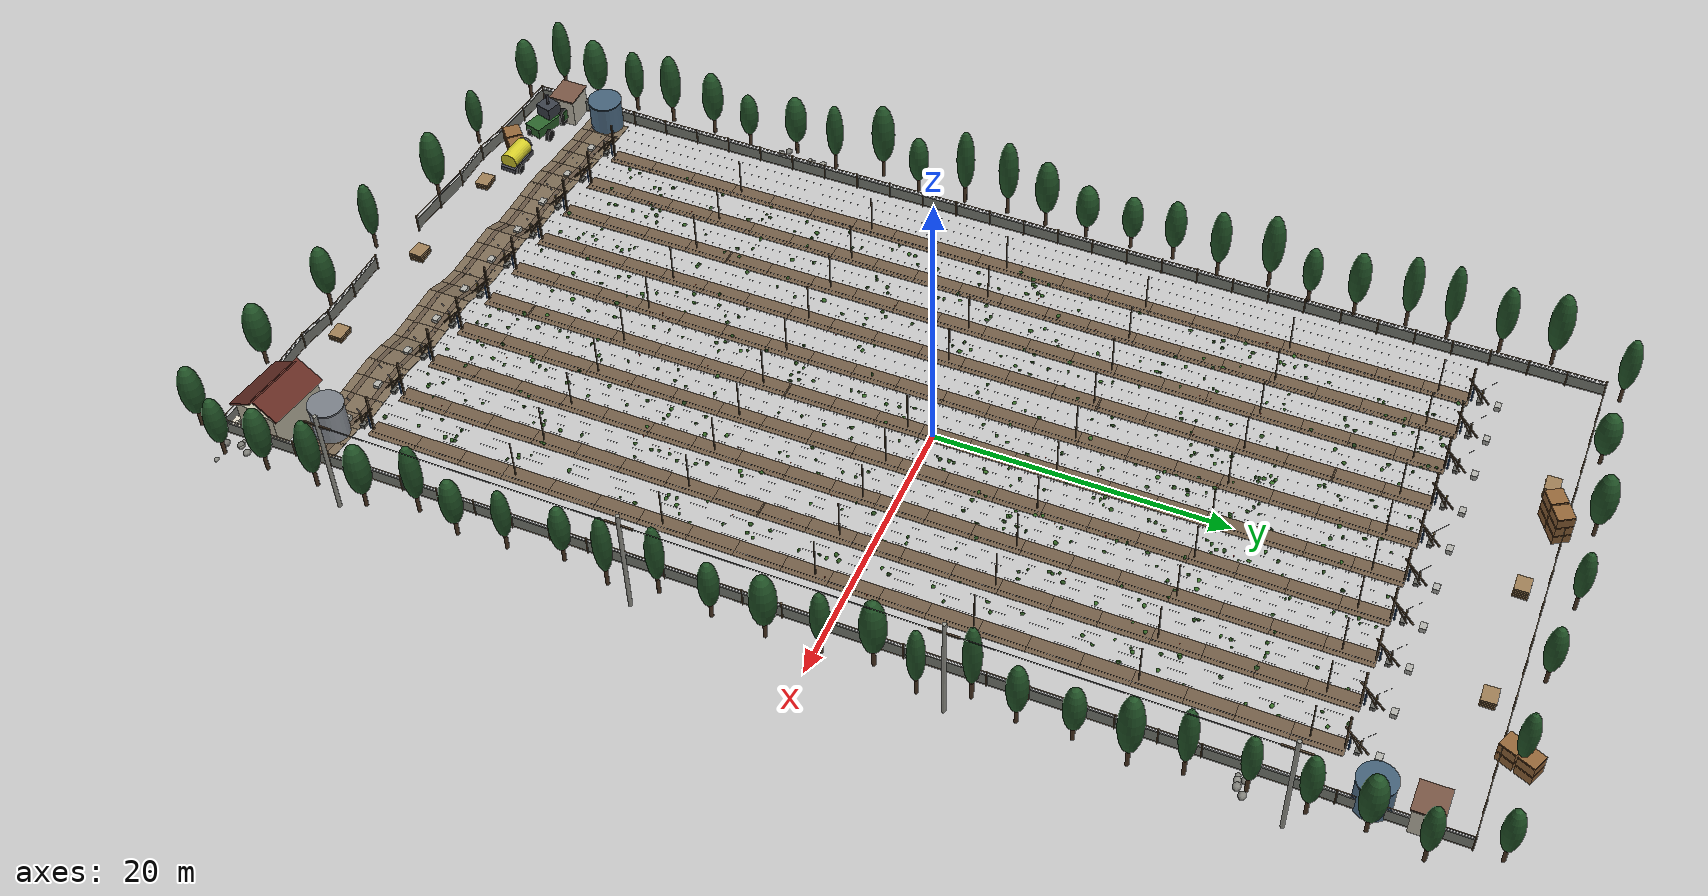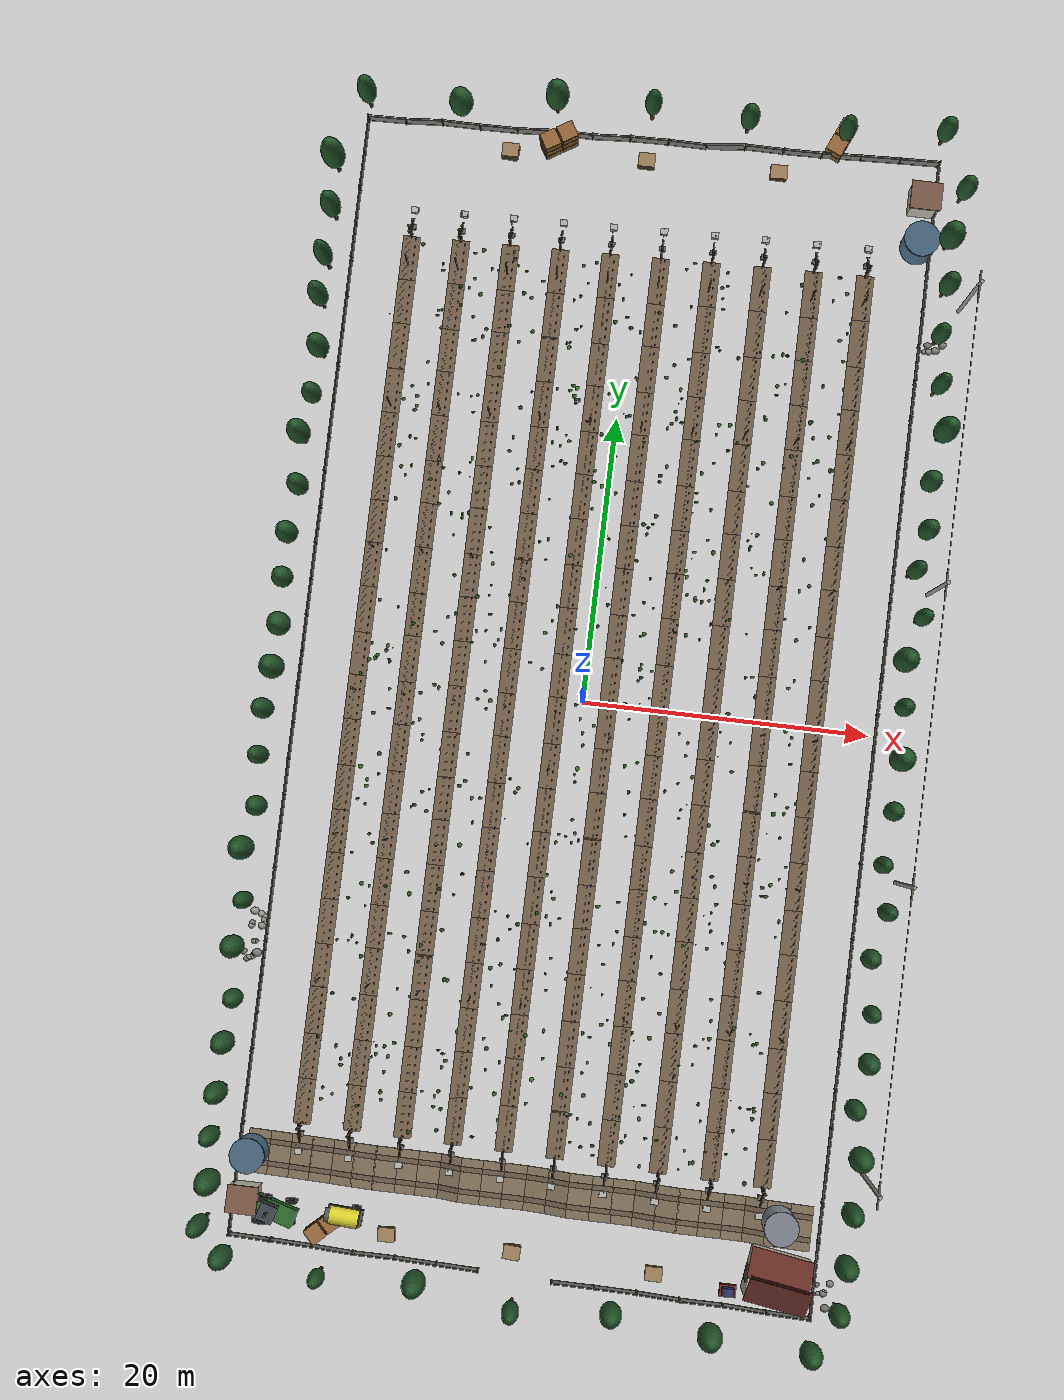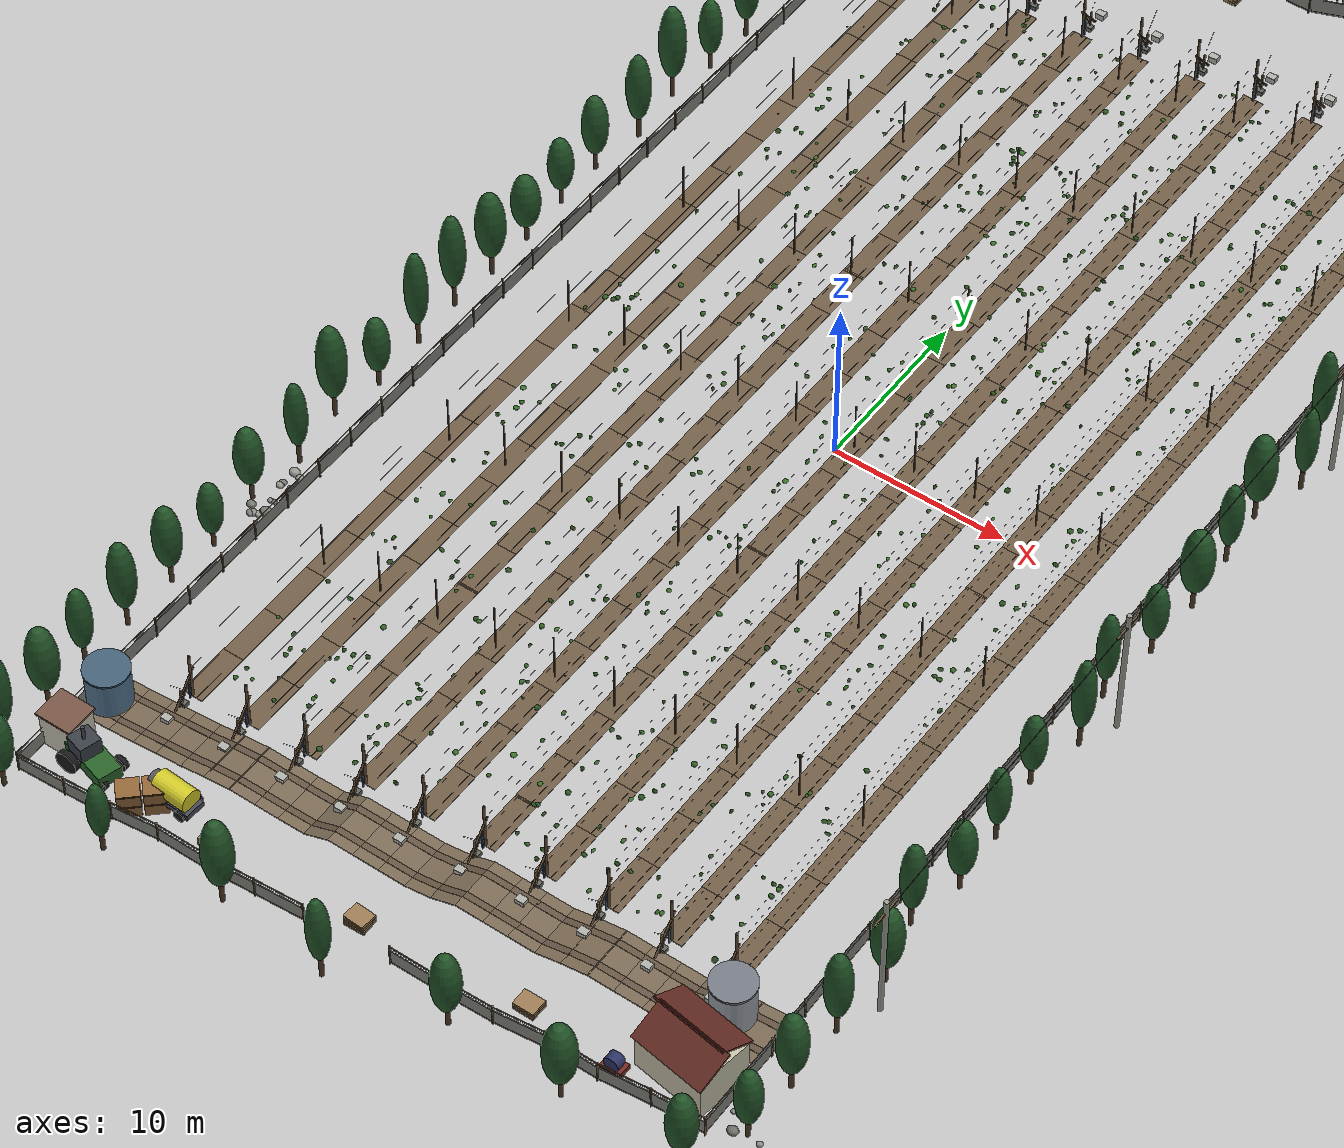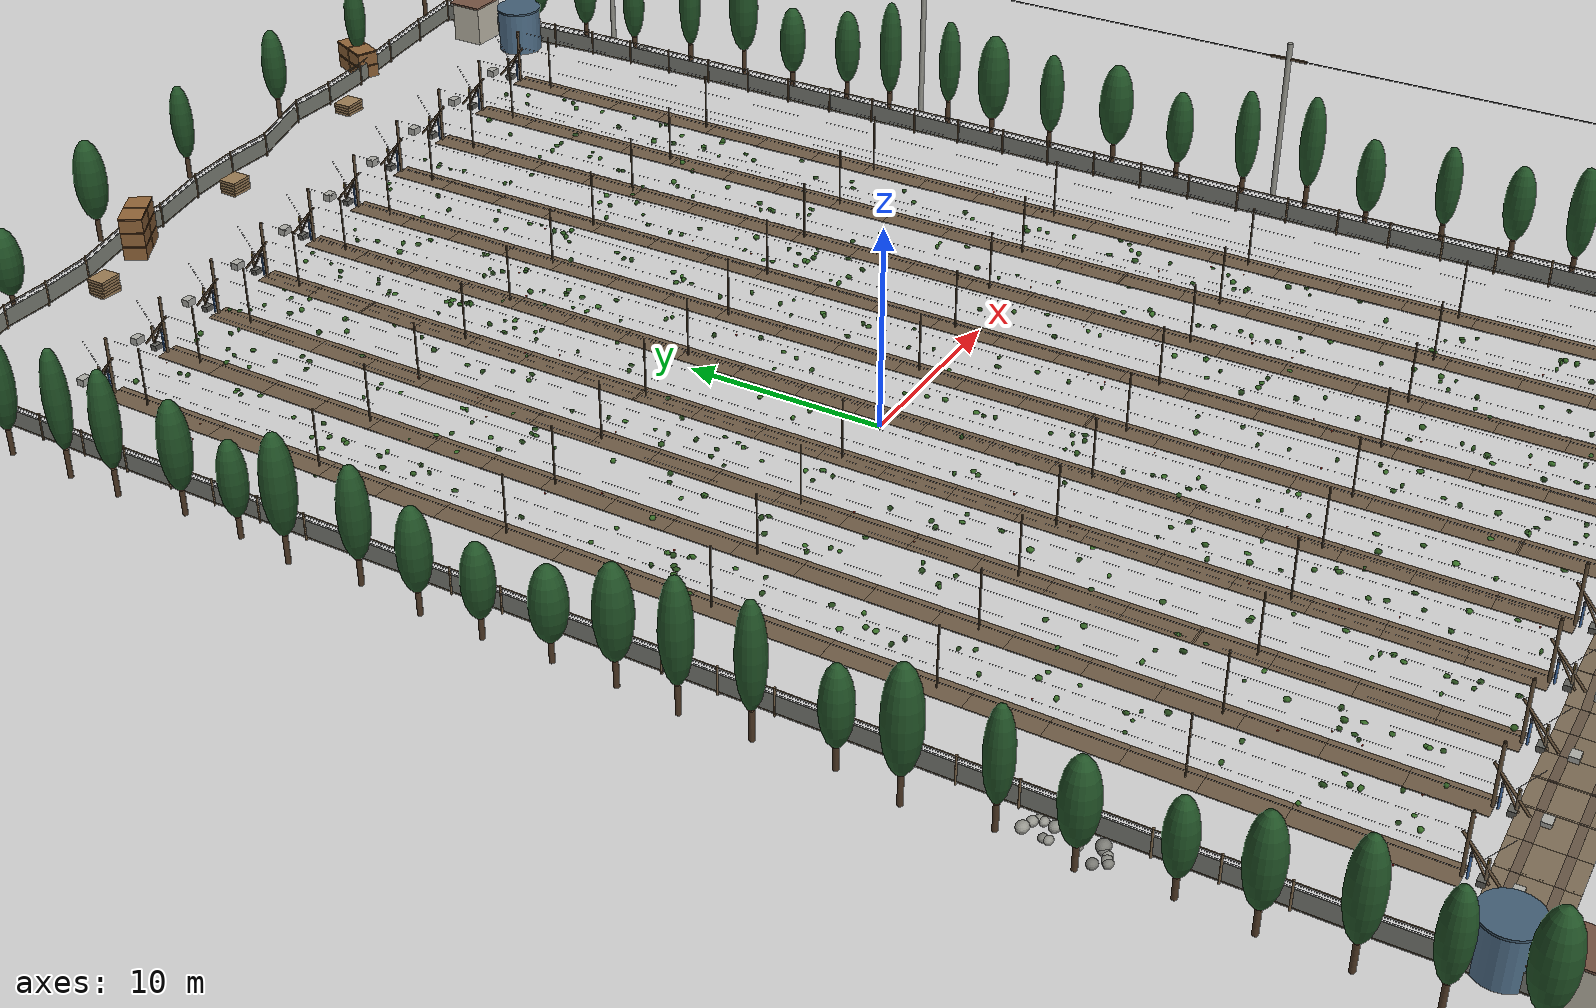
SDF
<sdf version="1.9">
 <world name="orchard_10x41">
  <plugin filename="gz-sim-physics-system" name="gz::sim::systems::Physics"/>
  <plugin filename="gz-sim-user-commands-system" name="gz::sim::systems::UserCommands"/>
  <plugin filename="gz-sim-scene-broadcaster-system" name="gz::sim::systems::SceneBroadcaster"/>
  <plugin filename="gz-sim-sensors-system" name="gz::sim::systems::Sensors">
   <render_engine>ogre2</render_engine>
  </plugin>
  <plugin filename="gz-sim-imu-system" name="gz::sim::systems::Imu"/>
  <plugin filename="gz-sim-navsat-system" name="gz::sim::systems::NavSat"/>
  <physics name="2ms" type="dart">
   <max_step_size>0.002</max_step_size>
   <real_time_factor>1.0</real_time_factor>
   <dart><collision_detector>bullet</collision_detector></dart>
  </physics>
  <spherical_coordinates>
   <surface_model>EARTH_WGS84</surface_model>
   <world_frame_orientation>ENU</world_frame_orientation>
   <latitude_deg>36.57</latitude_deg>
   <longitude_deg>128.50</longitude_deg>
   <elevation>50.0</elevation>
  </spherical_coordinates>
  <scene>
   <ambient>0.5 0.5 0.5 1</ambient>
   <background>0.6 0.7 0.85</background>
   <shadows>false</shadows>
   <grid>false</grid>
  </scene>
  <light type="directional" name="sun">
   <cast_shadows>false</cast_shadows>
   <pose>0 0 20 0 0 0</pose>
   <diffuse>1.0 0.98 0.95 1</diffuse>
   <specular>0.2 0.2 0.2 1</specular>
   <direction>-0.4 0.3 -0.85</direction>
  </light>
  <model name="trellis_r0">
   <static>true</static>
   <link name="link">
    <visual name="post_1">
     <pose>-15.750 -31.000 1.973 0.0000 0.0000 0.0000</pose>
     <geometry><cylinder><radius>0.0375</radius><length>2.9600</length></cylinder></geometry>
     <material>
      <ambient>0.350 0.280 0.200 1</ambient>
      <diffuse>0.385 0.308 0.220 1</diffuse>
      <specular>0.105 0.084 0.060 1</specular>
     </material>
     <plugin filename="gz-sim-label-system" name="gz::sim::systems::Label"><label>12</label></plugin>
    </visual>
    <visual name="post_2">
     <pose>-15.750 -21.000 1.975 0.0000 0.0000 0.0000</pose>
     <geometry><cylinder><radius>0.0375</radius><length>2.9600</length></cylinder></geometry>
     <material>
      <ambient>0.350 0.280 0.200 1</ambient>
      <diffuse>0.385 0.308 0.220 1</diffuse>
      <specular>0.105 0.084 0.060 1</specular>
     </material>
     <plugin filename="gz-sim-label-system" name="gz::sim::systems::Label"><label>12</label></plugin>
    </visual>
    <visual name="post_3">
     <pose>-15.750 -11.000 1.974 0.0000 0.0000 0.0000</pose>
     <geometry><cylinder><radius>0.0375</radius><length>2.9600</length></cylinder></geometry>
     <material>
      <ambient>0.350 0.280 0.200 1</ambient>
      <diffuse>0.385 0.308 0.220 1</diffuse>
      <specular>0.105 0.084 0.060 1</specular>
     </material>
     <plugin filename="gz-sim-label-system" name="gz::sim::systems::Label"><label>12</label></plugin>
    </visual>
    <visual name="post_4">
     <pose>-15.750 -1.000 1.972 0.0000 0.0000 0.0000</pose>
     <geometry><cylinder><radius>0.0375</radius><length>2.9600</length></cylinder></geometry>
     <material>
      <ambient>0.350 0.280 0.200 1</ambient>
      <diffuse>0.385 0.308 0.220 1</diffuse>
      <specular>0.105 0.084 0.060 1</specular>
     </material>
     <plugin filename="gz-sim-label-system" name="gz::sim::systems::Label"><label>12</label></plugin>
    </visual>
    <visual name="post_5">
     <pose>-15.750 9.000 1.970 0.0000 0.0000 0.0000</pose>
     <geometry><cylinder><radius>0.0375</radius><length>2.9600</length></cylinder></geometry>
     <material>
      <ambient>0.350 0.280 0.200 1</ambient>
      <diffuse>0.385 0.308 0.220 1</diffuse>
      <specular>0.105 0.084 0.060 1</specular>
     </material>
     <plugin filename="gz-sim-label-system" name="gz::sim::systems::Label"><label>12</label></plugin>
    </visual>
    <visual name="post_6">
     <pose>-15.750 19.000 1.959 0.0000 0.0000 0.0000</pose>
     <geometry><cylinder><radius>0.0375</radius><length>2.9600</length></cylinder></geometry>
     <material>
      <ambient>0.350 0.280 0.200 1</ambient>
      <diffuse>0.385 0.308 0.220 1</diffuse>
      <specular>0.105 0.084 0.060 1</specular>
     </material>
     <plugin filename="gz-sim-label-system" name="gz::sim::systems::Label"><label>12</label></plugin>
    </visual>
    <visual name="post_7">
     <pose>-15.750 29.000 1.962 0.0000 0.0000 0.0000</pose>
     <geometry><cylinder><radius>0.0375</radius><length>2.9600</length></cylinder></geometry>
     <material>
      <ambient>0.350 0.280 0.200 1</ambient>
      <diffuse>0.385 0.308 0.220 1</diffuse>
      <specular>0.105 0.084 0.060 1</specular>
     </material>
     <plugin filename="gz-sim-label-system" name="gz::sim::systems::Label"><label>12</label></plugin>
    </visual>
    <visual name="anchor_8">
     <pose>-15.750 -31.500 1.283 -0.5200 0.0000 0.0000</pose>
     <geometry><cylinder><radius>0.0450</radius><length>1.8300</length></cylinder></geometry>
     <material>
      <ambient>0.350 0.280 0.200 1</ambient>
      <diffuse>0.385 0.308 0.220 1</diffuse>
      <specular>0.105 0.084 0.060 1</specular>
     </material>
     <plugin filename="gz-sim-label-system" name="gz::sim::systems::Label"><label>12</label></plugin>
    </visual>
    <visual name="anchor_9">
     <pose>-15.750 31.500 1.271 0.5200 0.0000 0.0000</pose>
     <geometry><cylinder><radius>0.0450</radius><length>1.8300</length></cylinder></geometry>
     <material>
      <ambient>0.350 0.280 0.200 1</ambient>
      <diffuse>0.385 0.308 0.220 1</diffuse>
      <specular>0.105 0.084 0.060 1</specular>
     </material>
     <plugin filename="gz-sim-label-system" name="gz::sim::systems::Label"><label>12</label></plugin>
    </visual>
    <visual name="wire_10">
     <pose>-15.750 -28.417 1.493 0.0002 0.0000 0.0000</pose>
     <geometry><box><size>0.0060 5.2700 0.0060</size></box></geometry>
     <material>
      <ambient>0.550 0.550 0.580 1</ambient>
      <diffuse>0.605 0.605 0.638 1</diffuse>
      <specular>0.165 0.165 0.174 1</specular>
     </material>
     <plugin filename="gz-sim-label-system" name="gz::sim::systems::Label"><label>13</label></plugin>
    </visual>
    <visual name="wire_11">
     <pose>-15.750 -23.250 1.494 0.0003 0.0000 0.0000</pose>
     <geometry><box><size>0.0060 5.2700 0.0060</size></box></geometry>
     <material>
      <ambient>0.550 0.550 0.580 1</ambient>
      <diffuse>0.605 0.605 0.638 1</diffuse>
      <specular>0.165 0.165 0.174 1</specular>
     </material>
     <plugin filename="gz-sim-label-system" name="gz::sim::systems::Label"><label>13</label></plugin>
    </visual>
    <visual name="wire_12">
     <pose>-15.750 -18.083 1.496 0.0003 0.0000 0.0000</pose>
     <geometry><box><size>0.0060 5.2700 0.0060</size></box></geometry>
     <material>
      <ambient>0.550 0.550 0.580 1</ambient>
      <diffuse>0.605 0.605 0.638 1</diffuse>
      <specular>0.165 0.165 0.174 1</specular>
     </material>
     <plugin filename="gz-sim-label-system" name="gz::sim::systems::Label"><label>13</label></plugin>
    </visual>
    <visual name="wire_13">
     <pose>-15.750 -12.917 1.495 -0.0005 0.0000 0.0000</pose>
     <geometry><box><size>0.0060 5.2700 0.0060</size></box></geometry>
     <material>
      <ambient>0.550 0.550 0.580 1</ambient>
      <diffuse>0.605 0.605 0.638 1</diffuse>
      <specular>0.165 0.165 0.174 1</specular>
     </material>
     <plugin filename="gz-sim-label-system" name="gz::sim::systems::Label"><label>13</label></plugin>
    </visual>
    <visual name="wire_14">
     <pose>-15.750 -7.750 1.494 0.0000 0.0000 0.0000</pose>
     <geometry><box><size>0.0060 5.2700 0.0060</size></box></geometry>
     <material>
      <ambient>0.550 0.550 0.580 1</ambient>
      <diffuse>0.605 0.605 0.638 1</diffuse>
      <specular>0.165 0.165 0.174 1</specular>
     </material>
     <plugin filename="gz-sim-label-system" name="gz::sim::systems::Label"><label>13</label></plugin>
    </visual>
    <visual name="wire_15">
     <pose>-15.750 -2.583 1.492 -0.0006 0.0000 0.0000</pose>
     <geometry><box><size>0.0060 5.2700 0.0060</size></box></geometry>
     <material>
      <ambient>0.550 0.550 0.580 1</ambient>
      <diffuse>0.605 0.605 0.638 1</diffuse>
      <specular>0.165 0.165 0.174 1</specular>
     </material>
     <plugin filename="gz-sim-label-system" name="gz::sim::systems::Label"><label>13</label></plugin>
    </visual>
    <visual name="wire_16">
     <pose>-15.750 2.583 1.490 -0.0005 0.0000 0.0000</pose>
     <geometry><box><size>0.0060 5.2700 0.0060</size></box></geometry>
     <material>
      <ambient>0.550 0.550 0.580 1</ambient>
      <diffuse>0.605 0.605 0.638 1</diffuse>
      <specular>0.165 0.165 0.174 1</specular>
     </material>
     <plugin filename="gz-sim-label-system" name="gz::sim::systems::Label"><label>13</label></plugin>
    </visual>
    <visual name="wire_17">
     <pose>-15.750 7.750 1.489 0.0002 0.0000 0.0000</pose>
     <geometry><box><size>0.0060 5.2700 0.0060</size></box></geometry>
     <material>
      <ambient>0.550 0.550 0.580 1</ambient>
      <diffuse>0.605 0.605 0.638 1</diffuse>
      <specular>0.165 0.165 0.174 1</specular>
     </material>
     <plugin filename="gz-sim-label-system" name="gz::sim::systems::Label"><label>13</label></plugin>
    </visual>
    <visual name="wire_18">
     <pose>-15.750 12.917 1.486 -0.0012 0.0000 0.0000</pose>
     <geometry><box><size>0.0060 5.2700 0.0060</size></box></geometry>
     <material>
      <ambient>0.550 0.550 0.580 1</ambient>
      <diffuse>0.605 0.605 0.638 1</diffuse>
      <specular>0.165 0.165 0.174 1</specular>
     </material>
     <plugin filename="gz-sim-label-system" name="gz::sim::systems::Label"><label>13</label></plugin>
    </visual>
    <visual name="wire_19">
     <pose>-15.750 18.083 1.481 -0.0009 0.0000 0.0000</pose>
     <geometry><box><size>0.0060 5.2700 0.0060</size></box></geometry>
     <material>
      <ambient>0.550 0.550 0.580 1</ambient>
      <diffuse>0.605 0.605 0.638 1</diffuse>
      <specular>0.165 0.165 0.174 1</specular>
     </material>
     <plugin filename="gz-sim-label-system" name="gz::sim::systems::Label"><label>13</label></plugin>
    </visual>
    <visual name="wire_20">
     <pose>-15.750 23.250 1.480 0.0005 0.0000 0.0000</pose>
     <geometry><box><size>0.0060 5.2700 0.0060</size></box></geometry>
     <material>
      <ambient>0.550 0.550 0.580 1</ambient>
      <diffuse>0.605 0.605 0.638 1</diffuse>
      <specular>0.165 0.165 0.174 1</specular>
     </material>
     <plugin filename="gz-sim-label-system" name="gz::sim::systems::Label"><label>13</label></plugin>
    </visual>
    <visual name="wire_21">
     <pose>-15.750 28.417 1.481 0.0001 0.0000 0.0000</pose>
     <geometry><box><size>0.0060 5.2700 0.0060</size></box></geometry>
     <material>
      <ambient>0.550 0.550 0.580 1</ambient>
      <diffuse>0.605 0.605 0.638 1</diffuse>
      <specular>0.165 0.165 0.174 1</specular>
     </material>
     <plugin filename="gz-sim-label-system" name="gz::sim::systems::Label"><label>13</label></plugin>
    </visual>
    <visual name="wire_22">
     <pose>-15.750 -28.417 2.493 0.0002 0.0000 0.0000</pose>
     <geometry><box><size>0.0060 5.2700 0.0060</size></box></geometry>
     <material>
      <ambient>0.550 0.550 0.580 1</ambient>
      <diffuse>0.605 0.605 0.638 1</diffuse>
      <specular>0.165 0.165 0.174 1</specular>
     </material>
     <plugin filename="gz-sim-label-system" name="gz::sim::systems::Label"><label>13</label></plugin>
    </visual>
    <visual name="wire_23">
     <pose>-15.750 -23.250 2.494 0.0003 0.0000 0.0000</pose>
     <geometry><box><size>0.0060 5.2700 0.0060</size></box></geometry>
     <material>
      <ambient>0.550 0.550 0.580 1</ambient>
      <diffuse>0.605 0.605 0.638 1</diffuse>
      <specular>0.165 0.165 0.174 1</specular>
     </material>
     <plugin filename="gz-sim-label-system" name="gz::sim::systems::Label"><label>13</label></plugin>
    </visual>
    <visual name="wire_24">
     <pose>-15.750 -18.083 2.496 0.0003 0.0000 0.0000</pose>
     <geometry><box><size>0.0060 5.2700 0.0060</size></box></geometry>
     <material>
      <ambient>0.550 0.550 0.580 1</ambient>
      <diffuse>0.605 0.605 0.638 1</diffuse>
      <specular>0.165 0.165 0.174 1</specular>
     </material>
     <plugin filename="gz-sim-label-system" name="gz::sim::systems::Label"><label>13</label></plugin>
    </visual>
    <visual name="wire_25">
     <pose>-15.750 -12.917 2.495 -0.0005 0.0000 0.0000</pose>
     <geometry><box><size>0.0060 5.2700 0.0060</size></box></geometry>
     <material>
      <ambient>0.550 0.550 0.580 1</ambient>
      <diffuse>0.605 0.605 0.638 1</diffuse>
      <specular>0.165 0.165 0.174 1</specular>
     </material>
     <plugin filename="gz-sim-label-system" name="gz::sim::systems::Label"><label>13</label></plugin>
    </visual>
    <visual name="wire_26">
     <pose>-15.750 -7.750 2.494 0.0000 0.0000 0.0000</pose>
     <geometry><box><size>0.0060 5.2700 0.0060</size></box></geometry>
     <material>
      <ambient>0.550 0.550 0.580 1</ambient>
      <diffuse>0.605 0.605 0.638 1</diffuse>
      <specular>0.165 0.165 0.174 1</specular>
     </material>
     <plugin filename="gz-sim-label-system" name="gz::sim::systems::Label"><label>13</label></plugin>
    </visual>
    <visual name="wire_27">
     <pose>-15.750 -2.583 2.492 -0.0006 0.0000 0.0000</pose>
     <geometry><box><size>0.0060 5.2700 0.0060</size></box></geometry>
     <material>
      <ambient>0.550 0.550 0.580 1</ambient>
      <diffuse>0.605 0.605 0.638 1</diffuse>
      <specular>0.165 0.165 0.174 1</specular>
     </material>
     <plugin filename="gz-sim-label-system" name="gz::sim::systems::Label"><label>13</label></plugin>
    </visual>
    <visual name="wire_28">
     <pose>-15.750 2.583 2.490 -0.0005 0.0000 0.0000</pose>
     <geometry><box><size>0.0060 5.2700 0.0060</size></box></geometry>
     <material>
      <ambient>0.550 0.550 0.580 1</ambient>
      <diffuse>0.605 0.605 0.638 1</diffuse>
      <specular>0.165 0.165 0.174 1</specular>
     </material>
     <plugin filename="gz-sim-label-system" name="gz::sim::systems::Label"><label>13</label></plugin>
    </visual>
    <visual name="wire_29">
     <pose>-15.750 7.750 2.489 0.0002 0.0000 0.0000</pose>
     <geometry><box><size>0.0060 5.2700 0.0060</size></box></geometry>
     <material>
      <ambient>0.550 0.550 0.580 1</ambient>
      <diffuse>0.605 0.605 0.638 1</diffuse>
      <specular>0.165 0.165 0.174 1</specular>
     </material>
     <plugin filename="gz-sim-label-system" name="gz::sim::systems::Label"><label>13</label></plugin>
    </visual>
    <visual name="wire_30">
     <pose>-15.750 12.917 2.486 -0.0012 0.0000 0.0000</pose>
     <geometry><box><size>0.0060 5.2700 0.0060</size></box></geometry>
     <material>
      <ambient>0.550 0.550 0.580 1</ambient>
      <diffuse>0.605 0.605 0.638 1</diffuse>
      <specular>0.165 0.165 0.174 1</specular>
     </material>
     <plugin filename="gz-sim-label-system" name="gz::sim::systems::Label"><label>13</label></plugin>
    </visual>
    <visual name="wire_31">
     <pose>-15.750 18.083 2.481 -0.0009 0.0000 0.0000</pose>
     <geometry><box><size>0.0060 5.2700 0.0060</size></box></geometry>
     <material>
      <ambient>0.550 0.550 0.580 1</ambient>
      <diffuse>0.605 0.605 0.638 1</diffuse>
      <specular>0.165 0.165 0.174 1</specular>
     </material>
     <plugin filename="gz-sim-label-system" name="gz::sim::systems::Label"><label>13</label></plugin>
    </visual>
    <visual name="wire_32">
     <pose>-15.750 23.250 2.480 0.0005 0.0000 0.0000</pose>
     <geometry><box><size>0.0060 5.2700 0.0060</size></box></geometry>
     <material>
      <ambient>0.550 0.550 0.580 1</ambient>
      <diffuse>0.605 0.605 0.638 1</diffuse>
      <specular>0.165 0.165 0.174 1</specular>
     </material>
     <plugin filename="gz-sim-label-system" name="gz::sim::systems::Label"><label>13</label></plugin>
    </visual>
    <visual name="wire_33">
     <pose>-15.750 28.417 2.481 0.0001 0.0000 0.0000</pose>
     <geometry><box><size>0.0060 5.2700 0.0060</size></box></geometry>
     <material>
      <ambient>0.550 0.550 0.580 1</ambient>
      <diffuse>0.605 0.605 0.638 1</diffuse>
      <specular>0.165 0.165 0.174 1</specular>
     </material>
     <plugin filename="gz-sim-label-system" name="gz::sim::systems::Label"><label>13</label></plugin>
    </visual>
    <visual name="wire_34">
     <pose>-15.750 -28.417 3.393 0.0002 0.0000 0.0000</pose>
     <geometry><box><size>0.0060 5.2700 0.0060</size></box></geometry>
     <material>
      <ambient>0.550 0.550 0.580 1</ambient>
      <diffuse>0.605 0.605 0.638 1</diffuse>
      <specular>0.165 0.165 0.174 1</specular>
     </material>
     <plugin filename="gz-sim-label-system" name="gz::sim::systems::Label"><label>13</label></plugin>
    </visual>
    <visual name="wire_35">
     <pose>-15.750 -23.250 3.394 0.0003 0.0000 0.0000</pose>
     <geometry><box><size>0.0060 5.2700 0.0060</size></box></geometry>
     <material>
      <ambient>0.550 0.550 0.580 1</ambient>
      <diffuse>0.605 0.605 0.638 1</diffuse>
      <specular>0.165 0.165 0.174 1</specular>
     </material>
     <plugin filename="gz-sim-label-system" name="gz::sim::systems::Label"><label>13</label></plugin>
    </visual>
    <visual name="wire_36">
     <pose>-15.750 -18.083 3.396 0.0003 0.0000 0.0000</pose>
     <geometry><box><size>0.0060 5.2700 0.0060</size></box></geometry>
     <material>
      <ambient>0.550 0.550 0.580 1</ambient>
      <diffuse>0.605 0.605 0.638 1</diffuse>
      <specular>0.165 0.165 0.174 1</specular>
     </material>
     <plugin filename="gz-sim-label-system" name="gz::sim::systems::Label"><label>13</label></plugin>
    </visual>
    <visual name="wire_37">
     <pose>-15.750 -12.917 3.395 -0.0005 0.0000 0.0000</pose>
     <geometry><box><size>0.0060 5.2700 0.0060</size></box></geometry>
     <material>
      <ambient>0.550 0.550 0.580 1</ambient>
      <diffuse>0.605 0.605 0.638 1</diffuse>
      <specular>0.165 0.165 0.174 1</specular>
     </material>
     <plugin filename="gz-sim-label-system" name="gz::sim::systems::Label"><label>13</label></plugin>
    </visual>
    <visual name="wire_38">
     <pose>-15.750 -7.750 3.394 0.0000 0.0000 0.0000</pose>
     <geometry><box><size>0.0060 5.2700 0.0060</size></box></geometry>
     <material>
      <ambient>0.550 0.550 0.580 1</ambient>
      <diffuse>0.605 0.605 0.638 1</diffuse>
      <specular>0.165 0.165 0.174 1</specular>
     </material>
     <plugin filename="gz-sim-label-system" name="gz::sim::systems::Label"><label>13</label></plugin>
    </visual>
    <visual name="wire_39">
     <pose>-15.750 -2.583 3.392 -0.0006 0.0000 0.0000</pose>
     <geometry><box><size>0.0060 5.2700 0.0060</size></box></geometry>
     <material>
      <ambient>0.550 0.550 0.580 1</ambient>
      <diffuse>0.605 0.605 0.638 1</diffuse>
      <specular>0.165 0.165 0.174 1</specular>
     </material>
     <plugin filename="gz-sim-label-system" name="gz::sim::systems::Label"><label>13</label></plugin>
    </visual>
    <visual name="wire_40">
     <pose>-15.750 2.583 3.390 -0.0005 0.0000 0.0000</pose>
     <geometry><box><size>0.0060 5.2700 0.0060</size></box></geometry>
     <material>
      <ambient>0.550 0.550 0.580 1</ambient>
      <diffuse>0.605 0.605 0.638 1</diffuse>
      <specular>0.165 0.165 0.174 1</specular>
     </material>
     <plugin filename="gz-sim-label-system" name="gz::sim::systems::Label"><label>13</label></plugin>
    </visual>
    <visual name="wire_41">
     <pose>-15.750 7.750 3.389 0.0002 0.0000 0.0000</pose>
     <geometry><box><size>0.0060 5.2700 0.0060</size></box></geometry>
     <material>
      <ambient>0.550 0.550 0.580 1</ambient>
      <diffuse>0.605 0.605 0.638 1</diffuse>
      <specular>0.165 0.165 0.174 1</specular>
     </material>
     <plugin filename="gz-sim-label-system" name="gz::sim::systems::Label"><label>13</label></plugin>
    </visual>
    <visual name="wire_42">
     <pose>-15.750 12.917 3.386 -0.0012 0.0000 0.0000</pose>
     <geometry><box><size>0.0060 5.2700 0.0060</size></box></geometry>
     <material>
      <ambient>0.550 0.550 0.580 1</ambient>
      <diffuse>0.605 0.605 0.638 1</diffuse>
      <specular>0.165 0.165 0.174 1</specular>
     </material>
     <plugin filename="gz-sim-label-system" name="gz::sim::systems::Label"><label>13</label></plugin>
    </visual>
    <visual name="wire_43">
     <pose>-15.750 18.083 3.381 -0.0009 0.0000 0.0000</pose>
     <geometry><box><size>0.0060 5.2700 0.0060</size></box></geometry>
     <material>
      <ambient>0.550 0.550 0.580 1</ambient>
      <diffuse>0.605 0.605 0.638 1</diffuse>
      <specular>0.165 0.165 0.174 1</specular>
     </material>
     <plugin filename="gz-sim-label-system" name="gz::sim::systems::Label"><label>13</label></plugin>
    </visual>
    <visual name="wire_44">
     <pose>-15.750 23.250 3.380 0.0005 0.0000 0.0000</pose>
     <geometry><box><size>0.0060 5.2700 0.0060</size></box></geometry>
     <material>
      <ambient>0.550 0.550 0.580 1</ambient>
      <diffuse>0.605 0.605 0.638 1</diffuse>
      <specular>0.165 0.165 0.174 1</specular>
     </material>
     <plugin filename="gz-sim-label-system" name="gz::sim::systems::Label"><label>13</label></plugin>
    </visual>
    <visual name="wire_45">
     <pose>-15.750 28.417 3.381 0.0001 0.0000 0.0000</pose>
     <geometry><box><size>0.0060 5.2700 0.0060</size></box></geometry>
     <material>
      <ambient>0.550 0.550 0.580 1</ambient>
      <diffuse>0.605 0.605 0.638 1</diffuse>
      <specular>0.165 0.165 0.174 1</specular>
     </material>
     <plugin filename="gz-sim-label-system" name="gz::sim::systems::Label"><label>13</label></plugin>
    </visual>
   </link>
  </model>
  <model name="trellis_r1">
   <static>true</static>
   <link name="link">
    <visual name="post_1">
     <pose>-12.250 -31.000 2.385 0.0000 0.0000 0.0000</pose>
     <geometry><cylinder><radius>0.0375</radius><length>2.9600</length></cylinder></geometry>
     <material>
      <ambient>0.350 0.280 0.200 1</ambient>
      <diffuse>0.385 0.308 0.220 1</diffuse>
      <specular>0.105 0.084 0.060 1</specular>
     </material>
     <plugin filename="gz-sim-label-system" name="gz::sim::systems::Label"><label>12</label></plugin>
    </visual>
    <visual name="post_2">
     <pose>-12.250 -21.000 2.390 0.0000 0.0000 0.0000</pose>
     <geometry><cylinder><radius>0.0375</radius><length>2.9600</length></cylinder></geometry>
     <material>
      <ambient>0.350 0.280 0.200 1</ambient>
      <diffuse>0.385 0.308 0.220 1</diffuse>
      <specular>0.105 0.084 0.060 1</specular>
     </material>
     <plugin filename="gz-sim-label-system" name="gz::sim::systems::Label"><label>12</label></plugin>
    </visual>
    <visual name="post_3">
     <pose>-12.250 -11.000 2.389 0.0000 0.0000 0.0000</pose>
     <geometry><cylinder><radius>0.0375</radius><length>2.9600</length></cylinder></geometry>
     <material>
      <ambient>0.350 0.280 0.200 1</ambient>
      <diffuse>0.385 0.308 0.220 1</diffuse>
      <specular>0.105 0.084 0.060 1</specular>
     </material>
     <plugin filename="gz-sim-label-system" name="gz::sim::systems::Label"><label>12</label></plugin>
    </visual>
    <visual name="post_4">
     <pose>-12.250 -1.000 2.386 0.0000 0.0000 0.0000</pose>
     <geometry><cylinder><radius>0.0375</radius><length>2.9600</length></cylinder></geometry>
     <material>
      <ambient>0.350 0.280 0.200 1</ambient>
      <diffuse>0.385 0.308 0.220 1</diffuse>
      <specular>0.105 0.084 0.060 1</specular>
     </material>
     <plugin filename="gz-sim-label-system" name="gz::sim::systems::Label"><label>12</label></plugin>
    </visual>
    <visual name="post_5">
     <pose>-12.250 9.000 2.384 0.0000 0.0000 0.0000</pose>
     <geometry><cylinder><radius>0.0375</radius><length>2.9600</length></cylinder></geometry>
     <material>
      <ambient>0.350 0.280 0.200 1</ambient>
      <diffuse>0.385 0.308 0.220 1</diffuse>
      <specular>0.105 0.084 0.060 1</specular>
     </material>
     <plugin filename="gz-sim-label-system" name="gz::sim::systems::Label"><label>12</label></plugin>
    </visual>
    <visual name="post_6">
     <pose>-12.250 19.000 2.373 0.0000 0.0000 0.0000</pose>
     <geometry><cylinder><radius>0.0375</radius><length>2.9600</length></cylinder></geometry>
     <material>
      <ambient>0.350 0.280 0.200 1</ambient>
      <diffuse>0.385 0.308 0.220 1</diffuse>
      <specular>0.105 0.084 0.060 1</specular>
     </material>
     <plugin filename="gz-sim-label-system" name="gz::sim::systems::Label"><label>12</label></plugin>
    </visual>
    <visual name="post_7">
     <pose>-12.250 29.000 2.376 0.0000 0.0000 0.0000</pose>
     <geometry><cylinder><radius>0.0375</radius><length>2.9600</length></cylinder></geometry>
     <material>
      <ambient>0.350 0.280 0.200 1</ambient>
      <diffuse>0.385 0.308 0.220 1</diffuse>
      <specular>0.105 0.084 0.060 1</specular>
     </material>
     <plugin filename="gz-sim-label-system" name="gz::sim::systems::Label"><label>12</label></plugin>
    </visual>
    <visual name="anchor_8">
     <pose>-12.250 -31.500 1.695 -0.5200 0.0000 0.0000</pose>
     <geometry><cylinder><radius>0.0450</radius><length>1.8300</length></cylinder></geometry>
     <material>
      <ambient>0.350 0.280 0.200 1</ambient>
      <diffuse>0.385 0.308 0.220 1</diffuse>
      <specular>0.105 0.084 0.060 1</specular>
     </material>
     <plugin filename="gz-sim-label-system" name="gz::sim::systems::Label"><label>12</label></plugin>
    </visual>
    <visual name="anchor_9">
     <pose>-12.250 31.500 1.686 0.5200 0.0000 0.0000</pose>
     <geometry><cylinder><radius>0.0450</radius><length>1.8300</length></cylinder></geometry>
     <material>
      <ambient>0.350 0.280 0.200 1</ambient>
      <diffuse>0.385 0.308 0.220 1</diffuse>
      <specular>0.105 0.084 0.060 1</specular>
     </material>
     <plugin filename="gz-sim-label-system" name="gz::sim::systems::Label"><label>12</label></plugin>
    </visual>
    <visual name="wire_10">
     <pose>-12.250 -28.417 1.906 0.0005 0.0000 0.0000</pose>
     <geometry><box><size>0.0060 5.2700 0.0060</size></box></geometry>
     <material>
      <ambient>0.550 0.550 0.580 1</ambient>
      <diffuse>0.605 0.605 0.638 1</diffuse>
      <specular>0.165 0.165 0.174 1</specular>
     </material>
     <plugin filename="gz-sim-label-system" name="gz::sim::systems::Label"><label>13</label></plugin>
    </visual>
    <visual name="wire_11">
     <pose>-12.250 -23.250 1.909 0.0005 0.0000 0.0000</pose>
     <geometry><box><size>0.0060 5.2700 0.0060</size></box></geometry>
     <material>
      <ambient>0.550 0.550 0.580 1</ambient>
      <diffuse>0.605 0.605 0.638 1</diffuse>
      <specular>0.165 0.165 0.174 1</specular>
     </material>
     <plugin filename="gz-sim-label-system" name="gz::sim::systems::Label"><label>13</label></plugin>
    </visual>
    <visual name="wire_12">
     <pose>-12.250 -18.083 1.910 0.0001 0.0000 0.0000</pose>
     <geometry><box><size>0.0060 5.2700 0.0060</size></box></geometry>
     <material>
      <ambient>0.550 0.550 0.580 1</ambient>
      <diffuse>0.605 0.605 0.638 1</diffuse>
      <specular>0.165 0.165 0.174 1</specular>
     </material>
     <plugin filename="gz-sim-label-system" name="gz::sim::systems::Label"><label>13</label></plugin>
    </visual>
    <visual name="wire_13">
     <pose>-12.250 -12.917 1.910 -0.0004 0.0000 0.0000</pose>
     <geometry><box><size>0.0060 5.2700 0.0060</size></box></geometry>
     <material>
      <ambient>0.550 0.550 0.580 1</ambient>
      <diffuse>0.605 0.605 0.638 1</diffuse>
      <specular>0.165 0.165 0.174 1</specular>
     </material>
     <plugin filename="gz-sim-label-system" name="gz::sim::systems::Label"><label>13</label></plugin>
    </visual>
    <visual name="wire_14">
     <pose>-12.250 -7.750 1.908 -0.0001 0.0000 0.0000</pose>
     <geometry><box><size>0.0060 5.2700 0.0060</size></box></geometry>
     <material>
      <ambient>0.550 0.550 0.580 1</ambient>
      <diffuse>0.605 0.605 0.638 1</diffuse>
      <specular>0.165 0.165 0.174 1</specular>
     </material>
     <plugin filename="gz-sim-label-system" name="gz::sim::systems::Label"><label>13</label></plugin>
    </visual>
    <visual name="wire_15">
     <pose>-12.250 -2.583 1.907 -0.0005 0.0000 0.0000</pose>
     <geometry><box><size>0.0060 5.2700 0.0060</size></box></geometry>
     <material>
      <ambient>0.550 0.550 0.580 1</ambient>
      <diffuse>0.605 0.605 0.638 1</diffuse>
      <specular>0.165 0.165 0.174 1</specular>
     </material>
     <plugin filename="gz-sim-label-system" name="gz::sim::systems::Label"><label>13</label></plugin>
    </visual>
    <visual name="wire_16">
     <pose>-12.250 2.583 1.905 -0.0002 0.0000 0.0000</pose>
     <geometry><box><size>0.0060 5.2700 0.0060</size></box></geometry>
     <material>
      <ambient>0.550 0.550 0.580 1</ambient>
      <diffuse>0.605 0.605 0.638 1</diffuse>
      <specular>0.165 0.165 0.174 1</specular>
     </material>
     <plugin filename="gz-sim-label-system" name="gz::sim::systems::Label"><label>13</label></plugin>
    </visual>
    <visual name="wire_17">
     <pose>-12.250 7.750 1.904 -0.0002 0.0000 0.0000</pose>
     <geometry><box><size>0.0060 5.2700 0.0060</size></box></geometry>
     <material>
      <ambient>0.550 0.550 0.580 1</ambient>
      <diffuse>0.605 0.605 0.638 1</diffuse>
      <specular>0.165 0.165 0.174 1</specular>
     </material>
     <plugin filename="gz-sim-label-system" name="gz::sim::systems::Label"><label>13</label></plugin>
    </visual>
    <visual name="wire_18">
     <pose>-12.250 12.917 1.899 -0.0014 0.0000 0.0000</pose>
     <geometry><box><size>0.0060 5.2700 0.0060</size></box></geometry>
     <material>
      <ambient>0.550 0.550 0.580 1</ambient>
      <diffuse>0.605 0.605 0.638 1</diffuse>
      <specular>0.165 0.165 0.174 1</specular>
     </material>
     <plugin filename="gz-sim-label-system" name="gz::sim::systems::Label"><label>13</label></plugin>
    </visual>
    <visual name="wire_19">
     <pose>-12.250 18.083 1.894 -0.0006 0.0000 0.0000</pose>
     <geometry><box><size>0.0060 5.2700 0.0060</size></box></geometry>
     <material>
      <ambient>0.550 0.550 0.580 1</ambient>
      <diffuse>0.605 0.605 0.638 1</diffuse>
      <specular>0.165 0.165 0.174 1</specular>
     </material>
     <plugin filename="gz-sim-label-system" name="gz::sim::systems::Label"><label>13</label></plugin>
    </visual>
    <visual name="wire_20">
     <pose>-12.250 23.250 1.894 0.0003 0.0000 0.0000</pose>
     <geometry><box><size>0.0060 5.2700 0.0060</size></box></geometry>
     <material>
      <ambient>0.550 0.550 0.580 1</ambient>
      <diffuse>0.605 0.605 0.638 1</diffuse>
      <specular>0.165 0.165 0.174 1</specular>
     </material>
     <plugin filename="gz-sim-label-system" name="gz::sim::systems::Label"><label>13</label></plugin>
    </visual>
    <visual name="wire_21">
     <pose>-12.250 28.417 1.895 0.0003 0.0000 0.0000</pose>
     <geometry><box><size>0.0060 5.2700 0.0060</size></box></geometry>
     <material>
      <ambient>0.550 0.550 0.580 1</ambient>
      <diffuse>0.605 0.605 0.638 1</diffuse>
      <specular>0.165 0.165 0.174 1</specular>
     </material>
     <plugin filename="gz-sim-label-system" name="gz::sim::systems::Label"><label>13</label></plugin>
    </visual>
    <visual name="wire_22">
     <pose>-12.250 -28.417 2.906 0.0005 0.0000 0.0000</pose>
     <geometry><box><size>0.0060 5.2700 0.0060</size></box></geometry>
     <material>
      <ambient>0.550 0.550 0.580 1</ambient>
      <diffuse>0.605 0.605 0.638 1</diffuse>
      <specular>0.165 0.165 0.174 1</specular>
     </material>
     <plugin filename="gz-sim-label-system" name="gz::sim::systems::Label"><label>13</label></plugin>
    </visual>
    <visual name="wire_23">
     <pose>-12.250 -23.250 2.909 0.0005 0.0000 0.0000</pose>
     <geometry><box><size>0.0060 5.2700 0.0060</size></box></geometry>
     <material>
      <ambient>0.550 0.550 0.580 1</ambient>
      <diffuse>0.605 0.605 0.638 1</diffuse>
      <specular>0.165 0.165 0.174 1</specular>
     </material>
     <plugin filename="gz-sim-label-system" name="gz::sim::systems::Label"><label>13</label></plugin>
    </visual>
    <visual name="wire_24">
     <pose>-12.250 -18.083 2.910 0.0001 0.0000 0.0000</pose>
     <geometry><box><size>0.0060 5.2700 0.0060</size></box></geometry>
     <material>
      <ambient>0.550 0.550 0.580 1</ambient>
      <diffuse>0.605 0.605 0.638 1</diffuse>
      <specular>0.165 0.165 0.174 1</specular>
     </material>
     <plugin filename="gz-sim-label-system" name="gz::sim::systems::Label"><label>13</label></plugin>
    </visual>
    <visual name="wire_25">
     <pose>-12.250 -12.917 2.910 -0.0004 0.0000 0.0000</pose>
     <geometry><box><size>0.0060 5.2700 0.0060</size></box></geometry>
     <material>
      <ambient>0.550 0.550 0.580 1</ambient>
      <diffuse>0.605 0.605 0.638 1</diffuse>
      <specular>0.165 0.165 0.174 1</specular>
     </material>
     <plugin filename="gz-sim-label-system" name="gz::sim::systems::Label"><label>13</label></plugin>
    </visual>
    <visual name="wire_26">
     <pose>-12.250 -7.750 2.908 -0.0001 0.0000 0.0000</pose>
     <geometry><box><size>0.0060 5.2700 0.0060</size></box></geometry>
     <material>
      <ambient>0.550 0.550 0.580 1</ambient>
      <diffuse>0.605 0.605 0.638 1</diffuse>
      <specular>0.165 0.165 0.174 1</specular>
     </material>
     <plugin filename="gz-sim-label-system" name="gz::sim::systems::Label"><label>13</label></plugin>
    </visual>
    <visual name="wire_27">
     <pose>-12.250 -2.583 2.907 -0.0005 0.0000 0.0000</pose>
     <geometry><box><size>0.0060 5.2700 0.0060</size></box></geometry>
     <material>
      <ambient>0.550 0.550 0.580 1</ambient>
      <diffuse>0.605 0.605 0.638 1</diffuse>
      <specular>0.165 0.165 0.174 1</specular>
     </material>
     <plugin filename="gz-sim-label-system" name="gz::sim::systems::Label"><label>13</label></plugin>
    </visual>
    <visual name="wire_28">
     <pose>-12.250 2.583 2.905 -0.0002 0.0000 0.0000</pose>
     <geometry><box><size>0.0060 5.2700 0.0060</size></box></geometry>
     <material>
      <ambient>0.550 0.550 0.580 1</ambient>
      <diffuse>0.605 0.605 0.638 1</diffuse>
      <specular>0.165 0.165 0.174 1</specular>
     </material>
     <plugin filename="gz-sim-label-system" name="gz::sim::systems::Label"><label>13</label></plugin>
    </visual>
    <visual name="wire_29">
     <pose>-12.250 7.750 2.904 -0.0002 0.0000 0.0000</pose>
     <geometry><box><size>0.0060 5.2700 0.0060</size></box></geometry>
     <material>
      <ambient>0.550 0.550 0.580 1</ambient>
      <diffuse>0.605 0.605 0.638 1</diffuse>
      <specular>0.165 0.165 0.174 1</specular>
     </material>
     <plugin filename="gz-sim-label-system" name="gz::sim::systems::Label"><label>13</label></plugin>
    </visual>
    <visual name="wire_30">
     <pose>-12.250 12.917 2.899 -0.0014 0.0000 0.0000</pose>
     <geometry><box><size>0.0060 5.2700 0.0060</size></box></geometry>
     <material>
      <ambient>0.550 0.550 0.580 1</ambient>
      <diffuse>0.605 0.605 0.638 1</diffuse>
      <specular>0.165 0.165 0.174 1</specular>
     </material>
     <plugin filename="gz-sim-label-system" name="gz::sim::systems::Label"><label>13</label></plugin>
    </visual>
    <visual name="wire_31">
     <pose>-12.250 18.083 2.894 -0.0006 0.0000 0.0000</pose>
     <geometry><box><size>0.0060 5.2700 0.0060</size></box></geometry>
     <material>
      <ambient>0.550 0.550 0.580 1</ambient>
      <diffuse>0.605 0.605 0.638 1</diffuse>
      <specular>0.165 0.165 0.174 1</specular>
     </material>
     <plugin filename="gz-sim-label-system" name="gz::sim::systems::Label"><label>13</label></plugin>
    </visual>
    <visual name="wire_32">
     <pose>-12.250 23.250 2.894 0.0003 0.0000 0.0000</pose>
     <geometry><box><size>0.0060 5.2700 0.0060</size></box></geometry>
     <material>
      <ambient>0.550 0.550 0.580 1</ambient>
      <diffuse>0.605 0.605 0.638 1</diffuse>
      <specular>0.165 0.165 0.174 1</specular>
     </material>
     <plugin filename="gz-sim-label-system" name="gz::sim::systems::Label"><label>13</label></plugin>
    </visual>
    <visual name="wire_33">
     <pose>-12.250 28.417 2.895 0.0003 0.0000 0.0000</pose>
     <geometry><box><size>0.0060 5.2700 0.0060</size></box></geometry>
     <material>
      <ambient>0.550 0.550 0.580 1</ambient>
      <diffuse>0.605 0.605 0.638 1</diffuse>
      <specular>0.165 0.165 0.174 1</specular>
     </material>
     <plugin filename="gz-sim-label-system" name="gz::sim::systems::Label"><label>13</label></plugin>
    </visual>
    <visual name="wire_34">
     <pose>-12.250 -28.417 3.806 0.0005 0.0000 0.0000</pose>
     <geometry><box><size>0.0060 5.2700 0.0060</size></box></geometry>
     <material>
      <ambient>0.550 0.550 0.580 1</ambient>
      <diffuse>0.605 0.605 0.638 1</diffuse>
      <specular>0.165 0.165 0.174 1</specular>
     </material>
     <plugin filename="gz-sim-label-system" name="gz::sim::systems::Label"><label>13</label></plugin>
    </visual>
    <visual name="wire_35">
     <pose>-12.250 -23.250 3.809 0.0005 0.0000 0.0000</pose>
     <geometry><box><size>0.0060 5.2700 0.0060</size></box></geometry>
     <material>
      <ambient>0.550 0.550 0.580 1</ambient>
      <diffuse>0.605 0.605 0.638 1</diffuse>
      <specular>0.165 0.165 0.174 1</specular>
     </material>
     <plugin filename="gz-sim-label-system" name="gz::sim::systems::Label"><label>13</label></plugin>
    </visual>
    <visual name="wire_36">
     <pose>-12.250 -18.083 3.810 0.0001 0.0000 0.0000</pose>
     <geometry><box><size>0.0060 5.2700 0.0060</size></box></geometry>
     <material>
      <ambient>0.550 0.550 0.580 1</ambient>
      <diffuse>0.605 0.605 0.638 1</diffuse>
      <specular>0.165 0.165 0.174 1</specular>
     </material>
     <plugin filename="gz-sim-label-system" name="gz::sim::systems::Label"><label>13</label></plugin>
    </visual>
    <visual name="wire_37">
     <pose>-12.250 -12.917 3.810 -0.0004 0.0000 0.0000</pose>
     <geometry><box><size>0.0060 5.2700 0.0060</size></box></geometry>
     <material>
      <ambient>0.550 0.550 0.580 1</ambient>
      <diffuse>0.605 0.605 0.638 1</diffuse>
      <specular>0.165 0.165 0.174 1</specular>
     </material>
     <plugin filename="gz-sim-label-system" name="gz::sim::systems::Label"><label>13</label></plugin>
    </visual>
    <visual name="wire_38">
     <pose>-12.250 -7.750 3.808 -0.0001 0.0000 0.0000</pose>
     <geometry><box><size>0.0060 5.2700 0.0060</size></box></geometry>
     <material>
      <ambient>0.550 0.550 0.580 1</ambient>
      <diffuse>0.605 0.605 0.638 1</diffuse>
      <specular>0.165 0.165 0.174 1</specular>
     </material>
     <plugin filename="gz-sim-label-system" name="gz::sim::systems::Label"><label>13</label></plugin>
    </visual>
    <visual name="wire_39">
     <pose>-12.250 -2.583 3.807 -0.0005 0.0000 0.0000</pose>
     <geometry><box><size>0.0060 5.2700 0.0060</size></box></geometry>
     <material>
      <ambient>0.550 0.550 0.580 1</ambient>
      <diffuse>0.605 0.605 0.638 1</diffuse>
      <specular>0.165 0.165 0.174 1</specular>
     </material>
     <plugin filename="gz-sim-label-system" name="gz::sim::systems::Label"><label>13</label></plugin>
    </visual>
    <visual name="wire_40">
     <pose>-12.250 2.583 3.805 -0.0002 0.0000 0.0000</pose>
     <geometry><box><size>0.0060 5.2700 0.0060</size></box></geometry>
     <material>
      <ambient>0.550 0.550 0.580 1</ambient>
      <diffuse>0.605 0.605 0.638 1</diffuse>
      <specular>0.165 0.165 0.174 1</specular>
     </material>
     <plugin filename="gz-sim-label-system" name="gz::sim::systems::Label"><label>13</label></plugin>
    </visual>
    <visual name="wire_41">
     <pose>-12.250 7.750 3.804 -0.0002 0.0000 0.0000</pose>
     <geometry><box><size>0.0060 5.2700 0.0060</size></box></geometry>
     <material>
      <ambient>0.550 0.550 0.580 1</ambient>
      <diffuse>0.605 0.605 0.638 1</diffuse>
      <specular>0.165 0.165 0.174 1</specular>
     </material>
     <plugin filename="gz-sim-label-system" name="gz::sim::systems::Label"><label>13</label></plugin>
    </visual>
    <visual name="wire_42">
     <pose>-12.250 12.917 3.799 -0.0014 0.0000 0.0000</pose>
     <geometry><box><size>0.0060 5.2700 0.0060</size></box></geometry>
     <material>
      <ambient>0.550 0.550 0.580 1</ambient>
      <diffuse>0.605 0.605 0.638 1</diffuse>
      <specular>0.165 0.165 0.174 1</specular>
     </material>
     <plugin filename="gz-sim-label-system" name="gz::sim::systems::Label"><label>13</label></plugin>
    </visual>
    <visual name="wire_43">
     <pose>-12.250 18.083 3.794 -0.0006 0.0000 0.0000</pose>
     <geometry><box><size>0.0060 5.2700 0.0060</size></box></geometry>
     <material>
      <ambient>0.550 0.550 0.580 1</ambient>
      <diffuse>0.605 0.605 0.638 1</diffuse>
      <specular>0.165 0.165 0.174 1</specular>
     </material>
     <plugin filename="gz-sim-label-system" name="gz::sim::systems::Label"><label>13</label></plugin>
    </visual>
    <visual name="wire_44">
     <pose>-12.250 23.250 3.794 0.0003 0.0000 0.0000</pose>
     <geometry><box><size>0.0060 5.2700 0.0060</size></box></geometry>
     <material>
      <ambient>0.550 0.550 0.580 1</ambient>
      <diffuse>0.605 0.605 0.638 1</diffuse>
      <specular>0.165 0.165 0.174 1</specular>
     </material>
     <plugin filename="gz-sim-label-system" name="gz::sim::systems::Label"><label>13</label></plugin>
    </visual>
    <visual name="wire_45">
     <pose>-12.250 28.417 3.795 0.0003 0.0000 0.0000</pose>
     <geometry><box><size>0.0060 5.2700 0.0060</size></box></geometry>
     <material>
      <ambient>0.550 0.550 0.580 1</ambient>
      <diffuse>0.605 0.605 0.638 1</diffuse>
      <specular>0.165 0.165 0.174 1</specular>
     </material>
     <plugin filename="gz-sim-label-system" name="gz::sim::systems::Label"><label>13</label></plugin>
    </visual>
   </link>
  </model>
  <model name="trellis_r2">
   <static>true</static>
   <link name="link">
    <visual name="post_1">
     <pose>-8.750 -31.000 2.739 0.0000 0.0000 0.0000</pose>
     <geometry><cylinder><radius>0.0375</radius><length>2.9600</length></cylinder></geometry>
     <material>
      <ambient>0.350 0.280 0.200 1</ambient>
      <diffuse>0.385 0.308 0.220 1</diffuse>
      <specular>0.105 0.084 0.060 1</specular>
     </material>
     <plugin filename="gz-sim-label-system" name="gz::sim::systems::Label"><label>12</label></plugin>
    </visual>
    <visual name="post_2">
     <pose>-8.750 -21.000 2.745 0.0000 0.0000 0.0000</pose>
     <geometry><cylinder><radius>0.0375</radius><length>2.9600</length></cylinder></geometry>
     <material>
      <ambient>0.350 0.280 0.200 1</ambient>
      <diffuse>0.385 0.308 0.220 1</diffuse>
      <specular>0.105 0.084 0.060 1</specular>
     </material>
     <plugin filename="gz-sim-label-system" name="gz::sim::systems::Label"><label>12</label></plugin>
    </visual>
    <visual name="post_3">
     <pose>-8.750 -11.000 2.744 0.0000 0.0000 0.0000</pose>
     <geometry><cylinder><radius>0.0375</radius><length>2.9600</length></cylinder></geometry>
     <material>
      <ambient>0.350 0.280 0.200 1</ambient>
      <diffuse>0.385 0.308 0.220 1</diffuse>
      <specular>0.105 0.084 0.060 1</specular>
     </material>
     <plugin filename="gz-sim-label-system" name="gz::sim::systems::Label"><label>12</label></plugin>
    </visual>
    <visual name="post_4">
     <pose>-8.750 -1.000 2.740 0.0000 0.0000 0.0000</pose>
     <geometry><cylinder><radius>0.0375</radius><length>2.9600</length></cylinder></geometry>
     <material>
      <ambient>0.350 0.280 0.200 1</ambient>
      <diffuse>0.385 0.308 0.220 1</diffuse>
      <specular>0.105 0.084 0.060 1</specular>
     </material>
     <plugin filename="gz-sim-label-system" name="gz::sim::systems::Label"><label>12</label></plugin>
    </visual>
    <visual name="post_5">
     <pose>-8.750 9.000 2.739 0.0000 0.0000 0.0000</pose>
     <geometry><cylinder><radius>0.0375</radius><length>2.9600</length></cylinder></geometry>
     <material>
      <ambient>0.350 0.280 0.200 1</ambient>
      <diffuse>0.385 0.308 0.220 1</diffuse>
      <specular>0.105 0.084 0.060 1</specular>
     </material>
     <plugin filename="gz-sim-label-system" name="gz::sim::systems::Label"><label>12</label></plugin>
    </visual>
    <visual name="post_6">
     <pose>-8.750 19.000 2.729 0.0000 0.0000 0.0000</pose>
     <geometry><cylinder><radius>0.0375</radius><length>2.9600</length></cylinder></geometry>
     <material>
      <ambient>0.350 0.280 0.200 1</ambient>
      <diffuse>0.385 0.308 0.220 1</diffuse>
      <specular>0.105 0.084 0.060 1</specular>
     </material>
     <plugin filename="gz-sim-label-system" name="gz::sim::systems::Label"><label>12</label></plugin>
    </visual>
    <visual name="post_7">
     <pose>-8.750 29.000 2.732 0.0000 0.0000 0.0000</pose>
     <geometry><cylinder><radius>0.0375</radius><length>2.9600</length></cylinder></geometry>
     <material>
      <ambient>0.350 0.280 0.200 1</ambient>
      <diffuse>0.385 0.308 0.220 1</diffuse>
      <specular>0.105 0.084 0.060 1</specular>
     </material>
     <plugin filename="gz-sim-label-system" name="gz::sim::systems::Label"><label>12</label></plugin>
    </visual>
    <visual name="anchor_8">
     <pose>-8.750 -31.500 2.049 -0.5200 0.0000 0.0000</pose>
     <geometry><cylinder><radius>0.0450</radius><length>1.8300</length></cylinder></geometry>
     <material>
      <ambient>0.350 0.280 0.200 1</ambient>
      <diffuse>0.385 0.308 0.220 1</diffuse>
      <specular>0.105 0.084 0.060 1</specular>
     </material>
     <plugin filename="gz-sim-label-system" name="gz::sim::systems::Label"><label>12</label></plugin>
    </visual>
    <visual name="anchor_9">
     <pose>-8.750 31.500 2.043 0.5200 0.0000 0.0000</pose>
     <geometry><cylinder><radius>0.0450</radius><length>1.8300</length></cylinder></geometry>
     <material>
      <ambient>0.350 0.280 0.200 1</ambient>
      <diffuse>0.385 0.308 0.220 1</diffuse>
      <specular>0.105 0.084 0.060 1</specular>
     </material>
     <plugin filename="gz-sim-label-system" name="gz::sim::systems::Label"><label>12</label></plugin>
    </visual>
    <visual name="wire_10">
     <pose>-8.750 -28.417 2.260 0.0006 0.0000 0.0000</pose>
     <geometry><box><size>0.0060 5.2700 0.0060</size></box></geometry>
     <material>
      <ambient>0.550 0.550 0.580 1</ambient>
      <diffuse>0.605 0.605 0.638 1</diffuse>
      <specular>0.165 0.165 0.174 1</specular>
     </material>
     <plugin filename="gz-sim-label-system" name="gz::sim::systems::Label"><label>13</label></plugin>
    </visual>
    <visual name="wire_11">
     <pose>-8.750 -23.250 2.263 0.0006 0.0000 0.0000</pose>
     <geometry><box><size>0.0060 5.2700 0.0060</size></box></geometry>
     <material>
      <ambient>0.550 0.550 0.580 1</ambient>
      <diffuse>0.605 0.605 0.638 1</diffuse>
      <specular>0.165 0.165 0.174 1</specular>
     </material>
     <plugin filename="gz-sim-label-system" name="gz::sim::systems::Label"><label>13</label></plugin>
    </visual>
    <visual name="wire_12">
     <pose>-8.750 -18.083 2.265 -0.0000 0.0000 0.0000</pose>
     <geometry><box><size>0.0060 5.2700 0.0060</size></box></geometry>
     <material>
      <ambient>0.550 0.550 0.580 1</ambient>
      <diffuse>0.605 0.605 0.638 1</diffuse>
      <specular>0.165 0.165 0.174 1</specular>
     </material>
     <plugin filename="gz-sim-label-system" name="gz::sim::systems::Label"><label>13</label></plugin>
    </visual>
    <visual name="wire_13">
     <pose>-8.750 -12.917 2.264 -0.0002 0.0000 0.0000</pose>
     <geometry><box><size>0.0060 5.2700 0.0060</size></box></geometry>
     <material>
      <ambient>0.550 0.550 0.580 1</ambient>
      <diffuse>0.605 0.605 0.638 1</diffuse>
      <specular>0.165 0.165 0.174 1</specular>
     </material>
     <plugin filename="gz-sim-label-system" name="gz::sim::systems::Label"><label>13</label></plugin>
    </visual>
    <visual name="wire_14">
     <pose>-8.750 -7.750 2.263 -0.0003 0.0000 0.0000</pose>
     <geometry><box><size>0.0060 5.2700 0.0060</size></box></geometry>
     <material>
      <ambient>0.550 0.550 0.580 1</ambient>
      <diffuse>0.605 0.605 0.638 1</diffuse>
      <specular>0.165 0.165 0.174 1</specular>
     </material>
     <plugin filename="gz-sim-label-system" name="gz::sim::systems::Label"><label>13</label></plugin>
    </visual>
    <visual name="wire_15">
     <pose>-8.750 -2.583 2.261 -0.0004 0.0000 0.0000</pose>
     <geometry><box><size>0.0060 5.2700 0.0060</size></box></geometry>
     <material>
      <ambient>0.550 0.550 0.580 1</ambient>
      <diffuse>0.605 0.605 0.638 1</diffuse>
      <specular>0.165 0.165 0.174 1</specular>
     </material>
     <plugin filename="gz-sim-label-system" name="gz::sim::systems::Label"><label>13</label></plugin>
    </visual>
    <visual name="wire_16">
     <pose>-8.750 2.583 2.260 0.0001 0.0000 0.0000</pose>
     <geometry><box><size>0.0060 5.2700 0.0060</size></box></geometry>
     <material>
      <ambient>0.550 0.550 0.580 1</ambient>
      <diffuse>0.605 0.605 0.638 1</diffuse>
      <specular>0.165 0.165 0.174 1</specular>
     </material>
     <plugin filename="gz-sim-label-system" name="gz::sim::systems::Label"><label>13</label></plugin>
    </visual>
    <visual name="wire_17">
     <pose>-8.750 7.750 2.259 -0.0006 0.0000 0.0000</pose>
     <geometry><box><size>0.0060 5.2700 0.0060</size></box></geometry>
     <material>
      <ambient>0.550 0.550 0.580 1</ambient>
      <diffuse>0.605 0.605 0.638 1</diffuse>
      <specular>0.165 0.165 0.174 1</specular>
     </material>
     <plugin filename="gz-sim-label-system" name="gz::sim::systems::Label"><label>13</label></plugin>
    </visual>
    <visual name="wire_18">
     <pose>-8.750 12.917 2.254 -0.0015 0.0000 0.0000</pose>
     <geometry><box><size>0.0060 5.2700 0.0060</size></box></geometry>
     <material>
      <ambient>0.550 0.550 0.580 1</ambient>
      <diffuse>0.605 0.605 0.638 1</diffuse>
      <specular>0.165 0.165 0.174 1</specular>
     </material>
     <plugin filename="gz-sim-label-system" name="gz::sim::systems::Label"><label>13</label></plugin>
    </visual>
    <visual name="wire_19">
     <pose>-8.750 18.083 2.249 -0.0003 0.0000 0.0000</pose>
     <geometry><box><size>0.0060 5.2700 0.0060</size></box></geometry>
     <material>
      <ambient>0.550 0.550 0.580 1</ambient>
      <diffuse>0.605 0.605 0.638 1</diffuse>
      <specular>0.165 0.165 0.174 1</specular>
     </material>
     <plugin filename="gz-sim-label-system" name="gz::sim::systems::Label"><label>13</label></plugin>
    </visual>
    <visual name="wire_20">
     <pose>-8.750 23.250 2.249 0.0002 0.0000 0.0000</pose>
     <geometry><box><size>0.0060 5.2700 0.0060</size></box></geometry>
     <material>
      <ambient>0.550 0.550 0.580 1</ambient>
      <diffuse>0.605 0.605 0.638 1</diffuse>
      <specular>0.165 0.165 0.174 1</specular>
     </material>
     <plugin filename="gz-sim-label-system" name="gz::sim::systems::Label"><label>13</label></plugin>
    </visual>
    <visual name="wire_21">
     <pose>-8.750 28.417 2.251 0.0006 0.0000 0.0000</pose>
     <geometry><box><size>0.0060 5.2700 0.0060</size></box></geometry>
     <material>
      <ambient>0.550 0.550 0.580 1</ambient>
      <diffuse>0.605 0.605 0.638 1</diffuse>
      <specular>0.165 0.165 0.174 1</specular>
     </material>
     <plugin filename="gz-sim-label-system" name="gz::sim::systems::Label"><label>13</label></plugin>
    </visual>
    <visual name="wire_22">
     <pose>-8.750 -28.417 3.260 0.0006 0.0000 0.0000</pose>
     <geometry><box><size>0.0060 5.2700 0.0060</size></box></geometry>
     <material>
      <ambient>0.550 0.550 0.580 1</ambient>
      <diffuse>0.605 0.605 0.638 1</diffuse>
      <specular>0.165 0.165 0.174 1</specular>
     </material>
     <plugin filename="gz-sim-label-system" name="gz::sim::systems::Label"><label>13</label></plugin>
    </visual>
    <visual name="wire_23">
     <pose>-8.750 -23.250 3.263 0.0006 0.0000 0.0000</pose>
     <geometry><box><size>0.0060 5.2700 0.0060</size></box></geometry>
     <material>
      <ambient>0.550 0.550 0.580 1</ambient>
      <diffuse>0.605 0.605 0.638 1</diffuse>
      <specular>0.165 0.165 0.174 1</specular>
     </material>
     <plugin filename="gz-sim-label-system" name="gz::sim::systems::Label"><label>13</label></plugin>
    </visual>
    <visual name="wire_24">
     <pose>-8.750 -18.083 3.265 -0.0000 0.0000 0.0000</pose>
     <geometry><box><size>0.0060 5.2700 0.0060</size></box></geometry>
     <material>
      <ambient>0.550 0.550 0.580 1</ambient>
      <diffuse>0.605 0.605 0.638 1</diffuse>
      <specular>0.165 0.165 0.174 1</specular>
     </material>
     <plugin filename="gz-sim-label-system" name="gz::sim::systems::Label"><label>13</label></plugin>
    </visual>
    <visual name="wire_25">
     <pose>-8.750 -12.917 3.264 -0.0002 0.0000 0.0000</pose>
     <geometry><box><size>0.0060 5.2700 0.0060</size></box></geometry>
     <material>
      <ambient>0.550 0.550 0.580 1</ambient>
      <diffuse>0.605 0.605 0.638 1</diffuse>
      <specular>0.165 0.165 0.174 1</specular>
     </material>
     <plugin filename="gz-sim-label-system" name="gz::sim::systems::Label"><label>13</label></plugin>
    </visual>
    <visual name="wire_26">
     <pose>-8.750 -7.750 3.263 -0.0003 0.0000 0.0000</pose>
     <geometry><box><size>0.0060 5.2700 0.0060</size></box></geometry>
     <material>
      <ambient>0.550 0.550 0.580 1</ambient>
      <diffuse>0.605 0.605 0.638 1</diffuse>
      <specular>0.165 0.165 0.174 1</specular>
     </material>
     <plugin filename="gz-sim-label-system" name="gz::sim::systems::Label"><label>13</label></plugin>
    </visual>
    <visual name="wire_27">
     <pose>-8.750 -2.583 3.261 -0.0004 0.0000 0.0000</pose>
     <geometry><box><size>0.0060 5.2700 0.0060</size></box></geometry>
     <material>
      <ambient>0.550 0.550 0.580 1</ambient>
      <diffuse>0.605 0.605 0.638 1</diffuse>
      <specular>0.165 0.165 0.174 1</specular>
     </material>
     <plugin filename="gz-sim-label-system" name="gz::sim::systems::Label"><label>13</label></plugin>
    </visual>
    <visual name="wire_28">
     <pose>-8.750 2.583 3.260 0.0001 0.0000 0.0000</pose>
     <geometry><box><size>0.0060 5.2700 0.0060</size></box></geometry>
     <material>
      <ambient>0.550 0.550 0.580 1</ambient>
      <diffuse>0.605 0.605 0.638 1</diffuse>
      <specular>0.165 0.165 0.174 1</specular>
     </material>
     <plugin filename="gz-sim-label-system" name="gz::sim::systems::Label"><label>13</label></plugin>
    </visual>
    <visual name="wire_29">
     <pose>-8.750 7.750 3.259 -0.0006 0.0000 0.0000</pose>
     <geometry><box><size>0.0060 5.2700 0.0060</size></box></geometry>
     <material>
      <ambient>0.550 0.550 0.580 1</ambient>
      <diffuse>0.605 0.605 0.638 1</diffuse>
      <specular>0.165 0.165 0.174 1</specular>
     </material>
     <plugin filename="gz-sim-label-system" name="gz::sim::systems::Label"><label>13</label></plugin>
    </visual>
    <visual name="wire_30">
     <pose>-8.750 12.917 3.254 -0.0015 0.0000 0.0000</pose>
     <geometry><box><size>0.0060 5.2700 0.0060</size></box></geometry>
     <material>
      <ambient>0.550 0.550 0.580 1</ambient>
      <diffuse>0.605 0.605 0.638 1</diffuse>
      <specular>0.165 0.165 0.174 1</specular>
     </material>
     <plugin filename="gz-sim-label-system" name="gz::sim::systems::Label"><label>13</label></plugin>
    </visual>
    <visual name="wire_31">
     <pose>-8.750 18.083 3.249 -0.0003 0.0000 0.0000</pose>
     <geometry><box><size>0.0060 5.2700 0.0060</size></box></geometry>
     <material>
      <ambient>0.550 0.550 0.580 1</ambient>
      <diffuse>0.605 0.605 0.638 1</diffuse>
      <specular>0.165 0.165 0.174 1</specular>
     </material>
     <plugin filename="gz-sim-label-system" name="gz::sim::systems::Label"><label>13</label></plugin>
    </visual>
    <visual name="wire_32">
     <pose>-8.750 23.250 3.249 0.0002 0.0000 0.0000</pose>
     <geometry><box><size>0.0060 5.2700 0.0060</size></box></geometry>
     <material>
      <ambient>0.550 0.550 0.580 1</ambient>
      <diffuse>0.605 0.605 0.638 1</diffuse>
      <specular>0.165 0.165 0.174 1</specular>
     </material>
     <plugin filename="gz-sim-label-system" name="gz::sim::systems::Label"><label>13</label></plugin>
    </visual>
    <visual name="wire_33">
     <pose>-8.750 28.417 3.251 0.0006 0.0000 0.0000</pose>
     <geometry><box><size>0.0060 5.2700 0.0060</size></box></geometry>
     <material>
      <ambient>0.550 0.550 0.580 1</ambient>
      <diffuse>0.605 0.605 0.638 1</diffuse>
      <specular>0.165 0.165 0.174 1</specular>
     </material>
     <plugin filename="gz-sim-label-system" name="gz::sim::systems::Label"><label>13</label></plugin>
    </visual>
    <visual name="wire_34">
     <pose>-8.750 -28.417 4.160 0.0006 0.0000 0.0000</pose>
     <geometry><box><size>0.0060 5.2700 0.0060</size></box></geometry>
     <material>
      <ambient>0.550 0.550 0.580 1</ambient>
      <diffuse>0.605 0.605 0.638 1</diffuse>
      <specular>0.165 0.165 0.174 1</specular>
     </material>
     <plugin filename="gz-sim-label-system" name="gz::sim::systems::Label"><label>13</label></plugin>
    </visual>
    <visual name="wire_35">
     <pose>-8.750 -23.250 4.163 0.0006 0.0000 0.0000</pose>
     <geometry><box><size>0.0060 5.2700 0.0060</size></box></geometry>
     <material>
      <ambient>0.550 0.550 0.580 1</ambient>
      <diffuse>0.605 0.605 0.638 1</diffuse>
      <specular>0.165 0.165 0.174 1</specular>
     </material>
     <plugin filename="gz-sim-label-system" name="gz::sim::systems::Label"><label>13</label></plugin>
    </visual>
    <visual name="wire_36">
     <pose>-8.750 -18.083 4.165 -0.0000 0.0000 0.0000</pose>
     <geometry><box><size>0.0060 5.2700 0.0060</size></box></geometry>
     <material>
      <ambient>0.550 0.550 0.580 1</ambient>
      <diffuse>0.605 0.605 0.638 1</diffuse>
      <specular>0.165 0.165 0.174 1</specular>
     </material>
     <plugin filename="gz-sim-label-system" name="gz::sim::systems::Label"><label>13</label></plugin>
    </visual>
    <visual name="wire_37">
     <pose>-8.750 -12.917 4.164 -0.0002 0.0000 0.0000</pose>
     <geometry><box><size>0.0060 5.2700 0.0060</size></box></geometry>
     <material>
      <ambient>0.550 0.550 0.580 1</ambient>
      <diffuse>0.605 0.605 0.638 1</diffuse>
      <specular>0.165 0.165 0.174 1</specular>
     </material>
     <plugin filename="gz-sim-label-system" name="gz::sim::systems::Label"><label>13</label></plugin>
    </visual>
    <visual name="wire_38">
     <pose>-8.750 -7.750 4.163 -0.0003 0.0000 0.0000</pose>
     <geometry><box><size>0.0060 5.2700 0.0060</size></box></geometry>
     <material>
      <ambient>0.550 0.550 0.580 1</ambient>
      <diffuse>0.605 0.605 0.638 1</diffuse>
      <specular>0.165 0.165 0.174 1</specular>
     </material>
     <plugin filename="gz-sim-label-system" name="gz::sim::systems::Label"><label>13</label></plugin>
    </visual>
    <visual name="wire_39">
     <pose>-8.750 -2.583 4.161 -0.0004 0.0000 0.0000</pose>
     <geometry><box><size>0.0060 5.2700 0.0060</size></box></geometry>
     <material>
      <ambient>0.550 0.550 0.580 1</ambient>
      <diffuse>0.605 0.605 0.638 1</diffuse>
      <specular>0.165 0.165 0.174 1</specular>
     </material>
     <plugin filename="gz-sim-label-system" name="gz::sim::systems::Label"><label>13</label></plugin>
    </visual>
    <visual name="wire_40">
     <pose>-8.750 2.583 4.160 0.0001 0.0000 0.0000</pose>
     <geometry><box><size>0.0060 5.2700 0.0060</size></box></geometry>
     <material>
      <ambient>0.550 0.550 0.580 1</ambient>
      <diffuse>0.605 0.605 0.638 1</diffuse>
      <specular>0.165 0.165 0.174 1</specular>
     </material>
     <plugin filename="gz-sim-label-system" name="gz::sim::systems::Label"><label>13</label></plugin>
    </visual>
    <visual name="wire_41">
     <pose>-8.750 7.750 4.159 -0.0006 0.0000 0.0000</pose>
     <geometry><box><size>0.0060 5.2700 0.0060</size></box></geometry>
     <material>
      <ambient>0.550 0.550 0.580 1</ambient>
      <diffuse>0.605 0.605 0.638 1</diffuse>
      <specular>0.165 0.165 0.174 1</specular>
     </material>
     <plugin filename="gz-sim-label-system" name="gz::sim::systems::Label"><label>13</label></plugin>
    </visual>
    <visual name="wire_42">
     <pose>-8.750 12.917 4.154 -0.0015 0.0000 0.0000</pose>
     <geometry><box><size>0.0060 5.2700 0.0060</size></box></geometry>
     <material>
      <ambient>0.550 0.550 0.580 1</ambient>
      <diffuse>0.605 0.605 0.638 1</diffuse>
      <specular>0.165 0.165 0.174 1</specular>
     </material>
     <plugin filename="gz-sim-label-system" name="gz::sim::systems::Label"><label>13</label></plugin>
    </visual>
    <visual name="wire_43">
     <pose>-8.750 18.083 4.149 -0.0003 0.0000 0.0000</pose>
     <geometry><box><size>0.0060 5.2700 0.0060</size></box></geometry>
     <material>
      <ambient>0.550 0.550 0.580 1</ambient>
      <diffuse>0.605 0.605 0.638 1</diffuse>
      <specular>0.165 0.165 0.174 1</specular>
     </material>
     <plugin filename="gz-sim-label-system" name="gz::sim::systems::Label"><label>13</label></plugin>
    </visual>
    <visual name="wire_44">
     <pose>-8.750 23.250 4.149 0.0002 0.0000 0.0000</pose>
     <geometry><box><size>0.0060 5.2700 0.0060</size></box></geometry>
     <material>
      <ambient>0.550 0.550 0.580 1</ambient>
      <diffuse>0.605 0.605 0.638 1</diffuse>
      <specular>0.165 0.165 0.174 1</specular>
     </material>
     <plugin filename="gz-sim-label-system" name="gz::sim::systems::Label"><label>13</label></plugin>
    </visual>
    <visual name="wire_45">
     <pose>-8.750 28.417 4.151 0.0006 0.0000 0.0000</pose>
     <geometry><box><size>0.0060 5.2700 0.0060</size></box></geometry>
     <material>
      <ambient>0.550 0.550 0.580 1</ambient>
      <diffuse>0.605 0.605 0.638 1</diffuse>
      <specular>0.165 0.165 0.174 1</specular>
     </material>
     <plugin filename="gz-sim-label-system" name="gz::sim::systems::Label"><label>13</label></plugin>
    </visual>
   </link>
  </model>
  <model name="trellis_r3">
   <static>true</static>
   <link name="link">
    <visual name="post_1">
     <pose>-5.250 -31.000 3.093 0.0000 0.0000 0.0000</pose>
     <geometry><cylinder><radius>0.0375</radius><length>2.9600</length></cylinder></geometry>
     <material>
      <ambient>0.350 0.280 0.200 1</ambient>
      <diffuse>0.385 0.308 0.220 1</diffuse>
      <specular>0.105 0.084 0.060 1</specular>
     </material>
     <plugin filename="gz-sim-label-system" name="gz::sim::systems::Label"><label>12</label></plugin>
    </visual>
    <visual name="post_2">
     <pose>-5.250 -21.000 3.094 0.0000 0.0000 0.0000</pose>
     <geometry><cylinder><radius>0.0375</radius><length>2.9600</length></cylinder></geometry>
     <material>
      <ambient>0.350 0.280 0.200 1</ambient>
      <diffuse>0.385 0.308 0.220 1</diffuse>
      <specular>0.105 0.084 0.060 1</specular>
     </material>
     <plugin filename="gz-sim-label-system" name="gz::sim::systems::Label"><label>12</label></plugin>
    </visual>
    <visual name="post_3">
     <pose>-5.250 -11.000 3.099 0.0000 0.0000 0.0000</pose>
     <geometry><cylinder><radius>0.0375</radius><length>2.9600</length></cylinder></geometry>
     <material>
      <ambient>0.350 0.280 0.200 1</ambient>
      <diffuse>0.385 0.308 0.220 1</diffuse>
      <specular>0.105 0.084 0.060 1</specular>
     </material>
     <plugin filename="gz-sim-label-system" name="gz::sim::systems::Label"><label>12</label></plugin>
    </visual>
    <visual name="post_4">
     <pose>-5.250 -1.000 3.093 0.0000 0.0000 0.0000</pose>
     <geometry><cylinder><radius>0.0375</radius><length>2.9600</length></cylinder></geometry>
     <material>
      <ambient>0.350 0.280 0.200 1</ambient>
      <diffuse>0.385 0.308 0.220 1</diffuse>
      <specular>0.105 0.084 0.060 1</specular>
     </material>
     <plugin filename="gz-sim-label-system" name="gz::sim::systems::Label"><label>12</label></plugin>
    </visual>
    <visual name="post_5">
     <pose>-5.250 9.000 3.089 0.0000 0.0000 0.0000</pose>
     <geometry><cylinder><radius>0.0375</radius><length>2.9600</length></cylinder></geometry>
     <material>
      <ambient>0.350 0.280 0.200 1</ambient>
      <diffuse>0.385 0.308 0.220 1</diffuse>
      <specular>0.105 0.084 0.060 1</specular>
     </material>
     <plugin filename="gz-sim-label-system" name="gz::sim::systems::Label"><label>12</label></plugin>
    </visual>
    <visual name="post_6">
     <pose>-5.250 19.000 3.082 0.0000 0.0000 0.0000</pose>
     <geometry><cylinder><radius>0.0375</radius><length>2.9600</length></cylinder></geometry>
     <material>
      <ambient>0.350 0.280 0.200 1</ambient>
      <diffuse>0.385 0.308 0.220 1</diffuse>
      <specular>0.105 0.084 0.060 1</specular>
     </material>
     <plugin filename="gz-sim-label-system" name="gz::sim::systems::Label"><label>12</label></plugin>
    </visual>
    <visual name="post_7">
     <pose>-5.250 29.000 3.086 0.0000 0.0000 0.0000</pose>
     <geometry><cylinder><radius>0.0375</radius><length>2.9600</length></cylinder></geometry>
     <material>
      <ambient>0.350 0.280 0.200 1</ambient>
      <diffuse>0.385 0.308 0.220 1</diffuse>
      <specular>0.105 0.084 0.060 1</specular>
     </material>
     <plugin filename="gz-sim-label-system" name="gz::sim::systems::Label"><label>12</label></plugin>
    </visual>
    <visual name="anchor_8">
     <pose>-5.250 -31.500 2.403 -0.5200 0.0000 0.0000</pose>
     <geometry><cylinder><radius>0.0450</radius><length>1.8300</length></cylinder></geometry>
     <material>
      <ambient>0.350 0.280 0.200 1</ambient>
      <diffuse>0.385 0.308 0.220 1</diffuse>
      <specular>0.105 0.084 0.060 1</specular>
     </material>
     <plugin filename="gz-sim-label-system" name="gz::sim::systems::Label"><label>12</label></plugin>
    </visual>
    <visual name="anchor_9">
     <pose>-5.250 31.500 2.397 0.5200 0.0000 0.0000</pose>
     <geometry><cylinder><radius>0.0450</radius><length>1.8300</length></cylinder></geometry>
     <material>
      <ambient>0.350 0.280 0.200 1</ambient>
      <diffuse>0.385 0.308 0.220 1</diffuse>
      <specular>0.105 0.084 0.060 1</specular>
     </material>
     <plugin filename="gz-sim-label-system" name="gz::sim::systems::Label"><label>12</label></plugin>
    </visual>
    <visual name="wire_10">
     <pose>-5.250 -28.417 2.613 -0.0001 0.0000 0.0000</pose>
     <geometry><box><size>0.0060 5.2700 0.0060</size></box></geometry>
     <material>
      <ambient>0.550 0.550 0.580 1</ambient>
      <diffuse>0.605 0.605 0.638 1</diffuse>
      <specular>0.165 0.165 0.174 1</specular>
     </material>
     <plugin filename="gz-sim-label-system" name="gz::sim::systems::Label"><label>13</label></plugin>
    </visual>
    <visual name="wire_11">
     <pose>-5.250 -23.250 2.613 0.0003 0.0000 0.0000</pose>
     <geometry><box><size>0.0060 5.2700 0.0060</size></box></geometry>
     <material>
      <ambient>0.550 0.550 0.580 1</ambient>
      <diffuse>0.605 0.605 0.638 1</diffuse>
      <specular>0.165 0.165 0.174 1</specular>
     </material>
     <plugin filename="gz-sim-label-system" name="gz::sim::systems::Label"><label>13</label></plugin>
    </visual>
    <visual name="wire_12">
     <pose>-5.250 -18.083 2.615 0.0006 0.0000 0.0000</pose>
     <geometry><box><size>0.0060 5.2700 0.0060</size></box></geometry>
     <material>
      <ambient>0.550 0.550 0.580 1</ambient>
      <diffuse>0.605 0.605 0.638 1</diffuse>
      <specular>0.165 0.165 0.174 1</specular>
     </material>
     <plugin filename="gz-sim-label-system" name="gz::sim::systems::Label"><label>13</label></plugin>
    </visual>
    <visual name="wire_13">
     <pose>-5.250 -12.917 2.618 0.0004 0.0000 0.0000</pose>
     <geometry><box><size>0.0060 5.2700 0.0060</size></box></geometry>
     <material>
      <ambient>0.550 0.550 0.580 1</ambient>
      <diffuse>0.605 0.605 0.638 1</diffuse>
      <specular>0.165 0.165 0.174 1</specular>
     </material>
     <plugin filename="gz-sim-label-system" name="gz::sim::systems::Label"><label>13</label></plugin>
    </visual>
    <visual name="wire_14">
     <pose>-5.250 -7.750 2.617 -0.0008 0.0000 0.0000</pose>
     <geometry><box><size>0.0060 5.2700 0.0060</size></box></geometry>
     <material>
      <ambient>0.550 0.550 0.580 1</ambient>
      <diffuse>0.605 0.605 0.638 1</diffuse>
      <specular>0.165 0.165 0.174 1</specular>
     </material>
     <plugin filename="gz-sim-label-system" name="gz::sim::systems::Label"><label>13</label></plugin>
    </visual>
    <visual name="wire_15">
     <pose>-5.250 -2.583 2.614 -0.0004 0.0000 0.0000</pose>
     <geometry><box><size>0.0060 5.2700 0.0060</size></box></geometry>
     <material>
      <ambient>0.550 0.550 0.580 1</ambient>
      <diffuse>0.605 0.605 0.638 1</diffuse>
      <specular>0.165 0.165 0.174 1</specular>
     </material>
     <plugin filename="gz-sim-label-system" name="gz::sim::systems::Label"><label>13</label></plugin>
    </visual>
    <visual name="wire_16">
     <pose>-5.250 2.583 2.611 -0.0004 0.0000 0.0000</pose>
     <geometry><box><size>0.0060 5.2700 0.0060</size></box></geometry>
     <material>
      <ambient>0.550 0.550 0.580 1</ambient>
      <diffuse>0.605 0.605 0.638 1</diffuse>
      <specular>0.165 0.165 0.174 1</specular>
     </material>
     <plugin filename="gz-sim-label-system" name="gz::sim::systems::Label"><label>13</label></plugin>
    </visual>
    <visual name="wire_17">
     <pose>-5.250 7.750 2.609 -0.0005 0.0000 0.0000</pose>
     <geometry><box><size>0.0060 5.2700 0.0060</size></box></geometry>
     <material>
      <ambient>0.550 0.550 0.580 1</ambient>
      <diffuse>0.605 0.605 0.638 1</diffuse>
      <specular>0.165 0.165 0.174 1</specular>
     </material>
     <plugin filename="gz-sim-label-system" name="gz::sim::systems::Label"><label>13</label></plugin>
    </visual>
    <visual name="wire_18">
     <pose>-5.250 12.917 2.605 -0.0010 0.0000 0.0000</pose>
     <geometry><box><size>0.0060 5.2700 0.0060</size></box></geometry>
     <material>
      <ambient>0.550 0.550 0.580 1</ambient>
      <diffuse>0.605 0.605 0.638 1</diffuse>
      <specular>0.165 0.165 0.174 1</specular>
     </material>
     <plugin filename="gz-sim-label-system" name="gz::sim::systems::Label"><label>13</label></plugin>
    </visual>
    <visual name="wire_19">
     <pose>-5.250 18.083 2.602 -0.0002 0.0000 0.0000</pose>
     <geometry><box><size>0.0060 5.2700 0.0060</size></box></geometry>
     <material>
      <ambient>0.550 0.550 0.580 1</ambient>
      <diffuse>0.605 0.605 0.638 1</diffuse>
      <specular>0.165 0.165 0.174 1</specular>
     </material>
     <plugin filename="gz-sim-label-system" name="gz::sim::systems::Label"><label>13</label></plugin>
    </visual>
    <visual name="wire_20">
     <pose>-5.250 23.250 2.604 0.0009 0.0000 0.0000</pose>
     <geometry><box><size>0.0060 5.2700 0.0060</size></box></geometry>
     <material>
      <ambient>0.550 0.550 0.580 1</ambient>
      <diffuse>0.605 0.605 0.638 1</diffuse>
      <specular>0.165 0.165 0.174 1</specular>
     </material>
     <plugin filename="gz-sim-label-system" name="gz::sim::systems::Label"><label>13</label></plugin>
    </visual>
    <visual name="wire_21">
     <pose>-5.250 28.417 2.606 0.0001 0.0000 0.0000</pose>
     <geometry><box><size>0.0060 5.2700 0.0060</size></box></geometry>
     <material>
      <ambient>0.550 0.550 0.580 1</ambient>
      <diffuse>0.605 0.605 0.638 1</diffuse>
      <specular>0.165 0.165 0.174 1</specular>
     </material>
     <plugin filename="gz-sim-label-system" name="gz::sim::systems::Label"><label>13</label></plugin>
    </visual>
    <visual name="wire_22">
     <pose>-5.250 -28.417 3.613 -0.0001 0.0000 0.0000</pose>
     <geometry><box><size>0.0060 5.2700 0.0060</size></box></geometry>
     <material>
      <ambient>0.550 0.550 0.580 1</ambient>
      <diffuse>0.605 0.605 0.638 1</diffuse>
      <specular>0.165 0.165 0.174 1</specular>
     </material>
     <plugin filename="gz-sim-label-system" name="gz::sim::systems::Label"><label>13</label></plugin>
    </visual>
    <visual name="wire_23">
     <pose>-5.250 -23.250 3.613 0.0003 0.0000 0.0000</pose>
     <geometry><box><size>0.0060 5.2700 0.0060</size></box></geometry>
     <material>
      <ambient>0.550 0.550 0.580 1</ambient>
      <diffuse>0.605 0.605 0.638 1</diffuse>
      <specular>0.165 0.165 0.174 1</specular>
     </material>
     <plugin filename="gz-sim-label-system" name="gz::sim::systems::Label"><label>13</label></plugin>
    </visual>
    <visual name="wire_24">
     <pose>-5.250 -18.083 3.615 0.0006 0.0000 0.0000</pose>
     <geometry><box><size>0.0060 5.2700 0.0060</size></box></geometry>
     <material>
      <ambient>0.550 0.550 0.580 1</ambient>
      <diffuse>0.605 0.605 0.638 1</diffuse>
      <specular>0.165 0.165 0.174 1</specular>
     </material>
     <plugin filename="gz-sim-label-system" name="gz::sim::systems::Label"><label>13</label></plugin>
    </visual>
    <visual name="wire_25">
     <pose>-5.250 -12.917 3.618 0.0004 0.0000 0.0000</pose>
     <geometry><box><size>0.0060 5.2700 0.0060</size></box></geometry>
     <material>
      <ambient>0.550 0.550 0.580 1</ambient>
      <diffuse>0.605 0.605 0.638 1</diffuse>
      <specular>0.165 0.165 0.174 1</specular>
     </material>
     <plugin filename="gz-sim-label-system" name="gz::sim::systems::Label"><label>13</label></plugin>
    </visual>
    <visual name="wire_26">
     <pose>-5.250 -7.750 3.617 -0.0008 0.0000 0.0000</pose>
     <geometry><box><size>0.0060 5.2700 0.0060</size></box></geometry>
     <material>
      <ambient>0.550 0.550 0.580 1</ambient>
      <diffuse>0.605 0.605 0.638 1</diffuse>
      <specular>0.165 0.165 0.174 1</specular>
     </material>
     <plugin filename="gz-sim-label-system" name="gz::sim::systems::Label"><label>13</label></plugin>
    </visual>
    <visual name="wire_27">
     <pose>-5.250 -2.583 3.614 -0.0004 0.0000 0.0000</pose>
     <geometry><box><size>0.0060 5.2700 0.0060</size></box></geometry>
     <material>
      <ambient>0.550 0.550 0.580 1</ambient>
      <diffuse>0.605 0.605 0.638 1</diffuse>
      <specular>0.165 0.165 0.174 1</specular>
     </material>
     <plugin filename="gz-sim-label-system" name="gz::sim::systems::Label"><label>13</label></plugin>
    </visual>
    <visual name="wire_28">
     <pose>-5.250 2.583 3.611 -0.0004 0.0000 0.0000</pose>
     <geometry><box><size>0.0060 5.2700 0.0060</size></box></geometry>
     <material>
      <ambient>0.550 0.550 0.580 1</ambient>
      <diffuse>0.605 0.605 0.638 1</diffuse>
      <specular>0.165 0.165 0.174 1</specular>
     </material>
     <plugin filename="gz-sim-label-system" name="gz::sim::systems::Label"><label>13</label></plugin>
    </visual>
    <visual name="wire_29">
     <pose>-5.250 7.750 3.609 -0.0005 0.0000 0.0000</pose>
     <geometry><box><size>0.0060 5.2700 0.0060</size></box></geometry>
     <material>
      <ambient>0.550 0.550 0.580 1</ambient>
      <diffuse>0.605 0.605 0.638 1</diffuse>
      <specular>0.165 0.165 0.174 1</specular>
     </material>
     <plugin filename="gz-sim-label-system" name="gz::sim::systems::Label"><label>13</label></plugin>
    </visual>
    <visual name="wire_30">
     <pose>-5.250 12.917 3.605 -0.0010 0.0000 0.0000</pose>
     <geometry><box><size>0.0060 5.2700 0.0060</size></box></geometry>
     <material>
      <ambient>0.550 0.550 0.580 1</ambient>
      <diffuse>0.605 0.605 0.638 1</diffuse>
      <specular>0.165 0.165 0.174 1</specular>
     </material>
     <plugin filename="gz-sim-label-system" name="gz::sim::systems::Label"><label>13</label></plugin>
    </visual>
    <visual name="wire_31">
     <pose>-5.250 18.083 3.602 -0.0002 0.0000 0.0000</pose>
     <geometry><box><size>0.0060 5.2700 0.0060</size></box></geometry>
     <material>
      <ambient>0.550 0.550 0.580 1</ambient>
      <diffuse>0.605 0.605 0.638 1</diffuse>
      <specular>0.165 0.165 0.174 1</specular>
     </material>
     <plugin filename="gz-sim-label-system" name="gz::sim::systems::Label"><label>13</label></plugin>
    </visual>
    <visual name="wire_32">
     <pose>-5.250 23.250 3.604 0.0009 0.0000 0.0000</pose>
     <geometry><box><size>0.0060 5.2700 0.0060</size></box></geometry>
     <material>
      <ambient>0.550 0.550 0.580 1</ambient>
      <diffuse>0.605 0.605 0.638 1</diffuse>
      <specular>0.165 0.165 0.174 1</specular>
     </material>
     <plugin filename="gz-sim-label-system" name="gz::sim::systems::Label"><label>13</label></plugin>
    </visual>
    <visual name="wire_33">
     <pose>-5.250 28.417 3.606 0.0001 0.0000 0.0000</pose>
     <geometry><box><size>0.0060 5.2700 0.0060</size></box></geometry>
     <material>
      <ambient>0.550 0.550 0.580 1</ambient>
      <diffuse>0.605 0.605 0.638 1</diffuse>
      <specular>0.165 0.165 0.174 1</specular>
     </material>
     <plugin filename="gz-sim-label-system" name="gz::sim::systems::Label"><label>13</label></plugin>
    </visual>
    <visual name="wire_34">
     <pose>-5.250 -28.417 4.513 -0.0001 0.0000 0.0000</pose>
     <geometry><box><size>0.0060 5.2700 0.0060</size></box></geometry>
     <material>
      <ambient>0.550 0.550 0.580 1</ambient>
      <diffuse>0.605 0.605 0.638 1</diffuse>
      <specular>0.165 0.165 0.174 1</specular>
     </material>
     <plugin filename="gz-sim-label-system" name="gz::sim::systems::Label"><label>13</label></plugin>
    </visual>
    <visual name="wire_35">
     <pose>-5.250 -23.250 4.513 0.0003 0.0000 0.0000</pose>
     <geometry><box><size>0.0060 5.2700 0.0060</size></box></geometry>
     <material>
      <ambient>0.550 0.550 0.580 1</ambient>
      <diffuse>0.605 0.605 0.638 1</diffuse>
      <specular>0.165 0.165 0.174 1</specular>
     </material>
     <plugin filename="gz-sim-label-system" name="gz::sim::systems::Label"><label>13</label></plugin>
    </visual>
    <visual name="wire_36">
     <pose>-5.250 -18.083 4.515 0.0006 0.0000 0.0000</pose>
     <geometry><box><size>0.0060 5.2700 0.0060</size></box></geometry>
     <material>
      <ambient>0.550 0.550 0.580 1</ambient>
      <diffuse>0.605 0.605 0.638 1</diffuse>
      <specular>0.165 0.165 0.174 1</specular>
     </material>
     <plugin filename="gz-sim-label-system" name="gz::sim::systems::Label"><label>13</label></plugin>
    </visual>
    <visual name="wire_37">
     <pose>-5.250 -12.917 4.518 0.0004 0.0000 0.0000</pose>
     <geometry><box><size>0.0060 5.2700 0.0060</size></box></geometry>
     <material>
      <ambient>0.550 0.550 0.580 1</ambient>
      <diffuse>0.605 0.605 0.638 1</diffuse>
      <specular>0.165 0.165 0.174 1</specular>
     </material>
     <plugin filename="gz-sim-label-system" name="gz::sim::systems::Label"><label>13</label></plugin>
    </visual>
    <visual name="wire_38">
     <pose>-5.250 -7.750 4.517 -0.0008 0.0000 0.0000</pose>
     <geometry><box><size>0.0060 5.2700 0.0060</size></box></geometry>
     <material>
      <ambient>0.550 0.550 0.580 1</ambient>
      <diffuse>0.605 0.605 0.638 1</diffuse>
      <specular>0.165 0.165 0.174 1</specular>
     </material>
     <plugin filename="gz-sim-label-system" name="gz::sim::systems::Label"><label>13</label></plugin>
    </visual>
    <visual name="wire_39">
     <pose>-5.250 -2.583 4.514 -0.0004 0.0000 0.0000</pose>
     <geometry><box><size>0.0060 5.2700 0.0060</size></box></geometry>
     <material>
      <ambient>0.550 0.550 0.580 1</ambient>
      <diffuse>0.605 0.605 0.638 1</diffuse>
      <specular>0.165 0.165 0.174 1</specular>
     </material>
     <plugin filename="gz-sim-label-system" name="gz::sim::systems::Label"><label>13</label></plugin>
    </visual>
    <visual name="wire_40">
     <pose>-5.250 2.583 4.511 -0.0004 0.0000 0.0000</pose>
     <geometry><box><size>0.0060 5.2700 0.0060</size></box></geometry>
     <material>
      <ambient>0.550 0.550 0.580 1</ambient>
      <diffuse>0.605 0.605 0.638 1</diffuse>
      <specular>0.165 0.165 0.174 1</specular>
     </material>
     <plugin filename="gz-sim-label-system" name="gz::sim::systems::Label"><label>13</label></plugin>
    </visual>
    <visual name="wire_41">
     <pose>-5.250 7.750 4.509 -0.0005 0.0000 0.0000</pose>
     <geometry><box><size>0.0060 5.2700 0.0060</size></box></geometry>
     <material>
      <ambient>0.550 0.550 0.580 1</ambient>
      <diffuse>0.605 0.605 0.638 1</diffuse>
      <specular>0.165 0.165 0.174 1</specular>
     </material>
     <plugin filename="gz-sim-label-system" name="gz::sim::systems::Label"><label>13</label></plugin>
    </visual>
    <visual name="wire_42">
     <pose>-5.250 12.917 4.505 -0.0010 0.0000 0.0000</pose>
     <geometry><box><size>0.0060 5.2700 0.0060</size></box></geometry>
     <material>
      <ambient>0.550 0.550 0.580 1</ambient>
      <diffuse>0.605 0.605 0.638 1</diffuse>
      <specular>0.165 0.165 0.174 1</specular>
     </material>
     <plugin filename="gz-sim-label-system" name="gz::sim::systems::Label"><label>13</label></plugin>
    </visual>
    <visual name="wire_43">
     <pose>-5.250 18.083 4.502 -0.0002 0.0000 0.0000</pose>
     <geometry><box><size>0.0060 5.2700 0.0060</size></box></geometry>
     <material>
      <ambient>0.550 0.550 0.580 1</ambient>
      <diffuse>0.605 0.605 0.638 1</diffuse>
      <specular>0.165 0.165 0.174 1</specular>
     </material>
     <plugin filename="gz-sim-label-system" name="gz::sim::systems::Label"><label>13</label></plugin>
    </visual>
    <visual name="wire_44">
     <pose>-5.250 23.250 4.504 0.0009 0.0000 0.0000</pose>
     <geometry><box><size>0.0060 5.2700 0.0060</size></box></geometry>
     <material>
      <ambient>0.550 0.550 0.580 1</ambient>
      <diffuse>0.605 0.605 0.638 1</diffuse>
      <specular>0.165 0.165 0.174 1</specular>
     </material>
     <plugin filename="gz-sim-label-system" name="gz::sim::systems::Label"><label>13</label></plugin>
    </visual>
    <visual name="wire_45">
     <pose>-5.250 28.417 4.506 0.0001 0.0000 0.0000</pose>
     <geometry><box><size>0.0060 5.2700 0.0060</size></box></geometry>
     <material>
      <ambient>0.550 0.550 0.580 1</ambient>
      <diffuse>0.605 0.605 0.638 1</diffuse>
      <specular>0.165 0.165 0.174 1</specular>
     </material>
     <plugin filename="gz-sim-label-system" name="gz::sim::systems::Label"><label>13</label></plugin>
    </visual>
   </link>
  </model>
  <model name="trellis_r4">
   <static>true</static>
   <link name="link">
    <visual name="post_1">
     <pose>-1.750 -31.000 3.418 0.0000 0.0000 0.0000</pose>
     <geometry><cylinder><radius>0.0375</radius><length>2.9600</length></cylinder></geometry>
     <material>
      <ambient>0.350 0.280 0.200 1</ambient>
      <diffuse>0.385 0.308 0.220 1</diffuse>
      <specular>0.105 0.084 0.060 1</specular>
     </material>
     <plugin filename="gz-sim-label-system" name="gz::sim::systems::Label"><label>12</label></plugin>
    </visual>
    <visual name="post_2">
     <pose>-1.750 -21.000 3.417 0.0000 0.0000 0.0000</pose>
     <geometry><cylinder><radius>0.0375</radius><length>2.9600</length></cylinder></geometry>
     <material>
      <ambient>0.350 0.280 0.200 1</ambient>
      <diffuse>0.385 0.308 0.220 1</diffuse>
      <specular>0.105 0.084 0.060 1</specular>
     </material>
     <plugin filename="gz-sim-label-system" name="gz::sim::systems::Label"><label>12</label></plugin>
    </visual>
    <visual name="post_3">
     <pose>-1.750 -11.000 3.422 0.0000 0.0000 0.0000</pose>
     <geometry><cylinder><radius>0.0375</radius><length>2.9600</length></cylinder></geometry>
     <material>
      <ambient>0.350 0.280 0.200 1</ambient>
      <diffuse>0.385 0.308 0.220 1</diffuse>
      <specular>0.105 0.084 0.060 1</specular>
     </material>
     <plugin filename="gz-sim-label-system" name="gz::sim::systems::Label"><label>12</label></plugin>
    </visual>
    <visual name="post_4">
     <pose>-1.750 -1.000 3.419 0.0000 0.0000 0.0000</pose>
     <geometry><cylinder><radius>0.0375</radius><length>2.9600</length></cylinder></geometry>
     <material>
      <ambient>0.350 0.280 0.200 1</ambient>
      <diffuse>0.385 0.308 0.220 1</diffuse>
      <specular>0.105 0.084 0.060 1</specular>
     </material>
     <plugin filename="gz-sim-label-system" name="gz::sim::systems::Label"><label>12</label></plugin>
    </visual>
    <visual name="post_5">
     <pose>-1.750 9.000 3.410 0.0000 0.0000 0.0000</pose>
     <geometry><cylinder><radius>0.0375</radius><length>2.9600</length></cylinder></geometry>
     <material>
      <ambient>0.350 0.280 0.200 1</ambient>
      <diffuse>0.385 0.308 0.220 1</diffuse>
      <specular>0.105 0.084 0.060 1</specular>
     </material>
     <plugin filename="gz-sim-label-system" name="gz::sim::systems::Label"><label>12</label></plugin>
    </visual>
    <visual name="post_6">
     <pose>-1.750 19.000 3.411 0.0000 0.0000 0.0000</pose>
     <geometry><cylinder><radius>0.0375</radius><length>2.9600</length></cylinder></geometry>
     <material>
      <ambient>0.350 0.280 0.200 1</ambient>
      <diffuse>0.385 0.308 0.220 1</diffuse>
      <specular>0.105 0.084 0.060 1</specular>
     </material>
     <plugin filename="gz-sim-label-system" name="gz::sim::systems::Label"><label>12</label></plugin>
    </visual>
    <visual name="post_7">
     <pose>-1.750 29.000 3.412 0.0000 0.0000 0.0000</pose>
     <geometry><cylinder><radius>0.0375</radius><length>2.9600</length></cylinder></geometry>
     <material>
      <ambient>0.350 0.280 0.200 1</ambient>
      <diffuse>0.385 0.308 0.220 1</diffuse>
      <specular>0.105 0.084 0.060 1</specular>
     </material>
     <plugin filename="gz-sim-label-system" name="gz::sim::systems::Label"><label>12</label></plugin>
    </visual>
    <visual name="anchor_8">
     <pose>-1.750 -31.500 2.728 -0.5200 0.0000 0.0000</pose>
     <geometry><cylinder><radius>0.0450</radius><length>1.8300</length></cylinder></geometry>
     <material>
      <ambient>0.350 0.280 0.200 1</ambient>
      <diffuse>0.385 0.308 0.220 1</diffuse>
      <specular>0.105 0.084 0.060 1</specular>
     </material>
     <plugin filename="gz-sim-label-system" name="gz::sim::systems::Label"><label>12</label></plugin>
    </visual>
    <visual name="anchor_9">
     <pose>-1.750 31.500 2.723 0.5200 0.0000 0.0000</pose>
     <geometry><cylinder><radius>0.0450</radius><length>1.8300</length></cylinder></geometry>
     <material>
      <ambient>0.350 0.280 0.200 1</ambient>
      <diffuse>0.385 0.308 0.220 1</diffuse>
      <specular>0.105 0.084 0.060 1</specular>
     </material>
     <plugin filename="gz-sim-label-system" name="gz::sim::systems::Label"><label>12</label></plugin>
    </visual>
    <visual name="wire_10">
     <pose>-1.750 -28.417 2.938 -0.0000 0.0000 0.0000</pose>
     <geometry><box><size>0.0060 5.2700 0.0060</size></box></geometry>
     <material>
      <ambient>0.550 0.550 0.580 1</ambient>
      <diffuse>0.605 0.605 0.638 1</diffuse>
      <specular>0.165 0.165 0.174 1</specular>
     </material>
     <plugin filename="gz-sim-label-system" name="gz::sim::systems::Label"><label>13</label></plugin>
    </visual>
    <visual name="wire_11">
     <pose>-1.750 -23.250 2.938 -0.0001 0.0000 0.0000</pose>
     <geometry><box><size>0.0060 5.2700 0.0060</size></box></geometry>
     <material>
      <ambient>0.550 0.550 0.580 1</ambient>
      <diffuse>0.605 0.605 0.638 1</diffuse>
      <specular>0.165 0.165 0.174 1</specular>
     </material>
     <plugin filename="gz-sim-label-system" name="gz::sim::systems::Label"><label>13</label></plugin>
    </visual>
    <visual name="wire_12">
     <pose>-1.750 -18.083 2.938 0.0002 0.0000 0.0000</pose>
     <geometry><box><size>0.0060 5.2700 0.0060</size></box></geometry>
     <material>
      <ambient>0.550 0.550 0.580 1</ambient>
      <diffuse>0.605 0.605 0.638 1</diffuse>
      <specular>0.165 0.165 0.174 1</specular>
     </material>
     <plugin filename="gz-sim-label-system" name="gz::sim::systems::Label"><label>13</label></plugin>
    </visual>
    <visual name="wire_13">
     <pose>-1.750 -12.917 2.940 0.0008 0.0000 0.0000</pose>
     <geometry><box><size>0.0060 5.2700 0.0060</size></box></geometry>
     <material>
      <ambient>0.550 0.550 0.580 1</ambient>
      <diffuse>0.605 0.605 0.638 1</diffuse>
      <specular>0.165 0.165 0.174 1</specular>
     </material>
     <plugin filename="gz-sim-label-system" name="gz::sim::systems::Label"><label>13</label></plugin>
    </visual>
    <visual name="wire_14">
     <pose>-1.750 -7.750 2.941 -0.0007 0.0000 0.0000</pose>
     <geometry><box><size>0.0060 5.2700 0.0060</size></box></geometry>
     <material>
      <ambient>0.550 0.550 0.580 1</ambient>
      <diffuse>0.605 0.605 0.638 1</diffuse>
      <specular>0.165 0.165 0.174 1</specular>
     </material>
     <plugin filename="gz-sim-label-system" name="gz::sim::systems::Label"><label>13</label></plugin>
    </visual>
    <visual name="wire_15">
     <pose>-1.750 -2.583 2.939 -0.0000 0.0000 0.0000</pose>
     <geometry><box><size>0.0060 5.2700 0.0060</size></box></geometry>
     <material>
      <ambient>0.550 0.550 0.580 1</ambient>
      <diffuse>0.605 0.605 0.638 1</diffuse>
      <specular>0.165 0.165 0.174 1</specular>
     </material>
     <plugin filename="gz-sim-label-system" name="gz::sim::systems::Label"><label>13</label></plugin>
    </visual>
    <visual name="wire_16">
     <pose>-1.750 2.583 2.936 -0.0011 0.0000 0.0000</pose>
     <geometry><box><size>0.0060 5.2700 0.0060</size></box></geometry>
     <material>
      <ambient>0.550 0.550 0.580 1</ambient>
      <diffuse>0.605 0.605 0.638 1</diffuse>
      <specular>0.165 0.165 0.174 1</specular>
     </material>
     <plugin filename="gz-sim-label-system" name="gz::sim::systems::Label"><label>13</label></plugin>
    </visual>
    <visual name="wire_17">
     <pose>-1.750 7.750 2.931 -0.0008 0.0000 0.0000</pose>
     <geometry><box><size>0.0060 5.2700 0.0060</size></box></geometry>
     <material>
      <ambient>0.550 0.550 0.580 1</ambient>
      <diffuse>0.605 0.605 0.638 1</diffuse>
      <specular>0.165 0.165 0.174 1</specular>
     </material>
     <plugin filename="gz-sim-label-system" name="gz::sim::systems::Label"><label>13</label></plugin>
    </visual>
    <visual name="wire_18">
     <pose>-1.750 12.917 2.928 -0.0002 0.0000 0.0000</pose>
     <geometry><box><size>0.0060 5.2700 0.0060</size></box></geometry>
     <material>
      <ambient>0.550 0.550 0.580 1</ambient>
      <diffuse>0.605 0.605 0.638 1</diffuse>
      <specular>0.165 0.165 0.174 1</specular>
     </material>
     <plugin filename="gz-sim-label-system" name="gz::sim::systems::Label"><label>13</label></plugin>
    </visual>
    <visual name="wire_19">
     <pose>-1.750 18.083 2.929 0.0006 0.0000 0.0000</pose>
     <geometry><box><size>0.0060 5.2700 0.0060</size></box></geometry>
     <material>
      <ambient>0.550 0.550 0.580 1</ambient>
      <diffuse>0.605 0.605 0.638 1</diffuse>
      <specular>0.165 0.165 0.174 1</specular>
     </material>
     <plugin filename="gz-sim-label-system" name="gz::sim::systems::Label"><label>13</label></plugin>
    </visual>
    <visual name="wire_20">
     <pose>-1.750 23.250 2.931 0.0001 0.0000 0.0000</pose>
     <geometry><box><size>0.0060 5.2700 0.0060</size></box></geometry>
     <material>
      <ambient>0.550 0.550 0.580 1</ambient>
      <diffuse>0.605 0.605 0.638 1</diffuse>
      <specular>0.165 0.165 0.174 1</specular>
     </material>
     <plugin filename="gz-sim-label-system" name="gz::sim::systems::Label"><label>13</label></plugin>
    </visual>
    <visual name="wire_21">
     <pose>-1.750 28.417 2.932 0.0002 0.0000 0.0000</pose>
     <geometry><box><size>0.0060 5.2700 0.0060</size></box></geometry>
     <material>
      <ambient>0.550 0.550 0.580 1</ambient>
      <diffuse>0.605 0.605 0.638 1</diffuse>
      <specular>0.165 0.165 0.174 1</specular>
     </material>
     <plugin filename="gz-sim-label-system" name="gz::sim::systems::Label"><label>13</label></plugin>
    </visual>
    <visual name="wire_22">
     <pose>-1.750 -28.417 3.938 -0.0000 0.0000 0.0000</pose>
     <geometry><box><size>0.0060 5.2700 0.0060</size></box></geometry>
     <material>
      <ambient>0.550 0.550 0.580 1</ambient>
      <diffuse>0.605 0.605 0.638 1</diffuse>
      <specular>0.165 0.165 0.174 1</specular>
     </material>
     <plugin filename="gz-sim-label-system" name="gz::sim::systems::Label"><label>13</label></plugin>
    </visual>
    <visual name="wire_23">
     <pose>-1.750 -23.250 3.938 -0.0001 0.0000 0.0000</pose>
     <geometry><box><size>0.0060 5.2700 0.0060</size></box></geometry>
     <material>
      <ambient>0.550 0.550 0.580 1</ambient>
      <diffuse>0.605 0.605 0.638 1</diffuse>
      <specular>0.165 0.165 0.174 1</specular>
     </material>
     <plugin filename="gz-sim-label-system" name="gz::sim::systems::Label"><label>13</label></plugin>
    </visual>
    <visual name="wire_24">
     <pose>-1.750 -18.083 3.938 0.0002 0.0000 0.0000</pose>
     <geometry><box><size>0.0060 5.2700 0.0060</size></box></geometry>
     <material>
      <ambient>0.550 0.550 0.580 1</ambient>
      <diffuse>0.605 0.605 0.638 1</diffuse>
      <specular>0.165 0.165 0.174 1</specular>
     </material>
     <plugin filename="gz-sim-label-system" name="gz::sim::systems::Label"><label>13</label></plugin>
    </visual>
    <visual name="wire_25">
     <pose>-1.750 -12.917 3.940 0.0008 0.0000 0.0000</pose>
     <geometry><box><size>0.0060 5.2700 0.0060</size></box></geometry>
     <material>
      <ambient>0.550 0.550 0.580 1</ambient>
      <diffuse>0.605 0.605 0.638 1</diffuse>
      <specular>0.165 0.165 0.174 1</specular>
     </material>
     <plugin filename="gz-sim-label-system" name="gz::sim::systems::Label"><label>13</label></plugin>
    </visual>
    <visual name="wire_26">
     <pose>-1.750 -7.750 3.941 -0.0007 0.0000 0.0000</pose>
     <geometry><box><size>0.0060 5.2700 0.0060</size></box></geometry>
     <material>
      <ambient>0.550 0.550 0.580 1</ambient>
      <diffuse>0.605 0.605 0.638 1</diffuse>
      <specular>0.165 0.165 0.174 1</specular>
     </material>
     <plugin filename="gz-sim-label-system" name="gz::sim::systems::Label"><label>13</label></plugin>
    </visual>
    <visual name="wire_27">
     <pose>-1.750 -2.583 3.939 -0.0000 0.0000 0.0000</pose>
     <geometry><box><size>0.0060 5.2700 0.0060</size></box></geometry>
     <material>
      <ambient>0.550 0.550 0.580 1</ambient>
      <diffuse>0.605 0.605 0.638 1</diffuse>
      <specular>0.165 0.165 0.174 1</specular>
     </material>
     <plugin filename="gz-sim-label-system" name="gz::sim::systems::Label"><label>13</label></plugin>
    </visual>
    <visual name="wire_28">
     <pose>-1.750 2.583 3.936 -0.0011 0.0000 0.0000</pose>
     <geometry><box><size>0.0060 5.2700 0.0060</size></box></geometry>
     <material>
      <ambient>0.550 0.550 0.580 1</ambient>
      <diffuse>0.605 0.605 0.638 1</diffuse>
      <specular>0.165 0.165 0.174 1</specular>
     </material>
     <plugin filename="gz-sim-label-system" name="gz::sim::systems::Label"><label>13</label></plugin>
    </visual>
    <visual name="wire_29">
     <pose>-1.750 7.750 3.931 -0.0008 0.0000 0.0000</pose>
     <geometry><box><size>0.0060 5.2700 0.0060</size></box></geometry>
     <material>
      <ambient>0.550 0.550 0.580 1</ambient>
      <diffuse>0.605 0.605 0.638 1</diffuse>
      <specular>0.165 0.165 0.174 1</specular>
     </material>
     <plugin filename="gz-sim-label-system" name="gz::sim::systems::Label"><label>13</label></plugin>
    </visual>
    <visual name="wire_30">
     <pose>-1.750 12.917 3.928 -0.0002 0.0000 0.0000</pose>
     <geometry><box><size>0.0060 5.2700 0.0060</size></box></geometry>
     <material>
      <ambient>0.550 0.550 0.580 1</ambient>
      <diffuse>0.605 0.605 0.638 1</diffuse>
      <specular>0.165 0.165 0.174 1</specular>
     </material>
     <plugin filename="gz-sim-label-system" name="gz::sim::systems::Label"><label>13</label></plugin>
    </visual>
    <visual name="wire_31">
     <pose>-1.750 18.083 3.929 0.0006 0.0000 0.0000</pose>
     <geometry><box><size>0.0060 5.2700 0.0060</size></box></geometry>
     <material>
      <ambient>0.550 0.550 0.580 1</ambient>
      <diffuse>0.605 0.605 0.638 1</diffuse>
      <specular>0.165 0.165 0.174 1</specular>
     </material>
     <plugin filename="gz-sim-label-system" name="gz::sim::systems::Label"><label>13</label></plugin>
    </visual>
    <visual name="wire_32">
     <pose>-1.750 23.250 3.931 0.0001 0.0000 0.0000</pose>
     <geometry><box><size>0.0060 5.2700 0.0060</size></box></geometry>
     <material>
      <ambient>0.550 0.550 0.580 1</ambient>
      <diffuse>0.605 0.605 0.638 1</diffuse>
      <specular>0.165 0.165 0.174 1</specular>
     </material>
     <plugin filename="gz-sim-label-system" name="gz::sim::systems::Label"><label>13</label></plugin>
    </visual>
    <visual name="wire_33">
     <pose>-1.750 28.417 3.932 0.0002 0.0000 0.0000</pose>
     <geometry><box><size>0.0060 5.2700 0.0060</size></box></geometry>
     <material>
      <ambient>0.550 0.550 0.580 1</ambient>
      <diffuse>0.605 0.605 0.638 1</diffuse>
      <specular>0.165 0.165 0.174 1</specular>
     </material>
     <plugin filename="gz-sim-label-system" name="gz::sim::systems::Label"><label>13</label></plugin>
    </visual>
    <visual name="wire_34">
     <pose>-1.750 -28.417 4.838 -0.0000 0.0000 0.0000</pose>
     <geometry><box><size>0.0060 5.2700 0.0060</size></box></geometry>
     <material>
      <ambient>0.550 0.550 0.580 1</ambient>
      <diffuse>0.605 0.605 0.638 1</diffuse>
      <specular>0.165 0.165 0.174 1</specular>
     </material>
     <plugin filename="gz-sim-label-system" name="gz::sim::systems::Label"><label>13</label></plugin>
    </visual>
    <visual name="wire_35">
     <pose>-1.750 -23.250 4.838 -0.0001 0.0000 0.0000</pose>
     <geometry><box><size>0.0060 5.2700 0.0060</size></box></geometry>
     <material>
      <ambient>0.550 0.550 0.580 1</ambient>
      <diffuse>0.605 0.605 0.638 1</diffuse>
      <specular>0.165 0.165 0.174 1</specular>
     </material>
     <plugin filename="gz-sim-label-system" name="gz::sim::systems::Label"><label>13</label></plugin>
    </visual>
    <visual name="wire_36">
     <pose>-1.750 -18.083 4.838 0.0002 0.0000 0.0000</pose>
     <geometry><box><size>0.0060 5.2700 0.0060</size></box></geometry>
     <material>
      <ambient>0.550 0.550 0.580 1</ambient>
      <diffuse>0.605 0.605 0.638 1</diffuse>
      <specular>0.165 0.165 0.174 1</specular>
     </material>
     <plugin filename="gz-sim-label-system" name="gz::sim::systems::Label"><label>13</label></plugin>
    </visual>
    <visual name="wire_37">
     <pose>-1.750 -12.917 4.840 0.0008 0.0000 0.0000</pose>
     <geometry><box><size>0.0060 5.2700 0.0060</size></box></geometry>
     <material>
      <ambient>0.550 0.550 0.580 1</ambient>
      <diffuse>0.605 0.605 0.638 1</diffuse>
      <specular>0.165 0.165 0.174 1</specular>
     </material>
     <plugin filename="gz-sim-label-system" name="gz::sim::systems::Label"><label>13</label></plugin>
    </visual>
    <visual name="wire_38">
     <pose>-1.750 -7.750 4.841 -0.0007 0.0000 0.0000</pose>
     <geometry><box><size>0.0060 5.2700 0.0060</size></box></geometry>
     <material>
      <ambient>0.550 0.550 0.580 1</ambient>
      <diffuse>0.605 0.605 0.638 1</diffuse>
      <specular>0.165 0.165 0.174 1</specular>
     </material>
     <plugin filename="gz-sim-label-system" name="gz::sim::systems::Label"><label>13</label></plugin>
    </visual>
    <visual name="wire_39">
     <pose>-1.750 -2.583 4.839 -0.0000 0.0000 0.0000</pose>
     <geometry><box><size>0.0060 5.2700 0.0060</size></box></geometry>
     <material>
      <ambient>0.550 0.550 0.580 1</ambient>
      <diffuse>0.605 0.605 0.638 1</diffuse>
      <specular>0.165 0.165 0.174 1</specular>
     </material>
     <plugin filename="gz-sim-label-system" name="gz::sim::systems::Label"><label>13</label></plugin>
    </visual>
    <visual name="wire_40">
     <pose>-1.750 2.583 4.836 -0.0011 0.0000 0.0000</pose>
     <geometry><box><size>0.0060 5.2700 0.0060</size></box></geometry>
     <material>
      <ambient>0.550 0.550 0.580 1</ambient>
      <diffuse>0.605 0.605 0.638 1</diffuse>
      <specular>0.165 0.165 0.174 1</specular>
     </material>
     <plugin filename="gz-sim-label-system" name="gz::sim::systems::Label"><label>13</label></plugin>
    </visual>
    <visual name="wire_41">
     <pose>-1.750 7.750 4.831 -0.0008 0.0000 0.0000</pose>
     <geometry><box><size>0.0060 5.2700 0.0060</size></box></geometry>
     <material>
      <ambient>0.550 0.550 0.580 1</ambient>
      <diffuse>0.605 0.605 0.638 1</diffuse>
      <specular>0.165 0.165 0.174 1</specular>
     </material>
     <plugin filename="gz-sim-label-system" name="gz::sim::systems::Label"><label>13</label></plugin>
    </visual>
    <visual name="wire_42">
     <pose>-1.750 12.917 4.828 -0.0002 0.0000 0.0000</pose>
     <geometry><box><size>0.0060 5.2700 0.0060</size></box></geometry>
     <material>
      <ambient>0.550 0.550 0.580 1</ambient>
      <diffuse>0.605 0.605 0.638 1</diffuse>
      <specular>0.165 0.165 0.174 1</specular>
     </material>
     <plugin filename="gz-sim-label-system" name="gz::sim::systems::Label"><label>13</label></plugin>
    </visual>
    <visual name="wire_43">
     <pose>-1.750 18.083 4.829 0.0006 0.0000 0.0000</pose>
     <geometry><box><size>0.0060 5.2700 0.0060</size></box></geometry>
     <material>
      <ambient>0.550 0.550 0.580 1</ambient>
      <diffuse>0.605 0.605 0.638 1</diffuse>
      <specular>0.165 0.165 0.174 1</specular>
     </material>
     <plugin filename="gz-sim-label-system" name="gz::sim::systems::Label"><label>13</label></plugin>
    </visual>
    <visual name="wire_44">
     <pose>-1.750 23.250 4.831 0.0001 0.0000 0.0000</pose>
     <geometry><box><size>0.0060 5.2700 0.0060</size></box></geometry>
     <material>
      <ambient>0.550 0.550 0.580 1</ambient>
      <diffuse>0.605 0.605 0.638 1</diffuse>
      <specular>0.165 0.165 0.174 1</specular>
     </material>
     <plugin filename="gz-sim-label-system" name="gz::sim::systems::Label"><label>13</label></plugin>
    </visual>
    <visual name="wire_45">
     <pose>-1.750 28.417 4.832 0.0002 0.0000 0.0000</pose>
     <geometry><box><size>0.0060 5.2700 0.0060</size></box></geometry>
     <material>
      <ambient>0.550 0.550 0.580 1</ambient>
      <diffuse>0.605 0.605 0.638 1</diffuse>
      <specular>0.165 0.165 0.174 1</specular>
     </material>
     <plugin filename="gz-sim-label-system" name="gz::sim::systems::Label"><label>13</label></plugin>
    </visual>
   </link>
  </model>
  <model name="trellis_r5">
   <static>true</static>
   <link name="link">
    <visual name="post_1">
     <pose>1.750 -31.000 3.793 0.0000 0.0000 0.0000</pose>
     <geometry><cylinder><radius>0.0375</radius><length>2.9600</length></cylinder></geometry>
     <material>
      <ambient>0.350 0.280 0.200 1</ambient>
      <diffuse>0.385 0.308 0.220 1</diffuse>
      <specular>0.105 0.084 0.060 1</specular>
     </material>
     <plugin filename="gz-sim-label-system" name="gz::sim::systems::Label"><label>12</label></plugin>
    </visual>
    <visual name="post_2">
     <pose>1.750 -21.000 3.793 0.0000 0.0000 0.0000</pose>
     <geometry><cylinder><radius>0.0375</radius><length>2.9600</length></cylinder></geometry>
     <material>
      <ambient>0.350 0.280 0.200 1</ambient>
      <diffuse>0.385 0.308 0.220 1</diffuse>
      <specular>0.105 0.084 0.060 1</specular>
     </material>
     <plugin filename="gz-sim-label-system" name="gz::sim::systems::Label"><label>12</label></plugin>
    </visual>
    <visual name="post_3">
     <pose>1.750 -11.000 3.796 0.0000 0.0000 0.0000</pose>
     <geometry><cylinder><radius>0.0375</radius><length>2.9600</length></cylinder></geometry>
     <material>
      <ambient>0.350 0.280 0.200 1</ambient>
      <diffuse>0.385 0.308 0.220 1</diffuse>
      <specular>0.105 0.084 0.060 1</specular>
     </material>
     <plugin filename="gz-sim-label-system" name="gz::sim::systems::Label"><label>12</label></plugin>
    </visual>
    <visual name="post_4">
     <pose>1.750 -1.000 3.795 0.0000 0.0000 0.0000</pose>
     <geometry><cylinder><radius>0.0375</radius><length>2.9600</length></cylinder></geometry>
     <material>
      <ambient>0.350 0.280 0.200 1</ambient>
      <diffuse>0.385 0.308 0.220 1</diffuse>
      <specular>0.105 0.084 0.060 1</specular>
     </material>
     <plugin filename="gz-sim-label-system" name="gz::sim::systems::Label"><label>12</label></plugin>
    </visual>
    <visual name="post_5">
     <pose>1.750 9.000 3.786 0.0000 0.0000 0.0000</pose>
     <geometry><cylinder><radius>0.0375</radius><length>2.9600</length></cylinder></geometry>
     <material>
      <ambient>0.350 0.280 0.200 1</ambient>
      <diffuse>0.385 0.308 0.220 1</diffuse>
      <specular>0.105 0.084 0.060 1</specular>
     </material>
     <plugin filename="gz-sim-label-system" name="gz::sim::systems::Label"><label>12</label></plugin>
    </visual>
    <visual name="post_6">
     <pose>1.750 19.000 3.788 0.0000 0.0000 0.0000</pose>
     <geometry><cylinder><radius>0.0375</radius><length>2.9600</length></cylinder></geometry>
     <material>
      <ambient>0.350 0.280 0.200 1</ambient>
      <diffuse>0.385 0.308 0.220 1</diffuse>
      <specular>0.105 0.084 0.060 1</specular>
     </material>
     <plugin filename="gz-sim-label-system" name="gz::sim::systems::Label"><label>12</label></plugin>
    </visual>
    <visual name="post_7">
     <pose>1.750 29.000 3.789 0.0000 0.0000 0.0000</pose>
     <geometry><cylinder><radius>0.0375</radius><length>2.9600</length></cylinder></geometry>
     <material>
      <ambient>0.350 0.280 0.200 1</ambient>
      <diffuse>0.385 0.308 0.220 1</diffuse>
      <specular>0.105 0.084 0.060 1</specular>
     </material>
     <plugin filename="gz-sim-label-system" name="gz::sim::systems::Label"><label>12</label></plugin>
    </visual>
    <visual name="anchor_8">
     <pose>1.750 -31.500 3.103 -0.5200 0.0000 0.0000</pose>
     <geometry><cylinder><radius>0.0450</radius><length>1.8300</length></cylinder></geometry>
     <material>
      <ambient>0.350 0.280 0.200 1</ambient>
      <diffuse>0.385 0.308 0.220 1</diffuse>
      <specular>0.105 0.084 0.060 1</specular>
     </material>
     <plugin filename="gz-sim-label-system" name="gz::sim::systems::Label"><label>12</label></plugin>
    </visual>
    <visual name="anchor_9">
     <pose>1.750 31.500 3.099 0.5200 0.0000 0.0000</pose>
     <geometry><cylinder><radius>0.0450</radius><length>1.8300</length></cylinder></geometry>
     <material>
      <ambient>0.350 0.280 0.200 1</ambient>
      <diffuse>0.385 0.308 0.220 1</diffuse>
      <specular>0.105 0.084 0.060 1</specular>
     </material>
     <plugin filename="gz-sim-label-system" name="gz::sim::systems::Label"><label>12</label></plugin>
    </visual>
    <visual name="wire_10">
     <pose>1.750 -28.417 3.313 0.0000 0.0000 0.0000</pose>
     <geometry><box><size>0.0060 5.2700 0.0060</size></box></geometry>
     <material>
      <ambient>0.550 0.550 0.580 1</ambient>
      <diffuse>0.605 0.605 0.638 1</diffuse>
      <specular>0.165 0.165 0.174 1</specular>
     </material>
     <plugin filename="gz-sim-label-system" name="gz::sim::systems::Label"><label>13</label></plugin>
    </visual>
    <visual name="wire_11">
     <pose>1.750 -23.250 3.313 -0.0002 0.0000 0.0000</pose>
     <geometry><box><size>0.0060 5.2700 0.0060</size></box></geometry>
     <material>
      <ambient>0.550 0.550 0.580 1</ambient>
      <diffuse>0.605 0.605 0.638 1</diffuse>
      <specular>0.165 0.165 0.174 1</specular>
     </material>
     <plugin filename="gz-sim-label-system" name="gz::sim::systems::Label"><label>13</label></plugin>
    </visual>
    <visual name="wire_12">
     <pose>1.750 -18.083 3.313 0.0001 0.0000 0.0000</pose>
     <geometry><box><size>0.0060 5.2700 0.0060</size></box></geometry>
     <material>
      <ambient>0.550 0.550 0.580 1</ambient>
      <diffuse>0.605 0.605 0.638 1</diffuse>
      <specular>0.165 0.165 0.174 1</specular>
     </material>
     <plugin filename="gz-sim-label-system" name="gz::sim::systems::Label"><label>13</label></plugin>
    </visual>
    <visual name="wire_13">
     <pose>1.750 -12.917 3.315 0.0007 0.0000 0.0000</pose>
     <geometry><box><size>0.0060 5.2700 0.0060</size></box></geometry>
     <material>
      <ambient>0.550 0.550 0.580 1</ambient>
      <diffuse>0.605 0.605 0.638 1</diffuse>
      <specular>0.165 0.165 0.174 1</specular>
     </material>
     <plugin filename="gz-sim-label-system" name="gz::sim::systems::Label"><label>13</label></plugin>
    </visual>
    <visual name="wire_14">
     <pose>1.750 -7.750 3.316 -0.0004 0.0000 0.0000</pose>
     <geometry><box><size>0.0060 5.2700 0.0060</size></box></geometry>
     <material>
      <ambient>0.550 0.550 0.580 1</ambient>
      <diffuse>0.605 0.605 0.638 1</diffuse>
      <specular>0.165 0.165 0.174 1</specular>
     </material>
     <plugin filename="gz-sim-label-system" name="gz::sim::systems::Label"><label>13</label></plugin>
    </visual>
    <visual name="wire_15">
     <pose>1.750 -2.583 3.315 0.0001 0.0000 0.0000</pose>
     <geometry><box><size>0.0060 5.2700 0.0060</size></box></geometry>
     <material>
      <ambient>0.550 0.550 0.580 1</ambient>
      <diffuse>0.605 0.605 0.638 1</diffuse>
      <specular>0.165 0.165 0.174 1</specular>
     </material>
     <plugin filename="gz-sim-label-system" name="gz::sim::systems::Label"><label>13</label></plugin>
    </visual>
    <visual name="wire_16">
     <pose>1.750 2.583 3.312 -0.0012 0.0000 0.0000</pose>
     <geometry><box><size>0.0060 5.2700 0.0060</size></box></geometry>
     <material>
      <ambient>0.550 0.550 0.580 1</ambient>
      <diffuse>0.605 0.605 0.638 1</diffuse>
      <specular>0.165 0.165 0.174 1</specular>
     </material>
     <plugin filename="gz-sim-label-system" name="gz::sim::systems::Label"><label>13</label></plugin>
    </visual>
    <visual name="wire_17">
     <pose>1.750 7.750 3.307 -0.0008 0.0000 0.0000</pose>
     <geometry><box><size>0.0060 5.2700 0.0060</size></box></geometry>
     <material>
      <ambient>0.550 0.550 0.580 1</ambient>
      <diffuse>0.605 0.605 0.638 1</diffuse>
      <specular>0.165 0.165 0.174 1</specular>
     </material>
     <plugin filename="gz-sim-label-system" name="gz::sim::systems::Label"><label>13</label></plugin>
    </visual>
    <visual name="wire_18">
     <pose>1.750 12.917 3.305 0.0000 0.0000 0.0000</pose>
     <geometry><box><size>0.0060 5.2700 0.0060</size></box></geometry>
     <material>
      <ambient>0.550 0.550 0.580 1</ambient>
      <diffuse>0.605 0.605 0.638 1</diffuse>
      <specular>0.165 0.165 0.174 1</specular>
     </material>
     <plugin filename="gz-sim-label-system" name="gz::sim::systems::Label"><label>13</label></plugin>
    </visual>
    <visual name="wire_19">
     <pose>1.750 18.083 3.307 0.0006 0.0000 0.0000</pose>
     <geometry><box><size>0.0060 5.2700 0.0060</size></box></geometry>
     <material>
      <ambient>0.550 0.550 0.580 1</ambient>
      <diffuse>0.605 0.605 0.638 1</diffuse>
      <specular>0.165 0.165 0.174 1</specular>
     </material>
     <plugin filename="gz-sim-label-system" name="gz::sim::systems::Label"><label>13</label></plugin>
    </visual>
    <visual name="wire_20">
     <pose>1.750 23.250 3.308 -0.0001 0.0000 0.0000</pose>
     <geometry><box><size>0.0060 5.2700 0.0060</size></box></geometry>
     <material>
      <ambient>0.550 0.550 0.580 1</ambient>
      <diffuse>0.605 0.605 0.638 1</diffuse>
      <specular>0.165 0.165 0.174 1</specular>
     </material>
     <plugin filename="gz-sim-label-system" name="gz::sim::systems::Label"><label>13</label></plugin>
    </visual>
    <visual name="wire_21">
     <pose>1.750 28.417 3.309 0.0003 0.0000 0.0000</pose>
     <geometry><box><size>0.0060 5.2700 0.0060</size></box></geometry>
     <material>
      <ambient>0.550 0.550 0.580 1</ambient>
      <diffuse>0.605 0.605 0.638 1</diffuse>
      <specular>0.165 0.165 0.174 1</specular>
     </material>
     <plugin filename="gz-sim-label-system" name="gz::sim::systems::Label"><label>13</label></plugin>
    </visual>
    <visual name="wire_22">
     <pose>1.750 -28.417 4.313 0.0000 0.0000 0.0000</pose>
     <geometry><box><size>0.0060 5.2700 0.0060</size></box></geometry>
     <material>
      <ambient>0.550 0.550 0.580 1</ambient>
      <diffuse>0.605 0.605 0.638 1</diffuse>
      <specular>0.165 0.165 0.174 1</specular>
     </material>
     <plugin filename="gz-sim-label-system" name="gz::sim::systems::Label"><label>13</label></plugin>
    </visual>
    <visual name="wire_23">
     <pose>1.750 -23.250 4.313 -0.0002 0.0000 0.0000</pose>
     <geometry><box><size>0.0060 5.2700 0.0060</size></box></geometry>
     <material>
      <ambient>0.550 0.550 0.580 1</ambient>
      <diffuse>0.605 0.605 0.638 1</diffuse>
      <specular>0.165 0.165 0.174 1</specular>
     </material>
     <plugin filename="gz-sim-label-system" name="gz::sim::systems::Label"><label>13</label></plugin>
    </visual>
    <visual name="wire_24">
     <pose>1.750 -18.083 4.313 0.0001 0.0000 0.0000</pose>
     <geometry><box><size>0.0060 5.2700 0.0060</size></box></geometry>
     <material>
      <ambient>0.550 0.550 0.580 1</ambient>
      <diffuse>0.605 0.605 0.638 1</diffuse>
      <specular>0.165 0.165 0.174 1</specular>
     </material>
     <plugin filename="gz-sim-label-system" name="gz::sim::systems::Label"><label>13</label></plugin>
    </visual>
    <visual name="wire_25">
     <pose>1.750 -12.917 4.315 0.0007 0.0000 0.0000</pose>
     <geometry><box><size>0.0060 5.2700 0.0060</size></box></geometry>
     <material>
      <ambient>0.550 0.550 0.580 1</ambient>
      <diffuse>0.605 0.605 0.638 1</diffuse>
      <specular>0.165 0.165 0.174 1</specular>
     </material>
     <plugin filename="gz-sim-label-system" name="gz::sim::systems::Label"><label>13</label></plugin>
    </visual>
    <visual name="wire_26">
     <pose>1.750 -7.750 4.316 -0.0004 0.0000 0.0000</pose>
     <geometry><box><size>0.0060 5.2700 0.0060</size></box></geometry>
     <material>
      <ambient>0.550 0.550 0.580 1</ambient>
      <diffuse>0.605 0.605 0.638 1</diffuse>
      <specular>0.165 0.165 0.174 1</specular>
     </material>
     <plugin filename="gz-sim-label-system" name="gz::sim::systems::Label"><label>13</label></plugin>
    </visual>
    <visual name="wire_27">
     <pose>1.750 -2.583 4.315 0.0001 0.0000 0.0000</pose>
     <geometry><box><size>0.0060 5.2700 0.0060</size></box></geometry>
     <material>
      <ambient>0.550 0.550 0.580 1</ambient>
      <diffuse>0.605 0.605 0.638 1</diffuse>
      <specular>0.165 0.165 0.174 1</specular>
     </material>
     <plugin filename="gz-sim-label-system" name="gz::sim::systems::Label"><label>13</label></plugin>
    </visual>
    <visual name="wire_28">
     <pose>1.750 2.583 4.312 -0.0012 0.0000 0.0000</pose>
     <geometry><box><size>0.0060 5.2700 0.0060</size></box></geometry>
     <material>
      <ambient>0.550 0.550 0.580 1</ambient>
      <diffuse>0.605 0.605 0.638 1</diffuse>
      <specular>0.165 0.165 0.174 1</specular>
     </material>
     <plugin filename="gz-sim-label-system" name="gz::sim::systems::Label"><label>13</label></plugin>
    </visual>
    <visual name="wire_29">
     <pose>1.750 7.750 4.307 -0.0008 0.0000 0.0000</pose>
     <geometry><box><size>0.0060 5.2700 0.0060</size></box></geometry>
     <material>
      <ambient>0.550 0.550 0.580 1</ambient>
      <diffuse>0.605 0.605 0.638 1</diffuse>
      <specular>0.165 0.165 0.174 1</specular>
     </material>
     <plugin filename="gz-sim-label-system" name="gz::sim::systems::Label"><label>13</label></plugin>
    </visual>
    <visual name="wire_30">
     <pose>1.750 12.917 4.305 0.0000 0.0000 0.0000</pose>
     <geometry><box><size>0.0060 5.2700 0.0060</size></box></geometry>
     <material>
      <ambient>0.550 0.550 0.580 1</ambient>
      <diffuse>0.605 0.605 0.638 1</diffuse>
      <specular>0.165 0.165 0.174 1</specular>
     </material>
     <plugin filename="gz-sim-label-system" name="gz::sim::systems::Label"><label>13</label></plugin>
    </visual>
    <visual name="wire_31">
     <pose>1.750 18.083 4.307 0.0006 0.0000 0.0000</pose>
     <geometry><box><size>0.0060 5.2700 0.0060</size></box></geometry>
     <material>
      <ambient>0.550 0.550 0.580 1</ambient>
      <diffuse>0.605 0.605 0.638 1</diffuse>
      <specular>0.165 0.165 0.174 1</specular>
     </material>
     <plugin filename="gz-sim-label-system" name="gz::sim::systems::Label"><label>13</label></plugin>
    </visual>
    <visual name="wire_32">
     <pose>1.750 23.250 4.308 -0.0001 0.0000 0.0000</pose>
     <geometry><box><size>0.0060 5.2700 0.0060</size></box></geometry>
     <material>
      <ambient>0.550 0.550 0.580 1</ambient>
      <diffuse>0.605 0.605 0.638 1</diffuse>
      <specular>0.165 0.165 0.174 1</specular>
     </material>
     <plugin filename="gz-sim-label-system" name="gz::sim::systems::Label"><label>13</label></plugin>
    </visual>
    <visual name="wire_33">
     <pose>1.750 28.417 4.309 0.0003 0.0000 0.0000</pose>
     <geometry><box><size>0.0060 5.2700 0.0060</size></box></geometry>
     <material>
      <ambient>0.550 0.550 0.580 1</ambient>
      <diffuse>0.605 0.605 0.638 1</diffuse>
      <specular>0.165 0.165 0.174 1</specular>
     </material>
     <plugin filename="gz-sim-label-system" name="gz::sim::systems::Label"><label>13</label></plugin>
    </visual>
    <visual name="wire_34">
     <pose>1.750 -28.417 5.213 0.0000 0.0000 0.0000</pose>
     <geometry><box><size>0.0060 5.2700 0.0060</size></box></geometry>
     <material>
      <ambient>0.550 0.550 0.580 1</ambient>
      <diffuse>0.605 0.605 0.638 1</diffuse>
      <specular>0.165 0.165 0.174 1</specular>
     </material>
     <plugin filename="gz-sim-label-system" name="gz::sim::systems::Label"><label>13</label></plugin>
    </visual>
    <visual name="wire_35">
     <pose>1.750 -23.250 5.213 -0.0002 0.0000 0.0000</pose>
     <geometry><box><size>0.0060 5.2700 0.0060</size></box></geometry>
     <material>
      <ambient>0.550 0.550 0.580 1</ambient>
      <diffuse>0.605 0.605 0.638 1</diffuse>
      <specular>0.165 0.165 0.174 1</specular>
     </material>
     <plugin filename="gz-sim-label-system" name="gz::sim::systems::Label"><label>13</label></plugin>
    </visual>
    <visual name="wire_36">
     <pose>1.750 -18.083 5.213 0.0001 0.0000 0.0000</pose>
     <geometry><box><size>0.0060 5.2700 0.0060</size></box></geometry>
     <material>
      <ambient>0.550 0.550 0.580 1</ambient>
      <diffuse>0.605 0.605 0.638 1</diffuse>
      <specular>0.165 0.165 0.174 1</specular>
     </material>
     <plugin filename="gz-sim-label-system" name="gz::sim::systems::Label"><label>13</label></plugin>
    </visual>
    <visual name="wire_37">
     <pose>1.750 -12.917 5.215 0.0007 0.0000 0.0000</pose>
     <geometry><box><size>0.0060 5.2700 0.0060</size></box></geometry>
     <material>
      <ambient>0.550 0.550 0.580 1</ambient>
      <diffuse>0.605 0.605 0.638 1</diffuse>
      <specular>0.165 0.165 0.174 1</specular>
     </material>
     <plugin filename="gz-sim-label-system" name="gz::sim::systems::Label"><label>13</label></plugin>
    </visual>
    <visual name="wire_38">
     <pose>1.750 -7.750 5.216 -0.0004 0.0000 0.0000</pose>
     <geometry><box><size>0.0060 5.2700 0.0060</size></box></geometry>
     <material>
      <ambient>0.550 0.550 0.580 1</ambient>
      <diffuse>0.605 0.605 0.638 1</diffuse>
      <specular>0.165 0.165 0.174 1</specular>
     </material>
     <plugin filename="gz-sim-label-system" name="gz::sim::systems::Label"><label>13</label></plugin>
    </visual>
    <visual name="wire_39">
     <pose>1.750 -2.583 5.215 0.0001 0.0000 0.0000</pose>
     <geometry><box><size>0.0060 5.2700 0.0060</size></box></geometry>
     <material>
      <ambient>0.550 0.550 0.580 1</ambient>
      <diffuse>0.605 0.605 0.638 1</diffuse>
      <specular>0.165 0.165 0.174 1</specular>
     </material>
     <plugin filename="gz-sim-label-system" name="gz::sim::systems::Label"><label>13</label></plugin>
    </visual>
    <visual name="wire_40">
     <pose>1.750 2.583 5.212 -0.0012 0.0000 0.0000</pose>
     <geometry><box><size>0.0060 5.2700 0.0060</size></box></geometry>
     <material>
      <ambient>0.550 0.550 0.580 1</ambient>
      <diffuse>0.605 0.605 0.638 1</diffuse>
      <specular>0.165 0.165 0.174 1</specular>
     </material>
     <plugin filename="gz-sim-label-system" name="gz::sim::systems::Label"><label>13</label></plugin>
    </visual>
    <visual name="wire_41">
     <pose>1.750 7.750 5.207 -0.0008 0.0000 0.0000</pose>
     <geometry><box><size>0.0060 5.2700 0.0060</size></box></geometry>
     <material>
      <ambient>0.550 0.550 0.580 1</ambient>
      <diffuse>0.605 0.605 0.638 1</diffuse>
      <specular>0.165 0.165 0.174 1</specular>
     </material>
     <plugin filename="gz-sim-label-system" name="gz::sim::systems::Label"><label>13</label></plugin>
    </visual>
    <visual name="wire_42">
     <pose>1.750 12.917 5.205 0.0000 0.0000 0.0000</pose>
     <geometry><box><size>0.0060 5.2700 0.0060</size></box></geometry>
     <material>
      <ambient>0.550 0.550 0.580 1</ambient>
      <diffuse>0.605 0.605 0.638 1</diffuse>
      <specular>0.165 0.165 0.174 1</specular>
     </material>
     <plugin filename="gz-sim-label-system" name="gz::sim::systems::Label"><label>13</label></plugin>
    </visual>
    <visual name="wire_43">
     <pose>1.750 18.083 5.207 0.0006 0.0000 0.0000</pose>
     <geometry><box><size>0.0060 5.2700 0.0060</size></box></geometry>
     <material>
      <ambient>0.550 0.550 0.580 1</ambient>
      <diffuse>0.605 0.605 0.638 1</diffuse>
      <specular>0.165 0.165 0.174 1</specular>
     </material>
     <plugin filename="gz-sim-label-system" name="gz::sim::systems::Label"><label>13</label></plugin>
    </visual>
    <visual name="wire_44">
     <pose>1.750 23.250 5.208 -0.0001 0.0000 0.0000</pose>
     <geometry><box><size>0.0060 5.2700 0.0060</size></box></geometry>
     <material>
      <ambient>0.550 0.550 0.580 1</ambient>
      <diffuse>0.605 0.605 0.638 1</diffuse>
      <specular>0.165 0.165 0.174 1</specular>
     </material>
     <plugin filename="gz-sim-label-system" name="gz::sim::systems::Label"><label>13</label></plugin>
    </visual>
    <visual name="wire_45">
     <pose>1.750 28.417 5.209 0.0003 0.0000 0.0000</pose>
     <geometry><box><size>0.0060 5.2700 0.0060</size></box></geometry>
     <material>
      <ambient>0.550 0.550 0.580 1</ambient>
      <diffuse>0.605 0.605 0.638 1</diffuse>
      <specular>0.165 0.165 0.174 1</specular>
     </material>
     <plugin filename="gz-sim-label-system" name="gz::sim::systems::Label"><label>13</label></plugin>
    </visual>
   </link>
  </model>
  <model name="trellis_r6">
   <static>true</static>
   <link name="link">
    <visual name="post_1">
     <pose>5.250 -31.000 4.280 0.0000 0.0000 0.0000</pose>
     <geometry><cylinder><radius>0.0375</radius><length>2.9600</length></cylinder></geometry>
     <material>
      <ambient>0.350 0.280 0.200 1</ambient>
      <diffuse>0.385 0.308 0.220 1</diffuse>
      <specular>0.105 0.084 0.060 1</specular>
     </material>
     <plugin filename="gz-sim-label-system" name="gz::sim::systems::Label"><label>12</label></plugin>
    </visual>
    <visual name="post_2">
     <pose>5.250 -21.000 4.279 0.0000 0.0000 0.0000</pose>
     <geometry><cylinder><radius>0.0375</radius><length>2.9600</length></cylinder></geometry>
     <material>
      <ambient>0.350 0.280 0.200 1</ambient>
      <diffuse>0.385 0.308 0.220 1</diffuse>
      <specular>0.105 0.084 0.060 1</specular>
     </material>
     <plugin filename="gz-sim-label-system" name="gz::sim::systems::Label"><label>12</label></plugin>
    </visual>
    <visual name="post_3">
     <pose>5.250 -11.000 4.282 0.0000 0.0000 0.0000</pose>
     <geometry><cylinder><radius>0.0375</radius><length>2.9600</length></cylinder></geometry>
     <material>
      <ambient>0.350 0.280 0.200 1</ambient>
      <diffuse>0.385 0.308 0.220 1</diffuse>
      <specular>0.105 0.084 0.060 1</specular>
     </material>
     <plugin filename="gz-sim-label-system" name="gz::sim::systems::Label"><label>12</label></plugin>
    </visual>
    <visual name="post_4">
     <pose>5.250 -1.000 4.283 0.0000 0.0000 0.0000</pose>
     <geometry><cylinder><radius>0.0375</radius><length>2.9600</length></cylinder></geometry>
     <material>
      <ambient>0.350 0.280 0.200 1</ambient>
      <diffuse>0.385 0.308 0.220 1</diffuse>
      <specular>0.105 0.084 0.060 1</specular>
     </material>
     <plugin filename="gz-sim-label-system" name="gz::sim::systems::Label"><label>12</label></plugin>
    </visual>
    <visual name="post_5">
     <pose>5.250 9.000 4.278 0.0000 0.0000 0.0000</pose>
     <geometry><cylinder><radius>0.0375</radius><length>2.9600</length></cylinder></geometry>
     <material>
      <ambient>0.350 0.280 0.200 1</ambient>
      <diffuse>0.385 0.308 0.220 1</diffuse>
      <specular>0.105 0.084 0.060 1</specular>
     </material>
     <plugin filename="gz-sim-label-system" name="gz::sim::systems::Label"><label>12</label></plugin>
    </visual>
    <visual name="post_6">
     <pose>5.250 19.000 4.276 0.0000 0.0000 0.0000</pose>
     <geometry><cylinder><radius>0.0375</radius><length>2.9600</length></cylinder></geometry>
     <material>
      <ambient>0.350 0.280 0.200 1</ambient>
      <diffuse>0.385 0.308 0.220 1</diffuse>
      <specular>0.105 0.084 0.060 1</specular>
     </material>
     <plugin filename="gz-sim-label-system" name="gz::sim::systems::Label"><label>12</label></plugin>
    </visual>
    <visual name="post_7">
     <pose>5.250 29.000 4.278 0.0000 0.0000 0.0000</pose>
     <geometry><cylinder><radius>0.0375</radius><length>2.9600</length></cylinder></geometry>
     <material>
      <ambient>0.350 0.280 0.200 1</ambient>
      <diffuse>0.385 0.308 0.220 1</diffuse>
      <specular>0.105 0.084 0.060 1</specular>
     </material>
     <plugin filename="gz-sim-label-system" name="gz::sim::systems::Label"><label>12</label></plugin>
    </visual>
    <visual name="anchor_8">
     <pose>5.250 -31.500 3.590 -0.5200 0.0000 0.0000</pose>
     <geometry><cylinder><radius>0.0450</radius><length>1.8300</length></cylinder></geometry>
     <material>
      <ambient>0.350 0.280 0.200 1</ambient>
      <diffuse>0.385 0.308 0.220 1</diffuse>
      <specular>0.105 0.084 0.060 1</specular>
     </material>
     <plugin filename="gz-sim-label-system" name="gz::sim::systems::Label"><label>12</label></plugin>
    </visual>
    <visual name="anchor_9">
     <pose>5.250 31.500 3.589 0.5200 0.0000 0.0000</pose>
     <geometry><cylinder><radius>0.0450</radius><length>1.8300</length></cylinder></geometry>
     <material>
      <ambient>0.350 0.280 0.200 1</ambient>
      <diffuse>0.385 0.308 0.220 1</diffuse>
      <specular>0.105 0.084 0.060 1</specular>
     </material>
     <plugin filename="gz-sim-label-system" name="gz::sim::systems::Label"><label>12</label></plugin>
    </visual>
    <visual name="wire_10">
     <pose>5.250 -28.417 3.800 -0.0000 0.0000 0.0000</pose>
     <geometry><box><size>0.0060 5.2700 0.0060</size></box></geometry>
     <material>
      <ambient>0.550 0.550 0.580 1</ambient>
      <diffuse>0.605 0.605 0.638 1</diffuse>
      <specular>0.165 0.165 0.174 1</specular>
     </material>
     <plugin filename="gz-sim-label-system" name="gz::sim::systems::Label"><label>13</label></plugin>
    </visual>
    <visual name="wire_11">
     <pose>5.250 -23.250 3.799 -0.0002 0.0000 0.0000</pose>
     <geometry><box><size>0.0060 5.2700 0.0060</size></box></geometry>
     <material>
      <ambient>0.550 0.550 0.580 1</ambient>
      <diffuse>0.605 0.605 0.638 1</diffuse>
      <specular>0.165 0.165 0.174 1</specular>
     </material>
     <plugin filename="gz-sim-label-system" name="gz::sim::systems::Label"><label>13</label></plugin>
    </visual>
    <visual name="wire_12">
     <pose>5.250 -18.083 3.800 0.0005 0.0000 0.0000</pose>
     <geometry><box><size>0.0060 5.2700 0.0060</size></box></geometry>
     <material>
      <ambient>0.550 0.550 0.580 1</ambient>
      <diffuse>0.605 0.605 0.638 1</diffuse>
      <specular>0.165 0.165 0.174 1</specular>
     </material>
     <plugin filename="gz-sim-label-system" name="gz::sim::systems::Label"><label>13</label></plugin>
    </visual>
    <visual name="wire_13">
     <pose>5.250 -12.917 3.802 0.0001 0.0000 0.0000</pose>
     <geometry><box><size>0.0060 5.2700 0.0060</size></box></geometry>
     <material>
      <ambient>0.550 0.550 0.580 1</ambient>
      <diffuse>0.605 0.605 0.638 1</diffuse>
      <specular>0.165 0.165 0.174 1</specular>
     </material>
     <plugin filename="gz-sim-label-system" name="gz::sim::systems::Label"><label>13</label></plugin>
    </visual>
    <visual name="wire_14">
     <pose>5.250 -7.750 3.803 0.0004 0.0000 0.0000</pose>
     <geometry><box><size>0.0060 5.2700 0.0060</size></box></geometry>
     <material>
      <ambient>0.550 0.550 0.580 1</ambient>
      <diffuse>0.605 0.605 0.638 1</diffuse>
      <specular>0.165 0.165 0.174 1</specular>
     </material>
     <plugin filename="gz-sim-label-system" name="gz::sim::systems::Label"><label>13</label></plugin>
    </visual>
    <visual name="wire_15">
     <pose>5.250 -2.583 3.803 -0.0001 0.0000 0.0000</pose>
     <geometry><box><size>0.0060 5.2700 0.0060</size></box></geometry>
     <material>
      <ambient>0.550 0.550 0.580 1</ambient>
      <diffuse>0.605 0.605 0.638 1</diffuse>
      <specular>0.165 0.165 0.174 1</specular>
     </material>
     <plugin filename="gz-sim-label-system" name="gz::sim::systems::Label"><label>13</label></plugin>
    </visual>
    <visual name="wire_16">
     <pose>5.250 2.583 3.801 -0.0007 0.0000 0.0000</pose>
     <geometry><box><size>0.0060 5.2700 0.0060</size></box></geometry>
     <material>
      <ambient>0.550 0.550 0.580 1</ambient>
      <diffuse>0.605 0.605 0.638 1</diffuse>
      <specular>0.165 0.165 0.174 1</specular>
     </material>
     <plugin filename="gz-sim-label-system" name="gz::sim::systems::Label"><label>13</label></plugin>
    </visual>
    <visual name="wire_17">
     <pose>5.250 7.750 3.798 -0.0004 0.0000 0.0000</pose>
     <geometry><box><size>0.0060 5.2700 0.0060</size></box></geometry>
     <material>
      <ambient>0.550 0.550 0.580 1</ambient>
      <diffuse>0.605 0.605 0.638 1</diffuse>
      <specular>0.165 0.165 0.174 1</specular>
     </material>
     <plugin filename="gz-sim-label-system" name="gz::sim::systems::Label"><label>13</label></plugin>
    </visual>
    <visual name="wire_18">
     <pose>5.250 12.917 3.797 0.0001 0.0000 0.0000</pose>
     <geometry><box><size>0.0060 5.2700 0.0060</size></box></geometry>
     <material>
      <ambient>0.550 0.550 0.580 1</ambient>
      <diffuse>0.605 0.605 0.638 1</diffuse>
      <specular>0.165 0.165 0.174 1</specular>
     </material>
     <plugin filename="gz-sim-label-system" name="gz::sim::systems::Label"><label>13</label></plugin>
    </visual>
    <visual name="wire_19">
     <pose>5.250 18.083 3.797 -0.0003 0.0000 0.0000</pose>
     <geometry><box><size>0.0060 5.2700 0.0060</size></box></geometry>
     <material>
      <ambient>0.550 0.550 0.580 1</ambient>
      <diffuse>0.605 0.605 0.638 1</diffuse>
      <specular>0.165 0.165 0.174 1</specular>
     </material>
     <plugin filename="gz-sim-label-system" name="gz::sim::systems::Label"><label>13</label></plugin>
    </visual>
    <visual name="wire_20">
     <pose>5.250 23.250 3.796 0.0000 0.0000 0.0000</pose>
     <geometry><box><size>0.0060 5.2700 0.0060</size></box></geometry>
     <material>
      <ambient>0.550 0.550 0.580 1</ambient>
      <diffuse>0.605 0.605 0.638 1</diffuse>
      <specular>0.165 0.165 0.174 1</specular>
     </material>
     <plugin filename="gz-sim-label-system" name="gz::sim::systems::Label"><label>13</label></plugin>
    </visual>
    <visual name="wire_21">
     <pose>5.250 28.417 3.798 0.0005 0.0000 0.0000</pose>
     <geometry><box><size>0.0060 5.2700 0.0060</size></box></geometry>
     <material>
      <ambient>0.550 0.550 0.580 1</ambient>
      <diffuse>0.605 0.605 0.638 1</diffuse>
      <specular>0.165 0.165 0.174 1</specular>
     </material>
     <plugin filename="gz-sim-label-system" name="gz::sim::systems::Label"><label>13</label></plugin>
    </visual>
    <visual name="wire_22">
     <pose>5.250 -28.417 4.800 -0.0000 0.0000 0.0000</pose>
     <geometry><box><size>0.0060 5.2700 0.0060</size></box></geometry>
     <material>
      <ambient>0.550 0.550 0.580 1</ambient>
      <diffuse>0.605 0.605 0.638 1</diffuse>
      <specular>0.165 0.165 0.174 1</specular>
     </material>
     <plugin filename="gz-sim-label-system" name="gz::sim::systems::Label"><label>13</label></plugin>
    </visual>
    <visual name="wire_23">
     <pose>5.250 -23.250 4.799 -0.0002 0.0000 0.0000</pose>
     <geometry><box><size>0.0060 5.2700 0.0060</size></box></geometry>
     <material>
      <ambient>0.550 0.550 0.580 1</ambient>
      <diffuse>0.605 0.605 0.638 1</diffuse>
      <specular>0.165 0.165 0.174 1</specular>
     </material>
     <plugin filename="gz-sim-label-system" name="gz::sim::systems::Label"><label>13</label></plugin>
    </visual>
    <visual name="wire_24">
     <pose>5.250 -18.083 4.800 0.0005 0.0000 0.0000</pose>
     <geometry><box><size>0.0060 5.2700 0.0060</size></box></geometry>
     <material>
      <ambient>0.550 0.550 0.580 1</ambient>
      <diffuse>0.605 0.605 0.638 1</diffuse>
      <specular>0.165 0.165 0.174 1</specular>
     </material>
     <plugin filename="gz-sim-label-system" name="gz::sim::systems::Label"><label>13</label></plugin>
    </visual>
    <visual name="wire_25">
     <pose>5.250 -12.917 4.802 0.0001 0.0000 0.0000</pose>
     <geometry><box><size>0.0060 5.2700 0.0060</size></box></geometry>
     <material>
      <ambient>0.550 0.550 0.580 1</ambient>
      <diffuse>0.605 0.605 0.638 1</diffuse>
      <specular>0.165 0.165 0.174 1</specular>
     </material>
     <plugin filename="gz-sim-label-system" name="gz::sim::systems::Label"><label>13</label></plugin>
    </visual>
    <visual name="wire_26">
     <pose>5.250 -7.750 4.803 0.0004 0.0000 0.0000</pose>
     <geometry><box><size>0.0060 5.2700 0.0060</size></box></geometry>
     <material>
      <ambient>0.550 0.550 0.580 1</ambient>
      <diffuse>0.605 0.605 0.638 1</diffuse>
      <specular>0.165 0.165 0.174 1</specular>
     </material>
     <plugin filename="gz-sim-label-system" name="gz::sim::systems::Label"><label>13</label></plugin>
    </visual>
    <visual name="wire_27">
     <pose>5.250 -2.583 4.803 -0.0001 0.0000 0.0000</pose>
     <geometry><box><size>0.0060 5.2700 0.0060</size></box></geometry>
     <material>
      <ambient>0.550 0.550 0.580 1</ambient>
      <diffuse>0.605 0.605 0.638 1</diffuse>
      <specular>0.165 0.165 0.174 1</specular>
     </material>
     <plugin filename="gz-sim-label-system" name="gz::sim::systems::Label"><label>13</label></plugin>
    </visual>
    <visual name="wire_28">
     <pose>5.250 2.583 4.801 -0.0007 0.0000 0.0000</pose>
     <geometry><box><size>0.0060 5.2700 0.0060</size></box></geometry>
     <material>
      <ambient>0.550 0.550 0.580 1</ambient>
      <diffuse>0.605 0.605 0.638 1</diffuse>
      <specular>0.165 0.165 0.174 1</specular>
     </material>
     <plugin filename="gz-sim-label-system" name="gz::sim::systems::Label"><label>13</label></plugin>
    </visual>
    <visual name="wire_29">
     <pose>5.250 7.750 4.798 -0.0004 0.0000 0.0000</pose>
     <geometry><box><size>0.0060 5.2700 0.0060</size></box></geometry>
     <material>
      <ambient>0.550 0.550 0.580 1</ambient>
      <diffuse>0.605 0.605 0.638 1</diffuse>
      <specular>0.165 0.165 0.174 1</specular>
     </material>
     <plugin filename="gz-sim-label-system" name="gz::sim::systems::Label"><label>13</label></plugin>
    </visual>
    <visual name="wire_30">
     <pose>5.250 12.917 4.797 0.0001 0.0000 0.0000</pose>
     <geometry><box><size>0.0060 5.2700 0.0060</size></box></geometry>
     <material>
      <ambient>0.550 0.550 0.580 1</ambient>
      <diffuse>0.605 0.605 0.638 1</diffuse>
      <specular>0.165 0.165 0.174 1</specular>
     </material>
     <plugin filename="gz-sim-label-system" name="gz::sim::systems::Label"><label>13</label></plugin>
    </visual>
    <visual name="wire_31">
     <pose>5.250 18.083 4.797 -0.0003 0.0000 0.0000</pose>
     <geometry><box><size>0.0060 5.2700 0.0060</size></box></geometry>
     <material>
      <ambient>0.550 0.550 0.580 1</ambient>
      <diffuse>0.605 0.605 0.638 1</diffuse>
      <specular>0.165 0.165 0.174 1</specular>
     </material>
     <plugin filename="gz-sim-label-system" name="gz::sim::systems::Label"><label>13</label></plugin>
    </visual>
    <visual name="wire_32">
     <pose>5.250 23.250 4.796 0.0000 0.0000 0.0000</pose>
     <geometry><box><size>0.0060 5.2700 0.0060</size></box></geometry>
     <material>
      <ambient>0.550 0.550 0.580 1</ambient>
      <diffuse>0.605 0.605 0.638 1</diffuse>
      <specular>0.165 0.165 0.174 1</specular>
     </material>
     <plugin filename="gz-sim-label-system" name="gz::sim::systems::Label"><label>13</label></plugin>
    </visual>
    <visual name="wire_33">
     <pose>5.250 28.417 4.798 0.0005 0.0000 0.0000</pose>
     <geometry><box><size>0.0060 5.2700 0.0060</size></box></geometry>
     <material>
      <ambient>0.550 0.550 0.580 1</ambient>
      <diffuse>0.605 0.605 0.638 1</diffuse>
      <specular>0.165 0.165 0.174 1</specular>
     </material>
     <plugin filename="gz-sim-label-system" name="gz::sim::systems::Label"><label>13</label></plugin>
    </visual>
    <visual name="wire_34">
     <pose>5.250 -28.417 5.700 -0.0000 0.0000 0.0000</pose>
     <geometry><box><size>0.0060 5.2700 0.0060</size></box></geometry>
     <material>
      <ambient>0.550 0.550 0.580 1</ambient>
      <diffuse>0.605 0.605 0.638 1</diffuse>
      <specular>0.165 0.165 0.174 1</specular>
     </material>
     <plugin filename="gz-sim-label-system" name="gz::sim::systems::Label"><label>13</label></plugin>
    </visual>
    <visual name="wire_35">
     <pose>5.250 -23.250 5.699 -0.0002 0.0000 0.0000</pose>
     <geometry><box><size>0.0060 5.2700 0.0060</size></box></geometry>
     <material>
      <ambient>0.550 0.550 0.580 1</ambient>
      <diffuse>0.605 0.605 0.638 1</diffuse>
      <specular>0.165 0.165 0.174 1</specular>
     </material>
     <plugin filename="gz-sim-label-system" name="gz::sim::systems::Label"><label>13</label></plugin>
    </visual>
    <visual name="wire_36">
     <pose>5.250 -18.083 5.700 0.0005 0.0000 0.0000</pose>
     <geometry><box><size>0.0060 5.2700 0.0060</size></box></geometry>
     <material>
      <ambient>0.550 0.550 0.580 1</ambient>
      <diffuse>0.605 0.605 0.638 1</diffuse>
      <specular>0.165 0.165 0.174 1</specular>
     </material>
     <plugin filename="gz-sim-label-system" name="gz::sim::systems::Label"><label>13</label></plugin>
    </visual>
    <visual name="wire_37">
     <pose>5.250 -12.917 5.702 0.0001 0.0000 0.0000</pose>
     <geometry><box><size>0.0060 5.2700 0.0060</size></box></geometry>
     <material>
      <ambient>0.550 0.550 0.580 1</ambient>
      <diffuse>0.605 0.605 0.638 1</diffuse>
      <specular>0.165 0.165 0.174 1</specular>
     </material>
     <plugin filename="gz-sim-label-system" name="gz::sim::systems::Label"><label>13</label></plugin>
    </visual>
    <visual name="wire_38">
     <pose>5.250 -7.750 5.703 0.0004 0.0000 0.0000</pose>
     <geometry><box><size>0.0060 5.2700 0.0060</size></box></geometry>
     <material>
      <ambient>0.550 0.550 0.580 1</ambient>
      <diffuse>0.605 0.605 0.638 1</diffuse>
      <specular>0.165 0.165 0.174 1</specular>
     </material>
     <plugin filename="gz-sim-label-system" name="gz::sim::systems::Label"><label>13</label></plugin>
    </visual>
    <visual name="wire_39">
     <pose>5.250 -2.583 5.703 -0.0001 0.0000 0.0000</pose>
     <geometry><box><size>0.0060 5.2700 0.0060</size></box></geometry>
     <material>
      <ambient>0.550 0.550 0.580 1</ambient>
      <diffuse>0.605 0.605 0.638 1</diffuse>
      <specular>0.165 0.165 0.174 1</specular>
     </material>
     <plugin filename="gz-sim-label-system" name="gz::sim::systems::Label"><label>13</label></plugin>
    </visual>
    <visual name="wire_40">
     <pose>5.250 2.583 5.701 -0.0007 0.0000 0.0000</pose>
     <geometry><box><size>0.0060 5.2700 0.0060</size></box></geometry>
     <material>
      <ambient>0.550 0.550 0.580 1</ambient>
      <diffuse>0.605 0.605 0.638 1</diffuse>
      <specular>0.165 0.165 0.174 1</specular>
     </material>
     <plugin filename="gz-sim-label-system" name="gz::sim::systems::Label"><label>13</label></plugin>
    </visual>
    <visual name="wire_41">
     <pose>5.250 7.750 5.698 -0.0004 0.0000 0.0000</pose>
     <geometry><box><size>0.0060 5.2700 0.0060</size></box></geometry>
     <material>
      <ambient>0.550 0.550 0.580 1</ambient>
      <diffuse>0.605 0.605 0.638 1</diffuse>
      <specular>0.165 0.165 0.174 1</specular>
     </material>
     <plugin filename="gz-sim-label-system" name="gz::sim::systems::Label"><label>13</label></plugin>
    </visual>
    <visual name="wire_42">
     <pose>5.250 12.917 5.697 0.0001 0.0000 0.0000</pose>
     <geometry><box><size>0.0060 5.2700 0.0060</size></box></geometry>
     <material>
      <ambient>0.550 0.550 0.580 1</ambient>
      <diffuse>0.605 0.605 0.638 1</diffuse>
      <specular>0.165 0.165 0.174 1</specular>
     </material>
     <plugin filename="gz-sim-label-system" name="gz::sim::systems::Label"><label>13</label></plugin>
    </visual>
    <visual name="wire_43">
     <pose>5.250 18.083 5.697 -0.0003 0.0000 0.0000</pose>
     <geometry><box><size>0.0060 5.2700 0.0060</size></box></geometry>
     <material>
      <ambient>0.550 0.550 0.580 1</ambient>
      <diffuse>0.605 0.605 0.638 1</diffuse>
      <specular>0.165 0.165 0.174 1</specular>
     </material>
     <plugin filename="gz-sim-label-system" name="gz::sim::systems::Label"><label>13</label></plugin>
    </visual>
    <visual name="wire_44">
     <pose>5.250 23.250 5.696 0.0000 0.0000 0.0000</pose>
     <geometry><box><size>0.0060 5.2700 0.0060</size></box></geometry>
     <material>
      <ambient>0.550 0.550 0.580 1</ambient>
      <diffuse>0.605 0.605 0.638 1</diffuse>
      <specular>0.165 0.165 0.174 1</specular>
     </material>
     <plugin filename="gz-sim-label-system" name="gz::sim::systems::Label"><label>13</label></plugin>
    </visual>
    <visual name="wire_45">
     <pose>5.250 28.417 5.698 0.0005 0.0000 0.0000</pose>
     <geometry><box><size>0.0060 5.2700 0.0060</size></box></geometry>
     <material>
      <ambient>0.550 0.550 0.580 1</ambient>
      <diffuse>0.605 0.605 0.638 1</diffuse>
      <specular>0.165 0.165 0.174 1</specular>
     </material>
     <plugin filename="gz-sim-label-system" name="gz::sim::systems::Label"><label>13</label></plugin>
    </visual>
   </link>
  </model>
  <model name="trellis_r7">
   <static>true</static>
   <link name="link">
    <visual name="post_1">
     <pose>8.750 -31.000 4.659 0.0000 0.0000 0.0000</pose>
     <geometry><cylinder><radius>0.0375</radius><length>2.9600</length></cylinder></geometry>
     <material>
      <ambient>0.350 0.280 0.200 1</ambient>
      <diffuse>0.385 0.308 0.220 1</diffuse>
      <specular>0.105 0.084 0.060 1</specular>
     </material>
     <plugin filename="gz-sim-label-system" name="gz::sim::systems::Label"><label>12</label></plugin>
    </visual>
    <visual name="post_2">
     <pose>8.750 -21.000 4.660 0.0000 0.0000 0.0000</pose>
     <geometry><cylinder><radius>0.0375</radius><length>2.9600</length></cylinder></geometry>
     <material>
      <ambient>0.350 0.280 0.200 1</ambient>
      <diffuse>0.385 0.308 0.220 1</diffuse>
      <specular>0.105 0.084 0.060 1</specular>
     </material>
     <plugin filename="gz-sim-label-system" name="gz::sim::systems::Label"><label>12</label></plugin>
    </visual>
    <visual name="post_3">
     <pose>8.750 -11.000 4.663 0.0000 0.0000 0.0000</pose>
     <geometry><cylinder><radius>0.0375</radius><length>2.9600</length></cylinder></geometry>
     <material>
      <ambient>0.350 0.280 0.200 1</ambient>
      <diffuse>0.385 0.308 0.220 1</diffuse>
      <specular>0.105 0.084 0.060 1</specular>
     </material>
     <plugin filename="gz-sim-label-system" name="gz::sim::systems::Label"><label>12</label></plugin>
    </visual>
    <visual name="post_4">
     <pose>8.750 -1.000 4.663 0.0000 0.0000 0.0000</pose>
     <geometry><cylinder><radius>0.0375</radius><length>2.9600</length></cylinder></geometry>
     <material>
      <ambient>0.350 0.280 0.200 1</ambient>
      <diffuse>0.385 0.308 0.220 1</diffuse>
      <specular>0.105 0.084 0.060 1</specular>
     </material>
     <plugin filename="gz-sim-label-system" name="gz::sim::systems::Label"><label>12</label></plugin>
    </visual>
    <visual name="post_5">
     <pose>8.750 9.000 4.664 0.0000 0.0000 0.0000</pose>
     <geometry><cylinder><radius>0.0375</radius><length>2.9600</length></cylinder></geometry>
     <material>
      <ambient>0.350 0.280 0.200 1</ambient>
      <diffuse>0.385 0.308 0.220 1</diffuse>
      <specular>0.105 0.084 0.060 1</specular>
     </material>
     <plugin filename="gz-sim-label-system" name="gz::sim::systems::Label"><label>12</label></plugin>
    </visual>
    <visual name="post_6">
     <pose>8.750 19.000 4.661 0.0000 0.0000 0.0000</pose>
     <geometry><cylinder><radius>0.0375</radius><length>2.9600</length></cylinder></geometry>
     <material>
      <ambient>0.350 0.280 0.200 1</ambient>
      <diffuse>0.385 0.308 0.220 1</diffuse>
      <specular>0.105 0.084 0.060 1</specular>
     </material>
     <plugin filename="gz-sim-label-system" name="gz::sim::systems::Label"><label>12</label></plugin>
    </visual>
    <visual name="post_7">
     <pose>8.750 29.000 4.662 0.0000 0.0000 0.0000</pose>
     <geometry><cylinder><radius>0.0375</radius><length>2.9600</length></cylinder></geometry>
     <material>
      <ambient>0.350 0.280 0.200 1</ambient>
      <diffuse>0.385 0.308 0.220 1</diffuse>
      <specular>0.105 0.084 0.060 1</specular>
     </material>
     <plugin filename="gz-sim-label-system" name="gz::sim::systems::Label"><label>12</label></plugin>
    </visual>
    <visual name="anchor_8">
     <pose>8.750 -31.500 3.969 -0.5200 0.0000 0.0000</pose>
     <geometry><cylinder><radius>0.0450</radius><length>1.8300</length></cylinder></geometry>
     <material>
      <ambient>0.350 0.280 0.200 1</ambient>
      <diffuse>0.385 0.308 0.220 1</diffuse>
      <specular>0.105 0.084 0.060 1</specular>
     </material>
     <plugin filename="gz-sim-label-system" name="gz::sim::systems::Label"><label>12</label></plugin>
    </visual>
    <visual name="anchor_9">
     <pose>8.750 31.500 3.972 0.5200 0.0000 0.0000</pose>
     <geometry><cylinder><radius>0.0450</radius><length>1.8300</length></cylinder></geometry>
     <material>
      <ambient>0.350 0.280 0.200 1</ambient>
      <diffuse>0.385 0.308 0.220 1</diffuse>
      <specular>0.105 0.084 0.060 1</specular>
     </material>
     <plugin filename="gz-sim-label-system" name="gz::sim::systems::Label"><label>12</label></plugin>
    </visual>
    <visual name="wire_10">
     <pose>8.750 -28.417 4.179 -0.0000 0.0000 0.0000</pose>
     <geometry><box><size>0.0060 5.2700 0.0060</size></box></geometry>
     <material>
      <ambient>0.550 0.550 0.580 1</ambient>
      <diffuse>0.605 0.605 0.638 1</diffuse>
      <specular>0.165 0.165 0.174 1</specular>
     </material>
     <plugin filename="gz-sim-label-system" name="gz::sim::systems::Label"><label>13</label></plugin>
    </visual>
    <visual name="wire_11">
     <pose>8.750 -23.250 4.180 0.0001 0.0000 0.0000</pose>
     <geometry><box><size>0.0060 5.2700 0.0060</size></box></geometry>
     <material>
      <ambient>0.550 0.550 0.580 1</ambient>
      <diffuse>0.605 0.605 0.638 1</diffuse>
      <specular>0.165 0.165 0.174 1</specular>
     </material>
     <plugin filename="gz-sim-label-system" name="gz::sim::systems::Label"><label>13</label></plugin>
    </visual>
    <visual name="wire_12">
     <pose>8.750 -18.083 4.181 0.0003 0.0000 0.0000</pose>
     <geometry><box><size>0.0060 5.2700 0.0060</size></box></geometry>
     <material>
      <ambient>0.550 0.550 0.580 1</ambient>
      <diffuse>0.605 0.605 0.638 1</diffuse>
      <specular>0.165 0.165 0.174 1</specular>
     </material>
     <plugin filename="gz-sim-label-system" name="gz::sim::systems::Label"><label>13</label></plugin>
    </visual>
    <visual name="wire_13">
     <pose>8.750 -12.917 4.182 0.0003 0.0000 0.0000</pose>
     <geometry><box><size>0.0060 5.2700 0.0060</size></box></geometry>
     <material>
      <ambient>0.550 0.550 0.580 1</ambient>
      <diffuse>0.605 0.605 0.638 1</diffuse>
      <specular>0.165 0.165 0.174 1</specular>
     </material>
     <plugin filename="gz-sim-label-system" name="gz::sim::systems::Label"><label>13</label></plugin>
    </visual>
    <visual name="wire_14">
     <pose>8.750 -7.750 4.184 0.0003 0.0000 0.0000</pose>
     <geometry><box><size>0.0060 5.2700 0.0060</size></box></geometry>
     <material>
      <ambient>0.550 0.550 0.580 1</ambient>
      <diffuse>0.605 0.605 0.638 1</diffuse>
      <specular>0.165 0.165 0.174 1</specular>
     </material>
     <plugin filename="gz-sim-label-system" name="gz::sim::systems::Label"><label>13</label></plugin>
    </visual>
    <visual name="wire_15">
     <pose>8.750 -2.583 4.183 -0.0003 0.0000 0.0000</pose>
     <geometry><box><size>0.0060 5.2700 0.0060</size></box></geometry>
     <material>
      <ambient>0.550 0.550 0.580 1</ambient>
      <diffuse>0.605 0.605 0.638 1</diffuse>
      <specular>0.165 0.165 0.174 1</specular>
     </material>
     <plugin filename="gz-sim-label-system" name="gz::sim::systems::Label"><label>13</label></plugin>
    </visual>
    <visual name="wire_16">
     <pose>8.750 2.583 4.183 0.0001 0.0000 0.0000</pose>
     <geometry><box><size>0.0060 5.2700 0.0060</size></box></geometry>
     <material>
      <ambient>0.550 0.550 0.580 1</ambient>
      <diffuse>0.605 0.605 0.638 1</diffuse>
      <specular>0.165 0.165 0.174 1</specular>
     </material>
     <plugin filename="gz-sim-label-system" name="gz::sim::systems::Label"><label>13</label></plugin>
    </visual>
    <visual name="wire_17">
     <pose>8.750 7.750 4.184 0.0001 0.0000 0.0000</pose>
     <geometry><box><size>0.0060 5.2700 0.0060</size></box></geometry>
     <material>
      <ambient>0.550 0.550 0.580 1</ambient>
      <diffuse>0.605 0.605 0.638 1</diffuse>
      <specular>0.165 0.165 0.174 1</specular>
     </material>
     <plugin filename="gz-sim-label-system" name="gz::sim::systems::Label"><label>13</label></plugin>
    </visual>
    <visual name="wire_18">
     <pose>8.750 12.917 4.183 -0.0002 0.0000 0.0000</pose>
     <geometry><box><size>0.0060 5.2700 0.0060</size></box></geometry>
     <material>
      <ambient>0.550 0.550 0.580 1</ambient>
      <diffuse>0.605 0.605 0.638 1</diffuse>
      <specular>0.165 0.165 0.174 1</specular>
     </material>
     <plugin filename="gz-sim-label-system" name="gz::sim::systems::Label"><label>13</label></plugin>
    </visual>
    <visual name="wire_19">
     <pose>8.750 18.083 4.182 -0.0003 0.0000 0.0000</pose>
     <geometry><box><size>0.0060 5.2700 0.0060</size></box></geometry>
     <material>
      <ambient>0.550 0.550 0.580 1</ambient>
      <diffuse>0.605 0.605 0.638 1</diffuse>
      <specular>0.165 0.165 0.174 1</specular>
     </material>
     <plugin filename="gz-sim-label-system" name="gz::sim::systems::Label"><label>13</label></plugin>
    </visual>
    <visual name="wire_20">
     <pose>8.750 23.250 4.182 0.0001 0.0000 0.0000</pose>
     <geometry><box><size>0.0060 5.2700 0.0060</size></box></geometry>
     <material>
      <ambient>0.550 0.550 0.580 1</ambient>
      <diffuse>0.605 0.605 0.638 1</diffuse>
      <specular>0.165 0.165 0.174 1</specular>
     </material>
     <plugin filename="gz-sim-label-system" name="gz::sim::systems::Label"><label>13</label></plugin>
    </visual>
    <visual name="wire_21">
     <pose>8.750 28.417 4.182 0.0000 0.0000 0.0000</pose>
     <geometry><box><size>0.0060 5.2700 0.0060</size></box></geometry>
     <material>
      <ambient>0.550 0.550 0.580 1</ambient>
      <diffuse>0.605 0.605 0.638 1</diffuse>
      <specular>0.165 0.165 0.174 1</specular>
     </material>
     <plugin filename="gz-sim-label-system" name="gz::sim::systems::Label"><label>13</label></plugin>
    </visual>
    <visual name="wire_22">
     <pose>8.750 -28.417 5.179 -0.0000 0.0000 0.0000</pose>
     <geometry><box><size>0.0060 5.2700 0.0060</size></box></geometry>
     <material>
      <ambient>0.550 0.550 0.580 1</ambient>
      <diffuse>0.605 0.605 0.638 1</diffuse>
      <specular>0.165 0.165 0.174 1</specular>
     </material>
     <plugin filename="gz-sim-label-system" name="gz::sim::systems::Label"><label>13</label></plugin>
    </visual>
    <visual name="wire_23">
     <pose>8.750 -23.250 5.180 0.0001 0.0000 0.0000</pose>
     <geometry><box><size>0.0060 5.2700 0.0060</size></box></geometry>
     <material>
      <ambient>0.550 0.550 0.580 1</ambient>
      <diffuse>0.605 0.605 0.638 1</diffuse>
      <specular>0.165 0.165 0.174 1</specular>
     </material>
     <plugin filename="gz-sim-label-system" name="gz::sim::systems::Label"><label>13</label></plugin>
    </visual>
    <visual name="wire_24">
     <pose>8.750 -18.083 5.181 0.0003 0.0000 0.0000</pose>
     <geometry><box><size>0.0060 5.2700 0.0060</size></box></geometry>
     <material>
      <ambient>0.550 0.550 0.580 1</ambient>
      <diffuse>0.605 0.605 0.638 1</diffuse>
      <specular>0.165 0.165 0.174 1</specular>
     </material>
     <plugin filename="gz-sim-label-system" name="gz::sim::systems::Label"><label>13</label></plugin>
    </visual>
    <visual name="wire_25">
     <pose>8.750 -12.917 5.182 0.0003 0.0000 0.0000</pose>
     <geometry><box><size>0.0060 5.2700 0.0060</size></box></geometry>
     <material>
      <ambient>0.550 0.550 0.580 1</ambient>
      <diffuse>0.605 0.605 0.638 1</diffuse>
      <specular>0.165 0.165 0.174 1</specular>
     </material>
     <plugin filename="gz-sim-label-system" name="gz::sim::systems::Label"><label>13</label></plugin>
    </visual>
    <visual name="wire_26">
     <pose>8.750 -7.750 5.184 0.0003 0.0000 0.0000</pose>
     <geometry><box><size>0.0060 5.2700 0.0060</size></box></geometry>
     <material>
      <ambient>0.550 0.550 0.580 1</ambient>
      <diffuse>0.605 0.605 0.638 1</diffuse>
      <specular>0.165 0.165 0.174 1</specular>
     </material>
     <plugin filename="gz-sim-label-system" name="gz::sim::systems::Label"><label>13</label></plugin>
    </visual>
    <visual name="wire_27">
     <pose>8.750 -2.583 5.183 -0.0003 0.0000 0.0000</pose>
     <geometry><box><size>0.0060 5.2700 0.0060</size></box></geometry>
     <material>
      <ambient>0.550 0.550 0.580 1</ambient>
      <diffuse>0.605 0.605 0.638 1</diffuse>
      <specular>0.165 0.165 0.174 1</specular>
     </material>
     <plugin filename="gz-sim-label-system" name="gz::sim::systems::Label"><label>13</label></plugin>
    </visual>
    <visual name="wire_28">
     <pose>8.750 2.583 5.183 0.0001 0.0000 0.0000</pose>
     <geometry><box><size>0.0060 5.2700 0.0060</size></box></geometry>
     <material>
      <ambient>0.550 0.550 0.580 1</ambient>
      <diffuse>0.605 0.605 0.638 1</diffuse>
      <specular>0.165 0.165 0.174 1</specular>
     </material>
     <plugin filename="gz-sim-label-system" name="gz::sim::systems::Label"><label>13</label></plugin>
    </visual>
    <visual name="wire_29">
     <pose>8.750 7.750 5.184 0.0001 0.0000 0.0000</pose>
     <geometry><box><size>0.0060 5.2700 0.0060</size></box></geometry>
     <material>
      <ambient>0.550 0.550 0.580 1</ambient>
      <diffuse>0.605 0.605 0.638 1</diffuse>
      <specular>0.165 0.165 0.174 1</specular>
     </material>
     <plugin filename="gz-sim-label-system" name="gz::sim::systems::Label"><label>13</label></plugin>
    </visual>
    <visual name="wire_30">
     <pose>8.750 12.917 5.183 -0.0002 0.0000 0.0000</pose>
     <geometry><box><size>0.0060 5.2700 0.0060</size></box></geometry>
     <material>
      <ambient>0.550 0.550 0.580 1</ambient>
      <diffuse>0.605 0.605 0.638 1</diffuse>
      <specular>0.165 0.165 0.174 1</specular>
     </material>
     <plugin filename="gz-sim-label-system" name="gz::sim::systems::Label"><label>13</label></plugin>
    </visual>
    <visual name="wire_31">
     <pose>8.750 18.083 5.182 -0.0003 0.0000 0.0000</pose>
     <geometry><box><size>0.0060 5.2700 0.0060</size></box></geometry>
     <material>
      <ambient>0.550 0.550 0.580 1</ambient>
      <diffuse>0.605 0.605 0.638 1</diffuse>
      <specular>0.165 0.165 0.174 1</specular>
     </material>
     <plugin filename="gz-sim-label-system" name="gz::sim::systems::Label"><label>13</label></plugin>
    </visual>
    <visual name="wire_32">
     <pose>8.750 23.250 5.182 0.0001 0.0000 0.0000</pose>
     <geometry><box><size>0.0060 5.2700 0.0060</size></box></geometry>
     <material>
      <ambient>0.550 0.550 0.580 1</ambient>
      <diffuse>0.605 0.605 0.638 1</diffuse>
      <specular>0.165 0.165 0.174 1</specular>
     </material>
     <plugin filename="gz-sim-label-system" name="gz::sim::systems::Label"><label>13</label></plugin>
    </visual>
    <visual name="wire_33">
     <pose>8.750 28.417 5.182 0.0000 0.0000 0.0000</pose>
     <geometry><box><size>0.0060 5.2700 0.0060</size></box></geometry>
     <material>
      <ambient>0.550 0.550 0.580 1</ambient>
      <diffuse>0.605 0.605 0.638 1</diffuse>
      <specular>0.165 0.165 0.174 1</specular>
     </material>
     <plugin filename="gz-sim-label-system" name="gz::sim::systems::Label"><label>13</label></plugin>
    </visual>
    <visual name="wire_34">
     <pose>8.750 -28.417 6.079 -0.0000 0.0000 0.0000</pose>
     <geometry><box><size>0.0060 5.2700 0.0060</size></box></geometry>
     <material>
      <ambient>0.550 0.550 0.580 1</ambient>
      <diffuse>0.605 0.605 0.638 1</diffuse>
      <specular>0.165 0.165 0.174 1</specular>
     </material>
     <plugin filename="gz-sim-label-system" name="gz::sim::systems::Label"><label>13</label></plugin>
    </visual>
    <visual name="wire_35">
     <pose>8.750 -23.250 6.080 0.0001 0.0000 0.0000</pose>
     <geometry><box><size>0.0060 5.2700 0.0060</size></box></geometry>
     <material>
      <ambient>0.550 0.550 0.580 1</ambient>
      <diffuse>0.605 0.605 0.638 1</diffuse>
      <specular>0.165 0.165 0.174 1</specular>
     </material>
     <plugin filename="gz-sim-label-system" name="gz::sim::systems::Label"><label>13</label></plugin>
    </visual>
    <visual name="wire_36">
     <pose>8.750 -18.083 6.081 0.0003 0.0000 0.0000</pose>
     <geometry><box><size>0.0060 5.2700 0.0060</size></box></geometry>
     <material>
      <ambient>0.550 0.550 0.580 1</ambient>
      <diffuse>0.605 0.605 0.638 1</diffuse>
      <specular>0.165 0.165 0.174 1</specular>
     </material>
     <plugin filename="gz-sim-label-system" name="gz::sim::systems::Label"><label>13</label></plugin>
    </visual>
    <visual name="wire_37">
     <pose>8.750 -12.917 6.082 0.0003 0.0000 0.0000</pose>
     <geometry><box><size>0.0060 5.2700 0.0060</size></box></geometry>
     <material>
      <ambient>0.550 0.550 0.580 1</ambient>
      <diffuse>0.605 0.605 0.638 1</diffuse>
      <specular>0.165 0.165 0.174 1</specular>
     </material>
     <plugin filename="gz-sim-label-system" name="gz::sim::systems::Label"><label>13</label></plugin>
    </visual>
    <visual name="wire_38">
     <pose>8.750 -7.750 6.084 0.0003 0.0000 0.0000</pose>
     <geometry><box><size>0.0060 5.2700 0.0060</size></box></geometry>
     <material>
      <ambient>0.550 0.550 0.580 1</ambient>
      <diffuse>0.605 0.605 0.638 1</diffuse>
      <specular>0.165 0.165 0.174 1</specular>
     </material>
     <plugin filename="gz-sim-label-system" name="gz::sim::systems::Label"><label>13</label></plugin>
    </visual>
    <visual name="wire_39">
     <pose>8.750 -2.583 6.083 -0.0003 0.0000 0.0000</pose>
     <geometry><box><size>0.0060 5.2700 0.0060</size></box></geometry>
     <material>
      <ambient>0.550 0.550 0.580 1</ambient>
      <diffuse>0.605 0.605 0.638 1</diffuse>
      <specular>0.165 0.165 0.174 1</specular>
     </material>
     <plugin filename="gz-sim-label-system" name="gz::sim::systems::Label"><label>13</label></plugin>
    </visual>
    <visual name="wire_40">
     <pose>8.750 2.583 6.083 0.0001 0.0000 0.0000</pose>
     <geometry><box><size>0.0060 5.2700 0.0060</size></box></geometry>
     <material>
      <ambient>0.550 0.550 0.580 1</ambient>
      <diffuse>0.605 0.605 0.638 1</diffuse>
      <specular>0.165 0.165 0.174 1</specular>
     </material>
     <plugin filename="gz-sim-label-system" name="gz::sim::systems::Label"><label>13</label></plugin>
    </visual>
    <visual name="wire_41">
     <pose>8.750 7.750 6.084 0.0001 0.0000 0.0000</pose>
     <geometry><box><size>0.0060 5.2700 0.0060</size></box></geometry>
     <material>
      <ambient>0.550 0.550 0.580 1</ambient>
      <diffuse>0.605 0.605 0.638 1</diffuse>
      <specular>0.165 0.165 0.174 1</specular>
     </material>
     <plugin filename="gz-sim-label-system" name="gz::sim::systems::Label"><label>13</label></plugin>
    </visual>
    <visual name="wire_42">
     <pose>8.750 12.917 6.083 -0.0002 0.0000 0.0000</pose>
     <geometry><box><size>0.0060 5.2700 0.0060</size></box></geometry>
     <material>
      <ambient>0.550 0.550 0.580 1</ambient>
      <diffuse>0.605 0.605 0.638 1</diffuse>
      <specular>0.165 0.165 0.174 1</specular>
     </material>
     <plugin filename="gz-sim-label-system" name="gz::sim::systems::Label"><label>13</label></plugin>
    </visual>
    <visual name="wire_43">
     <pose>8.750 18.083 6.082 -0.0003 0.0000 0.0000</pose>
     <geometry><box><size>0.0060 5.2700 0.0060</size></box></geometry>
     <material>
      <ambient>0.550 0.550 0.580 1</ambient>
      <diffuse>0.605 0.605 0.638 1</diffuse>
      <specular>0.165 0.165 0.174 1</specular>
     </material>
     <plugin filename="gz-sim-label-system" name="gz::sim::systems::Label"><label>13</label></plugin>
    </visual>
    <visual name="wire_44">
     <pose>8.750 23.250 6.082 0.0001 0.0000 0.0000</pose>
     <geometry><box><size>0.0060 5.2700 0.0060</size></box></geometry>
     <material>
      <ambient>0.550 0.550 0.580 1</ambient>
      <diffuse>0.605 0.605 0.638 1</diffuse>
      <specular>0.165 0.165 0.174 1</specular>
     </material>
     <plugin filename="gz-sim-label-system" name="gz::sim::systems::Label"><label>13</label></plugin>
    </visual>
    <visual name="wire_45">
     <pose>8.750 28.417 6.082 0.0000 0.0000 0.0000</pose>
     <geometry><box><size>0.0060 5.2700 0.0060</size></box></geometry>
     <material>
      <ambient>0.550 0.550 0.580 1</ambient>
      <diffuse>0.605 0.605 0.638 1</diffuse>
      <specular>0.165 0.165 0.174 1</specular>
     </material>
     <plugin filename="gz-sim-label-system" name="gz::sim::systems::Label"><label>13</label></plugin>
    </visual>
   </link>
  </model>
  <model name="trellis_r8">
   <static>true</static>
   <link name="link">
    <visual name="post_1">
     <pose>12.250 -31.000 4.962 0.0000 0.0000 0.0000</pose>
     <geometry><cylinder><radius>0.0375</radius><length>2.9600</length></cylinder></geometry>
     <material>
      <ambient>0.350 0.280 0.200 1</ambient>
      <diffuse>0.385 0.308 0.220 1</diffuse>
      <specular>0.105 0.084 0.060 1</specular>
     </material>
     <plugin filename="gz-sim-label-system" name="gz::sim::systems::Label"><label>12</label></plugin>
    </visual>
    <visual name="post_2">
     <pose>12.250 -21.000 4.963 0.0000 0.0000 0.0000</pose>
     <geometry><cylinder><radius>0.0375</radius><length>2.9600</length></cylinder></geometry>
     <material>
      <ambient>0.350 0.280 0.200 1</ambient>
      <diffuse>0.385 0.308 0.220 1</diffuse>
      <specular>0.105 0.084 0.060 1</specular>
     </material>
     <plugin filename="gz-sim-label-system" name="gz::sim::systems::Label"><label>12</label></plugin>
    </visual>
    <visual name="post_3">
     <pose>12.250 -11.000 4.966 0.0000 0.0000 0.0000</pose>
     <geometry><cylinder><radius>0.0375</radius><length>2.9600</length></cylinder></geometry>
     <material>
      <ambient>0.350 0.280 0.200 1</ambient>
      <diffuse>0.385 0.308 0.220 1</diffuse>
      <specular>0.105 0.084 0.060 1</specular>
     </material>
     <plugin filename="gz-sim-label-system" name="gz::sim::systems::Label"><label>12</label></plugin>
    </visual>
    <visual name="post_4">
     <pose>12.250 -1.000 4.965 0.0000 0.0000 0.0000</pose>
     <geometry><cylinder><radius>0.0375</radius><length>2.9600</length></cylinder></geometry>
     <material>
      <ambient>0.350 0.280 0.200 1</ambient>
      <diffuse>0.385 0.308 0.220 1</diffuse>
      <specular>0.105 0.084 0.060 1</specular>
     </material>
     <plugin filename="gz-sim-label-system" name="gz::sim::systems::Label"><label>12</label></plugin>
    </visual>
    <visual name="post_5">
     <pose>12.250 9.000 4.967 0.0000 0.0000 0.0000</pose>
     <geometry><cylinder><radius>0.0375</radius><length>2.9600</length></cylinder></geometry>
     <material>
      <ambient>0.350 0.280 0.200 1</ambient>
      <diffuse>0.385 0.308 0.220 1</diffuse>
      <specular>0.105 0.084 0.060 1</specular>
     </material>
     <plugin filename="gz-sim-label-system" name="gz::sim::systems::Label"><label>12</label></plugin>
    </visual>
    <visual name="post_6">
     <pose>12.250 19.000 4.967 0.0000 0.0000 0.0000</pose>
     <geometry><cylinder><radius>0.0375</radius><length>2.9600</length></cylinder></geometry>
     <material>
      <ambient>0.350 0.280 0.200 1</ambient>
      <diffuse>0.385 0.308 0.220 1</diffuse>
      <specular>0.105 0.084 0.060 1</specular>
     </material>
     <plugin filename="gz-sim-label-system" name="gz::sim::systems::Label"><label>12</label></plugin>
    </visual>
    <visual name="post_7">
     <pose>12.250 29.000 4.967 0.0000 0.0000 0.0000</pose>
     <geometry><cylinder><radius>0.0375</radius><length>2.9600</length></cylinder></geometry>
     <material>
      <ambient>0.350 0.280 0.200 1</ambient>
      <diffuse>0.385 0.308 0.220 1</diffuse>
      <specular>0.105 0.084 0.060 1</specular>
     </material>
     <plugin filename="gz-sim-label-system" name="gz::sim::systems::Label"><label>12</label></plugin>
    </visual>
    <visual name="anchor_8">
     <pose>12.250 -31.500 4.272 -0.5200 0.0000 0.0000</pose>
     <geometry><cylinder><radius>0.0450</radius><length>1.8300</length></cylinder></geometry>
     <material>
      <ambient>0.350 0.280 0.200 1</ambient>
      <diffuse>0.385 0.308 0.220 1</diffuse>
      <specular>0.105 0.084 0.060 1</specular>
     </material>
     <plugin filename="gz-sim-label-system" name="gz::sim::systems::Label"><label>12</label></plugin>
    </visual>
    <visual name="anchor_9">
     <pose>12.250 31.500 4.276 0.5200 0.0000 0.0000</pose>
     <geometry><cylinder><radius>0.0450</radius><length>1.8300</length></cylinder></geometry>
     <material>
      <ambient>0.350 0.280 0.200 1</ambient>
      <diffuse>0.385 0.308 0.220 1</diffuse>
      <specular>0.105 0.084 0.060 1</specular>
     </material>
     <plugin filename="gz-sim-label-system" name="gz::sim::systems::Label"><label>12</label></plugin>
    </visual>
    <visual name="wire_10">
     <pose>12.250 -28.417 4.482 0.0001 0.0000 0.0000</pose>
     <geometry><box><size>0.0060 5.2700 0.0060</size></box></geometry>
     <material>
      <ambient>0.550 0.550 0.580 1</ambient>
      <diffuse>0.605 0.605 0.638 1</diffuse>
      <specular>0.165 0.165 0.174 1</specular>
     </material>
     <plugin filename="gz-sim-label-system" name="gz::sim::systems::Label"><label>13</label></plugin>
    </visual>
    <visual name="wire_11">
     <pose>12.250 -23.250 4.483 0.0002 0.0000 0.0000</pose>
     <geometry><box><size>0.0060 5.2700 0.0060</size></box></geometry>
     <material>
      <ambient>0.550 0.550 0.580 1</ambient>
      <diffuse>0.605 0.605 0.638 1</diffuse>
      <specular>0.165 0.165 0.174 1</specular>
     </material>
     <plugin filename="gz-sim-label-system" name="gz::sim::systems::Label"><label>13</label></plugin>
    </visual>
    <visual name="wire_12">
     <pose>12.250 -18.083 4.484 0.0002 0.0000 0.0000</pose>
     <geometry><box><size>0.0060 5.2700 0.0060</size></box></geometry>
     <material>
      <ambient>0.550 0.550 0.580 1</ambient>
      <diffuse>0.605 0.605 0.638 1</diffuse>
      <specular>0.165 0.165 0.174 1</specular>
     </material>
     <plugin filename="gz-sim-label-system" name="gz::sim::systems::Label"><label>13</label></plugin>
    </visual>
    <visual name="wire_13">
     <pose>12.250 -12.917 4.485 0.0003 0.0000 0.0000</pose>
     <geometry><box><size>0.0060 5.2700 0.0060</size></box></geometry>
     <material>
      <ambient>0.550 0.550 0.580 1</ambient>
      <diffuse>0.605 0.605 0.638 1</diffuse>
      <specular>0.165 0.165 0.174 1</specular>
     </material>
     <plugin filename="gz-sim-label-system" name="gz::sim::systems::Label"><label>13</label></plugin>
    </visual>
    <visual name="wire_14">
     <pose>12.250 -7.750 4.486 0.0001 0.0000 0.0000</pose>
     <geometry><box><size>0.0060 5.2700 0.0060</size></box></geometry>
     <material>
      <ambient>0.550 0.550 0.580 1</ambient>
      <diffuse>0.605 0.605 0.638 1</diffuse>
      <specular>0.165 0.165 0.174 1</specular>
     </material>
     <plugin filename="gz-sim-label-system" name="gz::sim::systems::Label"><label>13</label></plugin>
    </visual>
    <visual name="wire_15">
     <pose>12.250 -2.583 4.486 -0.0003 0.0000 0.0000</pose>
     <geometry><box><size>0.0060 5.2700 0.0060</size></box></geometry>
     <material>
      <ambient>0.550 0.550 0.580 1</ambient>
      <diffuse>0.605 0.605 0.638 1</diffuse>
      <specular>0.165 0.165 0.174 1</specular>
     </material>
     <plugin filename="gz-sim-label-system" name="gz::sim::systems::Label"><label>13</label></plugin>
    </visual>
    <visual name="wire_16">
     <pose>12.250 2.583 4.485 0.0003 0.0000 0.0000</pose>
     <geometry><box><size>0.0060 5.2700 0.0060</size></box></geometry>
     <material>
      <ambient>0.550 0.550 0.580 1</ambient>
      <diffuse>0.605 0.605 0.638 1</diffuse>
      <specular>0.165 0.165 0.174 1</specular>
     </material>
     <plugin filename="gz-sim-label-system" name="gz::sim::systems::Label"><label>13</label></plugin>
    </visual>
    <visual name="wire_17">
     <pose>12.250 7.750 4.487 0.0003 0.0000 0.0000</pose>
     <geometry><box><size>0.0060 5.2700 0.0060</size></box></geometry>
     <material>
      <ambient>0.550 0.550 0.580 1</ambient>
      <diffuse>0.605 0.605 0.638 1</diffuse>
      <specular>0.165 0.165 0.174 1</specular>
     </material>
     <plugin filename="gz-sim-label-system" name="gz::sim::systems::Label"><label>13</label></plugin>
    </visual>
    <visual name="wire_18">
     <pose>12.250 12.917 4.488 0.0001 0.0000 0.0000</pose>
     <geometry><box><size>0.0060 5.2700 0.0060</size></box></geometry>
     <material>
      <ambient>0.550 0.550 0.580 1</ambient>
      <diffuse>0.605 0.605 0.638 1</diffuse>
      <specular>0.165 0.165 0.174 1</specular>
     </material>
     <plugin filename="gz-sim-label-system" name="gz::sim::systems::Label"><label>13</label></plugin>
    </visual>
    <visual name="wire_19">
     <pose>12.250 18.083 4.487 -0.0003 0.0000 0.0000</pose>
     <geometry><box><size>0.0060 5.2700 0.0060</size></box></geometry>
     <material>
      <ambient>0.550 0.550 0.580 1</ambient>
      <diffuse>0.605 0.605 0.638 1</diffuse>
      <specular>0.165 0.165 0.174 1</specular>
     </material>
     <plugin filename="gz-sim-label-system" name="gz::sim::systems::Label"><label>13</label></plugin>
    </visual>
    <visual name="wire_20">
     <pose>12.250 23.250 4.487 0.0001 0.0000 0.0000</pose>
     <geometry><box><size>0.0060 5.2700 0.0060</size></box></geometry>
     <material>
      <ambient>0.550 0.550 0.580 1</ambient>
      <diffuse>0.605 0.605 0.638 1</diffuse>
      <specular>0.165 0.165 0.174 1</specular>
     </material>
     <plugin filename="gz-sim-label-system" name="gz::sim::systems::Label"><label>13</label></plugin>
    </visual>
    <visual name="wire_21">
     <pose>12.250 28.417 4.487 -0.0002 0.0000 0.0000</pose>
     <geometry><box><size>0.0060 5.2700 0.0060</size></box></geometry>
     <material>
      <ambient>0.550 0.550 0.580 1</ambient>
      <diffuse>0.605 0.605 0.638 1</diffuse>
      <specular>0.165 0.165 0.174 1</specular>
     </material>
     <plugin filename="gz-sim-label-system" name="gz::sim::systems::Label"><label>13</label></plugin>
    </visual>
    <visual name="wire_22">
     <pose>12.250 -28.417 5.482 0.0001 0.0000 0.0000</pose>
     <geometry><box><size>0.0060 5.2700 0.0060</size></box></geometry>
     <material>
      <ambient>0.550 0.550 0.580 1</ambient>
      <diffuse>0.605 0.605 0.638 1</diffuse>
      <specular>0.165 0.165 0.174 1</specular>
     </material>
     <plugin filename="gz-sim-label-system" name="gz::sim::systems::Label"><label>13</label></plugin>
    </visual>
    <visual name="wire_23">
     <pose>12.250 -23.250 5.483 0.0002 0.0000 0.0000</pose>
     <geometry><box><size>0.0060 5.2700 0.0060</size></box></geometry>
     <material>
      <ambient>0.550 0.550 0.580 1</ambient>
      <diffuse>0.605 0.605 0.638 1</diffuse>
      <specular>0.165 0.165 0.174 1</specular>
     </material>
     <plugin filename="gz-sim-label-system" name="gz::sim::systems::Label"><label>13</label></plugin>
    </visual>
    <visual name="wire_24">
     <pose>12.250 -18.083 5.484 0.0002 0.0000 0.0000</pose>
     <geometry><box><size>0.0060 5.2700 0.0060</size></box></geometry>
     <material>
      <ambient>0.550 0.550 0.580 1</ambient>
      <diffuse>0.605 0.605 0.638 1</diffuse>
      <specular>0.165 0.165 0.174 1</specular>
     </material>
     <plugin filename="gz-sim-label-system" name="gz::sim::systems::Label"><label>13</label></plugin>
    </visual>
    <visual name="wire_25">
     <pose>12.250 -12.917 5.485 0.0003 0.0000 0.0000</pose>
     <geometry><box><size>0.0060 5.2700 0.0060</size></box></geometry>
     <material>
      <ambient>0.550 0.550 0.580 1</ambient>
      <diffuse>0.605 0.605 0.638 1</diffuse>
      <specular>0.165 0.165 0.174 1</specular>
     </material>
     <plugin filename="gz-sim-label-system" name="gz::sim::systems::Label"><label>13</label></plugin>
    </visual>
    <visual name="wire_26">
     <pose>12.250 -7.750 5.486 0.0001 0.0000 0.0000</pose>
     <geometry><box><size>0.0060 5.2700 0.0060</size></box></geometry>
     <material>
      <ambient>0.550 0.550 0.580 1</ambient>
      <diffuse>0.605 0.605 0.638 1</diffuse>
      <specular>0.165 0.165 0.174 1</specular>
     </material>
     <plugin filename="gz-sim-label-system" name="gz::sim::systems::Label"><label>13</label></plugin>
    </visual>
    <visual name="wire_27">
     <pose>12.250 -2.583 5.486 -0.0003 0.0000 0.0000</pose>
     <geometry><box><size>0.0060 5.2700 0.0060</size></box></geometry>
     <material>
      <ambient>0.550 0.550 0.580 1</ambient>
      <diffuse>0.605 0.605 0.638 1</diffuse>
      <specular>0.165 0.165 0.174 1</specular>
     </material>
     <plugin filename="gz-sim-label-system" name="gz::sim::systems::Label"><label>13</label></plugin>
    </visual>
    <visual name="wire_28">
     <pose>12.250 2.583 5.485 0.0003 0.0000 0.0000</pose>
     <geometry><box><size>0.0060 5.2700 0.0060</size></box></geometry>
     <material>
      <ambient>0.550 0.550 0.580 1</ambient>
      <diffuse>0.605 0.605 0.638 1</diffuse>
      <specular>0.165 0.165 0.174 1</specular>
     </material>
     <plugin filename="gz-sim-label-system" name="gz::sim::systems::Label"><label>13</label></plugin>
    </visual>
    <visual name="wire_29">
     <pose>12.250 7.750 5.487 0.0003 0.0000 0.0000</pose>
     <geometry><box><size>0.0060 5.2700 0.0060</size></box></geometry>
     <material>
      <ambient>0.550 0.550 0.580 1</ambient>
      <diffuse>0.605 0.605 0.638 1</diffuse>
      <specular>0.165 0.165 0.174 1</specular>
     </material>
     <plugin filename="gz-sim-label-system" name="gz::sim::systems::Label"><label>13</label></plugin>
    </visual>
    <visual name="wire_30">
     <pose>12.250 12.917 5.488 0.0001 0.0000 0.0000</pose>
     <geometry><box><size>0.0060 5.2700 0.0060</size></box></geometry>
     <material>
      <ambient>0.550 0.550 0.580 1</ambient>
      <diffuse>0.605 0.605 0.638 1</diffuse>
      <specular>0.165 0.165 0.174 1</specular>
     </material>
     <plugin filename="gz-sim-label-system" name="gz::sim::systems::Label"><label>13</label></plugin>
    </visual>
    <visual name="wire_31">
     <pose>12.250 18.083 5.487 -0.0003 0.0000 0.0000</pose>
     <geometry><box><size>0.0060 5.2700 0.0060</size></box></geometry>
     <material>
      <ambient>0.550 0.550 0.580 1</ambient>
      <diffuse>0.605 0.605 0.638 1</diffuse>
      <specular>0.165 0.165 0.174 1</specular>
     </material>
     <plugin filename="gz-sim-label-system" name="gz::sim::systems::Label"><label>13</label></plugin>
    </visual>
    <visual name="wire_32">
     <pose>12.250 23.250 5.487 0.0001 0.0000 0.0000</pose>
     <geometry><box><size>0.0060 5.2700 0.0060</size></box></geometry>
     <material>
      <ambient>0.550 0.550 0.580 1</ambient>
      <diffuse>0.605 0.605 0.638 1</diffuse>
      <specular>0.165 0.165 0.174 1</specular>
     </material>
     <plugin filename="gz-sim-label-system" name="gz::sim::systems::Label"><label>13</label></plugin>
    </visual>
    <visual name="wire_33">
     <pose>12.250 28.417 5.487 -0.0002 0.0000 0.0000</pose>
     <geometry><box><size>0.0060 5.2700 0.0060</size></box></geometry>
     <material>
      <ambient>0.550 0.550 0.580 1</ambient>
      <diffuse>0.605 0.605 0.638 1</diffuse>
      <specular>0.165 0.165 0.174 1</specular>
     </material>
     <plugin filename="gz-sim-label-system" name="gz::sim::systems::Label"><label>13</label></plugin>
    </visual>
    <visual name="wire_34">
     <pose>12.250 -28.417 6.382 0.0001 0.0000 0.0000</pose>
     <geometry><box><size>0.0060 5.2700 0.0060</size></box></geometry>
     <material>
      <ambient>0.550 0.550 0.580 1</ambient>
      <diffuse>0.605 0.605 0.638 1</diffuse>
      <specular>0.165 0.165 0.174 1</specular>
     </material>
     <plugin filename="gz-sim-label-system" name="gz::sim::systems::Label"><label>13</label></plugin>
    </visual>
    <visual name="wire_35">
     <pose>12.250 -23.250 6.383 0.0002 0.0000 0.0000</pose>
     <geometry><box><size>0.0060 5.2700 0.0060</size></box></geometry>
     <material>
      <ambient>0.550 0.550 0.580 1</ambient>
      <diffuse>0.605 0.605 0.638 1</diffuse>
      <specular>0.165 0.165 0.174 1</specular>
     </material>
     <plugin filename="gz-sim-label-system" name="gz::sim::systems::Label"><label>13</label></plugin>
    </visual>
    <visual name="wire_36">
     <pose>12.250 -18.083 6.384 0.0002 0.0000 0.0000</pose>
     <geometry><box><size>0.0060 5.2700 0.0060</size></box></geometry>
     <material>
      <ambient>0.550 0.550 0.580 1</ambient>
      <diffuse>0.605 0.605 0.638 1</diffuse>
      <specular>0.165 0.165 0.174 1</specular>
     </material>
     <plugin filename="gz-sim-label-system" name="gz::sim::systems::Label"><label>13</label></plugin>
    </visual>
    <visual name="wire_37">
     <pose>12.250 -12.917 6.385 0.0003 0.0000 0.0000</pose>
     <geometry><box><size>0.0060 5.2700 0.0060</size></box></geometry>
     <material>
      <ambient>0.550 0.550 0.580 1</ambient>
      <diffuse>0.605 0.605 0.638 1</diffuse>
      <specular>0.165 0.165 0.174 1</specular>
     </material>
     <plugin filename="gz-sim-label-system" name="gz::sim::systems::Label"><label>13</label></plugin>
    </visual>
    <visual name="wire_38">
     <pose>12.250 -7.750 6.386 0.0001 0.0000 0.0000</pose>
     <geometry><box><size>0.0060 5.2700 0.0060</size></box></geometry>
     <material>
      <ambient>0.550 0.550 0.580 1</ambient>
      <diffuse>0.605 0.605 0.638 1</diffuse>
      <specular>0.165 0.165 0.174 1</specular>
     </material>
     <plugin filename="gz-sim-label-system" name="gz::sim::systems::Label"><label>13</label></plugin>
    </visual>
    <visual name="wire_39">
     <pose>12.250 -2.583 6.386 -0.0003 0.0000 0.0000</pose>
     <geometry><box><size>0.0060 5.2700 0.0060</size></box></geometry>
     <material>
      <ambient>0.550 0.550 0.580 1</ambient>
      <diffuse>0.605 0.605 0.638 1</diffuse>
      <specular>0.165 0.165 0.174 1</specular>
     </material>
     <plugin filename="gz-sim-label-system" name="gz::sim::systems::Label"><label>13</label></plugin>
    </visual>
    <visual name="wire_40">
     <pose>12.250 2.583 6.385 0.0003 0.0000 0.0000</pose>
     <geometry><box><size>0.0060 5.2700 0.0060</size></box></geometry>
     <material>
      <ambient>0.550 0.550 0.580 1</ambient>
      <diffuse>0.605 0.605 0.638 1</diffuse>
      <specular>0.165 0.165 0.174 1</specular>
     </material>
     <plugin filename="gz-sim-label-system" name="gz::sim::systems::Label"><label>13</label></plugin>
    </visual>
    <visual name="wire_41">
     <pose>12.250 7.750 6.387 0.0003 0.0000 0.0000</pose>
     <geometry><box><size>0.0060 5.2700 0.0060</size></box></geometry>
     <material>
      <ambient>0.550 0.550 0.580 1</ambient>
      <diffuse>0.605 0.605 0.638 1</diffuse>
      <specular>0.165 0.165 0.174 1</specular>
     </material>
     <plugin filename="gz-sim-label-system" name="gz::sim::systems::Label"><label>13</label></plugin>
    </visual>
    <visual name="wire_42">
     <pose>12.250 12.917 6.388 0.0001 0.0000 0.0000</pose>
     <geometry><box><size>0.0060 5.2700 0.0060</size></box></geometry>
     <material>
      <ambient>0.550 0.550 0.580 1</ambient>
      <diffuse>0.605 0.605 0.638 1</diffuse>
      <specular>0.165 0.165 0.174 1</specular>
     </material>
     <plugin filename="gz-sim-label-system" name="gz::sim::systems::Label"><label>13</label></plugin>
    </visual>
    <visual name="wire_43">
     <pose>12.250 18.083 6.387 -0.0003 0.0000 0.0000</pose>
     <geometry><box><size>0.0060 5.2700 0.0060</size></box></geometry>
     <material>
      <ambient>0.550 0.550 0.580 1</ambient>
      <diffuse>0.605 0.605 0.638 1</diffuse>
      <specular>0.165 0.165 0.174 1</specular>
     </material>
     <plugin filename="gz-sim-label-system" name="gz::sim::systems::Label"><label>13</label></plugin>
    </visual>
    <visual name="wire_44">
     <pose>12.250 23.250 6.387 0.0001 0.0000 0.0000</pose>
     <geometry><box><size>0.0060 5.2700 0.0060</size></box></geometry>
     <material>
      <ambient>0.550 0.550 0.580 1</ambient>
      <diffuse>0.605 0.605 0.638 1</diffuse>
      <specular>0.165 0.165 0.174 1</specular>
     </material>
     <plugin filename="gz-sim-label-system" name="gz::sim::systems::Label"><label>13</label></plugin>
    </visual>
    <visual name="wire_45">
     <pose>12.250 28.417 6.387 -0.0002 0.0000 0.0000</pose>
     <geometry><box><size>0.0060 5.2700 0.0060</size></box></geometry>
     <material>
      <ambient>0.550 0.550 0.580 1</ambient>
      <diffuse>0.605 0.605 0.638 1</diffuse>
      <specular>0.165 0.165 0.174 1</specular>
     </material>
     <plugin filename="gz-sim-label-system" name="gz::sim::systems::Label"><label>13</label></plugin>
    </visual>
   </link>
  </model>
  <model name="trellis_r9">
   <static>true</static>
   <link name="link">
    <visual name="post_1">
     <pose>15.750 -31.000 5.350 0.0000 0.0000 0.0000</pose>
     <geometry><cylinder><radius>0.0375</radius><length>2.9600</length></cylinder></geometry>
     <material>
      <ambient>0.350 0.280 0.200 1</ambient>
      <diffuse>0.385 0.308 0.220 1</diffuse>
      <specular>0.105 0.084 0.060 1</specular>
     </material>
     <plugin filename="gz-sim-label-system" name="gz::sim::systems::Label"><label>12</label></plugin>
    </visual>
    <visual name="post_2">
     <pose>15.750 -21.000 5.352 0.0000 0.0000 0.0000</pose>
     <geometry><cylinder><radius>0.0375</radius><length>2.9600</length></cylinder></geometry>
     <material>
      <ambient>0.350 0.280 0.200 1</ambient>
      <diffuse>0.385 0.308 0.220 1</diffuse>
      <specular>0.105 0.084 0.060 1</specular>
     </material>
     <plugin filename="gz-sim-label-system" name="gz::sim::systems::Label"><label>12</label></plugin>
    </visual>
    <visual name="post_3">
     <pose>15.750 -11.000 5.353 0.0000 0.0000 0.0000</pose>
     <geometry><cylinder><radius>0.0375</radius><length>2.9600</length></cylinder></geometry>
     <material>
      <ambient>0.350 0.280 0.200 1</ambient>
      <diffuse>0.385 0.308 0.220 1</diffuse>
      <specular>0.105 0.084 0.060 1</specular>
     </material>
     <plugin filename="gz-sim-label-system" name="gz::sim::systems::Label"><label>12</label></plugin>
    </visual>
    <visual name="post_4">
     <pose>15.750 -1.000 5.351 0.0000 0.0000 0.0000</pose>
     <geometry><cylinder><radius>0.0375</radius><length>2.9600</length></cylinder></geometry>
     <material>
      <ambient>0.350 0.280 0.200 1</ambient>
      <diffuse>0.385 0.308 0.220 1</diffuse>
      <specular>0.105 0.084 0.060 1</specular>
     </material>
     <plugin filename="gz-sim-label-system" name="gz::sim::systems::Label"><label>12</label></plugin>
    </visual>
    <visual name="post_5">
     <pose>15.750 9.000 5.352 0.0000 0.0000 0.0000</pose>
     <geometry><cylinder><radius>0.0375</radius><length>2.9600</length></cylinder></geometry>
     <material>
      <ambient>0.350 0.280 0.200 1</ambient>
      <diffuse>0.385 0.308 0.220 1</diffuse>
      <specular>0.105 0.084 0.060 1</specular>
     </material>
     <plugin filename="gz-sim-label-system" name="gz::sim::systems::Label"><label>12</label></plugin>
    </visual>
    <visual name="post_6">
     <pose>15.750 19.000 5.354 0.0000 0.0000 0.0000</pose>
     <geometry><cylinder><radius>0.0375</radius><length>2.9600</length></cylinder></geometry>
     <material>
      <ambient>0.350 0.280 0.200 1</ambient>
      <diffuse>0.385 0.308 0.220 1</diffuse>
      <specular>0.105 0.084 0.060 1</specular>
     </material>
     <plugin filename="gz-sim-label-system" name="gz::sim::systems::Label"><label>12</label></plugin>
    </visual>
    <visual name="post_7">
     <pose>15.750 29.000 5.354 0.0000 0.0000 0.0000</pose>
     <geometry><cylinder><radius>0.0375</radius><length>2.9600</length></cylinder></geometry>
     <material>
      <ambient>0.350 0.280 0.200 1</ambient>
      <diffuse>0.385 0.308 0.220 1</diffuse>
      <specular>0.105 0.084 0.060 1</specular>
     </material>
     <plugin filename="gz-sim-label-system" name="gz::sim::systems::Label"><label>12</label></plugin>
    </visual>
    <visual name="anchor_8">
     <pose>15.750 -31.500 4.660 -0.5200 0.0000 0.0000</pose>
     <geometry><cylinder><radius>0.0450</radius><length>1.8300</length></cylinder></geometry>
     <material>
      <ambient>0.350 0.280 0.200 1</ambient>
      <diffuse>0.385 0.308 0.220 1</diffuse>
      <specular>0.105 0.084 0.060 1</specular>
     </material>
     <plugin filename="gz-sim-label-system" name="gz::sim::systems::Label"><label>12</label></plugin>
    </visual>
    <visual name="anchor_9">
     <pose>15.750 31.500 4.663 0.5200 0.0000 0.0000</pose>
     <geometry><cylinder><radius>0.0450</radius><length>1.8300</length></cylinder></geometry>
     <material>
      <ambient>0.350 0.280 0.200 1</ambient>
      <diffuse>0.385 0.308 0.220 1</diffuse>
      <specular>0.105 0.084 0.060 1</specular>
     </material>
     <plugin filename="gz-sim-label-system" name="gz::sim::systems::Label"><label>12</label></plugin>
    </visual>
    <visual name="wire_10">
     <pose>15.750 -28.417 4.870 0.0002 0.0000 0.0000</pose>
     <geometry><box><size>0.0060 5.2700 0.0060</size></box></geometry>
     <material>
      <ambient>0.550 0.550 0.580 1</ambient>
      <diffuse>0.605 0.605 0.638 1</diffuse>
      <specular>0.165 0.165 0.174 1</specular>
     </material>
     <plugin filename="gz-sim-label-system" name="gz::sim::systems::Label"><label>13</label></plugin>
    </visual>
    <visual name="wire_11">
     <pose>15.750 -23.250 4.871 0.0003 0.0000 0.0000</pose>
     <geometry><box><size>0.0060 5.2700 0.0060</size></box></geometry>
     <material>
      <ambient>0.550 0.550 0.580 1</ambient>
      <diffuse>0.605 0.605 0.638 1</diffuse>
      <specular>0.165 0.165 0.174 1</specular>
     </material>
     <plugin filename="gz-sim-label-system" name="gz::sim::systems::Label"><label>13</label></plugin>
    </visual>
    <visual name="wire_12">
     <pose>15.750 -18.083 4.872 -0.0000 0.0000 0.0000</pose>
     <geometry><box><size>0.0060 5.2700 0.0060</size></box></geometry>
     <material>
      <ambient>0.550 0.550 0.580 1</ambient>
      <diffuse>0.605 0.605 0.638 1</diffuse>
      <specular>0.165 0.165 0.174 1</specular>
     </material>
     <plugin filename="gz-sim-label-system" name="gz::sim::systems::Label"><label>13</label></plugin>
    </visual>
    <visual name="wire_13">
     <pose>15.750 -12.917 4.873 0.0001 0.0000 0.0000</pose>
     <geometry><box><size>0.0060 5.2700 0.0060</size></box></geometry>
     <material>
      <ambient>0.550 0.550 0.580 1</ambient>
      <diffuse>0.605 0.605 0.638 1</diffuse>
      <specular>0.165 0.165 0.174 1</specular>
     </material>
     <plugin filename="gz-sim-label-system" name="gz::sim::systems::Label"><label>13</label></plugin>
    </visual>
    <visual name="wire_14">
     <pose>15.750 -7.750 4.873 -0.0001 0.0000 0.0000</pose>
     <geometry><box><size>0.0060 5.2700 0.0060</size></box></geometry>
     <material>
      <ambient>0.550 0.550 0.580 1</ambient>
      <diffuse>0.605 0.605 0.638 1</diffuse>
      <specular>0.165 0.165 0.174 1</specular>
     </material>
     <plugin filename="gz-sim-label-system" name="gz::sim::systems::Label"><label>13</label></plugin>
    </visual>
    <visual name="wire_15">
     <pose>15.750 -2.583 4.872 -0.0004 0.0000 0.0000</pose>
     <geometry><box><size>0.0060 5.2700 0.0060</size></box></geometry>
     <material>
      <ambient>0.550 0.550 0.580 1</ambient>
      <diffuse>0.605 0.605 0.638 1</diffuse>
      <specular>0.165 0.165 0.174 1</specular>
     </material>
     <plugin filename="gz-sim-label-system" name="gz::sim::systems::Label"><label>13</label></plugin>
    </visual>
    <visual name="wire_16">
     <pose>15.750 2.583 4.871 0.0001 0.0000 0.0000</pose>
     <geometry><box><size>0.0060 5.2700 0.0060</size></box></geometry>
     <material>
      <ambient>0.550 0.550 0.580 1</ambient>
      <diffuse>0.605 0.605 0.638 1</diffuse>
      <specular>0.165 0.165 0.174 1</specular>
     </material>
     <plugin filename="gz-sim-label-system" name="gz::sim::systems::Label"><label>13</label></plugin>
    </visual>
    <visual name="wire_17">
     <pose>15.750 7.750 4.872 0.0003 0.0000 0.0000</pose>
     <geometry><box><size>0.0060 5.2700 0.0060</size></box></geometry>
     <material>
      <ambient>0.550 0.550 0.580 1</ambient>
      <diffuse>0.605 0.605 0.638 1</diffuse>
      <specular>0.165 0.165 0.174 1</specular>
     </material>
     <plugin filename="gz-sim-label-system" name="gz::sim::systems::Label"><label>13</label></plugin>
    </visual>
    <visual name="wire_18">
     <pose>15.750 12.917 4.874 0.0007 0.0000 0.0000</pose>
     <geometry><box><size>0.0060 5.2700 0.0060</size></box></geometry>
     <material>
      <ambient>0.550 0.550 0.580 1</ambient>
      <diffuse>0.605 0.605 0.638 1</diffuse>
      <specular>0.165 0.165 0.174 1</specular>
     </material>
     <plugin filename="gz-sim-label-system" name="gz::sim::systems::Label"><label>13</label></plugin>
    </visual>
    <visual name="wire_19">
     <pose>15.750 18.083 4.875 -0.0004 0.0000 0.0000</pose>
     <geometry><box><size>0.0060 5.2700 0.0060</size></box></geometry>
     <material>
      <ambient>0.550 0.550 0.580 1</ambient>
      <diffuse>0.605 0.605 0.638 1</diffuse>
      <specular>0.165 0.165 0.174 1</specular>
     </material>
     <plugin filename="gz-sim-label-system" name="gz::sim::systems::Label"><label>13</label></plugin>
    </visual>
    <visual name="wire_20">
     <pose>15.750 23.250 4.874 0.0002 0.0000 0.0000</pose>
     <geometry><box><size>0.0060 5.2700 0.0060</size></box></geometry>
     <material>
      <ambient>0.550 0.550 0.580 1</ambient>
      <diffuse>0.605 0.605 0.638 1</diffuse>
      <specular>0.165 0.165 0.174 1</specular>
     </material>
     <plugin filename="gz-sim-label-system" name="gz::sim::systems::Label"><label>13</label></plugin>
    </visual>
    <visual name="wire_21">
     <pose>15.750 28.417 4.874 -0.0003 0.0000 0.0000</pose>
     <geometry><box><size>0.0060 5.2700 0.0060</size></box></geometry>
     <material>
      <ambient>0.550 0.550 0.580 1</ambient>
      <diffuse>0.605 0.605 0.638 1</diffuse>
      <specular>0.165 0.165 0.174 1</specular>
     </material>
     <plugin filename="gz-sim-label-system" name="gz::sim::systems::Label"><label>13</label></plugin>
    </visual>
    <visual name="wire_22">
     <pose>15.750 -28.417 5.870 0.0002 0.0000 0.0000</pose>
     <geometry><box><size>0.0060 5.2700 0.0060</size></box></geometry>
     <material>
      <ambient>0.550 0.550 0.580 1</ambient>
      <diffuse>0.605 0.605 0.638 1</diffuse>
      <specular>0.165 0.165 0.174 1</specular>
     </material>
     <plugin filename="gz-sim-label-system" name="gz::sim::systems::Label"><label>13</label></plugin>
    </visual>
    <visual name="wire_23">
     <pose>15.750 -23.250 5.871 0.0003 0.0000 0.0000</pose>
     <geometry><box><size>0.0060 5.2700 0.0060</size></box></geometry>
     <material>
      <ambient>0.550 0.550 0.580 1</ambient>
      <diffuse>0.605 0.605 0.638 1</diffuse>
      <specular>0.165 0.165 0.174 1</specular>
     </material>
     <plugin filename="gz-sim-label-system" name="gz::sim::systems::Label"><label>13</label></plugin>
    </visual>
    <visual name="wire_24">
     <pose>15.750 -18.083 5.872 -0.0000 0.0000 0.0000</pose>
     <geometry><box><size>0.0060 5.2700 0.0060</size></box></geometry>
     <material>
      <ambient>0.550 0.550 0.580 1</ambient>
      <diffuse>0.605 0.605 0.638 1</diffuse>
      <specular>0.165 0.165 0.174 1</specular>
     </material>
     <plugin filename="gz-sim-label-system" name="gz::sim::systems::Label"><label>13</label></plugin>
    </visual>
    <visual name="wire_25">
     <pose>15.750 -12.917 5.873 0.0001 0.0000 0.0000</pose>
     <geometry><box><size>0.0060 5.2700 0.0060</size></box></geometry>
     <material>
      <ambient>0.550 0.550 0.580 1</ambient>
      <diffuse>0.605 0.605 0.638 1</diffuse>
      <specular>0.165 0.165 0.174 1</specular>
     </material>
     <plugin filename="gz-sim-label-system" name="gz::sim::systems::Label"><label>13</label></plugin>
    </visual>
    <visual name="wire_26">
     <pose>15.750 -7.750 5.873 -0.0001 0.0000 0.0000</pose>
     <geometry><box><size>0.0060 5.2700 0.0060</size></box></geometry>
     <material>
      <ambient>0.550 0.550 0.580 1</ambient>
      <diffuse>0.605 0.605 0.638 1</diffuse>
      <specular>0.165 0.165 0.174 1</specular>
     </material>
     <plugin filename="gz-sim-label-system" name="gz::sim::systems::Label"><label>13</label></plugin>
    </visual>
    <visual name="wire_27">
     <pose>15.750 -2.583 5.872 -0.0004 0.0000 0.0000</pose>
     <geometry><box><size>0.0060 5.2700 0.0060</size></box></geometry>
     <material>
      <ambient>0.550 0.550 0.580 1</ambient>
      <diffuse>0.605 0.605 0.638 1</diffuse>
      <specular>0.165 0.165 0.174 1</specular>
     </material>
     <plugin filename="gz-sim-label-system" name="gz::sim::systems::Label"><label>13</label></plugin>
    </visual>
    <visual name="wire_28">
     <pose>15.750 2.583 5.871 0.0001 0.0000 0.0000</pose>
     <geometry><box><size>0.0060 5.2700 0.0060</size></box></geometry>
     <material>
      <ambient>0.550 0.550 0.580 1</ambient>
      <diffuse>0.605 0.605 0.638 1</diffuse>
      <specular>0.165 0.165 0.174 1</specular>
     </material>
     <plugin filename="gz-sim-label-system" name="gz::sim::systems::Label"><label>13</label></plugin>
    </visual>
    <visual name="wire_29">
     <pose>15.750 7.750 5.872 0.0003 0.0000 0.0000</pose>
     <geometry><box><size>0.0060 5.2700 0.0060</size></box></geometry>
     <material>
      <ambient>0.550 0.550 0.580 1</ambient>
      <diffuse>0.605 0.605 0.638 1</diffuse>
      <specular>0.165 0.165 0.174 1</specular>
     </material>
     <plugin filename="gz-sim-label-system" name="gz::sim::systems::Label"><label>13</label></plugin>
    </visual>
    <visual name="wire_30">
     <pose>15.750 12.917 5.874 0.0007 0.0000 0.0000</pose>
     <geometry><box><size>0.0060 5.2700 0.0060</size></box></geometry>
     <material>
      <ambient>0.550 0.550 0.580 1</ambient>
      <diffuse>0.605 0.605 0.638 1</diffuse>
      <specular>0.165 0.165 0.174 1</specular>
     </material>
     <plugin filename="gz-sim-label-system" name="gz::sim::systems::Label"><label>13</label></plugin>
    </visual>
    <visual name="wire_31">
     <pose>15.750 18.083 5.875 -0.0004 0.0000 0.0000</pose>
     <geometry><box><size>0.0060 5.2700 0.0060</size></box></geometry>
     <material>
      <ambient>0.550 0.550 0.580 1</ambient>
      <diffuse>0.605 0.605 0.638 1</diffuse>
      <specular>0.165 0.165 0.174 1</specular>
     </material>
     <plugin filename="gz-sim-label-system" name="gz::sim::systems::Label"><label>13</label></plugin>
    </visual>
    <visual name="wire_32">
     <pose>15.750 23.250 5.874 0.0002 0.0000 0.0000</pose>
     <geometry><box><size>0.0060 5.2700 0.0060</size></box></geometry>
     <material>
      <ambient>0.550 0.550 0.580 1</ambient>
      <diffuse>0.605 0.605 0.638 1</diffuse>
      <specular>0.165 0.165 0.174 1</specular>
     </material>
     <plugin filename="gz-sim-label-system" name="gz::sim::systems::Label"><label>13</label></plugin>
    </visual>
    <visual name="wire_33">
     <pose>15.750 28.417 5.874 -0.0003 0.0000 0.0000</pose>
     <geometry><box><size>0.0060 5.2700 0.0060</size></box></geometry>
     <material>
      <ambient>0.550 0.550 0.580 1</ambient>
      <diffuse>0.605 0.605 0.638 1</diffuse>
      <specular>0.165 0.165 0.174 1</specular>
     </material>
     <plugin filename="gz-sim-label-system" name="gz::sim::systems::Label"><label>13</label></plugin>
    </visual>
    <visual name="wire_34">
     <pose>15.750 -28.417 6.770 0.0002 0.0000 0.0000</pose>
     <geometry><box><size>0.0060 5.2700 0.0060</size></box></geometry>
     <material>
      <ambient>0.550 0.550 0.580 1</ambient>
      <diffuse>0.605 0.605 0.638 1</diffuse>
      <specular>0.165 0.165 0.174 1</specular>
     </material>
     <plugin filename="gz-sim-label-system" name="gz::sim::systems::Label"><label>13</label></plugin>
    </visual>
    <visual name="wire_35">
     <pose>15.750 -23.250 6.771 0.0003 0.0000 0.0000</pose>
     <geometry><box><size>0.0060 5.2700 0.0060</size></box></geometry>
     <material>
      <ambient>0.550 0.550 0.580 1</ambient>
      <diffuse>0.605 0.605 0.638 1</diffuse>
      <specular>0.165 0.165 0.174 1</specular>
     </material>
     <plugin filename="gz-sim-label-system" name="gz::sim::systems::Label"><label>13</label></plugin>
    </visual>
    <visual name="wire_36">
     <pose>15.750 -18.083 6.772 -0.0000 0.0000 0.0000</pose>
     <geometry><box><size>0.0060 5.2700 0.0060</size></box></geometry>
     <material>
      <ambient>0.550 0.550 0.580 1</ambient>
      <diffuse>0.605 0.605 0.638 1</diffuse>
      <specular>0.165 0.165 0.174 1</specular>
     </material>
     <plugin filename="gz-sim-label-system" name="gz::sim::systems::Label"><label>13</label></plugin>
    </visual>
    <visual name="wire_37">
     <pose>15.750 -12.917 6.773 0.0001 0.0000 0.0000</pose>
     <geometry><box><size>0.0060 5.2700 0.0060</size></box></geometry>
     <material>
      <ambient>0.550 0.550 0.580 1</ambient>
      <diffuse>0.605 0.605 0.638 1</diffuse>
      <specular>0.165 0.165 0.174 1</specular>
     </material>
     <plugin filename="gz-sim-label-system" name="gz::sim::systems::Label"><label>13</label></plugin>
    </visual>
    <visual name="wire_38">
     <pose>15.750 -7.750 6.773 -0.0001 0.0000 0.0000</pose>
     <geometry><box><size>0.0060 5.2700 0.0060</size></box></geometry>
     <material>
      <ambient>0.550 0.550 0.580 1</ambient>
      <diffuse>0.605 0.605 0.638 1</diffuse>
      <specular>0.165 0.165 0.174 1</specular>
     </material>
     <plugin filename="gz-sim-label-system" name="gz::sim::systems::Label"><label>13</label></plugin>
    </visual>
    <visual name="wire_39">
     <pose>15.750 -2.583 6.772 -0.0004 0.0000 0.0000</pose>
     <geometry><box><size>0.0060 5.2700 0.0060</size></box></geometry>
     <material>
      <ambient>0.550 0.550 0.580 1</ambient>
      <diffuse>0.605 0.605 0.638 1</diffuse>
      <specular>0.165 0.165 0.174 1</specular>
     </material>
     <plugin filename="gz-sim-label-system" name="gz::sim::systems::Label"><label>13</label></plugin>
    </visual>
    <visual name="wire_40">
     <pose>15.750 2.583 6.771 0.0001 0.0000 0.0000</pose>
     <geometry><box><size>0.0060 5.2700 0.0060</size></box></geometry>
     <material>
      <ambient>0.550 0.550 0.580 1</ambient>
      <diffuse>0.605 0.605 0.638 1</diffuse>
      <specular>0.165 0.165 0.174 1</specular>
     </material>
     <plugin filename="gz-sim-label-system" name="gz::sim::systems::Label"><label>13</label></plugin>
    </visual>
    <visual name="wire_41">
     <pose>15.750 7.750 6.772 0.0003 0.0000 0.0000</pose>
     <geometry><box><size>0.0060 5.2700 0.0060</size></box></geometry>
     <material>
      <ambient>0.550 0.550 0.580 1</ambient>
      <diffuse>0.605 0.605 0.638 1</diffuse>
      <specular>0.165 0.165 0.174 1</specular>
     </material>
     <plugin filename="gz-sim-label-system" name="gz::sim::systems::Label"><label>13</label></plugin>
    </visual>
    <visual name="wire_42">
     <pose>15.750 12.917 6.774 0.0007 0.0000 0.0000</pose>
     <geometry><box><size>0.0060 5.2700 0.0060</size></box></geometry>
     <material>
      <ambient>0.550 0.550 0.580 1</ambient>
      <diffuse>0.605 0.605 0.638 1</diffuse>
      <specular>0.165 0.165 0.174 1</specular>
     </material>
     <plugin filename="gz-sim-label-system" name="gz::sim::systems::Label"><label>13</label></plugin>
    </visual>
    <visual name="wire_43">
     <pose>15.750 18.083 6.775 -0.0004 0.0000 0.0000</pose>
     <geometry><box><size>0.0060 5.2700 0.0060</size></box></geometry>
     <material>
      <ambient>0.550 0.550 0.580 1</ambient>
      <diffuse>0.605 0.605 0.638 1</diffuse>
      <specular>0.165 0.165 0.174 1</specular>
     </material>
     <plugin filename="gz-sim-label-system" name="gz::sim::systems::Label"><label>13</label></plugin>
    </visual>
    <visual name="wire_44">
     <pose>15.750 23.250 6.774 0.0002 0.0000 0.0000</pose>
     <geometry><box><size>0.0060 5.2700 0.0060</size></box></geometry>
     <material>
      <ambient>0.550 0.550 0.580 1</ambient>
      <diffuse>0.605 0.605 0.638 1</diffuse>
      <specular>0.165 0.165 0.174 1</specular>
     </material>
     <plugin filename="gz-sim-label-system" name="gz::sim::systems::Label"><label>13</label></plugin>
    </visual>
    <visual name="wire_45">
     <pose>15.750 28.417 6.774 -0.0003 0.0000 0.0000</pose>
     <geometry><box><size>0.0060 5.2700 0.0060</size></box></geometry>
     <material>
      <ambient>0.550 0.550 0.580 1</ambient>
      <diffuse>0.605 0.605 0.638 1</diffuse>
      <specular>0.165 0.165 0.174 1</specular>
     </material>
     <plugin filename="gz-sim-label-system" name="gz::sim::systems::Label"><label>13</label></plugin>
    </visual>
   </link>
  </model>
  <model name="understory_r0">
   <static>true</static>
   <link name="link">
    <visual name="soil_1">
     <pose>-15.750 -29.450 0.513 0.0002 0.0000 0.0000</pose>
     <geometry><box><size>1.2000 3.2240 0.0300</size></box></geometry>
     <material>
      <ambient>0.400 0.330 0.250 1</ambient>
      <diffuse>0.440 0.363 0.275 1</diffuse>
      <specular>0.120 0.099 0.075 1</specular>
     </material>
     <plugin filename="gz-sim-label-system" name="gz::sim::systems::Label"><label>66</label></plugin>
    </visual>
    <visual name="soil_2">
     <pose>-15.750 -26.350 0.514 0.0003 0.0000 0.0000</pose>
     <geometry><box><size>1.2000 3.2240 0.0300</size></box></geometry>
     <material>
      <ambient>0.400 0.330 0.250 1</ambient>
      <diffuse>0.440 0.363 0.275 1</diffuse>
      <specular>0.120 0.099 0.075 1</specular>
     </material>
     <plugin filename="gz-sim-label-system" name="gz::sim::systems::Label"><label>66</label></plugin>
    </visual>
    <visual name="soil_3">
     <pose>-15.750 -23.250 0.515 0.0003 0.0000 0.0000</pose>
     <geometry><box><size>1.2000 3.2240 0.0300</size></box></geometry>
     <material>
      <ambient>0.400 0.330 0.250 1</ambient>
      <diffuse>0.440 0.363 0.275 1</diffuse>
      <specular>0.120 0.099 0.075 1</specular>
     </material>
     <plugin filename="gz-sim-label-system" name="gz::sim::systems::Label"><label>66</label></plugin>
    </visual>
    <visual name="soil_4">
     <pose>-15.750 -20.150 0.515 0.0001 0.0000 0.0000</pose>
     <geometry><box><size>1.2000 3.2240 0.0300</size></box></geometry>
     <material>
      <ambient>0.400 0.330 0.250 1</ambient>
      <diffuse>0.440 0.363 0.275 1</diffuse>
      <specular>0.120 0.099 0.075 1</specular>
     </material>
     <plugin filename="gz-sim-label-system" name="gz::sim::systems::Label"><label>66</label></plugin>
    </visual>
    <visual name="soil_5">
     <pose>-15.750 -17.050 0.516 0.0004 0.0000 0.0000</pose>
     <geometry><box><size>1.2000 3.2240 0.0300</size></box></geometry>
     <material>
      <ambient>0.400 0.330 0.250 1</ambient>
      <diffuse>0.440 0.363 0.275 1</diffuse>
      <specular>0.120 0.099 0.075 1</specular>
     </material>
     <plugin filename="gz-sim-label-system" name="gz::sim::systems::Label"><label>66</label></plugin>
    </visual>
    <visual name="soil_6">
     <pose>-15.750 -13.950 0.516 -0.0005 0.0000 0.0000</pose>
     <geometry><box><size>1.2000 3.2240 0.0300</size></box></geometry>
     <material>
      <ambient>0.400 0.330 0.250 1</ambient>
      <diffuse>0.440 0.363 0.275 1</diffuse>
      <specular>0.120 0.099 0.075 1</specular>
     </material>
     <plugin filename="gz-sim-label-system" name="gz::sim::systems::Label"><label>66</label></plugin>
    </visual>
    <visual name="soil_7">
     <pose>-15.750 -10.850 0.514 -0.0004 0.0000 0.0000</pose>
     <geometry><box><size>1.2000 3.2240 0.0300</size></box></geometry>
     <material>
      <ambient>0.400 0.330 0.250 1</ambient>
      <diffuse>0.440 0.363 0.275 1</diffuse>
      <specular>0.120 0.099 0.075 1</specular>
     </material>
     <plugin filename="gz-sim-label-system" name="gz::sim::systems::Label"><label>66</label></plugin>
    </visual>
    <visual name="soil_8">
     <pose>-15.750 -7.750 0.514 0.0001 0.0000 0.0000</pose>
     <geometry><box><size>1.2000 3.2240 0.0300</size></box></geometry>
     <material>
      <ambient>0.400 0.330 0.250 1</ambient>
      <diffuse>0.440 0.363 0.275 1</diffuse>
      <specular>0.120 0.099 0.075 1</specular>
     </material>
     <plugin filename="gz-sim-label-system" name="gz::sim::systems::Label"><label>66</label></plugin>
    </visual>
    <visual name="soil_9">
     <pose>-15.750 -4.650 0.514 -0.0004 0.0000 0.0000</pose>
     <geometry><box><size>1.2000 3.2240 0.0300</size></box></geometry>
     <material>
      <ambient>0.400 0.330 0.250 1</ambient>
      <diffuse>0.440 0.363 0.275 1</diffuse>
      <specular>0.120 0.099 0.075 1</specular>
     </material>
     <plugin filename="gz-sim-label-system" name="gz::sim::systems::Label"><label>66</label></plugin>
    </visual>
    <visual name="soil_10">
     <pose>-15.750 -1.550 0.512 -0.0006 0.0000 0.0000</pose>
     <geometry><box><size>1.2000 3.2240 0.0300</size></box></geometry>
     <material>
      <ambient>0.400 0.330 0.250 1</ambient>
      <diffuse>0.440 0.363 0.275 1</diffuse>
      <specular>0.120 0.099 0.075 1</specular>
     </material>
     <plugin filename="gz-sim-label-system" name="gz::sim::systems::Label"><label>66</label></plugin>
    </visual>
    <visual name="soil_11">
     <pose>-15.750 1.550 0.510 -0.0006 0.0000 0.0000</pose>
     <geometry><box><size>1.2000 3.2240 0.0300</size></box></geometry>
     <material>
      <ambient>0.400 0.330 0.250 1</ambient>
      <diffuse>0.440 0.363 0.275 1</diffuse>
      <specular>0.120 0.099 0.075 1</specular>
     </material>
     <plugin filename="gz-sim-label-system" name="gz::sim::systems::Label"><label>66</label></plugin>
    </visual>
    <visual name="soil_12">
     <pose>-15.750 4.650 0.509 -0.0002 0.0000 0.0000</pose>
     <geometry><box><size>1.2000 3.2240 0.0300</size></box></geometry>
     <material>
      <ambient>0.400 0.330 0.250 1</ambient>
      <diffuse>0.440 0.363 0.275 1</diffuse>
      <specular>0.120 0.099 0.075 1</specular>
     </material>
     <plugin filename="gz-sim-label-system" name="gz::sim::systems::Label"><label>66</label></plugin>
    </visual>
    <visual name="soil_13">
     <pose>-15.750 7.750 0.509 0.0004 0.0000 0.0000</pose>
     <geometry><box><size>1.2000 3.2240 0.0300</size></box></geometry>
     <material>
      <ambient>0.400 0.330 0.250 1</ambient>
      <diffuse>0.440 0.363 0.275 1</diffuse>
      <specular>0.120 0.099 0.075 1</specular>
     </material>
     <plugin filename="gz-sim-label-system" name="gz::sim::systems::Label"><label>66</label></plugin>
    </visual>
    <visual name="soil_14">
     <pose>-15.750 10.850 0.508 -0.0008 0.0000 0.0000</pose>
     <geometry><box><size>1.2000 3.2240 0.0300</size></box></geometry>
     <material>
      <ambient>0.400 0.330 0.250 1</ambient>
      <diffuse>0.440 0.363 0.275 1</diffuse>
      <specular>0.120 0.099 0.075 1</specular>
     </material>
     <plugin filename="gz-sim-label-system" name="gz::sim::systems::Label"><label>66</label></plugin>
    </visual>
    <visual name="soil_15">
     <pose>-15.750 13.950 0.505 -0.0013 0.0000 0.0000</pose>
     <geometry><box><size>1.2000 3.2240 0.0300</size></box></geometry>
     <material>
      <ambient>0.400 0.330 0.250 1</ambient>
      <diffuse>0.440 0.363 0.275 1</diffuse>
      <specular>0.120 0.099 0.075 1</specular>
     </material>
     <plugin filename="gz-sim-label-system" name="gz::sim::systems::Label"><label>66</label></plugin>
    </visual>
    <visual name="soil_16">
     <pose>-15.750 17.050 0.501 -0.0013 0.0000 0.0000</pose>
     <geometry><box><size>1.2000 3.2240 0.0300</size></box></geometry>
     <material>
      <ambient>0.400 0.330 0.250 1</ambient>
      <diffuse>0.440 0.363 0.275 1</diffuse>
      <specular>0.120 0.099 0.075 1</specular>
     </material>
     <plugin filename="gz-sim-label-system" name="gz::sim::systems::Label"><label>66</label></plugin>
    </visual>
    <visual name="soil_17">
     <pose>-15.750 20.150 0.499 -0.0001 0.0000 0.0000</pose>
     <geometry><box><size>1.2000 3.2240 0.0300</size></box></geometry>
     <material>
      <ambient>0.400 0.330 0.250 1</ambient>
      <diffuse>0.440 0.363 0.275 1</diffuse>
      <specular>0.120 0.099 0.075 1</specular>
     </material>
     <plugin filename="gz-sim-label-system" name="gz::sim::systems::Label"><label>66</label></plugin>
    </visual>
    <visual name="soil_18">
     <pose>-15.750 23.250 0.500 0.0006 0.0000 0.0000</pose>
     <geometry><box><size>1.2000 3.2240 0.0300</size></box></geometry>
     <material>
      <ambient>0.400 0.330 0.250 1</ambient>
      <diffuse>0.440 0.363 0.275 1</diffuse>
      <specular>0.120 0.099 0.075 1</specular>
     </material>
     <plugin filename="gz-sim-label-system" name="gz::sim::systems::Label"><label>66</label></plugin>
    </visual>
    <visual name="soil_19">
     <pose>-15.750 26.350 0.501 0.0003 0.0000 0.0000</pose>
     <geometry><box><size>1.2000 3.2240 0.0300</size></box></geometry>
     <material>
      <ambient>0.400 0.330 0.250 1</ambient>
      <diffuse>0.440 0.363 0.275 1</diffuse>
      <specular>0.120 0.099 0.075 1</specular>
     </material>
     <plugin filename="gz-sim-label-system" name="gz::sim::systems::Label"><label>66</label></plugin>
    </visual>
    <visual name="soil_20">
     <pose>-15.750 29.450 0.501 -0.0002 0.0000 0.0000</pose>
     <geometry><box><size>1.2000 3.2240 0.0300</size></box></geometry>
     <material>
      <ambient>0.400 0.330 0.250 1</ambient>
      <diffuse>0.440 0.363 0.275 1</diffuse>
      <specular>0.120 0.099 0.075 1</specular>
     </material>
     <plugin filename="gz-sim-label-system" name="gz::sim::systems::Label"><label>66</label></plugin>
    </visual>
    <visual name="drip_21">
     <pose>-15.470 -29.450 0.543 1.5710 0.0000 0.0000</pose>
     <geometry><cylinder><radius>0.0110</radius><length>3.1620</length></cylinder></geometry>
     <material>
      <ambient>0.100 0.100 0.110 1</ambient>
      <diffuse>0.110 0.110 0.121 1</diffuse>
      <specular>0.030 0.030 0.033 1</specular>
     </material>
     <plugin filename="gz-sim-label-system" name="gz::sim::systems::Label"><label>67</label></plugin>
    </visual>
    <visual name="drip_22">
     <pose>-15.470 -26.350 0.544 1.5711 0.0000 0.0000</pose>
     <geometry><cylinder><radius>0.0110</radius><length>3.1620</length></cylinder></geometry>
     <material>
      <ambient>0.100 0.100 0.110 1</ambient>
      <diffuse>0.110 0.110 0.121 1</diffuse>
      <specular>0.030 0.030 0.033 1</specular>
     </material>
     <plugin filename="gz-sim-label-system" name="gz::sim::systems::Label"><label>67</label></plugin>
    </visual>
    <visual name="drip_23">
     <pose>-15.470 -23.250 0.545 1.5711 0.0000 0.0000</pose>
     <geometry><cylinder><radius>0.0110</radius><length>3.1620</length></cylinder></geometry>
     <material>
      <ambient>0.100 0.100 0.110 1</ambient>
      <diffuse>0.110 0.110 0.121 1</diffuse>
      <specular>0.030 0.030 0.033 1</specular>
     </material>
     <plugin filename="gz-sim-label-system" name="gz::sim::systems::Label"><label>67</label></plugin>
    </visual>
    <visual name="drip_24">
     <pose>-15.470 -20.150 0.545 1.5709 0.0000 0.0000</pose>
     <geometry><cylinder><radius>0.0110</radius><length>3.1620</length></cylinder></geometry>
     <material>
      <ambient>0.100 0.100 0.110 1</ambient>
      <diffuse>0.110 0.110 0.121 1</diffuse>
      <specular>0.030 0.030 0.033 1</specular>
     </material>
     <plugin filename="gz-sim-label-system" name="gz::sim::systems::Label"><label>67</label></plugin>
    </visual>
    <visual name="drip_25">
     <pose>-15.470 -17.050 0.546 1.5712 0.0000 0.0000</pose>
     <geometry><cylinder><radius>0.0110</radius><length>3.1620</length></cylinder></geometry>
     <material>
      <ambient>0.100 0.100 0.110 1</ambient>
      <diffuse>0.110 0.110 0.121 1</diffuse>
      <specular>0.030 0.030 0.033 1</specular>
     </material>
     <plugin filename="gz-sim-label-system" name="gz::sim::systems::Label"><label>67</label></plugin>
    </visual>
    <visual name="drip_26">
     <pose>-15.470 -13.950 0.546 1.5703 0.0000 0.0000</pose>
     <geometry><cylinder><radius>0.0110</radius><length>3.1620</length></cylinder></geometry>
     <material>
      <ambient>0.100 0.100 0.110 1</ambient>
      <diffuse>0.110 0.110 0.121 1</diffuse>
      <specular>0.030 0.030 0.033 1</specular>
     </material>
     <plugin filename="gz-sim-label-system" name="gz::sim::systems::Label"><label>67</label></plugin>
    </visual>
    <visual name="drip_27">
     <pose>-15.470 -10.850 0.544 1.5704 0.0000 0.0000</pose>
     <geometry><cylinder><radius>0.0110</radius><length>3.1620</length></cylinder></geometry>
     <material>
      <ambient>0.100 0.100 0.110 1</ambient>
      <diffuse>0.110 0.110 0.121 1</diffuse>
      <specular>0.030 0.030 0.033 1</specular>
     </material>
     <plugin filename="gz-sim-label-system" name="gz::sim::systems::Label"><label>67</label></plugin>
    </visual>
    <visual name="drip_28">
     <pose>-15.470 -7.750 0.544 1.5709 0.0000 0.0000</pose>
     <geometry><cylinder><radius>0.0110</radius><length>3.1620</length></cylinder></geometry>
     <material>
      <ambient>0.100 0.100 0.110 1</ambient>
      <diffuse>0.110 0.110 0.121 1</diffuse>
      <specular>0.030 0.030 0.033 1</specular>
     </material>
     <plugin filename="gz-sim-label-system" name="gz::sim::systems::Label"><label>67</label></plugin>
    </visual>
    <visual name="drip_29">
     <pose>-15.470 -4.650 0.544 1.5704 0.0000 0.0000</pose>
     <geometry><cylinder><radius>0.0110</radius><length>3.1620</length></cylinder></geometry>
     <material>
      <ambient>0.100 0.100 0.110 1</ambient>
      <diffuse>0.110 0.110 0.121 1</diffuse>
      <specular>0.030 0.030 0.033 1</specular>
     </material>
     <plugin filename="gz-sim-label-system" name="gz::sim::systems::Label"><label>67</label></plugin>
    </visual>
    <visual name="drip_30">
     <pose>-15.470 -1.550 0.542 1.5702 0.0000 0.0000</pose>
     <geometry><cylinder><radius>0.0110</radius><length>3.1620</length></cylinder></geometry>
     <material>
      <ambient>0.100 0.100 0.110 1</ambient>
      <diffuse>0.110 0.110 0.121 1</diffuse>
      <specular>0.030 0.030 0.033 1</specular>
     </material>
     <plugin filename="gz-sim-label-system" name="gz::sim::systems::Label"><label>67</label></plugin>
    </visual>
    <visual name="drip_31">
     <pose>-15.470 1.550 0.540 1.5702 0.0000 0.0000</pose>
     <geometry><cylinder><radius>0.0110</radius><length>3.1620</length></cylinder></geometry>
     <material>
      <ambient>0.100 0.100 0.110 1</ambient>
      <diffuse>0.110 0.110 0.121 1</diffuse>
      <specular>0.030 0.030 0.033 1</specular>
     </material>
     <plugin filename="gz-sim-label-system" name="gz::sim::systems::Label"><label>67</label></plugin>
    </visual>
    <visual name="drip_32">
     <pose>-15.470 4.650 0.539 1.5706 0.0000 0.0000</pose>
     <geometry><cylinder><radius>0.0110</radius><length>3.1620</length></cylinder></geometry>
     <material>
      <ambient>0.100 0.100 0.110 1</ambient>
      <diffuse>0.110 0.110 0.121 1</diffuse>
      <specular>0.030 0.030 0.033 1</specular>
     </material>
     <plugin filename="gz-sim-label-system" name="gz::sim::systems::Label"><label>67</label></plugin>
    </visual>
    <visual name="drip_33">
     <pose>-15.470 7.750 0.539 1.5712 0.0000 0.0000</pose>
     <geometry><cylinder><radius>0.0110</radius><length>3.1620</length></cylinder></geometry>
     <material>
      <ambient>0.100 0.100 0.110 1</ambient>
      <diffuse>0.110 0.110 0.121 1</diffuse>
      <specular>0.030 0.030 0.033 1</specular>
     </material>
     <plugin filename="gz-sim-label-system" name="gz::sim::systems::Label"><label>67</label></plugin>
    </visual>
    <visual name="drip_34">
     <pose>-15.470 10.850 0.538 1.5700 0.0000 0.0000</pose>
     <geometry><cylinder><radius>0.0110</radius><length>3.1620</length></cylinder></geometry>
     <material>
      <ambient>0.100 0.100 0.110 1</ambient>
      <diffuse>0.110 0.110 0.121 1</diffuse>
      <specular>0.030 0.030 0.033 1</specular>
     </material>
     <plugin filename="gz-sim-label-system" name="gz::sim::systems::Label"><label>67</label></plugin>
    </visual>
    <visual name="drip_35">
     <pose>-15.470 13.950 0.535 1.5695 0.0000 0.0000</pose>
     <geometry><cylinder><radius>0.0110</radius><length>3.1620</length></cylinder></geometry>
     <material>
      <ambient>0.100 0.100 0.110 1</ambient>
      <diffuse>0.110 0.110 0.121 1</diffuse>
      <specular>0.030 0.030 0.033 1</specular>
     </material>
     <plugin filename="gz-sim-label-system" name="gz::sim::systems::Label"><label>67</label></plugin>
    </visual>
    <visual name="drip_36">
     <pose>-15.470 17.050 0.531 1.5695 0.0000 0.0000</pose>
     <geometry><cylinder><radius>0.0110</radius><length>3.1620</length></cylinder></geometry>
     <material>
      <ambient>0.100 0.100 0.110 1</ambient>
      <diffuse>0.110 0.110 0.121 1</diffuse>
      <specular>0.030 0.030 0.033 1</specular>
     </material>
     <plugin filename="gz-sim-label-system" name="gz::sim::systems::Label"><label>67</label></plugin>
    </visual>
    <visual name="drip_37">
     <pose>-15.470 20.150 0.529 1.5707 0.0000 0.0000</pose>
     <geometry><cylinder><radius>0.0110</radius><length>3.1620</length></cylinder></geometry>
     <material>
      <ambient>0.100 0.100 0.110 1</ambient>
      <diffuse>0.110 0.110 0.121 1</diffuse>
      <specular>0.030 0.030 0.033 1</specular>
     </material>
     <plugin filename="gz-sim-label-system" name="gz::sim::systems::Label"><label>67</label></plugin>
    </visual>
    <visual name="drip_38">
     <pose>-15.470 23.250 0.530 1.5714 0.0000 0.0000</pose>
     <geometry><cylinder><radius>0.0110</radius><length>3.1620</length></cylinder></geometry>
     <material>
      <ambient>0.100 0.100 0.110 1</ambient>
      <diffuse>0.110 0.110 0.121 1</diffuse>
      <specular>0.030 0.030 0.033 1</specular>
     </material>
     <plugin filename="gz-sim-label-system" name="gz::sim::systems::Label"><label>67</label></plugin>
    </visual>
    <visual name="drip_39">
     <pose>-15.470 26.350 0.531 1.5711 0.0000 0.0000</pose>
     <geometry><cylinder><radius>0.0110</radius><length>3.1620</length></cylinder></geometry>
     <material>
      <ambient>0.100 0.100 0.110 1</ambient>
      <diffuse>0.110 0.110 0.121 1</diffuse>
      <specular>0.030 0.030 0.033 1</specular>
     </material>
     <plugin filename="gz-sim-label-system" name="gz::sim::systems::Label"><label>67</label></plugin>
    </visual>
    <visual name="drip_40">
     <pose>-15.470 29.450 0.531 1.5706 0.0000 0.0000</pose>
     <geometry><cylinder><radius>0.0110</radius><length>3.1620</length></cylinder></geometry>
     <material>
      <ambient>0.100 0.100 0.110 1</ambient>
      <diffuse>0.110 0.110 0.121 1</diffuse>
      <specular>0.030 0.030 0.033 1</specular>
     </material>
     <plugin filename="gz-sim-label-system" name="gz::sim::systems::Label"><label>67</label></plugin>
    </visual>
   </link>
  </model>
  <model name="understory_r1">
   <static>true</static>
   <link name="link">
    <visual name="soil_1">
     <pose>-12.250 -29.450 0.925 0.0003 0.0000 0.0000</pose>
     <geometry><box><size>1.2000 3.2240 0.0300</size></box></geometry>
     <material>
      <ambient>0.400 0.330 0.250 1</ambient>
      <diffuse>0.440 0.363 0.275 1</diffuse>
      <specular>0.120 0.099 0.075 1</specular>
     </material>
     <plugin filename="gz-sim-label-system" name="gz::sim::systems::Label"><label>66</label></plugin>
    </visual>
    <visual name="soil_2">
     <pose>-12.250 -26.350 0.927 0.0007 0.0000 0.0000</pose>
     <geometry><box><size>1.2000 3.2240 0.0300</size></box></geometry>
     <material>
      <ambient>0.400 0.330 0.250 1</ambient>
      <diffuse>0.440 0.363 0.275 1</diffuse>
      <specular>0.120 0.099 0.075 1</specular>
     </material>
     <plugin filename="gz-sim-label-system" name="gz::sim::systems::Label"><label>66</label></plugin>
    </visual>
    <visual name="soil_3">
     <pose>-12.250 -23.250 0.929 0.0005 0.0000 0.0000</pose>
     <geometry><box><size>1.2000 3.2240 0.0300</size></box></geometry>
     <material>
      <ambient>0.400 0.330 0.250 1</ambient>
      <diffuse>0.440 0.363 0.275 1</diffuse>
      <specular>0.120 0.099 0.075 1</specular>
     </material>
     <plugin filename="gz-sim-label-system" name="gz::sim::systems::Label"><label>66</label></plugin>
    </visual>
    <visual name="soil_4">
     <pose>-12.250 -20.150 0.930 0.0001 0.0000 0.0000</pose>
     <geometry><box><size>1.2000 3.2240 0.0300</size></box></geometry>
     <material>
      <ambient>0.400 0.330 0.250 1</ambient>
      <diffuse>0.440 0.363 0.275 1</diffuse>
      <specular>0.120 0.099 0.075 1</specular>
     </material>
     <plugin filename="gz-sim-label-system" name="gz::sim::systems::Label"><label>66</label></plugin>
    </visual>
    <visual name="soil_5">
     <pose>-12.250 -17.050 0.930 0.0001 0.0000 0.0000</pose>
     <geometry><box><size>1.2000 3.2240 0.0300</size></box></geometry>
     <material>
      <ambient>0.400 0.330 0.250 1</ambient>
      <diffuse>0.440 0.363 0.275 1</diffuse>
      <specular>0.120 0.099 0.075 1</specular>
     </material>
     <plugin filename="gz-sim-label-system" name="gz::sim::systems::Label"><label>66</label></plugin>
    </visual>
    <visual name="soil_6">
     <pose>-12.250 -13.950 0.930 -0.0003 0.0000 0.0000</pose>
     <geometry><box><size>1.2000 3.2240 0.0300</size></box></geometry>
     <material>
      <ambient>0.400 0.330 0.250 1</ambient>
      <diffuse>0.440 0.363 0.275 1</diffuse>
      <specular>0.120 0.099 0.075 1</specular>
     </material>
     <plugin filename="gz-sim-label-system" name="gz::sim::systems::Label"><label>66</label></plugin>
    </visual>
    <visual name="soil_7">
     <pose>-12.250 -10.850 0.929 -0.0003 0.0000 0.0000</pose>
     <geometry><box><size>1.2000 3.2240 0.0300</size></box></geometry>
     <material>
      <ambient>0.400 0.330 0.250 1</ambient>
      <diffuse>0.440 0.363 0.275 1</diffuse>
      <specular>0.120 0.099 0.075 1</specular>
     </material>
     <plugin filename="gz-sim-label-system" name="gz::sim::systems::Label"><label>66</label></plugin>
    </visual>
    <visual name="soil_8">
     <pose>-12.250 -7.750 0.928 -0.0001 0.0000 0.0000</pose>
     <geometry><box><size>1.2000 3.2240 0.0300</size></box></geometry>
     <material>
      <ambient>0.400 0.330 0.250 1</ambient>
      <diffuse>0.440 0.363 0.275 1</diffuse>
      <specular>0.120 0.099 0.075 1</specular>
     </material>
     <plugin filename="gz-sim-label-system" name="gz::sim::systems::Label"><label>66</label></plugin>
    </visual>
    <visual name="soil_9">
     <pose>-12.250 -4.650 0.928 -0.0005 0.0000 0.0000</pose>
     <geometry><box><size>1.2000 3.2240 0.0300</size></box></geometry>
     <material>
      <ambient>0.400 0.330 0.250 1</ambient>
      <diffuse>0.440 0.363 0.275 1</diffuse>
      <specular>0.120 0.099 0.075 1</specular>
     </material>
     <plugin filename="gz-sim-label-system" name="gz::sim::systems::Label"><label>66</label></plugin>
    </visual>
    <visual name="soil_10">
     <pose>-12.250 -1.550 0.926 -0.0005 0.0000 0.0000</pose>
     <geometry><box><size>1.2000 3.2240 0.0300</size></box></geometry>
     <material>
      <ambient>0.400 0.330 0.250 1</ambient>
      <diffuse>0.440 0.363 0.275 1</diffuse>
      <specular>0.120 0.099 0.075 1</specular>
     </material>
     <plugin filename="gz-sim-label-system" name="gz::sim::systems::Label"><label>66</label></plugin>
    </visual>
    <visual name="soil_11">
     <pose>-12.250 1.550 0.925 -0.0002 0.0000 0.0000</pose>
     <geometry><box><size>1.2000 3.2240 0.0300</size></box></geometry>
     <material>
      <ambient>0.400 0.330 0.250 1</ambient>
      <diffuse>0.440 0.363 0.275 1</diffuse>
      <specular>0.120 0.099 0.075 1</specular>
     </material>
     <plugin filename="gz-sim-label-system" name="gz::sim::systems::Label"><label>66</label></plugin>
    </visual>
    <visual name="soil_12">
     <pose>-12.250 4.650 0.924 -0.0001 0.0000 0.0000</pose>
     <geometry><box><size>1.2000 3.2240 0.0300</size></box></geometry>
     <material>
      <ambient>0.400 0.330 0.250 1</ambient>
      <diffuse>0.440 0.363 0.275 1</diffuse>
      <specular>0.120 0.099 0.075 1</specular>
     </material>
     <plugin filename="gz-sim-label-system" name="gz::sim::systems::Label"><label>66</label></plugin>
    </visual>
    <visual name="soil_13">
     <pose>-12.250 7.750 0.924 -0.0001 0.0000 0.0000</pose>
     <geometry><box><size>1.2000 3.2240 0.0300</size></box></geometry>
     <material>
      <ambient>0.400 0.330 0.250 1</ambient>
      <diffuse>0.440 0.363 0.275 1</diffuse>
      <specular>0.120 0.099 0.075 1</specular>
     </material>
     <plugin filename="gz-sim-label-system" name="gz::sim::systems::Label"><label>66</label></plugin>
    </visual>
    <visual name="soil_14">
     <pose>-12.250 10.850 0.922 -0.0010 0.0000 0.0000</pose>
     <geometry><box><size>1.2000 3.2240 0.0300</size></box></geometry>
     <material>
      <ambient>0.400 0.330 0.250 1</ambient>
      <diffuse>0.440 0.363 0.275 1</diffuse>
      <specular>0.120 0.099 0.075 1</specular>
     </material>
     <plugin filename="gz-sim-label-system" name="gz::sim::systems::Label"><label>66</label></plugin>
    </visual>
    <visual name="soil_15">
     <pose>-12.250 13.950 0.918 -0.0015 0.0000 0.0000</pose>
     <geometry><box><size>1.2000 3.2240 0.0300</size></box></geometry>
     <material>
      <ambient>0.400 0.330 0.250 1</ambient>
      <diffuse>0.440 0.363 0.275 1</diffuse>
      <specular>0.120 0.099 0.075 1</specular>
     </material>
     <plugin filename="gz-sim-label-system" name="gz::sim::systems::Label"><label>66</label></plugin>
    </visual>
    <visual name="soil_16">
     <pose>-12.250 17.050 0.915 -0.0008 0.0000 0.0000</pose>
     <geometry><box><size>1.2000 3.2240 0.0300</size></box></geometry>
     <material>
      <ambient>0.400 0.330 0.250 1</ambient>
      <diffuse>0.440 0.363 0.275 1</diffuse>
      <specular>0.120 0.099 0.075 1</specular>
     </material>
     <plugin filename="gz-sim-label-system" name="gz::sim::systems::Label"><label>66</label></plugin>
    </visual>
    <visual name="soil_17">
     <pose>-12.250 20.150 0.913 -0.0001 0.0000 0.0000</pose>
     <geometry><box><size>1.2000 3.2240 0.0300</size></box></geometry>
     <material>
      <ambient>0.400 0.330 0.250 1</ambient>
      <diffuse>0.440 0.363 0.275 1</diffuse>
      <specular>0.120 0.099 0.075 1</specular>
     </material>
     <plugin filename="gz-sim-label-system" name="gz::sim::systems::Label"><label>66</label></plugin>
    </visual>
    <visual name="soil_18">
     <pose>-12.250 23.250 0.913 0.0003 0.0000 0.0000</pose>
     <geometry><box><size>1.2000 3.2240 0.0300</size></box></geometry>
     <material>
      <ambient>0.400 0.330 0.250 1</ambient>
      <diffuse>0.440 0.363 0.275 1</diffuse>
      <specular>0.120 0.099 0.075 1</specular>
     </material>
     <plugin filename="gz-sim-label-system" name="gz::sim::systems::Label"><label>66</label></plugin>
    </visual>
    <visual name="soil_19">
     <pose>-12.250 26.350 0.915 0.0006 0.0000 0.0000</pose>
     <geometry><box><size>1.2000 3.2240 0.0300</size></box></geometry>
     <material>
      <ambient>0.400 0.330 0.250 1</ambient>
      <diffuse>0.440 0.363 0.275 1</diffuse>
      <specular>0.120 0.099 0.075 1</specular>
     </material>
     <plugin filename="gz-sim-label-system" name="gz::sim::systems::Label"><label>66</label></plugin>
    </visual>
    <visual name="soil_20">
     <pose>-12.250 29.450 0.916 0.0001 0.0000 0.0000</pose>
     <geometry><box><size>1.2000 3.2240 0.0300</size></box></geometry>
     <material>
      <ambient>0.400 0.330 0.250 1</ambient>
      <diffuse>0.440 0.363 0.275 1</diffuse>
      <specular>0.120 0.099 0.075 1</specular>
     </material>
     <plugin filename="gz-sim-label-system" name="gz::sim::systems::Label"><label>66</label></plugin>
    </visual>
    <visual name="drip_21">
     <pose>-11.970 -29.450 0.955 1.5711 0.0000 0.0000</pose>
     <geometry><cylinder><radius>0.0110</radius><length>3.1620</length></cylinder></geometry>
     <material>
      <ambient>0.100 0.100 0.110 1</ambient>
      <diffuse>0.110 0.110 0.121 1</diffuse>
      <specular>0.030 0.030 0.033 1</specular>
     </material>
     <plugin filename="gz-sim-label-system" name="gz::sim::systems::Label"><label>67</label></plugin>
    </visual>
    <visual name="drip_22">
     <pose>-11.970 -26.350 0.957 1.5715 0.0000 0.0000</pose>
     <geometry><cylinder><radius>0.0110</radius><length>3.1620</length></cylinder></geometry>
     <material>
      <ambient>0.100 0.100 0.110 1</ambient>
      <diffuse>0.110 0.110 0.121 1</diffuse>
      <specular>0.030 0.030 0.033 1</specular>
     </material>
     <plugin filename="gz-sim-label-system" name="gz::sim::systems::Label"><label>67</label></plugin>
    </visual>
    <visual name="drip_23">
     <pose>-11.970 -23.250 0.959 1.5713 0.0000 0.0000</pose>
     <geometry><cylinder><radius>0.0110</radius><length>3.1620</length></cylinder></geometry>
     <material>
      <ambient>0.100 0.100 0.110 1</ambient>
      <diffuse>0.110 0.110 0.121 1</diffuse>
      <specular>0.030 0.030 0.033 1</specular>
     </material>
     <plugin filename="gz-sim-label-system" name="gz::sim::systems::Label"><label>67</label></plugin>
    </visual>
    <visual name="drip_24">
     <pose>-11.970 -20.150 0.960 1.5709 0.0000 0.0000</pose>
     <geometry><cylinder><radius>0.0110</radius><length>3.1620</length></cylinder></geometry>
     <material>
      <ambient>0.100 0.100 0.110 1</ambient>
      <diffuse>0.110 0.110 0.121 1</diffuse>
      <specular>0.030 0.030 0.033 1</specular>
     </material>
     <plugin filename="gz-sim-label-system" name="gz::sim::systems::Label"><label>67</label></plugin>
    </visual>
    <visual name="drip_25">
     <pose>-11.970 -17.050 0.960 1.5709 0.0000 0.0000</pose>
     <geometry><cylinder><radius>0.0110</radius><length>3.1620</length></cylinder></geometry>
     <material>
      <ambient>0.100 0.100 0.110 1</ambient>
      <diffuse>0.110 0.110 0.121 1</diffuse>
      <specular>0.030 0.030 0.033 1</specular>
     </material>
     <plugin filename="gz-sim-label-system" name="gz::sim::systems::Label"><label>67</label></plugin>
    </visual>
    <visual name="drip_26">
     <pose>-11.970 -13.950 0.960 1.5705 0.0000 0.0000</pose>
     <geometry><cylinder><radius>0.0110</radius><length>3.1620</length></cylinder></geometry>
     <material>
      <ambient>0.100 0.100 0.110 1</ambient>
      <diffuse>0.110 0.110 0.121 1</diffuse>
      <specular>0.030 0.030 0.033 1</specular>
     </material>
     <plugin filename="gz-sim-label-system" name="gz::sim::systems::Label"><label>67</label></plugin>
    </visual>
    <visual name="drip_27">
     <pose>-11.970 -10.850 0.959 1.5705 0.0000 0.0000</pose>
     <geometry><cylinder><radius>0.0110</radius><length>3.1620</length></cylinder></geometry>
     <material>
      <ambient>0.100 0.100 0.110 1</ambient>
      <diffuse>0.110 0.110 0.121 1</diffuse>
      <specular>0.030 0.030 0.033 1</specular>
     </material>
     <plugin filename="gz-sim-label-system" name="gz::sim::systems::Label"><label>67</label></plugin>
    </visual>
    <visual name="drip_28">
     <pose>-11.970 -7.750 0.958 1.5707 0.0000 0.0000</pose>
     <geometry><cylinder><radius>0.0110</radius><length>3.1620</length></cylinder></geometry>
     <material>
      <ambient>0.100 0.100 0.110 1</ambient>
      <diffuse>0.110 0.110 0.121 1</diffuse>
      <specular>0.030 0.030 0.033 1</specular>
     </material>
     <plugin filename="gz-sim-label-system" name="gz::sim::systems::Label"><label>67</label></plugin>
    </visual>
    <visual name="drip_29">
     <pose>-11.970 -4.650 0.958 1.5703 0.0000 0.0000</pose>
     <geometry><cylinder><radius>0.0110</radius><length>3.1620</length></cylinder></geometry>
     <material>
      <ambient>0.100 0.100 0.110 1</ambient>
      <diffuse>0.110 0.110 0.121 1</diffuse>
      <specular>0.030 0.030 0.033 1</specular>
     </material>
     <plugin filename="gz-sim-label-system" name="gz::sim::systems::Label"><label>67</label></plugin>
    </visual>
    <visual name="drip_30">
     <pose>-11.970 -1.550 0.956 1.5703 0.0000 0.0000</pose>
     <geometry><cylinder><radius>0.0110</radius><length>3.1620</length></cylinder></geometry>
     <material>
      <ambient>0.100 0.100 0.110 1</ambient>
      <diffuse>0.110 0.110 0.121 1</diffuse>
      <specular>0.030 0.030 0.033 1</specular>
     </material>
     <plugin filename="gz-sim-label-system" name="gz::sim::systems::Label"><label>67</label></plugin>
    </visual>
    <visual name="drip_31">
     <pose>-11.970 1.550 0.955 1.5706 0.0000 0.0000</pose>
     <geometry><cylinder><radius>0.0110</radius><length>3.1620</length></cylinder></geometry>
     <material>
      <ambient>0.100 0.100 0.110 1</ambient>
      <diffuse>0.110 0.110 0.121 1</diffuse>
      <specular>0.030 0.030 0.033 1</specular>
     </material>
     <plugin filename="gz-sim-label-system" name="gz::sim::systems::Label"><label>67</label></plugin>
    </visual>
    <visual name="drip_32">
     <pose>-11.970 4.650 0.954 1.5707 0.0000 0.0000</pose>
     <geometry><cylinder><radius>0.0110</radius><length>3.1620</length></cylinder></geometry>
     <material>
      <ambient>0.100 0.100 0.110 1</ambient>
      <diffuse>0.110 0.110 0.121 1</diffuse>
      <specular>0.030 0.030 0.033 1</specular>
     </material>
     <plugin filename="gz-sim-label-system" name="gz::sim::systems::Label"><label>67</label></plugin>
    </visual>
    <visual name="drip_33">
     <pose>-11.970 7.750 0.954 1.5707 0.0000 0.0000</pose>
     <geometry><cylinder><radius>0.0110</radius><length>3.1620</length></cylinder></geometry>
     <material>
      <ambient>0.100 0.100 0.110 1</ambient>
      <diffuse>0.110 0.110 0.121 1</diffuse>
      <specular>0.030 0.030 0.033 1</specular>
     </material>
     <plugin filename="gz-sim-label-system" name="gz::sim::systems::Label"><label>67</label></plugin>
    </visual>
    <visual name="drip_34">
     <pose>-11.970 10.850 0.952 1.5698 0.0000 0.0000</pose>
     <geometry><cylinder><radius>0.0110</radius><length>3.1620</length></cylinder></geometry>
     <material>
      <ambient>0.100 0.100 0.110 1</ambient>
      <diffuse>0.110 0.110 0.121 1</diffuse>
      <specular>0.030 0.030 0.033 1</specular>
     </material>
     <plugin filename="gz-sim-label-system" name="gz::sim::systems::Label"><label>67</label></plugin>
    </visual>
    <visual name="drip_35">
     <pose>-11.970 13.950 0.948 1.5693 0.0000 0.0000</pose>
     <geometry><cylinder><radius>0.0110</radius><length>3.1620</length></cylinder></geometry>
     <material>
      <ambient>0.100 0.100 0.110 1</ambient>
      <diffuse>0.110 0.110 0.121 1</diffuse>
      <specular>0.030 0.030 0.033 1</specular>
     </material>
     <plugin filename="gz-sim-label-system" name="gz::sim::systems::Label"><label>67</label></plugin>
    </visual>
    <visual name="drip_36">
     <pose>-11.970 17.050 0.945 1.5700 0.0000 0.0000</pose>
     <geometry><cylinder><radius>0.0110</radius><length>3.1620</length></cylinder></geometry>
     <material>
      <ambient>0.100 0.100 0.110 1</ambient>
      <diffuse>0.110 0.110 0.121 1</diffuse>
      <specular>0.030 0.030 0.033 1</specular>
     </material>
     <plugin filename="gz-sim-label-system" name="gz::sim::systems::Label"><label>67</label></plugin>
    </visual>
    <visual name="drip_37">
     <pose>-11.970 20.150 0.943 1.5707 0.0000 0.0000</pose>
     <geometry><cylinder><radius>0.0110</radius><length>3.1620</length></cylinder></geometry>
     <material>
      <ambient>0.100 0.100 0.110 1</ambient>
      <diffuse>0.110 0.110 0.121 1</diffuse>
      <specular>0.030 0.030 0.033 1</specular>
     </material>
     <plugin filename="gz-sim-label-system" name="gz::sim::systems::Label"><label>67</label></plugin>
    </visual>
    <visual name="drip_38">
     <pose>-11.970 23.250 0.943 1.5711 0.0000 0.0000</pose>
     <geometry><cylinder><radius>0.0110</radius><length>3.1620</length></cylinder></geometry>
     <material>
      <ambient>0.100 0.100 0.110 1</ambient>
      <diffuse>0.110 0.110 0.121 1</diffuse>
      <specular>0.030 0.030 0.033 1</specular>
     </material>
     <plugin filename="gz-sim-label-system" name="gz::sim::systems::Label"><label>67</label></plugin>
    </visual>
    <visual name="drip_39">
     <pose>-11.970 26.350 0.945 1.5714 0.0000 0.0000</pose>
     <geometry><cylinder><radius>0.0110</radius><length>3.1620</length></cylinder></geometry>
     <material>
      <ambient>0.100 0.100 0.110 1</ambient>
      <diffuse>0.110 0.110 0.121 1</diffuse>
      <specular>0.030 0.030 0.033 1</specular>
     </material>
     <plugin filename="gz-sim-label-system" name="gz::sim::systems::Label"><label>67</label></plugin>
    </visual>
    <visual name="drip_40">
     <pose>-11.970 29.450 0.946 1.5709 0.0000 0.0000</pose>
     <geometry><cylinder><radius>0.0110</radius><length>3.1620</length></cylinder></geometry>
     <material>
      <ambient>0.100 0.100 0.110 1</ambient>
      <diffuse>0.110 0.110 0.121 1</diffuse>
      <specular>0.030 0.030 0.033 1</specular>
     </material>
     <plugin filename="gz-sim-label-system" name="gz::sim::systems::Label"><label>67</label></plugin>
    </visual>
   </link>
  </model>
  <model name="understory_r2">
   <static>true</static>
   <link name="link">
    <visual name="soil_1">
     <pose>-8.750 -29.450 1.279 0.0003 0.0000 0.0000</pose>
     <geometry><box><size>1.2000 3.2240 0.0300</size></box></geometry>
     <material>
      <ambient>0.400 0.330 0.250 1</ambient>
      <diffuse>0.440 0.363 0.275 1</diffuse>
      <specular>0.120 0.099 0.075 1</specular>
     </material>
     <plugin filename="gz-sim-label-system" name="gz::sim::systems::Label"><label>66</label></plugin>
    </visual>
    <visual name="soil_2">
     <pose>-8.750 -26.350 1.281 0.0009 0.0000 0.0000</pose>
     <geometry><box><size>1.2000 3.2240 0.0300</size></box></geometry>
     <material>
      <ambient>0.400 0.330 0.250 1</ambient>
      <diffuse>0.440 0.363 0.275 1</diffuse>
      <specular>0.120 0.099 0.075 1</specular>
     </material>
     <plugin filename="gz-sim-label-system" name="gz::sim::systems::Label"><label>66</label></plugin>
    </visual>
    <visual name="soil_3">
     <pose>-8.750 -23.250 1.284 0.0006 0.0000 0.0000</pose>
     <geometry><box><size>1.2000 3.2240 0.0300</size></box></geometry>
     <material>
      <ambient>0.400 0.330 0.250 1</ambient>
      <diffuse>0.440 0.363 0.275 1</diffuse>
      <specular>0.120 0.099 0.075 1</specular>
     </material>
     <plugin filename="gz-sim-label-system" name="gz::sim::systems::Label"><label>66</label></plugin>
    </visual>
    <visual name="soil_4">
     <pose>-8.750 -20.150 1.285 0.0001 0.0000 0.0000</pose>
     <geometry><box><size>1.2000 3.2240 0.0300</size></box></geometry>
     <material>
      <ambient>0.400 0.330 0.250 1</ambient>
      <diffuse>0.440 0.363 0.275 1</diffuse>
      <specular>0.120 0.099 0.075 1</specular>
     </material>
     <plugin filename="gz-sim-label-system" name="gz::sim::systems::Label"><label>66</label></plugin>
    </visual>
    <visual name="soil_5">
     <pose>-8.750 -17.050 1.285 -0.0001 0.0000 0.0000</pose>
     <geometry><box><size>1.2000 3.2240 0.0300</size></box></geometry>
     <material>
      <ambient>0.400 0.330 0.250 1</ambient>
      <diffuse>0.440 0.363 0.275 1</diffuse>
      <specular>0.120 0.099 0.075 1</specular>
     </material>
     <plugin filename="gz-sim-label-system" name="gz::sim::systems::Label"><label>66</label></plugin>
    </visual>
    <visual name="soil_6">
     <pose>-8.750 -13.950 1.285 -0.0001 0.0000 0.0000</pose>
     <geometry><box><size>1.2000 3.2240 0.0300</size></box></geometry>
     <material>
      <ambient>0.400 0.330 0.250 1</ambient>
      <diffuse>0.440 0.363 0.275 1</diffuse>
      <specular>0.120 0.099 0.075 1</specular>
     </material>
     <plugin filename="gz-sim-label-system" name="gz::sim::systems::Label"><label>66</label></plugin>
    </visual>
    <visual name="soil_7">
     <pose>-8.750 -10.850 1.284 -0.0002 0.0000 0.0000</pose>
     <geometry><box><size>1.2000 3.2240 0.0300</size></box></geometry>
     <material>
      <ambient>0.400 0.330 0.250 1</ambient>
      <diffuse>0.440 0.363 0.275 1</diffuse>
      <specular>0.120 0.099 0.075 1</specular>
     </material>
     <plugin filename="gz-sim-label-system" name="gz::sim::systems::Label"><label>66</label></plugin>
    </visual>
    <visual name="soil_8">
     <pose>-8.750 -7.750 1.283 -0.0003 0.0000 0.0000</pose>
     <geometry><box><size>1.2000 3.2240 0.0300</size></box></geometry>
     <material>
      <ambient>0.400 0.330 0.250 1</ambient>
      <diffuse>0.440 0.363 0.275 1</diffuse>
      <specular>0.120 0.099 0.075 1</specular>
     </material>
     <plugin filename="gz-sim-label-system" name="gz::sim::systems::Label"><label>66</label></plugin>
    </visual>
    <visual name="soil_9">
     <pose>-8.750 -4.650 1.282 -0.0005 0.0000 0.0000</pose>
     <geometry><box><size>1.2000 3.2240 0.0300</size></box></geometry>
     <material>
      <ambient>0.400 0.330 0.250 1</ambient>
      <diffuse>0.440 0.363 0.275 1</diffuse>
      <specular>0.120 0.099 0.075 1</specular>
     </material>
     <plugin filename="gz-sim-label-system" name="gz::sim::systems::Label"><label>66</label></plugin>
    </visual>
    <visual name="soil_10">
     <pose>-8.750 -1.550 1.281 -0.0004 0.0000 0.0000</pose>
     <geometry><box><size>1.2000 3.2240 0.0300</size></box></geometry>
     <material>
      <ambient>0.400 0.330 0.250 1</ambient>
      <diffuse>0.440 0.363 0.275 1</diffuse>
      <specular>0.120 0.099 0.075 1</specular>
     </material>
     <plugin filename="gz-sim-label-system" name="gz::sim::systems::Label"><label>66</label></plugin>
    </visual>
    <visual name="soil_11">
     <pose>-8.750 1.550 1.280 0.0001 0.0000 0.0000</pose>
     <geometry><box><size>1.2000 3.2240 0.0300</size></box></geometry>
     <material>
      <ambient>0.400 0.330 0.250 1</ambient>
      <diffuse>0.440 0.363 0.275 1</diffuse>
      <specular>0.120 0.099 0.075 1</specular>
     </material>
     <plugin filename="gz-sim-label-system" name="gz::sim::systems::Label"><label>66</label></plugin>
    </visual>
    <visual name="soil_12">
     <pose>-8.750 4.650 1.280 -0.0000 0.0000 0.0000</pose>
     <geometry><box><size>1.2000 3.2240 0.0300</size></box></geometry>
     <material>
      <ambient>0.400 0.330 0.250 1</ambient>
      <diffuse>0.440 0.363 0.275 1</diffuse>
      <specular>0.120 0.099 0.075 1</specular>
     </material>
     <plugin filename="gz-sim-label-system" name="gz::sim::systems::Label"><label>66</label></plugin>
    </visual>
    <visual name="soil_13">
     <pose>-8.750 7.750 1.279 -0.0006 0.0000 0.0000</pose>
     <geometry><box><size>1.2000 3.2240 0.0300</size></box></geometry>
     <material>
      <ambient>0.400 0.330 0.250 1</ambient>
      <diffuse>0.440 0.363 0.275 1</diffuse>
      <specular>0.120 0.099 0.075 1</specular>
     </material>
     <plugin filename="gz-sim-label-system" name="gz::sim::systems::Label"><label>66</label></plugin>
    </visual>
    <visual name="soil_14">
     <pose>-8.750 10.850 1.277 -0.0011 0.0000 0.0000</pose>
     <geometry><box><size>1.2000 3.2240 0.0300</size></box></geometry>
     <material>
      <ambient>0.400 0.330 0.250 1</ambient>
      <diffuse>0.440 0.363 0.275 1</diffuse>
      <specular>0.120 0.099 0.075 1</specular>
     </material>
     <plugin filename="gz-sim-label-system" name="gz::sim::systems::Label"><label>66</label></plugin>
    </visual>
    <visual name="soil_15">
     <pose>-8.750 13.950 1.272 -0.0016 0.0000 0.0000</pose>
     <geometry><box><size>1.2000 3.2240 0.0300</size></box></geometry>
     <material>
      <ambient>0.400 0.330 0.250 1</ambient>
      <diffuse>0.440 0.363 0.275 1</diffuse>
      <specular>0.120 0.099 0.075 1</specular>
     </material>
     <plugin filename="gz-sim-label-system" name="gz::sim::systems::Label"><label>66</label></plugin>
    </visual>
    <visual name="soil_16">
     <pose>-8.750 17.050 1.269 -0.0005 0.0000 0.0000</pose>
     <geometry><box><size>1.2000 3.2240 0.0300</size></box></geometry>
     <material>
      <ambient>0.400 0.330 0.250 1</ambient>
      <diffuse>0.440 0.363 0.275 1</diffuse>
      <specular>0.120 0.099 0.075 1</specular>
     </material>
     <plugin filename="gz-sim-label-system" name="gz::sim::systems::Label"><label>66</label></plugin>
    </visual>
    <visual name="soil_17">
     <pose>-8.750 20.150 1.269 -0.0000 0.0000 0.0000</pose>
     <geometry><box><size>1.2000 3.2240 0.0300</size></box></geometry>
     <material>
      <ambient>0.400 0.330 0.250 1</ambient>
      <diffuse>0.440 0.363 0.275 1</diffuse>
      <specular>0.120 0.099 0.075 1</specular>
     </material>
     <plugin filename="gz-sim-label-system" name="gz::sim::systems::Label"><label>66</label></plugin>
    </visual>
    <visual name="soil_18">
     <pose>-8.750 23.250 1.269 0.0001 0.0000 0.0000</pose>
     <geometry><box><size>1.2000 3.2240 0.0300</size></box></geometry>
     <material>
      <ambient>0.400 0.330 0.250 1</ambient>
      <diffuse>0.440 0.363 0.275 1</diffuse>
      <specular>0.120 0.099 0.075 1</specular>
     </material>
     <plugin filename="gz-sim-label-system" name="gz::sim::systems::Label"><label>66</label></plugin>
    </visual>
    <visual name="soil_19">
     <pose>-8.750 26.350 1.270 0.0008 0.0000 0.0000</pose>
     <geometry><box><size>1.2000 3.2240 0.0300</size></box></geometry>
     <material>
      <ambient>0.400 0.330 0.250 1</ambient>
      <diffuse>0.440 0.363 0.275 1</diffuse>
      <specular>0.120 0.099 0.075 1</specular>
     </material>
     <plugin filename="gz-sim-label-system" name="gz::sim::systems::Label"><label>66</label></plugin>
    </visual>
    <visual name="soil_20">
     <pose>-8.750 29.450 1.272 0.0004 0.0000 0.0000</pose>
     <geometry><box><size>1.2000 3.2240 0.0300</size></box></geometry>
     <material>
      <ambient>0.400 0.330 0.250 1</ambient>
      <diffuse>0.440 0.363 0.275 1</diffuse>
      <specular>0.120 0.099 0.075 1</specular>
     </material>
     <plugin filename="gz-sim-label-system" name="gz::sim::systems::Label"><label>66</label></plugin>
    </visual>
    <visual name="drip_21">
     <pose>-8.470 -29.450 1.309 1.5711 0.0000 0.0000</pose>
     <geometry><cylinder><radius>0.0110</radius><length>3.1620</length></cylinder></geometry>
     <material>
      <ambient>0.100 0.100 0.110 1</ambient>
      <diffuse>0.110 0.110 0.121 1</diffuse>
      <specular>0.030 0.030 0.033 1</specular>
     </material>
     <plugin filename="gz-sim-label-system" name="gz::sim::systems::Label"><label>67</label></plugin>
    </visual>
    <visual name="drip_22">
     <pose>-8.470 -26.350 1.311 1.5717 0.0000 0.0000</pose>
     <geometry><cylinder><radius>0.0110</radius><length>3.1620</length></cylinder></geometry>
     <material>
      <ambient>0.100 0.100 0.110 1</ambient>
      <diffuse>0.110 0.110 0.121 1</diffuse>
      <specular>0.030 0.030 0.033 1</specular>
     </material>
     <plugin filename="gz-sim-label-system" name="gz::sim::systems::Label"><label>67</label></plugin>
    </visual>
    <visual name="drip_23">
     <pose>-8.470 -23.250 1.314 1.5714 0.0000 0.0000</pose>
     <geometry><cylinder><radius>0.0110</radius><length>3.1620</length></cylinder></geometry>
     <material>
      <ambient>0.100 0.100 0.110 1</ambient>
      <diffuse>0.110 0.110 0.121 1</diffuse>
      <specular>0.030 0.030 0.033 1</specular>
     </material>
     <plugin filename="gz-sim-label-system" name="gz::sim::systems::Label"><label>67</label></plugin>
    </visual>
    <visual name="drip_24">
     <pose>-8.470 -20.150 1.315 1.5709 0.0000 0.0000</pose>
     <geometry><cylinder><radius>0.0110</radius><length>3.1620</length></cylinder></geometry>
     <material>
      <ambient>0.100 0.100 0.110 1</ambient>
      <diffuse>0.110 0.110 0.121 1</diffuse>
      <specular>0.030 0.030 0.033 1</specular>
     </material>
     <plugin filename="gz-sim-label-system" name="gz::sim::systems::Label"><label>67</label></plugin>
    </visual>
    <visual name="drip_25">
     <pose>-8.470 -17.050 1.315 1.5707 0.0000 0.0000</pose>
     <geometry><cylinder><radius>0.0110</radius><length>3.1620</length></cylinder></geometry>
     <material>
      <ambient>0.100 0.100 0.110 1</ambient>
      <diffuse>0.110 0.110 0.121 1</diffuse>
      <specular>0.030 0.030 0.033 1</specular>
     </material>
     <plugin filename="gz-sim-label-system" name="gz::sim::systems::Label"><label>67</label></plugin>
    </visual>
    <visual name="drip_26">
     <pose>-8.470 -13.950 1.315 1.5707 0.0000 0.0000</pose>
     <geometry><cylinder><radius>0.0110</radius><length>3.1620</length></cylinder></geometry>
     <material>
      <ambient>0.100 0.100 0.110 1</ambient>
      <diffuse>0.110 0.110 0.121 1</diffuse>
      <specular>0.030 0.030 0.033 1</specular>
     </material>
     <plugin filename="gz-sim-label-system" name="gz::sim::systems::Label"><label>67</label></plugin>
    </visual>
    <visual name="drip_27">
     <pose>-8.470 -10.850 1.314 1.5706 0.0000 0.0000</pose>
     <geometry><cylinder><radius>0.0110</radius><length>3.1620</length></cylinder></geometry>
     <material>
      <ambient>0.100 0.100 0.110 1</ambient>
      <diffuse>0.110 0.110 0.121 1</diffuse>
      <specular>0.030 0.030 0.033 1</specular>
     </material>
     <plugin filename="gz-sim-label-system" name="gz::sim::systems::Label"><label>67</label></plugin>
    </visual>
    <visual name="drip_28">
     <pose>-8.470 -7.750 1.313 1.5705 0.0000 0.0000</pose>
     <geometry><cylinder><radius>0.0110</radius><length>3.1620</length></cylinder></geometry>
     <material>
      <ambient>0.100 0.100 0.110 1</ambient>
      <diffuse>0.110 0.110 0.121 1</diffuse>
      <specular>0.030 0.030 0.033 1</specular>
     </material>
     <plugin filename="gz-sim-label-system" name="gz::sim::systems::Label"><label>67</label></plugin>
    </visual>
    <visual name="drip_29">
     <pose>-8.470 -4.650 1.312 1.5703 0.0000 0.0000</pose>
     <geometry><cylinder><radius>0.0110</radius><length>3.1620</length></cylinder></geometry>
     <material>
      <ambient>0.100 0.100 0.110 1</ambient>
      <diffuse>0.110 0.110 0.121 1</diffuse>
      <specular>0.030 0.030 0.033 1</specular>
     </material>
     <plugin filename="gz-sim-label-system" name="gz::sim::systems::Label"><label>67</label></plugin>
    </visual>
    <visual name="drip_30">
     <pose>-8.470 -1.550 1.311 1.5704 0.0000 0.0000</pose>
     <geometry><cylinder><radius>0.0110</radius><length>3.1620</length></cylinder></geometry>
     <material>
      <ambient>0.100 0.100 0.110 1</ambient>
      <diffuse>0.110 0.110 0.121 1</diffuse>
      <specular>0.030 0.030 0.033 1</specular>
     </material>
     <plugin filename="gz-sim-label-system" name="gz::sim::systems::Label"><label>67</label></plugin>
    </visual>
    <visual name="drip_31">
     <pose>-8.470 1.550 1.310 1.5709 0.0000 0.0000</pose>
     <geometry><cylinder><radius>0.0110</radius><length>3.1620</length></cylinder></geometry>
     <material>
      <ambient>0.100 0.100 0.110 1</ambient>
      <diffuse>0.110 0.110 0.121 1</diffuse>
      <specular>0.030 0.030 0.033 1</specular>
     </material>
     <plugin filename="gz-sim-label-system" name="gz::sim::systems::Label"><label>67</label></plugin>
    </visual>
    <visual name="drip_32">
     <pose>-8.470 4.650 1.310 1.5708 0.0000 0.0000</pose>
     <geometry><cylinder><radius>0.0110</radius><length>3.1620</length></cylinder></geometry>
     <material>
      <ambient>0.100 0.100 0.110 1</ambient>
      <diffuse>0.110 0.110 0.121 1</diffuse>
      <specular>0.030 0.030 0.033 1</specular>
     </material>
     <plugin filename="gz-sim-label-system" name="gz::sim::systems::Label"><label>67</label></plugin>
    </visual>
    <visual name="drip_33">
     <pose>-8.470 7.750 1.309 1.5702 0.0000 0.0000</pose>
     <geometry><cylinder><radius>0.0110</radius><length>3.1620</length></cylinder></geometry>
     <material>
      <ambient>0.100 0.100 0.110 1</ambient>
      <diffuse>0.110 0.110 0.121 1</diffuse>
      <specular>0.030 0.030 0.033 1</specular>
     </material>
     <plugin filename="gz-sim-label-system" name="gz::sim::systems::Label"><label>67</label></plugin>
    </visual>
    <visual name="drip_34">
     <pose>-8.470 10.850 1.307 1.5697 0.0000 0.0000</pose>
     <geometry><cylinder><radius>0.0110</radius><length>3.1620</length></cylinder></geometry>
     <material>
      <ambient>0.100 0.100 0.110 1</ambient>
      <diffuse>0.110 0.110 0.121 1</diffuse>
      <specular>0.030 0.030 0.033 1</specular>
     </material>
     <plugin filename="gz-sim-label-system" name="gz::sim::systems::Label"><label>67</label></plugin>
    </visual>
    <visual name="drip_35">
     <pose>-8.470 13.950 1.302 1.5692 0.0000 0.0000</pose>
     <geometry><cylinder><radius>0.0110</radius><length>3.1620</length></cylinder></geometry>
     <material>
      <ambient>0.100 0.100 0.110 1</ambient>
      <diffuse>0.110 0.110 0.121 1</diffuse>
      <specular>0.030 0.030 0.033 1</specular>
     </material>
     <plugin filename="gz-sim-label-system" name="gz::sim::systems::Label"><label>67</label></plugin>
    </visual>
    <visual name="drip_36">
     <pose>-8.470 17.050 1.299 1.5703 0.0000 0.0000</pose>
     <geometry><cylinder><radius>0.0110</radius><length>3.1620</length></cylinder></geometry>
     <material>
      <ambient>0.100 0.100 0.110 1</ambient>
      <diffuse>0.110 0.110 0.121 1</diffuse>
      <specular>0.030 0.030 0.033 1</specular>
     </material>
     <plugin filename="gz-sim-label-system" name="gz::sim::systems::Label"><label>67</label></plugin>
    </visual>
    <visual name="drip_37">
     <pose>-8.470 20.150 1.299 1.5708 0.0000 0.0000</pose>
     <geometry><cylinder><radius>0.0110</radius><length>3.1620</length></cylinder></geometry>
     <material>
      <ambient>0.100 0.100 0.110 1</ambient>
      <diffuse>0.110 0.110 0.121 1</diffuse>
      <specular>0.030 0.030 0.033 1</specular>
     </material>
     <plugin filename="gz-sim-label-system" name="gz::sim::systems::Label"><label>67</label></plugin>
    </visual>
    <visual name="drip_38">
     <pose>-8.470 23.250 1.299 1.5709 0.0000 0.0000</pose>
     <geometry><cylinder><radius>0.0110</radius><length>3.1620</length></cylinder></geometry>
     <material>
      <ambient>0.100 0.100 0.110 1</ambient>
      <diffuse>0.110 0.110 0.121 1</diffuse>
      <specular>0.030 0.030 0.033 1</specular>
     </material>
     <plugin filename="gz-sim-label-system" name="gz::sim::systems::Label"><label>67</label></plugin>
    </visual>
    <visual name="drip_39">
     <pose>-8.470 26.350 1.300 1.5716 0.0000 0.0000</pose>
     <geometry><cylinder><radius>0.0110</radius><length>3.1620</length></cylinder></geometry>
     <material>
      <ambient>0.100 0.100 0.110 1</ambient>
      <diffuse>0.110 0.110 0.121 1</diffuse>
      <specular>0.030 0.030 0.033 1</specular>
     </material>
     <plugin filename="gz-sim-label-system" name="gz::sim::systems::Label"><label>67</label></plugin>
    </visual>
    <visual name="drip_40">
     <pose>-8.470 29.450 1.302 1.5712 0.0000 0.0000</pose>
     <geometry><cylinder><radius>0.0110</radius><length>3.1620</length></cylinder></geometry>
     <material>
      <ambient>0.100 0.100 0.110 1</ambient>
      <diffuse>0.110 0.110 0.121 1</diffuse>
      <specular>0.030 0.030 0.033 1</specular>
     </material>
     <plugin filename="gz-sim-label-system" name="gz::sim::systems::Label"><label>67</label></plugin>
    </visual>
   </link>
  </model>
  <model name="understory_r3">
   <static>true</static>
   <link name="link">
    <visual name="soil_1">
     <pose>-5.250 -29.450 1.633 -0.0000 0.0000 0.0000</pose>
     <geometry><box><size>1.2000 3.2240 0.0300</size></box></geometry>
     <material>
      <ambient>0.400 0.330 0.250 1</ambient>
      <diffuse>0.440 0.363 0.275 1</diffuse>
      <specular>0.120 0.099 0.075 1</specular>
     </material>
     <plugin filename="gz-sim-label-system" name="gz::sim::systems::Label"><label>66</label></plugin>
    </visual>
    <visual name="soil_2">
     <pose>-5.250 -26.350 1.633 0.0000 0.0000 0.0000</pose>
     <geometry><box><size>1.2000 3.2240 0.0300</size></box></geometry>
     <material>
      <ambient>0.400 0.330 0.250 1</ambient>
      <diffuse>0.440 0.363 0.275 1</diffuse>
      <specular>0.120 0.099 0.075 1</specular>
     </material>
     <plugin filename="gz-sim-label-system" name="gz::sim::systems::Label"><label>66</label></plugin>
    </visual>
    <visual name="soil_3">
     <pose>-5.250 -23.250 1.633 0.0004 0.0000 0.0000</pose>
     <geometry><box><size>1.2000 3.2240 0.0300</size></box></geometry>
     <material>
      <ambient>0.400 0.330 0.250 1</ambient>
      <diffuse>0.440 0.363 0.275 1</diffuse>
      <specular>0.120 0.099 0.075 1</specular>
     </material>
     <plugin filename="gz-sim-label-system" name="gz::sim::systems::Label"><label>66</label></plugin>
    </visual>
    <visual name="soil_4">
     <pose>-5.250 -20.150 1.634 0.0002 0.0000 0.0000</pose>
     <geometry><box><size>1.2000 3.2240 0.0300</size></box></geometry>
     <material>
      <ambient>0.400 0.330 0.250 1</ambient>
      <diffuse>0.440 0.363 0.275 1</diffuse>
      <specular>0.120 0.099 0.075 1</specular>
     </material>
     <plugin filename="gz-sim-label-system" name="gz::sim::systems::Label"><label>66</label></plugin>
    </visual>
    <visual name="soil_5">
     <pose>-5.250 -17.050 1.636 0.0008 0.0000 0.0000</pose>
     <geometry><box><size>1.2000 3.2240 0.0300</size></box></geometry>
     <material>
      <ambient>0.400 0.330 0.250 1</ambient>
      <diffuse>0.440 0.363 0.275 1</diffuse>
      <specular>0.120 0.099 0.075 1</specular>
     </material>
     <plugin filename="gz-sim-label-system" name="gz::sim::systems::Label"><label>66</label></plugin>
    </visual>
    <visual name="soil_6">
     <pose>-5.250 -13.950 1.638 0.0004 0.0000 0.0000</pose>
     <geometry><box><size>1.2000 3.2240 0.0300</size></box></geometry>
     <material>
      <ambient>0.400 0.330 0.250 1</ambient>
      <diffuse>0.440 0.363 0.275 1</diffuse>
      <specular>0.120 0.099 0.075 1</specular>
     </material>
     <plugin filename="gz-sim-label-system" name="gz::sim::systems::Label"><label>66</label></plugin>
    </visual>
    <visual name="soil_7">
     <pose>-5.250 -10.850 1.638 0.0002 0.0000 0.0000</pose>
     <geometry><box><size>1.2000 3.2240 0.0300</size></box></geometry>
     <material>
      <ambient>0.400 0.330 0.250 1</ambient>
      <diffuse>0.440 0.363 0.275 1</diffuse>
      <specular>0.120 0.099 0.075 1</specular>
     </material>
     <plugin filename="gz-sim-label-system" name="gz::sim::systems::Label"><label>66</label></plugin>
    </visual>
    <visual name="soil_8">
     <pose>-5.250 -7.750 1.637 -0.0010 0.0000 0.0000</pose>
     <geometry><box><size>1.2000 3.2240 0.0300</size></box></geometry>
     <material>
      <ambient>0.400 0.330 0.250 1</ambient>
      <diffuse>0.440 0.363 0.275 1</diffuse>
      <specular>0.120 0.099 0.075 1</specular>
     </material>
     <plugin filename="gz-sim-label-system" name="gz::sim::systems::Label"><label>66</label></plugin>
    </visual>
    <visual name="soil_9">
     <pose>-5.250 -4.650 1.635 -0.0006 0.0000 0.0000</pose>
     <geometry><box><size>1.2000 3.2240 0.0300</size></box></geometry>
     <material>
      <ambient>0.400 0.330 0.250 1</ambient>
      <diffuse>0.440 0.363 0.275 1</diffuse>
      <specular>0.120 0.099 0.075 1</specular>
     </material>
     <plugin filename="gz-sim-label-system" name="gz::sim::systems::Label"><label>66</label></plugin>
    </visual>
    <visual name="soil_10">
     <pose>-5.250 -1.550 1.633 -0.0004 0.0000 0.0000</pose>
     <geometry><box><size>1.2000 3.2240 0.0300</size></box></geometry>
     <material>
      <ambient>0.400 0.330 0.250 1</ambient>
      <diffuse>0.440 0.363 0.275 1</diffuse>
      <specular>0.120 0.099 0.075 1</specular>
     </material>
     <plugin filename="gz-sim-label-system" name="gz::sim::systems::Label"><label>66</label></plugin>
    </visual>
    <visual name="soil_11">
     <pose>-5.250 1.550 1.632 -0.0003 0.0000 0.0000</pose>
     <geometry><box><size>1.2000 3.2240 0.0300</size></box></geometry>
     <material>
      <ambient>0.400 0.330 0.250 1</ambient>
      <diffuse>0.440 0.363 0.275 1</diffuse>
      <specular>0.120 0.099 0.075 1</specular>
     </material>
     <plugin filename="gz-sim-label-system" name="gz::sim::systems::Label"><label>66</label></plugin>
    </visual>
    <visual name="soil_12">
     <pose>-5.250 4.650 1.631 -0.0005 0.0000 0.0000</pose>
     <geometry><box><size>1.2000 3.2240 0.0300</size></box></geometry>
     <material>
      <ambient>0.400 0.330 0.250 1</ambient>
      <diffuse>0.440 0.363 0.275 1</diffuse>
      <specular>0.120 0.099 0.075 1</specular>
     </material>
     <plugin filename="gz-sim-label-system" name="gz::sim::systems::Label"><label>66</label></plugin>
    </visual>
    <visual name="soil_13">
     <pose>-5.250 7.750 1.629 -0.0004 0.0000 0.0000</pose>
     <geometry><box><size>1.2000 3.2240 0.0300</size></box></geometry>
     <material>
      <ambient>0.400 0.330 0.250 1</ambient>
      <diffuse>0.440 0.363 0.275 1</diffuse>
      <specular>0.120 0.099 0.075 1</specular>
     </material>
     <plugin filename="gz-sim-label-system" name="gz::sim::systems::Label"><label>66</label></plugin>
    </visual>
    <visual name="soil_14">
     <pose>-5.250 10.850 1.627 -0.0009 0.0000 0.0000</pose>
     <geometry><box><size>1.2000 3.2240 0.0300</size></box></geometry>
     <material>
      <ambient>0.400 0.330 0.250 1</ambient>
      <diffuse>0.440 0.363 0.275 1</diffuse>
      <specular>0.120 0.099 0.075 1</specular>
     </material>
     <plugin filename="gz-sim-label-system" name="gz::sim::systems::Label"><label>66</label></plugin>
    </visual>
    <visual name="soil_15">
     <pose>-5.250 13.950 1.624 -0.0009 0.0000 0.0000</pose>
     <geometry><box><size>1.2000 3.2240 0.0300</size></box></geometry>
     <material>
      <ambient>0.400 0.330 0.250 1</ambient>
      <diffuse>0.440 0.363 0.275 1</diffuse>
      <specular>0.120 0.099 0.075 1</specular>
     </material>
     <plugin filename="gz-sim-label-system" name="gz::sim::systems::Label"><label>66</label></plugin>
    </visual>
    <visual name="soil_16">
     <pose>-5.250 17.050 1.622 -0.0003 0.0000 0.0000</pose>
     <geometry><box><size>1.2000 3.2240 0.0300</size></box></geometry>
     <material>
      <ambient>0.400 0.330 0.250 1</ambient>
      <diffuse>0.440 0.363 0.275 1</diffuse>
      <specular>0.120 0.099 0.075 1</specular>
     </material>
     <plugin filename="gz-sim-label-system" name="gz::sim::systems::Label"><label>66</label></plugin>
    </visual>
    <visual name="soil_17">
     <pose>-5.250 20.150 1.622 0.0002 0.0000 0.0000</pose>
     <geometry><box><size>1.2000 3.2240 0.0300</size></box></geometry>
     <material>
      <ambient>0.400 0.330 0.250 1</ambient>
      <diffuse>0.440 0.363 0.275 1</diffuse>
      <specular>0.120 0.099 0.075 1</specular>
     </material>
     <plugin filename="gz-sim-label-system" name="gz::sim::systems::Label"><label>66</label></plugin>
    </visual>
    <visual name="soil_18">
     <pose>-5.250 23.250 1.624 0.0011 0.0000 0.0000</pose>
     <geometry><box><size>1.2000 3.2240 0.0300</size></box></geometry>
     <material>
      <ambient>0.400 0.330 0.250 1</ambient>
      <diffuse>0.440 0.363 0.275 1</diffuse>
      <specular>0.120 0.099 0.075 1</specular>
     </material>
     <plugin filename="gz-sim-label-system" name="gz::sim::systems::Label"><label>66</label></plugin>
    </visual>
    <visual name="soil_19">
     <pose>-5.250 26.350 1.626 0.0002 0.0000 0.0000</pose>
     <geometry><box><size>1.2000 3.2240 0.0300</size></box></geometry>
     <material>
      <ambient>0.400 0.330 0.250 1</ambient>
      <diffuse>0.440 0.363 0.275 1</diffuse>
      <specular>0.120 0.099 0.075 1</specular>
     </material>
     <plugin filename="gz-sim-label-system" name="gz::sim::systems::Label"><label>66</label></plugin>
    </visual>
    <visual name="soil_20">
     <pose>-5.250 29.450 1.626 0.0001 0.0000 0.0000</pose>
     <geometry><box><size>1.2000 3.2240 0.0300</size></box></geometry>
     <material>
      <ambient>0.400 0.330 0.250 1</ambient>
      <diffuse>0.440 0.363 0.275 1</diffuse>
      <specular>0.120 0.099 0.075 1</specular>
     </material>
     <plugin filename="gz-sim-label-system" name="gz::sim::systems::Label"><label>66</label></plugin>
    </visual>
    <visual name="drip_21">
     <pose>-4.970 -29.450 1.663 1.5708 0.0000 0.0000</pose>
     <geometry><cylinder><radius>0.0110</radius><length>3.1620</length></cylinder></geometry>
     <material>
      <ambient>0.100 0.100 0.110 1</ambient>
      <diffuse>0.110 0.110 0.121 1</diffuse>
      <specular>0.030 0.030 0.033 1</specular>
     </material>
     <plugin filename="gz-sim-label-system" name="gz::sim::systems::Label"><label>67</label></plugin>
    </visual>
    <visual name="drip_22">
     <pose>-4.970 -26.350 1.663 1.5708 0.0000 0.0000</pose>
     <geometry><cylinder><radius>0.0110</radius><length>3.1620</length></cylinder></geometry>
     <material>
      <ambient>0.100 0.100 0.110 1</ambient>
      <diffuse>0.110 0.110 0.121 1</diffuse>
      <specular>0.030 0.030 0.033 1</specular>
     </material>
     <plugin filename="gz-sim-label-system" name="gz::sim::systems::Label"><label>67</label></plugin>
    </visual>
    <visual name="drip_23">
     <pose>-4.970 -23.250 1.663 1.5712 0.0000 0.0000</pose>
     <geometry><cylinder><radius>0.0110</radius><length>3.1620</length></cylinder></geometry>
     <material>
      <ambient>0.100 0.100 0.110 1</ambient>
      <diffuse>0.110 0.110 0.121 1</diffuse>
      <specular>0.030 0.030 0.033 1</specular>
     </material>
     <plugin filename="gz-sim-label-system" name="gz::sim::systems::Label"><label>67</label></plugin>
    </visual>
    <visual name="drip_24">
     <pose>-4.970 -20.150 1.664 1.5710 0.0000 0.0000</pose>
     <geometry><cylinder><radius>0.0110</radius><length>3.1620</length></cylinder></geometry>
     <material>
      <ambient>0.100 0.100 0.110 1</ambient>
      <diffuse>0.110 0.110 0.121 1</diffuse>
      <specular>0.030 0.030 0.033 1</specular>
     </material>
     <plugin filename="gz-sim-label-system" name="gz::sim::systems::Label"><label>67</label></plugin>
    </visual>
    <visual name="drip_25">
     <pose>-4.970 -17.050 1.666 1.5716 0.0000 0.0000</pose>
     <geometry><cylinder><radius>0.0110</radius><length>3.1620</length></cylinder></geometry>
     <material>
      <ambient>0.100 0.100 0.110 1</ambient>
      <diffuse>0.110 0.110 0.121 1</diffuse>
      <specular>0.030 0.030 0.033 1</specular>
     </material>
     <plugin filename="gz-sim-label-system" name="gz::sim::systems::Label"><label>67</label></plugin>
    </visual>
    <visual name="drip_26">
     <pose>-4.970 -13.950 1.668 1.5712 0.0000 0.0000</pose>
     <geometry><cylinder><radius>0.0110</radius><length>3.1620</length></cylinder></geometry>
     <material>
      <ambient>0.100 0.100 0.110 1</ambient>
      <diffuse>0.110 0.110 0.121 1</diffuse>
      <specular>0.030 0.030 0.033 1</specular>
     </material>
     <plugin filename="gz-sim-label-system" name="gz::sim::systems::Label"><label>67</label></plugin>
    </visual>
    <visual name="drip_27">
     <pose>-4.970 -10.850 1.668 1.5710 0.0000 0.0000</pose>
     <geometry><cylinder><radius>0.0110</radius><length>3.1620</length></cylinder></geometry>
     <material>
      <ambient>0.100 0.100 0.110 1</ambient>
      <diffuse>0.110 0.110 0.121 1</diffuse>
      <specular>0.030 0.030 0.033 1</specular>
     </material>
     <plugin filename="gz-sim-label-system" name="gz::sim::systems::Label"><label>67</label></plugin>
    </visual>
    <visual name="drip_28">
     <pose>-4.970 -7.750 1.667 1.5698 0.0000 0.0000</pose>
     <geometry><cylinder><radius>0.0110</radius><length>3.1620</length></cylinder></geometry>
     <material>
      <ambient>0.100 0.100 0.110 1</ambient>
      <diffuse>0.110 0.110 0.121 1</diffuse>
      <specular>0.030 0.030 0.033 1</specular>
     </material>
     <plugin filename="gz-sim-label-system" name="gz::sim::systems::Label"><label>67</label></plugin>
    </visual>
    <visual name="drip_29">
     <pose>-4.970 -4.650 1.665 1.5702 0.0000 0.0000</pose>
     <geometry><cylinder><radius>0.0110</radius><length>3.1620</length></cylinder></geometry>
     <material>
      <ambient>0.100 0.100 0.110 1</ambient>
      <diffuse>0.110 0.110 0.121 1</diffuse>
      <specular>0.030 0.030 0.033 1</specular>
     </material>
     <plugin filename="gz-sim-label-system" name="gz::sim::systems::Label"><label>67</label></plugin>
    </visual>
    <visual name="drip_30">
     <pose>-4.970 -1.550 1.663 1.5704 0.0000 0.0000</pose>
     <geometry><cylinder><radius>0.0110</radius><length>3.1620</length></cylinder></geometry>
     <material>
      <ambient>0.100 0.100 0.110 1</ambient>
      <diffuse>0.110 0.110 0.121 1</diffuse>
      <specular>0.030 0.030 0.033 1</specular>
     </material>
     <plugin filename="gz-sim-label-system" name="gz::sim::systems::Label"><label>67</label></plugin>
    </visual>
    <visual name="drip_31">
     <pose>-4.970 1.550 1.662 1.5705 0.0000 0.0000</pose>
     <geometry><cylinder><radius>0.0110</radius><length>3.1620</length></cylinder></geometry>
     <material>
      <ambient>0.100 0.100 0.110 1</ambient>
      <diffuse>0.110 0.110 0.121 1</diffuse>
      <specular>0.030 0.030 0.033 1</specular>
     </material>
     <plugin filename="gz-sim-label-system" name="gz::sim::systems::Label"><label>67</label></plugin>
    </visual>
    <visual name="drip_32">
     <pose>-4.970 4.650 1.661 1.5703 0.0000 0.0000</pose>
     <geometry><cylinder><radius>0.0110</radius><length>3.1620</length></cylinder></geometry>
     <material>
      <ambient>0.100 0.100 0.110 1</ambient>
      <diffuse>0.110 0.110 0.121 1</diffuse>
      <specular>0.030 0.030 0.033 1</specular>
     </material>
     <plugin filename="gz-sim-label-system" name="gz::sim::systems::Label"><label>67</label></plugin>
    </visual>
    <visual name="drip_33">
     <pose>-4.970 7.750 1.659 1.5704 0.0000 0.0000</pose>
     <geometry><cylinder><radius>0.0110</radius><length>3.1620</length></cylinder></geometry>
     <material>
      <ambient>0.100 0.100 0.110 1</ambient>
      <diffuse>0.110 0.110 0.121 1</diffuse>
      <specular>0.030 0.030 0.033 1</specular>
     </material>
     <plugin filename="gz-sim-label-system" name="gz::sim::systems::Label"><label>67</label></plugin>
    </visual>
    <visual name="drip_34">
     <pose>-4.970 10.850 1.657 1.5699 0.0000 0.0000</pose>
     <geometry><cylinder><radius>0.0110</radius><length>3.1620</length></cylinder></geometry>
     <material>
      <ambient>0.100 0.100 0.110 1</ambient>
      <diffuse>0.110 0.110 0.121 1</diffuse>
      <specular>0.030 0.030 0.033 1</specular>
     </material>
     <plugin filename="gz-sim-label-system" name="gz::sim::systems::Label"><label>67</label></plugin>
    </visual>
    <visual name="drip_35">
     <pose>-4.970 13.950 1.654 1.5699 0.0000 0.0000</pose>
     <geometry><cylinder><radius>0.0110</radius><length>3.1620</length></cylinder></geometry>
     <material>
      <ambient>0.100 0.100 0.110 1</ambient>
      <diffuse>0.110 0.110 0.121 1</diffuse>
      <specular>0.030 0.030 0.033 1</specular>
     </material>
     <plugin filename="gz-sim-label-system" name="gz::sim::systems::Label"><label>67</label></plugin>
    </visual>
    <visual name="drip_36">
     <pose>-4.970 17.050 1.652 1.5705 0.0000 0.0000</pose>
     <geometry><cylinder><radius>0.0110</radius><length>3.1620</length></cylinder></geometry>
     <material>
      <ambient>0.100 0.100 0.110 1</ambient>
      <diffuse>0.110 0.110 0.121 1</diffuse>
      <specular>0.030 0.030 0.033 1</specular>
     </material>
     <plugin filename="gz-sim-label-system" name="gz::sim::systems::Label"><label>67</label></plugin>
    </visual>
    <visual name="drip_37">
     <pose>-4.970 20.150 1.652 1.5710 0.0000 0.0000</pose>
     <geometry><cylinder><radius>0.0110</radius><length>3.1620</length></cylinder></geometry>
     <material>
      <ambient>0.100 0.100 0.110 1</ambient>
      <diffuse>0.110 0.110 0.121 1</diffuse>
      <specular>0.030 0.030 0.033 1</specular>
     </material>
     <plugin filename="gz-sim-label-system" name="gz::sim::systems::Label"><label>67</label></plugin>
    </visual>
    <visual name="drip_38">
     <pose>-4.970 23.250 1.654 1.5719 0.0000 0.0000</pose>
     <geometry><cylinder><radius>0.0110</radius><length>3.1620</length></cylinder></geometry>
     <material>
      <ambient>0.100 0.100 0.110 1</ambient>
      <diffuse>0.110 0.110 0.121 1</diffuse>
      <specular>0.030 0.030 0.033 1</specular>
     </material>
     <plugin filename="gz-sim-label-system" name="gz::sim::systems::Label"><label>67</label></plugin>
    </visual>
    <visual name="drip_39">
     <pose>-4.970 26.350 1.656 1.5710 0.0000 0.0000</pose>
     <geometry><cylinder><radius>0.0110</radius><length>3.1620</length></cylinder></geometry>
     <material>
      <ambient>0.100 0.100 0.110 1</ambient>
      <diffuse>0.110 0.110 0.121 1</diffuse>
      <specular>0.030 0.030 0.033 1</specular>
     </material>
     <plugin filename="gz-sim-label-system" name="gz::sim::systems::Label"><label>67</label></plugin>
    </visual>
    <visual name="drip_40">
     <pose>-4.970 29.450 1.656 1.5709 0.0000 0.0000</pose>
     <geometry><cylinder><radius>0.0110</radius><length>3.1620</length></cylinder></geometry>
     <material>
      <ambient>0.100 0.100 0.110 1</ambient>
      <diffuse>0.110 0.110 0.121 1</diffuse>
      <specular>0.030 0.030 0.033 1</specular>
     </material>
     <plugin filename="gz-sim-label-system" name="gz::sim::systems::Label"><label>67</label></plugin>
    </visual>
   </link>
  </model>
  <model name="understory_r4">
   <static>true</static>
   <link name="link">
    <visual name="soil_1">
     <pose>-1.750 -29.450 1.958 0.0001 0.0000 0.0000</pose>
     <geometry><box><size>1.2000 3.2240 0.0300</size></box></geometry>
     <material>
      <ambient>0.400 0.330 0.250 1</ambient>
      <diffuse>0.440 0.363 0.275 1</diffuse>
      <specular>0.120 0.099 0.075 1</specular>
     </material>
     <plugin filename="gz-sim-label-system" name="gz::sim::systems::Label"><label>66</label></plugin>
    </visual>
    <visual name="soil_2">
     <pose>-1.750 -26.350 1.958 -0.0002 0.0000 0.0000</pose>
     <geometry><box><size>1.2000 3.2240 0.0300</size></box></geometry>
     <material>
      <ambient>0.400 0.330 0.250 1</ambient>
      <diffuse>0.440 0.363 0.275 1</diffuse>
      <specular>0.120 0.099 0.075 1</specular>
     </material>
     <plugin filename="gz-sim-label-system" name="gz::sim::systems::Label"><label>66</label></plugin>
    </visual>
    <visual name="soil_3">
     <pose>-1.750 -23.250 1.957 -0.0001 0.0000 0.0000</pose>
     <geometry><box><size>1.2000 3.2240 0.0300</size></box></geometry>
     <material>
      <ambient>0.400 0.330 0.250 1</ambient>
      <diffuse>0.440 0.363 0.275 1</diffuse>
      <specular>0.120 0.099 0.075 1</specular>
     </material>
     <plugin filename="gz-sim-label-system" name="gz::sim::systems::Label"><label>66</label></plugin>
    </visual>
    <visual name="soil_4">
     <pose>-1.750 -20.150 1.957 0.0000 0.0000 0.0000</pose>
     <geometry><box><size>1.2000 3.2240 0.0300</size></box></geometry>
     <material>
      <ambient>0.400 0.330 0.250 1</ambient>
      <diffuse>0.440 0.363 0.275 1</diffuse>
      <specular>0.120 0.099 0.075 1</specular>
     </material>
     <plugin filename="gz-sim-label-system" name="gz::sim::systems::Label"><label>66</label></plugin>
    </visual>
    <visual name="soil_5">
     <pose>-1.750 -17.050 1.958 0.0002 0.0000 0.0000</pose>
     <geometry><box><size>1.2000 3.2240 0.0300</size></box></geometry>
     <material>
      <ambient>0.400 0.330 0.250 1</ambient>
      <diffuse>0.440 0.363 0.275 1</diffuse>
      <specular>0.120 0.099 0.075 1</specular>
     </material>
     <plugin filename="gz-sim-label-system" name="gz::sim::systems::Label"><label>66</label></plugin>
    </visual>
    <visual name="soil_6">
     <pose>-1.750 -13.950 1.960 0.0009 0.0000 0.0000</pose>
     <geometry><box><size>1.2000 3.2240 0.0300</size></box></geometry>
     <material>
      <ambient>0.400 0.330 0.250 1</ambient>
      <diffuse>0.440 0.363 0.275 1</diffuse>
      <specular>0.120 0.099 0.075 1</specular>
     </material>
     <plugin filename="gz-sim-label-system" name="gz::sim::systems::Label"><label>66</label></plugin>
    </visual>
    <visual name="soil_7">
     <pose>-1.750 -10.850 1.962 0.0005 0.0000 0.0000</pose>
     <geometry><box><size>1.2000 3.2240 0.0300</size></box></geometry>
     <material>
      <ambient>0.400 0.330 0.250 1</ambient>
      <diffuse>0.440 0.363 0.275 1</diffuse>
      <specular>0.120 0.099 0.075 1</specular>
     </material>
     <plugin filename="gz-sim-label-system" name="gz::sim::systems::Label"><label>66</label></plugin>
    </visual>
    <visual name="soil_8">
     <pose>-1.750 -7.750 1.961 -0.0009 0.0000 0.0000</pose>
     <geometry><box><size>1.2000 3.2240 0.0300</size></box></geometry>
     <material>
      <ambient>0.400 0.330 0.250 1</ambient>
      <diffuse>0.440 0.363 0.275 1</diffuse>
      <specular>0.120 0.099 0.075 1</specular>
     </material>
     <plugin filename="gz-sim-label-system" name="gz::sim::systems::Label"><label>66</label></plugin>
    </visual>
    <visual name="soil_9">
     <pose>-1.750 -4.650 1.959 -0.0004 0.0000 0.0000</pose>
     <geometry><box><size>1.2000 3.2240 0.0300</size></box></geometry>
     <material>
      <ambient>0.400 0.330 0.250 1</ambient>
      <diffuse>0.440 0.363 0.275 1</diffuse>
      <specular>0.120 0.099 0.075 1</specular>
     </material>
     <plugin filename="gz-sim-label-system" name="gz::sim::systems::Label"><label>66</label></plugin>
    </visual>
    <visual name="soil_10">
     <pose>-1.750 -1.550 1.959 0.0001 0.0000 0.0000</pose>
     <geometry><box><size>1.2000 3.2240 0.0300</size></box></geometry>
     <material>
      <ambient>0.400 0.330 0.250 1</ambient>
      <diffuse>0.440 0.363 0.275 1</diffuse>
      <specular>0.120 0.099 0.075 1</specular>
     </material>
     <plugin filename="gz-sim-label-system" name="gz::sim::systems::Label"><label>66</label></plugin>
    </visual>
    <visual name="soil_11">
     <pose>-1.750 1.550 1.957 -0.0009 0.0000 0.0000</pose>
     <geometry><box><size>1.2000 3.2240 0.0300</size></box></geometry>
     <material>
      <ambient>0.400 0.330 0.250 1</ambient>
      <diffuse>0.440 0.363 0.275 1</diffuse>
      <specular>0.120 0.099 0.075 1</specular>
     </material>
     <plugin filename="gz-sim-label-system" name="gz::sim::systems::Label"><label>66</label></plugin>
    </visual>
    <visual name="soil_12">
     <pose>-1.750 4.650 1.954 -0.0011 0.0000 0.0000</pose>
     <geometry><box><size>1.2000 3.2240 0.0300</size></box></geometry>
     <material>
      <ambient>0.400 0.330 0.250 1</ambient>
      <diffuse>0.440 0.363 0.275 1</diffuse>
      <specular>0.120 0.099 0.075 1</specular>
     </material>
     <plugin filename="gz-sim-label-system" name="gz::sim::systems::Label"><label>66</label></plugin>
    </visual>
    <visual name="soil_13">
     <pose>-1.750 7.750 1.951 -0.0008 0.0000 0.0000</pose>
     <geometry><box><size>1.2000 3.2240 0.0300</size></box></geometry>
     <material>
      <ambient>0.400 0.330 0.250 1</ambient>
      <diffuse>0.440 0.363 0.275 1</diffuse>
      <specular>0.120 0.099 0.075 1</specular>
     </material>
     <plugin filename="gz-sim-label-system" name="gz::sim::systems::Label"><label>66</label></plugin>
    </visual>
    <visual name="soil_14">
     <pose>-1.750 10.850 1.949 -0.0006 0.0000 0.0000</pose>
     <geometry><box><size>1.2000 3.2240 0.0300</size></box></geometry>
     <material>
      <ambient>0.400 0.330 0.250 1</ambient>
      <diffuse>0.440 0.363 0.275 1</diffuse>
      <specular>0.120 0.099 0.075 1</specular>
     </material>
     <plugin filename="gz-sim-label-system" name="gz::sim::systems::Label"><label>66</label></plugin>
    </visual>
    <visual name="soil_15">
     <pose>-1.750 13.950 1.948 -0.0000 0.0000 0.0000</pose>
     <geometry><box><size>1.2000 3.2240 0.0300</size></box></geometry>
     <material>
      <ambient>0.400 0.330 0.250 1</ambient>
      <diffuse>0.440 0.363 0.275 1</diffuse>
      <specular>0.120 0.099 0.075 1</specular>
     </material>
     <plugin filename="gz-sim-label-system" name="gz::sim::systems::Label"><label>66</label></plugin>
    </visual>
    <visual name="soil_16">
     <pose>-1.750 17.050 1.949 0.0008 0.0000 0.0000</pose>
     <geometry><box><size>1.2000 3.2240 0.0300</size></box></geometry>
     <material>
      <ambient>0.400 0.330 0.250 1</ambient>
      <diffuse>0.440 0.363 0.275 1</diffuse>
      <specular>0.120 0.099 0.075 1</specular>
     </material>
     <plugin filename="gz-sim-label-system" name="gz::sim::systems::Label"><label>66</label></plugin>
    </visual>
    <visual name="soil_17">
     <pose>-1.750 20.150 1.951 0.0002 0.0000 0.0000</pose>
     <geometry><box><size>1.2000 3.2240 0.0300</size></box></geometry>
     <material>
      <ambient>0.400 0.330 0.250 1</ambient>
      <diffuse>0.440 0.363 0.275 1</diffuse>
      <specular>0.120 0.099 0.075 1</specular>
     </material>
     <plugin filename="gz-sim-label-system" name="gz::sim::systems::Label"><label>66</label></plugin>
    </visual>
    <visual name="soil_18">
     <pose>-1.750 23.250 1.951 0.0001 0.0000 0.0000</pose>
     <geometry><box><size>1.2000 3.2240 0.0300</size></box></geometry>
     <material>
      <ambient>0.400 0.330 0.250 1</ambient>
      <diffuse>0.440 0.363 0.275 1</diffuse>
      <specular>0.120 0.099 0.075 1</specular>
     </material>
     <plugin filename="gz-sim-label-system" name="gz::sim::systems::Label"><label>66</label></plugin>
    </visual>
    <visual name="soil_19">
     <pose>-1.750 26.350 1.952 0.0002 0.0000 0.0000</pose>
     <geometry><box><size>1.2000 3.2240 0.0300</size></box></geometry>
     <material>
      <ambient>0.400 0.330 0.250 1</ambient>
      <diffuse>0.440 0.363 0.275 1</diffuse>
      <specular>0.120 0.099 0.075 1</specular>
     </material>
     <plugin filename="gz-sim-label-system" name="gz::sim::systems::Label"><label>66</label></plugin>
    </visual>
    <visual name="soil_20">
     <pose>-1.750 29.450 1.952 0.0003 0.0000 0.0000</pose>
     <geometry><box><size>1.2000 3.2240 0.0300</size></box></geometry>
     <material>
      <ambient>0.400 0.330 0.250 1</ambient>
      <diffuse>0.440 0.363 0.275 1</diffuse>
      <specular>0.120 0.099 0.075 1</specular>
     </material>
     <plugin filename="gz-sim-label-system" name="gz::sim::systems::Label"><label>66</label></plugin>
    </visual>
    <visual name="drip_21">
     <pose>-1.470 -29.450 1.988 1.5709 0.0000 0.0000</pose>
     <geometry><cylinder><radius>0.0110</radius><length>3.1620</length></cylinder></geometry>
     <material>
      <ambient>0.100 0.100 0.110 1</ambient>
      <diffuse>0.110 0.110 0.121 1</diffuse>
      <specular>0.030 0.030 0.033 1</specular>
     </material>
     <plugin filename="gz-sim-label-system" name="gz::sim::systems::Label"><label>67</label></plugin>
    </visual>
    <visual name="drip_22">
     <pose>-1.470 -26.350 1.988 1.5706 0.0000 0.0000</pose>
     <geometry><cylinder><radius>0.0110</radius><length>3.1620</length></cylinder></geometry>
     <material>
      <ambient>0.100 0.100 0.110 1</ambient>
      <diffuse>0.110 0.110 0.121 1</diffuse>
      <specular>0.030 0.030 0.033 1</specular>
     </material>
     <plugin filename="gz-sim-label-system" name="gz::sim::systems::Label"><label>67</label></plugin>
    </visual>
    <visual name="drip_23">
     <pose>-1.470 -23.250 1.987 1.5707 0.0000 0.0000</pose>
     <geometry><cylinder><radius>0.0110</radius><length>3.1620</length></cylinder></geometry>
     <material>
      <ambient>0.100 0.100 0.110 1</ambient>
      <diffuse>0.110 0.110 0.121 1</diffuse>
      <specular>0.030 0.030 0.033 1</specular>
     </material>
     <plugin filename="gz-sim-label-system" name="gz::sim::systems::Label"><label>67</label></plugin>
    </visual>
    <visual name="drip_24">
     <pose>-1.470 -20.150 1.987 1.5708 0.0000 0.0000</pose>
     <geometry><cylinder><radius>0.0110</radius><length>3.1620</length></cylinder></geometry>
     <material>
      <ambient>0.100 0.100 0.110 1</ambient>
      <diffuse>0.110 0.110 0.121 1</diffuse>
      <specular>0.030 0.030 0.033 1</specular>
     </material>
     <plugin filename="gz-sim-label-system" name="gz::sim::systems::Label"><label>67</label></plugin>
    </visual>
    <visual name="drip_25">
     <pose>-1.470 -17.050 1.988 1.5710 0.0000 0.0000</pose>
     <geometry><cylinder><radius>0.0110</radius><length>3.1620</length></cylinder></geometry>
     <material>
      <ambient>0.100 0.100 0.110 1</ambient>
      <diffuse>0.110 0.110 0.121 1</diffuse>
      <specular>0.030 0.030 0.033 1</specular>
     </material>
     <plugin filename="gz-sim-label-system" name="gz::sim::systems::Label"><label>67</label></plugin>
    </visual>
    <visual name="drip_26">
     <pose>-1.470 -13.950 1.990 1.5717 0.0000 0.0000</pose>
     <geometry><cylinder><radius>0.0110</radius><length>3.1620</length></cylinder></geometry>
     <material>
      <ambient>0.100 0.100 0.110 1</ambient>
      <diffuse>0.110 0.110 0.121 1</diffuse>
      <specular>0.030 0.030 0.033 1</specular>
     </material>
     <plugin filename="gz-sim-label-system" name="gz::sim::systems::Label"><label>67</label></plugin>
    </visual>
    <visual name="drip_27">
     <pose>-1.470 -10.850 1.992 1.5713 0.0000 0.0000</pose>
     <geometry><cylinder><radius>0.0110</radius><length>3.1620</length></cylinder></geometry>
     <material>
      <ambient>0.100 0.100 0.110 1</ambient>
      <diffuse>0.110 0.110 0.121 1</diffuse>
      <specular>0.030 0.030 0.033 1</specular>
     </material>
     <plugin filename="gz-sim-label-system" name="gz::sim::systems::Label"><label>67</label></plugin>
    </visual>
    <visual name="drip_28">
     <pose>-1.470 -7.750 1.991 1.5699 0.0000 0.0000</pose>
     <geometry><cylinder><radius>0.0110</radius><length>3.1620</length></cylinder></geometry>
     <material>
      <ambient>0.100 0.100 0.110 1</ambient>
      <diffuse>0.110 0.110 0.121 1</diffuse>
      <specular>0.030 0.030 0.033 1</specular>
     </material>
     <plugin filename="gz-sim-label-system" name="gz::sim::systems::Label"><label>67</label></plugin>
    </visual>
    <visual name="drip_29">
     <pose>-1.470 -4.650 1.989 1.5704 0.0000 0.0000</pose>
     <geometry><cylinder><radius>0.0110</radius><length>3.1620</length></cylinder></geometry>
     <material>
      <ambient>0.100 0.100 0.110 1</ambient>
      <diffuse>0.110 0.110 0.121 1</diffuse>
      <specular>0.030 0.030 0.033 1</specular>
     </material>
     <plugin filename="gz-sim-label-system" name="gz::sim::systems::Label"><label>67</label></plugin>
    </visual>
    <visual name="drip_30">
     <pose>-1.470 -1.550 1.989 1.5709 0.0000 0.0000</pose>
     <geometry><cylinder><radius>0.0110</radius><length>3.1620</length></cylinder></geometry>
     <material>
      <ambient>0.100 0.100 0.110 1</ambient>
      <diffuse>0.110 0.110 0.121 1</diffuse>
      <specular>0.030 0.030 0.033 1</specular>
     </material>
     <plugin filename="gz-sim-label-system" name="gz::sim::systems::Label"><label>67</label></plugin>
    </visual>
    <visual name="drip_31">
     <pose>-1.470 1.550 1.987 1.5699 0.0000 0.0000</pose>
     <geometry><cylinder><radius>0.0110</radius><length>3.1620</length></cylinder></geometry>
     <material>
      <ambient>0.100 0.100 0.110 1</ambient>
      <diffuse>0.110 0.110 0.121 1</diffuse>
      <specular>0.030 0.030 0.033 1</specular>
     </material>
     <plugin filename="gz-sim-label-system" name="gz::sim::systems::Label"><label>67</label></plugin>
    </visual>
    <visual name="drip_32">
     <pose>-1.470 4.650 1.984 1.5697 0.0000 0.0000</pose>
     <geometry><cylinder><radius>0.0110</radius><length>3.1620</length></cylinder></geometry>
     <material>
      <ambient>0.100 0.100 0.110 1</ambient>
      <diffuse>0.110 0.110 0.121 1</diffuse>
      <specular>0.030 0.030 0.033 1</specular>
     </material>
     <plugin filename="gz-sim-label-system" name="gz::sim::systems::Label"><label>67</label></plugin>
    </visual>
    <visual name="drip_33">
     <pose>-1.470 7.750 1.981 1.5700 0.0000 0.0000</pose>
     <geometry><cylinder><radius>0.0110</radius><length>3.1620</length></cylinder></geometry>
     <material>
      <ambient>0.100 0.100 0.110 1</ambient>
      <diffuse>0.110 0.110 0.121 1</diffuse>
      <specular>0.030 0.030 0.033 1</specular>
     </material>
     <plugin filename="gz-sim-label-system" name="gz::sim::systems::Label"><label>67</label></plugin>
    </visual>
    <visual name="drip_34">
     <pose>-1.470 10.850 1.979 1.5702 0.0000 0.0000</pose>
     <geometry><cylinder><radius>0.0110</radius><length>3.1620</length></cylinder></geometry>
     <material>
      <ambient>0.100 0.100 0.110 1</ambient>
      <diffuse>0.110 0.110 0.121 1</diffuse>
      <specular>0.030 0.030 0.033 1</specular>
     </material>
     <plugin filename="gz-sim-label-system" name="gz::sim::systems::Label"><label>67</label></plugin>
    </visual>
    <visual name="drip_35">
     <pose>-1.470 13.950 1.978 1.5708 0.0000 0.0000</pose>
     <geometry><cylinder><radius>0.0110</radius><length>3.1620</length></cylinder></geometry>
     <material>
      <ambient>0.100 0.100 0.110 1</ambient>
      <diffuse>0.110 0.110 0.121 1</diffuse>
      <specular>0.030 0.030 0.033 1</specular>
     </material>
     <plugin filename="gz-sim-label-system" name="gz::sim::systems::Label"><label>67</label></plugin>
    </visual>
    <visual name="drip_36">
     <pose>-1.470 17.050 1.979 1.5716 0.0000 0.0000</pose>
     <geometry><cylinder><radius>0.0110</radius><length>3.1620</length></cylinder></geometry>
     <material>
      <ambient>0.100 0.100 0.110 1</ambient>
      <diffuse>0.110 0.110 0.121 1</diffuse>
      <specular>0.030 0.030 0.033 1</specular>
     </material>
     <plugin filename="gz-sim-label-system" name="gz::sim::systems::Label"><label>67</label></plugin>
    </visual>
    <visual name="drip_37">
     <pose>-1.470 20.150 1.981 1.5710 0.0000 0.0000</pose>
     <geometry><cylinder><radius>0.0110</radius><length>3.1620</length></cylinder></geometry>
     <material>
      <ambient>0.100 0.100 0.110 1</ambient>
      <diffuse>0.110 0.110 0.121 1</diffuse>
      <specular>0.030 0.030 0.033 1</specular>
     </material>
     <plugin filename="gz-sim-label-system" name="gz::sim::systems::Label"><label>67</label></plugin>
    </visual>
    <visual name="drip_38">
     <pose>-1.470 23.250 1.981 1.5709 0.0000 0.0000</pose>
     <geometry><cylinder><radius>0.0110</radius><length>3.1620</length></cylinder></geometry>
     <material>
      <ambient>0.100 0.100 0.110 1</ambient>
      <diffuse>0.110 0.110 0.121 1</diffuse>
      <specular>0.030 0.030 0.033 1</specular>
     </material>
     <plugin filename="gz-sim-label-system" name="gz::sim::systems::Label"><label>67</label></plugin>
    </visual>
    <visual name="drip_39">
     <pose>-1.470 26.350 1.982 1.5710 0.0000 0.0000</pose>
     <geometry><cylinder><radius>0.0110</radius><length>3.1620</length></cylinder></geometry>
     <material>
      <ambient>0.100 0.100 0.110 1</ambient>
      <diffuse>0.110 0.110 0.121 1</diffuse>
      <specular>0.030 0.030 0.033 1</specular>
     </material>
     <plugin filename="gz-sim-label-system" name="gz::sim::systems::Label"><label>67</label></plugin>
    </visual>
    <visual name="drip_40">
     <pose>-1.470 29.450 1.982 1.5711 0.0000 0.0000</pose>
     <geometry><cylinder><radius>0.0110</radius><length>3.1620</length></cylinder></geometry>
     <material>
      <ambient>0.100 0.100 0.110 1</ambient>
      <diffuse>0.110 0.110 0.121 1</diffuse>
      <specular>0.030 0.030 0.033 1</specular>
     </material>
     <plugin filename="gz-sim-label-system" name="gz::sim::systems::Label"><label>67</label></plugin>
    </visual>
   </link>
  </model>
  <model name="understory_r5">
   <static>true</static>
   <link name="link">
    <visual name="soil_1">
     <pose>1.750 -29.450 2.333 0.0001 0.0000 0.0000</pose>
     <geometry><box><size>1.2000 3.2240 0.0300</size></box></geometry>
     <material>
      <ambient>0.400 0.330 0.250 1</ambient>
      <diffuse>0.440 0.363 0.275 1</diffuse>
      <specular>0.120 0.099 0.075 1</specular>
     </material>
     <plugin filename="gz-sim-label-system" name="gz::sim::systems::Label"><label>66</label></plugin>
    </visual>
    <visual name="soil_2">
     <pose>1.750 -26.350 2.333 -0.0001 0.0000 0.0000</pose>
     <geometry><box><size>1.2000 3.2240 0.0300</size></box></geometry>
     <material>
      <ambient>0.400 0.330 0.250 1</ambient>
      <diffuse>0.440 0.363 0.275 1</diffuse>
      <specular>0.120 0.099 0.075 1</specular>
     </material>
     <plugin filename="gz-sim-label-system" name="gz::sim::systems::Label"><label>66</label></plugin>
    </visual>
    <visual name="soil_3">
     <pose>1.750 -23.250 2.333 -0.0002 0.0000 0.0000</pose>
     <geometry><box><size>1.2000 3.2240 0.0300</size></box></geometry>
     <material>
      <ambient>0.400 0.330 0.250 1</ambient>
      <diffuse>0.440 0.363 0.275 1</diffuse>
      <specular>0.120 0.099 0.075 1</specular>
     </material>
     <plugin filename="gz-sim-label-system" name="gz::sim::systems::Label"><label>66</label></plugin>
    </visual>
    <visual name="soil_4">
     <pose>1.750 -20.150 2.333 -0.0000 0.0000 0.0000</pose>
     <geometry><box><size>1.2000 3.2240 0.0300</size></box></geometry>
     <material>
      <ambient>0.400 0.330 0.250 1</ambient>
      <diffuse>0.440 0.363 0.275 1</diffuse>
      <specular>0.120 0.099 0.075 1</specular>
     </material>
     <plugin filename="gz-sim-label-system" name="gz::sim::systems::Label"><label>66</label></plugin>
    </visual>
    <visual name="soil_5">
     <pose>1.750 -17.050 2.333 0.0001 0.0000 0.0000</pose>
     <geometry><box><size>1.2000 3.2240 0.0300</size></box></geometry>
     <material>
      <ambient>0.400 0.330 0.250 1</ambient>
      <diffuse>0.440 0.363 0.275 1</diffuse>
      <specular>0.120 0.099 0.075 1</specular>
     </material>
     <plugin filename="gz-sim-label-system" name="gz::sim::systems::Label"><label>66</label></plugin>
    </visual>
    <visual name="soil_6">
     <pose>1.750 -13.950 2.334 0.0008 0.0000 0.0000</pose>
     <geometry><box><size>1.2000 3.2240 0.0300</size></box></geometry>
     <material>
      <ambient>0.400 0.330 0.250 1</ambient>
      <diffuse>0.440 0.363 0.275 1</diffuse>
      <specular>0.120 0.099 0.075 1</specular>
     </material>
     <plugin filename="gz-sim-label-system" name="gz::sim::systems::Label"><label>66</label></plugin>
    </visual>
    <visual name="soil_7">
     <pose>1.750 -10.850 2.336 0.0004 0.0000 0.0000</pose>
     <geometry><box><size>1.2000 3.2240 0.0300</size></box></geometry>
     <material>
      <ambient>0.400 0.330 0.250 1</ambient>
      <diffuse>0.440 0.363 0.275 1</diffuse>
      <specular>0.120 0.099 0.075 1</specular>
     </material>
     <plugin filename="gz-sim-label-system" name="gz::sim::systems::Label"><label>66</label></plugin>
    </visual>
    <visual name="soil_8">
     <pose>1.750 -7.750 2.336 -0.0004 0.0000 0.0000</pose>
     <geometry><box><size>1.2000 3.2240 0.0300</size></box></geometry>
     <material>
      <ambient>0.400 0.330 0.250 1</ambient>
      <diffuse>0.440 0.363 0.275 1</diffuse>
      <specular>0.120 0.099 0.075 1</specular>
     </material>
     <plugin filename="gz-sim-label-system" name="gz::sim::systems::Label"><label>66</label></plugin>
    </visual>
    <visual name="soil_9">
     <pose>1.750 -4.650 2.335 -0.0002 0.0000 0.0000</pose>
     <geometry><box><size>1.2000 3.2240 0.0300</size></box></geometry>
     <material>
      <ambient>0.400 0.330 0.250 1</ambient>
      <diffuse>0.440 0.363 0.275 1</diffuse>
      <specular>0.120 0.099 0.075 1</specular>
     </material>
     <plugin filename="gz-sim-label-system" name="gz::sim::systems::Label"><label>66</label></plugin>
    </visual>
    <visual name="soil_10">
     <pose>1.750 -1.550 2.335 0.0002 0.0000 0.0000</pose>
     <geometry><box><size>1.2000 3.2240 0.0300</size></box></geometry>
     <material>
      <ambient>0.400 0.330 0.250 1</ambient>
      <diffuse>0.440 0.363 0.275 1</diffuse>
      <specular>0.120 0.099 0.075 1</specular>
     </material>
     <plugin filename="gz-sim-label-system" name="gz::sim::systems::Label"><label>66</label></plugin>
    </visual>
    <visual name="soil_11">
     <pose>1.750 1.550 2.334 -0.0010 0.0000 0.0000</pose>
     <geometry><box><size>1.2000 3.2240 0.0300</size></box></geometry>
     <material>
      <ambient>0.400 0.330 0.250 1</ambient>
      <diffuse>0.440 0.363 0.275 1</diffuse>
      <specular>0.120 0.099 0.075 1</specular>
     </material>
     <plugin filename="gz-sim-label-system" name="gz::sim::systems::Label"><label>66</label></plugin>
    </visual>
    <visual name="soil_12">
     <pose>1.750 4.650 2.330 -0.0012 0.0000 0.0000</pose>
     <geometry><box><size>1.2000 3.2240 0.0300</size></box></geometry>
     <material>
      <ambient>0.400 0.330 0.250 1</ambient>
      <diffuse>0.440 0.363 0.275 1</diffuse>
      <specular>0.120 0.099 0.075 1</specular>
     </material>
     <plugin filename="gz-sim-label-system" name="gz::sim::systems::Label"><label>66</label></plugin>
    </visual>
    <visual name="soil_13">
     <pose>1.750 7.750 2.327 -0.0008 0.0000 0.0000</pose>
     <geometry><box><size>1.2000 3.2240 0.0300</size></box></geometry>
     <material>
      <ambient>0.400 0.330 0.250 1</ambient>
      <diffuse>0.440 0.363 0.275 1</diffuse>
      <specular>0.120 0.099 0.075 1</specular>
     </material>
     <plugin filename="gz-sim-label-system" name="gz::sim::systems::Label"><label>66</label></plugin>
    </visual>
    <visual name="soil_14">
     <pose>1.750 10.850 2.325 -0.0004 0.0000 0.0000</pose>
     <geometry><box><size>1.2000 3.2240 0.0300</size></box></geometry>
     <material>
      <ambient>0.400 0.330 0.250 1</ambient>
      <diffuse>0.440 0.363 0.275 1</diffuse>
      <specular>0.120 0.099 0.075 1</specular>
     </material>
     <plugin filename="gz-sim-label-system" name="gz::sim::systems::Label"><label>66</label></plugin>
    </visual>
    <visual name="soil_15">
     <pose>1.750 13.950 2.325 0.0002 0.0000 0.0000</pose>
     <geometry><box><size>1.2000 3.2240 0.0300</size></box></geometry>
     <material>
      <ambient>0.400 0.330 0.250 1</ambient>
      <diffuse>0.440 0.363 0.275 1</diffuse>
      <specular>0.120 0.099 0.075 1</specular>
     </material>
     <plugin filename="gz-sim-label-system" name="gz::sim::systems::Label"><label>66</label></plugin>
    </visual>
    <visual name="soil_16">
     <pose>1.750 17.050 2.327 0.0008 0.0000 0.0000</pose>
     <geometry><box><size>1.2000 3.2240 0.0300</size></box></geometry>
     <material>
      <ambient>0.400 0.330 0.250 1</ambient>
      <diffuse>0.440 0.363 0.275 1</diffuse>
      <specular>0.120 0.099 0.075 1</specular>
     </material>
     <plugin filename="gz-sim-label-system" name="gz::sim::systems::Label"><label>66</label></plugin>
    </visual>
    <visual name="soil_17">
     <pose>1.750 20.150 2.328 0.0001 0.0000 0.0000</pose>
     <geometry><box><size>1.2000 3.2240 0.0300</size></box></geometry>
     <material>
      <ambient>0.400 0.330 0.250 1</ambient>
      <diffuse>0.440 0.363 0.275 1</diffuse>
      <specular>0.120 0.099 0.075 1</specular>
     </material>
     <plugin filename="gz-sim-label-system" name="gz::sim::systems::Label"><label>66</label></plugin>
    </visual>
    <visual name="soil_18">
     <pose>1.750 23.250 2.328 -0.0002 0.0000 0.0000</pose>
     <geometry><box><size>1.2000 3.2240 0.0300</size></box></geometry>
     <material>
      <ambient>0.400 0.330 0.250 1</ambient>
      <diffuse>0.440 0.363 0.275 1</diffuse>
      <specular>0.120 0.099 0.075 1</specular>
     </material>
     <plugin filename="gz-sim-label-system" name="gz::sim::systems::Label"><label>66</label></plugin>
    </visual>
    <visual name="soil_19">
     <pose>1.750 26.350 2.328 0.0003 0.0000 0.0000</pose>
     <geometry><box><size>1.2000 3.2240 0.0300</size></box></geometry>
     <material>
      <ambient>0.400 0.330 0.250 1</ambient>
      <diffuse>0.440 0.363 0.275 1</diffuse>
      <specular>0.120 0.099 0.075 1</specular>
     </material>
     <plugin filename="gz-sim-label-system" name="gz::sim::systems::Label"><label>66</label></plugin>
    </visual>
    <visual name="soil_20">
     <pose>1.750 29.450 2.329 0.0003 0.0000 0.0000</pose>
     <geometry><box><size>1.2000 3.2240 0.0300</size></box></geometry>
     <material>
      <ambient>0.400 0.330 0.250 1</ambient>
      <diffuse>0.440 0.363 0.275 1</diffuse>
      <specular>0.120 0.099 0.075 1</specular>
     </material>
     <plugin filename="gz-sim-label-system" name="gz::sim::systems::Label"><label>66</label></plugin>
    </visual>
    <visual name="drip_21">
     <pose>2.030 -29.450 2.363 1.5709 0.0000 0.0000</pose>
     <geometry><cylinder><radius>0.0110</radius><length>3.1620</length></cylinder></geometry>
     <material>
      <ambient>0.100 0.100 0.110 1</ambient>
      <diffuse>0.110 0.110 0.121 1</diffuse>
      <specular>0.030 0.030 0.033 1</specular>
     </material>
     <plugin filename="gz-sim-label-system" name="gz::sim::systems::Label"><label>67</label></plugin>
    </visual>
    <visual name="drip_22">
     <pose>2.030 -26.350 2.363 1.5707 0.0000 0.0000</pose>
     <geometry><cylinder><radius>0.0110</radius><length>3.1620</length></cylinder></geometry>
     <material>
      <ambient>0.100 0.100 0.110 1</ambient>
      <diffuse>0.110 0.110 0.121 1</diffuse>
      <specular>0.030 0.030 0.033 1</specular>
     </material>
     <plugin filename="gz-sim-label-system" name="gz::sim::systems::Label"><label>67</label></plugin>
    </visual>
    <visual name="drip_23">
     <pose>2.030 -23.250 2.363 1.5706 0.0000 0.0000</pose>
     <geometry><cylinder><radius>0.0110</radius><length>3.1620</length></cylinder></geometry>
     <material>
      <ambient>0.100 0.100 0.110 1</ambient>
      <diffuse>0.110 0.110 0.121 1</diffuse>
      <specular>0.030 0.030 0.033 1</specular>
     </material>
     <plugin filename="gz-sim-label-system" name="gz::sim::systems::Label"><label>67</label></plugin>
    </visual>
    <visual name="drip_24">
     <pose>2.030 -20.150 2.363 1.5708 0.0000 0.0000</pose>
     <geometry><cylinder><radius>0.0110</radius><length>3.1620</length></cylinder></geometry>
     <material>
      <ambient>0.100 0.100 0.110 1</ambient>
      <diffuse>0.110 0.110 0.121 1</diffuse>
      <specular>0.030 0.030 0.033 1</specular>
     </material>
     <plugin filename="gz-sim-label-system" name="gz::sim::systems::Label"><label>67</label></plugin>
    </visual>
    <visual name="drip_25">
     <pose>2.030 -17.050 2.363 1.5709 0.0000 0.0000</pose>
     <geometry><cylinder><radius>0.0110</radius><length>3.1620</length></cylinder></geometry>
     <material>
      <ambient>0.100 0.100 0.110 1</ambient>
      <diffuse>0.110 0.110 0.121 1</diffuse>
      <specular>0.030 0.030 0.033 1</specular>
     </material>
     <plugin filename="gz-sim-label-system" name="gz::sim::systems::Label"><label>67</label></plugin>
    </visual>
    <visual name="drip_26">
     <pose>2.030 -13.950 2.364 1.5716 0.0000 0.0000</pose>
     <geometry><cylinder><radius>0.0110</radius><length>3.1620</length></cylinder></geometry>
     <material>
      <ambient>0.100 0.100 0.110 1</ambient>
      <diffuse>0.110 0.110 0.121 1</diffuse>
      <specular>0.030 0.030 0.033 1</specular>
     </material>
     <plugin filename="gz-sim-label-system" name="gz::sim::systems::Label"><label>67</label></plugin>
    </visual>
    <visual name="drip_27">
     <pose>2.030 -10.850 2.366 1.5712 0.0000 0.0000</pose>
     <geometry><cylinder><radius>0.0110</radius><length>3.1620</length></cylinder></geometry>
     <material>
      <ambient>0.100 0.100 0.110 1</ambient>
      <diffuse>0.110 0.110 0.121 1</diffuse>
      <specular>0.030 0.030 0.033 1</specular>
     </material>
     <plugin filename="gz-sim-label-system" name="gz::sim::systems::Label"><label>67</label></plugin>
    </visual>
    <visual name="drip_28">
     <pose>2.030 -7.750 2.366 1.5704 0.0000 0.0000</pose>
     <geometry><cylinder><radius>0.0110</radius><length>3.1620</length></cylinder></geometry>
     <material>
      <ambient>0.100 0.100 0.110 1</ambient>
      <diffuse>0.110 0.110 0.121 1</diffuse>
      <specular>0.030 0.030 0.033 1</specular>
     </material>
     <plugin filename="gz-sim-label-system" name="gz::sim::systems::Label"><label>67</label></plugin>
    </visual>
    <visual name="drip_29">
     <pose>2.030 -4.650 2.365 1.5706 0.0000 0.0000</pose>
     <geometry><cylinder><radius>0.0110</radius><length>3.1620</length></cylinder></geometry>
     <material>
      <ambient>0.100 0.100 0.110 1</ambient>
      <diffuse>0.110 0.110 0.121 1</diffuse>
      <specular>0.030 0.030 0.033 1</specular>
     </material>
     <plugin filename="gz-sim-label-system" name="gz::sim::systems::Label"><label>67</label></plugin>
    </visual>
    <visual name="drip_30">
     <pose>2.030 -1.550 2.365 1.5710 0.0000 0.0000</pose>
     <geometry><cylinder><radius>0.0110</radius><length>3.1620</length></cylinder></geometry>
     <material>
      <ambient>0.100 0.100 0.110 1</ambient>
      <diffuse>0.110 0.110 0.121 1</diffuse>
      <specular>0.030 0.030 0.033 1</specular>
     </material>
     <plugin filename="gz-sim-label-system" name="gz::sim::systems::Label"><label>67</label></plugin>
    </visual>
    <visual name="drip_31">
     <pose>2.030 1.550 2.364 1.5698 0.0000 0.0000</pose>
     <geometry><cylinder><radius>0.0110</radius><length>3.1620</length></cylinder></geometry>
     <material>
      <ambient>0.100 0.100 0.110 1</ambient>
      <diffuse>0.110 0.110 0.121 1</diffuse>
      <specular>0.030 0.030 0.033 1</specular>
     </material>
     <plugin filename="gz-sim-label-system" name="gz::sim::systems::Label"><label>67</label></plugin>
    </visual>
    <visual name="drip_32">
     <pose>2.030 4.650 2.360 1.5696 0.0000 0.0000</pose>
     <geometry><cylinder><radius>0.0110</radius><length>3.1620</length></cylinder></geometry>
     <material>
      <ambient>0.100 0.100 0.110 1</ambient>
      <diffuse>0.110 0.110 0.121 1</diffuse>
      <specular>0.030 0.030 0.033 1</specular>
     </material>
     <plugin filename="gz-sim-label-system" name="gz::sim::systems::Label"><label>67</label></plugin>
    </visual>
    <visual name="drip_33">
     <pose>2.030 7.750 2.357 1.5700 0.0000 0.0000</pose>
     <geometry><cylinder><radius>0.0110</radius><length>3.1620</length></cylinder></geometry>
     <material>
      <ambient>0.100 0.100 0.110 1</ambient>
      <diffuse>0.110 0.110 0.121 1</diffuse>
      <specular>0.030 0.030 0.033 1</specular>
     </material>
     <plugin filename="gz-sim-label-system" name="gz::sim::systems::Label"><label>67</label></plugin>
    </visual>
    <visual name="drip_34">
     <pose>2.030 10.850 2.355 1.5704 0.0000 0.0000</pose>
     <geometry><cylinder><radius>0.0110</radius><length>3.1620</length></cylinder></geometry>
     <material>
      <ambient>0.100 0.100 0.110 1</ambient>
      <diffuse>0.110 0.110 0.121 1</diffuse>
      <specular>0.030 0.030 0.033 1</specular>
     </material>
     <plugin filename="gz-sim-label-system" name="gz::sim::systems::Label"><label>67</label></plugin>
    </visual>
    <visual name="drip_35">
     <pose>2.030 13.950 2.355 1.5710 0.0000 0.0000</pose>
     <geometry><cylinder><radius>0.0110</radius><length>3.1620</length></cylinder></geometry>
     <material>
      <ambient>0.100 0.100 0.110 1</ambient>
      <diffuse>0.110 0.110 0.121 1</diffuse>
      <specular>0.030 0.030 0.033 1</specular>
     </material>
     <plugin filename="gz-sim-label-system" name="gz::sim::systems::Label"><label>67</label></plugin>
    </visual>
    <visual name="drip_36">
     <pose>2.030 17.050 2.357 1.5716 0.0000 0.0000</pose>
     <geometry><cylinder><radius>0.0110</radius><length>3.1620</length></cylinder></geometry>
     <material>
      <ambient>0.100 0.100 0.110 1</ambient>
      <diffuse>0.110 0.110 0.121 1</diffuse>
      <specular>0.030 0.030 0.033 1</specular>
     </material>
     <plugin filename="gz-sim-label-system" name="gz::sim::systems::Label"><label>67</label></plugin>
    </visual>
    <visual name="drip_37">
     <pose>2.030 20.150 2.358 1.5709 0.0000 0.0000</pose>
     <geometry><cylinder><radius>0.0110</radius><length>3.1620</length></cylinder></geometry>
     <material>
      <ambient>0.100 0.100 0.110 1</ambient>
      <diffuse>0.110 0.110 0.121 1</diffuse>
      <specular>0.030 0.030 0.033 1</specular>
     </material>
     <plugin filename="gz-sim-label-system" name="gz::sim::systems::Label"><label>67</label></plugin>
    </visual>
    <visual name="drip_38">
     <pose>2.030 23.250 2.358 1.5706 0.0000 0.0000</pose>
     <geometry><cylinder><radius>0.0110</radius><length>3.1620</length></cylinder></geometry>
     <material>
      <ambient>0.100 0.100 0.110 1</ambient>
      <diffuse>0.110 0.110 0.121 1</diffuse>
      <specular>0.030 0.030 0.033 1</specular>
     </material>
     <plugin filename="gz-sim-label-system" name="gz::sim::systems::Label"><label>67</label></plugin>
    </visual>
    <visual name="drip_39">
     <pose>2.030 26.350 2.358 1.5711 0.0000 0.0000</pose>
     <geometry><cylinder><radius>0.0110</radius><length>3.1620</length></cylinder></geometry>
     <material>
      <ambient>0.100 0.100 0.110 1</ambient>
      <diffuse>0.110 0.110 0.121 1</diffuse>
      <specular>0.030 0.030 0.033 1</specular>
     </material>
     <plugin filename="gz-sim-label-system" name="gz::sim::systems::Label"><label>67</label></plugin>
    </visual>
    <visual name="drip_40">
     <pose>2.030 29.450 2.359 1.5711 0.0000 0.0000</pose>
     <geometry><cylinder><radius>0.0110</radius><length>3.1620</length></cylinder></geometry>
     <material>
      <ambient>0.100 0.100 0.110 1</ambient>
      <diffuse>0.110 0.110 0.121 1</diffuse>
      <specular>0.030 0.030 0.033 1</specular>
     </material>
     <plugin filename="gz-sim-label-system" name="gz::sim::systems::Label"><label>67</label></plugin>
    </visual>
   </link>
  </model>
  <model name="understory_r6">
   <static>true</static>
   <link name="link">
    <visual name="soil_1">
     <pose>5.250 -29.450 2.820 0.0000 0.0000 0.0000</pose>
     <geometry><box><size>1.2000 3.2240 0.0300</size></box></geometry>
     <material>
      <ambient>0.400 0.330 0.250 1</ambient>
      <diffuse>0.440 0.363 0.275 1</diffuse>
      <specular>0.120 0.099 0.075 1</specular>
     </material>
     <plugin filename="gz-sim-label-system" name="gz::sim::systems::Label"><label>66</label></plugin>
    </visual>
    <visual name="soil_2">
     <pose>5.250 -26.350 2.820 -0.0001 0.0000 0.0000</pose>
     <geometry><box><size>1.2000 3.2240 0.0300</size></box></geometry>
     <material>
      <ambient>0.400 0.330 0.250 1</ambient>
      <diffuse>0.440 0.363 0.275 1</diffuse>
      <specular>0.120 0.099 0.075 1</specular>
     </material>
     <plugin filename="gz-sim-label-system" name="gz::sim::systems::Label"><label>66</label></plugin>
    </visual>
    <visual name="soil_3">
     <pose>5.250 -23.250 2.820 -0.0002 0.0000 0.0000</pose>
     <geometry><box><size>1.2000 3.2240 0.0300</size></box></geometry>
     <material>
      <ambient>0.400 0.330 0.250 1</ambient>
      <diffuse>0.440 0.363 0.275 1</diffuse>
      <specular>0.120 0.099 0.075 1</specular>
     </material>
     <plugin filename="gz-sim-label-system" name="gz::sim::systems::Label"><label>66</label></plugin>
    </visual>
    <visual name="soil_4">
     <pose>5.250 -20.150 2.819 0.0000 0.0000 0.0000</pose>
     <geometry><box><size>1.2000 3.2240 0.0300</size></box></geometry>
     <material>
      <ambient>0.400 0.330 0.250 1</ambient>
      <diffuse>0.440 0.363 0.275 1</diffuse>
      <specular>0.120 0.099 0.075 1</specular>
     </material>
     <plugin filename="gz-sim-label-system" name="gz::sim::systems::Label"><label>66</label></plugin>
    </visual>
    <visual name="soil_5">
     <pose>5.250 -17.050 2.820 0.0007 0.0000 0.0000</pose>
     <geometry><box><size>1.2000 3.2240 0.0300</size></box></geometry>
     <material>
      <ambient>0.400 0.330 0.250 1</ambient>
      <diffuse>0.440 0.363 0.275 1</diffuse>
      <specular>0.120 0.099 0.075 1</specular>
     </material>
     <plugin filename="gz-sim-label-system" name="gz::sim::systems::Label"><label>66</label></plugin>
    </visual>
    <visual name="soil_6">
     <pose>5.250 -13.950 2.822 0.0002 0.0000 0.0000</pose>
     <geometry><box><size>1.2000 3.2240 0.0300</size></box></geometry>
     <material>
      <ambient>0.400 0.330 0.250 1</ambient>
      <diffuse>0.440 0.363 0.275 1</diffuse>
      <specular>0.120 0.099 0.075 1</specular>
     </material>
     <plugin filename="gz-sim-label-system" name="gz::sim::systems::Label"><label>66</label></plugin>
    </visual>
    <visual name="soil_7">
     <pose>5.250 -10.850 2.822 -0.0001 0.0000 0.0000</pose>
     <geometry><box><size>1.2000 3.2240 0.0300</size></box></geometry>
     <material>
      <ambient>0.400 0.330 0.250 1</ambient>
      <diffuse>0.440 0.363 0.275 1</diffuse>
      <specular>0.120 0.099 0.075 1</specular>
     </material>
     <plugin filename="gz-sim-label-system" name="gz::sim::systems::Label"><label>66</label></plugin>
    </visual>
    <visual name="soil_8">
     <pose>5.250 -7.750 2.823 0.0006 0.0000 0.0000</pose>
     <geometry><box><size>1.2000 3.2240 0.0300</size></box></geometry>
     <material>
      <ambient>0.400 0.330 0.250 1</ambient>
      <diffuse>0.440 0.363 0.275 1</diffuse>
      <specular>0.120 0.099 0.075 1</specular>
     </material>
     <plugin filename="gz-sim-label-system" name="gz::sim::systems::Label"><label>66</label></plugin>
    </visual>
    <visual name="soil_9">
     <pose>5.250 -4.650 2.823 -0.0001 0.0000 0.0000</pose>
     <geometry><box><size>1.2000 3.2240 0.0300</size></box></geometry>
     <material>
      <ambient>0.400 0.330 0.250 1</ambient>
      <diffuse>0.440 0.363 0.275 1</diffuse>
      <specular>0.120 0.099 0.075 1</specular>
     </material>
     <plugin filename="gz-sim-label-system" name="gz::sim::systems::Label"><label>66</label></plugin>
    </visual>
    <visual name="soil_10">
     <pose>5.250 -1.550 2.823 -0.0001 0.0000 0.0000</pose>
     <geometry><box><size>1.2000 3.2240 0.0300</size></box></geometry>
     <material>
      <ambient>0.400 0.330 0.250 1</ambient>
      <diffuse>0.440 0.363 0.275 1</diffuse>
      <specular>0.120 0.099 0.075 1</specular>
     </material>
     <plugin filename="gz-sim-label-system" name="gz::sim::systems::Label"><label>66</label></plugin>
    </visual>
    <visual name="soil_11">
     <pose>5.250 1.550 2.822 -0.0007 0.0000 0.0000</pose>
     <geometry><box><size>1.2000 3.2240 0.0300</size></box></geometry>
     <material>
      <ambient>0.400 0.330 0.250 1</ambient>
      <diffuse>0.440 0.363 0.275 1</diffuse>
      <specular>0.120 0.099 0.075 1</specular>
     </material>
     <plugin filename="gz-sim-label-system" name="gz::sim::systems::Label"><label>66</label></plugin>
    </visual>
    <visual name="soil_12">
     <pose>5.250 4.650 2.820 -0.0007 0.0000 0.0000</pose>
     <geometry><box><size>1.2000 3.2240 0.0300</size></box></geometry>
     <material>
      <ambient>0.400 0.330 0.250 1</ambient>
      <diffuse>0.440 0.363 0.275 1</diffuse>
      <specular>0.120 0.099 0.075 1</specular>
     </material>
     <plugin filename="gz-sim-label-system" name="gz::sim::systems::Label"><label>66</label></plugin>
    </visual>
    <visual name="soil_13">
     <pose>5.250 7.750 2.818 -0.0004 0.0000 0.0000</pose>
     <geometry><box><size>1.2000 3.2240 0.0300</size></box></geometry>
     <material>
      <ambient>0.400 0.330 0.250 1</ambient>
      <diffuse>0.440 0.363 0.275 1</diffuse>
      <specular>0.120 0.099 0.075 1</specular>
     </material>
     <plugin filename="gz-sim-label-system" name="gz::sim::systems::Label"><label>66</label></plugin>
    </visual>
    <visual name="soil_14">
     <pose>5.250 10.850 2.817 -0.0002 0.0000 0.0000</pose>
     <geometry><box><size>1.2000 3.2240 0.0300</size></box></geometry>
     <material>
      <ambient>0.400 0.330 0.250 1</ambient>
      <diffuse>0.440 0.363 0.275 1</diffuse>
      <specular>0.120 0.099 0.075 1</specular>
     </material>
     <plugin filename="gz-sim-label-system" name="gz::sim::systems::Label"><label>66</label></plugin>
    </visual>
    <visual name="soil_15">
     <pose>5.250 13.950 2.817 0.0001 0.0000 0.0000</pose>
     <geometry><box><size>1.2000 3.2240 0.0300</size></box></geometry>
     <material>
      <ambient>0.400 0.330 0.250 1</ambient>
      <diffuse>0.440 0.363 0.275 1</diffuse>
      <specular>0.120 0.099 0.075 1</specular>
     </material>
     <plugin filename="gz-sim-label-system" name="gz::sim::systems::Label"><label>66</label></plugin>
    </visual>
    <visual name="soil_16">
     <pose>5.250 17.050 2.817 -0.0004 0.0000 0.0000</pose>
     <geometry><box><size>1.2000 3.2240 0.0300</size></box></geometry>
     <material>
      <ambient>0.400 0.330 0.250 1</ambient>
      <diffuse>0.440 0.363 0.275 1</diffuse>
      <specular>0.120 0.099 0.075 1</specular>
     </material>
     <plugin filename="gz-sim-label-system" name="gz::sim::systems::Label"><label>66</label></plugin>
    </visual>
    <visual name="soil_17">
     <pose>5.250 20.150 2.816 -0.0001 0.0000 0.0000</pose>
     <geometry><box><size>1.2000 3.2240 0.0300</size></box></geometry>
     <material>
      <ambient>0.400 0.330 0.250 1</ambient>
      <diffuse>0.440 0.363 0.275 1</diffuse>
      <specular>0.120 0.099 0.075 1</specular>
     </material>
     <plugin filename="gz-sim-label-system" name="gz::sim::systems::Label"><label>66</label></plugin>
    </visual>
    <visual name="soil_18">
     <pose>5.250 23.250 2.816 -0.0000 0.0000 0.0000</pose>
     <geometry><box><size>1.2000 3.2240 0.0300</size></box></geometry>
     <material>
      <ambient>0.400 0.330 0.250 1</ambient>
      <diffuse>0.440 0.363 0.275 1</diffuse>
      <specular>0.120 0.099 0.075 1</specular>
     </material>
     <plugin filename="gz-sim-label-system" name="gz::sim::systems::Label"><label>66</label></plugin>
    </visual>
    <visual name="soil_19">
     <pose>5.250 26.350 2.817 0.0005 0.0000 0.0000</pose>
     <geometry><box><size>1.2000 3.2240 0.0300</size></box></geometry>
     <material>
      <ambient>0.400 0.330 0.250 1</ambient>
      <diffuse>0.440 0.363 0.275 1</diffuse>
      <specular>0.120 0.099 0.075 1</specular>
     </material>
     <plugin filename="gz-sim-label-system" name="gz::sim::systems::Label"><label>66</label></plugin>
    </visual>
    <visual name="soil_20">
     <pose>5.250 29.450 2.818 0.0004 0.0000 0.0000</pose>
     <geometry><box><size>1.2000 3.2240 0.0300</size></box></geometry>
     <material>
      <ambient>0.400 0.330 0.250 1</ambient>
      <diffuse>0.440 0.363 0.275 1</diffuse>
      <specular>0.120 0.099 0.075 1</specular>
     </material>
     <plugin filename="gz-sim-label-system" name="gz::sim::systems::Label"><label>66</label></plugin>
    </visual>
    <visual name="drip_21">
     <pose>5.530 -29.450 2.850 1.5708 0.0000 0.0000</pose>
     <geometry><cylinder><radius>0.0110</radius><length>3.1620</length></cylinder></geometry>
     <material>
      <ambient>0.100 0.100 0.110 1</ambient>
      <diffuse>0.110 0.110 0.121 1</diffuse>
      <specular>0.030 0.030 0.033 1</specular>
     </material>
     <plugin filename="gz-sim-label-system" name="gz::sim::systems::Label"><label>67</label></plugin>
    </visual>
    <visual name="drip_22">
     <pose>5.530 -26.350 2.850 1.5707 0.0000 0.0000</pose>
     <geometry><cylinder><radius>0.0110</radius><length>3.1620</length></cylinder></geometry>
     <material>
      <ambient>0.100 0.100 0.110 1</ambient>
      <diffuse>0.110 0.110 0.121 1</diffuse>
      <specular>0.030 0.030 0.033 1</specular>
     </material>
     <plugin filename="gz-sim-label-system" name="gz::sim::systems::Label"><label>67</label></plugin>
    </visual>
    <visual name="drip_23">
     <pose>5.530 -23.250 2.850 1.5706 0.0000 0.0000</pose>
     <geometry><cylinder><radius>0.0110</radius><length>3.1620</length></cylinder></geometry>
     <material>
      <ambient>0.100 0.100 0.110 1</ambient>
      <diffuse>0.110 0.110 0.121 1</diffuse>
      <specular>0.030 0.030 0.033 1</specular>
     </material>
     <plugin filename="gz-sim-label-system" name="gz::sim::systems::Label"><label>67</label></plugin>
    </visual>
    <visual name="drip_24">
     <pose>5.530 -20.150 2.849 1.5708 0.0000 0.0000</pose>
     <geometry><cylinder><radius>0.0110</radius><length>3.1620</length></cylinder></geometry>
     <material>
      <ambient>0.100 0.100 0.110 1</ambient>
      <diffuse>0.110 0.110 0.121 1</diffuse>
      <specular>0.030 0.030 0.033 1</specular>
     </material>
     <plugin filename="gz-sim-label-system" name="gz::sim::systems::Label"><label>67</label></plugin>
    </visual>
    <visual name="drip_25">
     <pose>5.530 -17.050 2.850 1.5715 0.0000 0.0000</pose>
     <geometry><cylinder><radius>0.0110</radius><length>3.1620</length></cylinder></geometry>
     <material>
      <ambient>0.100 0.100 0.110 1</ambient>
      <diffuse>0.110 0.110 0.121 1</diffuse>
      <specular>0.030 0.030 0.033 1</specular>
     </material>
     <plugin filename="gz-sim-label-system" name="gz::sim::systems::Label"><label>67</label></plugin>
    </visual>
    <visual name="drip_26">
     <pose>5.530 -13.950 2.852 1.5710 0.0000 0.0000</pose>
     <geometry><cylinder><radius>0.0110</radius><length>3.1620</length></cylinder></geometry>
     <material>
      <ambient>0.100 0.100 0.110 1</ambient>
      <diffuse>0.110 0.110 0.121 1</diffuse>
      <specular>0.030 0.030 0.033 1</specular>
     </material>
     <plugin filename="gz-sim-label-system" name="gz::sim::systems::Label"><label>67</label></plugin>
    </visual>
    <visual name="drip_27">
     <pose>5.530 -10.850 2.852 1.5707 0.0000 0.0000</pose>
     <geometry><cylinder><radius>0.0110</radius><length>3.1620</length></cylinder></geometry>
     <material>
      <ambient>0.100 0.100 0.110 1</ambient>
      <diffuse>0.110 0.110 0.121 1</diffuse>
      <specular>0.030 0.030 0.033 1</specular>
     </material>
     <plugin filename="gz-sim-label-system" name="gz::sim::systems::Label"><label>67</label></plugin>
    </visual>
    <visual name="drip_28">
     <pose>5.530 -7.750 2.853 1.5714 0.0000 0.0000</pose>
     <geometry><cylinder><radius>0.0110</radius><length>3.1620</length></cylinder></geometry>
     <material>
      <ambient>0.100 0.100 0.110 1</ambient>
      <diffuse>0.110 0.110 0.121 1</diffuse>
      <specular>0.030 0.030 0.033 1</specular>
     </material>
     <plugin filename="gz-sim-label-system" name="gz::sim::systems::Label"><label>67</label></plugin>
    </visual>
    <visual name="drip_29">
     <pose>5.530 -4.650 2.853 1.5707 0.0000 0.0000</pose>
     <geometry><cylinder><radius>0.0110</radius><length>3.1620</length></cylinder></geometry>
     <material>
      <ambient>0.100 0.100 0.110 1</ambient>
      <diffuse>0.110 0.110 0.121 1</diffuse>
      <specular>0.030 0.030 0.033 1</specular>
     </material>
     <plugin filename="gz-sim-label-system" name="gz::sim::systems::Label"><label>67</label></plugin>
    </visual>
    <visual name="drip_30">
     <pose>5.530 -1.550 2.853 1.5707 0.0000 0.0000</pose>
     <geometry><cylinder><radius>0.0110</radius><length>3.1620</length></cylinder></geometry>
     <material>
      <ambient>0.100 0.100 0.110 1</ambient>
      <diffuse>0.110 0.110 0.121 1</diffuse>
      <specular>0.030 0.030 0.033 1</specular>
     </material>
     <plugin filename="gz-sim-label-system" name="gz::sim::systems::Label"><label>67</label></plugin>
    </visual>
    <visual name="drip_31">
     <pose>5.530 1.550 2.852 1.5701 0.0000 0.0000</pose>
     <geometry><cylinder><radius>0.0110</radius><length>3.1620</length></cylinder></geometry>
     <material>
      <ambient>0.100 0.100 0.110 1</ambient>
      <diffuse>0.110 0.110 0.121 1</diffuse>
      <specular>0.030 0.030 0.033 1</specular>
     </material>
     <plugin filename="gz-sim-label-system" name="gz::sim::systems::Label"><label>67</label></plugin>
    </visual>
    <visual name="drip_32">
     <pose>5.530 4.650 2.850 1.5701 0.0000 0.0000</pose>
     <geometry><cylinder><radius>0.0110</radius><length>3.1620</length></cylinder></geometry>
     <material>
      <ambient>0.100 0.100 0.110 1</ambient>
      <diffuse>0.110 0.110 0.121 1</diffuse>
      <specular>0.030 0.030 0.033 1</specular>
     </material>
     <plugin filename="gz-sim-label-system" name="gz::sim::systems::Label"><label>67</label></plugin>
    </visual>
    <visual name="drip_33">
     <pose>5.530 7.750 2.848 1.5704 0.0000 0.0000</pose>
     <geometry><cylinder><radius>0.0110</radius><length>3.1620</length></cylinder></geometry>
     <material>
      <ambient>0.100 0.100 0.110 1</ambient>
      <diffuse>0.110 0.110 0.121 1</diffuse>
      <specular>0.030 0.030 0.033 1</specular>
     </material>
     <plugin filename="gz-sim-label-system" name="gz::sim::systems::Label"><label>67</label></plugin>
    </visual>
    <visual name="drip_34">
     <pose>5.530 10.850 2.847 1.5706 0.0000 0.0000</pose>
     <geometry><cylinder><radius>0.0110</radius><length>3.1620</length></cylinder></geometry>
     <material>
      <ambient>0.100 0.100 0.110 1</ambient>
      <diffuse>0.110 0.110 0.121 1</diffuse>
      <specular>0.030 0.030 0.033 1</specular>
     </material>
     <plugin filename="gz-sim-label-system" name="gz::sim::systems::Label"><label>67</label></plugin>
    </visual>
    <visual name="drip_35">
     <pose>5.530 13.950 2.847 1.5709 0.0000 0.0000</pose>
     <geometry><cylinder><radius>0.0110</radius><length>3.1620</length></cylinder></geometry>
     <material>
      <ambient>0.100 0.100 0.110 1</ambient>
      <diffuse>0.110 0.110 0.121 1</diffuse>
      <specular>0.030 0.030 0.033 1</specular>
     </material>
     <plugin filename="gz-sim-label-system" name="gz::sim::systems::Label"><label>67</label></plugin>
    </visual>
    <visual name="drip_36">
     <pose>5.530 17.050 2.847 1.5704 0.0000 0.0000</pose>
     <geometry><cylinder><radius>0.0110</radius><length>3.1620</length></cylinder></geometry>
     <material>
      <ambient>0.100 0.100 0.110 1</ambient>
      <diffuse>0.110 0.110 0.121 1</diffuse>
      <specular>0.030 0.030 0.033 1</specular>
     </material>
     <plugin filename="gz-sim-label-system" name="gz::sim::systems::Label"><label>67</label></plugin>
    </visual>
    <visual name="drip_37">
     <pose>5.530 20.150 2.846 1.5707 0.0000 0.0000</pose>
     <geometry><cylinder><radius>0.0110</radius><length>3.1620</length></cylinder></geometry>
     <material>
      <ambient>0.100 0.100 0.110 1</ambient>
      <diffuse>0.110 0.110 0.121 1</diffuse>
      <specular>0.030 0.030 0.033 1</specular>
     </material>
     <plugin filename="gz-sim-label-system" name="gz::sim::systems::Label"><label>67</label></plugin>
    </visual>
    <visual name="drip_38">
     <pose>5.530 23.250 2.846 1.5708 0.0000 0.0000</pose>
     <geometry><cylinder><radius>0.0110</radius><length>3.1620</length></cylinder></geometry>
     <material>
      <ambient>0.100 0.100 0.110 1</ambient>
      <diffuse>0.110 0.110 0.121 1</diffuse>
      <specular>0.030 0.030 0.033 1</specular>
     </material>
     <plugin filename="gz-sim-label-system" name="gz::sim::systems::Label"><label>67</label></plugin>
    </visual>
    <visual name="drip_39">
     <pose>5.530 26.350 2.847 1.5713 0.0000 0.0000</pose>
     <geometry><cylinder><radius>0.0110</radius><length>3.1620</length></cylinder></geometry>
     <material>
      <ambient>0.100 0.100 0.110 1</ambient>
      <diffuse>0.110 0.110 0.121 1</diffuse>
      <specular>0.030 0.030 0.033 1</specular>
     </material>
     <plugin filename="gz-sim-label-system" name="gz::sim::systems::Label"><label>67</label></plugin>
    </visual>
    <visual name="drip_40">
     <pose>5.530 29.450 2.848 1.5712 0.0000 0.0000</pose>
     <geometry><cylinder><radius>0.0110</radius><length>3.1620</length></cylinder></geometry>
     <material>
      <ambient>0.100 0.100 0.110 1</ambient>
      <diffuse>0.110 0.110 0.121 1</diffuse>
      <specular>0.030 0.030 0.033 1</specular>
     </material>
     <plugin filename="gz-sim-label-system" name="gz::sim::systems::Label"><label>67</label></plugin>
    </visual>
   </link>
  </model>
  <model name="understory_r7">
   <static>true</static>
   <link name="link">
    <visual name="soil_1">
     <pose>8.750 -29.450 3.199 -0.0000 0.0000 0.0000</pose>
     <geometry><box><size>1.2000 3.2240 0.0300</size></box></geometry>
     <material>
      <ambient>0.400 0.330 0.250 1</ambient>
      <diffuse>0.440 0.363 0.275 1</diffuse>
      <specular>0.120 0.099 0.075 1</specular>
     </material>
     <plugin filename="gz-sim-label-system" name="gz::sim::systems::Label"><label>66</label></plugin>
    </visual>
    <visual name="soil_2">
     <pose>8.750 -26.350 3.199 0.0000 0.0000 0.0000</pose>
     <geometry><box><size>1.2000 3.2240 0.0300</size></box></geometry>
     <material>
      <ambient>0.400 0.330 0.250 1</ambient>
      <diffuse>0.440 0.363 0.275 1</diffuse>
      <specular>0.120 0.099 0.075 1</specular>
     </material>
     <plugin filename="gz-sim-label-system" name="gz::sim::systems::Label"><label>66</label></plugin>
    </visual>
    <visual name="soil_3">
     <pose>8.750 -23.250 3.200 0.0001 0.0000 0.0000</pose>
     <geometry><box><size>1.2000 3.2240 0.0300</size></box></geometry>
     <material>
      <ambient>0.400 0.330 0.250 1</ambient>
      <diffuse>0.440 0.363 0.275 1</diffuse>
      <specular>0.120 0.099 0.075 1</specular>
     </material>
     <plugin filename="gz-sim-label-system" name="gz::sim::systems::Label"><label>66</label></plugin>
    </visual>
    <visual name="soil_4">
     <pose>8.750 -20.150 3.200 0.0001 0.0000 0.0000</pose>
     <geometry><box><size>1.2000 3.2240 0.0300</size></box></geometry>
     <material>
      <ambient>0.400 0.330 0.250 1</ambient>
      <diffuse>0.440 0.363 0.275 1</diffuse>
      <specular>0.120 0.099 0.075 1</specular>
     </material>
     <plugin filename="gz-sim-label-system" name="gz::sim::systems::Label"><label>66</label></plugin>
    </visual>
    <visual name="soil_5">
     <pose>8.750 -17.050 3.201 0.0005 0.0000 0.0000</pose>
     <geometry><box><size>1.2000 3.2240 0.0300</size></box></geometry>
     <material>
      <ambient>0.400 0.330 0.250 1</ambient>
      <diffuse>0.440 0.363 0.275 1</diffuse>
      <specular>0.120 0.099 0.075 1</specular>
     </material>
     <plugin filename="gz-sim-label-system" name="gz::sim::systems::Label"><label>66</label></plugin>
    </visual>
    <visual name="soil_6">
     <pose>8.750 -13.950 3.202 0.0004 0.0000 0.0000</pose>
     <geometry><box><size>1.2000 3.2240 0.0300</size></box></geometry>
     <material>
      <ambient>0.400 0.330 0.250 1</ambient>
      <diffuse>0.440 0.363 0.275 1</diffuse>
      <specular>0.120 0.099 0.075 1</specular>
     </material>
     <plugin filename="gz-sim-label-system" name="gz::sim::systems::Label"><label>66</label></plugin>
    </visual>
    <visual name="soil_7">
     <pose>8.750 -10.850 3.203 0.0001 0.0000 0.0000</pose>
     <geometry><box><size>1.2000 3.2240 0.0300</size></box></geometry>
     <material>
      <ambient>0.400 0.330 0.250 1</ambient>
      <diffuse>0.440 0.363 0.275 1</diffuse>
      <specular>0.120 0.099 0.075 1</specular>
     </material>
     <plugin filename="gz-sim-label-system" name="gz::sim::systems::Label"><label>66</label></plugin>
    </visual>
    <visual name="soil_8">
     <pose>8.750 -7.750 3.204 0.0003 0.0000 0.0000</pose>
     <geometry><box><size>1.2000 3.2240 0.0300</size></box></geometry>
     <material>
      <ambient>0.400 0.330 0.250 1</ambient>
      <diffuse>0.440 0.363 0.275 1</diffuse>
      <specular>0.120 0.099 0.075 1</specular>
     </material>
     <plugin filename="gz-sim-label-system" name="gz::sim::systems::Label"><label>66</label></plugin>
    </visual>
    <visual name="soil_9">
     <pose>8.750 -4.650 3.204 -0.0001 0.0000 0.0000</pose>
     <geometry><box><size>1.2000 3.2240 0.0300</size></box></geometry>
     <material>
      <ambient>0.400 0.330 0.250 1</ambient>
      <diffuse>0.440 0.363 0.275 1</diffuse>
      <specular>0.120 0.099 0.075 1</specular>
     </material>
     <plugin filename="gz-sim-label-system" name="gz::sim::systems::Label"><label>66</label></plugin>
    </visual>
    <visual name="soil_10">
     <pose>8.750 -1.550 3.203 -0.0003 0.0000 0.0000</pose>
     <geometry><box><size>1.2000 3.2240 0.0300</size></box></geometry>
     <material>
      <ambient>0.400 0.330 0.250 1</ambient>
      <diffuse>0.440 0.363 0.275 1</diffuse>
      <specular>0.120 0.099 0.075 1</specular>
     </material>
     <plugin filename="gz-sim-label-system" name="gz::sim::systems::Label"><label>66</label></plugin>
    </visual>
    <visual name="soil_11">
     <pose>8.750 1.550 3.203 0.0001 0.0000 0.0000</pose>
     <geometry><box><size>1.2000 3.2240 0.0300</size></box></geometry>
     <material>
      <ambient>0.400 0.330 0.250 1</ambient>
      <diffuse>0.440 0.363 0.275 1</diffuse>
      <specular>0.120 0.099 0.075 1</specular>
     </material>
     <plugin filename="gz-sim-label-system" name="gz::sim::systems::Label"><label>66</label></plugin>
    </visual>
    <visual name="soil_12">
     <pose>8.750 4.650 3.203 0.0001 0.0000 0.0000</pose>
     <geometry><box><size>1.2000 3.2240 0.0300</size></box></geometry>
     <material>
      <ambient>0.400 0.330 0.250 1</ambient>
      <diffuse>0.440 0.363 0.275 1</diffuse>
      <specular>0.120 0.099 0.075 1</specular>
     </material>
     <plugin filename="gz-sim-label-system" name="gz::sim::systems::Label"><label>66</label></plugin>
    </visual>
    <visual name="soil_13">
     <pose>8.750 7.750 3.204 0.0002 0.0000 0.0000</pose>
     <geometry><box><size>1.2000 3.2240 0.0300</size></box></geometry>
     <material>
      <ambient>0.400 0.330 0.250 1</ambient>
      <diffuse>0.440 0.363 0.275 1</diffuse>
      <specular>0.120 0.099 0.075 1</specular>
     </material>
     <plugin filename="gz-sim-label-system" name="gz::sim::systems::Label"><label>66</label></plugin>
    </visual>
    <visual name="soil_14">
     <pose>8.750 10.850 3.204 -0.0001 0.0000 0.0000</pose>
     <geometry><box><size>1.2000 3.2240 0.0300</size></box></geometry>
     <material>
      <ambient>0.400 0.330 0.250 1</ambient>
      <diffuse>0.440 0.363 0.275 1</diffuse>
      <specular>0.120 0.099 0.075 1</specular>
     </material>
     <plugin filename="gz-sim-label-system" name="gz::sim::systems::Label"><label>66</label></plugin>
    </visual>
    <visual name="soil_15">
     <pose>8.750 13.950 3.203 -0.0003 0.0000 0.0000</pose>
     <geometry><box><size>1.2000 3.2240 0.0300</size></box></geometry>
     <material>
      <ambient>0.400 0.330 0.250 1</ambient>
      <diffuse>0.440 0.363 0.275 1</diffuse>
      <specular>0.120 0.099 0.075 1</specular>
     </material>
     <plugin filename="gz-sim-label-system" name="gz::sim::systems::Label"><label>66</label></plugin>
    </visual>
    <visual name="soil_16">
     <pose>8.750 17.050 3.202 -0.0004 0.0000 0.0000</pose>
     <geometry><box><size>1.2000 3.2240 0.0300</size></box></geometry>
     <material>
      <ambient>0.400 0.330 0.250 1</ambient>
      <diffuse>0.440 0.363 0.275 1</diffuse>
      <specular>0.120 0.099 0.075 1</specular>
     </material>
     <plugin filename="gz-sim-label-system" name="gz::sim::systems::Label"><label>66</label></plugin>
    </visual>
    <visual name="soil_17">
     <pose>8.750 20.150 3.201 -0.0001 0.0000 0.0000</pose>
     <geometry><box><size>1.2000 3.2240 0.0300</size></box></geometry>
     <material>
      <ambient>0.400 0.330 0.250 1</ambient>
      <diffuse>0.440 0.363 0.275 1</diffuse>
      <specular>0.120 0.099 0.075 1</specular>
     </material>
     <plugin filename="gz-sim-label-system" name="gz::sim::systems::Label"><label>66</label></plugin>
    </visual>
    <visual name="soil_18">
     <pose>8.750 23.250 3.201 0.0001 0.0000 0.0000</pose>
     <geometry><box><size>1.2000 3.2240 0.0300</size></box></geometry>
     <material>
      <ambient>0.400 0.330 0.250 1</ambient>
      <diffuse>0.440 0.363 0.275 1</diffuse>
      <specular>0.120 0.099 0.075 1</specular>
     </material>
     <plugin filename="gz-sim-label-system" name="gz::sim::systems::Label"><label>66</label></plugin>
    </visual>
    <visual name="soil_19">
     <pose>8.750 26.350 3.202 0.0002 0.0000 0.0000</pose>
     <geometry><box><size>1.2000 3.2240 0.0300</size></box></geometry>
     <material>
      <ambient>0.400 0.330 0.250 1</ambient>
      <diffuse>0.440 0.363 0.275 1</diffuse>
      <specular>0.120 0.099 0.075 1</specular>
     </material>
     <plugin filename="gz-sim-label-system" name="gz::sim::systems::Label"><label>66</label></plugin>
    </visual>
    <visual name="soil_20">
     <pose>8.750 29.450 3.202 -0.0001 0.0000 0.0000</pose>
     <geometry><box><size>1.2000 3.2240 0.0300</size></box></geometry>
     <material>
      <ambient>0.400 0.330 0.250 1</ambient>
      <diffuse>0.440 0.363 0.275 1</diffuse>
      <specular>0.120 0.099 0.075 1</specular>
     </material>
     <plugin filename="gz-sim-label-system" name="gz::sim::systems::Label"><label>66</label></plugin>
    </visual>
    <visual name="drip_21">
     <pose>9.030 -29.450 3.229 1.5708 0.0000 0.0000</pose>
     <geometry><cylinder><radius>0.0110</radius><length>3.1620</length></cylinder></geometry>
     <material>
      <ambient>0.100 0.100 0.110 1</ambient>
      <diffuse>0.110 0.110 0.121 1</diffuse>
      <specular>0.030 0.030 0.033 1</specular>
     </material>
     <plugin filename="gz-sim-label-system" name="gz::sim::systems::Label"><label>67</label></plugin>
    </visual>
    <visual name="drip_22">
     <pose>9.030 -26.350 3.229 1.5708 0.0000 0.0000</pose>
     <geometry><cylinder><radius>0.0110</radius><length>3.1620</length></cylinder></geometry>
     <material>
      <ambient>0.100 0.100 0.110 1</ambient>
      <diffuse>0.110 0.110 0.121 1</diffuse>
      <specular>0.030 0.030 0.033 1</specular>
     </material>
     <plugin filename="gz-sim-label-system" name="gz::sim::systems::Label"><label>67</label></plugin>
    </visual>
    <visual name="drip_23">
     <pose>9.030 -23.250 3.230 1.5709 0.0000 0.0000</pose>
     <geometry><cylinder><radius>0.0110</radius><length>3.1620</length></cylinder></geometry>
     <material>
      <ambient>0.100 0.100 0.110 1</ambient>
      <diffuse>0.110 0.110 0.121 1</diffuse>
      <specular>0.030 0.030 0.033 1</specular>
     </material>
     <plugin filename="gz-sim-label-system" name="gz::sim::systems::Label"><label>67</label></plugin>
    </visual>
    <visual name="drip_24">
     <pose>9.030 -20.150 3.230 1.5709 0.0000 0.0000</pose>
     <geometry><cylinder><radius>0.0110</radius><length>3.1620</length></cylinder></geometry>
     <material>
      <ambient>0.100 0.100 0.110 1</ambient>
      <diffuse>0.110 0.110 0.121 1</diffuse>
      <specular>0.030 0.030 0.033 1</specular>
     </material>
     <plugin filename="gz-sim-label-system" name="gz::sim::systems::Label"><label>67</label></plugin>
    </visual>
    <visual name="drip_25">
     <pose>9.030 -17.050 3.231 1.5713 0.0000 0.0000</pose>
     <geometry><cylinder><radius>0.0110</radius><length>3.1620</length></cylinder></geometry>
     <material>
      <ambient>0.100 0.100 0.110 1</ambient>
      <diffuse>0.110 0.110 0.121 1</diffuse>
      <specular>0.030 0.030 0.033 1</specular>
     </material>
     <plugin filename="gz-sim-label-system" name="gz::sim::systems::Label"><label>67</label></plugin>
    </visual>
    <visual name="drip_26">
     <pose>9.030 -13.950 3.232 1.5712 0.0000 0.0000</pose>
     <geometry><cylinder><radius>0.0110</radius><length>3.1620</length></cylinder></geometry>
     <material>
      <ambient>0.100 0.100 0.110 1</ambient>
      <diffuse>0.110 0.110 0.121 1</diffuse>
      <specular>0.030 0.030 0.033 1</specular>
     </material>
     <plugin filename="gz-sim-label-system" name="gz::sim::systems::Label"><label>67</label></plugin>
    </visual>
    <visual name="drip_27">
     <pose>9.030 -10.850 3.233 1.5709 0.0000 0.0000</pose>
     <geometry><cylinder><radius>0.0110</radius><length>3.1620</length></cylinder></geometry>
     <material>
      <ambient>0.100 0.100 0.110 1</ambient>
      <diffuse>0.110 0.110 0.121 1</diffuse>
      <specular>0.030 0.030 0.033 1</specular>
     </material>
     <plugin filename="gz-sim-label-system" name="gz::sim::systems::Label"><label>67</label></plugin>
    </visual>
    <visual name="drip_28">
     <pose>9.030 -7.750 3.234 1.5711 0.0000 0.0000</pose>
     <geometry><cylinder><radius>0.0110</radius><length>3.1620</length></cylinder></geometry>
     <material>
      <ambient>0.100 0.100 0.110 1</ambient>
      <diffuse>0.110 0.110 0.121 1</diffuse>
      <specular>0.030 0.030 0.033 1</specular>
     </material>
     <plugin filename="gz-sim-label-system" name="gz::sim::systems::Label"><label>67</label></plugin>
    </visual>
    <visual name="drip_29">
     <pose>9.030 -4.650 3.234 1.5707 0.0000 0.0000</pose>
     <geometry><cylinder><radius>0.0110</radius><length>3.1620</length></cylinder></geometry>
     <material>
      <ambient>0.100 0.100 0.110 1</ambient>
      <diffuse>0.110 0.110 0.121 1</diffuse>
      <specular>0.030 0.030 0.033 1</specular>
     </material>
     <plugin filename="gz-sim-label-system" name="gz::sim::systems::Label"><label>67</label></plugin>
    </visual>
    <visual name="drip_30">
     <pose>9.030 -1.550 3.233 1.5705 0.0000 0.0000</pose>
     <geometry><cylinder><radius>0.0110</radius><length>3.1620</length></cylinder></geometry>
     <material>
      <ambient>0.100 0.100 0.110 1</ambient>
      <diffuse>0.110 0.110 0.121 1</diffuse>
      <specular>0.030 0.030 0.033 1</specular>
     </material>
     <plugin filename="gz-sim-label-system" name="gz::sim::systems::Label"><label>67</label></plugin>
    </visual>
    <visual name="drip_31">
     <pose>9.030 1.550 3.233 1.5709 0.0000 0.0000</pose>
     <geometry><cylinder><radius>0.0110</radius><length>3.1620</length></cylinder></geometry>
     <material>
      <ambient>0.100 0.100 0.110 1</ambient>
      <diffuse>0.110 0.110 0.121 1</diffuse>
      <specular>0.030 0.030 0.033 1</specular>
     </material>
     <plugin filename="gz-sim-label-system" name="gz::sim::systems::Label"><label>67</label></plugin>
    </visual>
    <visual name="drip_32">
     <pose>9.030 4.650 3.233 1.5709 0.0000 0.0000</pose>
     <geometry><cylinder><radius>0.0110</radius><length>3.1620</length></cylinder></geometry>
     <material>
      <ambient>0.100 0.100 0.110 1</ambient>
      <diffuse>0.110 0.110 0.121 1</diffuse>
      <specular>0.030 0.030 0.033 1</specular>
     </material>
     <plugin filename="gz-sim-label-system" name="gz::sim::systems::Label"><label>67</label></plugin>
    </visual>
    <visual name="drip_33">
     <pose>9.030 7.750 3.234 1.5710 0.0000 0.0000</pose>
     <geometry><cylinder><radius>0.0110</radius><length>3.1620</length></cylinder></geometry>
     <material>
      <ambient>0.100 0.100 0.110 1</ambient>
      <diffuse>0.110 0.110 0.121 1</diffuse>
      <specular>0.030 0.030 0.033 1</specular>
     </material>
     <plugin filename="gz-sim-label-system" name="gz::sim::systems::Label"><label>67</label></plugin>
    </visual>
    <visual name="drip_34">
     <pose>9.030 10.850 3.234 1.5707 0.0000 0.0000</pose>
     <geometry><cylinder><radius>0.0110</radius><length>3.1620</length></cylinder></geometry>
     <material>
      <ambient>0.100 0.100 0.110 1</ambient>
      <diffuse>0.110 0.110 0.121 1</diffuse>
      <specular>0.030 0.030 0.033 1</specular>
     </material>
     <plugin filename="gz-sim-label-system" name="gz::sim::systems::Label"><label>67</label></plugin>
    </visual>
    <visual name="drip_35">
     <pose>9.030 13.950 3.233 1.5705 0.0000 0.0000</pose>
     <geometry><cylinder><radius>0.0110</radius><length>3.1620</length></cylinder></geometry>
     <material>
      <ambient>0.100 0.100 0.110 1</ambient>
      <diffuse>0.110 0.110 0.121 1</diffuse>
      <specular>0.030 0.030 0.033 1</specular>
     </material>
     <plugin filename="gz-sim-label-system" name="gz::sim::systems::Label"><label>67</label></plugin>
    </visual>
    <visual name="drip_36">
     <pose>9.030 17.050 3.232 1.5704 0.0000 0.0000</pose>
     <geometry><cylinder><radius>0.0110</radius><length>3.1620</length></cylinder></geometry>
     <material>
      <ambient>0.100 0.100 0.110 1</ambient>
      <diffuse>0.110 0.110 0.121 1</diffuse>
      <specular>0.030 0.030 0.033 1</specular>
     </material>
     <plugin filename="gz-sim-label-system" name="gz::sim::systems::Label"><label>67</label></plugin>
    </visual>
    <visual name="drip_37">
     <pose>9.030 20.150 3.231 1.5707 0.0000 0.0000</pose>
     <geometry><cylinder><radius>0.0110</radius><length>3.1620</length></cylinder></geometry>
     <material>
      <ambient>0.100 0.100 0.110 1</ambient>
      <diffuse>0.110 0.110 0.121 1</diffuse>
      <specular>0.030 0.030 0.033 1</specular>
     </material>
     <plugin filename="gz-sim-label-system" name="gz::sim::systems::Label"><label>67</label></plugin>
    </visual>
    <visual name="drip_38">
     <pose>9.030 23.250 3.231 1.5709 0.0000 0.0000</pose>
     <geometry><cylinder><radius>0.0110</radius><length>3.1620</length></cylinder></geometry>
     <material>
      <ambient>0.100 0.100 0.110 1</ambient>
      <diffuse>0.110 0.110 0.121 1</diffuse>
      <specular>0.030 0.030 0.033 1</specular>
     </material>
     <plugin filename="gz-sim-label-system" name="gz::sim::systems::Label"><label>67</label></plugin>
    </visual>
    <visual name="drip_39">
     <pose>9.030 26.350 3.232 1.5710 0.0000 0.0000</pose>
     <geometry><cylinder><radius>0.0110</radius><length>3.1620</length></cylinder></geometry>
     <material>
      <ambient>0.100 0.100 0.110 1</ambient>
      <diffuse>0.110 0.110 0.121 1</diffuse>
      <specular>0.030 0.030 0.033 1</specular>
     </material>
     <plugin filename="gz-sim-label-system" name="gz::sim::systems::Label"><label>67</label></plugin>
    </visual>
    <visual name="drip_40">
     <pose>9.030 29.450 3.232 1.5707 0.0000 0.0000</pose>
     <geometry><cylinder><radius>0.0110</radius><length>3.1620</length></cylinder></geometry>
     <material>
      <ambient>0.100 0.100 0.110 1</ambient>
      <diffuse>0.110 0.110 0.121 1</diffuse>
      <specular>0.030 0.030 0.033 1</specular>
     </material>
     <plugin filename="gz-sim-label-system" name="gz::sim::systems::Label"><label>67</label></plugin>
    </visual>
   </link>
  </model>
  <model name="understory_r8">
   <static>true</static>
   <link name="link">
    <visual name="soil_1">
     <pose>12.250 -29.450 3.502 -0.0000 0.0000 0.0000</pose>
     <geometry><box><size>1.2000 3.2240 0.0300</size></box></geometry>
     <material>
      <ambient>0.400 0.330 0.250 1</ambient>
      <diffuse>0.440 0.363 0.275 1</diffuse>
      <specular>0.120 0.099 0.075 1</specular>
     </material>
     <plugin filename="gz-sim-label-system" name="gz::sim::systems::Label"><label>66</label></plugin>
    </visual>
    <visual name="soil_2">
     <pose>12.250 -26.350 3.502 0.0002 0.0000 0.0000</pose>
     <geometry><box><size>1.2000 3.2240 0.0300</size></box></geometry>
     <material>
      <ambient>0.400 0.330 0.250 1</ambient>
      <diffuse>0.440 0.363 0.275 1</diffuse>
      <specular>0.120 0.099 0.075 1</specular>
     </material>
     <plugin filename="gz-sim-label-system" name="gz::sim::systems::Label"><label>66</label></plugin>
    </visual>
    <visual name="soil_3">
     <pose>12.250 -23.250 3.503 0.0002 0.0000 0.0000</pose>
     <geometry><box><size>1.2000 3.2240 0.0300</size></box></geometry>
     <material>
      <ambient>0.400 0.330 0.250 1</ambient>
      <diffuse>0.440 0.363 0.275 1</diffuse>
      <specular>0.120 0.099 0.075 1</specular>
     </material>
     <plugin filename="gz-sim-label-system" name="gz::sim::systems::Label"><label>66</label></plugin>
    </visual>
    <visual name="soil_4">
     <pose>12.250 -20.150 3.503 0.0001 0.0000 0.0000</pose>
     <geometry><box><size>1.2000 3.2240 0.0300</size></box></geometry>
     <material>
      <ambient>0.400 0.330 0.250 1</ambient>
      <diffuse>0.440 0.363 0.275 1</diffuse>
      <specular>0.120 0.099 0.075 1</specular>
     </material>
     <plugin filename="gz-sim-label-system" name="gz::sim::systems::Label"><label>66</label></plugin>
    </visual>
    <visual name="soil_5">
     <pose>12.250 -17.050 3.504 0.0003 0.0000 0.0000</pose>
     <geometry><box><size>1.2000 3.2240 0.0300</size></box></geometry>
     <material>
      <ambient>0.400 0.330 0.250 1</ambient>
      <diffuse>0.440 0.363 0.275 1</diffuse>
      <specular>0.120 0.099 0.075 1</specular>
     </material>
     <plugin filename="gz-sim-label-system" name="gz::sim::systems::Label"><label>66</label></plugin>
    </visual>
    <visual name="soil_6">
     <pose>12.250 -13.950 3.505 0.0003 0.0000 0.0000</pose>
     <geometry><box><size>1.2000 3.2240 0.0300</size></box></geometry>
     <material>
      <ambient>0.400 0.330 0.250 1</ambient>
      <diffuse>0.440 0.363 0.275 1</diffuse>
      <specular>0.120 0.099 0.075 1</specular>
     </material>
     <plugin filename="gz-sim-label-system" name="gz::sim::systems::Label"><label>66</label></plugin>
    </visual>
    <visual name="soil_7">
     <pose>12.250 -10.850 3.506 0.0001 0.0000 0.0000</pose>
     <geometry><box><size>1.2000 3.2240 0.0300</size></box></geometry>
     <material>
      <ambient>0.400 0.330 0.250 1</ambient>
      <diffuse>0.440 0.363 0.275 1</diffuse>
      <specular>0.120 0.099 0.075 1</specular>
     </material>
     <plugin filename="gz-sim-label-system" name="gz::sim::systems::Label"><label>66</label></plugin>
    </visual>
    <visual name="soil_8">
     <pose>12.250 -7.750 3.506 0.0002 0.0000 0.0000</pose>
     <geometry><box><size>1.2000 3.2240 0.0300</size></box></geometry>
     <material>
      <ambient>0.400 0.330 0.250 1</ambient>
      <diffuse>0.440 0.363 0.275 1</diffuse>
      <specular>0.120 0.099 0.075 1</specular>
     </material>
     <plugin filename="gz-sim-label-system" name="gz::sim::systems::Label"><label>66</label></plugin>
    </visual>
    <visual name="soil_9">
     <pose>12.250 -4.650 3.506 -0.0002 0.0000 0.0000</pose>
     <geometry><box><size>1.2000 3.2240 0.0300</size></box></geometry>
     <material>
      <ambient>0.400 0.330 0.250 1</ambient>
      <diffuse>0.440 0.363 0.275 1</diffuse>
      <specular>0.120 0.099 0.075 1</specular>
     </material>
     <plugin filename="gz-sim-label-system" name="gz::sim::systems::Label"><label>66</label></plugin>
    </visual>
    <visual name="soil_10">
     <pose>12.250 -1.550 3.505 -0.0003 0.0000 0.0000</pose>
     <geometry><box><size>1.2000 3.2240 0.0300</size></box></geometry>
     <material>
      <ambient>0.400 0.330 0.250 1</ambient>
      <diffuse>0.440 0.363 0.275 1</diffuse>
      <specular>0.120 0.099 0.075 1</specular>
     </material>
     <plugin filename="gz-sim-label-system" name="gz::sim::systems::Label"><label>66</label></plugin>
    </visual>
    <visual name="soil_11">
     <pose>12.250 1.550 3.505 0.0002 0.0000 0.0000</pose>
     <geometry><box><size>1.2000 3.2240 0.0300</size></box></geometry>
     <material>
      <ambient>0.400 0.330 0.250 1</ambient>
      <diffuse>0.440 0.363 0.275 1</diffuse>
      <specular>0.120 0.099 0.075 1</specular>
     </material>
     <plugin filename="gz-sim-label-system" name="gz::sim::systems::Label"><label>66</label></plugin>
    </visual>
    <visual name="soil_12">
     <pose>12.250 4.650 3.506 0.0003 0.0000 0.0000</pose>
     <geometry><box><size>1.2000 3.2240 0.0300</size></box></geometry>
     <material>
      <ambient>0.400 0.330 0.250 1</ambient>
      <diffuse>0.440 0.363 0.275 1</diffuse>
      <specular>0.120 0.099 0.075 1</specular>
     </material>
     <plugin filename="gz-sim-label-system" name="gz::sim::systems::Label"><label>66</label></plugin>
    </visual>
    <visual name="soil_13">
     <pose>12.250 7.750 3.507 0.0004 0.0000 0.0000</pose>
     <geometry><box><size>1.2000 3.2240 0.0300</size></box></geometry>
     <material>
      <ambient>0.400 0.330 0.250 1</ambient>
      <diffuse>0.440 0.363 0.275 1</diffuse>
      <specular>0.120 0.099 0.075 1</specular>
     </material>
     <plugin filename="gz-sim-label-system" name="gz::sim::systems::Label"><label>66</label></plugin>
    </visual>
    <visual name="soil_14">
     <pose>12.250 10.850 3.508 0.0002 0.0000 0.0000</pose>
     <geometry><box><size>1.2000 3.2240 0.0300</size></box></geometry>
     <material>
      <ambient>0.400 0.330 0.250 1</ambient>
      <diffuse>0.440 0.363 0.275 1</diffuse>
      <specular>0.120 0.099 0.075 1</specular>
     </material>
     <plugin filename="gz-sim-label-system" name="gz::sim::systems::Label"><label>66</label></plugin>
    </visual>
    <visual name="soil_15">
     <pose>12.250 13.950 3.508 0.0000 0.0000 0.0000</pose>
     <geometry><box><size>1.2000 3.2240 0.0300</size></box></geometry>
     <material>
      <ambient>0.400 0.330 0.250 1</ambient>
      <diffuse>0.440 0.363 0.275 1</diffuse>
      <specular>0.120 0.099 0.075 1</specular>
     </material>
     <plugin filename="gz-sim-label-system" name="gz::sim::systems::Label"><label>66</label></plugin>
    </visual>
    <visual name="soil_16">
     <pose>12.250 17.050 3.508 -0.0005 0.0000 0.0000</pose>
     <geometry><box><size>1.2000 3.2240 0.0300</size></box></geometry>
     <material>
      <ambient>0.400 0.330 0.250 1</ambient>
      <diffuse>0.440 0.363 0.275 1</diffuse>
      <specular>0.120 0.099 0.075 1</specular>
     </material>
     <plugin filename="gz-sim-label-system" name="gz::sim::systems::Label"><label>66</label></plugin>
    </visual>
    <visual name="soil_17">
     <pose>12.250 20.150 3.507 -0.0001 0.0000 0.0000</pose>
     <geometry><box><size>1.2000 3.2240 0.0300</size></box></geometry>
     <material>
      <ambient>0.400 0.330 0.250 1</ambient>
      <diffuse>0.440 0.363 0.275 1</diffuse>
      <specular>0.120 0.099 0.075 1</specular>
     </material>
     <plugin filename="gz-sim-label-system" name="gz::sim::systems::Label"><label>66</label></plugin>
    </visual>
    <visual name="soil_18">
     <pose>12.250 23.250 3.507 0.0001 0.0000 0.0000</pose>
     <geometry><box><size>1.2000 3.2240 0.0300</size></box></geometry>
     <material>
      <ambient>0.400 0.330 0.250 1</ambient>
      <diffuse>0.440 0.363 0.275 1</diffuse>
      <specular>0.120 0.099 0.075 1</specular>
     </material>
     <plugin filename="gz-sim-label-system" name="gz::sim::systems::Label"><label>66</label></plugin>
    </visual>
    <visual name="soil_19">
     <pose>12.250 26.350 3.507 0.0000 0.0000 0.0000</pose>
     <geometry><box><size>1.2000 3.2240 0.0300</size></box></geometry>
     <material>
      <ambient>0.400 0.330 0.250 1</ambient>
      <diffuse>0.440 0.363 0.275 1</diffuse>
      <specular>0.120 0.099 0.075 1</specular>
     </material>
     <plugin filename="gz-sim-label-system" name="gz::sim::systems::Label"><label>66</label></plugin>
    </visual>
    <visual name="soil_20">
     <pose>12.250 29.450 3.507 -0.0004 0.0000 0.0000</pose>
     <geometry><box><size>1.2000 3.2240 0.0300</size></box></geometry>
     <material>
      <ambient>0.400 0.330 0.250 1</ambient>
      <diffuse>0.440 0.363 0.275 1</diffuse>
      <specular>0.120 0.099 0.075 1</specular>
     </material>
     <plugin filename="gz-sim-label-system" name="gz::sim::systems::Label"><label>66</label></plugin>
    </visual>
    <visual name="drip_21">
     <pose>12.530 -29.450 3.532 1.5708 0.0000 0.0000</pose>
     <geometry><cylinder><radius>0.0110</radius><length>3.1620</length></cylinder></geometry>
     <material>
      <ambient>0.100 0.100 0.110 1</ambient>
      <diffuse>0.110 0.110 0.121 1</diffuse>
      <specular>0.030 0.030 0.033 1</specular>
     </material>
     <plugin filename="gz-sim-label-system" name="gz::sim::systems::Label"><label>67</label></plugin>
    </visual>
    <visual name="drip_22">
     <pose>12.530 -26.350 3.532 1.5710 0.0000 0.0000</pose>
     <geometry><cylinder><radius>0.0110</radius><length>3.1620</length></cylinder></geometry>
     <material>
      <ambient>0.100 0.100 0.110 1</ambient>
      <diffuse>0.110 0.110 0.121 1</diffuse>
      <specular>0.030 0.030 0.033 1</specular>
     </material>
     <plugin filename="gz-sim-label-system" name="gz::sim::systems::Label"><label>67</label></plugin>
    </visual>
    <visual name="drip_23">
     <pose>12.530 -23.250 3.533 1.5710 0.0000 0.0000</pose>
     <geometry><cylinder><radius>0.0110</radius><length>3.1620</length></cylinder></geometry>
     <material>
      <ambient>0.100 0.100 0.110 1</ambient>
      <diffuse>0.110 0.110 0.121 1</diffuse>
      <specular>0.030 0.030 0.033 1</specular>
     </material>
     <plugin filename="gz-sim-label-system" name="gz::sim::systems::Label"><label>67</label></plugin>
    </visual>
    <visual name="drip_24">
     <pose>12.530 -20.150 3.533 1.5709 0.0000 0.0000</pose>
     <geometry><cylinder><radius>0.0110</radius><length>3.1620</length></cylinder></geometry>
     <material>
      <ambient>0.100 0.100 0.110 1</ambient>
      <diffuse>0.110 0.110 0.121 1</diffuse>
      <specular>0.030 0.030 0.033 1</specular>
     </material>
     <plugin filename="gz-sim-label-system" name="gz::sim::systems::Label"><label>67</label></plugin>
    </visual>
    <visual name="drip_25">
     <pose>12.530 -17.050 3.534 1.5711 0.0000 0.0000</pose>
     <geometry><cylinder><radius>0.0110</radius><length>3.1620</length></cylinder></geometry>
     <material>
      <ambient>0.100 0.100 0.110 1</ambient>
      <diffuse>0.110 0.110 0.121 1</diffuse>
      <specular>0.030 0.030 0.033 1</specular>
     </material>
     <plugin filename="gz-sim-label-system" name="gz::sim::systems::Label"><label>67</label></plugin>
    </visual>
    <visual name="drip_26">
     <pose>12.530 -13.950 3.535 1.5711 0.0000 0.0000</pose>
     <geometry><cylinder><radius>0.0110</radius><length>3.1620</length></cylinder></geometry>
     <material>
      <ambient>0.100 0.100 0.110 1</ambient>
      <diffuse>0.110 0.110 0.121 1</diffuse>
      <specular>0.030 0.030 0.033 1</specular>
     </material>
     <plugin filename="gz-sim-label-system" name="gz::sim::systems::Label"><label>67</label></plugin>
    </visual>
    <visual name="drip_27">
     <pose>12.530 -10.850 3.536 1.5709 0.0000 0.0000</pose>
     <geometry><cylinder><radius>0.0110</radius><length>3.1620</length></cylinder></geometry>
     <material>
      <ambient>0.100 0.100 0.110 1</ambient>
      <diffuse>0.110 0.110 0.121 1</diffuse>
      <specular>0.030 0.030 0.033 1</specular>
     </material>
     <plugin filename="gz-sim-label-system" name="gz::sim::systems::Label"><label>67</label></plugin>
    </visual>
    <visual name="drip_28">
     <pose>12.530 -7.750 3.536 1.5710 0.0000 0.0000</pose>
     <geometry><cylinder><radius>0.0110</radius><length>3.1620</length></cylinder></geometry>
     <material>
      <ambient>0.100 0.100 0.110 1</ambient>
      <diffuse>0.110 0.110 0.121 1</diffuse>
      <specular>0.030 0.030 0.033 1</specular>
     </material>
     <plugin filename="gz-sim-label-system" name="gz::sim::systems::Label"><label>67</label></plugin>
    </visual>
    <visual name="drip_29">
     <pose>12.530 -4.650 3.536 1.5706 0.0000 0.0000</pose>
     <geometry><cylinder><radius>0.0110</radius><length>3.1620</length></cylinder></geometry>
     <material>
      <ambient>0.100 0.100 0.110 1</ambient>
      <diffuse>0.110 0.110 0.121 1</diffuse>
      <specular>0.030 0.030 0.033 1</specular>
     </material>
     <plugin filename="gz-sim-label-system" name="gz::sim::systems::Label"><label>67</label></plugin>
    </visual>
    <visual name="drip_30">
     <pose>12.530 -1.550 3.535 1.5705 0.0000 0.0000</pose>
     <geometry><cylinder><radius>0.0110</radius><length>3.1620</length></cylinder></geometry>
     <material>
      <ambient>0.100 0.100 0.110 1</ambient>
      <diffuse>0.110 0.110 0.121 1</diffuse>
      <specular>0.030 0.030 0.033 1</specular>
     </material>
     <plugin filename="gz-sim-label-system" name="gz::sim::systems::Label"><label>67</label></plugin>
    </visual>
    <visual name="drip_31">
     <pose>12.530 1.550 3.535 1.5710 0.0000 0.0000</pose>
     <geometry><cylinder><radius>0.0110</radius><length>3.1620</length></cylinder></geometry>
     <material>
      <ambient>0.100 0.100 0.110 1</ambient>
      <diffuse>0.110 0.110 0.121 1</diffuse>
      <specular>0.030 0.030 0.033 1</specular>
     </material>
     <plugin filename="gz-sim-label-system" name="gz::sim::systems::Label"><label>67</label></plugin>
    </visual>
    <visual name="drip_32">
     <pose>12.530 4.650 3.536 1.5711 0.0000 0.0000</pose>
     <geometry><cylinder><radius>0.0110</radius><length>3.1620</length></cylinder></geometry>
     <material>
      <ambient>0.100 0.100 0.110 1</ambient>
      <diffuse>0.110 0.110 0.121 1</diffuse>
      <specular>0.030 0.030 0.033 1</specular>
     </material>
     <plugin filename="gz-sim-label-system" name="gz::sim::systems::Label"><label>67</label></plugin>
    </visual>
    <visual name="drip_33">
     <pose>12.530 7.750 3.537 1.5712 0.0000 0.0000</pose>
     <geometry><cylinder><radius>0.0110</radius><length>3.1620</length></cylinder></geometry>
     <material>
      <ambient>0.100 0.100 0.110 1</ambient>
      <diffuse>0.110 0.110 0.121 1</diffuse>
      <specular>0.030 0.030 0.033 1</specular>
     </material>
     <plugin filename="gz-sim-label-system" name="gz::sim::systems::Label"><label>67</label></plugin>
    </visual>
    <visual name="drip_34">
     <pose>12.530 10.850 3.538 1.5710 0.0000 0.0000</pose>
     <geometry><cylinder><radius>0.0110</radius><length>3.1620</length></cylinder></geometry>
     <material>
      <ambient>0.100 0.100 0.110 1</ambient>
      <diffuse>0.110 0.110 0.121 1</diffuse>
      <specular>0.030 0.030 0.033 1</specular>
     </material>
     <plugin filename="gz-sim-label-system" name="gz::sim::systems::Label"><label>67</label></plugin>
    </visual>
    <visual name="drip_35">
     <pose>12.530 13.950 3.538 1.5708 0.0000 0.0000</pose>
     <geometry><cylinder><radius>0.0110</radius><length>3.1620</length></cylinder></geometry>
     <material>
      <ambient>0.100 0.100 0.110 1</ambient>
      <diffuse>0.110 0.110 0.121 1</diffuse>
      <specular>0.030 0.030 0.033 1</specular>
     </material>
     <plugin filename="gz-sim-label-system" name="gz::sim::systems::Label"><label>67</label></plugin>
    </visual>
    <visual name="drip_36">
     <pose>12.530 17.050 3.538 1.5703 0.0000 0.0000</pose>
     <geometry><cylinder><radius>0.0110</radius><length>3.1620</length></cylinder></geometry>
     <material>
      <ambient>0.100 0.100 0.110 1</ambient>
      <diffuse>0.110 0.110 0.121 1</diffuse>
      <specular>0.030 0.030 0.033 1</specular>
     </material>
     <plugin filename="gz-sim-label-system" name="gz::sim::systems::Label"><label>67</label></plugin>
    </visual>
    <visual name="drip_37">
     <pose>12.530 20.150 3.537 1.5707 0.0000 0.0000</pose>
     <geometry><cylinder><radius>0.0110</radius><length>3.1620</length></cylinder></geometry>
     <material>
      <ambient>0.100 0.100 0.110 1</ambient>
      <diffuse>0.110 0.110 0.121 1</diffuse>
      <specular>0.030 0.030 0.033 1</specular>
     </material>
     <plugin filename="gz-sim-label-system" name="gz::sim::systems::Label"><label>67</label></plugin>
    </visual>
    <visual name="drip_38">
     <pose>12.530 23.250 3.537 1.5709 0.0000 0.0000</pose>
     <geometry><cylinder><radius>0.0110</radius><length>3.1620</length></cylinder></geometry>
     <material>
      <ambient>0.100 0.100 0.110 1</ambient>
      <diffuse>0.110 0.110 0.121 1</diffuse>
      <specular>0.030 0.030 0.033 1</specular>
     </material>
     <plugin filename="gz-sim-label-system" name="gz::sim::systems::Label"><label>67</label></plugin>
    </visual>
    <visual name="drip_39">
     <pose>12.530 26.350 3.537 1.5708 0.0000 0.0000</pose>
     <geometry><cylinder><radius>0.0110</radius><length>3.1620</length></cylinder></geometry>
     <material>
      <ambient>0.100 0.100 0.110 1</ambient>
      <diffuse>0.110 0.110 0.121 1</diffuse>
      <specular>0.030 0.030 0.033 1</specular>
     </material>
     <plugin filename="gz-sim-label-system" name="gz::sim::systems::Label"><label>67</label></plugin>
    </visual>
    <visual name="drip_40">
     <pose>12.530 29.450 3.537 1.5704 0.0000 0.0000</pose>
     <geometry><cylinder><radius>0.0110</radius><length>3.1620</length></cylinder></geometry>
     <material>
      <ambient>0.100 0.100 0.110 1</ambient>
      <diffuse>0.110 0.110 0.121 1</diffuse>
      <specular>0.030 0.030 0.033 1</specular>
     </material>
     <plugin filename="gz-sim-label-system" name="gz::sim::systems::Label"><label>67</label></plugin>
    </visual>
   </link>
  </model>
  <model name="understory_r9">
   <static>true</static>
   <link name="link">
    <visual name="soil_1">
     <pose>15.750 -29.450 3.890 0.0001 0.0000 0.0000</pose>
     <geometry><box><size>1.2000 3.2240 0.0300</size></box></geometry>
     <material>
      <ambient>0.400 0.330 0.250 1</ambient>
      <diffuse>0.440 0.363 0.275 1</diffuse>
      <specular>0.120 0.099 0.075 1</specular>
     </material>
     <plugin filename="gz-sim-label-system" name="gz::sim::systems::Label"><label>66</label></plugin>
    </visual>
    <visual name="soil_2">
     <pose>15.750 -26.350 3.890 0.0004 0.0000 0.0000</pose>
     <geometry><box><size>1.2000 3.2240 0.0300</size></box></geometry>
     <material>
      <ambient>0.400 0.330 0.250 1</ambient>
      <diffuse>0.440 0.363 0.275 1</diffuse>
      <specular>0.120 0.099 0.075 1</specular>
     </material>
     <plugin filename="gz-sim-label-system" name="gz::sim::systems::Label"><label>66</label></plugin>
    </visual>
    <visual name="soil_3">
     <pose>15.750 -23.250 3.891 0.0003 0.0000 0.0000</pose>
     <geometry><box><size>1.2000 3.2240 0.0300</size></box></geometry>
     <material>
      <ambient>0.400 0.330 0.250 1</ambient>
      <diffuse>0.440 0.363 0.275 1</diffuse>
      <specular>0.120 0.099 0.075 1</specular>
     </material>
     <plugin filename="gz-sim-label-system" name="gz::sim::systems::Label"><label>66</label></plugin>
    </visual>
    <visual name="soil_4">
     <pose>15.750 -20.150 3.892 0.0001 0.0000 0.0000</pose>
     <geometry><box><size>1.2000 3.2240 0.0300</size></box></geometry>
     <material>
      <ambient>0.400 0.330 0.250 1</ambient>
      <diffuse>0.440 0.363 0.275 1</diffuse>
      <specular>0.120 0.099 0.075 1</specular>
     </material>
     <plugin filename="gz-sim-label-system" name="gz::sim::systems::Label"><label>66</label></plugin>
    </visual>
    <visual name="soil_5">
     <pose>15.750 -17.050 3.892 -0.0000 0.0000 0.0000</pose>
     <geometry><box><size>1.2000 3.2240 0.0300</size></box></geometry>
     <material>
      <ambient>0.400 0.330 0.250 1</ambient>
      <diffuse>0.440 0.363 0.275 1</diffuse>
      <specular>0.120 0.099 0.075 1</specular>
     </material>
     <plugin filename="gz-sim-label-system" name="gz::sim::systems::Label"><label>66</label></plugin>
    </visual>
    <visual name="soil_6">
     <pose>15.750 -13.950 3.892 0.0001 0.0000 0.0000</pose>
     <geometry><box><size>1.2000 3.2240 0.0300</size></box></geometry>
     <material>
      <ambient>0.400 0.330 0.250 1</ambient>
      <diffuse>0.440 0.363 0.275 1</diffuse>
      <specular>0.120 0.099 0.075 1</specular>
     </material>
     <plugin filename="gz-sim-label-system" name="gz::sim::systems::Label"><label>66</label></plugin>
    </visual>
    <visual name="soil_7">
     <pose>15.750 -10.850 3.893 0.0001 0.0000 0.0000</pose>
     <geometry><box><size>1.2000 3.2240 0.0300</size></box></geometry>
     <material>
      <ambient>0.400 0.330 0.250 1</ambient>
      <diffuse>0.440 0.363 0.275 1</diffuse>
      <specular>0.120 0.099 0.075 1</specular>
     </material>
     <plugin filename="gz-sim-label-system" name="gz::sim::systems::Label"><label>66</label></plugin>
    </visual>
    <visual name="soil_8">
     <pose>15.750 -7.750 3.893 -0.0000 0.0000 0.0000</pose>
     <geometry><box><size>1.2000 3.2240 0.0300</size></box></geometry>
     <material>
      <ambient>0.400 0.330 0.250 1</ambient>
      <diffuse>0.440 0.363 0.275 1</diffuse>
      <specular>0.120 0.099 0.075 1</specular>
     </material>
     <plugin filename="gz-sim-label-system" name="gz::sim::systems::Label"><label>66</label></plugin>
    </visual>
    <visual name="soil_9">
     <pose>15.750 -4.650 3.892 -0.0003 0.0000 0.0000</pose>
     <geometry><box><size>1.2000 3.2240 0.0300</size></box></geometry>
     <material>
      <ambient>0.400 0.330 0.250 1</ambient>
      <diffuse>0.440 0.363 0.275 1</diffuse>
      <specular>0.120 0.099 0.075 1</specular>
     </material>
     <plugin filename="gz-sim-label-system" name="gz::sim::systems::Label"><label>66</label></plugin>
    </visual>
    <visual name="soil_10">
     <pose>15.750 -1.550 3.891 -0.0003 0.0000 0.0000</pose>
     <geometry><box><size>1.2000 3.2240 0.0300</size></box></geometry>
     <material>
      <ambient>0.400 0.330 0.250 1</ambient>
      <diffuse>0.440 0.363 0.275 1</diffuse>
      <specular>0.120 0.099 0.075 1</specular>
     </material>
     <plugin filename="gz-sim-label-system" name="gz::sim::systems::Label"><label>66</label></plugin>
    </visual>
    <visual name="soil_11">
     <pose>15.750 1.550 3.891 0.0000 0.0000 0.0000</pose>
     <geometry><box><size>1.2000 3.2240 0.0300</size></box></geometry>
     <material>
      <ambient>0.400 0.330 0.250 1</ambient>
      <diffuse>0.440 0.363 0.275 1</diffuse>
      <specular>0.120 0.099 0.075 1</specular>
     </material>
     <plugin filename="gz-sim-label-system" name="gz::sim::systems::Label"><label>66</label></plugin>
    </visual>
    <visual name="soil_12">
     <pose>15.750 4.650 3.891 0.0002 0.0000 0.0000</pose>
     <geometry><box><size>1.2000 3.2240 0.0300</size></box></geometry>
     <material>
      <ambient>0.400 0.330 0.250 1</ambient>
      <diffuse>0.440 0.363 0.275 1</diffuse>
      <specular>0.120 0.099 0.075 1</specular>
     </material>
     <plugin filename="gz-sim-label-system" name="gz::sim::systems::Label"><label>66</label></plugin>
    </visual>
    <visual name="soil_13">
     <pose>15.750 7.750 3.892 0.0003 0.0000 0.0000</pose>
     <geometry><box><size>1.2000 3.2240 0.0300</size></box></geometry>
     <material>
      <ambient>0.400 0.330 0.250 1</ambient>
      <diffuse>0.440 0.363 0.275 1</diffuse>
      <specular>0.120 0.099 0.075 1</specular>
     </material>
     <plugin filename="gz-sim-label-system" name="gz::sim::systems::Label"><label>66</label></plugin>
    </visual>
    <visual name="soil_14">
     <pose>15.750 10.850 3.893 0.0006 0.0000 0.0000</pose>
     <geometry><box><size>1.2000 3.2240 0.0300</size></box></geometry>
     <material>
      <ambient>0.400 0.330 0.250 1</ambient>
      <diffuse>0.440 0.363 0.275 1</diffuse>
      <specular>0.120 0.099 0.075 1</specular>
     </material>
     <plugin filename="gz-sim-label-system" name="gz::sim::systems::Label"><label>66</label></plugin>
    </visual>
    <visual name="soil_15">
     <pose>15.750 13.950 3.895 0.0006 0.0000 0.0000</pose>
     <geometry><box><size>1.2000 3.2240 0.0300</size></box></geometry>
     <material>
      <ambient>0.400 0.330 0.250 1</ambient>
      <diffuse>0.440 0.363 0.275 1</diffuse>
      <specular>0.120 0.099 0.075 1</specular>
     </material>
     <plugin filename="gz-sim-label-system" name="gz::sim::systems::Label"><label>66</label></plugin>
    </visual>
    <visual name="soil_16">
     <pose>15.750 17.050 3.895 -0.0005 0.0000 0.0000</pose>
     <geometry><box><size>1.2000 3.2240 0.0300</size></box></geometry>
     <material>
      <ambient>0.400 0.330 0.250 1</ambient>
      <diffuse>0.440 0.363 0.275 1</diffuse>
      <specular>0.120 0.099 0.075 1</specular>
     </material>
     <plugin filename="gz-sim-label-system" name="gz::sim::systems::Label"><label>66</label></plugin>
    </visual>
    <visual name="soil_17">
     <pose>15.750 20.150 3.894 -0.0001 0.0000 0.0000</pose>
     <geometry><box><size>1.2000 3.2240 0.0300</size></box></geometry>
     <material>
      <ambient>0.400 0.330 0.250 1</ambient>
      <diffuse>0.440 0.363 0.275 1</diffuse>
      <specular>0.120 0.099 0.075 1</specular>
     </material>
     <plugin filename="gz-sim-label-system" name="gz::sim::systems::Label"><label>66</label></plugin>
    </visual>
    <visual name="soil_18">
     <pose>15.750 23.250 3.894 0.0002 0.0000 0.0000</pose>
     <geometry><box><size>1.2000 3.2240 0.0300</size></box></geometry>
     <material>
      <ambient>0.400 0.330 0.250 1</ambient>
      <diffuse>0.440 0.363 0.275 1</diffuse>
      <specular>0.120 0.099 0.075 1</specular>
     </material>
     <plugin filename="gz-sim-label-system" name="gz::sim::systems::Label"><label>66</label></plugin>
    </visual>
    <visual name="soil_19">
     <pose>15.750 26.350 3.895 -0.0000 0.0000 0.0000</pose>
     <geometry><box><size>1.2000 3.2240 0.0300</size></box></geometry>
     <material>
      <ambient>0.400 0.330 0.250 1</ambient>
      <diffuse>0.440 0.363 0.275 1</diffuse>
      <specular>0.120 0.099 0.075 1</specular>
     </material>
     <plugin filename="gz-sim-label-system" name="gz::sim::systems::Label"><label>66</label></plugin>
    </visual>
    <visual name="soil_20">
     <pose>15.750 29.450 3.894 -0.0005 0.0000 0.0000</pose>
     <geometry><box><size>1.2000 3.2240 0.0300</size></box></geometry>
     <material>
      <ambient>0.400 0.330 0.250 1</ambient>
      <diffuse>0.440 0.363 0.275 1</diffuse>
      <specular>0.120 0.099 0.075 1</specular>
     </material>
     <plugin filename="gz-sim-label-system" name="gz::sim::systems::Label"><label>66</label></plugin>
    </visual>
    <visual name="drip_21">
     <pose>16.030 -29.450 3.920 1.5709 0.0000 0.0000</pose>
     <geometry><cylinder><radius>0.0110</radius><length>3.1620</length></cylinder></geometry>
     <material>
      <ambient>0.100 0.100 0.110 1</ambient>
      <diffuse>0.110 0.110 0.121 1</diffuse>
      <specular>0.030 0.030 0.033 1</specular>
     </material>
     <plugin filename="gz-sim-label-system" name="gz::sim::systems::Label"><label>67</label></plugin>
    </visual>
    <visual name="drip_22">
     <pose>16.030 -26.350 3.920 1.5712 0.0000 0.0000</pose>
     <geometry><cylinder><radius>0.0110</radius><length>3.1620</length></cylinder></geometry>
     <material>
      <ambient>0.100 0.100 0.110 1</ambient>
      <diffuse>0.110 0.110 0.121 1</diffuse>
      <specular>0.030 0.030 0.033 1</specular>
     </material>
     <plugin filename="gz-sim-label-system" name="gz::sim::systems::Label"><label>67</label></plugin>
    </visual>
    <visual name="drip_23">
     <pose>16.030 -23.250 3.921 1.5711 0.0000 0.0000</pose>
     <geometry><cylinder><radius>0.0110</radius><length>3.1620</length></cylinder></geometry>
     <material>
      <ambient>0.100 0.100 0.110 1</ambient>
      <diffuse>0.110 0.110 0.121 1</diffuse>
      <specular>0.030 0.030 0.033 1</specular>
     </material>
     <plugin filename="gz-sim-label-system" name="gz::sim::systems::Label"><label>67</label></plugin>
    </visual>
    <visual name="drip_24">
     <pose>16.030 -20.150 3.922 1.5709 0.0000 0.0000</pose>
     <geometry><cylinder><radius>0.0110</radius><length>3.1620</length></cylinder></geometry>
     <material>
      <ambient>0.100 0.100 0.110 1</ambient>
      <diffuse>0.110 0.110 0.121 1</diffuse>
      <specular>0.030 0.030 0.033 1</specular>
     </material>
     <plugin filename="gz-sim-label-system" name="gz::sim::systems::Label"><label>67</label></plugin>
    </visual>
    <visual name="drip_25">
     <pose>16.030 -17.050 3.922 1.5708 0.0000 0.0000</pose>
     <geometry><cylinder><radius>0.0110</radius><length>3.1620</length></cylinder></geometry>
     <material>
      <ambient>0.100 0.100 0.110 1</ambient>
      <diffuse>0.110 0.110 0.121 1</diffuse>
      <specular>0.030 0.030 0.033 1</specular>
     </material>
     <plugin filename="gz-sim-label-system" name="gz::sim::systems::Label"><label>67</label></plugin>
    </visual>
    <visual name="drip_26">
     <pose>16.030 -13.950 3.922 1.5709 0.0000 0.0000</pose>
     <geometry><cylinder><radius>0.0110</radius><length>3.1620</length></cylinder></geometry>
     <material>
      <ambient>0.100 0.100 0.110 1</ambient>
      <diffuse>0.110 0.110 0.121 1</diffuse>
      <specular>0.030 0.030 0.033 1</specular>
     </material>
     <plugin filename="gz-sim-label-system" name="gz::sim::systems::Label"><label>67</label></plugin>
    </visual>
    <visual name="drip_27">
     <pose>16.030 -10.850 3.923 1.5709 0.0000 0.0000</pose>
     <geometry><cylinder><radius>0.0110</radius><length>3.1620</length></cylinder></geometry>
     <material>
      <ambient>0.100 0.100 0.110 1</ambient>
      <diffuse>0.110 0.110 0.121 1</diffuse>
      <specular>0.030 0.030 0.033 1</specular>
     </material>
     <plugin filename="gz-sim-label-system" name="gz::sim::systems::Label"><label>67</label></plugin>
    </visual>
    <visual name="drip_28">
     <pose>16.030 -7.750 3.923 1.5708 0.0000 0.0000</pose>
     <geometry><cylinder><radius>0.0110</radius><length>3.1620</length></cylinder></geometry>
     <material>
      <ambient>0.100 0.100 0.110 1</ambient>
      <diffuse>0.110 0.110 0.121 1</diffuse>
      <specular>0.030 0.030 0.033 1</specular>
     </material>
     <plugin filename="gz-sim-label-system" name="gz::sim::systems::Label"><label>67</label></plugin>
    </visual>
    <visual name="drip_29">
     <pose>16.030 -4.650 3.922 1.5705 0.0000 0.0000</pose>
     <geometry><cylinder><radius>0.0110</radius><length>3.1620</length></cylinder></geometry>
     <material>
      <ambient>0.100 0.100 0.110 1</ambient>
      <diffuse>0.110 0.110 0.121 1</diffuse>
      <specular>0.030 0.030 0.033 1</specular>
     </material>
     <plugin filename="gz-sim-label-system" name="gz::sim::systems::Label"><label>67</label></plugin>
    </visual>
    <visual name="drip_30">
     <pose>16.030 -1.550 3.921 1.5705 0.0000 0.0000</pose>
     <geometry><cylinder><radius>0.0110</radius><length>3.1620</length></cylinder></geometry>
     <material>
      <ambient>0.100 0.100 0.110 1</ambient>
      <diffuse>0.110 0.110 0.121 1</diffuse>
      <specular>0.030 0.030 0.033 1</specular>
     </material>
     <plugin filename="gz-sim-label-system" name="gz::sim::systems::Label"><label>67</label></plugin>
    </visual>
    <visual name="drip_31">
     <pose>16.030 1.550 3.921 1.5708 0.0000 0.0000</pose>
     <geometry><cylinder><radius>0.0110</radius><length>3.1620</length></cylinder></geometry>
     <material>
      <ambient>0.100 0.100 0.110 1</ambient>
      <diffuse>0.110 0.110 0.121 1</diffuse>
      <specular>0.030 0.030 0.033 1</specular>
     </material>
     <plugin filename="gz-sim-label-system" name="gz::sim::systems::Label"><label>67</label></plugin>
    </visual>
    <visual name="drip_32">
     <pose>16.030 4.650 3.921 1.5710 0.0000 0.0000</pose>
     <geometry><cylinder><radius>0.0110</radius><length>3.1620</length></cylinder></geometry>
     <material>
      <ambient>0.100 0.100 0.110 1</ambient>
      <diffuse>0.110 0.110 0.121 1</diffuse>
      <specular>0.030 0.030 0.033 1</specular>
     </material>
     <plugin filename="gz-sim-label-system" name="gz::sim::systems::Label"><label>67</label></plugin>
    </visual>
    <visual name="drip_33">
     <pose>16.030 7.750 3.922 1.5711 0.0000 0.0000</pose>
     <geometry><cylinder><radius>0.0110</radius><length>3.1620</length></cylinder></geometry>
     <material>
      <ambient>0.100 0.100 0.110 1</ambient>
      <diffuse>0.110 0.110 0.121 1</diffuse>
      <specular>0.030 0.030 0.033 1</specular>
     </material>
     <plugin filename="gz-sim-label-system" name="gz::sim::systems::Label"><label>67</label></plugin>
    </visual>
    <visual name="drip_34">
     <pose>16.030 10.850 3.923 1.5714 0.0000 0.0000</pose>
     <geometry><cylinder><radius>0.0110</radius><length>3.1620</length></cylinder></geometry>
     <material>
      <ambient>0.100 0.100 0.110 1</ambient>
      <diffuse>0.110 0.110 0.121 1</diffuse>
      <specular>0.030 0.030 0.033 1</specular>
     </material>
     <plugin filename="gz-sim-label-system" name="gz::sim::systems::Label"><label>67</label></plugin>
    </visual>
    <visual name="drip_35">
     <pose>16.030 13.950 3.925 1.5714 0.0000 0.0000</pose>
     <geometry><cylinder><radius>0.0110</radius><length>3.1620</length></cylinder></geometry>
     <material>
      <ambient>0.100 0.100 0.110 1</ambient>
      <diffuse>0.110 0.110 0.121 1</diffuse>
      <specular>0.030 0.030 0.033 1</specular>
     </material>
     <plugin filename="gz-sim-label-system" name="gz::sim::systems::Label"><label>67</label></plugin>
    </visual>
    <visual name="drip_36">
     <pose>16.030 17.050 3.925 1.5703 0.0000 0.0000</pose>
     <geometry><cylinder><radius>0.0110</radius><length>3.1620</length></cylinder></geometry>
     <material>
      <ambient>0.100 0.100 0.110 1</ambient>
      <diffuse>0.110 0.110 0.121 1</diffuse>
      <specular>0.030 0.030 0.033 1</specular>
     </material>
     <plugin filename="gz-sim-label-system" name="gz::sim::systems::Label"><label>67</label></plugin>
    </visual>
    <visual name="drip_37">
     <pose>16.030 20.150 3.924 1.5707 0.0000 0.0000</pose>
     <geometry><cylinder><radius>0.0110</radius><length>3.1620</length></cylinder></geometry>
     <material>
      <ambient>0.100 0.100 0.110 1</ambient>
      <diffuse>0.110 0.110 0.121 1</diffuse>
      <specular>0.030 0.030 0.033 1</specular>
     </material>
     <plugin filename="gz-sim-label-system" name="gz::sim::systems::Label"><label>67</label></plugin>
    </visual>
    <visual name="drip_38">
     <pose>16.030 23.250 3.924 1.5710 0.0000 0.0000</pose>
     <geometry><cylinder><radius>0.0110</radius><length>3.1620</length></cylinder></geometry>
     <material>
      <ambient>0.100 0.100 0.110 1</ambient>
      <diffuse>0.110 0.110 0.121 1</diffuse>
      <specular>0.030 0.030 0.033 1</specular>
     </material>
     <plugin filename="gz-sim-label-system" name="gz::sim::systems::Label"><label>67</label></plugin>
    </visual>
    <visual name="drip_39">
     <pose>16.030 26.350 3.925 1.5708 0.0000 0.0000</pose>
     <geometry><cylinder><radius>0.0110</radius><length>3.1620</length></cylinder></geometry>
     <material>
      <ambient>0.100 0.100 0.110 1</ambient>
      <diffuse>0.110 0.110 0.121 1</diffuse>
      <specular>0.030 0.030 0.033 1</specular>
     </material>
     <plugin filename="gz-sim-label-system" name="gz::sim::systems::Label"><label>67</label></plugin>
    </visual>
    <visual name="drip_40">
     <pose>16.030 29.450 3.924 1.5703 0.0000 0.0000</pose>
     <geometry><cylinder><radius>0.0110</radius><length>3.1620</length></cylinder></geometry>
     <material>
      <ambient>0.100 0.100 0.110 1</ambient>
      <diffuse>0.110 0.110 0.121 1</diffuse>
      <specular>0.030 0.030 0.033 1</specular>
     </material>
     <plugin filename="gz-sim-label-system" name="gz::sim::systems::Label"><label>67</label></plugin>
    </visual>
   </link>
  </model>
  <model name="weeds_a0">
   <static>true</static>
   <link name="link">
    <visual name="weed_1">
     <pose>-15.346 -25.042 0.769 0.0000 0.0000 0.0000</pose>
     <geometry><ellipsoid><radii>0.0960 0.0942 0.0920</radii></ellipsoid></geometry>
     <material>
      <ambient>0.199 0.399 0.140 1</ambient>
      <diffuse>0.219 0.439 0.154 1</diffuse>
      <specular>0.060 0.120 0.042 1</specular>
     </material>
     <plugin filename="gz-sim-label-system" name="gz::sim::systems::Label"><label>11</label></plugin>
    </visual>
    <visual name="weed_2">
     <pose>-14.595 -12.184 0.841 0.0000 0.0000 0.0000</pose>
     <geometry><ellipsoid><radii>0.1000 0.0940 0.1221</radii></ellipsoid></geometry>
     <material>
      <ambient>0.161 0.322 0.113 1</ambient>
      <diffuse>0.177 0.354 0.124 1</diffuse>
      <specular>0.048 0.096 0.034 1</specular>
     </material>
     <plugin filename="gz-sim-label-system" name="gz::sim::systems::Label"><label>11</label></plugin>
    </visual>
    <visual name="weed_3">
     <pose>-14.179 -7.532 0.797 0.0000 0.0000 0.0000</pose>
     <geometry><ellipsoid><radii>0.1523 0.1374 0.0792</radii></ellipsoid></geometry>
     <material>
      <ambient>0.195 0.390 0.137 1</ambient>
      <diffuse>0.215 0.429 0.150 1</diffuse>
      <specular>0.059 0.117 0.041 1</specular>
     </material>
     <plugin filename="gz-sim-label-system" name="gz::sim::systems::Label"><label>11</label></plugin>
    </visual>
    <visual name="weed_4">
     <pose>-14.141 16.965 0.815 0.0000 0.0000 0.0000</pose>
     <geometry><ellipsoid><radii>0.0945 0.1583 0.1104</radii></ellipsoid></geometry>
     <material>
      <ambient>0.128 0.256 0.090 1</ambient>
      <diffuse>0.141 0.282 0.099 1</diffuse>
      <specular>0.038 0.077 0.027 1</specular>
     </material>
     <plugin filename="gz-sim-label-system" name="gz::sim::systems::Label"><label>11</label></plugin>
    </visual>
    <visual name="weed_5">
     <pose>-16.209 18.835 0.360 0.0000 0.0000 0.0000</pose>
     <geometry><ellipsoid><radii>0.0726 0.1010 0.0837</radii></ellipsoid></geometry>
     <material>
      <ambient>0.131 0.263 0.092 1</ambient>
      <diffuse>0.145 0.289 0.101 1</diffuse>
      <specular>0.039 0.079 0.028 1</specular>
     </material>
     <plugin filename="gz-sim-label-system" name="gz::sim::systems::Label"><label>11</label></plugin>
    </visual>
    <visual name="weed_6">
     <pose>-13.044 -25.954 0.796 0.0000 0.0000 0.0000</pose>
     <geometry><ellipsoid><radii>0.0721 0.1227 0.0797</radii></ellipsoid></geometry>
     <material>
      <ambient>0.189 0.378 0.132 1</ambient>
      <diffuse>0.208 0.416 0.146 1</diffuse>
      <specular>0.057 0.114 0.040 1</specular>
     </material>
     <plugin filename="gz-sim-label-system" name="gz::sim::systems::Label"><label>11</label></plugin>
    </visual>
    <visual name="weed_7">
     <pose>-14.177 -7.082 0.818 0.0000 0.0000 0.0000</pose>
     <geometry><ellipsoid><radii>0.1282 0.1291 0.0997</radii></ellipsoid></geometry>
     <material>
      <ambient>0.176 0.352 0.123 1</ambient>
      <diffuse>0.193 0.387 0.135 1</diffuse>
      <specular>0.053 0.105 0.037 1</specular>
     </material>
     <plugin filename="gz-sim-label-system" name="gz::sim::systems::Label"><label>11</label></plugin>
    </visual>
    <visual name="weed_8">
     <pose>-13.245 -15.739 0.808 0.0000 0.0000 0.0000</pose>
     <geometry><ellipsoid><radii>0.0773 0.0946 0.0873</radii></ellipsoid></geometry>
     <material>
      <ambient>0.205 0.410 0.144 1</ambient>
      <diffuse>0.226 0.451 0.158 1</diffuse>
      <specular>0.062 0.123 0.043 1</specular>
     </material>
     <plugin filename="gz-sim-label-system" name="gz::sim::systems::Label"><label>11</label></plugin>
    </visual>
    <visual name="weed_9">
     <pose>-14.304 -2.467 0.802 0.0000 0.0000 0.0000</pose>
     <geometry><ellipsoid><radii>0.1500 0.1200 0.0855</radii></ellipsoid></geometry>
     <material>
      <ambient>0.129 0.259 0.091 1</ambient>
      <diffuse>0.142 0.285 0.100 1</diffuse>
      <specular>0.039 0.078 0.027 1</specular>
     </material>
     <plugin filename="gz-sim-label-system" name="gz::sim::systems::Label"><label>11</label></plugin>
    </visual>
    <visual name="weed_10">
     <pose>-14.818 8.900 0.816 0.0000 0.0000 0.0000</pose>
     <geometry><ellipsoid><radii>0.0710 0.1367 0.1022</radii></ellipsoid></geometry>
     <material>
      <ambient>0.117 0.234 0.082 1</ambient>
      <diffuse>0.129 0.258 0.090 1</diffuse>
      <specular>0.035 0.070 0.025 1</specular>
     </material>
     <plugin filename="gz-sim-label-system" name="gz::sim::systems::Label"><label>11</label></plugin>
    </visual>
    <visual name="weed_11">
     <pose>-13.622 1.218 0.830 0.0000 0.0000 0.0000</pose>
     <geometry><ellipsoid><radii>0.0907 0.1589 0.1161</radii></ellipsoid></geometry>
     <material>
      <ambient>0.201 0.401 0.141 1</ambient>
      <diffuse>0.221 0.442 0.155 1</diffuse>
      <specular>0.060 0.120 0.042 1</specular>
     </material>
     <plugin filename="gz-sim-label-system" name="gz::sim::systems::Label"><label>11</label></plugin>
    </visual>
    <visual name="weed_12">
     <pose>-14.462 -15.323 0.849 0.0000 0.0000 0.0000</pose>
     <geometry><ellipsoid><radii>0.1253 0.0983 0.1284</radii></ellipsoid></geometry>
     <material>
      <ambient>0.193 0.386 0.135 1</ambient>
      <diffuse>0.213 0.425 0.149 1</diffuse>
      <specular>0.058 0.116 0.041 1</specular>
     </material>
     <plugin filename="gz-sim-label-system" name="gz::sim::systems::Label"><label>11</label></plugin>
    </visual>
    <visual name="weed_13">
     <pose>-13.669 -14.229 0.836 0.0000 0.0000 0.0000</pose>
     <geometry><ellipsoid><radii>0.1439 0.1556 0.1156</radii></ellipsoid></geometry>
     <material>
      <ambient>0.179 0.357 0.125 1</ambient>
      <diffuse>0.196 0.393 0.138 1</diffuse>
      <specular>0.054 0.107 0.038 1</specular>
     </material>
     <plugin filename="gz-sim-label-system" name="gz::sim::systems::Label"><label>11</label></plugin>
    </visual>
    <visual name="weed_14">
     <pose>-14.122 14.268 0.837 0.0000 0.0000 0.0000</pose>
     <geometry><ellipsoid><radii>0.0754 0.1102 0.1290</radii></ellipsoid></geometry>
     <material>
      <ambient>0.121 0.242 0.085 1</ambient>
      <diffuse>0.133 0.266 0.093 1</diffuse>
      <specular>0.036 0.073 0.025 1</specular>
     </material>
     <plugin filename="gz-sim-label-system" name="gz::sim::systems::Label"><label>11</label></plugin>
    </visual>
    <visual name="weed_15">
     <pose>-13.940 1.951 0.837 0.0000 0.0000 0.0000</pose>
     <geometry><ellipsoid><radii>0.1321 0.1328 0.1235</radii></ellipsoid></geometry>
     <material>
      <ambient>0.125 0.249 0.087 1</ambient>
      <diffuse>0.137 0.274 0.096 1</diffuse>
      <specular>0.037 0.075 0.026 1</specular>
     </material>
     <plugin filename="gz-sim-label-system" name="gz::sim::systems::Label"><label>11</label></plugin>
    </visual>
    <visual name="weed_16">
     <pose>-14.734 -6.226 0.774 0.0000 0.0000 0.0000</pose>
     <geometry><ellipsoid><radii>0.1594 0.1507 0.0562</radii></ellipsoid></geometry>
     <material>
      <ambient>0.197 0.393 0.138 1</ambient>
      <diffuse>0.216 0.433 0.151 1</diffuse>
      <specular>0.059 0.118 0.041 1</specular>
     </material>
     <plugin filename="gz-sim-label-system" name="gz::sim::systems::Label"><label>11</label></plugin>
    </visual>
    <visual name="weed_17">
     <pose>-13.120 -14.361 0.797 0.0000 0.0000 0.0000</pose>
     <geometry><ellipsoid><radii>0.0999 0.1198 0.0770</radii></ellipsoid></geometry>
     <material>
      <ambient>0.177 0.354 0.124 1</ambient>
      <diffuse>0.195 0.389 0.136 1</diffuse>
      <specular>0.053 0.106 0.037 1</specular>
     </material>
     <plugin filename="gz-sim-label-system" name="gz::sim::systems::Label"><label>11</label></plugin>
    </visual>
    <visual name="weed_18">
     <pose>-13.929 19.136 0.806 0.0000 0.0000 0.0000</pose>
     <geometry><ellipsoid><radii>0.1119 0.1254 0.1040</radii></ellipsoid></geometry>
     <material>
      <ambient>0.199 0.398 0.139 1</ambient>
      <diffuse>0.219 0.438 0.153 1</diffuse>
      <specular>0.060 0.119 0.042 1</specular>
     </material>
     <plugin filename="gz-sim-label-system" name="gz::sim::systems::Label"><label>11</label></plugin>
    </visual>
    <visual name="weed_19">
     <pose>-14.412 20.507 0.782 0.0000 0.0000 0.0000</pose>
     <geometry><ellipsoid><radii>0.1160 0.1214 0.0803</radii></ellipsoid></geometry>
     <material>
      <ambient>0.161 0.323 0.113 1</ambient>
      <diffuse>0.177 0.355 0.124 1</diffuse>
      <specular>0.048 0.097 0.034 1</specular>
     </material>
     <plugin filename="gz-sim-label-system" name="gz::sim::systems::Label"><label>11</label></plugin>
    </visual>
    <visual name="weed_20">
     <pose>-14.831 5.392 0.794 0.0000 0.0000 0.0000</pose>
     <geometry><ellipsoid><radii>0.1141 0.1113 0.0822</radii></ellipsoid></geometry>
     <material>
      <ambient>0.177 0.353 0.124 1</ambient>
      <diffuse>0.194 0.389 0.136 1</diffuse>
      <specular>0.053 0.106 0.037 1</specular>
     </material>
     <plugin filename="gz-sim-label-system" name="gz::sim::systems::Label"><label>11</label></plugin>
    </visual>
    <visual name="weed_21">
     <pose>-13.264 -11.378 0.796 0.0000 0.0000 0.0000</pose>
     <geometry><ellipsoid><radii>0.1373 0.1023 0.0771</radii></ellipsoid></geometry>
     <material>
      <ambient>0.153 0.306 0.107 1</ambient>
      <diffuse>0.168 0.336 0.118 1</diffuse>
      <specular>0.046 0.092 0.032 1</specular>
     </material>
     <plugin filename="gz-sim-label-system" name="gz::sim::systems::Label"><label>11</label></plugin>
    </visual>
    <visual name="weed_22">
     <pose>-14.795 16.263 0.807 0.0000 0.0000 0.0000</pose>
     <geometry><ellipsoid><radii>0.1460 0.1500 0.1013</radii></ellipsoid></geometry>
     <material>
      <ambient>0.129 0.258 0.090 1</ambient>
      <diffuse>0.142 0.284 0.099 1</diffuse>
      <specular>0.039 0.077 0.027 1</specular>
     </material>
     <plugin filename="gz-sim-label-system" name="gz::sim::systems::Label"><label>11</label></plugin>
    </visual>
    <visual name="weed_23">
     <pose>-14.500 14.821 0.809 0.0000 0.0000 0.0000</pose>
     <geometry><ellipsoid><radii>0.1187 0.1351 0.1012</radii></ellipsoid></geometry>
     <material>
      <ambient>0.159 0.318 0.111 1</ambient>
      <diffuse>0.175 0.349 0.122 1</diffuse>
      <specular>0.048 0.095 0.033 1</specular>
     </material>
     <plugin filename="gz-sim-label-system" name="gz::sim::systems::Label"><label>11</label></plugin>
    </visual>
    <visual name="weed_24">
     <pose>-15.566 0.138 0.652 0.0000 0.0000 0.0000</pose>
     <geometry><ellipsoid><radii>0.0869 0.1400 0.0650</radii></ellipsoid></geometry>
     <material>
      <ambient>0.149 0.298 0.104 1</ambient>
      <diffuse>0.164 0.328 0.115 1</diffuse>
      <specular>0.045 0.090 0.031 1</specular>
     </material>
     <plugin filename="gz-sim-label-system" name="gz::sim::systems::Label"><label>11</label></plugin>
    </visual>
    <visual name="weed_25">
     <pose>-13.400 -0.675 0.786 0.0000 0.0000 0.0000</pose>
     <geometry><ellipsoid><radii>0.0879 0.1270 0.0708</radii></ellipsoid></geometry>
     <material>
      <ambient>0.200 0.400 0.140 1</ambient>
      <diffuse>0.220 0.440 0.154 1</diffuse>
      <specular>0.060 0.120 0.042 1</specular>
     </material>
     <plugin filename="gz-sim-label-system" name="gz::sim::systems::Label"><label>11</label></plugin>
    </visual>
    <visual name="weed_26">
     <pose>-14.569 -28.391 0.783 0.0000 0.0000 0.0000</pose>
     <geometry><ellipsoid><radii>0.1210 0.1099 0.0660</radii></ellipsoid></geometry>
     <material>
      <ambient>0.111 0.223 0.078 1</ambient>
      <diffuse>0.122 0.245 0.086 1</diffuse>
      <specular>0.033 0.067 0.023 1</specular>
     </material>
     <plugin filename="gz-sim-label-system" name="gz::sim::systems::Label"><label>11</label></plugin>
    </visual>
    <visual name="weed_27">
     <pose>-13.480 -18.321 0.796 0.0000 0.0000 0.0000</pose>
     <geometry><ellipsoid><radii>0.0982 0.0738 0.0761</radii></ellipsoid></geometry>
     <material>
      <ambient>0.144 0.288 0.101 1</ambient>
      <diffuse>0.158 0.317 0.111 1</diffuse>
      <specular>0.043 0.086 0.030 1</specular>
     </material>
     <plugin filename="gz-sim-label-system" name="gz::sim::systems::Label"><label>11</label></plugin>
    </visual>
    <visual name="weed_28">
     <pose>-14.899 19.539 0.789 0.0000 0.0000 0.0000</pose>
     <geometry><ellipsoid><radii>0.1419 0.1325 0.0874</radii></ellipsoid></geometry>
     <material>
      <ambient>0.208 0.415 0.145 1</ambient>
      <diffuse>0.228 0.457 0.160 1</diffuse>
      <specular>0.062 0.125 0.044 1</specular>
     </material>
     <plugin filename="gz-sim-label-system" name="gz::sim::systems::Label"><label>11</label></plugin>
    </visual>
    <visual name="weed_29">
     <pose>-14.599 -29.181 0.845 0.0000 0.0000 0.0000</pose>
     <geometry><ellipsoid><radii>0.1224 0.1218 0.1281</radii></ellipsoid></geometry>
     <material>
      <ambient>0.196 0.392 0.137 1</ambient>
      <diffuse>0.216 0.432 0.151 1</diffuse>
      <specular>0.059 0.118 0.041 1</specular>
     </material>
     <plugin filename="gz-sim-label-system" name="gz::sim::systems::Label"><label>11</label></plugin>
    </visual>
    <visual name="weed_30">
     <pose>-13.203 26.011 0.772 0.0000 0.0000 0.0000</pose>
     <geometry><ellipsoid><radii>0.1178 0.0827 0.0671</radii></ellipsoid></geometry>
     <material>
      <ambient>0.184 0.367 0.128 1</ambient>
      <diffuse>0.202 0.404 0.141 1</diffuse>
      <specular>0.055 0.110 0.039 1</specular>
     </material>
     <plugin filename="gz-sim-label-system" name="gz::sim::systems::Label"><label>11</label></plugin>
    </visual>
    <visual name="weed_31">
     <pose>-13.271 25.651 0.779 0.0000 0.0000 0.0000</pose>
     <geometry><ellipsoid><radii>0.1358 0.0890 0.0751</radii></ellipsoid></geometry>
     <material>
      <ambient>0.122 0.245 0.086 1</ambient>
      <diffuse>0.135 0.269 0.094 1</diffuse>
      <specular>0.037 0.073 0.026 1</specular>
     </material>
     <plugin filename="gz-sim-label-system" name="gz::sim::systems::Label"><label>11</label></plugin>
    </visual>
    <visual name="weed_32">
     <pose>-13.544 22.302 0.762 0.0000 0.0000 0.0000</pose>
     <geometry><ellipsoid><radii>0.1149 0.1163 0.0595</radii></ellipsoid></geometry>
     <material>
      <ambient>0.168 0.335 0.117 1</ambient>
      <diffuse>0.184 0.369 0.129 1</diffuse>
      <specular>0.050 0.101 0.035 1</specular>
     </material>
     <plugin filename="gz-sim-label-system" name="gz::sim::systems::Label"><label>11</label></plugin>
    </visual>
    <visual name="weed_33">
     <pose>-13.715 16.871 0.817 0.0000 0.0000 0.0000</pose>
     <geometry><ellipsoid><radii>0.1135 0.0976 0.1129</radii></ellipsoid></geometry>
     <material>
      <ambient>0.209 0.417 0.146 1</ambient>
      <diffuse>0.230 0.459 0.161 1</diffuse>
      <specular>0.063 0.125 0.044 1</specular>
     </material>
     <plugin filename="gz-sim-label-system" name="gz::sim::systems::Label"><label>11</label></plugin>
    </visual>
    <visual name="weed_34">
     <pose>-13.292 -2.018 0.777 0.0000 0.0000 0.0000</pose>
     <geometry><ellipsoid><radii>0.1572 0.0943 0.0611</radii></ellipsoid></geometry>
     <material>
      <ambient>0.119 0.238 0.083 1</ambient>
      <diffuse>0.131 0.262 0.092 1</diffuse>
      <specular>0.036 0.071 0.025 1</specular>
     </material>
     <plugin filename="gz-sim-label-system" name="gz::sim::systems::Label"><label>11</label></plugin>
    </visual>
    <visual name="weed_35">
     <pose>-12.557 16.581 0.860 0.0000 0.0000 0.0000</pose>
     <geometry><ellipsoid><radii>0.1131 0.0904 0.0940</radii></ellipsoid></geometry>
     <material>
      <ambient>0.201 0.402 0.141 1</ambient>
      <diffuse>0.221 0.442 0.155 1</diffuse>
      <specular>0.060 0.121 0.042 1</specular>
     </material>
     <plugin filename="gz-sim-label-system" name="gz::sim::systems::Label"><label>11</label></plugin>
    </visual>
    <visual name="weed_36">
     <pose>-12.345 14.157 0.925 0.0000 0.0000 0.0000</pose>
     <geometry><ellipsoid><radii>0.1415 0.0966 0.0716</radii></ellipsoid></geometry>
     <material>
      <ambient>0.197 0.395 0.138 1</ambient>
      <diffuse>0.217 0.434 0.152 1</diffuse>
      <specular>0.059 0.118 0.041 1</specular>
     </material>
     <plugin filename="gz-sim-label-system" name="gz::sim::systems::Label"><label>11</label></plugin>
    </visual>
    <visual name="weed_37">
     <pose>-13.561 -5.218 0.782 0.0000 0.0000 0.0000</pose>
     <geometry><ellipsoid><radii>0.1571 0.1498 0.0638</radii></ellipsoid></geometry>
     <material>
      <ambient>0.126 0.252 0.088 1</ambient>
      <diffuse>0.139 0.277 0.097 1</diffuse>
      <specular>0.038 0.076 0.026 1</specular>
     </material>
     <plugin filename="gz-sim-label-system" name="gz::sim::systems::Label"><label>11</label></plugin>
    </visual>
    <visual name="weed_38">
     <pose>-14.872 -18.267 0.779 0.0000 0.0000 0.0000</pose>
     <geometry><ellipsoid><radii>0.0891 0.1003 0.0598</radii></ellipsoid></geometry>
     <material>
      <ambient>0.140 0.280 0.098 1</ambient>
      <diffuse>0.154 0.308 0.108 1</diffuse>
      <specular>0.042 0.084 0.029 1</specular>
     </material>
     <plugin filename="gz-sim-label-system" name="gz::sim::systems::Label"><label>11</label></plugin>
    </visual>
    <visual name="weed_39">
     <pose>-12.894 24.829 0.770 0.0000 0.0000 0.0000</pose>
     <geometry><ellipsoid><radii>0.1274 0.1326 0.0665</radii></ellipsoid></geometry>
     <material>
      <ambient>0.161 0.322 0.113 1</ambient>
      <diffuse>0.177 0.354 0.124 1</diffuse>
      <specular>0.048 0.097 0.034 1</specular>
     </material>
     <plugin filename="gz-sim-label-system" name="gz::sim::systems::Label"><label>11</label></plugin>
    </visual>
    <visual name="weed_40">
     <pose>-13.267 28.843 0.820 0.0000 0.0000 0.0000</pose>
     <geometry><ellipsoid><radii>0.1378 0.0963 0.1138</radii></ellipsoid></geometry>
     <material>
      <ambient>0.138 0.276 0.097 1</ambient>
      <diffuse>0.152 0.304 0.106 1</diffuse>
      <specular>0.041 0.083 0.029 1</specular>
     </material>
     <plugin filename="gz-sim-label-system" name="gz::sim::systems::Label"><label>11</label></plugin>
    </visual>
    <visual name="weed_41">
     <pose>-13.869 2.280 0.795 0.0000 0.0000 0.0000</pose>
     <geometry><ellipsoid><radii>0.1124 0.1580 0.0816</radii></ellipsoid></geometry>
     <material>
      <ambient>0.195 0.390 0.137 1</ambient>
      <diffuse>0.215 0.429 0.150 1</diffuse>
      <specular>0.059 0.117 0.041 1</specular>
     </material>
     <plugin filename="gz-sim-label-system" name="gz::sim::systems::Label"><label>11</label></plugin>
    </visual>
    <visual name="weed_42">
     <pose>-14.654 -8.466 0.844 0.0000 0.0000 0.0000</pose>
     <geometry><ellipsoid><radii>0.1349 0.0968 0.1261</radii></ellipsoid></geometry>
     <material>
      <ambient>0.112 0.225 0.079 1</ambient>
      <diffuse>0.124 0.247 0.087 1</diffuse>
      <specular>0.034 0.067 0.024 1</specular>
     </material>
     <plugin filename="gz-sim-label-system" name="gz::sim::systems::Label"><label>11</label></plugin>
    </visual>
    <visual name="weed_43">
     <pose>-13.551 -26.700 0.832 0.0000 0.0000 0.0000</pose>
     <geometry><ellipsoid><radii>0.1497 0.1049 0.1158</radii></ellipsoid></geometry>
     <material>
      <ambient>0.178 0.356 0.125 1</ambient>
      <diffuse>0.196 0.392 0.137 1</diffuse>
      <specular>0.053 0.107 0.037 1</specular>
     </material>
     <plugin filename="gz-sim-label-system" name="gz::sim::systems::Label"><label>11</label></plugin>
    </visual>
    <visual name="weed_44">
     <pose>-13.438 -6.598 0.834 0.0000 0.0000 0.0000</pose>
     <geometry><ellipsoid><radii>0.1005 0.0912 0.1156</radii></ellipsoid></geometry>
     <material>
      <ambient>0.208 0.417 0.146 1</ambient>
      <diffuse>0.229 0.458 0.160 1</diffuse>
      <specular>0.062 0.125 0.044 1</specular>
     </material>
     <plugin filename="gz-sim-label-system" name="gz::sim::systems::Label"><label>11</label></plugin>
    </visual>
    <visual name="weed_45">
     <pose>-13.000 26.072 0.769 0.0000 0.0000 0.0000</pose>
     <geometry><ellipsoid><radii>0.0744 0.1341 0.0642</radii></ellipsoid></geometry>
     <material>
      <ambient>0.191 0.382 0.134 1</ambient>
      <diffuse>0.210 0.420 0.147 1</diffuse>
      <specular>0.057 0.115 0.040 1</specular>
     </material>
     <plugin filename="gz-sim-label-system" name="gz::sim::systems::Label"><label>11</label></plugin>
    </visual>
    <visual name="weed_46">
     <pose>-14.739 -21.935 0.836 0.0000 0.0000 0.0000</pose>
     <geometry><ellipsoid><radii>0.1367 0.0974 0.1173</radii></ellipsoid></geometry>
     <material>
      <ambient>0.150 0.300 0.105 1</ambient>
      <diffuse>0.165 0.330 0.115 1</diffuse>
      <specular>0.045 0.090 0.031 1</specular>
     </material>
     <plugin filename="gz-sim-label-system" name="gz::sim::systems::Label"><label>11</label></plugin>
    </visual>
    <visual name="weed_47">
     <pose>-13.314 29.275 0.806 0.0000 0.0000 0.0000</pose>
     <geometry><ellipsoid><radii>0.0716 0.1460 0.1004</radii></ellipsoid></geometry>
     <material>
      <ambient>0.132 0.264 0.093 1</ambient>
      <diffuse>0.145 0.291 0.102 1</diffuse>
      <specular>0.040 0.079 0.028 1</specular>
     </material>
     <plugin filename="gz-sim-label-system" name="gz::sim::systems::Label"><label>11</label></plugin>
    </visual>
    <visual name="weed_48">
     <pose>-13.915 -28.760 0.772 0.0000 0.0000 0.0000</pose>
     <geometry><ellipsoid><radii>0.0994 0.1028 0.0555</radii></ellipsoid></geometry>
     <material>
      <ambient>0.192 0.385 0.135 1</ambient>
      <diffuse>0.212 0.423 0.148 1</diffuse>
      <specular>0.058 0.115 0.040 1</specular>
     </material>
     <plugin filename="gz-sim-label-system" name="gz::sim::systems::Label"><label>11</label></plugin>
    </visual>
    <visual name="weed_49">
     <pose>-14.603 12.525 0.777 0.0000 0.0000 0.0000</pose>
     <geometry><ellipsoid><radii>0.1183 0.1543 0.0664</radii></ellipsoid></geometry>
     <material>
      <ambient>0.137 0.273 0.096 1</ambient>
      <diffuse>0.150 0.301 0.105 1</diffuse>
      <specular>0.041 0.082 0.029 1</specular>
     </material>
     <plugin filename="gz-sim-label-system" name="gz::sim::systems::Label"><label>11</label></plugin>
    </visual>
    <visual name="weed_50">
     <pose>-12.873 -28.013 0.828 0.0000 0.0000 0.0000</pose>
     <geometry><ellipsoid><radii>0.1346 0.0930 0.1104</radii></ellipsoid></geometry>
     <material>
      <ambient>0.125 0.250 0.087 1</ambient>
      <diffuse>0.137 0.275 0.096 1</diffuse>
      <specular>0.037 0.075 0.026 1</specular>
     </material>
     <plugin filename="gz-sim-label-system" name="gz::sim::systems::Label"><label>11</label></plugin>
    </visual>
    <visual name="weed_51">
     <pose>-13.695 1.373 0.782 0.0000 0.0000 0.0000</pose>
     <geometry><ellipsoid><radii>0.0941 0.0700 0.0676</radii></ellipsoid></geometry>
     <material>
      <ambient>0.160 0.321 0.112 1</ambient>
      <diffuse>0.176 0.353 0.123 1</diffuse>
      <specular>0.048 0.096 0.034 1</specular>
     </material>
     <plugin filename="gz-sim-label-system" name="gz::sim::systems::Label"><label>11</label></plugin>
    </visual>
    <visual name="weed_52">
     <pose>-14.855 30.516 0.811 0.0000 0.0000 0.0000</pose>
     <geometry><ellipsoid><radii>0.1405 0.1324 0.1176</radii></ellipsoid></geometry>
     <material>
      <ambient>0.169 0.338 0.118 1</ambient>
      <diffuse>0.186 0.372 0.130 1</diffuse>
      <specular>0.051 0.102 0.036 1</specular>
     </material>
     <plugin filename="gz-sim-label-system" name="gz::sim::systems::Label"><label>11</label></plugin>
    </visual>
    <visual name="weed_53">
     <pose>-13.218 -22.143 0.804 0.0000 0.0000 0.0000</pose>
     <geometry><ellipsoid><radii>0.1486 0.0980 0.0853</radii></ellipsoid></geometry>
     <material>
      <ambient>0.143 0.285 0.100 1</ambient>
      <diffuse>0.157 0.314 0.110 1</diffuse>
      <specular>0.043 0.086 0.030 1</specular>
     </material>
     <plugin filename="gz-sim-label-system" name="gz::sim::systems::Label"><label>11</label></plugin>
    </visual>
    <visual name="weed_54">
     <pose>-13.316 20.781 0.816 0.0000 0.0000 0.0000</pose>
     <geometry><ellipsoid><radii>0.0942 0.1295 0.1135</radii></ellipsoid></geometry>
     <material>
      <ambient>0.138 0.277 0.097 1</ambient>
      <diffuse>0.152 0.304 0.107 1</diffuse>
      <specular>0.042 0.083 0.029 1</specular>
     </material>
     <plugin filename="gz-sim-label-system" name="gz::sim::systems::Label"><label>11</label></plugin>
    </visual>
    <visual name="weed_55">
     <pose>-12.331 4.006 0.989 0.0000 0.0000 0.0000</pose>
     <geometry><ellipsoid><radii>0.1486 0.1259 0.1220</radii></ellipsoid></geometry>
     <material>
      <ambient>0.190 0.381 0.133 1</ambient>
      <diffuse>0.210 0.419 0.147 1</diffuse>
      <specular>0.057 0.114 0.040 1</specular>
     </material>
     <plugin filename="gz-sim-label-system" name="gz::sim::systems::Label"><label>11</label></plugin>
    </visual>
    <visual name="weed_56">
     <pose>-13.086 -19.206 0.818 0.0000 0.0000 0.0000</pose>
     <geometry><ellipsoid><radii>0.1507 0.1553 0.0987</radii></ellipsoid></geometry>
     <material>
      <ambient>0.127 0.253 0.089 1</ambient>
      <diffuse>0.139 0.278 0.097 1</diffuse>
      <specular>0.038 0.076 0.027 1</specular>
     </material>
     <plugin filename="gz-sim-label-system" name="gz::sim::systems::Label"><label>11</label></plugin>
    </visual>
    <visual name="weed_57">
     <pose>-13.805 14.956 0.814 0.0000 0.0000 0.0000</pose>
     <geometry><ellipsoid><radii>0.0872 0.1200 0.1069</radii></ellipsoid></geometry>
     <material>
      <ambient>0.119 0.238 0.083 1</ambient>
      <diffuse>0.131 0.262 0.092 1</diffuse>
      <specular>0.036 0.071 0.025 1</specular>
     </material>
     <plugin filename="gz-sim-label-system" name="gz::sim::systems::Label"><label>11</label></plugin>
    </visual>
    <visual name="weed_58">
     <pose>-13.881 -17.878 0.822 0.0000 0.0000 0.0000</pose>
     <geometry><ellipsoid><radii>0.0829 0.1521 0.1024</radii></ellipsoid></geometry>
     <material>
      <ambient>0.155 0.310 0.108 1</ambient>
      <diffuse>0.170 0.340 0.119 1</diffuse>
      <specular>0.046 0.093 0.033 1</specular>
     </material>
     <plugin filename="gz-sim-label-system" name="gz::sim::systems::Label"><label>11</label></plugin>
    </visual>
    <visual name="weed_59">
     <pose>-14.652 1.350 0.797 0.0000 0.0000 0.0000</pose>
     <geometry><ellipsoid><radii>0.1380 0.1579 0.0826</radii></ellipsoid></geometry>
     <material>
      <ambient>0.143 0.286 0.100 1</ambient>
      <diffuse>0.157 0.314 0.110 1</diffuse>
      <specular>0.043 0.086 0.030 1</specular>
     </material>
     <plugin filename="gz-sim-label-system" name="gz::sim::systems::Label"><label>11</label></plugin>
    </visual>
    <visual name="weed_60">
     <pose>-14.043 18.871 0.797 0.0000 0.0000 0.0000</pose>
     <geometry><ellipsoid><radii>0.1475 0.1126 0.0944</radii></ellipsoid></geometry>
     <material>
      <ambient>0.187 0.375 0.131 1</ambient>
      <diffuse>0.206 0.412 0.144 1</diffuse>
      <specular>0.056 0.112 0.039 1</specular>
     </material>
     <plugin filename="gz-sim-label-system" name="gz::sim::systems::Label"><label>11</label></plugin>
    </visual>
    <visual name="weed_61">
     <pose>-13.483 5.036 0.807 0.0000 0.0000 0.0000</pose>
     <geometry><ellipsoid><radii>0.0866 0.1009 0.0946</radii></ellipsoid></geometry>
     <material>
      <ambient>0.204 0.408 0.143 1</ambient>
      <diffuse>0.224 0.448 0.157 1</diffuse>
      <specular>0.061 0.122 0.043 1</specular>
     </material>
     <plugin filename="gz-sim-label-system" name="gz::sim::systems::Label"><label>11</label></plugin>
    </visual>
    <visual name="weed_62">
     <pose>-13.550 -10.787 0.787 0.0000 0.0000 0.0000</pose>
     <geometry><ellipsoid><radii>0.1364 0.0873 0.0689</radii></ellipsoid></geometry>
     <material>
      <ambient>0.114 0.227 0.079 1</ambient>
      <diffuse>0.125 0.250 0.087 1</diffuse>
      <specular>0.034 0.068 0.024 1</specular>
     </material>
     <plugin filename="gz-sim-label-system" name="gz::sim::systems::Label"><label>11</label></plugin>
    </visual>
    <visual name="weed_63">
     <pose>-14.973 2.341 0.840 0.0000 0.0000 0.0000</pose>
     <geometry><ellipsoid><radii>0.0904 0.1079 0.1269</radii></ellipsoid></geometry>
     <material>
      <ambient>0.155 0.309 0.108 1</ambient>
      <diffuse>0.170 0.340 0.119 1</diffuse>
      <specular>0.046 0.093 0.032 1</specular>
     </material>
     <plugin filename="gz-sim-label-system" name="gz::sim::systems::Label"><label>11</label></plugin>
    </visual>
    <visual name="weed_64">
     <pose>-14.004 19.858 0.778 0.0000 0.0000 0.0000</pose>
     <geometry><ellipsoid><radii>0.1576 0.1079 0.0762</radii></ellipsoid></geometry>
     <material>
      <ambient>0.159 0.319 0.112 1</ambient>
      <diffuse>0.175 0.351 0.123 1</diffuse>
      <specular>0.048 0.096 0.033 1</specular>
     </material>
     <plugin filename="gz-sim-label-system" name="gz::sim::systems::Label"><label>11</label></plugin>
    </visual>
    <visual name="weed_65">
     <pose>-14.107 -18.243 0.773 0.0000 0.0000 0.0000</pose>
     <geometry><ellipsoid><radii>0.0792 0.0841 0.0537</radii></ellipsoid></geometry>
     <material>
      <ambient>0.179 0.359 0.126 1</ambient>
      <diffuse>0.197 0.395 0.138 1</diffuse>
      <specular>0.054 0.108 0.038 1</specular>
     </material>
     <plugin filename="gz-sim-label-system" name="gz::sim::systems::Label"><label>11</label></plugin>
    </visual>
    <visual name="weed_66">
     <pose>-14.036 -25.475 0.822 0.0000 0.0000 0.0000</pose>
     <geometry><ellipsoid><radii>0.1002 0.1586 0.1049</radii></ellipsoid></geometry>
     <material>
      <ambient>0.124 0.247 0.087 1</ambient>
      <diffuse>0.136 0.272 0.095 1</diffuse>
      <specular>0.037 0.074 0.026 1</specular>
     </material>
     <plugin filename="gz-sim-label-system" name="gz::sim::systems::Label"><label>11</label></plugin>
    </visual>
    <visual name="weed_67">
     <pose>-13.583 -26.301 0.846 0.0000 0.0000 0.0000</pose>
     <geometry><ellipsoid><radii>0.1059 0.1367 0.1293</radii></ellipsoid></geometry>
     <material>
      <ambient>0.144 0.288 0.101 1</ambient>
      <diffuse>0.158 0.316 0.111 1</diffuse>
      <specular>0.043 0.086 0.030 1</specular>
     </material>
     <plugin filename="gz-sim-label-system" name="gz::sim::systems::Label"><label>11</label></plugin>
    </visual>
    <visual name="weed_68">
     <pose>-14.097 -8.759 0.845 0.0000 0.0000 0.0000</pose>
     <geometry><ellipsoid><radii>0.1066 0.1027 0.1273</radii></ellipsoid></geometry>
     <material>
      <ambient>0.125 0.251 0.088 1</ambient>
      <diffuse>0.138 0.276 0.097 1</diffuse>
      <specular>0.038 0.075 0.026 1</specular>
     </material>
     <plugin filename="gz-sim-label-system" name="gz::sim::systems::Label"><label>11</label></plugin>
    </visual>
    <visual name="weed_69">
     <pose>-14.524 1.542 0.805 0.0000 0.0000 0.0000</pose>
     <geometry><ellipsoid><radii>0.1402 0.1394 0.0907</radii></ellipsoid></geometry>
     <material>
      <ambient>0.145 0.289 0.101 1</ambient>
      <diffuse>0.159 0.318 0.111 1</diffuse>
      <specular>0.043 0.087 0.030 1</specular>
     </material>
     <plugin filename="gz-sim-label-system" name="gz::sim::systems::Label"><label>11</label></plugin>
    </visual>
    <visual name="weed_70">
     <pose>-15.060 1.197 0.828 0.0000 0.0000 0.0000</pose>
     <geometry><ellipsoid><radii>0.1361 0.1574 0.1155</radii></ellipsoid></geometry>
     <material>
      <ambient>0.169 0.338 0.118 1</ambient>
      <diffuse>0.186 0.371 0.130 1</diffuse>
      <specular>0.051 0.101 0.035 1</specular>
     </material>
     <plugin filename="gz-sim-label-system" name="gz::sim::systems::Label"><label>11</label></plugin>
    </visual>
   </link>
  </model>
  <model name="weeds_a1">
   <static>true</static>
   <link name="link">
    <visual name="weed_1">
     <pose>-10.695 -25.069 1.223 0.0000 0.0000 0.0000</pose>
     <geometry><ellipsoid><radii>0.1149 0.1546 0.1260</radii></ellipsoid></geometry>
     <material>
      <ambient>0.155 0.310 0.108 1</ambient>
      <diffuse>0.170 0.341 0.119 1</diffuse>
      <specular>0.046 0.093 0.033 1</specular>
     </material>
     <plugin filename="gz-sim-label-system" name="gz::sim::systems::Label"><label>11</label></plugin>
    </visual>
    <visual name="weed_2">
     <pose>-10.432 24.157 1.136 0.0000 0.0000 0.0000</pose>
     <geometry><ellipsoid><radii>0.1040 0.1135 0.0538</radii></ellipsoid></geometry>
     <material>
      <ambient>0.149 0.299 0.105 1</ambient>
      <diffuse>0.164 0.329 0.115 1</diffuse>
      <specular>0.045 0.090 0.031 1</specular>
     </material>
     <plugin filename="gz-sim-label-system" name="gz::sim::systems::Label"><label>11</label></plugin>
    </visual>
    <visual name="weed_3">
     <pose>-11.720 26.478 1.178 0.0000 0.0000 0.0000</pose>
     <geometry><ellipsoid><radii>0.0917 0.1088 0.0976</radii></ellipsoid></geometry>
     <material>
      <ambient>0.204 0.408 0.143 1</ambient>
      <diffuse>0.224 0.448 0.157 1</diffuse>
      <specular>0.061 0.122 0.043 1</specular>
     </material>
     <plugin filename="gz-sim-label-system" name="gz::sim::systems::Label"><label>11</label></plugin>
    </visual>
    <visual name="weed_4">
     <pose>-9.422 5.012 1.207 0.0000 0.0000 0.0000</pose>
     <geometry><ellipsoid><radii>0.1363 0.1337 0.1118</radii></ellipsoid></geometry>
     <material>
      <ambient>0.122 0.244 0.085 1</ambient>
      <diffuse>0.134 0.268 0.094 1</diffuse>
      <specular>0.037 0.073 0.026 1</specular>
     </material>
     <plugin filename="gz-sim-label-system" name="gz::sim::systems::Label"><label>11</label></plugin>
    </visual>
    <visual name="weed_5">
     <pose>-10.640 -13.075 1.159 0.0000 0.0000 0.0000</pose>
     <geometry><ellipsoid><radii>0.1586 0.1219 0.0600</radii></ellipsoid></geometry>
     <material>
      <ambient>0.149 0.298 0.104 1</ambient>
      <diffuse>0.164 0.328 0.115 1</diffuse>
      <specular>0.045 0.089 0.031 1</specular>
     </material>
     <plugin filename="gz-sim-label-system" name="gz::sim::systems::Label"><label>11</label></plugin>
    </visual>
    <visual name="weed_6">
     <pose>-10.965 28.427 1.166 0.0000 0.0000 0.0000</pose>
     <geometry><ellipsoid><radii>0.1305 0.0923 0.0803</radii></ellipsoid></geometry>
     <material>
      <ambient>0.128 0.256 0.090 1</ambient>
      <diffuse>0.141 0.282 0.099 1</diffuse>
      <specular>0.038 0.077 0.027 1</specular>
     </material>
     <plugin filename="gz-sim-label-system" name="gz::sim::systems::Label"><label>11</label></plugin>
    </visual>
    <visual name="weed_7">
     <pose>-11.048 -2.542 1.154 0.0000 0.0000 0.0000</pose>
     <geometry><ellipsoid><radii>0.1143 0.1299 0.0581</radii></ellipsoid></geometry>
     <material>
      <ambient>0.209 0.418 0.146 1</ambient>
      <diffuse>0.230 0.460 0.161 1</diffuse>
      <specular>0.063 0.125 0.044 1</specular>
     </material>
     <plugin filename="gz-sim-label-system" name="gz::sim::systems::Label"><label>11</label></plugin>
    </visual>
    <visual name="weed_8">
     <pose>-10.278 -17.492 1.164 0.0000 0.0000 0.0000</pose>
     <geometry><ellipsoid><radii>0.1301 0.0910 0.0650</radii></ellipsoid></geometry>
     <material>
      <ambient>0.138 0.277 0.097 1</ambient>
      <diffuse>0.152 0.304 0.107 1</diffuse>
      <specular>0.041 0.083 0.029 1</specular>
     </material>
     <plugin filename="gz-sim-label-system" name="gz::sim::systems::Label"><label>11</label></plugin>
    </visual>
    <visual name="weed_9">
     <pose>-9.786 20.344 1.134 0.0000 0.0000 0.0000</pose>
     <geometry><ellipsoid><radii>0.0975 0.1055 0.0511</radii></ellipsoid></geometry>
     <material>
      <ambient>0.192 0.383 0.134 1</ambient>
      <diffuse>0.211 0.422 0.148 1</diffuse>
      <specular>0.057 0.115 0.040 1</specular>
     </material>
     <plugin filename="gz-sim-label-system" name="gz::sim::systems::Label"><label>11</label></plugin>
    </visual>
    <visual name="weed_10">
     <pose>-10.711 3.644 1.152 0.0000 0.0000 0.0000</pose>
     <geometry><ellipsoid><radii>0.1437 0.0911 0.0574</radii></ellipsoid></geometry>
     <material>
      <ambient>0.193 0.386 0.135 1</ambient>
      <diffuse>0.212 0.424 0.149 1</diffuse>
      <specular>0.058 0.116 0.041 1</specular>
     </material>
     <plugin filename="gz-sim-label-system" name="gz::sim::systems::Label"><label>11</label></plugin>
    </visual>
    <visual name="weed_11">
     <pose>-9.743 25.006 1.158 0.0000 0.0000 0.0000</pose>
     <geometry><ellipsoid><radii>0.1369 0.1276 0.0755</radii></ellipsoid></geometry>
     <material>
      <ambient>0.111 0.222 0.078 1</ambient>
      <diffuse>0.122 0.244 0.085 1</diffuse>
      <specular>0.033 0.066 0.023 1</specular>
     </material>
     <plugin filename="gz-sim-label-system" name="gz::sim::systems::Label"><label>11</label></plugin>
    </visual>
    <visual name="weed_12">
     <pose>-9.961 4.716 1.175 0.0000 0.0000 0.0000</pose>
     <geometry><ellipsoid><radii>0.1074 0.1154 0.0798</radii></ellipsoid></geometry>
     <material>
      <ambient>0.128 0.256 0.090 1</ambient>
      <diffuse>0.141 0.282 0.099 1</diffuse>
      <specular>0.038 0.077 0.027 1</specular>
     </material>
     <plugin filename="gz-sim-label-system" name="gz::sim::systems::Label"><label>11</label></plugin>
    </visual>
    <visual name="weed_13">
     <pose>-9.622 15.875 1.155 0.0000 0.0000 0.0000</pose>
     <geometry><ellipsoid><radii>0.0880 0.1434 0.0710</radii></ellipsoid></geometry>
     <material>
      <ambient>0.205 0.410 0.144 1</ambient>
      <diffuse>0.226 0.451 0.158 1</diffuse>
      <specular>0.062 0.123 0.043 1</specular>
     </material>
     <plugin filename="gz-sim-label-system" name="gz::sim::systems::Label"><label>11</label></plugin>
    </visual>
    <visual name="weed_14">
     <pose>-10.381 14.777 1.172 0.0000 0.0000 0.0000</pose>
     <geometry><ellipsoid><radii>0.1132 0.0781 0.0863</radii></ellipsoid></geometry>
     <material>
      <ambient>0.152 0.304 0.106 1</ambient>
      <diffuse>0.167 0.334 0.117 1</diffuse>
      <specular>0.046 0.091 0.032 1</specular>
     </material>
     <plugin filename="gz-sim-label-system" name="gz::sim::systems::Label"><label>11</label></plugin>
    </visual>
    <visual name="weed_15">
     <pose>-10.009 -0.216 1.157 0.0000 0.0000 0.0000</pose>
     <geometry><ellipsoid><radii>0.0990 0.1579 0.0627</radii></ellipsoid></geometry>
     <material>
      <ambient>0.145 0.290 0.101 1</ambient>
      <diffuse>0.159 0.319 0.112 1</diffuse>
      <specular>0.043 0.087 0.030 1</specular>
     </material>
     <plugin filename="gz-sim-label-system" name="gz::sim::systems::Label"><label>11</label></plugin>
    </visual>
    <visual name="weed_16">
     <pose>-9.324 -4.402 1.161 0.0000 0.0000 0.0000</pose>
     <geometry><ellipsoid><radii>0.1149 0.1356 0.0589</radii></ellipsoid></geometry>
     <material>
      <ambient>0.141 0.282 0.099 1</ambient>
      <diffuse>0.155 0.310 0.109 1</diffuse>
      <specular>0.042 0.085 0.030 1</specular>
     </material>
     <plugin filename="gz-sim-label-system" name="gz::sim::systems::Label"><label>11</label></plugin>
    </visual>
    <visual name="weed_17">
     <pose>-10.374 -25.722 1.151 0.0000 0.0000 0.0000</pose>
     <geometry><ellipsoid><radii>0.1050 0.1553 0.0547</radii></ellipsoid></geometry>
     <material>
      <ambient>0.192 0.384 0.134 1</ambient>
      <diffuse>0.211 0.422 0.148 1</diffuse>
      <specular>0.058 0.115 0.040 1</specular>
     </material>
     <plugin filename="gz-sim-label-system" name="gz::sim::systems::Label"><label>11</label></plugin>
    </visual>
    <visual name="weed_18">
     <pose>-10.710 -3.549 1.183 0.0000 0.0000 0.0000</pose>
     <geometry><ellipsoid><radii>0.1291 0.1053 0.0870</radii></ellipsoid></geometry>
     <material>
      <ambient>0.152 0.304 0.106 1</ambient>
      <diffuse>0.167 0.334 0.117 1</diffuse>
      <specular>0.046 0.091 0.032 1</specular>
     </material>
     <plugin filename="gz-sim-label-system" name="gz::sim::systems::Label"><label>11</label></plugin>
    </visual>
    <visual name="weed_19">
     <pose>-11.270 27.771 1.183 0.0000 0.0000 0.0000</pose>
     <geometry><ellipsoid><radii>0.0877 0.1086 0.0975</radii></ellipsoid></geometry>
     <material>
      <ambient>0.158 0.317 0.111 1</ambient>
      <diffuse>0.174 0.348 0.122 1</diffuse>
      <specular>0.048 0.095 0.033 1</specular>
     </material>
     <plugin filename="gz-sim-label-system" name="gz::sim::systems::Label"><label>11</label></plugin>
    </visual>
    <visual name="weed_20">
     <pose>-10.119 2.857 1.208 0.0000 0.0000 0.0000</pose>
     <geometry><ellipsoid><radii>0.1306 0.1594 0.1131</radii></ellipsoid></geometry>
     <material>
      <ambient>0.167 0.333 0.117 1</ambient>
      <diffuse>0.183 0.367 0.128 1</diffuse>
      <specular>0.050 0.100 0.035 1</specular>
     </material>
     <plugin filename="gz-sim-label-system" name="gz::sim::systems::Label"><label>11</label></plugin>
    </visual>
    <visual name="weed_21">
     <pose>-9.088 -17.925 1.252 0.0000 0.0000 0.0000</pose>
     <geometry><ellipsoid><radii>0.1209 0.1551 0.1096</radii></ellipsoid></geometry>
     <material>
      <ambient>0.188 0.375 0.131 1</ambient>
      <diffuse>0.206 0.413 0.144 1</diffuse>
      <specular>0.056 0.113 0.039 1</specular>
     </material>
     <plugin filename="gz-sim-label-system" name="gz::sim::systems::Label"><label>11</label></plugin>
    </visual>
    <visual name="weed_22">
     <pose>-10.219 20.190 1.156 0.0000 0.0000 0.0000</pose>
     <geometry><ellipsoid><radii>0.0845 0.0974 0.0732</radii></ellipsoid></geometry>
     <material>
      <ambient>0.148 0.295 0.103 1</ambient>
      <diffuse>0.162 0.325 0.114 1</diffuse>
      <specular>0.044 0.089 0.031 1</specular>
     </material>
     <plugin filename="gz-sim-label-system" name="gz::sim::systems::Label"><label>11</label></plugin>
    </visual>
    <visual name="weed_23">
     <pose>-10.603 -28.212 1.180 0.0000 0.0000 0.0000</pose>
     <geometry><ellipsoid><radii>0.1196 0.1280 0.0857</radii></ellipsoid></geometry>
     <material>
      <ambient>0.206 0.413 0.144 1</ambient>
      <diffuse>0.227 0.454 0.159 1</diffuse>
      <specular>0.062 0.124 0.043 1</specular>
     </material>
     <plugin filename="gz-sim-label-system" name="gz::sim::systems::Label"><label>11</label></plugin>
    </visual>
    <visual name="weed_24">
     <pose>-11.544 15.007 1.178 0.0000 0.0000 0.0000</pose>
     <geometry><ellipsoid><radii>0.1195 0.1070 0.0939</radii></ellipsoid></geometry>
     <material>
      <ambient>0.160 0.319 0.112 1</ambient>
      <diffuse>0.176 0.351 0.123 1</diffuse>
      <specular>0.048 0.096 0.034 1</specular>
     </material>
     <plugin filename="gz-sim-label-system" name="gz::sim::systems::Label"><label>11</label></plugin>
    </visual>
    <visual name="weed_25">
     <pose>-9.817 -8.771 1.150 0.0000 0.0000 0.0000</pose>
     <geometry><ellipsoid><radii>0.1400 0.1146 0.0529</radii></ellipsoid></geometry>
     <material>
      <ambient>0.132 0.263 0.092 1</ambient>
      <diffuse>0.145 0.289 0.101 1</diffuse>
      <specular>0.039 0.079 0.028 1</specular>
     </material>
     <plugin filename="gz-sim-label-system" name="gz::sim::systems::Label"><label>11</label></plugin>
    </visual>
    <visual name="weed_26">
     <pose>-10.600 24.109 1.153 0.0000 0.0000 0.0000</pose>
     <geometry><ellipsoid><radii>0.0834 0.0850 0.0702</radii></ellipsoid></geometry>
     <material>
      <ambient>0.111 0.223 0.078 1</ambient>
      <diffuse>0.123 0.245 0.086 1</diffuse>
      <specular>0.033 0.067 0.023 1</specular>
     </material>
     <plugin filename="gz-sim-label-system" name="gz::sim::systems::Label"><label>11</label></plugin>
    </visual>
    <visual name="weed_27">
     <pose>-10.711 -3.954 1.166 0.0000 0.0000 0.0000</pose>
     <geometry><ellipsoid><radii>0.0983 0.1013 0.0696</radii></ellipsoid></geometry>
     <material>
      <ambient>0.201 0.402 0.141 1</ambient>
      <diffuse>0.221 0.442 0.155 1</diffuse>
      <specular>0.060 0.120 0.042 1</specular>
     </material>
     <plugin filename="gz-sim-label-system" name="gz::sim::systems::Label"><label>11</label></plugin>
    </visual>
    <visual name="weed_28">
     <pose>-10.598 11.902 1.210 0.0000 0.0000 0.0000</pose>
     <geometry><ellipsoid><radii>0.0743 0.1412 0.1201</radii></ellipsoid></geometry>
     <material>
      <ambient>0.139 0.278 0.097 1</ambient>
      <diffuse>0.153 0.306 0.107 1</diffuse>
      <specular>0.042 0.083 0.029 1</specular>
     </material>
     <plugin filename="gz-sim-label-system" name="gz::sim::systems::Label"><label>11</label></plugin>
    </visual>
    <visual name="weed_29">
     <pose>-11.231 -25.648 1.166 0.0000 0.0000 0.0000</pose>
     <geometry><ellipsoid><radii>0.0927 0.1387 0.0688</radii></ellipsoid></geometry>
     <material>
      <ambient>0.144 0.287 0.101 1</ambient>
      <diffuse>0.158 0.316 0.111 1</diffuse>
      <specular>0.043 0.086 0.030 1</specular>
     </material>
     <plugin filename="gz-sim-label-system" name="gz::sim::systems::Label"><label>11</label></plugin>
    </visual>
    <visual name="weed_30">
     <pose>-10.260 10.441 1.181 0.0000 0.0000 0.0000</pose>
     <geometry><ellipsoid><radii>0.0796 0.0852 0.0890</radii></ellipsoid></geometry>
     <material>
      <ambient>0.193 0.387 0.135 1</ambient>
      <diffuse>0.213 0.425 0.149 1</diffuse>
      <specular>0.058 0.116 0.041 1</specular>
     </material>
     <plugin filename="gz-sim-label-system" name="gz::sim::systems::Label"><label>11</label></plugin>
    </visual>
    <visual name="weed_31">
     <pose>-11.531 12.453 1.162 0.0000 0.0000 0.0000</pose>
     <geometry><ellipsoid><radii>0.1296 0.1405 0.0730</radii></ellipsoid></geometry>
     <material>
      <ambient>0.128 0.256 0.090 1</ambient>
      <diffuse>0.141 0.282 0.099 1</diffuse>
      <specular>0.038 0.077 0.027 1</specular>
     </material>
     <plugin filename="gz-sim-label-system" name="gz::sim::systems::Label"><label>11</label></plugin>
    </visual>
    <visual name="weed_32">
     <pose>-12.134 -29.317 1.051 0.0000 0.0000 0.0000</pose>
     <geometry><ellipsoid><radii>0.1146 0.1004 0.0942</radii></ellipsoid></geometry>
     <material>
      <ambient>0.161 0.321 0.112 1</ambient>
      <diffuse>0.177 0.353 0.124 1</diffuse>
      <specular>0.048 0.096 0.034 1</specular>
     </material>
     <plugin filename="gz-sim-label-system" name="gz::sim::systems::Label"><label>11</label></plugin>
    </visual>
    <visual name="weed_33">
     <pose>-10.596 -22.852 1.202 0.0000 0.0000 0.0000</pose>
     <geometry><ellipsoid><radii>0.1504 0.1488 0.1029</radii></ellipsoid></geometry>
     <material>
      <ambient>0.173 0.346 0.121 1</ambient>
      <diffuse>0.190 0.380 0.133 1</diffuse>
      <specular>0.052 0.104 0.036 1</specular>
     </material>
     <plugin filename="gz-sim-label-system" name="gz::sim::systems::Label"><label>11</label></plugin>
    </visual>
    <visual name="weed_34">
     <pose>-9.382 12.081 1.150 0.0000 0.0000 0.0000</pose>
     <geometry><ellipsoid><radii>0.1281 0.1544 0.0602</radii></ellipsoid></geometry>
     <material>
      <ambient>0.126 0.253 0.089 1</ambient>
      <diffuse>0.139 0.278 0.097 1</diffuse>
      <specular>0.038 0.076 0.027 1</specular>
     </material>
     <plugin filename="gz-sim-label-system" name="gz::sim::systems::Label"><label>11</label></plugin>
    </visual>
    <visual name="weed_35">
     <pose>-11.901 15.565 1.094 0.0000 0.0000 0.0000</pose>
     <geometry><ellipsoid><radii>0.1095 0.1433 0.0568</radii></ellipsoid></geometry>
     <material>
      <ambient>0.199 0.397 0.139 1</ambient>
      <diffuse>0.218 0.437 0.153 1</diffuse>
      <specular>0.060 0.119 0.042 1</specular>
     </material>
     <plugin filename="gz-sim-label-system" name="gz::sim::systems::Label"><label>11</label></plugin>
    </visual>
    <visual name="weed_36">
     <pose>-11.971 -14.194 1.105 0.0000 0.0000 0.0000</pose>
     <geometry><ellipsoid><radii>0.1431 0.0840 0.0729</radii></ellipsoid></geometry>
     <material>
      <ambient>0.165 0.331 0.116 1</ambient>
      <diffuse>0.182 0.364 0.127 1</diffuse>
      <specular>0.050 0.099 0.035 1</specular>
     </material>
     <plugin filename="gz-sim-label-system" name="gz::sim::systems::Label"><label>11</label></plugin>
    </visual>
    <visual name="weed_37">
     <pose>-9.114 -19.071 1.234 0.0000 0.0000 0.0000</pose>
     <geometry><ellipsoid><radii>0.1163 0.1501 0.0999</radii></ellipsoid></geometry>
     <material>
      <ambient>0.144 0.288 0.101 1</ambient>
      <diffuse>0.158 0.317 0.111 1</diffuse>
      <specular>0.043 0.086 0.030 1</specular>
     </material>
     <plugin filename="gz-sim-label-system" name="gz::sim::systems::Label"><label>11</label></plugin>
    </visual>
    <visual name="weed_38">
     <pose>-9.695 15.588 1.213 0.0000 0.0000 0.0000</pose>
     <geometry><ellipsoid><radii>0.0770 0.0714 0.1294</radii></ellipsoid></geometry>
     <material>
      <ambient>0.207 0.414 0.145 1</ambient>
      <diffuse>0.228 0.456 0.160 1</diffuse>
      <specular>0.062 0.124 0.044 1</specular>
     </material>
     <plugin filename="gz-sim-label-system" name="gz::sim::systems::Label"><label>11</label></plugin>
    </visual>
    <visual name="weed_39">
     <pose>-10.754 25.767 1.199 0.0000 0.0000 0.0000</pose>
     <geometry><ellipsoid><radii>0.1162 0.1030 0.1152</radii></ellipsoid></geometry>
     <material>
      <ambient>0.138 0.277 0.097 1</ambient>
      <diffuse>0.152 0.305 0.107 1</diffuse>
      <specular>0.042 0.083 0.029 1</specular>
     </material>
     <plugin filename="gz-sim-label-system" name="gz::sim::systems::Label"><label>11</label></plugin>
    </visual>
    <visual name="weed_40">
     <pose>-10.510 -28.690 1.172 0.0000 0.0000 0.0000</pose>
     <geometry><ellipsoid><radii>0.1331 0.1142 0.0782</radii></ellipsoid></geometry>
     <material>
      <ambient>0.128 0.256 0.090 1</ambient>
      <diffuse>0.141 0.282 0.099 1</diffuse>
      <specular>0.038 0.077 0.027 1</specular>
     </material>
     <plugin filename="gz-sim-label-system" name="gz::sim::systems::Label"><label>11</label></plugin>
    </visual>
    <visual name="weed_41">
     <pose>-11.463 -2.862 1.220 0.0000 0.0000 0.0000</pose>
     <geometry><ellipsoid><radii>0.1156 0.1136 0.1240</radii></ellipsoid></geometry>
     <material>
      <ambient>0.155 0.310 0.109 1</ambient>
      <diffuse>0.171 0.341 0.119 1</diffuse>
      <specular>0.047 0.093 0.033 1</specular>
     </material>
     <plugin filename="gz-sim-label-system" name="gz::sim::systems::Label"><label>11</label></plugin>
    </visual>
    <visual name="weed_42">
     <pose>-11.495 -25.887 1.202 0.0000 0.0000 0.0000</pose>
     <geometry><ellipsoid><radii>0.0790 0.0821 0.1054</radii></ellipsoid></geometry>
     <material>
      <ambient>0.111 0.223 0.078 1</ambient>
      <diffuse>0.122 0.245 0.086 1</diffuse>
      <specular>0.033 0.067 0.023 1</specular>
     </material>
     <plugin filename="gz-sim-label-system" name="gz::sim::systems::Label"><label>11</label></plugin>
    </visual>
    <visual name="weed_43">
     <pose>-10.441 27.379 1.151 0.0000 0.0000 0.0000</pose>
     <geometry><ellipsoid><radii>0.1413 0.1585 0.0664</radii></ellipsoid></geometry>
     <material>
      <ambient>0.153 0.306 0.107 1</ambient>
      <diffuse>0.168 0.337 0.118 1</diffuse>
      <specular>0.046 0.092 0.032 1</specular>
     </material>
     <plugin filename="gz-sim-label-system" name="gz::sim::systems::Label"><label>11</label></plugin>
    </visual>
    <visual name="weed_44">
     <pose>-10.319 -0.042 1.217 0.0000 0.0000 0.0000</pose>
     <geometry><ellipsoid><radii>0.1502 0.1147 0.1228</radii></ellipsoid></geometry>
     <material>
      <ambient>0.118 0.236 0.083 1</ambient>
      <diffuse>0.130 0.260 0.091 1</diffuse>
      <specular>0.035 0.071 0.025 1</specular>
     </material>
     <plugin filename="gz-sim-label-system" name="gz::sim::systems::Label"><label>11</label></plugin>
    </visual>
    <visual name="weed_45">
     <pose>-11.893 27.696 1.146 0.0000 0.0000 0.0000</pose>
     <geometry><ellipsoid><radii>0.1533 0.0855 0.1068</radii></ellipsoid></geometry>
     <material>
      <ambient>0.193 0.387 0.135 1</ambient>
      <diffuse>0.213 0.425 0.149 1</diffuse>
      <specular>0.058 0.116 0.041 1</specular>
     </material>
     <plugin filename="gz-sim-label-system" name="gz::sim::systems::Label"><label>11</label></plugin>
    </visual>
    <visual name="weed_46">
     <pose>-9.829 11.720 1.168 0.0000 0.0000 0.0000</pose>
     <geometry><ellipsoid><radii>0.0881 0.1535 0.0781</radii></ellipsoid></geometry>
     <material>
      <ambient>0.193 0.386 0.135 1</ambient>
      <diffuse>0.212 0.424 0.148 1</diffuse>
      <specular>0.058 0.116 0.040 1</specular>
     </material>
     <plugin filename="gz-sim-label-system" name="gz::sim::systems::Label"><label>11</label></plugin>
    </visual>
    <visual name="weed_47">
     <pose>-11.248 -25.074 1.210 0.0000 0.0000 0.0000</pose>
     <geometry><ellipsoid><radii>0.0878 0.1099 0.1123</radii></ellipsoid></geometry>
     <material>
      <ambient>0.141 0.282 0.099 1</ambient>
      <diffuse>0.155 0.311 0.109 1</diffuse>
      <specular>0.042 0.085 0.030 1</specular>
     </material>
     <plugin filename="gz-sim-label-system" name="gz::sim::systems::Label"><label>11</label></plugin>
    </visual>
    <visual name="weed_48">
     <pose>-9.964 19.121 1.134 0.0000 0.0000 0.0000</pose>
     <geometry><ellipsoid><radii>0.1511 0.0774 0.0513</radii></ellipsoid></geometry>
     <material>
      <ambient>0.208 0.417 0.146 1</ambient>
      <diffuse>0.229 0.459 0.161 1</diffuse>
      <specular>0.063 0.125 0.044 1</specular>
     </material>
     <plugin filename="gz-sim-label-system" name="gz::sim::systems::Label"><label>11</label></plugin>
    </visual>
    <visual name="weed_49">
     <pose>-10.272 -7.487 1.219 0.0000 0.0000 0.0000</pose>
     <geometry><ellipsoid><radii>0.1453 0.1283 0.1216</radii></ellipsoid></geometry>
     <material>
      <ambient>0.122 0.243 0.085 1</ambient>
      <diffuse>0.134 0.267 0.094 1</diffuse>
      <specular>0.036 0.073 0.026 1</specular>
     </material>
     <plugin filename="gz-sim-label-system" name="gz::sim::systems::Label"><label>11</label></plugin>
    </visual>
    <visual name="weed_50">
     <pose>-10.574 30.473 1.209 0.0000 0.0000 0.0000</pose>
     <geometry><ellipsoid><radii>0.1447 0.1335 0.1233</radii></ellipsoid></geometry>
     <material>
      <ambient>0.173 0.347 0.121 1</ambient>
      <diffuse>0.191 0.381 0.133 1</diffuse>
      <specular>0.052 0.104 0.036 1</specular>
     </material>
     <plugin filename="gz-sim-label-system" name="gz::sim::systems::Label"><label>11</label></plugin>
    </visual>
    <visual name="weed_51">
     <pose>-11.143 20.251 1.172 0.0000 0.0000 0.0000</pose>
     <geometry><ellipsoid><radii>0.0743 0.0926 0.0895</radii></ellipsoid></geometry>
     <material>
      <ambient>0.185 0.369 0.129 1</ambient>
      <diffuse>0.203 0.406 0.142 1</diffuse>
      <specular>0.055 0.111 0.039 1</specular>
     </material>
     <plugin filename="gz-sim-label-system" name="gz::sim::systems::Label"><label>11</label></plugin>
    </visual>
    <visual name="weed_52">
     <pose>-10.696 -8.433 1.181 0.0000 0.0000 0.0000</pose>
     <geometry><ellipsoid><radii>0.1503 0.1020 0.0834</radii></ellipsoid></geometry>
     <material>
      <ambient>0.123 0.246 0.086 1</ambient>
      <diffuse>0.135 0.270 0.095 1</diffuse>
      <specular>0.037 0.074 0.026 1</specular>
     </material>
     <plugin filename="gz-sim-label-system" name="gz::sim::systems::Label"><label>11</label></plugin>
    </visual>
    <visual name="weed_53">
     <pose>-9.850 -18.452 1.202 0.0000 0.0000 0.0000</pose>
     <geometry><ellipsoid><radii>0.0944 0.1592 0.1021</radii></ellipsoid></geometry>
     <material>
      <ambient>0.120 0.240 0.084 1</ambient>
      <diffuse>0.132 0.264 0.092 1</diffuse>
      <specular>0.036 0.072 0.025 1</specular>
     </material>
     <plugin filename="gz-sim-label-system" name="gz::sim::systems::Label"><label>11</label></plugin>
    </visual>
    <visual name="weed_54">
     <pose>-9.768 -7.262 1.219 0.0000 0.0000 0.0000</pose>
     <geometry><ellipsoid><radii>0.0740 0.0851 0.1218</radii></ellipsoid></geometry>
     <material>
      <ambient>0.186 0.372 0.130 1</ambient>
      <diffuse>0.205 0.409 0.143 1</diffuse>
      <specular>0.056 0.112 0.039 1</specular>
     </material>
     <plugin filename="gz-sim-label-system" name="gz::sim::systems::Label"><label>11</label></plugin>
    </visual>
    <visual name="weed_55">
     <pose>-9.382 29.185 1.196 0.0000 0.0000 0.0000</pose>
     <geometry><ellipsoid><radii>0.0823 0.0788 0.1102</radii></ellipsoid></geometry>
     <material>
      <ambient>0.134 0.269 0.094 1</ambient>
      <diffuse>0.148 0.296 0.104 1</diffuse>
      <specular>0.040 0.081 0.028 1</specular>
     </material>
     <plugin filename="gz-sim-label-system" name="gz::sim::systems::Label"><label>11</label></plugin>
    </visual>
    <visual name="weed_56">
     <pose>-11.126 30.212 1.194 0.0000 0.0000 0.0000</pose>
     <geometry><ellipsoid><radii>0.1470 0.0825 0.1096</radii></ellipsoid></geometry>
     <material>
      <ambient>0.129 0.258 0.090 1</ambient>
      <diffuse>0.142 0.283 0.099 1</diffuse>
      <specular>0.039 0.077 0.027 1</specular>
     </material>
     <plugin filename="gz-sim-label-system" name="gz::sim::systems::Label"><label>11</label></plugin>
    </visual>
    <visual name="weed_57">
     <pose>-10.598 -28.078 1.190 0.0000 0.0000 0.0000</pose>
     <geometry><ellipsoid><radii>0.0867 0.0956 0.0955</radii></ellipsoid></geometry>
     <material>
      <ambient>0.185 0.369 0.129 1</ambient>
      <diffuse>0.203 0.406 0.142 1</diffuse>
      <specular>0.055 0.111 0.039 1</specular>
     </material>
     <plugin filename="gz-sim-label-system" name="gz::sim::systems::Label"><label>11</label></plugin>
    </visual>
    <visual name="weed_58">
     <pose>-10.318 -21.081 1.159 0.0000 0.0000 0.0000</pose>
     <geometry><ellipsoid><radii>0.0809 0.0906 0.0598</radii></ellipsoid></geometry>
     <material>
      <ambient>0.138 0.276 0.096 1</ambient>
      <diffuse>0.152 0.303 0.106 1</diffuse>
      <specular>0.041 0.083 0.029 1</specular>
     </material>
     <plugin filename="gz-sim-label-system" name="gz::sim::systems::Label"><label>11</label></plugin>
    </visual>
    <visual name="weed_59">
     <pose>-9.371 -21.517 1.151 0.0000 0.0000 0.0000</pose>
     <geometry><ellipsoid><radii>0.1556 0.0919 0.0511</radii></ellipsoid></geometry>
     <material>
      <ambient>0.189 0.378 0.132 1</ambient>
      <diffuse>0.208 0.416 0.146 1</diffuse>
      <specular>0.057 0.113 0.040 1</specular>
     </material>
     <plugin filename="gz-sim-label-system" name="gz::sim::systems::Label"><label>11</label></plugin>
    </visual>
    <visual name="weed_60">
     <pose>-10.945 13.343 1.164 0.0000 0.0000 0.0000</pose>
     <geometry><ellipsoid><radii>0.1207 0.1218 0.0766</radii></ellipsoid></geometry>
     <material>
      <ambient>0.184 0.368 0.129 1</ambient>
      <diffuse>0.203 0.405 0.142 1</diffuse>
      <specular>0.055 0.110 0.039 1</specular>
     </material>
     <plugin filename="gz-sim-label-system" name="gz::sim::systems::Label"><label>11</label></plugin>
    </visual>
    <visual name="weed_61">
     <pose>-9.854 29.256 1.204 0.0000 0.0000 0.0000</pose>
     <geometry><ellipsoid><radii>0.0747 0.1473 0.1178</radii></ellipsoid></geometry>
     <material>
      <ambient>0.142 0.285 0.100 1</ambient>
      <diffuse>0.157 0.313 0.110 1</diffuse>
      <specular>0.043 0.085 0.030 1</specular>
     </material>
     <plugin filename="gz-sim-label-system" name="gz::sim::systems::Label"><label>11</label></plugin>
    </visual>
    <visual name="weed_62">
     <pose>-10.891 -8.593 1.227 0.0000 0.0000 0.0000</pose>
     <geometry><ellipsoid><radii>0.0792 0.0774 0.1290</radii></ellipsoid></geometry>
     <material>
      <ambient>0.198 0.395 0.138 1</ambient>
      <diffuse>0.217 0.435 0.152 1</diffuse>
      <specular>0.059 0.119 0.042 1</specular>
     </material>
     <plugin filename="gz-sim-label-system" name="gz::sim::systems::Label"><label>11</label></plugin>
    </visual>
    <visual name="weed_63">
     <pose>-9.820 11.967 1.184 0.0000 0.0000 0.0000</pose>
     <geometry><ellipsoid><radii>0.0732 0.1335 0.0941</radii></ellipsoid></geometry>
     <material>
      <ambient>0.143 0.285 0.100 1</ambient>
      <diffuse>0.157 0.314 0.110 1</diffuse>
      <specular>0.043 0.086 0.030 1</specular>
     </material>
     <plugin filename="gz-sim-label-system" name="gz::sim::systems::Label"><label>11</label></plugin>
    </visual>
    <visual name="weed_64">
     <pose>-9.917 24.430 1.169 0.0000 0.0000 0.0000</pose>
     <geometry><ellipsoid><radii>0.1081 0.1584 0.0869</radii></ellipsoid></geometry>
     <material>
      <ambient>0.121 0.241 0.084 1</ambient>
      <diffuse>0.133 0.265 0.093 1</diffuse>
      <specular>0.036 0.072 0.025 1</specular>
     </material>
     <plugin filename="gz-sim-label-system" name="gz::sim::systems::Label"><label>11</label></plugin>
    </visual>
    <visual name="weed_65">
     <pose>-10.070 -24.749 1.210 0.0000 0.0000 0.0000</pose>
     <geometry><ellipsoid><radii>0.1529 0.1055 0.1125</radii></ellipsoid></geometry>
     <material>
      <ambient>0.122 0.243 0.085 1</ambient>
      <diffuse>0.134 0.267 0.094 1</diffuse>
      <specular>0.036 0.073 0.026 1</specular>
     </material>
     <plugin filename="gz-sim-label-system" name="gz::sim::systems::Label"><label>11</label></plugin>
    </visual>
    <visual name="weed_66">
     <pose>-10.287 -14.537 1.177 0.0000 0.0000 0.0000</pose>
     <geometry><ellipsoid><radii>0.1544 0.1492 0.0780</radii></ellipsoid></geometry>
     <material>
      <ambient>0.165 0.331 0.116 1</ambient>
      <diffuse>0.182 0.364 0.127 1</diffuse>
      <specular>0.050 0.099 0.035 1</specular>
     </material>
     <plugin filename="gz-sim-label-system" name="gz::sim::systems::Label"><label>11</label></plugin>
    </visual>
    <visual name="weed_67">
     <pose>-11.200 -0.713 1.186 0.0000 0.0000 0.0000</pose>
     <geometry><ellipsoid><radii>0.1441 0.1256 0.0917</radii></ellipsoid></geometry>
     <material>
      <ambient>0.129 0.258 0.090 1</ambient>
      <diffuse>0.142 0.284 0.099 1</diffuse>
      <specular>0.039 0.077 0.027 1</specular>
     </material>
     <plugin filename="gz-sim-label-system" name="gz::sim::systems::Label"><label>11</label></plugin>
    </visual>
    <visual name="weed_68">
     <pose>-11.281 -17.381 1.223 0.0000 0.0000 0.0000</pose>
     <geometry><ellipsoid><radii>0.1579 0.0898 0.1231</radii></ellipsoid></geometry>
     <material>
      <ambient>0.197 0.394 0.138 1</ambient>
      <diffuse>0.217 0.433 0.152 1</diffuse>
      <specular>0.059 0.118 0.041 1</specular>
     </material>
     <plugin filename="gz-sim-label-system" name="gz::sim::systems::Label"><label>11</label></plugin>
    </visual>
    <visual name="weed_69">
     <pose>-9.857 7.647 1.212 0.0000 0.0000 0.0000</pose>
     <geometry><ellipsoid><radii>0.1232 0.1140 0.1182</radii></ellipsoid></geometry>
     <material>
      <ambient>0.201 0.401 0.140 1</ambient>
      <diffuse>0.221 0.442 0.155 1</diffuse>
      <specular>0.060 0.120 0.042 1</specular>
     </material>
     <plugin filename="gz-sim-label-system" name="gz::sim::systems::Label"><label>11</label></plugin>
    </visual>
    <visual name="weed_70">
     <pose>-10.530 -26.822 1.167 0.0000 0.0000 0.0000</pose>
     <geometry><ellipsoid><radii>0.1229 0.1221 0.0710</radii></ellipsoid></geometry>
     <material>
      <ambient>0.165 0.329 0.115 1</ambient>
      <diffuse>0.181 0.362 0.127 1</diffuse>
      <specular>0.049 0.099 0.035 1</specular>
     </material>
     <plugin filename="gz-sim-label-system" name="gz::sim::systems::Label"><label>11</label></plugin>
    </visual>
   </link>
  </model>
  <model name="weeds_a2">
   <static>true</static>
   <link name="link">
    <visual name="weed_1">
     <pose>-5.743 -12.862 1.500 0.0000 0.0000 0.0000</pose>
     <geometry><ellipsoid><radii>0.1349 0.1232 0.0525</radii></ellipsoid></geometry>
     <material>
      <ambient>0.204 0.409 0.143 1</ambient>
      <diffuse>0.225 0.449 0.157 1</diffuse>
      <specular>0.061 0.123 0.043 1</specular>
     </material>
     <plugin filename="gz-sim-label-system" name="gz::sim::systems::Label"><label>11</label></plugin>
    </visual>
    <visual name="weed_2">
     <pose>-5.704 29.539 1.493 0.0000 0.0000 0.0000</pose>
     <geometry><ellipsoid><radii>0.0909 0.1497 0.0518</radii></ellipsoid></geometry>
     <material>
      <ambient>0.178 0.355 0.124 1</ambient>
      <diffuse>0.195 0.391 0.137 1</diffuse>
      <specular>0.053 0.107 0.037 1</specular>
     </material>
     <plugin filename="gz-sim-label-system" name="gz::sim::systems::Label"><label>11</label></plugin>
    </visual>
    <visual name="weed_3">
     <pose>-6.050 20.929 1.526 0.0000 0.0000 0.0000</pose>
     <geometry><ellipsoid><radii>0.0753 0.0922 0.1127</radii></ellipsoid></geometry>
     <material>
      <ambient>0.142 0.283 0.099 1</ambient>
      <diffuse>0.156 0.311 0.109 1</diffuse>
      <specular>0.042 0.085 0.030 1</specular>
     </material>
     <plugin filename="gz-sim-label-system" name="gz::sim::systems::Label"><label>11</label></plugin>
    </visual>
    <visual name="weed_4">
     <pose>-6.806 -12.740 1.522 0.0000 0.0000 0.0000</pose>
     <geometry><ellipsoid><radii>0.1523 0.0980 0.0922</radii></ellipsoid></geometry>
     <material>
      <ambient>0.125 0.251 0.088 1</ambient>
      <diffuse>0.138 0.276 0.097 1</diffuse>
      <specular>0.038 0.075 0.026 1</specular>
     </material>
     <plugin filename="gz-sim-label-system" name="gz::sim::systems::Label"><label>11</label></plugin>
    </visual>
    <visual name="weed_5">
     <pose>-7.000 -24.839 1.487 0.0000 0.0000 0.0000</pose>
     <geometry><ellipsoid><radii>0.1452 0.0721 0.0601</radii></ellipsoid></geometry>
     <material>
      <ambient>0.168 0.336 0.118 1</ambient>
      <diffuse>0.185 0.370 0.129 1</diffuse>
      <specular>0.050 0.101 0.035 1</specular>
     </material>
     <plugin filename="gz-sim-label-system" name="gz::sim::systems::Label"><label>11</label></plugin>
    </visual>
    <visual name="weed_6">
     <pose>-7.736 -16.701 1.510 0.0000 0.0000 0.0000</pose>
     <geometry><ellipsoid><radii>0.1567 0.1384 0.0807</radii></ellipsoid></geometry>
     <material>
      <ambient>0.148 0.296 0.103 1</ambient>
      <diffuse>0.163 0.325 0.114 1</diffuse>
      <specular>0.044 0.089 0.031 1</specular>
     </material>
     <plugin filename="gz-sim-label-system" name="gz::sim::systems::Label"><label>11</label></plugin>
    </visual>
    <visual name="weed_7">
     <pose>-6.661 -25.052 1.520 0.0000 0.0000 0.0000</pose>
     <geometry><ellipsoid><radii>0.1564 0.0739 0.0943</radii></ellipsoid></geometry>
     <material>
      <ambient>0.154 0.308 0.108 1</ambient>
      <diffuse>0.170 0.339 0.119 1</diffuse>
      <specular>0.046 0.093 0.032 1</specular>
     </material>
     <plugin filename="gz-sim-label-system" name="gz::sim::systems::Label"><label>11</label></plugin>
    </visual>
    <visual name="weed_8">
     <pose>-6.862 27.463 1.528 0.0000 0.0000 0.0000</pose>
     <geometry><ellipsoid><radii>0.1346 0.1281 0.1105</radii></ellipsoid></geometry>
     <material>
      <ambient>0.189 0.377 0.132 1</ambient>
      <diffuse>0.208 0.415 0.145 1</diffuse>
      <specular>0.057 0.113 0.040 1</specular>
     </material>
     <plugin filename="gz-sim-label-system" name="gz::sim::systems::Label"><label>11</label></plugin>
    </visual>
    <visual name="weed_9">
     <pose>-7.293 6.502 1.554 0.0000 0.0000 0.0000</pose>
     <geometry><ellipsoid><radii>0.0787 0.0820 0.1299</radii></ellipsoid></geometry>
     <material>
      <ambient>0.120 0.240 0.084 1</ambient>
      <diffuse>0.132 0.264 0.092 1</diffuse>
      <specular>0.036 0.072 0.025 1</specular>
     </material>
     <plugin filename="gz-sim-label-system" name="gz::sim::systems::Label"><label>11</label></plugin>
    </visual>
    <visual name="weed_10">
     <pose>-6.567 -1.293 1.536 0.0000 0.0000 0.0000</pose>
     <geometry><ellipsoid><radii>0.0972 0.0987 0.1101</radii></ellipsoid></geometry>
     <material>
      <ambient>0.127 0.254 0.089 1</ambient>
      <diffuse>0.140 0.279 0.098 1</diffuse>
      <specular>0.038 0.076 0.027 1</specular>
     </material>
     <plugin filename="gz-sim-label-system" name="gz::sim::systems::Label"><label>11</label></plugin>
    </visual>
    <visual name="weed_11">
     <pose>-7.854 3.958 1.536 0.0000 0.0000 0.0000</pose>
     <geometry><ellipsoid><radii>0.0827 0.1343 0.1108</radii></ellipsoid></geometry>
     <material>
      <ambient>0.138 0.276 0.096 1</ambient>
      <diffuse>0.152 0.303 0.106 1</diffuse>
      <specular>0.041 0.083 0.029 1</specular>
     </material>
     <plugin filename="gz-sim-label-system" name="gz::sim::systems::Label"><label>11</label></plugin>
    </visual>
    <visual name="weed_12">
     <pose>-7.485 9.480 1.536 0.0000 0.0000 0.0000</pose>
     <geometry><ellipsoid><radii>0.1217 0.0727 0.1129</radii></ellipsoid></geometry>
     <material>
      <ambient>0.119 0.238 0.083 1</ambient>
      <diffuse>0.131 0.262 0.092 1</diffuse>
      <specular>0.036 0.072 0.025 1</specular>
     </material>
     <plugin filename="gz-sim-label-system" name="gz::sim::systems::Label"><label>11</label></plugin>
    </visual>
    <visual name="weed_13">
     <pose>-7.439 -4.508 1.536 0.0000 0.0000 0.0000</pose>
     <geometry><ellipsoid><radii>0.1205 0.1170 0.1087</radii></ellipsoid></geometry>
     <material>
      <ambient>0.114 0.228 0.080 1</ambient>
      <diffuse>0.125 0.250 0.088 1</diffuse>
      <specular>0.034 0.068 0.024 1</specular>
     </material>
     <plugin filename="gz-sim-label-system" name="gz::sim::systems::Label"><label>11</label></plugin>
    </visual>
    <visual name="weed_14">
     <pose>-8.113 6.320 1.524 0.0000 0.0000 0.0000</pose>
     <geometry><ellipsoid><radii>0.1519 0.1473 0.1006</radii></ellipsoid></geometry>
     <material>
      <ambient>0.149 0.299 0.105 1</ambient>
      <diffuse>0.164 0.329 0.115 1</diffuse>
      <specular>0.045 0.090 0.031 1</specular>
     </material>
     <plugin filename="gz-sim-label-system" name="gz::sim::systems::Label"><label>11</label></plugin>
    </visual>
    <visual name="weed_15">
     <pose>-6.955 -20.070 1.500 0.0000 0.0000 0.0000</pose>
     <geometry><ellipsoid><radii>0.1406 0.1267 0.0713</radii></ellipsoid></geometry>
     <material>
      <ambient>0.182 0.365 0.128 1</ambient>
      <diffuse>0.201 0.401 0.140 1</diffuse>
      <specular>0.055 0.109 0.038 1</specular>
     </material>
     <plugin filename="gz-sim-label-system" name="gz::sim::systems::Label"><label>11</label></plugin>
    </visual>
    <visual name="weed_16">
     <pose>-7.372 24.300 1.531 0.0000 0.0000 0.0000</pose>
     <geometry><ellipsoid><radii>0.1331 0.1216 0.1153</radii></ellipsoid></geometry>
     <material>
      <ambient>0.177 0.353 0.124 1</ambient>
      <diffuse>0.194 0.388 0.136 1</diffuse>
      <specular>0.053 0.106 0.037 1</specular>
     </material>
     <plugin filename="gz-sim-label-system" name="gz::sim::systems::Label"><label>11</label></plugin>
    </visual>
    <visual name="weed_17">
     <pose>-7.217 4.060 1.509 0.0000 0.0000 0.0000</pose>
     <geometry><ellipsoid><radii>0.0815 0.1351 0.0839</radii></ellipsoid></geometry>
     <material>
      <ambient>0.134 0.269 0.094 1</ambient>
      <diffuse>0.148 0.296 0.103 1</diffuse>
      <specular>0.040 0.081 0.028 1</specular>
     </material>
     <plugin filename="gz-sim-label-system" name="gz::sim::systems::Label"><label>11</label></plugin>
    </visual>
    <visual name="weed_18">
     <pose>-6.735 -0.073 1.512 0.0000 0.0000 0.0000</pose>
     <geometry><ellipsoid><radii>0.1332 0.0988 0.0874</radii></ellipsoid></geometry>
     <material>
      <ambient>0.210 0.419 0.147 1</ambient>
      <diffuse>0.231 0.461 0.161 1</diffuse>
      <specular>0.063 0.126 0.044 1</specular>
     </material>
     <plugin filename="gz-sim-label-system" name="gz::sim::systems::Label"><label>11</label></plugin>
    </visual>
    <visual name="weed_19">
     <pose>-8.331 30.055 1.444 0.0000 0.0000 0.0000</pose>
     <geometry><ellipsoid><radii>0.1442 0.1195 0.0537</radii></ellipsoid></geometry>
     <material>
      <ambient>0.116 0.232 0.081 1</ambient>
      <diffuse>0.127 0.255 0.089 1</diffuse>
      <specular>0.035 0.070 0.024 1</specular>
     </material>
     <plugin filename="gz-sim-label-system" name="gz::sim::systems::Label"><label>11</label></plugin>
    </visual>
    <visual name="weed_20">
     <pose>-6.869 -28.694 1.492 0.0000 0.0000 0.0000</pose>
     <geometry><ellipsoid><radii>0.1218 0.0997 0.0672</radii></ellipsoid></geometry>
     <material>
      <ambient>0.147 0.294 0.103 1</ambient>
      <diffuse>0.162 0.323 0.113 1</diffuse>
      <specular>0.044 0.088 0.031 1</specular>
     </material>
     <plugin filename="gz-sim-label-system" name="gz::sim::systems::Label"><label>11</label></plugin>
    </visual>
    <visual name="weed_21">
     <pose>-8.439 30.569 1.411 0.0000 0.0000 0.0000</pose>
     <geometry><ellipsoid><radii>0.0876 0.1233 0.0534</radii></ellipsoid></geometry>
     <material>
      <ambient>0.157 0.314 0.110 1</ambient>
      <diffuse>0.172 0.345 0.121 1</diffuse>
      <specular>0.047 0.094 0.033 1</specular>
     </material>
     <plugin filename="gz-sim-label-system" name="gz::sim::systems::Label"><label>11</label></plugin>
    </visual>
    <visual name="weed_22">
     <pose>-8.316 -13.948 1.457 0.0000 0.0000 0.0000</pose>
     <geometry><ellipsoid><radii>0.1362 0.1162 0.0514</radii></ellipsoid></geometry>
     <material>
      <ambient>0.122 0.245 0.086 1</ambient>
      <diffuse>0.135 0.269 0.094 1</diffuse>
      <specular>0.037 0.073 0.026 1</specular>
     </material>
     <plugin filename="gz-sim-label-system" name="gz::sim::systems::Label"><label>11</label></plugin>
    </visual>
    <visual name="weed_23">
     <pose>-7.408 27.733 1.526 0.0000 0.0000 0.0000</pose>
     <geometry><ellipsoid><radii>0.1357 0.1580 0.1091</radii></ellipsoid></geometry>
     <material>
      <ambient>0.114 0.227 0.079 1</ambient>
      <diffuse>0.125 0.250 0.087 1</diffuse>
      <specular>0.034 0.068 0.024 1</specular>
     </material>
     <plugin filename="gz-sim-label-system" name="gz::sim::systems::Label"><label>11</label></plugin>
    </visual>
    <visual name="weed_24">
     <pose>-6.355 -28.793 1.502 0.0000 0.0000 0.0000</pose>
     <geometry><ellipsoid><radii>0.1492 0.1199 0.0768</radii></ellipsoid></geometry>
     <material>
      <ambient>0.127 0.253 0.089 1</ambient>
      <diffuse>0.139 0.278 0.097 1</diffuse>
      <specular>0.038 0.076 0.027 1</specular>
     </material>
     <plugin filename="gz-sim-label-system" name="gz::sim::systems::Label"><label>11</label></plugin>
    </visual>
    <visual name="weed_25">
     <pose>-5.820 27.856 1.508 0.0000 0.0000 0.0000</pose>
     <geometry><ellipsoid><radii>0.1467 0.0913 0.0845</radii></ellipsoid></geometry>
     <material>
      <ambient>0.184 0.368 0.129 1</ambient>
      <diffuse>0.203 0.405 0.142 1</diffuse>
      <specular>0.055 0.111 0.039 1</specular>
     </material>
     <plugin filename="gz-sim-label-system" name="gz::sim::systems::Label"><label>11</label></plugin>
    </visual>
    <visual name="weed_26">
     <pose>-6.797 -7.508 1.498 0.0000 0.0000 0.0000</pose>
     <geometry><ellipsoid><radii>0.0962 0.1445 0.0690</radii></ellipsoid></geometry>
     <material>
      <ambient>0.193 0.386 0.135 1</ambient>
      <diffuse>0.213 0.425 0.149 1</diffuse>
      <specular>0.058 0.116 0.041 1</specular>
     </material>
     <plugin filename="gz-sim-label-system" name="gz::sim::systems::Label"><label>11</label></plugin>
    </visual>
    <visual name="weed_27">
     <pose>-7.420 29.298 1.526 0.0000 0.0000 0.0000</pose>
     <geometry><ellipsoid><radii>0.1112 0.0798 0.1084</radii></ellipsoid></geometry>
     <material>
      <ambient>0.176 0.351 0.123 1</ambient>
      <diffuse>0.193 0.387 0.135 1</diffuse>
      <specular>0.053 0.105 0.037 1</specular>
     </material>
     <plugin filename="gz-sim-label-system" name="gz::sim::systems::Label"><label>11</label></plugin>
    </visual>
    <visual name="weed_28">
     <pose>-7.779 -27.749 1.484 0.0000 0.0000 0.0000</pose>
     <geometry><ellipsoid><radii>0.1282 0.0802 0.0585</radii></ellipsoid></geometry>
     <material>
      <ambient>0.189 0.378 0.132 1</ambient>
      <diffuse>0.208 0.416 0.146 1</diffuse>
      <specular>0.057 0.113 0.040 1</specular>
     </material>
     <plugin filename="gz-sim-label-system" name="gz::sim::systems::Label"><label>11</label></plugin>
    </visual>
    <visual name="weed_29">
     <pose>-8.341 -30.592 1.485 0.0000 0.0000 0.0000</pose>
     <geometry><ellipsoid><radii>0.1528 0.1371 0.1066</radii></ellipsoid></geometry>
     <material>
      <ambient>0.151 0.302 0.106 1</ambient>
      <diffuse>0.166 0.332 0.116 1</diffuse>
      <specular>0.045 0.090 0.032 1</specular>
     </material>
     <plugin filename="gz-sim-label-system" name="gz::sim::systems::Label"><label>11</label></plugin>
    </visual>
    <visual name="weed_30">
     <pose>-6.661 -27.613 1.494 0.0000 0.0000 0.0000</pose>
     <geometry><ellipsoid><radii>0.1217 0.1240 0.0692</radii></ellipsoid></geometry>
     <material>
      <ambient>0.173 0.347 0.121 1</ambient>
      <diffuse>0.191 0.381 0.133 1</diffuse>
      <specular>0.052 0.104 0.036 1</specular>
     </material>
     <plugin filename="gz-sim-label-system" name="gz::sim::systems::Label"><label>11</label></plugin>
    </visual>
    <visual name="weed_31">
     <pose>-7.383 -6.395 1.522 0.0000 0.0000 0.0000</pose>
     <geometry><ellipsoid><radii>0.1553 0.1168 0.0941</radii></ellipsoid></geometry>
     <material>
      <ambient>0.129 0.258 0.090 1</ambient>
      <diffuse>0.142 0.284 0.099 1</diffuse>
      <specular>0.039 0.077 0.027 1</specular>
     </material>
     <plugin filename="gz-sim-label-system" name="gz::sim::systems::Label"><label>11</label></plugin>
    </visual>
    <visual name="weed_32">
     <pose>-6.692 19.734 1.523 0.0000 0.0000 0.0000</pose>
     <geometry><ellipsoid><radii>0.1463 0.1437 0.1092</radii></ellipsoid></geometry>
     <material>
      <ambient>0.132 0.263 0.092 1</ambient>
      <diffuse>0.145 0.289 0.101 1</diffuse>
      <specular>0.039 0.079 0.028 1</specular>
     </material>
     <plugin filename="gz-sim-label-system" name="gz::sim::systems::Label"><label>11</label></plugin>
    </visual>
    <visual name="weed_33">
     <pose>-7.738 -6.770 1.540 0.0000 0.0000 0.0000</pose>
     <geometry><ellipsoid><radii>0.1471 0.1229 0.1116</radii></ellipsoid></geometry>
     <material>
      <ambient>0.131 0.262 0.092 1</ambient>
      <diffuse>0.144 0.288 0.101 1</diffuse>
      <specular>0.039 0.078 0.027 1</specular>
     </material>
     <plugin filename="gz-sim-label-system" name="gz::sim::systems::Label"><label>11</label></plugin>
    </visual>
    <visual name="weed_34">
     <pose>-5.776 22.762 1.534 0.0000 0.0000 0.0000</pose>
     <geometry><ellipsoid><radii>0.0843 0.1142 0.1062</radii></ellipsoid></geometry>
     <material>
      <ambient>0.203 0.405 0.142 1</ambient>
      <diffuse>0.223 0.446 0.156 1</diffuse>
      <specular>0.061 0.122 0.043 1</specular>
     </material>
     <plugin filename="gz-sim-label-system" name="gz::sim::systems::Label"><label>11</label></plugin>
    </visual>
    <visual name="weed_35">
     <pose>-5.896 6.686 1.541 0.0000 0.0000 0.0000</pose>
     <geometry><ellipsoid><radii>0.0793 0.1183 0.1186</radii></ellipsoid></geometry>
     <material>
      <ambient>0.118 0.235 0.082 1</ambient>
      <diffuse>0.129 0.259 0.090 1</diffuse>
      <specular>0.035 0.071 0.025 1</specular>
     </material>
     <plugin filename="gz-sim-label-system" name="gz::sim::systems::Label"><label>11</label></plugin>
    </visual>
    <visual name="weed_36">
     <pose>-5.447 8.289 1.579 0.0000 0.0000 0.0000</pose>
     <geometry><ellipsoid><radii>0.0936 0.0932 0.0561</radii></ellipsoid></geometry>
     <material>
      <ambient>0.115 0.229 0.080 1</ambient>
      <diffuse>0.126 0.252 0.088 1</diffuse>
      <specular>0.034 0.069 0.024 1</specular>
     </material>
     <plugin filename="gz-sim-label-system" name="gz::sim::systems::Label"><label>11</label></plugin>
    </visual>
    <visual name="weed_37">
     <pose>-6.337 -0.685 1.505 0.0000 0.0000 0.0000</pose>
     <geometry><ellipsoid><radii>0.1424 0.1548 0.0797</radii></ellipsoid></geometry>
     <material>
      <ambient>0.175 0.349 0.122 1</ambient>
      <diffuse>0.192 0.384 0.134 1</diffuse>
      <specular>0.052 0.105 0.037 1</specular>
     </material>
     <plugin filename="gz-sim-label-system" name="gz::sim::systems::Label"><label>11</label></plugin>
    </visual>
    <visual name="weed_38">
     <pose>-6.391 15.471 1.524 0.0000 0.0000 0.0000</pose>
     <geometry><ellipsoid><radii>0.0999 0.0869 0.1093</radii></ellipsoid></geometry>
     <material>
      <ambient>0.187 0.374 0.131 1</ambient>
      <diffuse>0.206 0.412 0.144 1</diffuse>
      <specular>0.056 0.112 0.039 1</specular>
     </material>
     <plugin filename="gz-sim-label-system" name="gz::sim::systems::Label"><label>11</label></plugin>
    </visual>
    <visual name="weed_39">
     <pose>-8.036 29.633 1.483 0.0000 0.0000 0.0000</pose>
     <geometry><ellipsoid><radii>0.0827 0.1039 0.0657</radii></ellipsoid></geometry>
     <material>
      <ambient>0.182 0.364 0.127 1</ambient>
      <diffuse>0.200 0.400 0.140 1</diffuse>
      <specular>0.055 0.109 0.038 1</specular>
     </material>
     <plugin filename="gz-sim-label-system" name="gz::sim::systems::Label"><label>11</label></plugin>
    </visual>
    <visual name="weed_40">
     <pose>-5.189 15.543 1.689 0.0000 0.0000 0.0000</pose>
     <geometry><ellipsoid><radii>0.0790 0.0763 0.0583</radii></ellipsoid></geometry>
     <material>
      <ambient>0.171 0.343 0.120 1</ambient>
      <diffuse>0.189 0.377 0.132 1</diffuse>
      <specular>0.051 0.103 0.036 1</specular>
     </material>
     <plugin filename="gz-sim-label-system" name="gz::sim::systems::Label"><label>11</label></plugin>
    </visual>
    <visual name="weed_41">
     <pose>-9.011 13.562 1.242 0.0000 0.0000 0.0000</pose>
     <geometry><ellipsoid><radii>0.1527 0.0827 0.0864</radii></ellipsoid></geometry>
     <material>
      <ambient>0.196 0.391 0.137 1</ambient>
      <diffuse>0.215 0.431 0.151 1</diffuse>
      <specular>0.059 0.117 0.041 1</specular>
     </material>
     <plugin filename="gz-sim-label-system" name="gz::sim::systems::Label"><label>11</label></plugin>
    </visual>
    <visual name="weed_42">
     <pose>-8.144 25.332 1.544 0.0000 0.0000 0.0000</pose>
     <geometry><ellipsoid><radii>0.1497 0.1352 0.1297</radii></ellipsoid></geometry>
     <material>
      <ambient>0.119 0.238 0.083 1</ambient>
      <diffuse>0.131 0.262 0.092 1</diffuse>
      <specular>0.036 0.071 0.025 1</specular>
     </material>
     <plugin filename="gz-sim-label-system" name="gz::sim::systems::Label"><label>11</label></plugin>
    </visual>
    <visual name="weed_43">
     <pose>-6.502 25.124 1.523 0.0000 0.0000 0.0000</pose>
     <geometry><ellipsoid><radii>0.1315 0.1401 0.1058</radii></ellipsoid></geometry>
     <material>
      <ambient>0.180 0.360 0.126 1</ambient>
      <diffuse>0.198 0.396 0.139 1</diffuse>
      <specular>0.054 0.108 0.038 1</specular>
     </material>
     <plugin filename="gz-sim-label-system" name="gz::sim::systems::Label"><label>11</label></plugin>
    </visual>
    <visual name="weed_44">
     <pose>-6.649 14.388 1.512 0.0000 0.0000 0.0000</pose>
     <geometry><ellipsoid><radii>0.0986 0.1213 0.0960</radii></ellipsoid></geometry>
     <material>
      <ambient>0.194 0.389 0.136 1</ambient>
      <diffuse>0.214 0.428 0.150 1</diffuse>
      <specular>0.058 0.117 0.041 1</specular>
     </material>
     <plugin filename="gz-sim-label-system" name="gz::sim::systems::Label"><label>11</label></plugin>
    </visual>
    <visual name="weed_45">
     <pose>-7.306 8.737 1.485 0.0000 0.0000 0.0000</pose>
     <geometry><ellipsoid><radii>0.1024 0.1503 0.0621</radii></ellipsoid></geometry>
     <material>
      <ambient>0.207 0.414 0.145 1</ambient>
      <diffuse>0.227 0.455 0.159 1</diffuse>
      <specular>0.062 0.124 0.043 1</specular>
     </material>
     <plugin filename="gz-sim-label-system" name="gz::sim::systems::Label"><label>11</label></plugin>
    </visual>
    <visual name="weed_46">
     <pose>-6.511 3.146 1.500 0.0000 0.0000 0.0000</pose>
     <geometry><ellipsoid><radii>0.1076 0.1274 0.0759</radii></ellipsoid></geometry>
     <material>
      <ambient>0.186 0.371 0.130 1</ambient>
      <diffuse>0.204 0.409 0.143 1</diffuse>
      <specular>0.056 0.111 0.039 1</specular>
     </material>
     <plugin filename="gz-sim-label-system" name="gz::sim::systems::Label"><label>11</label></plugin>
    </visual>
    <visual name="weed_47">
     <pose>-6.284 3.550 1.482 0.0000 0.0000 0.0000</pose>
     <geometry><ellipsoid><radii>0.0865 0.1171 0.0580</radii></ellipsoid></geometry>
     <material>
      <ambient>0.177 0.355 0.124 1</ambient>
      <diffuse>0.195 0.390 0.137 1</diffuse>
      <specular>0.053 0.106 0.037 1</specular>
     </material>
     <plugin filename="gz-sim-label-system" name="gz::sim::systems::Label"><label>11</label></plugin>
    </visual>
    <visual name="weed_48">
     <pose>-6.213 -7.441 1.510 0.0000 0.0000 0.0000</pose>
     <geometry><ellipsoid><radii>0.1233 0.0983 0.0805</radii></ellipsoid></geometry>
     <material>
      <ambient>0.140 0.280 0.098 1</ambient>
      <diffuse>0.154 0.308 0.108 1</diffuse>
      <specular>0.042 0.084 0.029 1</specular>
     </material>
     <plugin filename="gz-sim-label-system" name="gz::sim::systems::Label"><label>11</label></plugin>
    </visual>
    <visual name="weed_49">
     <pose>-6.174 28.733 1.474 0.0000 0.0000 0.0000</pose>
     <geometry><ellipsoid><radii>0.1356 0.0978 0.0561</radii></ellipsoid></geometry>
     <material>
      <ambient>0.146 0.292 0.102 1</ambient>
      <diffuse>0.161 0.321 0.112 1</diffuse>
      <specular>0.044 0.088 0.031 1</specular>
     </material>
     <plugin filename="gz-sim-label-system" name="gz::sim::systems::Label"><label>11</label></plugin>
    </visual>
    <visual name="weed_50">
     <pose>-6.942 17.626 1.495 0.0000 0.0000 0.0000</pose>
     <geometry><ellipsoid><radii>0.0911 0.1370 0.0811</radii></ellipsoid></geometry>
     <material>
      <ambient>0.165 0.329 0.115 1</ambient>
      <diffuse>0.181 0.362 0.127 1</diffuse>
      <specular>0.049 0.099 0.035 1</specular>
     </material>
     <plugin filename="gz-sim-label-system" name="gz::sim::systems::Label"><label>11</label></plugin>
    </visual>
    <visual name="weed_51">
     <pose>-8.553 22.434 1.378 0.0000 0.0000 0.0000</pose>
     <geometry><ellipsoid><radii>0.1118 0.1279 0.0541</radii></ellipsoid></geometry>
     <material>
      <ambient>0.141 0.282 0.099 1</ambient>
      <diffuse>0.155 0.310 0.109 1</diffuse>
      <specular>0.042 0.085 0.030 1</specular>
     </material>
     <plugin filename="gz-sim-label-system" name="gz::sim::systems::Label"><label>11</label></plugin>
    </visual>
    <visual name="weed_52">
     <pose>-6.555 -9.181 1.515 0.0000 0.0000 0.0000</pose>
     <geometry><ellipsoid><radii>0.0833 0.1458 0.0844</radii></ellipsoid></geometry>
     <material>
      <ambient>0.161 0.322 0.113 1</ambient>
      <diffuse>0.177 0.354 0.124 1</diffuse>
      <specular>0.048 0.097 0.034 1</specular>
     </material>
     <plugin filename="gz-sim-label-system" name="gz::sim::systems::Label"><label>11</label></plugin>
    </visual>
    <visual name="weed_53">
     <pose>-8.110 3.152 1.481 0.0000 0.0000 0.0000</pose>
     <geometry><ellipsoid><radii>0.1085 0.0941 0.0567</radii></ellipsoid></geometry>
     <material>
      <ambient>0.113 0.226 0.079 1</ambient>
      <diffuse>0.124 0.249 0.087 1</diffuse>
      <specular>0.034 0.068 0.024 1</specular>
     </material>
     <plugin filename="gz-sim-label-system" name="gz::sim::systems::Label"><label>11</label></plugin>
    </visual>
    <visual name="weed_54">
     <pose>-7.198 7.234 1.481 0.0000 0.0000 0.0000</pose>
     <geometry><ellipsoid><radii>0.0723 0.0995 0.0570</radii></ellipsoid></geometry>
     <material>
      <ambient>0.208 0.416 0.146 1</ambient>
      <diffuse>0.229 0.457 0.160 1</diffuse>
      <specular>0.062 0.125 0.044 1</specular>
     </material>
     <plugin filename="gz-sim-label-system" name="gz::sim::systems::Label"><label>11</label></plugin>
    </visual>
    <visual name="weed_55">
     <pose>-6.178 4.290 1.477 0.0000 0.0000 0.0000</pose>
     <geometry><ellipsoid><radii>0.0810 0.1356 0.0534</radii></ellipsoid></geometry>
     <material>
      <ambient>0.143 0.285 0.100 1</ambient>
      <diffuse>0.157 0.314 0.110 1</diffuse>
      <specular>0.043 0.086 0.030 1</specular>
     </material>
     <plugin filename="gz-sim-label-system" name="gz::sim::systems::Label"><label>11</label></plugin>
    </visual>
    <visual name="weed_56">
     <pose>-5.897 -21.370 1.496 0.0000 0.0000 0.0000</pose>
     <geometry><ellipsoid><radii>0.0862 0.0957 0.0695</radii></ellipsoid></geometry>
     <material>
      <ambient>0.175 0.351 0.123 1</ambient>
      <diffuse>0.193 0.386 0.135 1</diffuse>
      <specular>0.053 0.105 0.037 1</specular>
     </material>
     <plugin filename="gz-sim-label-system" name="gz::sim::systems::Label"><label>11</label></plugin>
    </visual>
    <visual name="weed_57">
     <pose>-6.882 -27.973 1.514 0.0000 0.0000 0.0000</pose>
     <geometry><ellipsoid><radii>0.0956 0.1302 0.0891</radii></ellipsoid></geometry>
     <material>
      <ambient>0.138 0.277 0.097 1</ambient>
      <diffuse>0.152 0.304 0.106 1</diffuse>
      <specular>0.041 0.083 0.029 1</specular>
     </material>
     <plugin filename="gz-sim-label-system" name="gz::sim::systems::Label"><label>11</label></plugin>
    </visual>
    <visual name="weed_58">
     <pose>-6.991 1.937 1.476 0.0000 0.0000 0.0000</pose>
     <geometry><ellipsoid><radii>0.0771 0.1226 0.0515</radii></ellipsoid></geometry>
     <material>
      <ambient>0.205 0.409 0.143 1</ambient>
      <diffuse>0.225 0.450 0.157 1</diffuse>
      <specular>0.061 0.123 0.043 1</specular>
     </material>
     <plugin filename="gz-sim-label-system" name="gz::sim::systems::Label"><label>11</label></plugin>
    </visual>
    <visual name="weed_59">
     <pose>-7.101 16.646 1.526 0.0000 0.0000 0.0000</pose>
     <geometry><ellipsoid><radii>0.1491 0.1024 0.1117</radii></ellipsoid></geometry>
     <material>
      <ambient>0.121 0.242 0.085 1</ambient>
      <diffuse>0.133 0.266 0.093 1</diffuse>
      <specular>0.036 0.072 0.025 1</specular>
     </material>
     <plugin filename="gz-sim-label-system" name="gz::sim::systems::Label"><label>11</label></plugin>
    </visual>
    <visual name="weed_60">
     <pose>-6.182 14.561 1.524 0.0000 0.0000 0.0000</pose>
     <geometry><ellipsoid><radii>0.0989 0.1541 0.1079</radii></ellipsoid></geometry>
     <material>
      <ambient>0.120 0.239 0.084 1</ambient>
      <diffuse>0.132 0.263 0.092 1</diffuse>
      <specular>0.036 0.072 0.025 1</specular>
     </material>
     <plugin filename="gz-sim-label-system" name="gz::sim::systems::Label"><label>11</label></plugin>
    </visual>
    <visual name="weed_61">
     <pose>-6.634 -25.965 1.490 0.0000 0.0000 0.0000</pose>
     <geometry><ellipsoid><radii>0.1123 0.1380 0.0649</radii></ellipsoid></geometry>
     <material>
      <ambient>0.189 0.379 0.133 1</ambient>
      <diffuse>0.208 0.417 0.146 1</diffuse>
      <specular>0.057 0.114 0.040 1</specular>
     </material>
     <plugin filename="gz-sim-label-system" name="gz::sim::systems::Label"><label>11</label></plugin>
    </visual>
    <visual name="weed_62">
     <pose>-6.478 -30.254 1.502 0.0000 0.0000 0.0000</pose>
     <geometry><ellipsoid><radii>0.1222 0.1424 0.0755</radii></ellipsoid></geometry>
     <material>
      <ambient>0.144 0.287 0.101 1</ambient>
      <diffuse>0.158 0.316 0.111 1</diffuse>
      <specular>0.043 0.086 0.030 1</specular>
     </material>
     <plugin filename="gz-sim-label-system" name="gz::sim::systems::Label"><label>11</label></plugin>
    </visual>
    <visual name="weed_63">
     <pose>-7.225 -14.220 1.523 0.0000 0.0000 0.0000</pose>
     <geometry><ellipsoid><radii>0.1266 0.0768 0.0927</radii></ellipsoid></geometry>
     <material>
      <ambient>0.206 0.413 0.144 1</ambient>
      <diffuse>0.227 0.454 0.159 1</diffuse>
      <specular>0.062 0.124 0.043 1</specular>
     </material>
     <plugin filename="gz-sim-label-system" name="gz::sim::systems::Label"><label>11</label></plugin>
    </visual>
    <visual name="weed_64">
     <pose>-5.887 -23.455 1.501 0.0000 0.0000 0.0000</pose>
     <geometry><ellipsoid><radii>0.1005 0.1572 0.0752</radii></ellipsoid></geometry>
     <material>
      <ambient>0.179 0.357 0.125 1</ambient>
      <diffuse>0.197 0.393 0.138 1</diffuse>
      <specular>0.054 0.107 0.038 1</specular>
     </material>
     <plugin filename="gz-sim-label-system" name="gz::sim::systems::Label"><label>11</label></plugin>
    </visual>
    <visual name="weed_65">
     <pose>-7.818 11.187 1.518 0.0000 0.0000 0.0000</pose>
     <geometry><ellipsoid><radii>0.1038 0.0934 0.0960</radii></ellipsoid></geometry>
     <material>
      <ambient>0.136 0.272 0.095 1</ambient>
      <diffuse>0.149 0.299 0.105 1</diffuse>
      <specular>0.041 0.081 0.029 1</specular>
     </material>
     <plugin filename="gz-sim-label-system" name="gz::sim::systems::Label"><label>11</label></plugin>
    </visual>
    <visual name="weed_66">
     <pose>-7.174 -20.049 1.511 0.0000 0.0000 0.0000</pose>
     <geometry><ellipsoid><radii>0.1375 0.1510 0.0820</radii></ellipsoid></geometry>
     <material>
      <ambient>0.121 0.242 0.085 1</ambient>
      <diffuse>0.133 0.267 0.093 1</diffuse>
      <specular>0.036 0.073 0.025 1</specular>
     </material>
     <plugin filename="gz-sim-label-system" name="gz::sim::systems::Label"><label>11</label></plugin>
    </visual>
    <visual name="weed_67">
     <pose>-6.420 -25.512 1.509 0.0000 0.0000 0.0000</pose>
     <geometry><ellipsoid><radii>0.1464 0.1246 0.0841</radii></ellipsoid></geometry>
     <material>
      <ambient>0.162 0.324 0.113 1</ambient>
      <diffuse>0.178 0.356 0.125 1</diffuse>
      <specular>0.049 0.097 0.034 1</specular>
     </material>
     <plugin filename="gz-sim-label-system" name="gz::sim::systems::Label"><label>11</label></plugin>
    </visual>
    <visual name="weed_68">
     <pose>-7.036 5.220 1.531 0.0000 0.0000 0.0000</pose>
     <geometry><ellipsoid><radii>0.1559 0.0953 0.1069</radii></ellipsoid></geometry>
     <material>
      <ambient>0.133 0.266 0.093 1</ambient>
      <diffuse>0.146 0.292 0.102 1</diffuse>
      <specular>0.040 0.080 0.028 1</specular>
     </material>
     <plugin filename="gz-sim-label-system" name="gz::sim::systems::Label"><label>11</label></plugin>
    </visual>
    <visual name="weed_69">
     <pose>-7.225 -0.688 1.503 0.0000 0.0000 0.0000</pose>
     <geometry><ellipsoid><radii>0.1356 0.0953 0.0773</radii></ellipsoid></geometry>
     <material>
      <ambient>0.114 0.228 0.080 1</ambient>
      <diffuse>0.125 0.251 0.088 1</diffuse>
      <specular>0.034 0.068 0.024 1</specular>
     </material>
     <plugin filename="gz-sim-label-system" name="gz::sim::systems::Label"><label>11</label></plugin>
    </visual>
    <visual name="weed_70">
     <pose>-7.223 -10.785 1.551 0.0000 0.0000 0.0000</pose>
     <geometry><ellipsoid><radii>0.1532 0.1584 0.1209</radii></ellipsoid></geometry>
     <material>
      <ambient>0.191 0.381 0.134 1</ambient>
      <diffuse>0.210 0.420 0.147 1</diffuse>
      <specular>0.057 0.114 0.040 1</specular>
     </material>
     <plugin filename="gz-sim-label-system" name="gz::sim::systems::Label"><label>11</label></plugin>
    </visual>
   </link>
  </model>
  <model name="weeds_a3">
   <static>true</static>
   <link name="link">
    <visual name="weed_1">
     <pose>-3.890 -6.764 1.898 0.0000 0.0000 0.0000</pose>
     <geometry><ellipsoid><radii>0.1417 0.1170 0.0951</radii></ellipsoid></geometry>
     <material>
      <ambient>0.160 0.320 0.112 1</ambient>
      <diffuse>0.176 0.352 0.123 1</diffuse>
      <specular>0.048 0.096 0.034 1</specular>
     </material>
     <plugin filename="gz-sim-label-system" name="gz::sim::systems::Label"><label>11</label></plugin>
    </visual>
    <visual name="weed_2">
     <pose>-2.448 -18.740 1.887 0.0000 0.0000 0.0000</pose>
     <geometry><ellipsoid><radii>0.0879 0.0803 0.0869</radii></ellipsoid></geometry>
     <material>
      <ambient>0.209 0.419 0.147 1</ambient>
      <diffuse>0.230 0.460 0.161 1</diffuse>
      <specular>0.063 0.126 0.044 1</specular>
     </material>
     <plugin filename="gz-sim-label-system" name="gz::sim::systems::Label"><label>11</label></plugin>
    </visual>
    <visual name="weed_3">
     <pose>-3.117 -16.069 1.889 0.0000 0.0000 0.0000</pose>
     <geometry><ellipsoid><radii>0.1184 0.0718 0.0865</radii></ellipsoid></geometry>
     <material>
      <ambient>0.175 0.350 0.123 1</ambient>
      <diffuse>0.193 0.385 0.135 1</diffuse>
      <specular>0.053 0.105 0.037 1</specular>
     </material>
     <plugin filename="gz-sim-label-system" name="gz::sim::systems::Label"><label>11</label></plugin>
    </visual>
    <visual name="weed_4">
     <pose>-2.837 -27.274 1.903 0.0000 0.0000 0.0000</pose>
     <geometry><ellipsoid><radii>0.1437 0.1427 0.1024</radii></ellipsoid></geometry>
     <material>
      <ambient>0.192 0.384 0.134 1</ambient>
      <diffuse>0.211 0.422 0.148 1</diffuse>
      <specular>0.058 0.115 0.040 1</specular>
     </material>
     <plugin filename="gz-sim-label-system" name="gz::sim::systems::Label"><label>11</label></plugin>
    </visual>
    <visual name="weed_5">
     <pose>-2.129 -5.520 1.885 0.0000 0.0000 0.0000</pose>
     <geometry><ellipsoid><radii>0.0946 0.1442 0.0568</radii></ellipsoid></geometry>
     <material>
      <ambient>0.179 0.357 0.125 1</ambient>
      <diffuse>0.197 0.393 0.138 1</diffuse>
      <specular>0.054 0.107 0.038 1</specular>
     </material>
     <plugin filename="gz-sim-label-system" name="gz::sim::systems::Label"><label>11</label></plugin>
    </visual>
    <visual name="weed_6">
     <pose>-4.454 -27.044 1.910 0.0000 0.0000 0.0000</pose>
     <geometry><ellipsoid><radii>0.0919 0.1170 0.1107</radii></ellipsoid></geometry>
     <material>
      <ambient>0.157 0.313 0.110 1</ambient>
      <diffuse>0.172 0.344 0.121 1</diffuse>
      <specular>0.047 0.094 0.033 1</specular>
     </material>
     <plugin filename="gz-sim-label-system" name="gz::sim::systems::Label"><label>11</label></plugin>
    </visual>
    <visual name="weed_7">
     <pose>-2.426 -29.037 1.865 0.0000 0.0000 0.0000</pose>
     <geometry><ellipsoid><radii>0.0749 0.1256 0.0644</radii></ellipsoid></geometry>
     <material>
      <ambient>0.198 0.395 0.138 1</ambient>
      <diffuse>0.218 0.435 0.152 1</diffuse>
      <specular>0.059 0.119 0.042 1</specular>
     </material>
     <plugin filename="gz-sim-label-system" name="gz::sim::systems::Label"><label>11</label></plugin>
    </visual>
    <visual name="weed_8">
     <pose>-3.834 -16.873 1.916 0.0000 0.0000 0.0000</pose>
     <geometry><ellipsoid><radii>0.0912 0.1492 0.1142</radii></ellipsoid></geometry>
     <material>
      <ambient>0.172 0.343 0.120 1</ambient>
      <diffuse>0.189 0.378 0.132 1</diffuse>
      <specular>0.052 0.103 0.036 1</specular>
     </material>
     <plugin filename="gz-sim-label-system" name="gz::sim::systems::Label"><label>11</label></plugin>
    </visual>
    <visual name="weed_9">
     <pose>-2.738 5.244 1.885 0.0000 0.0000 0.0000</pose>
     <geometry><ellipsoid><radii>0.0935 0.0910 0.0880</radii></ellipsoid></geometry>
     <material>
      <ambient>0.202 0.403 0.141 1</ambient>
      <diffuse>0.222 0.444 0.155 1</diffuse>
      <specular>0.060 0.121 0.042 1</specular>
     </material>
     <plugin filename="gz-sim-label-system" name="gz::sim::systems::Label"><label>11</label></plugin>
    </visual>
    <visual name="weed_10">
     <pose>-2.035 9.897 1.967 0.0000 0.0000 0.0000</pose>
     <geometry><ellipsoid><radii>0.1445 0.1320 0.1245</radii></ellipsoid></geometry>
     <material>
      <ambient>0.209 0.418 0.146 1</ambient>
      <diffuse>0.230 0.459 0.161 1</diffuse>
      <specular>0.063 0.125 0.044 1</specular>
     </material>
     <plugin filename="gz-sim-label-system" name="gz::sim::systems::Label"><label>11</label></plugin>
    </visual>
    <visual name="weed_11">
     <pose>-5.105 7.922 1.757 0.0000 0.0000 0.0000</pose>
     <geometry><ellipsoid><radii>0.1289 0.1049 0.0835</radii></ellipsoid></geometry>
     <material>
      <ambient>0.114 0.227 0.079 1</ambient>
      <diffuse>0.125 0.250 0.087 1</diffuse>
      <specular>0.034 0.068 0.024 1</specular>
     </material>
     <plugin filename="gz-sim-label-system" name="gz::sim::systems::Label"><label>11</label></plugin>
    </visual>
    <visual name="weed_12">
     <pose>-2.216 -22.908 1.904 0.0000 0.0000 0.0000</pose>
     <geometry><ellipsoid><radii>0.1471 0.0992 0.0883</radii></ellipsoid></geometry>
     <material>
      <ambient>0.147 0.293 0.103 1</ambient>
      <diffuse>0.161 0.323 0.113 1</diffuse>
      <specular>0.044 0.088 0.031 1</specular>
     </material>
     <plugin filename="gz-sim-label-system" name="gz::sim::systems::Label"><label>11</label></plugin>
    </visual>
    <visual name="weed_13">
     <pose>-3.181 25.781 1.900 0.0000 0.0000 0.0000</pose>
     <geometry><ellipsoid><radii>0.0702 0.0906 0.1053</radii></ellipsoid></geometry>
     <material>
      <ambient>0.144 0.288 0.101 1</ambient>
      <diffuse>0.158 0.316 0.111 1</diffuse>
      <specular>0.043 0.086 0.030 1</specular>
     </material>
     <plugin filename="gz-sim-label-system" name="gz::sim::systems::Label"><label>11</label></plugin>
    </visual>
    <visual name="weed_14">
     <pose>-3.460 16.286 1.886 0.0000 0.0000 0.0000</pose>
     <geometry><ellipsoid><radii>0.0908 0.0811 0.0955</radii></ellipsoid></geometry>
     <material>
      <ambient>0.204 0.409 0.143 1</ambient>
      <diffuse>0.225 0.450 0.157 1</diffuse>
      <specular>0.061 0.123 0.043 1</specular>
     </material>
     <plugin filename="gz-sim-label-system" name="gz::sim::systems::Label"><label>11</label></plugin>
    </visual>
    <visual name="weed_15">
     <pose>-3.417 21.268 1.902 0.0000 0.0000 0.0000</pose>
     <geometry><ellipsoid><radii>0.1465 0.1020 0.1107</radii></ellipsoid></geometry>
     <material>
      <ambient>0.170 0.341 0.119 1</ambient>
      <diffuse>0.188 0.375 0.131 1</diffuse>
      <specular>0.051 0.102 0.036 1</specular>
     </material>
     <plugin filename="gz-sim-label-system" name="gz::sim::systems::Label"><label>11</label></plugin>
    </visual>
    <visual name="weed_16">
     <pose>-3.225 21.628 1.863 0.0000 0.0000 0.0000</pose>
     <geometry><ellipsoid><radii>0.1476 0.1218 0.0711</radii></ellipsoid></geometry>
     <material>
      <ambient>0.174 0.349 0.122 1</ambient>
      <diffuse>0.192 0.384 0.134 1</diffuse>
      <specular>0.052 0.105 0.037 1</specular>
     </material>
     <plugin filename="gz-sim-label-system" name="gz::sim::systems::Label"><label>11</label></plugin>
    </visual>
    <visual name="weed_17">
     <pose>-3.990 -23.658 1.897 0.0000 0.0000 0.0000</pose>
     <geometry><ellipsoid><radii>0.1011 0.1250 0.0973</radii></ellipsoid></geometry>
     <material>
      <ambient>0.180 0.361 0.126 1</ambient>
      <diffuse>0.198 0.397 0.139 1</diffuse>
      <specular>0.054 0.108 0.038 1</specular>
     </material>
     <plugin filename="gz-sim-label-system" name="gz::sim::systems::Label"><label>11</label></plugin>
    </visual>
    <visual name="weed_18">
     <pose>-4.311 21.267 1.861 0.0000 0.0000 0.0000</pose>
     <geometry><ellipsoid><radii>0.0894 0.0956 0.0704</radii></ellipsoid></geometry>
     <material>
      <ambient>0.127 0.255 0.089 1</ambient>
      <diffuse>0.140 0.280 0.098 1</diffuse>
      <specular>0.038 0.076 0.027 1</specular>
     </material>
     <plugin filename="gz-sim-label-system" name="gz::sim::systems::Label"><label>11</label></plugin>
    </visual>
    <visual name="weed_19">
     <pose>-3.041 1.862 1.903 0.0000 0.0000 0.0000</pose>
     <geometry><ellipsoid><radii>0.1262 0.1185 0.1038</radii></ellipsoid></geometry>
     <material>
      <ambient>0.133 0.265 0.093 1</ambient>
      <diffuse>0.146 0.292 0.102 1</diffuse>
      <specular>0.040 0.080 0.028 1</specular>
     </material>
     <plugin filename="gz-sim-label-system" name="gz::sim::systems::Label"><label>11</label></plugin>
    </visual>
    <visual name="weed_20">
     <pose>-3.941 13.586 1.875 0.0000 0.0000 0.0000</pose>
     <geometry><ellipsoid><radii>0.0764 0.0832 0.0837</radii></ellipsoid></geometry>
     <material>
      <ambient>0.118 0.236 0.083 1</ambient>
      <diffuse>0.130 0.260 0.091 1</diffuse>
      <specular>0.035 0.071 0.025 1</specular>
     </material>
     <plugin filename="gz-sim-label-system" name="gz::sim::systems::Label"><label>11</label></plugin>
    </visual>
    <visual name="weed_21">
     <pose>-3.904 -20.071 1.864 0.0000 0.0000 0.0000</pose>
     <geometry><ellipsoid><radii>0.0777 0.1127 0.0640</radii></ellipsoid></geometry>
     <material>
      <ambient>0.115 0.229 0.080 1</ambient>
      <diffuse>0.126 0.252 0.088 1</diffuse>
      <specular>0.034 0.069 0.024 1</specular>
     </material>
     <plugin filename="gz-sim-label-system" name="gz::sim::systems::Label"><label>11</label></plugin>
    </visual>
    <visual name="weed_22">
     <pose>-4.260 10.557 1.922 0.0000 0.0000 0.0000</pose>
     <geometry><ellipsoid><radii>0.1082 0.1032 0.1281</radii></ellipsoid></geometry>
     <material>
      <ambient>0.138 0.275 0.096 1</ambient>
      <diffuse>0.151 0.303 0.106 1</diffuse>
      <specular>0.041 0.083 0.029 1</specular>
     </material>
     <plugin filename="gz-sim-label-system" name="gz::sim::systems::Label"><label>11</label></plugin>
    </visual>
    <visual name="weed_23">
     <pose>-3.268 -21.221 1.908 0.0000 0.0000 0.0000</pose>
     <geometry><ellipsoid><radii>0.1173 0.1116 0.1077</radii></ellipsoid></geometry>
     <material>
      <ambient>0.172 0.345 0.121 1</ambient>
      <diffuse>0.190 0.379 0.133 1</diffuse>
      <specular>0.052 0.103 0.036 1</specular>
     </material>
     <plugin filename="gz-sim-label-system" name="gz::sim::systems::Label"><label>11</label></plugin>
    </visual>
    <visual name="weed_24">
     <pose>-3.082 20.926 1.856 0.0000 0.0000 0.0000</pose>
     <geometry><ellipsoid><radii>0.1456 0.1515 0.0641</radii></ellipsoid></geometry>
     <material>
      <ambient>0.160 0.320 0.112 1</ambient>
      <diffuse>0.176 0.352 0.123 1</diffuse>
      <specular>0.048 0.096 0.034 1</specular>
     </material>
     <plugin filename="gz-sim-label-system" name="gz::sim::systems::Label"><label>11</label></plugin>
    </visual>
    <visual name="weed_25">
     <pose>-1.974 19.259 1.936 0.0000 0.0000 0.0000</pose>
     <geometry><ellipsoid><radii>0.1343 0.0723 0.0758</radii></ellipsoid></geometry>
     <material>
      <ambient>0.162 0.323 0.113 1</ambient>
      <diffuse>0.178 0.355 0.124 1</diffuse>
      <specular>0.048 0.097 0.034 1</specular>
     </material>
     <plugin filename="gz-sim-label-system" name="gz::sim::systems::Label"><label>11</label></plugin>
    </visual>
    <visual name="weed_26">
     <pose>-3.924 2.205 1.901 0.0000 0.0000 0.0000</pose>
     <geometry><ellipsoid><radii>0.1300 0.0835 0.1019</radii></ellipsoid></geometry>
     <material>
      <ambient>0.203 0.407 0.142 1</ambient>
      <diffuse>0.224 0.448 0.157 1</diffuse>
      <specular>0.061 0.122 0.043 1</specular>
     </material>
     <plugin filename="gz-sim-label-system" name="gz::sim::systems::Label"><label>11</label></plugin>
    </visual>
    <visual name="weed_27">
     <pose>-2.638 30.360 1.863 0.0000 0.0000 0.0000</pose>
     <geometry><ellipsoid><radii>0.1324 0.0983 0.0629</radii></ellipsoid></geometry>
     <material>
      <ambient>0.129 0.257 0.090 1</ambient>
      <diffuse>0.142 0.283 0.099 1</diffuse>
      <specular>0.039 0.077 0.027 1</specular>
     </material>
     <plugin filename="gz-sim-label-system" name="gz::sim::systems::Label"><label>11</label></plugin>
    </visual>
    <visual name="weed_28">
     <pose>-1.815 -4.951 2.046 0.0000 0.0000 0.0000</pose>
     <geometry><ellipsoid><radii>0.0898 0.0936 0.1294</radii></ellipsoid></geometry>
     <material>
      <ambient>0.141 0.283 0.099 1</ambient>
      <diffuse>0.156 0.311 0.109 1</diffuse>
      <specular>0.042 0.085 0.030 1</specular>
     </material>
     <plugin filename="gz-sim-label-system" name="gz::sim::systems::Label"><label>11</label></plugin>
    </visual>
    <visual name="weed_29">
     <pose>-3.162 16.176 1.854 0.0000 0.0000 0.0000</pose>
     <geometry><ellipsoid><radii>0.1593 0.0971 0.0638</radii></ellipsoid></geometry>
     <material>
      <ambient>0.121 0.243 0.085 1</ambient>
      <diffuse>0.134 0.267 0.094 1</diffuse>
      <specular>0.036 0.073 0.026 1</specular>
     </material>
     <plugin filename="gz-sim-label-system" name="gz::sim::systems::Label"><label>11</label></plugin>
    </visual>
    <visual name="weed_30">
     <pose>-3.043 28.836 1.856 0.0000 0.0000 0.0000</pose>
     <geometry><ellipsoid><radii>0.0844 0.0783 0.0613</radii></ellipsoid></geometry>
     <material>
      <ambient>0.137 0.275 0.096 1</ambient>
      <diffuse>0.151 0.302 0.106 1</diffuse>
      <specular>0.041 0.082 0.029 1</specular>
     </material>
     <plugin filename="gz-sim-label-system" name="gz::sim::systems::Label"><label>11</label></plugin>
    </visual>
    <visual name="weed_31">
     <pose>-3.690 -6.454 1.868 0.0000 0.0000 0.0000</pose>
     <geometry><ellipsoid><radii>0.1565 0.1178 0.0654</radii></ellipsoid></geometry>
     <material>
      <ambient>0.175 0.350 0.123 1</ambient>
      <diffuse>0.193 0.386 0.135 1</diffuse>
      <specular>0.053 0.105 0.037 1</specular>
     </material>
     <plugin filename="gz-sim-label-system" name="gz::sim::systems::Label"><label>11</label></plugin>
    </visual>
    <visual name="weed_32">
     <pose>-2.872 -22.112 1.901 0.0000 0.0000 0.0000</pose>
     <geometry><ellipsoid><radii>0.1164 0.1512 0.1006</radii></ellipsoid></geometry>
     <material>
      <ambient>0.184 0.368 0.129 1</ambient>
      <diffuse>0.202 0.405 0.142 1</diffuse>
      <specular>0.055 0.110 0.039 1</specular>
     </material>
     <plugin filename="gz-sim-label-system" name="gz::sim::systems::Label"><label>11</label></plugin>
    </visual>
    <visual name="weed_33">
     <pose>-3.336 18.134 1.881 0.0000 0.0000 0.0000</pose>
     <geometry><ellipsoid><radii>0.0774 0.0861 0.0901</radii></ellipsoid></geometry>
     <material>
      <ambient>0.115 0.230 0.080 1</ambient>
      <diffuse>0.126 0.253 0.089 1</diffuse>
      <specular>0.034 0.069 0.024 1</specular>
     </material>
     <plugin filename="gz-sim-label-system" name="gz::sim::systems::Label"><label>11</label></plugin>
    </visual>
    <visual name="weed_34">
     <pose>-2.663 -21.919 1.864 0.0000 0.0000 0.0000</pose>
     <geometry><ellipsoid><radii>0.1229 0.0748 0.0634</radii></ellipsoid></geometry>
     <material>
      <ambient>0.161 0.321 0.112 1</ambient>
      <diffuse>0.177 0.353 0.124 1</diffuse>
      <specular>0.048 0.096 0.034 1</specular>
     </material>
     <plugin filename="gz-sim-label-system" name="gz::sim::systems::Label"><label>11</label></plugin>
    </visual>
    <visual name="weed_35">
     <pose>-3.357 -15.214 1.888 0.0000 0.0000 0.0000</pose>
     <geometry><ellipsoid><radii>0.0845 0.1223 0.0848</radii></ellipsoid></geometry>
     <material>
      <ambient>0.175 0.350 0.122 1</ambient>
      <diffuse>0.192 0.385 0.135 1</diffuse>
      <specular>0.052 0.105 0.037 1</specular>
     </material>
     <plugin filename="gz-sim-label-system" name="gz::sim::systems::Label"><label>11</label></plugin>
    </visual>
    <visual name="weed_36">
     <pose>-3.996 15.880 1.868 0.0000 0.0000 0.0000</pose>
     <geometry><ellipsoid><radii>0.1189 0.0995 0.0774</radii></ellipsoid></geometry>
     <material>
      <ambient>0.111 0.223 0.078 1</ambient>
      <diffuse>0.122 0.245 0.086 1</diffuse>
      <specular>0.033 0.067 0.023 1</specular>
     </material>
     <plugin filename="gz-sim-label-system" name="gz::sim::systems::Label"><label>11</label></plugin>
    </visual>
    <visual name="weed_37">
     <pose>-3.637 17.361 1.865 0.0000 0.0000 0.0000</pose>
     <geometry><ellipsoid><radii>0.0892 0.1263 0.0745</radii></ellipsoid></geometry>
     <material>
      <ambient>0.135 0.270 0.095 1</ambient>
      <diffuse>0.149 0.297 0.104 1</diffuse>
      <specular>0.041 0.081 0.028 1</specular>
     </material>
     <plugin filename="gz-sim-label-system" name="gz::sim::systems::Label"><label>11</label></plugin>
    </visual>
    <visual name="weed_38">
     <pose>-2.510 6.271 1.908 0.0000 0.0000 0.0000</pose>
     <geometry><ellipsoid><radii>0.0979 0.1544 0.1127</radii></ellipsoid></geometry>
     <material>
      <ambient>0.161 0.322 0.113 1</ambient>
      <diffuse>0.177 0.354 0.124 1</diffuse>
      <specular>0.048 0.096 0.034 1</specular>
     </material>
     <plugin filename="gz-sim-label-system" name="gz::sim::systems::Label"><label>11</label></plugin>
    </visual>
    <visual name="weed_39">
     <pose>-4.024 24.517 1.849 0.0000 0.0000 0.0000</pose>
     <geometry><ellipsoid><radii>0.0861 0.1100 0.0556</radii></ellipsoid></geometry>
     <material>
      <ambient>0.131 0.263 0.092 1</ambient>
      <diffuse>0.144 0.289 0.101 1</diffuse>
      <specular>0.039 0.079 0.028 1</specular>
     </material>
     <plugin filename="gz-sim-label-system" name="gz::sim::systems::Label"><label>11</label></plugin>
    </visual>
    <visual name="weed_40">
     <pose>-2.235 -7.816 1.888 0.0000 0.0000 0.0000</pose>
     <geometry><ellipsoid><radii>0.0744 0.1175 0.0698</radii></ellipsoid></geometry>
     <material>
      <ambient>0.136 0.271 0.095 1</ambient>
      <diffuse>0.149 0.299 0.105 1</diffuse>
      <specular>0.041 0.081 0.029 1</specular>
     </material>
     <plugin filename="gz-sim-label-system" name="gz::sim::systems::Label"><label>11</label></plugin>
    </visual>
    <visual name="weed_41">
     <pose>-4.207 17.522 1.878 0.0000 0.0000 0.0000</pose>
     <geometry><ellipsoid><radii>0.0734 0.1599 0.0884</radii></ellipsoid></geometry>
     <material>
      <ambient>0.165 0.331 0.116 1</ambient>
      <diffuse>0.182 0.364 0.127 1</diffuse>
      <specular>0.050 0.099 0.035 1</specular>
     </material>
     <plugin filename="gz-sim-label-system" name="gz::sim::systems::Label"><label>11</label></plugin>
    </visual>
    <visual name="weed_42">
     <pose>-3.815 24.594 1.893 0.0000 0.0000 0.0000</pose>
     <geometry><ellipsoid><radii>0.0747 0.1072 0.0993</radii></ellipsoid></geometry>
     <material>
      <ambient>0.138 0.277 0.097 1</ambient>
      <diffuse>0.152 0.304 0.107 1</diffuse>
      <specular>0.042 0.083 0.029 1</specular>
     </material>
     <plugin filename="gz-sim-label-system" name="gz::sim::systems::Label"><label>11</label></plugin>
    </visual>
    <visual name="weed_43">
     <pose>-3.635 -25.753 1.889 0.0000 0.0000 0.0000</pose>
     <geometry><ellipsoid><radii>0.0796 0.1045 0.0897</radii></ellipsoid></geometry>
     <material>
      <ambient>0.145 0.290 0.101 1</ambient>
      <diffuse>0.159 0.318 0.111 1</diffuse>
      <specular>0.043 0.087 0.030 1</specular>
     </material>
     <plugin filename="gz-sim-label-system" name="gz::sim::systems::Label"><label>11</label></plugin>
    </visual>
    <visual name="weed_44">
     <pose>-2.733 -25.113 1.885 0.0000 0.0000 0.0000</pose>
     <geometry><ellipsoid><radii>0.0808 0.1542 0.0853</radii></ellipsoid></geometry>
     <material>
      <ambient>0.142 0.285 0.100 1</ambient>
      <diffuse>0.157 0.313 0.110 1</diffuse>
      <specular>0.043 0.085 0.030 1</specular>
     </material>
     <plugin filename="gz-sim-label-system" name="gz::sim::systems::Label"><label>11</label></plugin>
    </visual>
    <visual name="weed_45">
     <pose>-3.425 16.351 1.843 0.0000 0.0000 0.0000</pose>
     <geometry><ellipsoid><radii>0.0897 0.0791 0.0524</radii></ellipsoid></geometry>
     <material>
      <ambient>0.119 0.237 0.083 1</ambient>
      <diffuse>0.130 0.261 0.091 1</diffuse>
      <specular>0.036 0.071 0.025 1</specular>
     </material>
     <plugin filename="gz-sim-label-system" name="gz::sim::systems::Label"><label>11</label></plugin>
    </visual>
    <visual name="weed_46">
     <pose>-3.735 -24.305 1.871 0.0000 0.0000 0.0000</pose>
     <geometry><ellipsoid><radii>0.1451 0.1378 0.0709</radii></ellipsoid></geometry>
     <material>
      <ambient>0.136 0.272 0.095 1</ambient>
      <diffuse>0.149 0.299 0.105 1</diffuse>
      <specular>0.041 0.082 0.029 1</specular>
     </material>
     <plugin filename="gz-sim-label-system" name="gz::sim::systems::Label"><label>11</label></plugin>
    </visual>
    <visual name="weed_47">
     <pose>-3.687 10.810 1.851 0.0000 0.0000 0.0000</pose>
     <geometry><ellipsoid><radii>0.0963 0.1577 0.0579</radii></ellipsoid></geometry>
     <material>
      <ambient>0.117 0.234 0.082 1</ambient>
      <diffuse>0.129 0.257 0.090 1</diffuse>
      <specular>0.035 0.070 0.025 1</specular>
     </material>
     <plugin filename="gz-sim-label-system" name="gz::sim::systems::Label"><label>11</label></plugin>
    </visual>
    <visual name="weed_48">
     <pose>-4.740 -17.309 1.905 0.0000 0.0000 0.0000</pose>
     <geometry><ellipsoid><radii>0.1490 0.0883 0.1143</radii></ellipsoid></geometry>
     <material>
      <ambient>0.150 0.299 0.105 1</ambient>
      <diffuse>0.165 0.329 0.115 1</diffuse>
      <specular>0.045 0.090 0.031 1</specular>
     </material>
     <plugin filename="gz-sim-label-system" name="gz::sim::systems::Label"><label>11</label></plugin>
    </visual>
    <visual name="weed_49">
     <pose>-4.245 -15.012 1.884 0.0000 0.0000 0.0000</pose>
     <geometry><ellipsoid><radii>0.0913 0.0704 0.0804</radii></ellipsoid></geometry>
     <material>
      <ambient>0.173 0.346 0.121 1</ambient>
      <diffuse>0.190 0.381 0.133 1</diffuse>
      <specular>0.052 0.104 0.036 1</specular>
     </material>
     <plugin filename="gz-sim-label-system" name="gz::sim::systems::Label"><label>11</label></plugin>
    </visual>
    <visual name="weed_50">
     <pose>-3.996 -30.330 1.913 0.0000 0.0000 0.0000</pose>
     <geometry><ellipsoid><radii>0.1463 0.0700 0.1159</radii></ellipsoid></geometry>
     <material>
      <ambient>0.148 0.297 0.104 1</ambient>
      <diffuse>0.163 0.326 0.114 1</diffuse>
      <specular>0.044 0.089 0.031 1</specular>
     </material>
     <plugin filename="gz-sim-label-system" name="gz::sim::systems::Label"><label>11</label></plugin>
    </visual>
    <visual name="weed_51">
     <pose>-2.698 20.661 1.867 0.0000 0.0000 0.0000</pose>
     <geometry><ellipsoid><radii>0.0917 0.1276 0.0748</radii></ellipsoid></geometry>
     <material>
      <ambient>0.123 0.246 0.086 1</ambient>
      <diffuse>0.135 0.271 0.095 1</diffuse>
      <specular>0.037 0.074 0.026 1</specular>
     </material>
     <plugin filename="gz-sim-label-system" name="gz::sim::systems::Label"><label>11</label></plugin>
    </visual>
    <visual name="weed_52">
     <pose>-2.958 21.491 1.848 0.0000 0.0000 0.0000</pose>
     <geometry><ellipsoid><radii>0.1577 0.1582 0.0557</radii></ellipsoid></geometry>
     <material>
      <ambient>0.203 0.405 0.142 1</ambient>
      <diffuse>0.223 0.446 0.156 1</diffuse>
      <specular>0.061 0.122 0.043 1</specular>
     </material>
     <plugin filename="gz-sim-label-system" name="gz::sim::systems::Label"><label>11</label></plugin>
    </visual>
    <visual name="weed_53">
     <pose>-3.467 27.898 1.896 0.0000 0.0000 0.0000</pose>
     <geometry><ellipsoid><radii>0.0874 0.1337 0.1015</radii></ellipsoid></geometry>
     <material>
      <ambient>0.135 0.270 0.094 1</ambient>
      <diffuse>0.148 0.297 0.104 1</diffuse>
      <specular>0.040 0.081 0.028 1</specular>
     </material>
     <plugin filename="gz-sim-label-system" name="gz::sim::systems::Label"><label>11</label></plugin>
    </visual>
    <visual name="weed_54">
     <pose>-3.070 17.743 1.874 0.0000 0.0000 0.0000</pose>
     <geometry><ellipsoid><radii>0.1532 0.1054 0.0824</radii></ellipsoid></geometry>
     <material>
      <ambient>0.192 0.384 0.134 1</ambient>
      <diffuse>0.211 0.423 0.148 1</diffuse>
      <specular>0.058 0.115 0.040 1</specular>
     </material>
     <plugin filename="gz-sim-label-system" name="gz::sim::systems::Label"><label>11</label></plugin>
    </visual>
    <visual name="weed_55">
     <pose>-3.850 24.248 1.848 0.0000 0.0000 0.0000</pose>
     <geometry><ellipsoid><radii>0.1355 0.1348 0.0546</radii></ellipsoid></geometry>
     <material>
      <ambient>0.190 0.379 0.133 1</ambient>
      <diffuse>0.209 0.417 0.146 1</diffuse>
      <specular>0.057 0.114 0.040 1</specular>
     </material>
     <plugin filename="gz-sim-label-system" name="gz::sim::systems::Label"><label>11</label></plugin>
    </visual>
    <visual name="weed_56">
     <pose>-2.632 -15.691 1.877 0.0000 0.0000 0.0000</pose>
     <geometry><ellipsoid><radii>0.1468 0.1532 0.0747</radii></ellipsoid></geometry>
     <material>
      <ambient>0.112 0.225 0.079 1</ambient>
      <diffuse>0.124 0.247 0.086 1</diffuse>
      <specular>0.034 0.067 0.024 1</specular>
     </material>
     <plugin filename="gz-sim-label-system" name="gz::sim::systems::Label"><label>11</label></plugin>
    </visual>
    <visual name="weed_57">
     <pose>-1.406 -14.731 2.146 0.0000 0.0000 0.0000</pose>
     <geometry><ellipsoid><radii>0.1147 0.1157 0.1033</radii></ellipsoid></geometry>
     <material>
      <ambient>0.145 0.290 0.102 1</ambient>
      <diffuse>0.160 0.319 0.112 1</diffuse>
      <specular>0.044 0.087 0.030 1</specular>
     </material>
     <plugin filename="gz-sim-label-system" name="gz::sim::systems::Label"><label>11</label></plugin>
    </visual>
    <visual name="weed_58">
     <pose>-3.512 30.044 1.883 0.0000 0.0000 0.0000</pose>
     <geometry><ellipsoid><radii>0.1093 0.1147 0.0882</radii></ellipsoid></geometry>
     <material>
      <ambient>0.199 0.398 0.139 1</ambient>
      <diffuse>0.219 0.438 0.153 1</diffuse>
      <specular>0.060 0.120 0.042 1</specular>
     </material>
     <plugin filename="gz-sim-label-system" name="gz::sim::systems::Label"><label>11</label></plugin>
    </visual>
    <visual name="weed_59">
     <pose>-3.898 27.565 1.865 0.0000 0.0000 0.0000</pose>
     <geometry><ellipsoid><radii>0.0724 0.1371 0.0710</radii></ellipsoid></geometry>
     <material>
      <ambient>0.166 0.332 0.116 1</ambient>
      <diffuse>0.183 0.365 0.128 1</diffuse>
      <specular>0.050 0.100 0.035 1</specular>
     </material>
     <plugin filename="gz-sim-label-system" name="gz::sim::systems::Label"><label>11</label></plugin>
    </visual>
    <visual name="weed_60">
     <pose>-3.126 4.358 1.865 0.0000 0.0000 0.0000</pose>
     <geometry><ellipsoid><radii>0.1347 0.1283 0.0676</radii></ellipsoid></geometry>
     <material>
      <ambient>0.187 0.374 0.131 1</ambient>
      <diffuse>0.206 0.411 0.144 1</diffuse>
      <specular>0.056 0.112 0.039 1</specular>
     </material>
     <plugin filename="gz-sim-label-system" name="gz::sim::systems::Label"><label>11</label></plugin>
    </visual>
    <visual name="weed_61">
     <pose>-3.986 18.538 1.911 0.0000 0.0000 0.0000</pose>
     <geometry><ellipsoid><radii>0.0929 0.1466 0.1209</radii></ellipsoid></geometry>
     <material>
      <ambient>0.139 0.277 0.097 1</ambient>
      <diffuse>0.152 0.305 0.107 1</diffuse>
      <specular>0.042 0.083 0.029 1</specular>
     </material>
     <plugin filename="gz-sim-label-system" name="gz::sim::systems::Label"><label>11</label></plugin>
    </visual>
    <visual name="weed_62">
     <pose>-4.116 -18.852 1.930 0.0000 0.0000 0.0000</pose>
     <geometry><ellipsoid><radii>0.1348 0.1355 0.1291</radii></ellipsoid></geometry>
     <material>
      <ambient>0.168 0.336 0.117 1</ambient>
      <diffuse>0.185 0.369 0.129 1</diffuse>
      <specular>0.050 0.101 0.035 1</specular>
     </material>
     <plugin filename="gz-sim-label-system" name="gz::sim::systems::Label"><label>11</label></plugin>
    </visual>
    <visual name="weed_63">
     <pose>-3.483 25.549 1.869 0.0000 0.0000 0.0000</pose>
     <geometry><ellipsoid><radii>0.1391 0.0918 0.0745</radii></ellipsoid></geometry>
     <material>
      <ambient>0.122 0.244 0.085 1</ambient>
      <diffuse>0.134 0.268 0.094 1</diffuse>
      <specular>0.037 0.073 0.026 1</specular>
     </material>
     <plugin filename="gz-sim-label-system" name="gz::sim::systems::Label"><label>11</label></plugin>
    </visual>
    <visual name="weed_64">
     <pose>-2.916 20.423 1.916 0.0000 0.0000 0.0000</pose>
     <geometry><ellipsoid><radii>0.1294 0.0713 0.1242</radii></ellipsoid></geometry>
     <material>
      <ambient>0.193 0.385 0.135 1</ambient>
      <diffuse>0.212 0.424 0.148 1</diffuse>
      <specular>0.058 0.116 0.040 1</specular>
     </material>
     <plugin filename="gz-sim-label-system" name="gz::sim::systems::Label"><label>11</label></plugin>
    </visual>
    <visual name="weed_65">
     <pose>-3.677 9.398 1.862 0.0000 0.0000 0.0000</pose>
     <geometry><ellipsoid><radii>0.0853 0.0702 0.0673</radii></ellipsoid></geometry>
     <material>
      <ambient>0.207 0.415 0.145 1</ambient>
      <diffuse>0.228 0.456 0.160 1</diffuse>
      <specular>0.062 0.124 0.044 1</specular>
     </material>
     <plugin filename="gz-sim-label-system" name="gz::sim::systems::Label"><label>11</label></plugin>
    </visual>
    <visual name="weed_66">
     <pose>-3.469 -18.541 1.854 0.0000 0.0000 0.0000</pose>
     <geometry><ellipsoid><radii>0.1042 0.1587 0.0530</radii></ellipsoid></geometry>
     <material>
      <ambient>0.202 0.404 0.141 1</ambient>
      <diffuse>0.222 0.445 0.156 1</diffuse>
      <specular>0.061 0.121 0.042 1</specular>
     </material>
     <plugin filename="gz-sim-label-system" name="gz::sim::systems::Label"><label>11</label></plugin>
    </visual>
    <visual name="weed_67">
     <pose>-2.368 12.484 1.875 0.0000 0.0000 0.0000</pose>
     <geometry><ellipsoid><radii>0.0775 0.1014 0.0840</radii></ellipsoid></geometry>
     <material>
      <ambient>0.170 0.341 0.119 1</ambient>
      <diffuse>0.187 0.375 0.131 1</diffuse>
      <specular>0.051 0.102 0.036 1</specular>
     </material>
     <plugin filename="gz-sim-label-system" name="gz::sim::systems::Label"><label>11</label></plugin>
    </visual>
    <visual name="weed_68">
     <pose>-2.943 20.657 1.911 0.0000 0.0000 0.0000</pose>
     <geometry><ellipsoid><radii>0.1280 0.1072 0.1190</radii></ellipsoid></geometry>
     <material>
      <ambient>0.130 0.260 0.091 1</ambient>
      <diffuse>0.143 0.286 0.100 1</diffuse>
      <specular>0.039 0.078 0.027 1</specular>
     </material>
     <plugin filename="gz-sim-label-system" name="gz::sim::systems::Label"><label>11</label></plugin>
    </visual>
    <visual name="weed_69">
     <pose>-2.592 -10.139 1.903 0.0000 0.0000 0.0000</pose>
     <geometry><ellipsoid><radii>0.0732 0.1179 0.0972</radii></ellipsoid></geometry>
     <material>
      <ambient>0.154 0.307 0.108 1</ambient>
      <diffuse>0.169 0.338 0.118 1</diffuse>
      <specular>0.046 0.092 0.032 1</specular>
     </material>
     <plugin filename="gz-sim-label-system" name="gz::sim::systems::Label"><label>11</label></plugin>
    </visual>
    <visual name="weed_70">
     <pose>-4.332 -5.878 1.921 0.0000 0.0000 0.0000</pose>
     <geometry><ellipsoid><radii>0.0982 0.0970 0.1185</radii></ellipsoid></geometry>
     <material>
      <ambient>0.176 0.353 0.123 1</ambient>
      <diffuse>0.194 0.388 0.136 1</diffuse>
      <specular>0.053 0.106 0.037 1</specular>
     </material>
     <plugin filename="gz-sim-label-system" name="gz::sim::systems::Label"><label>11</label></plugin>
    </visual>
   </link>
  </model>
  <model name="weeds_a4">
   <static>true</static>
   <link name="link">
    <visual name="weed_1">
     <pose>1.148 22.484 2.131 0.0000 0.0000 0.0000</pose>
     <geometry><ellipsoid><radii>0.1363 0.1054 0.0612</radii></ellipsoid></geometry>
     <material>
      <ambient>0.160 0.319 0.112 1</ambient>
      <diffuse>0.176 0.351 0.123 1</diffuse>
      <specular>0.048 0.096 0.034 1</specular>
     </material>
     <plugin filename="gz-sim-label-system" name="gz::sim::systems::Label"><label>11</label></plugin>
    </visual>
    <visual name="weed_2">
     <pose>-0.390 18.001 2.129 0.0000 0.0000 0.0000</pose>
     <geometry><ellipsoid><radii>0.0843 0.0815 0.0615</radii></ellipsoid></geometry>
     <material>
      <ambient>0.121 0.243 0.085 1</ambient>
      <diffuse>0.134 0.267 0.094 1</diffuse>
      <specular>0.036 0.073 0.026 1</specular>
     </material>
     <plugin filename="gz-sim-label-system" name="gz::sim::systems::Label"><label>11</label></plugin>
    </visual>
    <visual name="weed_3">
     <pose>-0.697 -9.824 2.204 0.0000 0.0000 0.0000</pose>
     <geometry><ellipsoid><radii>0.1187 0.1220 0.1250</radii></ellipsoid></geometry>
     <material>
      <ambient>0.164 0.328 0.115 1</ambient>
      <diffuse>0.180 0.360 0.126 1</diffuse>
      <specular>0.049 0.098 0.034 1</specular>
     </material>
     <plugin filename="gz-sim-label-system" name="gz::sim::systems::Label"><label>11</label></plugin>
    </visual>
    <visual name="weed_4">
     <pose>-0.568 -9.235 2.131 0.0000 0.0000 0.0000</pose>
     <geometry><ellipsoid><radii>0.1193 0.0835 0.0519</radii></ellipsoid></geometry>
     <material>
      <ambient>0.164 0.327 0.115 1</ambient>
      <diffuse>0.180 0.360 0.126 1</diffuse>
      <specular>0.049 0.098 0.034 1</specular>
     </material>
     <plugin filename="gz-sim-label-system" name="gz::sim::systems::Label"><label>11</label></plugin>
    </visual>
    <visual name="weed_5">
     <pose>-0.413 -15.402 2.195 0.0000 0.0000 0.0000</pose>
     <geometry><ellipsoid><radii>0.0916 0.1542 0.1203</radii></ellipsoid></geometry>
     <material>
      <ambient>0.164 0.329 0.115 1</ambient>
      <diffuse>0.181 0.362 0.127 1</diffuse>
      <specular>0.049 0.099 0.035 1</specular>
     </material>
     <plugin filename="gz-sim-label-system" name="gz::sim::systems::Label"><label>11</label></plugin>
    </visual>
    <visual name="weed_6">
     <pose>0.885 19.948 2.145 0.0000 0.0000 0.0000</pose>
     <geometry><ellipsoid><radii>0.0972 0.1299 0.0751</radii></ellipsoid></geometry>
     <material>
      <ambient>0.168 0.335 0.117 1</ambient>
      <diffuse>0.184 0.369 0.129 1</diffuse>
      <specular>0.050 0.101 0.035 1</specular>
     </material>
     <plugin filename="gz-sim-label-system" name="gz::sim::systems::Label"><label>11</label></plugin>
    </visual>
    <visual name="weed_7">
     <pose>1.138 -18.508 2.145 0.0000 0.0000 0.0000</pose>
     <geometry><ellipsoid><radii>0.1091 0.0763 0.0701</radii></ellipsoid></geometry>
     <material>
      <ambient>0.133 0.267 0.093 1</ambient>
      <diffuse>0.147 0.294 0.103 1</diffuse>
      <specular>0.040 0.080 0.028 1</specular>
     </material>
     <plugin filename="gz-sim-label-system" name="gz::sim::systems::Label"><label>11</label></plugin>
    </visual>
    <visual name="weed_8">
     <pose>1.530 12.144 2.259 0.0000 0.0000 0.0000</pose>
     <geometry><ellipsoid><radii>0.1408 0.1288 0.0745</radii></ellipsoid></geometry>
     <material>
      <ambient>0.180 0.360 0.126 1</ambient>
      <diffuse>0.198 0.396 0.139 1</diffuse>
      <specular>0.054 0.108 0.038 1</specular>
     </material>
     <plugin filename="gz-sim-label-system" name="gz::sim::systems::Label"><label>11</label></plugin>
    </visual>
    <visual name="weed_9">
     <pose>-0.392 -13.651 2.131 0.0000 0.0000 0.0000</pose>
     <geometry><ellipsoid><radii>0.1442 0.1170 0.0553</radii></ellipsoid></geometry>
     <material>
      <ambient>0.186 0.371 0.130 1</ambient>
      <diffuse>0.204 0.408 0.143 1</diffuse>
      <specular>0.056 0.111 0.039 1</specular>
     </material>
     <plugin filename="gz-sim-label-system" name="gz::sim::systems::Label"><label>11</label></plugin>
    </visual>
    <visual name="weed_10">
     <pose>-0.416 -25.986 2.170 0.0000 0.0000 0.0000</pose>
     <geometry><ellipsoid><radii>0.1578 0.1572 0.0947</radii></ellipsoid></geometry>
     <material>
      <ambient>0.206 0.412 0.144 1</ambient>
      <diffuse>0.227 0.454 0.159 1</diffuse>
      <specular>0.062 0.124 0.043 1</specular>
     </material>
     <plugin filename="gz-sim-label-system" name="gz::sim::systems::Label"><label>11</label></plugin>
    </visual>
    <visual name="weed_11">
     <pose>-0.904 28.929 2.158 0.0000 0.0000 0.0000</pose>
     <geometry><ellipsoid><radii>0.0821 0.1337 0.0894</radii></ellipsoid></geometry>
     <material>
      <ambient>0.119 0.238 0.083 1</ambient>
      <diffuse>0.131 0.262 0.092 1</diffuse>
      <specular>0.036 0.071 0.025 1</specular>
     </material>
     <plugin filename="gz-sim-label-system" name="gz::sim::systems::Label"><label>11</label></plugin>
    </visual>
    <visual name="weed_12">
     <pose>0.680 19.863 2.132 0.0000 0.0000 0.0000</pose>
     <geometry><ellipsoid><radii>0.0928 0.1234 0.0616</radii></ellipsoid></geometry>
     <material>
      <ambient>0.149 0.297 0.104 1</ambient>
      <diffuse>0.164 0.327 0.115 1</diffuse>
      <specular>0.045 0.089 0.031 1</specular>
     </material>
     <plugin filename="gz-sim-label-system" name="gz::sim::systems::Label"><label>11</label></plugin>
    </visual>
    <visual name="weed_13">
     <pose>0.815 -9.522 2.181 0.0000 0.0000 0.0000</pose>
     <geometry><ellipsoid><radii>0.0705 0.1386 0.1016</radii></ellipsoid></geometry>
     <material>
      <ambient>0.152 0.303 0.106 1</ambient>
      <diffuse>0.167 0.333 0.117 1</diffuse>
      <specular>0.045 0.091 0.032 1</specular>
     </material>
     <plugin filename="gz-sim-label-system" name="gz::sim::systems::Label"><label>11</label></plugin>
    </visual>
    <visual name="weed_14">
     <pose>2.111 -2.319 2.570 0.0000 0.0000 0.0000</pose>
     <geometry><ellipsoid><radii>0.0876 0.0930 0.0663</radii></ellipsoid></geometry>
     <material>
      <ambient>0.207 0.415 0.145 1</ambient>
      <diffuse>0.228 0.456 0.160 1</diffuse>
      <specular>0.062 0.124 0.044 1</specular>
     </material>
     <plugin filename="gz-sim-label-system" name="gz::sim::systems::Label"><label>11</label></plugin>
    </visual>
    <visual name="weed_15">
     <pose>0.161 -4.654 2.137 0.0000 0.0000 0.0000</pose>
     <geometry><ellipsoid><radii>0.1446 0.1597 0.0609</radii></ellipsoid></geometry>
     <material>
      <ambient>0.198 0.395 0.138 1</ambient>
      <diffuse>0.217 0.435 0.152 1</diffuse>
      <specular>0.059 0.119 0.041 1</specular>
     </material>
     <plugin filename="gz-sim-label-system" name="gz::sim::systems::Label"><label>11</label></plugin>
    </visual>
    <visual name="weed_16">
     <pose>-0.372 3.301 2.166 0.0000 0.0000 0.0000</pose>
     <geometry><ellipsoid><radii>0.1495 0.0989 0.0936</radii></ellipsoid></geometry>
     <material>
      <ambient>0.143 0.286 0.100 1</ambient>
      <diffuse>0.158 0.315 0.110 1</diffuse>
      <specular>0.043 0.086 0.030 1</specular>
     </material>
     <plugin filename="gz-sim-label-system" name="gz::sim::systems::Label"><label>11</label></plugin>
    </visual>
    <visual name="weed_17">
     <pose>-0.010 -22.630 2.159 0.0000 0.0000 0.0000</pose>
     <geometry><ellipsoid><radii>0.0978 0.1540 0.0841</radii></ellipsoid></geometry>
     <material>
      <ambient>0.179 0.357 0.125 1</ambient>
      <diffuse>0.196 0.393 0.138 1</diffuse>
      <specular>0.054 0.107 0.038 1</specular>
     </material>
     <plugin filename="gz-sim-label-system" name="gz::sim::systems::Label"><label>11</label></plugin>
    </visual>
    <visual name="weed_18">
     <pose>0.927 25.822 2.164 0.0000 0.0000 0.0000</pose>
     <geometry><ellipsoid><radii>0.0865 0.1511 0.0942</radii></ellipsoid></geometry>
     <material>
      <ambient>0.203 0.407 0.142 1</ambient>
      <diffuse>0.224 0.447 0.157 1</diffuse>
      <specular>0.061 0.122 0.043 1</specular>
     </material>
     <plugin filename="gz-sim-label-system" name="gz::sim::systems::Label"><label>11</label></plugin>
    </visual>
    <visual name="weed_19">
     <pose>-1.455 17.204 2.088 0.0000 0.0000 0.0000</pose>
     <geometry><ellipsoid><radii>0.0870 0.1081 0.0683</radii></ellipsoid></geometry>
     <material>
      <ambient>0.135 0.270 0.094 1</ambient>
      <diffuse>0.148 0.297 0.104 1</diffuse>
      <specular>0.040 0.081 0.028 1</specular>
     </material>
     <plugin filename="gz-sim-label-system" name="gz::sim::systems::Label"><label>11</label></plugin>
    </visual>
    <visual name="weed_20">
     <pose>-0.330 21.061 2.196 0.0000 0.0000 0.0000</pose>
     <geometry><ellipsoid><radii>0.0848 0.1250 0.1269</radii></ellipsoid></geometry>
     <material>
      <ambient>0.111 0.222 0.078 1</ambient>
      <diffuse>0.122 0.245 0.086 1</diffuse>
      <specular>0.033 0.067 0.023 1</specular>
     </material>
     <plugin filename="gz-sim-label-system" name="gz::sim::systems::Label"><label>11</label></plugin>
    </visual>
    <visual name="weed_21">
     <pose>0.195 11.455 2.164 0.0000 0.0000 0.0000</pose>
     <geometry><ellipsoid><radii>0.1542 0.0989 0.0987</radii></ellipsoid></geometry>
     <material>
      <ambient>0.158 0.316 0.111 1</ambient>
      <diffuse>0.174 0.348 0.122 1</diffuse>
      <specular>0.047 0.095 0.033 1</specular>
     </material>
     <plugin filename="gz-sim-label-system" name="gz::sim::systems::Label"><label>11</label></plugin>
    </visual>
    <visual name="weed_22">
     <pose>-0.036 -1.244 2.156 0.0000 0.0000 0.0000</pose>
     <geometry><ellipsoid><radii>0.0850 0.1443 0.0797</radii></ellipsoid></geometry>
     <material>
      <ambient>0.180 0.359 0.126 1</ambient>
      <diffuse>0.198 0.395 0.138 1</diffuse>
      <specular>0.054 0.108 0.038 1</specular>
     </material>
     <plugin filename="gz-sim-label-system" name="gz::sim::systems::Label"><label>11</label></plugin>
    </visual>
    <visual name="weed_23">
     <pose>0.236 -2.197 2.155 0.0000 0.0000 0.0000</pose>
     <geometry><ellipsoid><radii>0.0923 0.1323 0.0791</radii></ellipsoid></geometry>
     <material>
      <ambient>0.196 0.392 0.137 1</ambient>
      <diffuse>0.215 0.431 0.151 1</diffuse>
      <specular>0.059 0.117 0.041 1</specular>
     </material>
     <plugin filename="gz-sim-label-system" name="gz::sim::systems::Label"><label>11</label></plugin>
    </visual>
    <visual name="weed_24">
     <pose>-0.426 14.857 2.152 0.0000 0.0000 0.0000</pose>
     <geometry><ellipsoid><radii>0.1407 0.1596 0.0871</radii></ellipsoid></geometry>
     <material>
      <ambient>0.207 0.413 0.145 1</ambient>
      <diffuse>0.227 0.454 0.159 1</diffuse>
      <specular>0.062 0.124 0.043 1</specular>
     </material>
     <plugin filename="gz-sim-label-system" name="gz::sim::systems::Label"><label>11</label></plugin>
    </visual>
    <visual name="weed_25">
     <pose>0.350 -3.030 2.190 0.0000 0.0000 0.0000</pose>
     <geometry><ellipsoid><radii>0.0963 0.1482 0.1136</radii></ellipsoid></geometry>
     <material>
      <ambient>0.199 0.398 0.139 1</ambient>
      <diffuse>0.219 0.437 0.153 1</diffuse>
      <specular>0.060 0.119 0.042 1</specular>
     </material>
     <plugin filename="gz-sim-label-system" name="gz::sim::systems::Label"><label>11</label></plugin>
    </visual>
    <visual name="weed_26">
     <pose>0.096 20.799 2.161 0.0000 0.0000 0.0000</pose>
     <geometry><ellipsoid><radii>0.1021 0.1492 0.0913</radii></ellipsoid></geometry>
     <material>
      <ambient>0.129 0.259 0.091 1</ambient>
      <diffuse>0.142 0.285 0.100 1</diffuse>
      <specular>0.039 0.078 0.027 1</specular>
     </material>
     <plugin filename="gz-sim-label-system" name="gz::sim::systems::Label"><label>11</label></plugin>
    </visual>
    <visual name="weed_27">
     <pose>0.114 -5.584 2.203 0.0000 0.0000 0.0000</pose>
     <geometry><ellipsoid><radii>0.1014 0.0933 0.1271</radii></ellipsoid></geometry>
     <material>
      <ambient>0.156 0.312 0.109 1</ambient>
      <diffuse>0.172 0.343 0.120 1</diffuse>
      <specular>0.047 0.094 0.033 1</specular>
     </material>
     <plugin filename="gz-sim-label-system" name="gz::sim::systems::Label"><label>11</label></plugin>
    </visual>
    <visual name="weed_28">
     <pose>0.034 -5.070 2.169 0.0000 0.0000 0.0000</pose>
     <geometry><ellipsoid><radii>0.0708 0.1144 0.0931</radii></ellipsoid></geometry>
     <material>
      <ambient>0.134 0.267 0.094 1</ambient>
      <diffuse>0.147 0.294 0.103 1</diffuse>
      <specular>0.040 0.080 0.028 1</specular>
     </material>
     <plugin filename="gz-sim-label-system" name="gz::sim::systems::Label"><label>11</label></plugin>
    </visual>
    <visual name="weed_29">
     <pose>-0.101 -17.686 2.131 0.0000 0.0000 0.0000</pose>
     <geometry><ellipsoid><radii>0.1150 0.0772 0.0568</radii></ellipsoid></geometry>
     <material>
      <ambient>0.146 0.293 0.103 1</ambient>
      <diffuse>0.161 0.322 0.113 1</diffuse>
      <specular>0.044 0.088 0.031 1</specular>
     </material>
     <plugin filename="gz-sim-label-system" name="gz::sim::systems::Label"><label>11</label></plugin>
    </visual>
    <visual name="weed_30">
     <pose>-0.575 -13.222 2.166 0.0000 0.0000 0.0000</pose>
     <geometry><ellipsoid><radii>0.0758 0.1077 0.0894</radii></ellipsoid></geometry>
     <material>
      <ambient>0.135 0.269 0.094 1</ambient>
      <diffuse>0.148 0.296 0.104 1</diffuse>
      <specular>0.040 0.081 0.028 1</specular>
     </material>
     <plugin filename="gz-sim-label-system" name="gz::sim::systems::Label"><label>11</label></plugin>
    </visual>
    <visual name="weed_31">
     <pose>0.032 21.502 2.138 0.0000 0.0000 0.0000</pose>
     <geometry><ellipsoid><radii>0.1049 0.0725 0.0681</radii></ellipsoid></geometry>
     <material>
      <ambient>0.159 0.317 0.111 1</ambient>
      <diffuse>0.175 0.349 0.122 1</diffuse>
      <specular>0.048 0.095 0.033 1</specular>
     </material>
     <plugin filename="gz-sim-label-system" name="gz::sim::systems::Label"><label>11</label></plugin>
    </visual>
    <visual name="weed_32">
     <pose>-0.626 -27.632 2.180 0.0000 0.0000 0.0000</pose>
     <geometry><ellipsoid><radii>0.1017 0.1054 0.1048</radii></ellipsoid></geometry>
     <material>
      <ambient>0.184 0.369 0.129 1</ambient>
      <diffuse>0.203 0.406 0.142 1</diffuse>
      <specular>0.055 0.111 0.039 1</specular>
     </material>
     <plugin filename="gz-sim-label-system" name="gz::sim::systems::Label"><label>11</label></plugin>
    </visual>
    <visual name="weed_33">
     <pose>1.128 -18.960 2.162 0.0000 0.0000 0.0000</pose>
     <geometry><ellipsoid><radii>0.1458 0.1185 0.0875</radii></ellipsoid></geometry>
     <material>
      <ambient>0.208 0.416 0.146 1</ambient>
      <diffuse>0.229 0.457 0.160 1</diffuse>
      <specular>0.062 0.125 0.044 1</specular>
     </material>
     <plugin filename="gz-sim-label-system" name="gz::sim::systems::Label"><label>11</label></plugin>
    </visual>
    <visual name="weed_34">
     <pose>-1.080 4.854 2.120 0.0000 0.0000 0.0000</pose>
     <geometry><ellipsoid><radii>0.1290 0.0834 0.0500</radii></ellipsoid></geometry>
     <material>
      <ambient>0.164 0.329 0.115 1</ambient>
      <diffuse>0.181 0.362 0.127 1</diffuse>
      <specular>0.049 0.099 0.035 1</specular>
     </material>
     <plugin filename="gz-sim-label-system" name="gz::sim::systems::Label"><label>11</label></plugin>
    </visual>
    <visual name="weed_35">
     <pose>-0.032 16.046 2.138 0.0000 0.0000 0.0000</pose>
     <geometry><ellipsoid><radii>0.1584 0.1454 0.0716</radii></ellipsoid></geometry>
     <material>
      <ambient>0.132 0.263 0.092 1</ambient>
      <diffuse>0.145 0.289 0.101 1</diffuse>
      <specular>0.039 0.079 0.028 1</specular>
     </material>
     <plugin filename="gz-sim-label-system" name="gz::sim::systems::Label"><label>11</label></plugin>
    </visual>
    <visual name="weed_36">
     <pose>-0.508 27.984 2.170 0.0000 0.0000 0.0000</pose>
     <geometry><ellipsoid><radii>0.0870 0.1539 0.1005</radii></ellipsoid></geometry>
     <material>
      <ambient>0.162 0.324 0.113 1</ambient>
      <diffuse>0.178 0.356 0.125 1</diffuse>
      <specular>0.049 0.097 0.034 1</specular>
     </material>
     <plugin filename="gz-sim-label-system" name="gz::sim::systems::Label"><label>11</label></plugin>
    </visual>
    <visual name="weed_37">
     <pose>0.227 17.003 2.152 0.0000 0.0000 0.0000</pose>
     <geometry><ellipsoid><radii>0.1097 0.1317 0.0844</radii></ellipsoid></geometry>
     <material>
      <ambient>0.198 0.396 0.139 1</ambient>
      <diffuse>0.218 0.436 0.152 1</diffuse>
      <specular>0.059 0.119 0.042 1</specular>
     </material>
     <plugin filename="gz-sim-label-system" name="gz::sim::systems::Label"><label>11</label></plugin>
    </visual>
    <visual name="weed_38">
     <pose>0.246 -8.176 2.152 0.0000 0.0000 0.0000</pose>
     <geometry><ellipsoid><radii>0.1098 0.1134 0.0731</radii></ellipsoid></geometry>
     <material>
      <ambient>0.147 0.295 0.103 1</ambient>
      <diffuse>0.162 0.324 0.114 1</diffuse>
      <specular>0.044 0.088 0.031 1</specular>
     </material>
     <plugin filename="gz-sim-label-system" name="gz::sim::systems::Label"><label>11</label></plugin>
    </visual>
    <visual name="weed_39">
     <pose>1.325 -29.786 2.162 0.0000 0.0000 0.0000</pose>
     <geometry><ellipsoid><radii>0.1461 0.1524 0.0503</radii></ellipsoid></geometry>
     <material>
      <ambient>0.140 0.280 0.098 1</ambient>
      <diffuse>0.154 0.309 0.108 1</diffuse>
      <specular>0.042 0.084 0.029 1</specular>
     </material>
     <plugin filename="gz-sim-label-system" name="gz::sim::systems::Label"><label>11</label></plugin>
    </visual>
    <visual name="weed_40">
     <pose>-0.089 16.907 2.140 0.0000 0.0000 0.0000</pose>
     <geometry><ellipsoid><radii>0.0750 0.1557 0.0734</radii></ellipsoid></geometry>
     <material>
      <ambient>0.139 0.278 0.097 1</ambient>
      <diffuse>0.153 0.305 0.107 1</diffuse>
      <specular>0.042 0.083 0.029 1</specular>
     </material>
     <plugin filename="gz-sim-label-system" name="gz::sim::systems::Label"><label>11</label></plugin>
    </visual>
    <visual name="weed_41">
     <pose>-0.339 -18.774 2.163 0.0000 0.0000 0.0000</pose>
     <geometry><ellipsoid><radii>0.0988 0.0721 0.0889</radii></ellipsoid></geometry>
     <material>
      <ambient>0.139 0.277 0.097 1</ambient>
      <diffuse>0.152 0.305 0.107 1</diffuse>
      <specular>0.042 0.083 0.029 1</specular>
     </material>
     <plugin filename="gz-sim-label-system" name="gz::sim::systems::Label"><label>11</label></plugin>
    </visual>
    <visual name="weed_42">
     <pose>0.006 8.709 2.187 0.0000 0.0000 0.0000</pose>
     <geometry><ellipsoid><radii>0.1263 0.0980 0.1200</radii></ellipsoid></geometry>
     <material>
      <ambient>0.122 0.244 0.085 1</ambient>
      <diffuse>0.134 0.269 0.094 1</diffuse>
      <specular>0.037 0.073 0.026 1</specular>
     </material>
     <plugin filename="gz-sim-label-system" name="gz::sim::systems::Label"><label>11</label></plugin>
    </visual>
    <visual name="weed_43">
     <pose>-0.125 29.718 2.173 0.0000 0.0000 0.0000</pose>
     <geometry><ellipsoid><radii>0.0733 0.0784 0.1036</radii></ellipsoid></geometry>
     <material>
      <ambient>0.189 0.379 0.133 1</ambient>
      <diffuse>0.208 0.417 0.146 1</diffuse>
      <specular>0.057 0.114 0.040 1</specular>
     </material>
     <plugin filename="gz-sim-label-system" name="gz::sim::systems::Label"><label>11</label></plugin>
    </visual>
    <visual name="weed_44">
     <pose>-0.758 -14.909 2.149 0.0000 0.0000 0.0000</pose>
     <geometry><ellipsoid><radii>0.0831 0.1502 0.0743</radii></ellipsoid></geometry>
     <material>
      <ambient>0.144 0.289 0.101 1</ambient>
      <diffuse>0.159 0.317 0.111 1</diffuse>
      <specular>0.043 0.087 0.030 1</specular>
     </material>
     <plugin filename="gz-sim-label-system" name="gz::sim::systems::Label"><label>11</label></plugin>
    </visual>
    <visual name="weed_45">
     <pose>0.186 -14.948 2.158 0.0000 0.0000 0.0000</pose>
     <geometry><ellipsoid><radii>0.1373 0.0751 0.0833</radii></ellipsoid></geometry>
     <material>
      <ambient>0.208 0.416 0.146 1</ambient>
      <diffuse>0.229 0.457 0.160 1</diffuse>
      <specular>0.062 0.125 0.044 1</specular>
     </material>
     <plugin filename="gz-sim-label-system" name="gz::sim::systems::Label"><label>11</label></plugin>
    </visual>
    <visual name="weed_46">
     <pose>-1.019 15.094 2.134 0.0000 0.0000 0.0000</pose>
     <geometry><ellipsoid><radii>0.1569 0.0970 0.0695</radii></ellipsoid></geometry>
     <material>
      <ambient>0.186 0.371 0.130 1</ambient>
      <diffuse>0.204 0.408 0.143 1</diffuse>
      <specular>0.056 0.111 0.039 1</specular>
     </material>
     <plugin filename="gz-sim-label-system" name="gz::sim::systems::Label"><label>11</label></plugin>
    </visual>
    <visual name="weed_47">
     <pose>-0.858 26.308 2.190 0.0000 0.0000 0.0000</pose>
     <geometry><ellipsoid><radii>0.1492 0.1535 0.1213</radii></ellipsoid></geometry>
     <material>
      <ambient>0.164 0.329 0.115 1</ambient>
      <diffuse>0.181 0.362 0.127 1</diffuse>
      <specular>0.049 0.099 0.035 1</specular>
     </material>
     <plugin filename="gz-sim-label-system" name="gz::sim::systems::Label"><label>11</label></plugin>
    </visual>
    <visual name="weed_48">
     <pose>-0.899 18.413 2.196 0.0000 0.0000 0.0000</pose>
     <geometry><ellipsoid><radii>0.1223 0.1518 0.1279</radii></ellipsoid></geometry>
     <material>
      <ambient>0.173 0.345 0.121 1</ambient>
      <diffuse>0.190 0.380 0.133 1</diffuse>
      <specular>0.052 0.104 0.036 1</specular>
     </material>
     <plugin filename="gz-sim-label-system" name="gz::sim::systems::Label"><label>11</label></plugin>
    </visual>
    <visual name="weed_49">
     <pose>-0.439 -0.336 2.131 0.0000 0.0000 0.0000</pose>
     <geometry><ellipsoid><radii>0.1413 0.0999 0.0545</radii></ellipsoid></geometry>
     <material>
      <ambient>0.126 0.251 0.088 1</ambient>
      <diffuse>0.138 0.277 0.097 1</diffuse>
      <specular>0.038 0.075 0.026 1</specular>
     </material>
     <plugin filename="gz-sim-label-system" name="gz::sim::systems::Label"><label>11</label></plugin>
    </visual>
    <visual name="weed_50">
     <pose>1.532 -15.721 2.254 0.0000 0.0000 0.0000</pose>
     <geometry><ellipsoid><radii>0.0791 0.1029 0.0606</radii></ellipsoid></geometry>
     <material>
      <ambient>0.143 0.287 0.100 1</ambient>
      <diffuse>0.158 0.315 0.110 1</diffuse>
      <specular>0.043 0.086 0.030 1</specular>
     </material>
     <plugin filename="gz-sim-label-system" name="gz::sim::systems::Label"><label>11</label></plugin>
    </visual>
    <visual name="weed_51">
     <pose>0.249 26.038 2.167 0.0000 0.0000 0.0000</pose>
     <geometry><ellipsoid><radii>0.1523 0.1385 0.0982</radii></ellipsoid></geometry>
     <material>
      <ambient>0.135 0.271 0.095 1</ambient>
      <diffuse>0.149 0.298 0.104 1</diffuse>
      <specular>0.041 0.081 0.028 1</specular>
     </material>
     <plugin filename="gz-sim-label-system" name="gz::sim::systems::Label"><label>11</label></plugin>
    </visual>
    <visual name="weed_52">
     <pose>-0.087 26.728 2.198 0.0000 0.0000 0.0000</pose>
     <geometry><ellipsoid><radii>0.1333 0.0809 0.1288</radii></ellipsoid></geometry>
     <material>
      <ambient>0.197 0.395 0.138 1</ambient>
      <diffuse>0.217 0.434 0.152 1</diffuse>
      <specular>0.059 0.118 0.041 1</specular>
     </material>
     <plugin filename="gz-sim-label-system" name="gz::sim::systems::Label"><label>11</label></plugin>
    </visual>
    <visual name="weed_53">
     <pose>0.946 -1.583 2.149 0.0000 0.0000 0.0000</pose>
     <geometry><ellipsoid><radii>0.1125 0.1174 0.0716</radii></ellipsoid></geometry>
     <material>
      <ambient>0.209 0.418 0.146 1</ambient>
      <diffuse>0.230 0.460 0.161 1</diffuse>
      <specular>0.063 0.126 0.044 1</specular>
     </material>
     <plugin filename="gz-sim-label-system" name="gz::sim::systems::Label"><label>11</label></plugin>
    </visual>
    <visual name="weed_54">
     <pose>0.461 11.288 2.181 0.0000 0.0000 0.0000</pose>
     <geometry><ellipsoid><radii>0.0902 0.0836 0.1159</radii></ellipsoid></geometry>
     <material>
      <ambient>0.204 0.407 0.143 1</ambient>
      <diffuse>0.224 0.448 0.157 1</diffuse>
      <specular>0.061 0.122 0.043 1</specular>
     </material>
     <plugin filename="gz-sim-label-system" name="gz::sim::systems::Label"><label>11</label></plugin>
    </visual>
    <visual name="weed_55">
     <pose>-0.068 -9.348 2.182 0.0000 0.0000 0.0000</pose>
     <geometry><ellipsoid><radii>0.0907 0.0724 0.1030</radii></ellipsoid></geometry>
     <material>
      <ambient>0.164 0.328 0.115 1</ambient>
      <diffuse>0.180 0.361 0.126 1</diffuse>
      <specular>0.049 0.098 0.034 1</specular>
     </material>
     <plugin filename="gz-sim-label-system" name="gz::sim::systems::Label"><label>11</label></plugin>
    </visual>
    <visual name="weed_56">
     <pose>-1.012 -12.075 2.190 0.0000 0.0000 0.0000</pose>
     <geometry><ellipsoid><radii>0.0897 0.1113 0.1127</radii></ellipsoid></geometry>
     <material>
      <ambient>0.127 0.254 0.089 1</ambient>
      <diffuse>0.140 0.279 0.098 1</diffuse>
      <specular>0.038 0.076 0.027 1</specular>
     </material>
     <plugin filename="gz-sim-label-system" name="gz::sim::systems::Label"><label>11</label></plugin>
    </visual>
    <visual name="weed_57">
     <pose>-0.721 21.278 2.187 0.0000 0.0000 0.0000</pose>
     <geometry><ellipsoid><radii>0.0904 0.0896 0.1184</radii></ellipsoid></geometry>
     <material>
      <ambient>0.145 0.290 0.101 1</ambient>
      <diffuse>0.159 0.319 0.112 1</diffuse>
      <specular>0.043 0.087 0.030 1</specular>
     </material>
     <plugin filename="gz-sim-label-system" name="gz::sim::systems::Label"><label>11</label></plugin>
    </visual>
    <visual name="weed_58">
     <pose>-1.196 -23.094 2.186 0.0000 0.0000 0.0000</pose>
     <geometry><ellipsoid><radii>0.1462 0.1525 0.1149</radii></ellipsoid></geometry>
     <material>
      <ambient>0.143 0.286 0.100 1</ambient>
      <diffuse>0.158 0.315 0.110 1</diffuse>
      <specular>0.043 0.086 0.030 1</specular>
     </material>
     <plugin filename="gz-sim-label-system" name="gz::sim::systems::Label"><label>11</label></plugin>
    </visual>
    <visual name="weed_59">
     <pose>0.177 4.430 2.161 0.0000 0.0000 0.0000</pose>
     <geometry><ellipsoid><radii>0.1100 0.1105 0.0898</radii></ellipsoid></geometry>
     <material>
      <ambient>0.177 0.354 0.124 1</ambient>
      <diffuse>0.194 0.389 0.136 1</diffuse>
      <specular>0.053 0.106 0.037 1</specular>
     </material>
     <plugin filename="gz-sim-label-system" name="gz::sim::systems::Label"><label>11</label></plugin>
    </visual>
    <visual name="weed_60">
     <pose>0.356 -9.695 2.198 0.0000 0.0000 0.0000</pose>
     <geometry><ellipsoid><radii>0.1031 0.1112 0.1193</radii></ellipsoid></geometry>
     <material>
      <ambient>0.147 0.294 0.103 1</ambient>
      <diffuse>0.162 0.323 0.113 1</diffuse>
      <specular>0.044 0.088 0.031 1</specular>
     </material>
     <plugin filename="gz-sim-label-system" name="gz::sim::systems::Label"><label>11</label></plugin>
    </visual>
    <visual name="weed_61">
     <pose>0.536 -9.053 2.186 0.0000 0.0000 0.0000</pose>
     <geometry><ellipsoid><radii>0.1168 0.1165 0.1071</radii></ellipsoid></geometry>
     <material>
      <ambient>0.123 0.247 0.086 1</ambient>
      <diffuse>0.136 0.271 0.095 1</diffuse>
      <specular>0.037 0.074 0.026 1</specular>
     </material>
     <plugin filename="gz-sim-label-system" name="gz::sim::systems::Label"><label>11</label></plugin>
    </visual>
    <visual name="weed_62">
     <pose>1.000 22.593 2.189 0.0000 0.0000 0.0000</pose>
     <geometry><ellipsoid><radii>0.0816 0.1034 0.1188</radii></ellipsoid></geometry>
     <material>
      <ambient>0.117 0.233 0.082 1</ambient>
      <diffuse>0.128 0.257 0.090 1</diffuse>
      <specular>0.035 0.070 0.025 1</specular>
     </material>
     <plugin filename="gz-sim-label-system" name="gz::sim::systems::Label"><label>11</label></plugin>
    </visual>
    <visual name="weed_63">
     <pose>0.405 5.227 2.136 0.0000 0.0000 0.0000</pose>
     <geometry><ellipsoid><radii>0.0879 0.1490 0.0653</radii></ellipsoid></geometry>
     <material>
      <ambient>0.184 0.369 0.129 1</ambient>
      <diffuse>0.203 0.406 0.142 1</diffuse>
      <specular>0.055 0.111 0.039 1</specular>
     </material>
     <plugin filename="gz-sim-label-system" name="gz::sim::systems::Label"><label>11</label></plugin>
    </visual>
    <visual name="weed_64">
     <pose>0.158 -24.507 2.163 0.0000 0.0000 0.0000</pose>
     <geometry><ellipsoid><radii>0.0957 0.1327 0.0885</radii></ellipsoid></geometry>
     <material>
      <ambient>0.164 0.327 0.115 1</ambient>
      <diffuse>0.180 0.360 0.126 1</diffuse>
      <specular>0.049 0.098 0.034 1</specular>
     </material>
     <plugin filename="gz-sim-label-system" name="gz::sim::systems::Label"><label>11</label></plugin>
    </visual>
    <visual name="weed_65">
     <pose>-1.048 15.861 2.119 0.0000 0.0000 0.0000</pose>
     <geometry><ellipsoid><radii>0.0875 0.1132 0.0540</radii></ellipsoid></geometry>
     <material>
      <ambient>0.163 0.326 0.114 1</ambient>
      <diffuse>0.179 0.358 0.125 1</diffuse>
      <specular>0.049 0.098 0.034 1</specular>
     </material>
     <plugin filename="gz-sim-label-system" name="gz::sim::systems::Label"><label>11</label></plugin>
    </visual>
    <visual name="weed_66">
     <pose>0.934 6.747 2.168 0.0000 0.0000 0.0000</pose>
     <geometry><ellipsoid><radii>0.1358 0.1211 0.0986</radii></ellipsoid></geometry>
     <material>
      <ambient>0.119 0.238 0.083 1</ambient>
      <diffuse>0.131 0.262 0.092 1</diffuse>
      <specular>0.036 0.071 0.025 1</specular>
     </material>
     <plugin filename="gz-sim-label-system" name="gz::sim::systems::Label"><label>11</label></plugin>
    </visual>
    <visual name="weed_67">
     <pose>-0.185 -19.874 2.172 0.0000 0.0000 0.0000</pose>
     <geometry><ellipsoid><radii>0.1266 0.0912 0.0975</radii></ellipsoid></geometry>
     <material>
      <ambient>0.130 0.261 0.091 1</ambient>
      <diffuse>0.144 0.287 0.100 1</diffuse>
      <specular>0.039 0.078 0.027 1</specular>
     </material>
     <plugin filename="gz-sim-label-system" name="gz::sim::systems::Label"><label>11</label></plugin>
    </visual>
    <visual name="weed_68">
     <pose>-0.200 16.836 2.134 0.0000 0.0000 0.0000</pose>
     <geometry><ellipsoid><radii>0.1121 0.1125 0.0672</radii></ellipsoid></geometry>
     <material>
      <ambient>0.147 0.295 0.103 1</ambient>
      <diffuse>0.162 0.324 0.114 1</diffuse>
      <specular>0.044 0.088 0.031 1</specular>
     </material>
     <plugin filename="gz-sim-label-system" name="gz::sim::systems::Label"><label>11</label></plugin>
    </visual>
    <visual name="weed_69">
     <pose>-0.925 13.243 2.124 0.0000 0.0000 0.0000</pose>
     <geometry><ellipsoid><radii>0.1048 0.0866 0.0592</radii></ellipsoid></geometry>
     <material>
      <ambient>0.115 0.230 0.081 1</ambient>
      <diffuse>0.127 0.253 0.089 1</diffuse>
      <specular>0.035 0.069 0.024 1</specular>
     </material>
     <plugin filename="gz-sim-label-system" name="gz::sim::systems::Label"><label>11</label></plugin>
    </visual>
    <visual name="weed_70">
     <pose>0.554 14.488 2.135 0.0000 0.0000 0.0000</pose>
     <geometry><ellipsoid><radii>0.1006 0.1439 0.0699</radii></ellipsoid></geometry>
     <material>
      <ambient>0.138 0.277 0.097 1</ambient>
      <diffuse>0.152 0.304 0.106 1</diffuse>
      <specular>0.041 0.083 0.029 1</specular>
     </material>
     <plugin filename="gz-sim-label-system" name="gz::sim::systems::Label"><label>11</label></plugin>
    </visual>
   </link>
  </model>
  <model name="weeds_a5">
   <static>true</static>
   <link name="link">
    <visual name="weed_1">
     <pose>2.985 -28.175 2.604 0.0000 0.0000 0.0000</pose>
     <geometry><ellipsoid><radii>0.0823 0.1399 0.0521</radii></ellipsoid></geometry>
     <material>
      <ambient>0.123 0.246 0.086 1</ambient>
      <diffuse>0.135 0.271 0.095 1</diffuse>
      <specular>0.037 0.074 0.026 1</specular>
     </material>
     <plugin filename="gz-sim-label-system" name="gz::sim::systems::Label"><label>11</label></plugin>
    </visual>
    <visual name="weed_2">
     <pose>2.315 -28.057 2.664 0.0000 0.0000 0.0000</pose>
     <geometry><ellipsoid><radii>0.1434 0.0714 0.1184</radii></ellipsoid></geometry>
     <material>
      <ambient>0.202 0.404 0.141 1</ambient>
      <diffuse>0.222 0.444 0.156 1</diffuse>
      <specular>0.061 0.121 0.042 1</specular>
     </material>
     <plugin filename="gz-sim-label-system" name="gz::sim::systems::Label"><label>11</label></plugin>
    </visual>
    <visual name="weed_3">
     <pose>3.495 13.164 2.634 0.0000 0.0000 0.0000</pose>
     <geometry><ellipsoid><radii>0.1487 0.1426 0.0880</radii></ellipsoid></geometry>
     <material>
      <ambient>0.162 0.323 0.113 1</ambient>
      <diffuse>0.178 0.355 0.124 1</diffuse>
      <specular>0.048 0.097 0.034 1</specular>
     </material>
     <plugin filename="gz-sim-label-system" name="gz::sim::systems::Label"><label>11</label></plugin>
    </visual>
    <visual name="weed_4">
     <pose>4.313 21.451 2.609 0.0000 0.0000 0.0000</pose>
     <geometry><ellipsoid><radii>0.0888 0.0774 0.0614</radii></ellipsoid></geometry>
     <material>
      <ambient>0.169 0.337 0.118 1</ambient>
      <diffuse>0.186 0.371 0.130 1</diffuse>
      <specular>0.051 0.101 0.035 1</specular>
     </material>
     <plugin filename="gz-sim-label-system" name="gz::sim::systems::Label"><label>11</label></plugin>
    </visual>
    <visual name="weed_5">
     <pose>4.178 -29.847 2.618 0.0000 0.0000 0.0000</pose>
     <geometry><ellipsoid><radii>0.1507 0.1020 0.0655</radii></ellipsoid></geometry>
     <material>
      <ambient>0.111 0.222 0.078 1</ambient>
      <diffuse>0.122 0.245 0.086 1</diffuse>
      <specular>0.033 0.067 0.023 1</specular>
     </material>
     <plugin filename="gz-sim-label-system" name="gz::sim::systems::Label"><label>11</label></plugin>
    </visual>
    <visual name="weed_6">
     <pose>3.826 -5.829 2.639 0.0000 0.0000 0.0000</pose>
     <geometry><ellipsoid><radii>0.1028 0.1361 0.0846</radii></ellipsoid></geometry>
     <material>
      <ambient>0.161 0.322 0.113 1</ambient>
      <diffuse>0.177 0.354 0.124 1</diffuse>
      <specular>0.048 0.096 0.034 1</specular>
     </material>
     <plugin filename="gz-sim-label-system" name="gz::sim::systems::Label"><label>11</label></plugin>
    </visual>
    <visual name="weed_7">
     <pose>4.186 -3.779 2.607 0.0000 0.0000 0.0000</pose>
     <geometry><ellipsoid><radii>0.1358 0.0926 0.0523</radii></ellipsoid></geometry>
     <material>
      <ambient>0.156 0.312 0.109 1</ambient>
      <diffuse>0.171 0.343 0.120 1</diffuse>
      <specular>0.047 0.093 0.033 1</specular>
     </material>
     <plugin filename="gz-sim-label-system" name="gz::sim::systems::Label"><label>11</label></plugin>
    </visual>
    <visual name="weed_8">
     <pose>3.766 2.026 2.683 0.0000 0.0000 0.0000</pose>
     <geometry><ellipsoid><radii>0.1239 0.1216 0.1298</radii></ellipsoid></geometry>
     <material>
      <ambient>0.130 0.260 0.091 1</ambient>
      <diffuse>0.143 0.286 0.100 1</diffuse>
      <specular>0.039 0.078 0.027 1</specular>
     </material>
     <plugin filename="gz-sim-label-system" name="gz::sim::systems::Label"><label>11</label></plugin>
    </visual>
    <visual name="weed_9">
     <pose>4.600 -22.929 2.631 0.0000 0.0000 0.0000</pose>
     <geometry><ellipsoid><radii>0.1553 0.1519 0.0789</radii></ellipsoid></geometry>
     <material>
      <ambient>0.174 0.349 0.122 1</ambient>
      <diffuse>0.192 0.383 0.134 1</diffuse>
      <specular>0.052 0.105 0.037 1</specular>
     </material>
     <plugin filename="gz-sim-label-system" name="gz::sim::systems::Label"><label>11</label></plugin>
    </visual>
    <visual name="weed_10">
     <pose>2.890 -25.074 2.676 0.0000 0.0000 0.0000</pose>
     <geometry><ellipsoid><radii>0.1121 0.0993 0.1245</radii></ellipsoid></geometry>
     <material>
      <ambient>0.113 0.225 0.079 1</ambient>
      <diffuse>0.124 0.248 0.087 1</diffuse>
      <specular>0.034 0.068 0.024 1</specular>
     </material>
     <plugin filename="gz-sim-label-system" name="gz::sim::systems::Label"><label>11</label></plugin>
    </visual>
    <visual name="weed_11">
     <pose>3.847 -21.705 2.624 0.0000 0.0000 0.0000</pose>
     <geometry><ellipsoid><radii>0.1540 0.1062 0.0733</radii></ellipsoid></geometry>
     <material>
      <ambient>0.185 0.369 0.129 1</ambient>
      <diffuse>0.203 0.406 0.142 1</diffuse>
      <specular>0.055 0.111 0.039 1</specular>
     </material>
     <plugin filename="gz-sim-label-system" name="gz::sim::systems::Label"><label>11</label></plugin>
    </visual>
    <visual name="weed_12">
     <pose>4.159 -15.325 2.619 0.0000 0.0000 0.0000</pose>
     <geometry><ellipsoid><radii>0.1198 0.1133 0.0663</radii></ellipsoid></geometry>
     <material>
      <ambient>0.113 0.227 0.079 1</ambient>
      <diffuse>0.125 0.249 0.087 1</diffuse>
      <specular>0.034 0.068 0.024 1</specular>
     </material>
     <plugin filename="gz-sim-label-system" name="gz::sim::systems::Label"><label>11</label></plugin>
    </visual>
    <visual name="weed_13">
     <pose>3.298 -0.923 2.646 0.0000 0.0000 0.0000</pose>
     <geometry><ellipsoid><radii>0.1072 0.0711 0.0914</radii></ellipsoid></geometry>
     <material>
      <ambient>0.154 0.308 0.108 1</ambient>
      <diffuse>0.170 0.339 0.119 1</diffuse>
      <specular>0.046 0.092 0.032 1</specular>
     </material>
     <plugin filename="gz-sim-label-system" name="gz::sim::systems::Label"><label>11</label></plugin>
    </visual>
    <visual name="weed_14">
     <pose>3.428 4.834 2.661 0.0000 0.0000 0.0000</pose>
     <geometry><ellipsoid><radii>0.1143 0.0928 0.1112</radii></ellipsoid></geometry>
     <material>
      <ambient>0.176 0.352 0.123 1</ambient>
      <diffuse>0.194 0.387 0.136 1</diffuse>
      <specular>0.053 0.106 0.037 1</specular>
     </material>
     <plugin filename="gz-sim-label-system" name="gz::sim::systems::Label"><label>11</label></plugin>
    </visual>
    <visual name="weed_15">
     <pose>3.992 20.489 2.674 0.0000 0.0000 0.0000</pose>
     <geometry><ellipsoid><radii>0.1335 0.1169 0.1263</radii></ellipsoid></geometry>
     <material>
      <ambient>0.134 0.267 0.094 1</ambient>
      <diffuse>0.147 0.294 0.103 1</diffuse>
      <specular>0.040 0.080 0.028 1</specular>
     </material>
     <plugin filename="gz-sim-label-system" name="gz::sim::systems::Label"><label>11</label></plugin>
    </visual>
    <visual name="weed_16">
     <pose>3.448 15.980 2.622 0.0000 0.0000 0.0000</pose>
     <geometry><ellipsoid><radii>0.1556 0.1129 0.0750</radii></ellipsoid></geometry>
     <material>
      <ambient>0.112 0.224 0.078 1</ambient>
      <diffuse>0.123 0.246 0.086 1</diffuse>
      <specular>0.034 0.067 0.024 1</specular>
     </material>
     <plugin filename="gz-sim-label-system" name="gz::sim::systems::Label"><label>11</label></plugin>
    </visual>
    <visual name="weed_17">
     <pose>4.122 30.926 2.612 0.0000 0.0000 0.0000</pose>
     <geometry><ellipsoid><radii>0.1359 0.0788 0.0646</radii></ellipsoid></geometry>
     <material>
      <ambient>0.191 0.382 0.134 1</ambient>
      <diffuse>0.210 0.420 0.147 1</diffuse>
      <specular>0.057 0.115 0.040 1</specular>
     </material>
     <plugin filename="gz-sim-label-system" name="gz::sim::systems::Label"><label>11</label></plugin>
    </visual>
    <visual name="weed_18">
     <pose>4.274 -30.462 2.667 0.0000 0.0000 0.0000</pose>
     <geometry><ellipsoid><radii>0.1303 0.0976 0.1042</radii></ellipsoid></geometry>
     <material>
      <ambient>0.119 0.238 0.083 1</ambient>
      <diffuse>0.131 0.262 0.092 1</diffuse>
      <specular>0.036 0.071 0.025 1</specular>
     </material>
     <plugin filename="gz-sim-label-system" name="gz::sim::systems::Label"><label>11</label></plugin>
    </visual>
    <visual name="weed_19">
     <pose>3.055 -16.391 2.662 0.0000 0.0000 0.0000</pose>
     <geometry><ellipsoid><radii>0.1190 0.0765 0.1106</radii></ellipsoid></geometry>
     <material>
      <ambient>0.123 0.246 0.086 1</ambient>
      <diffuse>0.136 0.271 0.095 1</diffuse>
      <specular>0.037 0.074 0.026 1</specular>
     </material>
     <plugin filename="gz-sim-label-system" name="gz::sim::systems::Label"><label>11</label></plugin>
    </visual>
    <visual name="weed_20">
     <pose>4.095 20.019 2.653 0.0000 0.0000 0.0000</pose>
     <geometry><ellipsoid><radii>0.1033 0.1491 0.1055</radii></ellipsoid></geometry>
     <material>
      <ambient>0.176 0.352 0.123 1</ambient>
      <diffuse>0.194 0.387 0.136 1</diffuse>
      <specular>0.053 0.106 0.037 1</specular>
     </material>
     <plugin filename="gz-sim-label-system" name="gz::sim::systems::Label"><label>11</label></plugin>
    </visual>
    <visual name="weed_21">
     <pose>4.005 -8.853 2.658 0.0000 0.0000 0.0000</pose>
     <geometry><ellipsoid><radii>0.0815 0.0707 0.1044</radii></ellipsoid></geometry>
     <material>
      <ambient>0.204 0.408 0.143 1</ambient>
      <diffuse>0.225 0.449 0.157 1</diffuse>
      <specular>0.061 0.122 0.043 1</specular>
     </material>
     <plugin filename="gz-sim-label-system" name="gz::sim::systems::Label"><label>11</label></plugin>
    </visual>
    <visual name="weed_22">
     <pose>2.875 0.134 2.628 0.0000 0.0000 0.0000</pose>
     <geometry><ellipsoid><radii>0.1573 0.0833 0.0736</radii></ellipsoid></geometry>
     <material>
      <ambient>0.122 0.245 0.086 1</ambient>
      <diffuse>0.135 0.269 0.094 1</diffuse>
      <specular>0.037 0.073 0.026 1</specular>
     </material>
     <plugin filename="gz-sim-label-system" name="gz::sim::systems::Label"><label>11</label></plugin>
    </visual>
    <visual name="weed_23">
     <pose>3.055 12.307 2.672 0.0000 0.0000 0.0000</pose>
     <geometry><ellipsoid><radii>0.1363 0.0917 0.1271</radii></ellipsoid></geometry>
     <material>
      <ambient>0.193 0.385 0.135 1</ambient>
      <diffuse>0.212 0.424 0.148 1</diffuse>
      <specular>0.058 0.116 0.040 1</specular>
     </material>
     <plugin filename="gz-sim-label-system" name="gz::sim::systems::Label"><label>11</label></plugin>
    </visual>
    <visual name="weed_24">
     <pose>3.828 16.644 2.602 0.0000 0.0000 0.0000</pose>
     <geometry><ellipsoid><radii>0.1189 0.1547 0.0548</radii></ellipsoid></geometry>
     <material>
      <ambient>0.169 0.337 0.118 1</ambient>
      <diffuse>0.185 0.371 0.130 1</diffuse>
      <specular>0.051 0.101 0.035 1</specular>
     </material>
     <plugin filename="gz-sim-label-system" name="gz::sim::systems::Label"><label>11</label></plugin>
    </visual>
    <visual name="weed_25">
     <pose>2.632 -22.413 2.633 0.0000 0.0000 0.0000</pose>
     <geometry><ellipsoid><radii>0.1079 0.1311 0.0818</radii></ellipsoid></geometry>
     <material>
      <ambient>0.154 0.308 0.108 1</ambient>
      <diffuse>0.169 0.338 0.118 1</diffuse>
      <specular>0.046 0.092 0.032 1</specular>
     </material>
     <plugin filename="gz-sim-label-system" name="gz::sim::systems::Label"><label>11</label></plugin>
    </visual>
    <visual name="weed_26">
     <pose>3.644 -19.676 2.661 0.0000 0.0000 0.0000</pose>
     <geometry><ellipsoid><radii>0.0733 0.0786 0.1107</radii></ellipsoid></geometry>
     <material>
      <ambient>0.147 0.294 0.103 1</ambient>
      <diffuse>0.162 0.323 0.113 1</diffuse>
      <specular>0.044 0.088 0.031 1</specular>
     </material>
     <plugin filename="gz-sim-label-system" name="gz::sim::systems::Label"><label>11</label></plugin>
    </visual>
    <visual name="weed_27">
     <pose>3.173 -26.569 2.664 0.0000 0.0000 0.0000</pose>
     <geometry><ellipsoid><radii>0.1449 0.1483 0.1124</radii></ellipsoid></geometry>
     <material>
      <ambient>0.157 0.315 0.110 1</ambient>
      <diffuse>0.173 0.346 0.121 1</diffuse>
      <specular>0.047 0.094 0.033 1</specular>
     </material>
     <plugin filename="gz-sim-label-system" name="gz::sim::systems::Label"><label>11</label></plugin>
    </visual>
    <visual name="weed_28">
     <pose>3.003 11.847 2.603 0.0000 0.0000 0.0000</pose>
     <geometry><ellipsoid><radii>0.1027 0.1298 0.0578</radii></ellipsoid></geometry>
     <material>
      <ambient>0.121 0.243 0.085 1</ambient>
      <diffuse>0.133 0.267 0.093 1</diffuse>
      <specular>0.036 0.073 0.025 1</specular>
     </material>
     <plugin filename="gz-sim-label-system" name="gz::sim::systems::Label"><label>11</label></plugin>
    </visual>
    <visual name="weed_29">
     <pose>4.207 -21.355 2.659 0.0000 0.0000 0.0000</pose>
     <geometry><ellipsoid><radii>0.0996 0.0910 0.1080</radii></ellipsoid></geometry>
     <material>
      <ambient>0.136 0.272 0.095 1</ambient>
      <diffuse>0.150 0.300 0.105 1</diffuse>
      <specular>0.041 0.082 0.029 1</specular>
     </material>
     <plugin filename="gz-sim-label-system" name="gz::sim::systems::Label"><label>11</label></plugin>
    </visual>
    <visual name="weed_30">
     <pose>4.452 2.549 2.642 0.0000 0.0000 0.0000</pose>
     <geometry><ellipsoid><radii>0.1245 0.1010 0.0890</radii></ellipsoid></geometry>
     <material>
      <ambient>0.208 0.415 0.145 1</ambient>
      <diffuse>0.228 0.457 0.160 1</diffuse>
      <specular>0.062 0.125 0.044 1</specular>
     </material>
     <plugin filename="gz-sim-label-system" name="gz::sim::systems::Label"><label>11</label></plugin>
    </visual>
    <visual name="weed_31">
     <pose>4.483 24.229 2.635 0.0000 0.0000 0.0000</pose>
     <geometry><ellipsoid><radii>0.1124 0.0815 0.0878</radii></ellipsoid></geometry>
     <material>
      <ambient>0.158 0.317 0.111 1</ambient>
      <diffuse>0.174 0.348 0.122 1</diffuse>
      <specular>0.048 0.095 0.033 1</specular>
     </material>
     <plugin filename="gz-sim-label-system" name="gz::sim::systems::Label"><label>11</label></plugin>
    </visual>
    <visual name="weed_32">
     <pose>4.493 0.691 2.617 0.0000 0.0000 0.0000</pose>
     <geometry><ellipsoid><radii>0.0735 0.0922 0.0622</radii></ellipsoid></geometry>
     <material>
      <ambient>0.150 0.299 0.105 1</ambient>
      <diffuse>0.164 0.329 0.115 1</diffuse>
      <specular>0.045 0.090 0.031 1</specular>
     </material>
     <plugin filename="gz-sim-label-system" name="gz::sim::systems::Label"><label>11</label></plugin>
    </visual>
    <visual name="weed_33">
     <pose>3.191 -24.349 2.607 0.0000 0.0000 0.0000</pose>
     <geometry><ellipsoid><radii>0.0853 0.1360 0.0561</radii></ellipsoid></geometry>
     <material>
      <ambient>0.174 0.348 0.122 1</ambient>
      <diffuse>0.191 0.383 0.134 1</diffuse>
      <specular>0.052 0.104 0.037 1</specular>
     </material>
     <plugin filename="gz-sim-label-system" name="gz::sim::systems::Label"><label>11</label></plugin>
    </visual>
    <visual name="weed_34">
     <pose>4.003 -16.177 2.632 0.0000 0.0000 0.0000</pose>
     <geometry><ellipsoid><radii>0.0881 0.1416 0.0800</radii></ellipsoid></geometry>
     <material>
      <ambient>0.154 0.309 0.108 1</ambient>
      <diffuse>0.170 0.340 0.119 1</diffuse>
      <specular>0.046 0.093 0.032 1</specular>
     </material>
     <plugin filename="gz-sim-label-system" name="gz::sim::systems::Label"><label>11</label></plugin>
    </visual>
    <visual name="weed_35">
     <pose>4.928 -25.468 2.670 0.0000 0.0000 0.0000</pose>
     <geometry><ellipsoid><radii>0.1463 0.0883 0.0507</radii></ellipsoid></geometry>
     <material>
      <ambient>0.115 0.229 0.080 1</ambient>
      <diffuse>0.126 0.252 0.088 1</diffuse>
      <specular>0.034 0.069 0.024 1</specular>
     </material>
     <plugin filename="gz-sim-label-system" name="gz::sim::systems::Label"><label>11</label></plugin>
    </visual>
    <visual name="weed_36">
     <pose>3.451 15.546 2.674 0.0000 0.0000 0.0000</pose>
     <geometry><ellipsoid><radii>0.1262 0.1041 0.1269</radii></ellipsoid></geometry>
     <material>
      <ambient>0.133 0.267 0.093 1</ambient>
      <diffuse>0.147 0.293 0.103 1</diffuse>
      <specular>0.040 0.080 0.028 1</specular>
     </material>
     <plugin filename="gz-sim-label-system" name="gz::sim::systems::Label"><label>11</label></plugin>
    </visual>
    <visual name="weed_37">
     <pose>2.664 -13.795 2.671 0.0000 0.0000 0.0000</pose>
     <geometry><ellipsoid><radii>0.1590 0.1186 0.1185</radii></ellipsoid></geometry>
     <material>
      <ambient>0.189 0.378 0.132 1</ambient>
      <diffuse>0.208 0.415 0.145 1</diffuse>
      <specular>0.057 0.113 0.040 1</specular>
     </material>
     <plugin filename="gz-sim-label-system" name="gz::sim::systems::Label"><label>11</label></plugin>
    </visual>
    <visual name="weed_38">
     <pose>3.621 2.605 2.628 0.0000 0.0000 0.0000</pose>
     <geometry><ellipsoid><radii>0.1488 0.1447 0.0754</radii></ellipsoid></geometry>
     <material>
      <ambient>0.160 0.319 0.112 1</ambient>
      <diffuse>0.176 0.351 0.123 1</diffuse>
      <specular>0.048 0.096 0.034 1</specular>
     </material>
     <plugin filename="gz-sim-label-system" name="gz::sim::systems::Label"><label>11</label></plugin>
    </visual>
    <visual name="weed_39">
     <pose>2.429 -27.958 2.654 0.0000 0.0000 0.0000</pose>
     <geometry><ellipsoid><radii>0.1465 0.1225 0.1020</radii></ellipsoid></geometry>
     <material>
      <ambient>0.139 0.277 0.097 1</ambient>
      <diffuse>0.152 0.305 0.107 1</diffuse>
      <specular>0.042 0.083 0.029 1</specular>
     </material>
     <plugin filename="gz-sim-label-system" name="gz::sim::systems::Label"><label>11</label></plugin>
    </visual>
    <visual name="weed_40">
     <pose>2.711 12.507 2.613 0.0000 0.0000 0.0000</pose>
     <geometry><ellipsoid><radii>0.1594 0.1247 0.0681</radii></ellipsoid></geometry>
     <material>
      <ambient>0.165 0.330 0.115 1</ambient>
      <diffuse>0.181 0.363 0.127 1</diffuse>
      <specular>0.049 0.099 0.035 1</specular>
     </material>
     <plugin filename="gz-sim-label-system" name="gz::sim::systems::Label"><label>11</label></plugin>
    </visual>
    <visual name="weed_41">
     <pose>3.370 -4.099 2.639 0.0000 0.0000 0.0000</pose>
     <geometry><ellipsoid><radii>0.1089 0.1577 0.0844</radii></ellipsoid></geometry>
     <material>
      <ambient>0.139 0.278 0.097 1</ambient>
      <diffuse>0.153 0.306 0.107 1</diffuse>
      <specular>0.042 0.083 0.029 1</specular>
     </material>
     <plugin filename="gz-sim-label-system" name="gz::sim::systems::Label"><label>11</label></plugin>
    </visual>
    <visual name="weed_42">
     <pose>1.684 -26.729 2.347 0.0000 0.0000 0.0000</pose>
     <geometry><ellipsoid><radii>0.1296 0.1326 0.0722</radii></ellipsoid></geometry>
     <material>
      <ambient>0.200 0.400 0.140 1</ambient>
      <diffuse>0.220 0.441 0.154 1</diffuse>
      <specular>0.060 0.120 0.042 1</specular>
     </material>
     <plugin filename="gz-sim-label-system" name="gz::sim::systems::Label"><label>11</label></plugin>
    </visual>
    <visual name="weed_43">
     <pose>2.659 -29.788 2.630 0.0000 0.0000 0.0000</pose>
     <geometry><ellipsoid><radii>0.0991 0.1006 0.0787</radii></ellipsoid></geometry>
     <material>
      <ambient>0.124 0.249 0.087 1</ambient>
      <diffuse>0.137 0.273 0.096 1</diffuse>
      <specular>0.037 0.075 0.026 1</specular>
     </material>
     <plugin filename="gz-sim-label-system" name="gz::sim::systems::Label"><label>11</label></plugin>
    </visual>
    <visual name="weed_44">
     <pose>3.412 -30.025 2.631 0.0000 0.0000 0.0000</pose>
     <geometry><ellipsoid><radii>0.1432 0.0973 0.0795</radii></ellipsoid></geometry>
     <material>
      <ambient>0.169 0.338 0.118 1</ambient>
      <diffuse>0.186 0.372 0.130 1</diffuse>
      <specular>0.051 0.101 0.035 1</specular>
     </material>
     <plugin filename="gz-sim-label-system" name="gz::sim::systems::Label"><label>11</label></plugin>
    </visual>
    <visual name="weed_45">
     <pose>3.344 12.597 2.622 0.0000 0.0000 0.0000</pose>
     <geometry><ellipsoid><radii>0.1109 0.0760 0.0766</radii></ellipsoid></geometry>
     <material>
      <ambient>0.203 0.406 0.142 1</ambient>
      <diffuse>0.223 0.446 0.156 1</diffuse>
      <specular>0.061 0.122 0.043 1</specular>
     </material>
     <plugin filename="gz-sim-label-system" name="gz::sim::systems::Label"><label>11</label></plugin>
    </visual>
    <visual name="weed_46">
     <pose>2.336 3.001 2.652 0.0000 0.0000 0.0000</pose>
     <geometry><ellipsoid><radii>0.0773 0.1567 0.1026</radii></ellipsoid></geometry>
     <material>
      <ambient>0.134 0.269 0.094 1</ambient>
      <diffuse>0.148 0.296 0.103 1</diffuse>
      <specular>0.040 0.081 0.028 1</specular>
     </material>
     <plugin filename="gz-sim-label-system" name="gz::sim::systems::Label"><label>11</label></plugin>
    </visual>
    <visual name="weed_47">
     <pose>4.047 6.825 2.613 0.0000 0.0000 0.0000</pose>
     <geometry><ellipsoid><radii>0.0810 0.0792 0.0647</radii></ellipsoid></geometry>
     <material>
      <ambient>0.201 0.403 0.141 1</ambient>
      <diffuse>0.222 0.443 0.155 1</diffuse>
      <specular>0.060 0.121 0.042 1</specular>
     </material>
     <plugin filename="gz-sim-label-system" name="gz::sim::systems::Label"><label>11</label></plugin>
    </visual>
    <visual name="weed_48">
     <pose>3.622 30.433 2.632 0.0000 0.0000 0.0000</pose>
     <geometry><ellipsoid><radii>0.1115 0.1086 0.0814</radii></ellipsoid></geometry>
     <material>
      <ambient>0.174 0.348 0.122 1</ambient>
      <diffuse>0.191 0.382 0.134 1</diffuse>
      <specular>0.052 0.104 0.037 1</specular>
     </material>
     <plugin filename="gz-sim-label-system" name="gz::sim::systems::Label"><label>11</label></plugin>
    </visual>
    <visual name="weed_49">
     <pose>3.997 -13.345 2.606 0.0000 0.0000 0.0000</pose>
     <geometry><ellipsoid><radii>0.1532 0.0926 0.0522</radii></ellipsoid></geometry>
     <material>
      <ambient>0.112 0.223 0.078 1</ambient>
      <diffuse>0.123 0.246 0.086 1</diffuse>
      <specular>0.033 0.067 0.023 1</specular>
     </material>
     <plugin filename="gz-sim-label-system" name="gz::sim::systems::Label"><label>11</label></plugin>
    </visual>
    <visual name="weed_50">
     <pose>3.592 8.847 2.669 0.0000 0.0000 0.0000</pose>
     <geometry><ellipsoid><radii>0.0905 0.0985 0.1217</radii></ellipsoid></geometry>
     <material>
      <ambient>0.167 0.335 0.117 1</ambient>
      <diffuse>0.184 0.368 0.129 1</diffuse>
      <specular>0.050 0.100 0.035 1</specular>
     </material>
     <plugin filename="gz-sim-label-system" name="gz::sim::systems::Label"><label>11</label></plugin>
    </visual>
    <visual name="weed_51">
     <pose>3.535 23.697 2.657 0.0000 0.0000 0.0000</pose>
     <geometry><ellipsoid><radii>0.1402 0.1125 0.1101</radii></ellipsoid></geometry>
     <material>
      <ambient>0.119 0.238 0.083 1</ambient>
      <diffuse>0.131 0.262 0.092 1</diffuse>
      <specular>0.036 0.071 0.025 1</specular>
     </material>
     <plugin filename="gz-sim-label-system" name="gz::sim::systems::Label"><label>11</label></plugin>
    </visual>
    <visual name="weed_52">
     <pose>3.093 22.786 2.615 0.0000 0.0000 0.0000</pose>
     <geometry><ellipsoid><radii>0.1467 0.0966 0.0687</radii></ellipsoid></geometry>
     <material>
      <ambient>0.200 0.401 0.140 1</ambient>
      <diffuse>0.220 0.441 0.154 1</diffuse>
      <specular>0.060 0.120 0.042 1</specular>
     </material>
     <plugin filename="gz-sim-label-system" name="gz::sim::systems::Label"><label>11</label></plugin>
    </visual>
    <visual name="weed_53">
     <pose>3.723 -7.389 2.673 0.0000 0.0000 0.0000</pose>
     <geometry><ellipsoid><radii>0.1034 0.0892 0.1190</radii></ellipsoid></geometry>
     <material>
      <ambient>0.148 0.296 0.104 1</ambient>
      <diffuse>0.163 0.326 0.114 1</diffuse>
      <specular>0.044 0.089 0.031 1</specular>
     </material>
     <plugin filename="gz-sim-label-system" name="gz::sim::systems::Label"><label>11</label></plugin>
    </visual>
    <visual name="weed_54">
     <pose>2.061 18.141 2.597 0.0000 0.0000 0.0000</pose>
     <geometry><ellipsoid><radii>0.1293 0.1010 0.1245</radii></ellipsoid></geometry>
     <material>
      <ambient>0.115 0.229 0.080 1</ambient>
      <diffuse>0.126 0.252 0.088 1</diffuse>
      <specular>0.034 0.069 0.024 1</specular>
     </material>
     <plugin filename="gz-sim-label-system" name="gz::sim::systems::Label"><label>11</label></plugin>
    </visual>
    <visual name="weed_55">
     <pose>4.203 27.838 2.675 0.0000 0.0000 0.0000</pose>
     <geometry><ellipsoid><radii>0.0722 0.1560 0.1261</radii></ellipsoid></geometry>
     <material>
      <ambient>0.120 0.241 0.084 1</ambient>
      <diffuse>0.133 0.265 0.093 1</diffuse>
      <specular>0.036 0.072 0.025 1</specular>
     </material>
     <plugin filename="gz-sim-label-system" name="gz::sim::systems::Label"><label>11</label></plugin>
    </visual>
    <visual name="weed_56">
     <pose>3.794 19.633 2.673 0.0000 0.0000 0.0000</pose>
     <geometry><ellipsoid><radii>0.1312 0.1146 0.1261</radii></ellipsoid></geometry>
     <material>
      <ambient>0.168 0.337 0.118 1</ambient>
      <diffuse>0.185 0.370 0.130 1</diffuse>
      <specular>0.051 0.101 0.035 1</specular>
     </material>
     <plugin filename="gz-sim-label-system" name="gz::sim::systems::Label"><label>11</label></plugin>
    </visual>
    <visual name="weed_57">
     <pose>3.579 1.777 2.660 0.0000 0.0000 0.0000</pose>
     <geometry><ellipsoid><radii>0.0858 0.0834 0.1072</radii></ellipsoid></geometry>
     <material>
      <ambient>0.114 0.229 0.080 1</ambient>
      <diffuse>0.126 0.251 0.088 1</diffuse>
      <specular>0.034 0.069 0.024 1</specular>
     </material>
     <plugin filename="gz-sim-label-system" name="gz::sim::systems::Label"><label>11</label></plugin>
    </visual>
    <visual name="weed_58">
     <pose>3.159 -22.610 2.652 0.0000 0.0000 0.0000</pose>
     <geometry><ellipsoid><radii>0.1380 0.0732 0.1007</radii></ellipsoid></geometry>
     <material>
      <ambient>0.136 0.272 0.095 1</ambient>
      <diffuse>0.149 0.299 0.105 1</diffuse>
      <specular>0.041 0.082 0.029 1</specular>
     </material>
     <plugin filename="gz-sim-label-system" name="gz::sim::systems::Label"><label>11</label></plugin>
    </visual>
    <visual name="weed_59">
     <pose>2.512 9.935 2.661 0.0000 0.0000 0.0000</pose>
     <geometry><ellipsoid><radii>0.1244 0.0997 0.1157</radii></ellipsoid></geometry>
     <material>
      <ambient>0.136 0.272 0.095 1</ambient>
      <diffuse>0.150 0.299 0.105 1</diffuse>
      <specular>0.041 0.082 0.029 1</specular>
     </material>
     <plugin filename="gz-sim-label-system" name="gz::sim::systems::Label"><label>11</label></plugin>
    </visual>
    <visual name="weed_60">
     <pose>4.147 22.071 2.606 0.0000 0.0000 0.0000</pose>
     <geometry><ellipsoid><radii>0.1018 0.1588 0.0589</radii></ellipsoid></geometry>
     <material>
      <ambient>0.180 0.360 0.126 1</ambient>
      <diffuse>0.198 0.396 0.139 1</diffuse>
      <specular>0.054 0.108 0.038 1</specular>
     </material>
     <plugin filename="gz-sim-label-system" name="gz::sim::systems::Label"><label>11</label></plugin>
    </visual>
    <visual name="weed_61">
     <pose>3.468 -17.645 2.621 0.0000 0.0000 0.0000</pose>
     <geometry><ellipsoid><radii>0.1402 0.0875 0.0698</radii></ellipsoid></geometry>
     <material>
      <ambient>0.113 0.225 0.079 1</ambient>
      <diffuse>0.124 0.248 0.087 1</diffuse>
      <specular>0.034 0.068 0.024 1</specular>
     </material>
     <plugin filename="gz-sim-label-system" name="gz::sim::systems::Label"><label>11</label></plugin>
    </visual>
    <visual name="weed_62">
     <pose>4.501 19.796 2.674 0.0000 0.0000 0.0000</pose>
     <geometry><ellipsoid><radii>0.1553 0.0859 0.1264</radii></ellipsoid></geometry>
     <material>
      <ambient>0.200 0.401 0.140 1</ambient>
      <diffuse>0.220 0.441 0.154 1</diffuse>
      <specular>0.060 0.120 0.042 1</specular>
     </material>
     <plugin filename="gz-sim-label-system" name="gz::sim::systems::Label"><label>11</label></plugin>
    </visual>
    <visual name="weed_63">
     <pose>3.365 7.158 2.673 0.0000 0.0000 0.0000</pose>
     <geometry><ellipsoid><radii>0.1150 0.0916 0.1248</radii></ellipsoid></geometry>
     <material>
      <ambient>0.157 0.313 0.110 1</ambient>
      <diffuse>0.172 0.344 0.121 1</diffuse>
      <specular>0.047 0.094 0.033 1</specular>
     </material>
     <plugin filename="gz-sim-label-system" name="gz::sim::systems::Label"><label>11</label></plugin>
    </visual>
    <visual name="weed_64">
     <pose>2.758 6.224 2.607 0.0000 0.0000 0.0000</pose>
     <geometry><ellipsoid><radii>0.1360 0.0839 0.0589</radii></ellipsoid></geometry>
     <material>
      <ambient>0.124 0.247 0.087 1</ambient>
      <diffuse>0.136 0.272 0.095 1</diffuse>
      <specular>0.037 0.074 0.026 1</specular>
     </material>
     <plugin filename="gz-sim-label-system" name="gz::sim::systems::Label"><label>11</label></plugin>
    </visual>
    <visual name="weed_65">
     <pose>2.090 27.195 2.572 0.0000 0.0000 0.0000</pose>
     <geometry><ellipsoid><radii>0.1272 0.0975 0.0849</radii></ellipsoid></geometry>
     <material>
      <ambient>0.209 0.417 0.146 1</ambient>
      <diffuse>0.229 0.459 0.161 1</diffuse>
      <specular>0.063 0.125 0.044 1</specular>
     </material>
     <plugin filename="gz-sim-label-system" name="gz::sim::systems::Label"><label>11</label></plugin>
    </visual>
    <visual name="weed_66">
     <pose>3.621 5.005 2.645 0.0000 0.0000 0.0000</pose>
     <geometry><ellipsoid><radii>0.1278 0.1502 0.0955</radii></ellipsoid></geometry>
     <material>
      <ambient>0.209 0.417 0.146 1</ambient>
      <diffuse>0.230 0.459 0.161 1</diffuse>
      <specular>0.063 0.125 0.044 1</specular>
     </material>
     <plugin filename="gz-sim-label-system" name="gz::sim::systems::Label"><label>11</label></plugin>
    </visual>
    <visual name="weed_67">
     <pose>3.267 26.431 2.647 0.0000 0.0000 0.0000</pose>
     <geometry><ellipsoid><radii>0.1460 0.1093 0.0996</radii></ellipsoid></geometry>
     <material>
      <ambient>0.132 0.263 0.092 1</ambient>
      <diffuse>0.145 0.289 0.101 1</diffuse>
      <specular>0.039 0.079 0.028 1</specular>
     </material>
     <plugin filename="gz-sim-label-system" name="gz::sim::systems::Label"><label>11</label></plugin>
    </visual>
    <visual name="weed_68">
     <pose>3.687 2.929 2.659 0.0000 0.0000 0.0000</pose>
     <geometry><ellipsoid><radii>0.0941 0.1133 0.1071</radii></ellipsoid></geometry>
     <material>
      <ambient>0.123 0.245 0.086 1</ambient>
      <diffuse>0.135 0.270 0.094 1</diffuse>
      <specular>0.037 0.074 0.026 1</specular>
     </material>
     <plugin filename="gz-sim-label-system" name="gz::sim::systems::Label"><label>11</label></plugin>
    </visual>
    <visual name="weed_69">
     <pose>3.853 -28.385 2.609 0.0000 0.0000 0.0000</pose>
     <geometry><ellipsoid><radii>0.1193 0.1388 0.0570</radii></ellipsoid></geometry>
     <material>
      <ambient>0.129 0.257 0.090 1</ambient>
      <diffuse>0.142 0.283 0.099 1</diffuse>
      <specular>0.039 0.077 0.027 1</specular>
     </material>
     <plugin filename="gz-sim-label-system" name="gz::sim::systems::Label"><label>11</label></plugin>
    </visual>
    <visual name="weed_70">
     <pose>3.569 19.298 2.606 0.0000 0.0000 0.0000</pose>
     <geometry><ellipsoid><radii>0.0733 0.1302 0.0588</radii></ellipsoid></geometry>
     <material>
      <ambient>0.178 0.356 0.125 1</ambient>
      <diffuse>0.196 0.391 0.137 1</diffuse>
      <specular>0.053 0.107 0.037 1</specular>
     </material>
     <plugin filename="gz-sim-label-system" name="gz::sim::systems::Label"><label>11</label></plugin>
    </visual>
   </link>
  </model>
  <model name="weeds_a6">
   <static>true</static>
   <link name="link">
    <visual name="weed_1">
     <pose>7.752 7.762 3.111 0.0000 0.0000 0.0000</pose>
     <geometry><ellipsoid><radii>0.1053 0.0975 0.0600</radii></ellipsoid></geometry>
     <material>
      <ambient>0.201 0.403 0.141 1</ambient>
      <diffuse>0.221 0.443 0.155 1</diffuse>
      <specular>0.060 0.121 0.042 1</specular>
     </material>
     <plugin filename="gz-sim-label-system" name="gz::sim::systems::Label"><label>11</label></plugin>
    </visual>
    <visual name="weed_2">
     <pose>7.845 18.148 3.172 0.0000 0.0000 0.0000</pose>
     <geometry><ellipsoid><radii>0.1356 0.1008 0.1233</radii></ellipsoid></geometry>
     <material>
      <ambient>0.155 0.311 0.109 1</ambient>
      <diffuse>0.171 0.342 0.120 1</diffuse>
      <specular>0.047 0.093 0.033 1</specular>
     </material>
     <plugin filename="gz-sim-label-system" name="gz::sim::systems::Label"><label>11</label></plugin>
    </visual>
    <visual name="weed_3">
     <pose>7.414 -2.069 3.124 0.0000 0.0000 0.0000</pose>
     <geometry><ellipsoid><radii>0.0988 0.1152 0.0726</radii></ellipsoid></geometry>
     <material>
      <ambient>0.137 0.273 0.096 1</ambient>
      <diffuse>0.150 0.301 0.105 1</diffuse>
      <specular>0.041 0.082 0.029 1</specular>
     </material>
     <plugin filename="gz-sim-label-system" name="gz::sim::systems::Label"><label>11</label></plugin>
    </visual>
    <visual name="weed_4">
     <pose>7.997 -4.323 3.107 0.0000 0.0000 0.0000</pose>
     <geometry><ellipsoid><radii>0.1061 0.1393 0.0549</radii></ellipsoid></geometry>
     <material>
      <ambient>0.169 0.337 0.118 1</ambient>
      <diffuse>0.185 0.371 0.130 1</diffuse>
      <specular>0.051 0.101 0.035 1</specular>
     </material>
     <plugin filename="gz-sim-label-system" name="gz::sim::systems::Label"><label>11</label></plugin>
    </visual>
    <visual name="weed_5">
     <pose>6.318 -25.138 3.169 0.0000 0.0000 0.0000</pose>
     <geometry><ellipsoid><radii>0.1582 0.1489 0.1203</radii></ellipsoid></geometry>
     <material>
      <ambient>0.139 0.279 0.098 1</ambient>
      <diffuse>0.153 0.307 0.107 1</diffuse>
      <specular>0.042 0.084 0.029 1</specular>
     </material>
     <plugin filename="gz-sim-label-system" name="gz::sim::systems::Label"><label>11</label></plugin>
    </visual>
    <visual name="weed_6">
     <pose>6.511 29.456 3.104 0.0000 0.0000 0.0000</pose>
     <geometry><ellipsoid><radii>0.1153 0.0798 0.0557</radii></ellipsoid></geometry>
     <material>
      <ambient>0.115 0.229 0.080 1</ambient>
      <diffuse>0.126 0.252 0.088 1</diffuse>
      <specular>0.034 0.069 0.024 1</specular>
     </material>
     <plugin filename="gz-sim-label-system" name="gz::sim::systems::Label"><label>11</label></plugin>
    </visual>
    <visual name="weed_7">
     <pose>7.403 5.024 3.165 0.0000 0.0000 0.0000</pose>
     <geometry><ellipsoid><radii>0.0749 0.1431 0.1147</radii></ellipsoid></geometry>
     <material>
      <ambient>0.146 0.293 0.102 1</ambient>
      <diffuse>0.161 0.322 0.113 1</diffuse>
      <specular>0.044 0.088 0.031 1</specular>
     </material>
     <plugin filename="gz-sim-label-system" name="gz::sim::systems::Label"><label>11</label></plugin>
    </visual>
    <visual name="weed_8">
     <pose>7.462 9.102 3.147 0.0000 0.0000 0.0000</pose>
     <geometry><ellipsoid><radii>0.1425 0.0803 0.0969</radii></ellipsoid></geometry>
     <material>
      <ambient>0.120 0.240 0.084 1</ambient>
      <diffuse>0.132 0.264 0.092 1</diffuse>
      <specular>0.036 0.072 0.025 1</specular>
     </material>
     <plugin filename="gz-sim-label-system" name="gz::sim::systems::Label"><label>11</label></plugin>
    </visual>
    <visual name="weed_9">
     <pose>7.301 -26.668 3.117 0.0000 0.0000 0.0000</pose>
     <geometry><ellipsoid><radii>0.1562 0.0746 0.0687</radii></ellipsoid></geometry>
     <material>
      <ambient>0.165 0.330 0.116 1</ambient>
      <diffuse>0.182 0.363 0.127 1</diffuse>
      <specular>0.050 0.099 0.035 1</specular>
     </material>
     <plugin filename="gz-sim-label-system" name="gz::sim::systems::Label"><label>11</label></plugin>
    </visual>
    <visual name="weed_10">
     <pose>7.638 -28.843 3.176 0.0000 0.0000 0.0000</pose>
     <geometry><ellipsoid><radii>0.1484 0.0921 0.1277</radii></ellipsoid></geometry>
     <material>
      <ambient>0.144 0.288 0.101 1</ambient>
      <diffuse>0.158 0.317 0.111 1</diffuse>
      <specular>0.043 0.086 0.030 1</specular>
     </material>
     <plugin filename="gz-sim-label-system" name="gz::sim::systems::Label"><label>11</label></plugin>
    </visual>
    <visual name="weed_11">
     <pose>6.372 10.933 3.099 0.0000 0.0000 0.0000</pose>
     <geometry><ellipsoid><radii>0.1458 0.0845 0.0507</radii></ellipsoid></geometry>
     <material>
      <ambient>0.191 0.383 0.134 1</ambient>
      <diffuse>0.211 0.421 0.147 1</diffuse>
      <specular>0.057 0.115 0.040 1</specular>
     </material>
     <plugin filename="gz-sim-label-system" name="gz::sim::systems::Label"><label>11</label></plugin>
    </visual>
    <visual name="weed_12">
     <pose>6.796 7.690 3.152 0.0000 0.0000 0.0000</pose>
     <geometry><ellipsoid><radii>0.1337 0.1327 0.1026</radii></ellipsoid></geometry>
     <material>
      <ambient>0.189 0.377 0.132 1</ambient>
      <diffuse>0.207 0.415 0.145 1</diffuse>
      <specular>0.057 0.113 0.040 1</specular>
     </material>
     <plugin filename="gz-sim-label-system" name="gz::sim::systems::Label"><label>11</label></plugin>
    </visual>
    <visual name="weed_13">
     <pose>7.826 24.594 3.113 0.0000 0.0000 0.0000</pose>
     <geometry><ellipsoid><radii>0.1216 0.1282 0.0648</radii></ellipsoid></geometry>
     <material>
      <ambient>0.122 0.243 0.085 1</ambient>
      <diffuse>0.134 0.268 0.094 1</diffuse>
      <specular>0.037 0.073 0.026 1</specular>
     </material>
     <plugin filename="gz-sim-label-system" name="gz::sim::systems::Label"><label>11</label></plugin>
    </visual>
    <visual name="weed_14">
     <pose>6.115 14.376 3.148 0.0000 0.0000 0.0000</pose>
     <geometry><ellipsoid><radii>0.1489 0.0908 0.0998</radii></ellipsoid></geometry>
     <material>
      <ambient>0.152 0.305 0.107 1</ambient>
      <diffuse>0.168 0.335 0.117 1</diffuse>
      <specular>0.046 0.091 0.032 1</specular>
     </material>
     <plugin filename="gz-sim-label-system" name="gz::sim::systems::Label"><label>11</label></plugin>
    </visual>
    <visual name="weed_15">
     <pose>7.388 -7.210 3.147 0.0000 0.0000 0.0000</pose>
     <geometry><ellipsoid><radii>0.0979 0.0744 0.0948</radii></ellipsoid></geometry>
     <material>
      <ambient>0.191 0.382 0.134 1</ambient>
      <diffuse>0.210 0.421 0.147 1</diffuse>
      <specular>0.057 0.115 0.040 1</specular>
     </material>
     <plugin filename="gz-sim-label-system" name="gz::sim::systems::Label"><label>11</label></plugin>
    </visual>
    <visual name="weed_16">
     <pose>6.416 -19.559 3.168 0.0000 0.0000 0.0000</pose>
     <geometry><ellipsoid><radii>0.1420 0.1158 0.1197</radii></ellipsoid></geometry>
     <material>
      <ambient>0.142 0.284 0.099 1</ambient>
      <diffuse>0.156 0.312 0.109 1</diffuse>
      <specular>0.043 0.085 0.030 1</specular>
     </material>
     <plugin filename="gz-sim-label-system" name="gz::sim::systems::Label"><label>11</label></plugin>
    </visual>
    <visual name="weed_17">
     <pose>5.950 -21.946 3.127 0.0000 0.0000 0.0000</pose>
     <geometry><ellipsoid><radii>0.0799 0.1470 0.0787</radii></ellipsoid></geometry>
     <material>
      <ambient>0.133 0.266 0.093 1</ambient>
      <diffuse>0.147 0.293 0.103 1</diffuse>
      <specular>0.040 0.080 0.028 1</specular>
     </material>
     <plugin filename="gz-sim-label-system" name="gz::sim::systems::Label"><label>11</label></plugin>
    </visual>
    <visual name="weed_18">
     <pose>6.491 24.950 3.155 0.0000 0.0000 0.0000</pose>
     <geometry><ellipsoid><radii>0.0790 0.0734 0.1084</radii></ellipsoid></geometry>
     <material>
      <ambient>0.145 0.289 0.101 1</ambient>
      <diffuse>0.159 0.318 0.111 1</diffuse>
      <specular>0.043 0.087 0.030 1</specular>
     </material>
     <plugin filename="gz-sim-label-system" name="gz::sim::systems::Label"><label>11</label></plugin>
    </visual>
    <visual name="weed_19">
     <pose>8.048 6.152 3.142 0.0000 0.0000 0.0000</pose>
     <geometry><ellipsoid><radii>0.0780 0.1490 0.0909</radii></ellipsoid></geometry>
     <material>
      <ambient>0.118 0.236 0.083 1</ambient>
      <diffuse>0.130 0.259 0.091 1</diffuse>
      <specular>0.035 0.071 0.025 1</specular>
     </material>
     <plugin filename="gz-sim-label-system" name="gz::sim::systems::Label"><label>11</label></plugin>
    </visual>
    <visual name="weed_20">
     <pose>6.201 7.977 3.108 0.0000 0.0000 0.0000</pose>
     <geometry><ellipsoid><radii>0.0809 0.1208 0.0590</radii></ellipsoid></geometry>
     <material>
      <ambient>0.201 0.401 0.141 1</ambient>
      <diffuse>0.221 0.442 0.155 1</diffuse>
      <specular>0.060 0.120 0.042 1</specular>
     </material>
     <plugin filename="gz-sim-label-system" name="gz::sim::systems::Label"><label>11</label></plugin>
    </visual>
    <visual name="weed_21">
     <pose>6.386 27.819 3.153 0.0000 0.0000 0.0000</pose>
     <geometry><ellipsoid><radii>0.1362 0.0877 0.1052</radii></ellipsoid></geometry>
     <material>
      <ambient>0.182 0.365 0.128 1</ambient>
      <diffuse>0.201 0.401 0.140 1</diffuse>
      <specular>0.055 0.109 0.038 1</specular>
     </material>
     <plugin filename="gz-sim-label-system" name="gz::sim::systems::Label"><label>11</label></plugin>
    </visual>
    <visual name="weed_22">
     <pose>6.248 -5.505 3.157 0.0000 0.0000 0.0000</pose>
     <geometry><ellipsoid><radii>0.0808 0.1499 0.1045</radii></ellipsoid></geometry>
     <material>
      <ambient>0.137 0.274 0.096 1</ambient>
      <diffuse>0.151 0.301 0.105 1</diffuse>
      <specular>0.041 0.082 0.029 1</specular>
     </material>
     <plugin filename="gz-sim-label-system" name="gz::sim::systems::Label"><label>11</label></plugin>
    </visual>
    <visual name="weed_23">
     <pose>7.321 8.472 3.123 0.0000 0.0000 0.0000</pose>
     <geometry><ellipsoid><radii>0.0776 0.1570 0.0733</radii></ellipsoid></geometry>
     <material>
      <ambient>0.147 0.293 0.103 1</ambient>
      <diffuse>0.161 0.322 0.113 1</diffuse>
      <specular>0.044 0.088 0.031 1</specular>
     </material>
     <plugin filename="gz-sim-label-system" name="gz::sim::systems::Label"><label>11</label></plugin>
    </visual>
    <visual name="weed_24">
     <pose>7.079 -4.872 3.130 0.0000 0.0000 0.0000</pose>
     <geometry><ellipsoid><radii>0.0917 0.0948 0.0777</radii></ellipsoid></geometry>
     <material>
      <ambient>0.192 0.384 0.134 1</ambient>
      <diffuse>0.211 0.422 0.148 1</diffuse>
      <specular>0.058 0.115 0.040 1</specular>
     </material>
     <plugin filename="gz-sim-label-system" name="gz::sim::systems::Label"><label>11</label></plugin>
    </visual>
    <visual name="weed_25">
     <pose>7.478 -30.765 3.119 0.0000 0.0000 0.0000</pose>
     <geometry><ellipsoid><radii>0.0986 0.1434 0.0758</radii></ellipsoid></geometry>
     <material>
      <ambient>0.185 0.370 0.129 1</ambient>
      <diffuse>0.203 0.407 0.142 1</diffuse>
      <specular>0.055 0.111 0.039 1</specular>
     </material>
     <plugin filename="gz-sim-label-system" name="gz::sim::systems::Label"><label>11</label></plugin>
    </visual>
    <visual name="weed_26">
     <pose>5.940 9.613 3.123 0.0000 0.0000 0.0000</pose>
     <geometry><ellipsoid><radii>0.1316 0.0987 0.0754</radii></ellipsoid></geometry>
     <material>
      <ambient>0.209 0.418 0.146 1</ambient>
      <diffuse>0.230 0.460 0.161 1</diffuse>
      <specular>0.063 0.125 0.044 1</specular>
     </material>
     <plugin filename="gz-sim-label-system" name="gz::sim::systems::Label"><label>11</label></plugin>
    </visual>
    <visual name="weed_27">
     <pose>6.234 16.391 3.115 0.0000 0.0000 0.0000</pose>
     <geometry><ellipsoid><radii>0.1179 0.1488 0.0673</radii></ellipsoid></geometry>
     <material>
      <ambient>0.146 0.291 0.102 1</ambient>
      <diffuse>0.160 0.320 0.112 1</diffuse>
      <specular>0.044 0.087 0.031 1</specular>
     </material>
     <plugin filename="gz-sim-label-system" name="gz::sim::systems::Label"><label>11</label></plugin>
    </visual>
    <visual name="weed_28">
     <pose>7.166 11.865 3.117 0.0000 0.0000 0.0000</pose>
     <geometry><ellipsoid><radii>0.1277 0.0730 0.0673</radii></ellipsoid></geometry>
     <material>
      <ambient>0.198 0.395 0.138 1</ambient>
      <diffuse>0.217 0.435 0.152 1</diffuse>
      <specular>0.059 0.119 0.041 1</specular>
     </material>
     <plugin filename="gz-sim-label-system" name="gz::sim::systems::Label"><label>11</label></plugin>
    </visual>
    <visual name="weed_29">
     <pose>7.626 -15.092 3.163 0.0000 0.0000 0.0000</pose>
     <geometry><ellipsoid><radii>0.0890 0.1012 0.1132</radii></ellipsoid></geometry>
     <material>
      <ambient>0.132 0.265 0.093 1</ambient>
      <diffuse>0.146 0.291 0.102 1</diffuse>
      <specular>0.040 0.079 0.028 1</specular>
     </material>
     <plugin filename="gz-sim-label-system" name="gz::sim::systems::Label"><label>11</label></plugin>
    </visual>
    <visual name="weed_30">
     <pose>6.775 -1.483 3.169 0.0000 0.0000 0.0000</pose>
     <geometry><ellipsoid><radii>0.0835 0.1238 0.1168</radii></ellipsoid></geometry>
     <material>
      <ambient>0.136 0.272 0.095 1</ambient>
      <diffuse>0.149 0.299 0.105 1</diffuse>
      <specular>0.041 0.082 0.029 1</specular>
     </material>
     <plugin filename="gz-sim-label-system" name="gz::sim::systems::Label"><label>11</label></plugin>
    </visual>
    <visual name="weed_31">
     <pose>6.718 -23.978 3.151 0.0000 0.0000 0.0000</pose>
     <geometry><ellipsoid><radii>0.0886 0.0935 0.1027</radii></ellipsoid></geometry>
     <material>
      <ambient>0.136 0.273 0.095 1</ambient>
      <diffuse>0.150 0.300 0.105 1</diffuse>
      <specular>0.041 0.082 0.029 1</specular>
     </material>
     <plugin filename="gz-sim-label-system" name="gz::sim::systems::Label"><label>11</label></plugin>
    </visual>
    <visual name="weed_32">
     <pose>7.379 -2.942 3.159 0.0000 0.0000 0.0000</pose>
     <geometry><ellipsoid><radii>0.1010 0.1129 0.1072</radii></ellipsoid></geometry>
     <material>
      <ambient>0.176 0.351 0.123 1</ambient>
      <diffuse>0.193 0.386 0.135 1</diffuse>
      <specular>0.053 0.105 0.037 1</specular>
     </material>
     <plugin filename="gz-sim-label-system" name="gz::sim::systems::Label"><label>11</label></plugin>
    </visual>
    <visual name="weed_33">
     <pose>5.813 5.867 3.108 0.0000 0.0000 0.0000</pose>
     <geometry><ellipsoid><radii>0.0732 0.0814 0.0685</radii></ellipsoid></geometry>
     <material>
      <ambient>0.181 0.363 0.127 1</ambient>
      <diffuse>0.199 0.399 0.140 1</diffuse>
      <specular>0.054 0.109 0.038 1</specular>
     </material>
     <plugin filename="gz-sim-label-system" name="gz::sim::systems::Label"><label>11</label></plugin>
    </visual>
    <visual name="weed_34">
     <pose>8.174 7.905 3.137 0.0000 0.0000 0.0000</pose>
     <geometry><ellipsoid><radii>0.1169 0.0707 0.0842</radii></ellipsoid></geometry>
     <material>
      <ambient>0.123 0.246 0.086 1</ambient>
      <diffuse>0.135 0.270 0.095 1</diffuse>
      <specular>0.037 0.074 0.026 1</specular>
     </material>
     <plugin filename="gz-sim-label-system" name="gz::sim::systems::Label"><label>11</label></plugin>
    </visual>
    <visual name="weed_35">
     <pose>7.157 -22.143 3.152 0.0000 0.0000 0.0000</pose>
     <geometry><ellipsoid><radii>0.1593 0.1464 0.1040</radii></ellipsoid></geometry>
     <material>
      <ambient>0.158 0.316 0.111 1</ambient>
      <diffuse>0.174 0.347 0.122 1</diffuse>
      <specular>0.047 0.095 0.033 1</specular>
     </material>
     <plugin filename="gz-sim-label-system" name="gz::sim::systems::Label"><label>11</label></plugin>
    </visual>
    <visual name="weed_36">
     <pose>7.191 -13.071 3.152 0.0000 0.0000 0.0000</pose>
     <geometry><ellipsoid><radii>0.0997 0.0733 0.1007</radii></ellipsoid></geometry>
     <material>
      <ambient>0.136 0.272 0.095 1</ambient>
      <diffuse>0.150 0.299 0.105 1</diffuse>
      <specular>0.041 0.082 0.029 1</specular>
     </material>
     <plugin filename="gz-sim-label-system" name="gz::sim::systems::Label"><label>11</label></plugin>
    </visual>
    <visual name="weed_37">
     <pose>6.921 19.140 3.165 0.0000 0.0000 0.0000</pose>
     <geometry><ellipsoid><radii>0.0951 0.1229 0.1183</radii></ellipsoid></geometry>
     <material>
      <ambient>0.131 0.262 0.092 1</ambient>
      <diffuse>0.144 0.289 0.101 1</diffuse>
      <specular>0.039 0.079 0.028 1</specular>
     </material>
     <plugin filename="gz-sim-label-system" name="gz::sim::systems::Label"><label>11</label></plugin>
    </visual>
    <visual name="weed_38">
     <pose>6.433 5.222 3.160 0.0000 0.0000 0.0000</pose>
     <geometry><ellipsoid><radii>0.1192 0.1549 0.1109</radii></ellipsoid></geometry>
     <material>
      <ambient>0.159 0.319 0.112 1</ambient>
      <diffuse>0.175 0.351 0.123 1</diffuse>
      <specular>0.048 0.096 0.033 1</specular>
     </material>
     <plugin filename="gz-sim-label-system" name="gz::sim::systems::Label"><label>11</label></plugin>
    </visual>
    <visual name="weed_39">
     <pose>7.149 13.971 3.112 0.0000 0.0000 0.0000</pose>
     <geometry><ellipsoid><radii>0.0935 0.1469 0.0627</radii></ellipsoid></geometry>
     <material>
      <ambient>0.121 0.241 0.084 1</ambient>
      <diffuse>0.133 0.265 0.093 1</diffuse>
      <specular>0.036 0.072 0.025 1</specular>
     </material>
     <plugin filename="gz-sim-label-system" name="gz::sim::systems::Label"><label>11</label></plugin>
    </visual>
    <visual name="weed_40">
     <pose>6.758 7.812 3.178 0.0000 0.0000 0.0000</pose>
     <geometry><ellipsoid><radii>0.1106 0.1346 0.1290</radii></ellipsoid></geometry>
     <material>
      <ambient>0.209 0.418 0.146 1</ambient>
      <diffuse>0.230 0.460 0.161 1</diffuse>
      <specular>0.063 0.125 0.044 1</specular>
     </material>
     <plugin filename="gz-sim-label-system" name="gz::sim::systems::Label"><label>11</label></plugin>
    </visual>
    <visual name="weed_41">
     <pose>6.105 -29.289 3.135 0.0000 0.0000 0.0000</pose>
     <geometry><ellipsoid><radii>0.1524 0.1107 0.0860</radii></ellipsoid></geometry>
     <material>
      <ambient>0.148 0.297 0.104 1</ambient>
      <diffuse>0.163 0.326 0.114 1</diffuse>
      <specular>0.045 0.089 0.031 1</specular>
     </material>
     <plugin filename="gz-sim-label-system" name="gz::sim::systems::Label"><label>11</label></plugin>
    </visual>
    <visual name="weed_42">
     <pose>6.170 29.296 3.115 0.0000 0.0000 0.0000</pose>
     <geometry><ellipsoid><radii>0.1514 0.1134 0.0673</radii></ellipsoid></geometry>
     <material>
      <ambient>0.137 0.273 0.096 1</ambient>
      <diffuse>0.150 0.301 0.105 1</diffuse>
      <specular>0.041 0.082 0.029 1</specular>
     </material>
     <plugin filename="gz-sim-label-system" name="gz::sim::systems::Label"><label>11</label></plugin>
    </visual>
    <visual name="weed_43">
     <pose>6.290 -28.846 3.110 0.0000 0.0000 0.0000</pose>
     <geometry><ellipsoid><radii>0.0799 0.1385 0.0605</radii></ellipsoid></geometry>
     <material>
      <ambient>0.194 0.389 0.136 1</ambient>
      <diffuse>0.214 0.428 0.150 1</diffuse>
      <specular>0.058 0.117 0.041 1</specular>
     </material>
     <plugin filename="gz-sim-label-system" name="gz::sim::systems::Label"><label>11</label></plugin>
    </visual>
    <visual name="weed_44">
     <pose>5.764 18.553 3.144 0.0000 0.0000 0.0000</pose>
     <geometry><ellipsoid><radii>0.1370 0.0913 0.1164</radii></ellipsoid></geometry>
     <material>
      <ambient>0.173 0.347 0.121 1</ambient>
      <diffuse>0.191 0.381 0.133 1</diffuse>
      <specular>0.052 0.104 0.036 1</specular>
     </material>
     <plugin filename="gz-sim-label-system" name="gz::sim::systems::Label"><label>11</label></plugin>
    </visual>
    <visual name="weed_45">
     <pose>6.605 -24.478 3.159 0.0000 0.0000 0.0000</pose>
     <geometry><ellipsoid><radii>0.1535 0.0851 0.1101</radii></ellipsoid></geometry>
     <material>
      <ambient>0.140 0.281 0.098 1</ambient>
      <diffuse>0.154 0.309 0.108 1</diffuse>
      <specular>0.042 0.084 0.029 1</specular>
     </material>
     <plugin filename="gz-sim-label-system" name="gz::sim::systems::Label"><label>11</label></plugin>
    </visual>
    <visual name="weed_46">
     <pose>6.633 -16.742 3.178 0.0000 0.0000 0.0000</pose>
     <geometry><ellipsoid><radii>0.0722 0.1443 0.1281</radii></ellipsoid></geometry>
     <material>
      <ambient>0.137 0.274 0.096 1</ambient>
      <diffuse>0.151 0.301 0.105 1</diffuse>
      <specular>0.041 0.082 0.029 1</specular>
     </material>
     <plugin filename="gz-sim-label-system" name="gz::sim::systems::Label"><label>11</label></plugin>
    </visual>
    <visual name="weed_47">
     <pose>6.049 9.185 3.106 0.0000 0.0000 0.0000</pose>
     <geometry><ellipsoid><radii>0.1095 0.1403 0.0577</radii></ellipsoid></geometry>
     <material>
      <ambient>0.197 0.394 0.138 1</ambient>
      <diffuse>0.217 0.433 0.152 1</diffuse>
      <specular>0.059 0.118 0.041 1</specular>
     </material>
     <plugin filename="gz-sim-label-system" name="gz::sim::systems::Label"><label>11</label></plugin>
    </visual>
    <visual name="weed_48">
     <pose>7.095 -27.607 3.146 0.0000 0.0000 0.0000</pose>
     <geometry><ellipsoid><radii>0.1099 0.1561 0.0976</radii></ellipsoid></geometry>
     <material>
      <ambient>0.191 0.382 0.134 1</ambient>
      <diffuse>0.210 0.420 0.147 1</diffuse>
      <specular>0.057 0.115 0.040 1</specular>
     </material>
     <plugin filename="gz-sim-label-system" name="gz::sim::systems::Label"><label>11</label></plugin>
    </visual>
    <visual name="weed_49">
     <pose>5.756 -27.635 3.152 0.0000 0.0000 0.0000</pose>
     <geometry><ellipsoid><radii>0.0772 0.1422 0.1233</radii></ellipsoid></geometry>
     <material>
      <ambient>0.114 0.229 0.080 1</ambient>
      <diffuse>0.126 0.252 0.088 1</diffuse>
      <specular>0.034 0.069 0.024 1</specular>
     </material>
     <plugin filename="gz-sim-label-system" name="gz::sim::systems::Label"><label>11</label></plugin>
    </visual>
    <visual name="weed_50">
     <pose>6.309 25.168 3.139 0.0000 0.0000 0.0000</pose>
     <geometry><ellipsoid><radii>0.1411 0.0829 0.0926</radii></ellipsoid></geometry>
     <material>
      <ambient>0.159 0.318 0.111 1</ambient>
      <diffuse>0.175 0.350 0.122 1</diffuse>
      <specular>0.048 0.095 0.033 1</specular>
     </material>
     <plugin filename="gz-sim-label-system" name="gz::sim::systems::Label"><label>11</label></plugin>
    </visual>
    <visual name="weed_51">
     <pose>6.698 -15.011 3.162 0.0000 0.0000 0.0000</pose>
     <geometry><ellipsoid><radii>0.1317 0.1210 0.1112</radii></ellipsoid></geometry>
     <material>
      <ambient>0.182 0.365 0.128 1</ambient>
      <diffuse>0.201 0.401 0.140 1</diffuse>
      <specular>0.055 0.109 0.038 1</specular>
     </material>
     <plugin filename="gz-sim-label-system" name="gz::sim::systems::Label"><label>11</label></plugin>
    </visual>
    <visual name="weed_52">
     <pose>7.394 -17.787 3.133 0.0000 0.0000 0.0000</pose>
     <geometry><ellipsoid><radii>0.1255 0.0970 0.0847</radii></ellipsoid></geometry>
     <material>
      <ambient>0.147 0.294 0.103 1</ambient>
      <diffuse>0.162 0.323 0.113 1</diffuse>
      <specular>0.044 0.088 0.031 1</specular>
     </material>
     <plugin filename="gz-sim-label-system" name="gz::sim::systems::Label"><label>11</label></plugin>
    </visual>
    <visual name="weed_53">
     <pose>7.257 7.611 3.160 0.0000 0.0000 0.0000</pose>
     <geometry><ellipsoid><radii>0.0958 0.1556 0.1098</radii></ellipsoid></geometry>
     <material>
      <ambient>0.136 0.272 0.095 1</ambient>
      <diffuse>0.149 0.299 0.105 1</diffuse>
      <specular>0.041 0.082 0.029 1</specular>
     </material>
     <plugin filename="gz-sim-label-system" name="gz::sim::systems::Label"><label>11</label></plugin>
    </visual>
    <visual name="weed_54">
     <pose>7.664 11.054 3.175 0.0000 0.0000 0.0000</pose>
     <geometry><ellipsoid><radii>0.1465 0.1564 0.1251</radii></ellipsoid></geometry>
     <material>
      <ambient>0.170 0.341 0.119 1</ambient>
      <diffuse>0.187 0.375 0.131 1</diffuse>
      <specular>0.051 0.102 0.036 1</specular>
     </material>
     <plugin filename="gz-sim-label-system" name="gz::sim::systems::Label"><label>11</label></plugin>
    </visual>
    <visual name="weed_55">
     <pose>6.287 28.577 3.099 0.0000 0.0000 0.0000</pose>
     <geometry><ellipsoid><radii>0.0811 0.0863 0.0512</radii></ellipsoid></geometry>
     <material>
      <ambient>0.181 0.362 0.127 1</ambient>
      <diffuse>0.199 0.398 0.139 1</diffuse>
      <specular>0.054 0.109 0.038 1</specular>
     </material>
     <plugin filename="gz-sim-label-system" name="gz::sim::systems::Label"><label>11</label></plugin>
    </visual>
    <visual name="weed_56">
     <pose>7.470 -6.605 3.142 0.0000 0.0000 0.0000</pose>
     <geometry><ellipsoid><radii>0.0787 0.1024 0.0897</radii></ellipsoid></geometry>
     <material>
      <ambient>0.208 0.416 0.145 1</ambient>
      <diffuse>0.229 0.457 0.160 1</diffuse>
      <specular>0.062 0.125 0.044 1</specular>
     </material>
     <plugin filename="gz-sim-label-system" name="gz::sim::systems::Label"><label>11</label></plugin>
    </visual>
    <visual name="weed_57">
     <pose>6.039 15.003 3.140 0.0000 0.0000 0.0000</pose>
     <geometry><ellipsoid><radii>0.1570 0.0712 0.0922</radii></ellipsoid></geometry>
     <material>
      <ambient>0.152 0.303 0.106 1</ambient>
      <diffuse>0.167 0.334 0.117 1</diffuse>
      <specular>0.045 0.091 0.032 1</specular>
     </material>
     <plugin filename="gz-sim-label-system" name="gz::sim::systems::Label"><label>11</label></plugin>
    </visual>
    <visual name="weed_58">
     <pose>6.410 -12.743 3.110 0.0000 0.0000 0.0000</pose>
     <geometry><ellipsoid><radii>0.1240 0.1245 0.0584</radii></ellipsoid></geometry>
     <material>
      <ambient>0.184 0.368 0.129 1</ambient>
      <diffuse>0.202 0.405 0.142 1</diffuse>
      <specular>0.055 0.110 0.039 1</specular>
     </material>
     <plugin filename="gz-sim-label-system" name="gz::sim::systems::Label"><label>11</label></plugin>
    </visual>
    <visual name="weed_59">
     <pose>8.643 -15.724 3.212 0.0000 0.0000 0.0000</pose>
     <geometry><ellipsoid><radii>0.1025 0.1336 0.0642</radii></ellipsoid></geometry>
     <material>
      <ambient>0.202 0.405 0.142 1</ambient>
      <diffuse>0.223 0.445 0.156 1</diffuse>
      <specular>0.061 0.121 0.043 1</specular>
     </material>
     <plugin filename="gz-sim-label-system" name="gz::sim::systems::Label"><label>11</label></plugin>
    </visual>
    <visual name="weed_60">
     <pose>6.429 30.389 3.123 0.0000 0.0000 0.0000</pose>
     <geometry><ellipsoid><radii>0.1083 0.1016 0.0807</radii></ellipsoid></geometry>
     <material>
      <ambient>0.147 0.295 0.103 1</ambient>
      <diffuse>0.162 0.324 0.114 1</diffuse>
      <specular>0.044 0.088 0.031 1</specular>
     </material>
     <plugin filename="gz-sim-label-system" name="gz::sim::systems::Label"><label>11</label></plugin>
    </visual>
    <visual name="weed_61">
     <pose>6.998 17.190 3.103 0.0000 0.0000 0.0000</pose>
     <geometry><ellipsoid><radii>0.1018 0.0852 0.0552</radii></ellipsoid></geometry>
     <material>
      <ambient>0.166 0.333 0.117 1</ambient>
      <diffuse>0.183 0.366 0.128 1</diffuse>
      <specular>0.050 0.100 0.035 1</specular>
     </material>
     <plugin filename="gz-sim-label-system" name="gz::sim::systems::Label"><label>11</label></plugin>
    </visual>
    <visual name="weed_62">
     <pose>7.381 -10.832 3.169 0.0000 0.0000 0.0000</pose>
     <geometry><ellipsoid><radii>0.1330 0.1287 0.1182</radii></ellipsoid></geometry>
     <material>
      <ambient>0.205 0.410 0.143 1</ambient>
      <diffuse>0.225 0.451 0.158 1</diffuse>
      <specular>0.061 0.123 0.043 1</specular>
     </material>
     <plugin filename="gz-sim-label-system" name="gz::sim::systems::Label"><label>11</label></plugin>
    </visual>
    <visual name="weed_63">
     <pose>7.040 19.836 3.102 0.0000 0.0000 0.0000</pose>
     <geometry><ellipsoid><radii>0.1596 0.1212 0.0548</radii></ellipsoid></geometry>
     <material>
      <ambient>0.208 0.415 0.145 1</ambient>
      <diffuse>0.228 0.457 0.160 1</diffuse>
      <specular>0.062 0.125 0.044 1</specular>
     </material>
     <plugin filename="gz-sim-label-system" name="gz::sim::systems::Label"><label>11</label></plugin>
    </visual>
    <visual name="weed_64">
     <pose>5.705 5.354 3.145 0.0000 0.0000 0.0000</pose>
     <geometry><ellipsoid><radii>0.1432 0.0943 0.1263</radii></ellipsoid></geometry>
     <material>
      <ambient>0.189 0.379 0.133 1</ambient>
      <diffuse>0.208 0.417 0.146 1</diffuse>
      <specular>0.057 0.114 0.040 1</specular>
     </material>
     <plugin filename="gz-sim-label-system" name="gz::sim::systems::Label"><label>11</label></plugin>
    </visual>
    <visual name="weed_65">
     <pose>7.197 -14.983 3.119 0.0000 0.0000 0.0000</pose>
     <geometry><ellipsoid><radii>0.1488 0.1185 0.0689</radii></ellipsoid></geometry>
     <material>
      <ambient>0.171 0.343 0.120 1</ambient>
      <diffuse>0.188 0.377 0.132 1</diffuse>
      <specular>0.051 0.103 0.036 1</specular>
     </material>
     <plugin filename="gz-sim-label-system" name="gz::sim::systems::Label"><label>11</label></plugin>
    </visual>
    <visual name="weed_66">
     <pose>7.816 -12.148 3.161 0.0000 0.0000 0.0000</pose>
     <geometry><ellipsoid><radii>0.1585 0.1278 0.1106</radii></ellipsoid></geometry>
     <material>
      <ambient>0.192 0.384 0.134 1</ambient>
      <diffuse>0.211 0.423 0.148 1</diffuse>
      <specular>0.058 0.115 0.040 1</specular>
     </material>
     <plugin filename="gz-sim-label-system" name="gz::sim::systems::Label"><label>11</label></plugin>
    </visual>
    <visual name="weed_67">
     <pose>5.929 -14.520 3.163 0.0000 0.0000 0.0000</pose>
     <geometry><ellipsoid><radii>0.1490 0.1376 0.1121</radii></ellipsoid></geometry>
     <material>
      <ambient>0.115 0.230 0.080 1</ambient>
      <diffuse>0.126 0.253 0.089 1</diffuse>
      <specular>0.034 0.069 0.024 1</specular>
     </material>
     <plugin filename="gz-sim-label-system" name="gz::sim::systems::Label"><label>11</label></plugin>
    </visual>
    <visual name="weed_68">
     <pose>7.777 19.917 3.153 0.0000 0.0000 0.0000</pose>
     <geometry><ellipsoid><radii>0.1351 0.1507 0.1056</radii></ellipsoid></geometry>
     <material>
      <ambient>0.200 0.400 0.140 1</ambient>
      <diffuse>0.220 0.441 0.154 1</diffuse>
      <specular>0.060 0.120 0.042 1</specular>
     </material>
     <plugin filename="gz-sim-label-system" name="gz::sim::systems::Label"><label>11</label></plugin>
    </visual>
    <visual name="weed_69">
     <pose>7.652 -20.446 3.100 0.0000 0.0000 0.0000</pose>
     <geometry><ellipsoid><radii>0.1523 0.1144 0.0522</radii></ellipsoid></geometry>
     <material>
      <ambient>0.162 0.324 0.113 1</ambient>
      <diffuse>0.178 0.356 0.125 1</diffuse>
      <specular>0.049 0.097 0.034 1</specular>
     </material>
     <plugin filename="gz-sim-label-system" name="gz::sim::systems::Label"><label>11</label></plugin>
    </visual>
    <visual name="weed_70">
     <pose>5.965 -25.471 3.100 0.0000 0.0000 0.0000</pose>
     <geometry><ellipsoid><radii>0.1069 0.1408 0.0512</radii></ellipsoid></geometry>
     <material>
      <ambient>0.190 0.381 0.133 1</ambient>
      <diffuse>0.209 0.419 0.146 1</diffuse>
      <specular>0.057 0.114 0.040 1</specular>
     </material>
     <plugin filename="gz-sim-label-system" name="gz::sim::systems::Label"><label>11</label></plugin>
    </visual>
   </link>
  </model>
  <model name="weeds_a7">
   <static>true</static>
   <link name="link">
    <visual name="weed_1">
     <pose>10.262 -22.279 3.405 0.0000 0.0000 0.0000</pose>
     <geometry><ellipsoid><radii>0.1381 0.0867 0.0929</radii></ellipsoid></geometry>
     <material>
      <ambient>0.147 0.295 0.103 1</ambient>
      <diffuse>0.162 0.324 0.113 1</diffuse>
      <specular>0.044 0.088 0.031 1</specular>
     </material>
     <plugin filename="gz-sim-label-system" name="gz::sim::systems::Label"><label>11</label></plugin>
    </visual>
    <visual name="weed_2">
     <pose>9.332 -23.722 3.389 0.0000 0.0000 0.0000</pose>
     <geometry><ellipsoid><radii>0.1074 0.0805 0.0808</radii></ellipsoid></geometry>
     <material>
      <ambient>0.184 0.367 0.129 1</ambient>
      <diffuse>0.202 0.404 0.141 1</diffuse>
      <specular>0.055 0.110 0.039 1</specular>
     </material>
     <plugin filename="gz-sim-label-system" name="gz::sim::systems::Label"><label>11</label></plugin>
    </visual>
    <visual name="weed_3">
     <pose>8.396 -28.869 3.192 0.0000 0.0000 0.0000</pose>
     <geometry><ellipsoid><radii>0.1455 0.0945 0.1121</radii></ellipsoid></geometry>
     <material>
      <ambient>0.166 0.332 0.116 1</ambient>
      <diffuse>0.183 0.365 0.128 1</diffuse>
      <specular>0.050 0.100 0.035 1</specular>
     </material>
     <plugin filename="gz-sim-label-system" name="gz::sim::systems::Label"><label>11</label></plugin>
    </visual>
    <visual name="weed_4">
     <pose>10.066 -30.606 3.403 0.0000 0.0000 0.0000</pose>
     <geometry><ellipsoid><radii>0.0714 0.0759 0.0936</radii></ellipsoid></geometry>
     <material>
      <ambient>0.205 0.409 0.143 1</ambient>
      <diffuse>0.225 0.450 0.158 1</diffuse>
      <specular>0.061 0.123 0.043 1</specular>
     </material>
     <plugin filename="gz-sim-label-system" name="gz::sim::systems::Label"><label>11</label></plugin>
    </visual>
    <visual name="weed_5">
     <pose>10.350 10.302 3.413 0.0000 0.0000 0.0000</pose>
     <geometry><ellipsoid><radii>0.0716 0.0720 0.0949</radii></ellipsoid></geometry>
     <material>
      <ambient>0.191 0.382 0.134 1</ambient>
      <diffuse>0.210 0.420 0.147 1</diffuse>
      <specular>0.057 0.115 0.040 1</specular>
     </material>
     <plugin filename="gz-sim-label-system" name="gz::sim::systems::Label"><label>11</label></plugin>
    </visual>
    <visual name="weed_6">
     <pose>11.582 1.593 3.379 0.0000 0.0000 0.0000</pose>
     <geometry><ellipsoid><radii>0.0824 0.1593 0.0619</radii></ellipsoid></geometry>
     <material>
      <ambient>0.188 0.375 0.131 1</ambient>
      <diffuse>0.206 0.413 0.145 1</diffuse>
      <specular>0.056 0.113 0.039 1</specular>
     </material>
     <plugin filename="gz-sim-label-system" name="gz::sim::systems::Label"><label>11</label></plugin>
    </visual>
    <visual name="weed_7">
     <pose>10.415 -14.523 3.441 0.0000 0.0000 0.0000</pose>
     <geometry><ellipsoid><radii>0.0898 0.1507 0.1268</radii></ellipsoid></geometry>
     <material>
      <ambient>0.167 0.334 0.117 1</ambient>
      <diffuse>0.183 0.367 0.128 1</diffuse>
      <specular>0.050 0.100 0.035 1</specular>
     </material>
     <plugin filename="gz-sim-label-system" name="gz::sim::systems::Label"><label>11</label></plugin>
    </visual>
    <visual name="weed_8">
     <pose>10.927 -26.132 3.377 0.0000 0.0000 0.0000</pose>
     <geometry><ellipsoid><radii>0.1007 0.1195 0.0648</radii></ellipsoid></geometry>
     <material>
      <ambient>0.144 0.288 0.101 1</ambient>
      <diffuse>0.158 0.316 0.111 1</diffuse>
      <specular>0.043 0.086 0.030 1</specular>
     </material>
     <plugin filename="gz-sim-label-system" name="gz::sim::systems::Label"><label>11</label></plugin>
    </visual>
    <visual name="weed_9">
     <pose>9.873 0.195 3.424 0.0000 0.0000 0.0000</pose>
     <geometry><ellipsoid><radii>0.1547 0.1523 0.1087</radii></ellipsoid></geometry>
     <material>
      <ambient>0.128 0.257 0.090 1</ambient>
      <diffuse>0.141 0.282 0.099 1</diffuse>
      <specular>0.039 0.077 0.027 1</specular>
     </material>
     <plugin filename="gz-sim-label-system" name="gz::sim::systems::Label"><label>11</label></plugin>
    </visual>
    <visual name="weed_10">
     <pose>9.507 -1.099 3.405 0.0000 0.0000 0.0000</pose>
     <geometry><ellipsoid><radii>0.0813 0.0777 0.0897</radii></ellipsoid></geometry>
     <material>
      <ambient>0.154 0.309 0.108 1</ambient>
      <diffuse>0.170 0.340 0.119 1</diffuse>
      <specular>0.046 0.093 0.032 1</specular>
     </material>
     <plugin filename="gz-sim-label-system" name="gz::sim::systems::Label"><label>11</label></plugin>
    </visual>
    <visual name="weed_11">
     <pose>11.191 23.111 3.367 0.0000 0.0000 0.0000</pose>
     <geometry><ellipsoid><radii>0.0906 0.0720 0.0500</radii></ellipsoid></geometry>
     <material>
      <ambient>0.208 0.415 0.145 1</ambient>
      <diffuse>0.229 0.457 0.160 1</diffuse>
      <specular>0.062 0.125 0.044 1</specular>
     </material>
     <plugin filename="gz-sim-label-system" name="gz::sim::systems::Label"><label>11</label></plugin>
    </visual>
    <visual name="weed_12">
     <pose>10.517 5.789 3.437 0.0000 0.0000 0.0000</pose>
     <geometry><ellipsoid><radii>0.0738 0.0728 0.1201</radii></ellipsoid></geometry>
     <material>
      <ambient>0.191 0.382 0.134 1</ambient>
      <diffuse>0.210 0.420 0.147 1</diffuse>
      <specular>0.057 0.115 0.040 1</specular>
     </material>
     <plugin filename="gz-sim-label-system" name="gz::sim::systems::Label"><label>11</label></plugin>
    </visual>
    <visual name="weed_13">
     <pose>10.147 20.527 3.370 0.0000 0.0000 0.0000</pose>
     <geometry><ellipsoid><radii>0.1342 0.1318 0.0538</radii></ellipsoid></geometry>
     <material>
      <ambient>0.119 0.238 0.083 1</ambient>
      <diffuse>0.131 0.262 0.092 1</diffuse>
      <specular>0.036 0.071 0.025 1</specular>
     </material>
     <plugin filename="gz-sim-label-system" name="gz::sim::systems::Label"><label>11</label></plugin>
    </visual>
    <visual name="weed_14">
     <pose>10.112 11.738 3.440 0.0000 0.0000 0.0000</pose>
     <geometry><ellipsoid><radii>0.0900 0.1294 0.1221</radii></ellipsoid></geometry>
     <material>
      <ambient>0.199 0.398 0.139 1</ambient>
      <diffuse>0.219 0.438 0.153 1</diffuse>
      <specular>0.060 0.119 0.042 1</specular>
     </material>
     <plugin filename="gz-sim-label-system" name="gz::sim::systems::Label"><label>11</label></plugin>
    </visual>
    <visual name="weed_15">
     <pose>9.272 6.596 3.395 0.0000 0.0000 0.0000</pose>
     <geometry><ellipsoid><radii>0.1298 0.1200 0.0880</radii></ellipsoid></geometry>
     <material>
      <ambient>0.132 0.264 0.092 1</ambient>
      <diffuse>0.145 0.290 0.101 1</diffuse>
      <specular>0.040 0.079 0.028 1</specular>
     </material>
     <plugin filename="gz-sim-label-system" name="gz::sim::systems::Label"><label>11</label></plugin>
    </visual>
    <visual name="weed_16">
     <pose>9.474 -7.443 3.404 0.0000 0.0000 0.0000</pose>
     <geometry><ellipsoid><radii>0.1078 0.1359 0.0877</radii></ellipsoid></geometry>
     <material>
      <ambient>0.191 0.383 0.134 1</ambient>
      <diffuse>0.210 0.421 0.147 1</diffuse>
      <specular>0.057 0.115 0.040 1</specular>
     </material>
     <plugin filename="gz-sim-label-system" name="gz::sim::systems::Label"><label>11</label></plugin>
    </visual>
    <visual name="weed_17">
     <pose>11.313 -15.229 3.395 0.0000 0.0000 0.0000</pose>
     <geometry><ellipsoid><radii>0.0814 0.1038 0.0808</radii></ellipsoid></geometry>
     <material>
      <ambient>0.123 0.245 0.086 1</ambient>
      <diffuse>0.135 0.270 0.094 1</diffuse>
      <specular>0.037 0.074 0.026 1</specular>
     </material>
     <plugin filename="gz-sim-label-system" name="gz::sim::systems::Label"><label>11</label></plugin>
    </visual>
    <visual name="weed_18">
     <pose>9.730 -28.535 3.431 0.0000 0.0000 0.0000</pose>
     <geometry><ellipsoid><radii>0.0815 0.1168 0.1190</radii></ellipsoid></geometry>
     <material>
      <ambient>0.111 0.221 0.077 1</ambient>
      <diffuse>0.122 0.243 0.085 1</diffuse>
      <specular>0.033 0.066 0.023 1</specular>
     </material>
     <plugin filename="gz-sim-label-system" name="gz::sim::systems::Label"><label>11</label></plugin>
    </visual>
    <visual name="weed_19">
     <pose>10.969 -19.065 3.391 0.0000 0.0000 0.0000</pose>
     <geometry><ellipsoid><radii>0.1449 0.0947 0.0779</radii></ellipsoid></geometry>
     <material>
      <ambient>0.117 0.235 0.082 1</ambient>
      <diffuse>0.129 0.258 0.090 1</diffuse>
      <specular>0.035 0.070 0.025 1</specular>
     </material>
     <plugin filename="gz-sim-label-system" name="gz::sim::systems::Label"><label>11</label></plugin>
    </visual>
    <visual name="weed_20">
     <pose>10.054 20.724 3.394 0.0000 0.0000 0.0000</pose>
     <geometry><ellipsoid><radii>0.0811 0.1395 0.0784</radii></ellipsoid></geometry>
     <material>
      <ambient>0.166 0.332 0.116 1</ambient>
      <diffuse>0.183 0.366 0.128 1</diffuse>
      <specular>0.050 0.100 0.035 1</specular>
     </material>
     <plugin filename="gz-sim-label-system" name="gz::sim::systems::Label"><label>11</label></plugin>
    </visual>
    <visual name="weed_21">
     <pose>10.158 24.928 3.445 0.0000 0.0000 0.0000</pose>
     <geometry><ellipsoid><radii>0.1036 0.1186 0.1293</radii></ellipsoid></geometry>
     <material>
      <ambient>0.177 0.354 0.124 1</ambient>
      <diffuse>0.195 0.390 0.136 1</diffuse>
      <specular>0.053 0.106 0.037 1</specular>
     </material>
     <plugin filename="gz-sim-label-system" name="gz::sim::systems::Label"><label>11</label></plugin>
    </visual>
    <visual name="weed_22">
     <pose>10.709 9.857 3.370 0.0000 0.0000 0.0000</pose>
     <geometry><ellipsoid><radii>0.1276 0.0898 0.0515</radii></ellipsoid></geometry>
     <material>
      <ambient>0.135 0.269 0.094 1</ambient>
      <diffuse>0.148 0.296 0.104 1</diffuse>
      <specular>0.040 0.081 0.028 1</specular>
     </material>
     <plugin filename="gz-sim-label-system" name="gz::sim::systems::Label"><label>11</label></plugin>
    </visual>
    <visual name="weed_23">
     <pose>11.177 -22.348 3.390 0.0000 0.0000 0.0000</pose>
     <geometry><ellipsoid><radii>0.0823 0.0730 0.0767</radii></ellipsoid></geometry>
     <material>
      <ambient>0.135 0.270 0.094 1</ambient>
      <diffuse>0.148 0.297 0.104 1</diffuse>
      <specular>0.040 0.081 0.028 1</specular>
     </material>
     <plugin filename="gz-sim-label-system" name="gz::sim::systems::Label"><label>11</label></plugin>
    </visual>
    <visual name="weed_24">
     <pose>9.140 18.634 3.380 0.0000 0.0000 0.0000</pose>
     <geometry><ellipsoid><radii>0.0776 0.0914 0.0872</radii></ellipsoid></geometry>
     <material>
      <ambient>0.190 0.381 0.133 1</ambient>
      <diffuse>0.209 0.419 0.147 1</diffuse>
      <specular>0.057 0.114 0.040 1</specular>
     </material>
     <plugin filename="gz-sim-label-system" name="gz::sim::systems::Label"><label>11</label></plugin>
    </visual>
    <visual name="weed_25">
     <pose>9.877 12.130 3.409 0.0000 0.0000 0.0000</pose>
     <geometry><ellipsoid><radii>0.0792 0.0892 0.0911</radii></ellipsoid></geometry>
     <material>
      <ambient>0.168 0.337 0.118 1</ambient>
      <diffuse>0.185 0.370 0.130 1</diffuse>
      <specular>0.050 0.101 0.035 1</specular>
     </material>
     <plugin filename="gz-sim-label-system" name="gz::sim::systems::Label"><label>11</label></plugin>
    </visual>
    <visual name="weed_26">
     <pose>11.574 30.028 3.381 0.0000 0.0000 0.0000</pose>
     <geometry><ellipsoid><radii>0.1517 0.1264 0.0627</radii></ellipsoid></geometry>
     <material>
      <ambient>0.127 0.255 0.089 1</ambient>
      <diffuse>0.140 0.280 0.098 1</diffuse>
      <specular>0.038 0.076 0.027 1</specular>
     </material>
     <plugin filename="gz-sim-label-system" name="gz::sim::systems::Label"><label>11</label></plugin>
    </visual>
    <visual name="weed_27">
     <pose>10.282 -1.714 3.371 0.0000 0.0000 0.0000</pose>
     <geometry><ellipsoid><radii>0.0735 0.0912 0.0551</radii></ellipsoid></geometry>
     <material>
      <ambient>0.195 0.391 0.137 1</ambient>
      <diffuse>0.215 0.430 0.150 1</diffuse>
      <specular>0.059 0.117 0.041 1</specular>
     </material>
     <plugin filename="gz-sim-label-system" name="gz::sim::systems::Label"><label>11</label></plugin>
    </visual>
    <visual name="weed_28">
     <pose>9.110 -24.424 3.335 0.0000 0.0000 0.0000</pose>
     <geometry><ellipsoid><radii>0.0957 0.1009 0.0520</radii></ellipsoid></geometry>
     <material>
      <ambient>0.133 0.266 0.093 1</ambient>
      <diffuse>0.146 0.292 0.102 1</diffuse>
      <specular>0.040 0.080 0.028 1</specular>
     </material>
     <plugin filename="gz-sim-label-system" name="gz::sim::systems::Label"><label>11</label></plugin>
    </visual>
    <visual name="weed_29">
     <pose>10.205 -8.436 3.433 0.0000 0.0000 0.0000</pose>
     <geometry><ellipsoid><radii>0.0950 0.1148 0.1169</radii></ellipsoid></geometry>
     <material>
      <ambient>0.155 0.310 0.108 1</ambient>
      <diffuse>0.170 0.341 0.119 1</diffuse>
      <specular>0.046 0.093 0.033 1</specular>
     </material>
     <plugin filename="gz-sim-label-system" name="gz::sim::systems::Label"><label>11</label></plugin>
    </visual>
    <visual name="weed_30">
     <pose>11.169 -27.237 3.387 0.0000 0.0000 0.0000</pose>
     <geometry><ellipsoid><radii>0.0745 0.1123 0.0748</radii></ellipsoid></geometry>
     <material>
      <ambient>0.116 0.231 0.081 1</ambient>
      <diffuse>0.127 0.254 0.089 1</diffuse>
      <specular>0.035 0.069 0.024 1</specular>
     </material>
     <plugin filename="gz-sim-label-system" name="gz::sim::systems::Label"><label>11</label></plugin>
    </visual>
    <visual name="weed_31">
     <pose>10.604 -3.654 3.376 0.0000 0.0000 0.0000</pose>
     <geometry><ellipsoid><radii>0.1429 0.0945 0.0596</radii></ellipsoid></geometry>
     <material>
      <ambient>0.185 0.370 0.129 1</ambient>
      <diffuse>0.203 0.407 0.142 1</diffuse>
      <specular>0.055 0.111 0.039 1</specular>
     </material>
     <plugin filename="gz-sim-label-system" name="gz::sim::systems::Label"><label>11</label></plugin>
    </visual>
    <visual name="weed_32">
     <pose>11.249 2.894 3.386 0.0000 0.0000 0.0000</pose>
     <geometry><ellipsoid><radii>0.1367 0.0852 0.0703</radii></ellipsoid></geometry>
     <material>
      <ambient>0.204 0.408 0.143 1</ambient>
      <diffuse>0.225 0.449 0.157 1</diffuse>
      <specular>0.061 0.123 0.043 1</specular>
     </material>
     <plugin filename="gz-sim-label-system" name="gz::sim::systems::Label"><label>11</label></plugin>
    </visual>
    <visual name="weed_33">
     <pose>12.164 24.878 3.544 0.0000 0.0000 0.0000</pose>
     <geometry><ellipsoid><radii>0.1473 0.1589 0.0918</radii></ellipsoid></geometry>
     <material>
      <ambient>0.123 0.245 0.086 1</ambient>
      <diffuse>0.135 0.270 0.094 1</diffuse>
      <specular>0.037 0.074 0.026 1</specular>
     </material>
     <plugin filename="gz-sim-label-system" name="gz::sim::systems::Label"><label>11</label></plugin>
    </visual>
    <visual name="weed_34">
     <pose>10.688 22.301 3.416 0.0000 0.0000 0.0000</pose>
     <geometry><ellipsoid><radii>0.1373 0.0829 0.0994</radii></ellipsoid></geometry>
     <material>
      <ambient>0.200 0.399 0.140 1</ambient>
      <diffuse>0.220 0.439 0.154 1</diffuse>
      <specular>0.060 0.120 0.042 1</specular>
     </material>
     <plugin filename="gz-sim-label-system" name="gz::sim::systems::Label"><label>11</label></plugin>
    </visual>
    <visual name="weed_35">
     <pose>10.576 -12.684 3.371 0.0000 0.0000 0.0000</pose>
     <geometry><ellipsoid><radii>0.1517 0.1116 0.0556</radii></ellipsoid></geometry>
     <material>
      <ambient>0.123 0.246 0.086 1</ambient>
      <diffuse>0.135 0.270 0.095 1</diffuse>
      <specular>0.037 0.074 0.026 1</specular>
     </material>
     <plugin filename="gz-sim-label-system" name="gz::sim::systems::Label"><label>11</label></plugin>
    </visual>
    <visual name="weed_36">
     <pose>10.341 -29.324 3.383 0.0000 0.0000 0.0000</pose>
     <geometry><ellipsoid><radii>0.0823 0.1222 0.0714</radii></ellipsoid></geometry>
     <material>
      <ambient>0.180 0.359 0.126 1</ambient>
      <diffuse>0.198 0.395 0.138 1</diffuse>
      <specular>0.054 0.108 0.038 1</specular>
     </material>
     <plugin filename="gz-sim-label-system" name="gz::sim::systems::Label"><label>11</label></plugin>
    </visual>
    <visual name="weed_37">
     <pose>10.793 2.810 3.438 0.0000 0.0000 0.0000</pose>
     <geometry><ellipsoid><radii>0.0934 0.0915 0.1226</radii></ellipsoid></geometry>
     <material>
      <ambient>0.197 0.395 0.138 1</ambient>
      <diffuse>0.217 0.434 0.152 1</diffuse>
      <specular>0.059 0.118 0.041 1</specular>
     </material>
     <plugin filename="gz-sim-label-system" name="gz::sim::systems::Label"><label>11</label></plugin>
    </visual>
    <visual name="weed_38">
     <pose>10.049 11.534 3.438 0.0000 0.0000 0.0000</pose>
     <geometry><ellipsoid><radii>0.0876 0.1510 0.1198</radii></ellipsoid></geometry>
     <material>
      <ambient>0.179 0.359 0.126 1</ambient>
      <diffuse>0.197 0.395 0.138 1</diffuse>
      <specular>0.054 0.108 0.038 1</specular>
     </material>
     <plugin filename="gz-sim-label-system" name="gz::sim::systems::Label"><label>11</label></plugin>
    </visual>
    <visual name="weed_39">
     <pose>10.782 -30.093 3.372 0.0000 0.0000 0.0000</pose>
     <geometry><ellipsoid><radii>0.0925 0.1432 0.0596</radii></ellipsoid></geometry>
     <material>
      <ambient>0.151 0.302 0.106 1</ambient>
      <diffuse>0.166 0.333 0.116 1</diffuse>
      <specular>0.045 0.091 0.032 1</specular>
     </material>
     <plugin filename="gz-sim-label-system" name="gz::sim::systems::Label"><label>11</label></plugin>
    </visual>
    <visual name="weed_40">
     <pose>9.429 15.832 3.412 0.0000 0.0000 0.0000</pose>
     <geometry><ellipsoid><radii>0.1016 0.0962 0.0962</radii></ellipsoid></geometry>
     <material>
      <ambient>0.142 0.285 0.100 1</ambient>
      <diffuse>0.157 0.313 0.110 1</diffuse>
      <specular>0.043 0.085 0.030 1</specular>
     </material>
     <plugin filename="gz-sim-label-system" name="gz::sim::systems::Label"><label>11</label></plugin>
    </visual>
    <visual name="weed_41">
     <pose>12.169 18.208 3.568 0.0000 0.0000 0.0000</pose>
     <geometry><ellipsoid><radii>0.1235 0.1327 0.1140</radii></ellipsoid></geometry>
     <material>
      <ambient>0.197 0.395 0.138 1</ambient>
      <diffuse>0.217 0.434 0.152 1</diffuse>
      <specular>0.059 0.118 0.041 1</specular>
     </material>
     <plugin filename="gz-sim-label-system" name="gz::sim::systems::Label"><label>11</label></plugin>
    </visual>
    <visual name="weed_42">
     <pose>10.070 -10.855 3.385 0.0000 0.0000 0.0000</pose>
     <geometry><ellipsoid><radii>0.1475 0.1215 0.0697</radii></ellipsoid></geometry>
     <material>
      <ambient>0.115 0.230 0.080 1</ambient>
      <diffuse>0.126 0.253 0.088 1</diffuse>
      <specular>0.034 0.069 0.024 1</specular>
     </material>
     <plugin filename="gz-sim-label-system" name="gz::sim::systems::Label"><label>11</label></plugin>
    </visual>
    <visual name="weed_43">
     <pose>10.354 -11.498 3.391 0.0000 0.0000 0.0000</pose>
     <geometry><ellipsoid><radii>0.1140 0.1393 0.0753</radii></ellipsoid></geometry>
     <material>
      <ambient>0.150 0.299 0.105 1</ambient>
      <diffuse>0.165 0.329 0.115 1</diffuse>
      <specular>0.045 0.090 0.031 1</specular>
     </material>
     <plugin filename="gz-sim-label-system" name="gz::sim::systems::Label"><label>11</label></plugin>
    </visual>
    <visual name="weed_44">
     <pose>10.278 -14.047 3.405 0.0000 0.0000 0.0000</pose>
     <geometry><ellipsoid><radii>0.0762 0.1099 0.0903</radii></ellipsoid></geometry>
     <material>
      <ambient>0.115 0.230 0.080 1</ambient>
      <diffuse>0.126 0.253 0.088 1</diffuse>
      <specular>0.034 0.069 0.024 1</specular>
     </material>
     <plugin filename="gz-sim-label-system" name="gz::sim::systems::Label"><label>11</label></plugin>
    </visual>
    <visual name="weed_45">
     <pose>10.306 -13.295 3.442 0.0000 0.0000 0.0000</pose>
     <geometry><ellipsoid><radii>0.0810 0.1056 0.1268</radii></ellipsoid></geometry>
     <material>
      <ambient>0.189 0.379 0.133 1</ambient>
      <diffuse>0.208 0.417 0.146 1</diffuse>
      <specular>0.057 0.114 0.040 1</specular>
     </material>
     <plugin filename="gz-sim-label-system" name="gz::sim::systems::Label"><label>11</label></plugin>
    </visual>
    <visual name="weed_46">
     <pose>11.192 14.857 3.422 0.0000 0.0000 0.0000</pose>
     <geometry><ellipsoid><radii>0.1456 0.1257 0.1038</radii></ellipsoid></geometry>
     <material>
      <ambient>0.203 0.406 0.142 1</ambient>
      <diffuse>0.223 0.447 0.156 1</diffuse>
      <specular>0.061 0.122 0.043 1</specular>
     </material>
     <plugin filename="gz-sim-label-system" name="gz::sim::systems::Label"><label>11</label></plugin>
    </visual>
    <visual name="weed_47">
     <pose>10.679 22.916 3.376 0.0000 0.0000 0.0000</pose>
     <geometry><ellipsoid><radii>0.1314 0.1335 0.0592</radii></ellipsoid></geometry>
     <material>
      <ambient>0.158 0.316 0.111 1</ambient>
      <diffuse>0.174 0.348 0.122 1</diffuse>
      <specular>0.047 0.095 0.033 1</specular>
     </material>
     <plugin filename="gz-sim-label-system" name="gz::sim::systems::Label"><label>11</label></plugin>
    </visual>
    <visual name="weed_48">
     <pose>10.288 -15.702 3.371 0.0000 0.0000 0.0000</pose>
     <geometry><ellipsoid><radii>0.1130 0.1229 0.0567</radii></ellipsoid></geometry>
     <material>
      <ambient>0.158 0.316 0.111 1</ambient>
      <diffuse>0.174 0.348 0.122 1</diffuse>
      <specular>0.047 0.095 0.033 1</specular>
     </material>
     <plugin filename="gz-sim-label-system" name="gz::sim::systems::Label"><label>11</label></plugin>
    </visual>
    <visual name="weed_49">
     <pose>11.685 -16.504 3.402 0.0000 0.0000 0.0000</pose>
     <geometry><ellipsoid><radii>0.1545 0.1426 0.0849</radii></ellipsoid></geometry>
     <material>
      <ambient>0.183 0.366 0.128 1</ambient>
      <diffuse>0.201 0.403 0.141 1</diffuse>
      <specular>0.055 0.110 0.038 1</specular>
     </material>
     <plugin filename="gz-sim-label-system" name="gz::sim::systems::Label"><label>11</label></plugin>
    </visual>
    <visual name="weed_50">
     <pose>10.241 -23.538 3.435 0.0000 0.0000 0.0000</pose>
     <geometry><ellipsoid><radii>0.0751 0.1089 0.1232</radii></ellipsoid></geometry>
     <material>
      <ambient>0.133 0.266 0.093 1</ambient>
      <diffuse>0.147 0.293 0.103 1</diffuse>
      <specular>0.040 0.080 0.028 1</specular>
     </material>
     <plugin filename="gz-sim-label-system" name="gz::sim::systems::Label"><label>11</label></plugin>
    </visual>
    <visual name="weed_51">
     <pose>11.869 8.125 3.420 0.0000 0.0000 0.0000</pose>
     <geometry><ellipsoid><radii>0.0998 0.1404 0.0665</radii></ellipsoid></geometry>
     <material>
      <ambient>0.204 0.407 0.142 1</ambient>
      <diffuse>0.224 0.448 0.157 1</diffuse>
      <specular>0.061 0.122 0.043 1</specular>
     </material>
     <plugin filename="gz-sim-label-system" name="gz::sim::systems::Label"><label>11</label></plugin>
    </visual>
    <visual name="weed_52">
     <pose>11.559 30.090 3.428 0.0000 0.0000 0.0000</pose>
     <geometry><ellipsoid><radii>0.1542 0.1115 0.1096</radii></ellipsoid></geometry>
     <material>
      <ambient>0.156 0.312 0.109 1</ambient>
      <diffuse>0.172 0.343 0.120 1</diffuse>
      <specular>0.047 0.094 0.033 1</specular>
     </material>
     <plugin filename="gz-sim-label-system" name="gz::sim::systems::Label"><label>11</label></plugin>
    </visual>
    <visual name="weed_53">
     <pose>11.222 9.956 3.393 0.0000 0.0000 0.0000</pose>
     <geometry><ellipsoid><radii>0.0886 0.0874 0.0746</radii></ellipsoid></geometry>
     <material>
      <ambient>0.179 0.357 0.125 1</ambient>
      <diffuse>0.197 0.393 0.138 1</diffuse>
      <specular>0.054 0.107 0.038 1</specular>
     </material>
     <plugin filename="gz-sim-label-system" name="gz::sim::systems::Label"><label>11</label></plugin>
    </visual>
    <visual name="weed_54">
     <pose>10.476 12.562 3.421 0.0000 0.0000 0.0000</pose>
     <geometry><ellipsoid><radii>0.1187 0.1575 0.1025</radii></ellipsoid></geometry>
     <material>
      <ambient>0.146 0.292 0.102 1</ambient>
      <diffuse>0.160 0.321 0.112 1</diffuse>
      <specular>0.044 0.087 0.031 1</specular>
     </material>
     <plugin filename="gz-sim-label-system" name="gz::sim::systems::Label"><label>11</label></plugin>
    </visual>
    <visual name="weed_55">
     <pose>11.771 17.331 3.458 0.0000 0.0000 0.0000</pose>
     <geometry><ellipsoid><radii>0.1049 0.1062 0.1253</radii></ellipsoid></geometry>
     <material>
      <ambient>0.190 0.380 0.133 1</ambient>
      <diffuse>0.209 0.419 0.146 1</diffuse>
      <specular>0.057 0.114 0.040 1</specular>
     </material>
     <plugin filename="gz-sim-label-system" name="gz::sim::systems::Label"><label>11</label></plugin>
    </visual>
    <visual name="weed_56">
     <pose>10.298 17.519 3.434 0.0000 0.0000 0.0000</pose>
     <geometry><ellipsoid><radii>0.1396 0.1426 0.1172</radii></ellipsoid></geometry>
     <material>
      <ambient>0.194 0.387 0.136 1</ambient>
      <diffuse>0.213 0.426 0.149 1</diffuse>
      <specular>0.058 0.116 0.041 1</specular>
     </material>
     <plugin filename="gz-sim-label-system" name="gz::sim::systems::Label"><label>11</label></plugin>
    </visual>
    <visual name="weed_57">
     <pose>8.390 18.754 3.185 0.0000 0.0000 0.0000</pose>
     <geometry><ellipsoid><radii>0.0971 0.1124 0.1052</radii></ellipsoid></geometry>
     <material>
      <ambient>0.158 0.317 0.111 1</ambient>
      <diffuse>0.174 0.348 0.122 1</diffuse>
      <specular>0.047 0.095 0.033 1</specular>
     </material>
     <plugin filename="gz-sim-label-system" name="gz::sim::systems::Label"><label>11</label></plugin>
    </visual>
    <visual name="weed_58">
     <pose>9.248 25.104 3.416 0.0000 0.0000 0.0000</pose>
     <geometry><ellipsoid><radii>0.0901 0.0721 0.1126</radii></ellipsoid></geometry>
     <material>
      <ambient>0.193 0.387 0.135 1</ambient>
      <diffuse>0.213 0.425 0.149 1</diffuse>
      <specular>0.058 0.116 0.041 1</specular>
     </material>
     <plugin filename="gz-sim-label-system" name="gz::sim::systems::Label"><label>11</label></plugin>
    </visual>
    <visual name="weed_59">
     <pose>11.222 10.092 3.408 0.0000 0.0000 0.0000</pose>
     <geometry><ellipsoid><radii>0.0746 0.0823 0.0890</radii></ellipsoid></geometry>
     <material>
      <ambient>0.197 0.394 0.138 1</ambient>
      <diffuse>0.217 0.433 0.152 1</diffuse>
      <specular>0.059 0.118 0.041 1</specular>
     </material>
     <plugin filename="gz-sim-label-system" name="gz::sim::systems::Label"><label>11</label></plugin>
    </visual>
    <visual name="weed_60">
     <pose>11.142 -21.692 3.433 0.0000 0.0000 0.0000</pose>
     <geometry><ellipsoid><radii>0.1490 0.1385 0.1206</radii></ellipsoid></geometry>
     <material>
      <ambient>0.179 0.359 0.126 1</ambient>
      <diffuse>0.197 0.395 0.138 1</diffuse>
      <specular>0.054 0.108 0.038 1</specular>
     </material>
     <plugin filename="gz-sim-label-system" name="gz::sim::systems::Label"><label>11</label></plugin>
    </visual>
    <visual name="weed_61">
     <pose>9.901 -8.686 3.436 0.0000 0.0000 0.0000</pose>
     <geometry><ellipsoid><radii>0.1595 0.1282 0.1200</radii></ellipsoid></geometry>
     <material>
      <ambient>0.205 0.410 0.143 1</ambient>
      <diffuse>0.225 0.451 0.158 1</diffuse>
      <specular>0.061 0.123 0.043 1</specular>
     </material>
     <plugin filename="gz-sim-label-system" name="gz::sim::systems::Label"><label>11</label></plugin>
    </visual>
    <visual name="weed_62">
     <pose>10.714 28.045 3.407 0.0000 0.0000 0.0000</pose>
     <geometry><ellipsoid><radii>0.1037 0.1245 0.0908</radii></ellipsoid></geometry>
     <material>
      <ambient>0.146 0.291 0.102 1</ambient>
      <diffuse>0.160 0.321 0.112 1</diffuse>
      <specular>0.044 0.087 0.031 1</specular>
     </material>
     <plugin filename="gz-sim-label-system" name="gz::sim::systems::Label"><label>11</label></plugin>
    </visual>
    <visual name="weed_63">
     <pose>9.983 17.103 3.415 0.0000 0.0000 0.0000</pose>
     <geometry><ellipsoid><radii>0.1174 0.1012 0.0991</radii></ellipsoid></geometry>
     <material>
      <ambient>0.130 0.260 0.091 1</ambient>
      <diffuse>0.143 0.286 0.100 1</diffuse>
      <specular>0.039 0.078 0.027 1</specular>
     </material>
     <plugin filename="gz-sim-label-system" name="gz::sim::systems::Label"><label>11</label></plugin>
    </visual>
    <visual name="weed_64">
     <pose>10.809 25.116 3.409 0.0000 0.0000 0.0000</pose>
     <geometry><ellipsoid><radii>0.0998 0.1501 0.0920</radii></ellipsoid></geometry>
     <material>
      <ambient>0.189 0.377 0.132 1</ambient>
      <diffuse>0.208 0.415 0.145 1</diffuse>
      <specular>0.057 0.113 0.040 1</specular>
     </material>
     <plugin filename="gz-sim-label-system" name="gz::sim::systems::Label"><label>11</label></plugin>
    </visual>
    <visual name="weed_65">
     <pose>10.758 -21.776 3.397 0.0000 0.0000 0.0000</pose>
     <geometry><ellipsoid><radii>0.0882 0.0832 0.0838</radii></ellipsoid></geometry>
     <material>
      <ambient>0.163 0.326 0.114 1</ambient>
      <diffuse>0.179 0.358 0.125 1</diffuse>
      <specular>0.049 0.098 0.034 1</specular>
     </material>
     <plugin filename="gz-sim-label-system" name="gz::sim::systems::Label"><label>11</label></plugin>
    </visual>
    <visual name="weed_66">
     <pose>11.773 -29.208 3.433 0.0000 0.0000 0.0000</pose>
     <geometry><ellipsoid><radii>0.1024 0.0865 0.1053</radii></ellipsoid></geometry>
     <material>
      <ambient>0.169 0.339 0.119 1</ambient>
      <diffuse>0.186 0.373 0.130 1</diffuse>
      <specular>0.051 0.102 0.036 1</specular>
     </material>
     <plugin filename="gz-sim-label-system" name="gz::sim::systems::Label"><label>11</label></plugin>
    </visual>
    <visual name="weed_67">
     <pose>11.141 -20.482 3.434 0.0000 0.0000 0.0000</pose>
     <geometry><ellipsoid><radii>0.1023 0.1333 0.1206</radii></ellipsoid></geometry>
     <material>
      <ambient>0.189 0.378 0.132 1</ambient>
      <diffuse>0.208 0.416 0.145 1</diffuse>
      <specular>0.057 0.113 0.040 1</specular>
     </material>
     <plugin filename="gz-sim-label-system" name="gz::sim::systems::Label"><label>11</label></plugin>
    </visual>
    <visual name="weed_68">
     <pose>11.857 -6.737 3.401 0.0000 0.0000 0.0000</pose>
     <geometry><ellipsoid><radii>0.1517 0.1463 0.0508</radii></ellipsoid></geometry>
     <material>
      <ambient>0.130 0.260 0.091 1</ambient>
      <diffuse>0.143 0.286 0.100 1</diffuse>
      <specular>0.039 0.078 0.027 1</specular>
     </material>
     <plugin filename="gz-sim-label-system" name="gz::sim::systems::Label"><label>11</label></plugin>
    </visual>
    <visual name="weed_69">
     <pose>10.995 -30.038 3.398 0.0000 0.0000 0.0000</pose>
     <geometry><ellipsoid><radii>0.1102 0.1438 0.0859</radii></ellipsoid></geometry>
     <material>
      <ambient>0.190 0.379 0.133 1</ambient>
      <diffuse>0.208 0.417 0.146 1</diffuse>
      <specular>0.057 0.114 0.040 1</specular>
     </material>
     <plugin filename="gz-sim-label-system" name="gz::sim::systems::Label"><label>11</label></plugin>
    </visual>
    <visual name="weed_70">
     <pose>11.145 25.077 3.427 0.0000 0.0000 0.0000</pose>
     <geometry><ellipsoid><radii>0.1422 0.0850 0.1103</radii></ellipsoid></geometry>
     <material>
      <ambient>0.148 0.295 0.103 1</ambient>
      <diffuse>0.162 0.325 0.114 1</diffuse>
      <specular>0.044 0.089 0.031 1</specular>
     </material>
     <plugin filename="gz-sim-label-system" name="gz::sim::systems::Label"><label>11</label></plugin>
    </visual>
   </link>
  </model>
  <model name="weeds_a8">
   <static>true</static>
   <link name="link">
    <visual name="weed_1">
     <pose>13.167 20.602 3.775 0.0000 0.0000 0.0000</pose>
     <geometry><ellipsoid><radii>0.1310 0.1569 0.1179</radii></ellipsoid></geometry>
     <material>
      <ambient>0.191 0.382 0.134 1</ambient>
      <diffuse>0.210 0.420 0.147 1</diffuse>
      <specular>0.057 0.115 0.040 1</specular>
     </material>
     <plugin filename="gz-sim-label-system" name="gz::sim::systems::Label"><label>11</label></plugin>
    </visual>
    <visual name="weed_2">
     <pose>12.631 -20.924 3.672 0.0000 0.0000 0.0000</pose>
     <geometry><ellipsoid><radii>0.0934 0.1109 0.0500</radii></ellipsoid></geometry>
     <material>
      <ambient>0.160 0.320 0.112 1</ambient>
      <diffuse>0.176 0.352 0.123 1</diffuse>
      <specular>0.048 0.096 0.034 1</specular>
     </material>
     <plugin filename="gz-sim-label-system" name="gz::sim::systems::Label"><label>11</label></plugin>
    </visual>
    <visual name="weed_3">
     <pose>14.994 26.994 3.772 0.0000 0.0000 0.0000</pose>
     <geometry><ellipsoid><radii>0.0789 0.1221 0.1131</radii></ellipsoid></geometry>
     <material>
      <ambient>0.167 0.334 0.117 1</ambient>
      <diffuse>0.184 0.368 0.129 1</diffuse>
      <specular>0.050 0.100 0.035 1</specular>
     </material>
     <plugin filename="gz-sim-label-system" name="gz::sim::systems::Label"><label>11</label></plugin>
    </visual>
    <visual name="weed_4">
     <pose>14.312 -7.705 3.746 0.0000 0.0000 0.0000</pose>
     <geometry><ellipsoid><radii>0.1101 0.0987 0.0893</radii></ellipsoid></geometry>
     <material>
      <ambient>0.135 0.271 0.095 1</ambient>
      <diffuse>0.149 0.298 0.104 1</diffuse>
      <specular>0.041 0.081 0.028 1</specular>
     </material>
     <plugin filename="gz-sim-label-system" name="gz::sim::systems::Label"><label>11</label></plugin>
    </visual>
    <visual name="weed_5">
     <pose>14.394 -6.065 3.781 0.0000 0.0000 0.0000</pose>
     <geometry><ellipsoid><radii>0.1011 0.1265 0.1237</radii></ellipsoid></geometry>
     <material>
      <ambient>0.182 0.365 0.128 1</ambient>
      <diffuse>0.201 0.401 0.140 1</diffuse>
      <specular>0.055 0.109 0.038 1</specular>
     </material>
     <plugin filename="gz-sim-label-system" name="gz::sim::systems::Label"><label>11</label></plugin>
    </visual>
    <visual name="weed_6">
     <pose>14.564 19.768 3.725 0.0000 0.0000 0.0000</pose>
     <geometry><ellipsoid><radii>0.1403 0.1176 0.0674</radii></ellipsoid></geometry>
     <material>
      <ambient>0.190 0.379 0.133 1</ambient>
      <diffuse>0.209 0.417 0.146 1</diffuse>
      <specular>0.057 0.114 0.040 1</specular>
     </material>
     <plugin filename="gz-sim-label-system" name="gz::sim::systems::Label"><label>11</label></plugin>
    </visual>
    <visual name="weed_7">
     <pose>13.728 17.867 3.751 0.0000 0.0000 0.0000</pose>
     <geometry><ellipsoid><radii>0.1076 0.0876 0.0929</radii></ellipsoid></geometry>
     <material>
      <ambient>0.111 0.223 0.078 1</ambient>
      <diffuse>0.122 0.245 0.086 1</diffuse>
      <specular>0.033 0.067 0.023 1</specular>
     </material>
     <plugin filename="gz-sim-label-system" name="gz::sim::systems::Label"><label>11</label></plugin>
    </visual>
    <visual name="weed_8">
     <pose>14.233 -0.174 3.734 0.0000 0.0000 0.0000</pose>
     <geometry><ellipsoid><radii>0.1571 0.1269 0.0787</radii></ellipsoid></geometry>
     <material>
      <ambient>0.152 0.304 0.107 1</ambient>
      <diffuse>0.167 0.335 0.117 1</diffuse>
      <specular>0.046 0.091 0.032 1</specular>
     </material>
     <plugin filename="gz-sim-label-system" name="gz::sim::systems::Label"><label>11</label></plugin>
    </visual>
    <visual name="weed_9">
     <pose>13.472 16.801 3.726 0.0000 0.0000 0.0000</pose>
     <geometry><ellipsoid><radii>0.1033 0.0778 0.0668</radii></ellipsoid></geometry>
     <material>
      <ambient>0.201 0.402 0.141 1</ambient>
      <diffuse>0.221 0.443 0.155 1</diffuse>
      <specular>0.060 0.121 0.042 1</specular>
     </material>
     <plugin filename="gz-sim-label-system" name="gz::sim::systems::Label"><label>11</label></plugin>
    </visual>
    <visual name="weed_10">
     <pose>13.879 -0.485 3.762 0.0000 0.0000 0.0000</pose>
     <geometry><ellipsoid><radii>0.1464 0.1542 0.1064</radii></ellipsoid></geometry>
     <material>
      <ambient>0.158 0.316 0.111 1</ambient>
      <diffuse>0.174 0.347 0.122 1</diffuse>
      <specular>0.047 0.095 0.033 1</specular>
     </material>
     <plugin filename="gz-sim-label-system" name="gz::sim::systems::Label"><label>11</label></plugin>
    </visual>
    <visual name="weed_11">
     <pose>14.129 -21.716 3.734 0.0000 0.0000 0.0000</pose>
     <geometry><ellipsoid><radii>0.1283 0.1193 0.0784</radii></ellipsoid></geometry>
     <material>
      <ambient>0.136 0.272 0.095 1</ambient>
      <diffuse>0.150 0.300 0.105 1</diffuse>
      <specular>0.041 0.082 0.029 1</specular>
     </material>
     <plugin filename="gz-sim-label-system" name="gz::sim::systems::Label"><label>11</label></plugin>
    </visual>
    <visual name="weed_12">
     <pose>14.698 6.683 3.754 0.0000 0.0000 0.0000</pose>
     <geometry><ellipsoid><radii>0.1186 0.0963 0.0980</radii></ellipsoid></geometry>
     <material>
      <ambient>0.144 0.288 0.101 1</ambient>
      <diffuse>0.159 0.317 0.111 1</diffuse>
      <specular>0.043 0.087 0.030 1</specular>
     </material>
     <plugin filename="gz-sim-label-system" name="gz::sim::systems::Label"><label>11</label></plugin>
    </visual>
    <visual name="weed_13">
     <pose>14.599 -26.624 3.783 0.0000 0.0000 0.0000</pose>
     <geometry><ellipsoid><radii>0.1563 0.1096 0.1288</radii></ellipsoid></geometry>
     <material>
      <ambient>0.169 0.338 0.118 1</ambient>
      <diffuse>0.186 0.372 0.130 1</diffuse>
      <specular>0.051 0.101 0.036 1</specular>
     </material>
     <plugin filename="gz-sim-label-system" name="gz::sim::systems::Label"><label>11</label></plugin>
    </visual>
    <visual name="weed_14">
     <pose>15.131 12.843 3.725 0.0000 0.0000 0.0000</pose>
     <geometry><ellipsoid><radii>0.1020 0.1332 0.0632</radii></ellipsoid></geometry>
     <material>
      <ambient>0.126 0.251 0.088 1</ambient>
      <diffuse>0.138 0.276 0.097 1</diffuse>
      <specular>0.038 0.075 0.026 1</specular>
     </material>
     <plugin filename="gz-sim-label-system" name="gz::sim::systems::Label"><label>11</label></plugin>
    </visual>
    <visual name="weed_15">
     <pose>14.447 -2.683 3.774 0.0000 0.0000 0.0000</pose>
     <geometry><ellipsoid><radii>0.1580 0.0732 0.1181</radii></ellipsoid></geometry>
     <material>
      <ambient>0.194 0.387 0.136 1</ambient>
      <diffuse>0.213 0.426 0.149 1</diffuse>
      <specular>0.058 0.116 0.041 1</specular>
     </material>
     <plugin filename="gz-sim-label-system" name="gz::sim::systems::Label"><label>11</label></plugin>
    </visual>
    <visual name="weed_16">
     <pose>13.708 -25.971 3.760 0.0000 0.0000 0.0000</pose>
     <geometry><ellipsoid><radii>0.1089 0.0733 0.1063</radii></ellipsoid></geometry>
     <material>
      <ambient>0.176 0.353 0.123 1</ambient>
      <diffuse>0.194 0.388 0.136 1</diffuse>
      <specular>0.053 0.106 0.037 1</specular>
     </material>
     <plugin filename="gz-sim-label-system" name="gz::sim::systems::Label"><label>11</label></plugin>
    </visual>
    <visual name="weed_17">
     <pose>13.746 2.408 3.725 0.0000 0.0000 0.0000</pose>
     <geometry><ellipsoid><radii>0.1313 0.0941 0.0694</radii></ellipsoid></geometry>
     <material>
      <ambient>0.189 0.378 0.132 1</ambient>
      <diffuse>0.208 0.416 0.146 1</diffuse>
      <specular>0.057 0.113 0.040 1</specular>
     </material>
     <plugin filename="gz-sim-label-system" name="gz::sim::systems::Label"><label>11</label></plugin>
    </visual>
    <visual name="weed_18">
     <pose>14.520 26.457 3.776 0.0000 0.0000 0.0000</pose>
     <geometry><ellipsoid><radii>0.1481 0.1236 0.1174</radii></ellipsoid></geometry>
     <material>
      <ambient>0.199 0.399 0.140 1</ambient>
      <diffuse>0.219 0.439 0.154 1</diffuse>
      <specular>0.060 0.120 0.042 1</specular>
     </material>
     <plugin filename="gz-sim-label-system" name="gz::sim::systems::Label"><label>11</label></plugin>
    </visual>
    <visual name="weed_19">
     <pose>12.684 -20.756 3.712 0.0000 0.0000 0.0000</pose>
     <geometry><ellipsoid><radii>0.1031 0.1361 0.0791</radii></ellipsoid></geometry>
     <material>
      <ambient>0.174 0.348 0.122 1</ambient>
      <diffuse>0.192 0.383 0.134 1</diffuse>
      <specular>0.052 0.105 0.037 1</specular>
     </material>
     <plugin filename="gz-sim-label-system" name="gz::sim::systems::Label"><label>11</label></plugin>
    </visual>
    <visual name="weed_20">
     <pose>13.954 18.027 3.762 0.0000 0.0000 0.0000</pose>
     <geometry><ellipsoid><radii>0.1328 0.1290 0.1034</radii></ellipsoid></geometry>
     <material>
      <ambient>0.181 0.363 0.127 1</ambient>
      <diffuse>0.199 0.399 0.140 1</diffuse>
      <specular>0.054 0.109 0.038 1</specular>
     </material>
     <plugin filename="gz-sim-label-system" name="gz::sim::systems::Label"><label>11</label></plugin>
    </visual>
    <visual name="weed_21">
     <pose>13.476 19.583 3.782 0.0000 0.0000 0.0000</pose>
     <geometry><ellipsoid><radii>0.1092 0.1449 0.1246</radii></ellipsoid></geometry>
     <material>
      <ambient>0.132 0.264 0.092 1</ambient>
      <diffuse>0.145 0.290 0.102 1</diffuse>
      <specular>0.040 0.079 0.028 1</specular>
     </material>
     <plugin filename="gz-sim-label-system" name="gz::sim::systems::Label"><label>11</label></plugin>
    </visual>
    <visual name="weed_22">
     <pose>14.556 -30.947 3.774 0.0000 0.0000 0.0000</pose>
     <geometry><ellipsoid><radii>0.1513 0.1562 0.1225</radii></ellipsoid></geometry>
     <material>
      <ambient>0.115 0.230 0.080 1</ambient>
      <diffuse>0.126 0.253 0.088 1</diffuse>
      <specular>0.034 0.069 0.024 1</specular>
     </material>
     <plugin filename="gz-sim-label-system" name="gz::sim::systems::Label"><label>11</label></plugin>
    </visual>
    <visual name="weed_23">
     <pose>14.334 15.719 3.737 0.0000 0.0000 0.0000</pose>
     <geometry><ellipsoid><radii>0.0701 0.1409 0.0768</radii></ellipsoid></geometry>
     <material>
      <ambient>0.200 0.400 0.140 1</ambient>
      <diffuse>0.220 0.440 0.154 1</diffuse>
      <specular>0.060 0.120 0.042 1</specular>
     </material>
     <plugin filename="gz-sim-label-system" name="gz::sim::systems::Label"><label>11</label></plugin>
    </visual>
    <visual name="weed_24">
     <pose>13.813 -11.751 3.745 0.0000 0.0000 0.0000</pose>
     <geometry><ellipsoid><radii>0.1534 0.1211 0.0882</radii></ellipsoid></geometry>
     <material>
      <ambient>0.172 0.344 0.120 1</ambient>
      <diffuse>0.189 0.378 0.132 1</diffuse>
      <specular>0.052 0.103 0.036 1</specular>
     </material>
     <plugin filename="gz-sim-label-system" name="gz::sim::systems::Label"><label>11</label></plugin>
    </visual>
    <visual name="weed_25">
     <pose>14.658 29.720 3.736 0.0000 0.0000 0.0000</pose>
     <geometry><ellipsoid><radii>0.1346 0.1193 0.0775</radii></ellipsoid></geometry>
     <material>
      <ambient>0.203 0.407 0.142 1</ambient>
      <diffuse>0.224 0.447 0.157 1</diffuse>
      <specular>0.061 0.122 0.043 1</specular>
     </material>
     <plugin filename="gz-sim-label-system" name="gz::sim::systems::Label"><label>11</label></plugin>
    </visual>
    <visual name="weed_26">
     <pose>13.695 -4.883 3.737 0.0000 0.0000 0.0000</pose>
     <geometry><ellipsoid><radii>0.0899 0.1573 0.0802</radii></ellipsoid></geometry>
     <material>
      <ambient>0.181 0.363 0.127 1</ambient>
      <diffuse>0.200 0.399 0.140 1</diffuse>
      <specular>0.054 0.109 0.038 1</specular>
     </material>
     <plugin filename="gz-sim-label-system" name="gz::sim::systems::Label"><label>11</label></plugin>
    </visual>
    <visual name="weed_27">
     <pose>14.754 -14.395 3.712 0.0000 0.0000 0.0000</pose>
     <geometry><ellipsoid><radii>0.0808 0.0762 0.0553</radii></ellipsoid></geometry>
     <material>
      <ambient>0.164 0.328 0.115 1</ambient>
      <diffuse>0.180 0.361 0.126 1</diffuse>
      <specular>0.049 0.098 0.034 1</specular>
     </material>
     <plugin filename="gz-sim-label-system" name="gz::sim::systems::Label"><label>11</label></plugin>
    </visual>
    <visual name="weed_28">
     <pose>14.327 -21.620 3.717 0.0000 0.0000 0.0000</pose>
     <geometry><ellipsoid><radii>0.1208 0.1244 0.0618</radii></ellipsoid></geometry>
     <material>
      <ambient>0.161 0.322 0.113 1</ambient>
      <diffuse>0.177 0.354 0.124 1</diffuse>
      <specular>0.048 0.096 0.034 1</specular>
     </material>
     <plugin filename="gz-sim-label-system" name="gz::sim::systems::Label"><label>11</label></plugin>
    </visual>
    <visual name="weed_29">
     <pose>14.344 -0.910 3.757 0.0000 0.0000 0.0000</pose>
     <geometry><ellipsoid><radii>0.1314 0.1113 0.1017</radii></ellipsoid></geometry>
     <material>
      <ambient>0.203 0.406 0.142 1</ambient>
      <diffuse>0.223 0.447 0.156 1</diffuse>
      <specular>0.061 0.122 0.043 1</specular>
     </material>
     <plugin filename="gz-sim-label-system" name="gz::sim::systems::Label"><label>11</label></plugin>
    </visual>
    <visual name="weed_30">
     <pose>15.150 27.670 3.735 0.0000 0.0000 0.0000</pose>
     <geometry><ellipsoid><radii>0.0867 0.1194 0.0724</radii></ellipsoid></geometry>
     <material>
      <ambient>0.191 0.383 0.134 1</ambient>
      <diffuse>0.210 0.421 0.147 1</diffuse>
      <specular>0.057 0.115 0.040 1</specular>
     </material>
     <plugin filename="gz-sim-label-system" name="gz::sim::systems::Label"><label>11</label></plugin>
    </visual>
    <visual name="weed_31">
     <pose>13.514 -11.194 3.723 0.0000 0.0000 0.0000</pose>
     <geometry><ellipsoid><radii>0.1542 0.1026 0.0662</radii></ellipsoid></geometry>
     <material>
      <ambient>0.130 0.261 0.091 1</ambient>
      <diffuse>0.143 0.287 0.100 1</diffuse>
      <specular>0.039 0.078 0.027 1</specular>
     </material>
     <plugin filename="gz-sim-label-system" name="gz::sim::systems::Label"><label>11</label></plugin>
    </visual>
    <visual name="weed_32">
     <pose>14.253 -1.377 3.742 0.0000 0.0000 0.0000</pose>
     <geometry><ellipsoid><radii>0.0719 0.1170 0.0861</radii></ellipsoid></geometry>
     <material>
      <ambient>0.178 0.357 0.125 1</ambient>
      <diffuse>0.196 0.393 0.137 1</diffuse>
      <specular>0.054 0.107 0.037 1</specular>
     </material>
     <plugin filename="gz-sim-label-system" name="gz::sim::systems::Label"><label>11</label></plugin>
    </visual>
    <visual name="weed_33">
     <pose>14.658 -26.116 3.769 0.0000 0.0000 0.0000</pose>
     <geometry><ellipsoid><radii>0.1325 0.1215 0.1147</radii></ellipsoid></geometry>
     <material>
      <ambient>0.191 0.383 0.134 1</ambient>
      <diffuse>0.211 0.421 0.147 1</diffuse>
      <specular>0.057 0.115 0.040 1</specular>
     </material>
     <plugin filename="gz-sim-label-system" name="gz::sim::systems::Label"><label>11</label></plugin>
    </visual>
    <visual name="weed_34">
     <pose>15.267 -16.623 3.771 0.0000 0.0000 0.0000</pose>
     <geometry><ellipsoid><radii>0.1296 0.1422 0.0989</radii></ellipsoid></geometry>
     <material>
      <ambient>0.126 0.252 0.088 1</ambient>
      <diffuse>0.138 0.277 0.097 1</diffuse>
      <specular>0.038 0.075 0.026 1</specular>
     </material>
     <plugin filename="gz-sim-label-system" name="gz::sim::systems::Label"><label>11</label></plugin>
    </visual>
    <visual name="weed_35">
     <pose>14.891 17.505 3.715 0.0000 0.0000 0.0000</pose>
     <geometry><ellipsoid><radii>0.1357 0.1592 0.0556</radii></ellipsoid></geometry>
     <material>
      <ambient>0.198 0.396 0.139 1</ambient>
      <diffuse>0.218 0.436 0.153 1</diffuse>
      <specular>0.059 0.119 0.042 1</specular>
     </material>
     <plugin filename="gz-sim-label-system" name="gz::sim::systems::Label"><label>11</label></plugin>
    </visual>
    <visual name="weed_36">
     <pose>14.358 9.476 3.719 0.0000 0.0000 0.0000</pose>
     <geometry><ellipsoid><radii>0.1163 0.1250 0.0625</radii></ellipsoid></geometry>
     <material>
      <ambient>0.153 0.305 0.107 1</ambient>
      <diffuse>0.168 0.336 0.118 1</diffuse>
      <specular>0.046 0.092 0.032 1</specular>
     </material>
     <plugin filename="gz-sim-label-system" name="gz::sim::systems::Label"><label>11</label></plugin>
    </visual>
    <visual name="weed_37">
     <pose>15.028 21.421 3.756 0.0000 0.0000 0.0000</pose>
     <geometry><ellipsoid><radii>0.0902 0.0815 0.0976</radii></ellipsoid></geometry>
     <material>
      <ambient>0.131 0.263 0.092 1</ambient>
      <diffuse>0.145 0.289 0.101 1</diffuse>
      <specular>0.039 0.079 0.028 1</specular>
     </material>
     <plugin filename="gz-sim-label-system" name="gz::sim::systems::Label"><label>11</label></plugin>
    </visual>
    <visual name="weed_38">
     <pose>15.262 -14.077 3.736 0.0000 0.0000 0.0000</pose>
     <geometry><ellipsoid><radii>0.0800 0.1223 0.0654</radii></ellipsoid></geometry>
     <material>
      <ambient>0.129 0.257 0.090 1</ambient>
      <diffuse>0.142 0.283 0.099 1</diffuse>
      <specular>0.039 0.077 0.027 1</specular>
     </material>
     <plugin filename="gz-sim-label-system" name="gz::sim::systems::Label"><label>11</label></plugin>
    </visual>
    <visual name="weed_39">
     <pose>13.536 -11.738 3.765 0.0000 0.0000 0.0000</pose>
     <geometry><ellipsoid><radii>0.1535 0.0895 0.1089</radii></ellipsoid></geometry>
     <material>
      <ambient>0.168 0.336 0.118 1</ambient>
      <diffuse>0.185 0.370 0.129 1</diffuse>
      <specular>0.050 0.101 0.035 1</specular>
     </material>
     <plugin filename="gz-sim-label-system" name="gz::sim::systems::Label"><label>11</label></plugin>
    </visual>
    <visual name="weed_40">
     <pose>14.048 30.751 3.775 0.0000 0.0000 0.0000</pose>
     <geometry><ellipsoid><radii>0.1514 0.1071 0.1167</radii></ellipsoid></geometry>
     <material>
      <ambient>0.113 0.225 0.079 1</ambient>
      <diffuse>0.124 0.248 0.087 1</diffuse>
      <specular>0.034 0.068 0.024 1</specular>
     </material>
     <plugin filename="gz-sim-label-system" name="gz::sim::systems::Label"><label>11</label></plugin>
    </visual>
    <visual name="weed_41">
     <pose>14.586 -10.491 3.756 0.0000 0.0000 0.0000</pose>
     <geometry><ellipsoid><radii>0.0968 0.0881 0.0990</radii></ellipsoid></geometry>
     <material>
      <ambient>0.159 0.319 0.112 1</ambient>
      <diffuse>0.175 0.351 0.123 1</diffuse>
      <specular>0.048 0.096 0.033 1</specular>
     </material>
     <plugin filename="gz-sim-label-system" name="gz::sim::systems::Label"><label>11</label></plugin>
    </visual>
    <visual name="weed_42">
     <pose>13.737 23.199 3.770 0.0000 0.0000 0.0000</pose>
     <geometry><ellipsoid><radii>0.1072 0.1390 0.1124</radii></ellipsoid></geometry>
     <material>
      <ambient>0.113 0.226 0.079 1</ambient>
      <diffuse>0.124 0.249 0.087 1</diffuse>
      <specular>0.034 0.068 0.024 1</specular>
     </material>
     <plugin filename="gz-sim-label-system" name="gz::sim::systems::Label"><label>11</label></plugin>
    </visual>
    <visual name="weed_43">
     <pose>15.161 23.167 3.719 0.0000 0.0000 0.0000</pose>
     <geometry><ellipsoid><radii>0.1137 0.1216 0.0565</radii></ellipsoid></geometry>
     <material>
      <ambient>0.197 0.395 0.138 1</ambient>
      <diffuse>0.217 0.434 0.152 1</diffuse>
      <specular>0.059 0.118 0.041 1</specular>
     </material>
     <plugin filename="gz-sim-label-system" name="gz::sim::systems::Label"><label>11</label></plugin>
    </visual>
    <visual name="weed_44">
     <pose>14.616 -25.915 3.733 0.0000 0.0000 0.0000</pose>
     <geometry><ellipsoid><radii>0.1241 0.1053 0.0789</radii></ellipsoid></geometry>
     <material>
      <ambient>0.115 0.229 0.080 1</ambient>
      <diffuse>0.126 0.252 0.088 1</diffuse>
      <specular>0.034 0.069 0.024 1</specular>
     </material>
     <plugin filename="gz-sim-label-system" name="gz::sim::systems::Label"><label>11</label></plugin>
    </visual>
    <visual name="weed_45">
     <pose>14.884 -13.322 3.774 0.0000 0.0000 0.0000</pose>
     <geometry><ellipsoid><radii>0.0944 0.1494 0.1171</radii></ellipsoid></geometry>
     <material>
      <ambient>0.166 0.332 0.116 1</ambient>
      <diffuse>0.182 0.365 0.128 1</diffuse>
      <specular>0.050 0.099 0.035 1</specular>
     </material>
     <plugin filename="gz-sim-label-system" name="gz::sim::systems::Label"><label>11</label></plugin>
    </visual>
    <visual name="weed_46">
     <pose>13.772 11.239 3.744 0.0000 0.0000 0.0000</pose>
     <geometry><ellipsoid><radii>0.1212 0.1497 0.0868</radii></ellipsoid></geometry>
     <material>
      <ambient>0.125 0.251 0.088 1</ambient>
      <diffuse>0.138 0.276 0.097 1</diffuse>
      <specular>0.038 0.075 0.026 1</specular>
     </material>
     <plugin filename="gz-sim-label-system" name="gz::sim::systems::Label"><label>11</label></plugin>
    </visual>
    <visual name="weed_47">
     <pose>13.398 -27.556 3.772 0.0000 0.0000 0.0000</pose>
     <geometry><ellipsoid><radii>0.0938 0.1345 0.1187</radii></ellipsoid></geometry>
     <material>
      <ambient>0.112 0.225 0.079 1</ambient>
      <diffuse>0.124 0.247 0.086 1</diffuse>
      <specular>0.034 0.067 0.024 1</specular>
     </material>
     <plugin filename="gz-sim-label-system" name="gz::sim::systems::Label"><label>11</label></plugin>
    </visual>
    <visual name="weed_48">
     <pose>14.931 -9.611 3.713 0.0000 0.0000 0.0000</pose>
     <geometry><ellipsoid><radii>0.0928 0.0856 0.0557</radii></ellipsoid></geometry>
     <material>
      <ambient>0.136 0.272 0.095 1</ambient>
      <diffuse>0.150 0.299 0.105 1</diffuse>
      <specular>0.041 0.082 0.029 1</specular>
     </material>
     <plugin filename="gz-sim-label-system" name="gz::sim::systems::Label"><label>11</label></plugin>
    </visual>
    <visual name="weed_49">
     <pose>13.887 5.706 3.732 0.0000 0.0000 0.0000</pose>
     <geometry><ellipsoid><radii>0.1277 0.1359 0.0759</radii></ellipsoid></geometry>
     <material>
      <ambient>0.163 0.325 0.114 1</ambient>
      <diffuse>0.179 0.358 0.125 1</diffuse>
      <specular>0.049 0.098 0.034 1</specular>
     </material>
     <plugin filename="gz-sim-label-system" name="gz::sim::systems::Label"><label>11</label></plugin>
    </visual>
    <visual name="weed_50">
     <pose>13.061 -9.349 3.731 0.0000 0.0000 0.0000</pose>
     <geometry><ellipsoid><radii>0.0837 0.1122 0.0741</radii></ellipsoid></geometry>
     <material>
      <ambient>0.157 0.315 0.110 1</ambient>
      <diffuse>0.173 0.346 0.121 1</diffuse>
      <specular>0.047 0.094 0.033 1</specular>
     </material>
     <plugin filename="gz-sim-label-system" name="gz::sim::systems::Label"><label>11</label></plugin>
    </visual>
    <visual name="weed_51">
     <pose>14.043 -10.935 3.767 0.0000 0.0000 0.0000</pose>
     <geometry><ellipsoid><radii>0.1405 0.1359 0.1100</radii></ellipsoid></geometry>
     <material>
      <ambient>0.189 0.377 0.132 1</ambient>
      <diffuse>0.208 0.415 0.145 1</diffuse>
      <specular>0.057 0.113 0.040 1</specular>
     </material>
     <plugin filename="gz-sim-label-system" name="gz::sim::systems::Label"><label>11</label></plugin>
    </visual>
    <visual name="weed_52">
     <pose>15.269 21.203 3.749 0.0000 0.0000 0.0000</pose>
     <geometry><ellipsoid><radii>0.1379 0.1269 0.0742</radii></ellipsoid></geometry>
     <material>
      <ambient>0.158 0.317 0.111 1</ambient>
      <diffuse>0.174 0.348 0.122 1</diffuse>
      <specular>0.048 0.095 0.033 1</specular>
     </material>
     <plugin filename="gz-sim-label-system" name="gz::sim::systems::Label"><label>11</label></plugin>
    </visual>
    <visual name="weed_53">
     <pose>14.307 -25.999 3.768 0.0000 0.0000 0.0000</pose>
     <geometry><ellipsoid><radii>0.1566 0.0779 0.1139</radii></ellipsoid></geometry>
     <material>
      <ambient>0.159 0.318 0.111 1</ambient>
      <diffuse>0.175 0.350 0.123 1</diffuse>
      <specular>0.048 0.095 0.033 1</specular>
     </material>
     <plugin filename="gz-sim-label-system" name="gz::sim::systems::Label"><label>11</label></plugin>
    </visual>
    <visual name="weed_54">
     <pose>13.814 -21.028 3.707 0.0000 0.0000 0.0000</pose>
     <geometry><ellipsoid><radii>0.0821 0.0811 0.0516</radii></ellipsoid></geometry>
     <material>
      <ambient>0.136 0.271 0.095 1</ambient>
      <diffuse>0.149 0.298 0.104 1</diffuse>
      <specular>0.041 0.081 0.028 1</specular>
     </material>
     <plugin filename="gz-sim-label-system" name="gz::sim::systems::Label"><label>11</label></plugin>
    </visual>
    <visual name="weed_55">
     <pose>14.923 25.066 3.730 0.0000 0.0000 0.0000</pose>
     <geometry><ellipsoid><radii>0.1390 0.1010 0.0712</radii></ellipsoid></geometry>
     <material>
      <ambient>0.199 0.398 0.139 1</ambient>
      <diffuse>0.219 0.437 0.153 1</diffuse>
      <specular>0.060 0.119 0.042 1</specular>
     </material>
     <plugin filename="gz-sim-label-system" name="gz::sim::systems::Label"><label>11</label></plugin>
    </visual>
    <visual name="weed_56">
     <pose>13.260 20.649 3.781 0.0000 0.0000 0.0000</pose>
     <geometry><ellipsoid><radii>0.1335 0.1120 0.1237</radii></ellipsoid></geometry>
     <material>
      <ambient>0.188 0.375 0.131 1</ambient>
      <diffuse>0.206 0.413 0.144 1</diffuse>
      <specular>0.056 0.113 0.039 1</specular>
     </material>
     <plugin filename="gz-sim-label-system" name="gz::sim::systems::Label"><label>11</label></plugin>
    </visual>
    <visual name="weed_57">
     <pose>13.695 -6.174 3.767 0.0000 0.0000 0.0000</pose>
     <geometry><ellipsoid><radii>0.1495 0.1542 0.1104</radii></ellipsoid></geometry>
     <material>
      <ambient>0.147 0.294 0.103 1</ambient>
      <diffuse>0.161 0.323 0.113 1</diffuse>
      <specular>0.044 0.088 0.031 1</specular>
     </material>
     <plugin filename="gz-sim-label-system" name="gz::sim::systems::Label"><label>11</label></plugin>
    </visual>
    <visual name="weed_58">
     <pose>14.393 -28.648 3.734 0.0000 0.0000 0.0000</pose>
     <geometry><ellipsoid><radii>0.1244 0.1009 0.0804</radii></ellipsoid></geometry>
     <material>
      <ambient>0.177 0.354 0.124 1</ambient>
      <diffuse>0.195 0.389 0.136 1</diffuse>
      <specular>0.053 0.106 0.037 1</specular>
     </material>
     <plugin filename="gz-sim-label-system" name="gz::sim::systems::Label"><label>11</label></plugin>
    </visual>
    <visual name="weed_59">
     <pose>15.289 -4.774 3.768 0.0000 0.0000 0.0000</pose>
     <geometry><ellipsoid><radii>0.1420 0.1383 0.0890</radii></ellipsoid></geometry>
     <material>
      <ambient>0.153 0.305 0.107 1</ambient>
      <diffuse>0.168 0.336 0.117 1</diffuse>
      <specular>0.046 0.092 0.032 1</specular>
     </material>
     <plugin filename="gz-sim-label-system" name="gz::sim::systems::Label"><label>11</label></plugin>
    </visual>
    <visual name="weed_60">
     <pose>14.099 -18.217 3.784 0.0000 0.0000 0.0000</pose>
     <geometry><ellipsoid><radii>0.1565 0.1014 0.1287</radii></ellipsoid></geometry>
     <material>
      <ambient>0.169 0.338 0.118 1</ambient>
      <diffuse>0.186 0.372 0.130 1</diffuse>
      <specular>0.051 0.102 0.036 1</specular>
     </material>
     <plugin filename="gz-sim-label-system" name="gz::sim::systems::Label"><label>11</label></plugin>
    </visual>
    <visual name="weed_61">
     <pose>13.727 9.061 3.726 0.0000 0.0000 0.0000</pose>
     <geometry><ellipsoid><radii>0.0934 0.1579 0.0686</radii></ellipsoid></geometry>
     <material>
      <ambient>0.146 0.292 0.102 1</ambient>
      <diffuse>0.161 0.322 0.113 1</diffuse>
      <specular>0.044 0.088 0.031 1</specular>
     </material>
     <plugin filename="gz-sim-label-system" name="gz::sim::systems::Label"><label>11</label></plugin>
    </visual>
    <visual name="weed_62">
     <pose>13.923 14.996 3.745 0.0000 0.0000 0.0000</pose>
     <geometry><ellipsoid><radii>0.1291 0.1310 0.0855</radii></ellipsoid></geometry>
     <material>
      <ambient>0.154 0.307 0.107 1</ambient>
      <diffuse>0.169 0.338 0.118 1</diffuse>
      <specular>0.046 0.092 0.032 1</specular>
     </material>
     <plugin filename="gz-sim-label-system" name="gz::sim::systems::Label"><label>11</label></plugin>
    </visual>
    <visual name="weed_63">
     <pose>14.687 -22.201 3.715 0.0000 0.0000 0.0000</pose>
     <geometry><ellipsoid><radii>0.1410 0.0855 0.0595</radii></ellipsoid></geometry>
     <material>
      <ambient>0.117 0.233 0.082 1</ambient>
      <diffuse>0.128 0.257 0.090 1</diffuse>
      <specular>0.035 0.070 0.025 1</specular>
     </material>
     <plugin filename="gz-sim-label-system" name="gz::sim::systems::Label"><label>11</label></plugin>
    </visual>
    <visual name="weed_64">
     <pose>13.114 -29.140 3.763 0.0000 0.0000 0.0000</pose>
     <geometry><ellipsoid><radii>0.1229 0.0784 0.1104</radii></ellipsoid></geometry>
     <material>
      <ambient>0.112 0.225 0.079 1</ambient>
      <diffuse>0.124 0.247 0.087 1</diffuse>
      <specular>0.034 0.067 0.024 1</specular>
     </material>
     <plugin filename="gz-sim-label-system" name="gz::sim::systems::Label"><label>11</label></plugin>
    </visual>
    <visual name="weed_65">
     <pose>14.073 2.966 3.782 0.0000 0.0000 0.0000</pose>
     <geometry><ellipsoid><radii>0.0940 0.1420 0.1267</radii></ellipsoid></geometry>
     <material>
      <ambient>0.116 0.231 0.081 1</ambient>
      <diffuse>0.127 0.255 0.089 1</diffuse>
      <specular>0.035 0.069 0.024 1</specular>
     </material>
     <plugin filename="gz-sim-label-system" name="gz::sim::systems::Label"><label>11</label></plugin>
    </visual>
    <visual name="weed_66">
     <pose>14.583 -5.621 3.748 0.0000 0.0000 0.0000</pose>
     <geometry><ellipsoid><radii>0.1159 0.0956 0.0907</radii></ellipsoid></geometry>
     <material>
      <ambient>0.192 0.384 0.134 1</ambient>
      <diffuse>0.211 0.423 0.148 1</diffuse>
      <specular>0.058 0.115 0.040 1</specular>
     </material>
     <plugin filename="gz-sim-label-system" name="gz::sim::systems::Label"><label>11</label></plugin>
    </visual>
    <visual name="weed_67">
     <pose>15.020 17.519 3.785 0.0000 0.0000 0.0000</pose>
     <geometry><ellipsoid><radii>0.1492 0.1222 0.1254</radii></ellipsoid></geometry>
     <material>
      <ambient>0.165 0.331 0.116 1</ambient>
      <diffuse>0.182 0.364 0.127 1</diffuse>
      <specular>0.050 0.099 0.035 1</specular>
     </material>
     <plugin filename="gz-sim-label-system" name="gz::sim::systems::Label"><label>11</label></plugin>
    </visual>
    <visual name="weed_68">
     <pose>12.966 7.052 3.729 0.0000 0.0000 0.0000</pose>
     <geometry><ellipsoid><radii>0.0760 0.0814 0.0718</radii></ellipsoid></geometry>
     <material>
      <ambient>0.157 0.314 0.110 1</ambient>
      <diffuse>0.173 0.345 0.121 1</diffuse>
      <specular>0.047 0.094 0.033 1</specular>
     </material>
     <plugin filename="gz-sim-label-system" name="gz::sim::systems::Label"><label>11</label></plugin>
    </visual>
    <visual name="weed_69">
     <pose>13.770 29.150 3.712 0.0000 0.0000 0.0000</pose>
     <geometry><ellipsoid><radii>0.0843 0.1328 0.0542</radii></ellipsoid></geometry>
     <material>
      <ambient>0.139 0.278 0.097 1</ambient>
      <diffuse>0.153 0.306 0.107 1</diffuse>
      <specular>0.042 0.083 0.029 1</specular>
     </material>
     <plugin filename="gz-sim-label-system" name="gz::sim::systems::Label"><label>11</label></plugin>
    </visual>
    <visual name="weed_70">
     <pose>15.136 -5.284 3.722 0.0000 0.0000 0.0000</pose>
     <geometry><ellipsoid><radii>0.1071 0.1173 0.0613</radii></ellipsoid></geometry>
     <material>
      <ambient>0.127 0.255 0.089 1</ambient>
      <diffuse>0.140 0.280 0.098 1</diffuse>
      <specular>0.038 0.076 0.027 1</specular>
     </material>
     <plugin filename="gz-sim-label-system" name="gz::sim::systems::Label"><label>11</label></plugin>
    </visual>
   </link>
  </model>
  <model name="fallen_fruit">
   <static>true</static>
   <link name="link">
    <visual name="fallen_1">
     <pose>-4.472 -25.070 1.834 0.0000 0.0000 0.0000</pose>
     <geometry><sphere><radius>0.0375</radius></sphere></geometry>
     <material>
      <ambient>0.576 0.109 0.080 1</ambient>
      <diffuse>0.634 0.120 0.088 1</diffuse>
      <specular>0.173 0.033 0.024 1</specular>
     </material>
     <plugin filename="gz-sim-label-system" name="gz::sim::systems::Label"><label>43</label></plugin>
    </visual>
    <visual name="fallen_2">
     <pose>4.601 -8.735 2.590 0.0000 0.0000 0.0000</pose>
     <geometry><sphere><radius>0.0375</radius></sphere></geometry>
     <material>
      <ambient>0.686 0.127 0.080 1</ambient>
      <diffuse>0.754 0.139 0.088 1</diffuse>
      <specular>0.206 0.038 0.024 1</specular>
     </material>
     <plugin filename="gz-sim-label-system" name="gz::sim::systems::Label"><label>43</label></plugin>
    </visual>
    <visual name="fallen_3">
     <pose>6.227 10.483 3.083 0.0000 0.0000 0.0000</pose>
     <geometry><sphere><radius>0.0375</radius></sphere></geometry>
     <material>
      <ambient>0.585 0.212 0.080 1</ambient>
      <diffuse>0.643 0.233 0.088 1</diffuse>
      <specular>0.175 0.064 0.024 1</specular>
     </material>
     <plugin filename="gz-sim-label-system" name="gz::sim::systems::Label"><label>43</label></plugin>
    </visual>
    <visual name="fallen_4">
     <pose>-11.451 -24.888 1.132 0.0000 0.0000 0.0000</pose>
     <geometry><sphere><radius>0.0375</radius></sphere></geometry>
     <material>
      <ambient>0.562 0.206 0.080 1</ambient>
      <diffuse>0.618 0.227 0.088 1</diffuse>
      <specular>0.169 0.062 0.024 1</specular>
     </material>
     <plugin filename="gz-sim-label-system" name="gz::sim::systems::Label"><label>43</label></plugin>
    </visual>
    <visual name="fallen_5">
     <pose>12.021 -25.628 3.428 0.0000 0.0000 0.0000</pose>
     <geometry><sphere><radius>0.0375</radius></sphere></geometry>
     <material>
      <ambient>0.654 0.199 0.080 1</ambient>
      <diffuse>0.720 0.218 0.088 1</diffuse>
      <specular>0.196 0.060 0.024 1</specular>
     </material>
     <plugin filename="gz-sim-label-system" name="gz::sim::systems::Label"><label>43</label></plugin>
    </visual>
    <visual name="fallen_6">
     <pose>-9.619 14.574 1.120 0.0000 0.0000 0.0000</pose>
     <geometry><sphere><radius>0.0375</radius></sphere></geometry>
     <material>
      <ambient>0.589 0.180 0.080 1</ambient>
      <diffuse>0.648 0.198 0.088 1</diffuse>
      <specular>0.177 0.054 0.024 1</specular>
     </material>
     <plugin filename="gz-sim-label-system" name="gz::sim::systems::Label"><label>43</label></plugin>
    </visual>
    <visual name="fallen_7">
     <pose>-2.071 -24.487 1.875 0.0000 0.0000 0.0000</pose>
     <geometry><sphere><radius>0.0375</radius></sphere></geometry>
     <material>
      <ambient>0.622 0.164 0.080 1</ambient>
      <diffuse>0.684 0.181 0.088 1</diffuse>
      <specular>0.186 0.049 0.024 1</specular>
     </material>
     <plugin filename="gz-sim-label-system" name="gz::sim::systems::Label"><label>43</label></plugin>
    </visual>
    <visual name="fallen_8">
     <pose>-9.133 -19.008 1.163 0.0000 0.0000 0.0000</pose>
     <geometry><sphere><radius>0.0375</radius></sphere></geometry>
     <material>
      <ambient>0.618 0.136 0.080 1</ambient>
      <diffuse>0.680 0.150 0.088 1</diffuse>
      <specular>0.185 0.041 0.024 1</specular>
     </material>
     <plugin filename="gz-sim-label-system" name="gz::sim::systems::Label"><label>43</label></plugin>
    </visual>
    <visual name="fallen_9">
     <pose>-16.015 12.408 0.388 0.0000 0.0000 0.0000</pose>
     <geometry><sphere><radius>0.0375</radius></sphere></geometry>
     <material>
      <ambient>0.679 0.182 0.080 1</ambient>
      <diffuse>0.747 0.201 0.088 1</diffuse>
      <specular>0.204 0.055 0.024 1</specular>
     </material>
     <plugin filename="gz-sim-label-system" name="gz::sim::systems::Label"><label>43</label></plugin>
    </visual>
    <visual name="fallen_10">
     <pose>-8.317 -3.314 1.437 0.0000 0.0000 0.0000</pose>
     <geometry><sphere><radius>0.0375</radius></sphere></geometry>
     <material>
      <ambient>0.612 0.140 0.080 1</ambient>
      <diffuse>0.674 0.154 0.088 1</diffuse>
      <specular>0.184 0.042 0.024 1</specular>
     </material>
     <plugin filename="gz-sim-label-system" name="gz::sim::systems::Label"><label>43</label></plugin>
    </visual>
    <visual name="fallen_11">
     <pose>10.102 12.611 3.353 0.0000 0.0000 0.0000</pose>
     <geometry><sphere><radius>0.0375</radius></sphere></geometry>
     <material>
      <ambient>0.677 0.099 0.080 1</ambient>
      <diffuse>0.745 0.109 0.088 1</diffuse>
      <specular>0.203 0.030 0.024 1</specular>
     </material>
     <plugin filename="gz-sim-label-system" name="gz::sim::systems::Label"><label>43</label></plugin>
    </visual>
    <visual name="fallen_12">
     <pose>12.173 20.290 3.490 0.0000 0.0000 0.0000</pose>
     <geometry><sphere><radius>0.0375</radius></sphere></geometry>
     <material>
      <ambient>0.637 0.204 0.080 1</ambient>
      <diffuse>0.701 0.224 0.088 1</diffuse>
      <specular>0.191 0.061 0.024 1</specular>
     </material>
     <plugin filename="gz-sim-label-system" name="gz::sim::systems::Label"><label>43</label></plugin>
    </visual>
    <visual name="fallen_13">
     <pose>-14.827 -14.505 0.755 0.0000 0.0000 0.0000</pose>
     <geometry><sphere><radius>0.0375</radius></sphere></geometry>
     <material>
      <ambient>0.623 0.113 0.080 1</ambient>
      <diffuse>0.685 0.124 0.088 1</diffuse>
      <specular>0.187 0.034 0.024 1</specular>
     </material>
     <plugin filename="gz-sim-label-system" name="gz::sim::systems::Label"><label>43</label></plugin>
    </visual>
    <visual name="fallen_14">
     <pose>-1.869 -0.045 1.933 0.0000 0.0000 0.0000</pose>
     <geometry><sphere><radius>0.0375</radius></sphere></geometry>
     <material>
      <ambient>0.515 0.185 0.080 1</ambient>
      <diffuse>0.567 0.204 0.088 1</diffuse>
      <specular>0.155 0.056 0.024 1</specular>
     </material>
     <plugin filename="gz-sim-label-system" name="gz::sim::systems::Label"><label>43</label></plugin>
    </visual>
    <visual name="fallen_15">
     <pose>4.939 21.813 2.657 0.0000 0.0000 0.0000</pose>
     <geometry><sphere><radius>0.0375</radius></sphere></geometry>
     <material>
      <ambient>0.702 0.218 0.080 1</ambient>
      <diffuse>0.772 0.239 0.088 1</diffuse>
      <specular>0.210 0.065 0.024 1</specular>
     </material>
     <plugin filename="gz-sim-label-system" name="gz::sim::systems::Label"><label>43</label></plugin>
    </visual>
    <visual name="fallen_16">
     <pose>-11.979 6.786 1.057 0.0000 0.0000 0.0000</pose>
     <geometry><sphere><radius>0.0375</radius></sphere></geometry>
     <material>
      <ambient>0.622 0.117 0.080 1</ambient>
      <diffuse>0.685 0.129 0.088 1</diffuse>
      <specular>0.187 0.035 0.024 1</specular>
     </material>
     <plugin filename="gz-sim-label-system" name="gz::sim::systems::Label"><label>43</label></plugin>
    </visual>
    <visual name="fallen_17">
     <pose>-1.690 26.154 1.987 0.0000 0.0000 0.0000</pose>
     <geometry><sphere><radius>0.0375</radius></sphere></geometry>
     <material>
      <ambient>0.545 0.204 0.080 1</ambient>
      <diffuse>0.599 0.224 0.088 1</diffuse>
      <specular>0.163 0.061 0.024 1</specular>
     </material>
     <plugin filename="gz-sim-label-system" name="gz::sim::systems::Label"><label>43</label></plugin>
    </visual>
    <visual name="fallen_18">
     <pose>-12.197 -23.107 0.969 0.0000 0.0000 0.0000</pose>
     <geometry><sphere><radius>0.0375</radius></sphere></geometry>
     <material>
      <ambient>0.548 0.145 0.080 1</ambient>
      <diffuse>0.603 0.159 0.088 1</diffuse>
      <specular>0.164 0.043 0.024 1</specular>
     </material>
     <plugin filename="gz-sim-label-system" name="gz::sim::systems::Label"><label>43</label></plugin>
    </visual>
    <visual name="fallen_19">
     <pose>7.859 -6.228 3.087 0.0000 0.0000 0.0000</pose>
     <geometry><sphere><radius>0.0375</radius></sphere></geometry>
     <material>
      <ambient>0.697 0.204 0.080 1</ambient>
      <diffuse>0.767 0.225 0.088 1</diffuse>
      <specular>0.209 0.061 0.024 1</specular>
     </material>
     <plugin filename="gz-sim-label-system" name="gz::sim::systems::Label"><label>43</label></plugin>
    </visual>
    <visual name="fallen_20">
     <pose>-12.939 -30.613 0.769 0.0000 0.0000 0.0000</pose>
     <geometry><sphere><radius>0.0375</radius></sphere></geometry>
     <material>
      <ambient>0.477 0.139 0.080 1</ambient>
      <diffuse>0.525 0.152 0.088 1</diffuse>
      <specular>0.143 0.042 0.024 1</specular>
     </material>
     <plugin filename="gz-sim-label-system" name="gz::sim::systems::Label"><label>43</label></plugin>
    </visual>
    <visual name="fallen_21">
     <pose>-15.256 19.928 0.724 0.0000 0.0000 0.0000</pose>
     <geometry><sphere><radius>0.0375</radius></sphere></geometry>
     <material>
      <ambient>0.662 0.089 0.080 1</ambient>
      <diffuse>0.728 0.098 0.088 1</diffuse>
      <specular>0.199 0.027 0.024 1</specular>
     </material>
     <plugin filename="gz-sim-label-system" name="gz::sim::systems::Label"><label>43</label></plugin>
    </visual>
    <visual name="fallen_22">
     <pose>16.217 2.471 4.102 0.0000 0.0000 0.0000</pose>
     <geometry><sphere><radius>0.0375</radius></sphere></geometry>
     <material>
      <ambient>0.671 0.205 0.080 1</ambient>
      <diffuse>0.738 0.225 0.088 1</diffuse>
      <specular>0.201 0.061 0.024 1</specular>
     </material>
     <plugin filename="gz-sim-label-system" name="gz::sim::systems::Label"><label>43</label></plugin>
    </visual>
    <visual name="fallen_23">
     <pose>12.203 -28.291 3.497 0.0000 0.0000 0.0000</pose>
     <geometry><sphere><radius>0.0375</radius></sphere></geometry>
     <material>
      <ambient>0.545 0.094 0.080 1</ambient>
      <diffuse>0.599 0.103 0.088 1</diffuse>
      <specular>0.163 0.028 0.024 1</specular>
     </material>
     <plugin filename="gz-sim-label-system" name="gz::sim::systems::Label"><label>43</label></plugin>
    </visual>
    <visual name="fallen_24">
     <pose>-8.709 19.082 1.300 0.0000 0.0000 0.0000</pose>
     <geometry><sphere><radius>0.0375</radius></sphere></geometry>
     <material>
      <ambient>0.529 0.161 0.080 1</ambient>
      <diffuse>0.582 0.178 0.088 1</diffuse>
      <specular>0.159 0.048 0.024 1</specular>
     </material>
     <plugin filename="gz-sim-label-system" name="gz::sim::systems::Label"><label>43</label></plugin>
    </visual>
    <visual name="fallen_25">
     <pose>-15.848 -12.828 0.477 0.0000 0.0000 0.0000</pose>
     <geometry><sphere><radius>0.0375</radius></sphere></geometry>
     <material>
      <ambient>0.583 0.180 0.080 1</ambient>
      <diffuse>0.642 0.198 0.088 1</diffuse>
      <specular>0.175 0.054 0.024 1</specular>
     </material>
     <plugin filename="gz-sim-label-system" name="gz::sim::systems::Label"><label>43</label></plugin>
    </visual>
    <visual name="fallen_26">
     <pose>-12.818 9.132 0.757 0.0000 0.0000 0.0000</pose>
     <geometry><sphere><radius>0.0375</radius></sphere></geometry>
     <material>
      <ambient>0.633 0.125 0.080 1</ambient>
      <diffuse>0.696 0.137 0.088 1</diffuse>
      <specular>0.190 0.037 0.024 1</specular>
     </material>
     <plugin filename="gz-sim-label-system" name="gz::sim::systems::Label"><label>43</label></plugin>
    </visual>
    <visual name="fallen_27">
     <pose>12.085 -21.081 3.453 0.0000 0.0000 0.0000</pose>
     <geometry><sphere><radius>0.0375</radius></sphere></geometry>
     <material>
      <ambient>0.695 0.102 0.080 1</ambient>
      <diffuse>0.765 0.112 0.088 1</diffuse>
      <specular>0.209 0.031 0.024 1</specular>
     </material>
     <plugin filename="gz-sim-label-system" name="gz::sim::systems::Label"><label>43</label></plugin>
    </visual>
    <visual name="fallen_28">
     <pose>-2.281 16.516 1.834 0.0000 0.0000 0.0000</pose>
     <geometry><sphere><radius>0.0375</radius></sphere></geometry>
     <material>
      <ambient>0.713 0.172 0.080 1</ambient>
      <diffuse>0.785 0.190 0.088 1</diffuse>
      <specular>0.214 0.052 0.024 1</specular>
     </material>
     <plugin filename="gz-sim-label-system" name="gz::sim::systems::Label"><label>43</label></plugin>
    </visual>
    <visual name="fallen_29">
     <pose>-15.645 17.516 0.571 0.0000 0.0000 0.0000</pose>
     <geometry><sphere><radius>0.0375</radius></sphere></geometry>
     <material>
      <ambient>0.639 0.114 0.080 1</ambient>
      <diffuse>0.702 0.126 0.088 1</diffuse>
      <specular>0.192 0.034 0.024 1</specular>
     </material>
     <plugin filename="gz-sim-label-system" name="gz::sim::systems::Label"><label>43</label></plugin>
    </visual>
    <visual name="fallen_30">
     <pose>7.927 -9.739 3.086 0.0000 0.0000 0.0000</pose>
     <geometry><sphere><radius>0.0375</radius></sphere></geometry>
     <material>
      <ambient>0.533 0.200 0.080 1</ambient>
      <diffuse>0.587 0.219 0.088 1</diffuse>
      <specular>0.160 0.060 0.024 1</specular>
     </material>
     <plugin filename="gz-sim-label-system" name="gz::sim::systems::Label"><label>43</label></plugin>
    </visual>
    <visual name="fallen_31">
     <pose>15.548 -17.434 3.806 0.0000 0.0000 0.0000</pose>
     <geometry><sphere><radius>0.0375</radius></sphere></geometry>
     <material>
      <ambient>0.485 0.141 0.080 1</ambient>
      <diffuse>0.533 0.155 0.088 1</diffuse>
      <specular>0.145 0.042 0.024 1</specular>
     </material>
     <plugin filename="gz-sim-label-system" name="gz::sim::systems::Label"><label>43</label></plugin>
    </visual>
    <visual name="fallen_32">
     <pose>-5.134 -19.261 1.701 0.0000 0.0000 0.0000</pose>
     <geometry><sphere><radius>0.0375</radius></sphere></geometry>
     <material>
      <ambient>0.596 0.198 0.080 1</ambient>
      <diffuse>0.656 0.217 0.088 1</diffuse>
      <specular>0.179 0.059 0.024 1</specular>
     </material>
     <plugin filename="gz-sim-label-system" name="gz::sim::systems::Label"><label>43</label></plugin>
    </visual>
    <visual name="fallen_33">
     <pose>-1.272 -19.347 2.095 0.0000 0.0000 0.0000</pose>
     <geometry><sphere><radius>0.0375</radius></sphere></geometry>
     <material>
      <ambient>0.450 0.130 0.080 1</ambient>
      <diffuse>0.495 0.142 0.088 1</diffuse>
      <specular>0.135 0.039 0.024 1</specular>
     </material>
     <plugin filename="gz-sim-label-system" name="gz::sim::systems::Label"><label>43</label></plugin>
    </visual>
    <visual name="fallen_34">
     <pose>15.092 -11.073 3.694 0.0000 0.0000 0.0000</pose>
     <geometry><sphere><radius>0.0375</radius></sphere></geometry>
     <material>
      <ambient>0.626 0.157 0.080 1</ambient>
      <diffuse>0.689 0.173 0.088 1</diffuse>
      <specular>0.188 0.047 0.024 1</specular>
     </material>
     <plugin filename="gz-sim-label-system" name="gz::sim::systems::Label"><label>43</label></plugin>
    </visual>
    <visual name="fallen_35">
     <pose>5.344 -18.838 2.892 0.0000 0.0000 0.0000</pose>
     <geometry><sphere><radius>0.0375</radius></sphere></geometry>
     <material>
      <ambient>0.691 0.157 0.080 1</ambient>
      <diffuse>0.760 0.173 0.088 1</diffuse>
      <specular>0.207 0.047 0.024 1</specular>
     </material>
     <plugin filename="gz-sim-label-system" name="gz::sim::systems::Label"><label>43</label></plugin>
    </visual>
    <visual name="fallen_36">
     <pose>12.199 -4.143 3.500 0.0000 0.0000 0.0000</pose>
     <geometry><sphere><radius>0.0375</radius></sphere></geometry>
     <material>
      <ambient>0.594 0.127 0.080 1</ambient>
      <diffuse>0.653 0.140 0.088 1</diffuse>
      <specular>0.178 0.038 0.024 1</specular>
     </material>
     <plugin filename="gz-sim-label-system" name="gz::sim::systems::Label"><label>43</label></plugin>
    </visual>
    <visual name="fallen_37">
     <pose>-16.208 -28.806 0.326 0.0000 0.0000 0.0000</pose>
     <geometry><sphere><radius>0.0375</radius></sphere></geometry>
     <material>
      <ambient>0.607 0.097 0.080 1</ambient>
      <diffuse>0.668 0.106 0.088 1</diffuse>
      <specular>0.182 0.029 0.024 1</specular>
     </material>
     <plugin filename="gz-sim-label-system" name="gz::sim::systems::Label"><label>43</label></plugin>
    </visual>
    <visual name="fallen_38">
     <pose>-1.215 18.437 2.096 0.0000 0.0000 0.0000</pose>
     <geometry><sphere><radius>0.0375</radius></sphere></geometry>
     <material>
      <ambient>0.701 0.149 0.080 1</ambient>
      <diffuse>0.771 0.164 0.088 1</diffuse>
      <specular>0.210 0.045 0.024 1</specular>
     </material>
     <plugin filename="gz-sim-label-system" name="gz::sim::systems::Label"><label>43</label></plugin>
    </visual>
    <visual name="fallen_39">
     <pose>-5.049 15.755 1.724 0.0000 0.0000 0.0000</pose>
     <geometry><sphere><radius>0.0375</radius></sphere></geometry>
     <material>
      <ambient>0.561 0.117 0.080 1</ambient>
      <diffuse>0.617 0.129 0.088 1</diffuse>
      <specular>0.168 0.035 0.024 1</specular>
     </material>
     <plugin filename="gz-sim-label-system" name="gz::sim::systems::Label"><label>43</label></plugin>
    </visual>
    <visual name="fallen_40">
     <pose>-12.857 30.519 0.761 0.0000 0.0000 0.0000</pose>
     <geometry><sphere><radius>0.0375</radius></sphere></geometry>
     <material>
      <ambient>0.572 0.203 0.080 1</ambient>
      <diffuse>0.629 0.224 0.088 1</diffuse>
      <specular>0.171 0.061 0.024 1</specular>
     </material>
     <plugin filename="gz-sim-label-system" name="gz::sim::systems::Label"><label>43</label></plugin>
    </visual>
    <visual name="fallen_41">
     <pose>12.097 0.990 3.459 0.0000 0.0000 0.0000</pose>
     <geometry><sphere><radius>0.0375</radius></sphere></geometry>
     <material>
      <ambient>0.501 0.106 0.080 1</ambient>
      <diffuse>0.551 0.116 0.088 1</diffuse>
      <specular>0.150 0.032 0.024 1</specular>
     </material>
     <plugin filename="gz-sim-label-system" name="gz::sim::systems::Label"><label>43</label></plugin>
    </visual>
    <visual name="fallen_42">
     <pose>-1.862 6.409 1.929 0.0000 0.0000 0.0000</pose>
     <geometry><sphere><radius>0.0375</radius></sphere></geometry>
     <material>
      <ambient>0.506 0.166 0.080 1</ambient>
      <diffuse>0.557 0.183 0.088 1</diffuse>
      <specular>0.152 0.050 0.024 1</specular>
     </material>
     <plugin filename="gz-sim-label-system" name="gz::sim::systems::Label"><label>43</label></plugin>
    </visual>
    <visual name="fallen_43">
     <pose>-4.562 14.143 1.825 0.0000 0.0000 0.0000</pose>
     <geometry><sphere><radius>0.0375</radius></sphere></geometry>
     <material>
      <ambient>0.555 0.104 0.080 1</ambient>
      <diffuse>0.611 0.114 0.088 1</diffuse>
      <specular>0.167 0.031 0.024 1</specular>
     </material>
     <plugin filename="gz-sim-label-system" name="gz::sim::systems::Label"><label>43</label></plugin>
    </visual>
    <visual name="fallen_44">
     <pose>-13.538 2.168 0.749 0.0000 0.0000 0.0000</pose>
     <geometry><sphere><radius>0.0375</radius></sphere></geometry>
     <material>
      <ambient>0.676 0.130 0.080 1</ambient>
      <diffuse>0.743 0.143 0.088 1</diffuse>
      <specular>0.203 0.039 0.024 1</specular>
     </material>
     <plugin filename="gz-sim-label-system" name="gz::sim::systems::Label"><label>43</label></plugin>
    </visual>
    <visual name="fallen_45">
     <pose>11.870 -26.762 3.384 0.0000 0.0000 0.0000</pose>
     <geometry><sphere><radius>0.0375</radius></sphere></geometry>
     <material>
      <ambient>0.465 0.172 0.080 1</ambient>
      <diffuse>0.511 0.189 0.088 1</diffuse>
      <specular>0.139 0.052 0.024 1</specular>
     </material>
     <plugin filename="gz-sim-label-system" name="gz::sim::systems::Label"><label>43</label></plugin>
    </visual>
    <visual name="fallen_46">
     <pose>4.792 -7.851 2.619 0.0000 0.0000 0.0000</pose>
     <geometry><sphere><radius>0.0375</radius></sphere></geometry>
     <material>
      <ambient>0.465 0.138 0.080 1</ambient>
      <diffuse>0.511 0.152 0.088 1</diffuse>
      <specular>0.139 0.041 0.024 1</specular>
     </material>
     <plugin filename="gz-sim-label-system" name="gz::sim::systems::Label"><label>43</label></plugin>
    </visual>
    <visual name="fallen_47">
     <pose>15.806 -0.361 3.935 0.0000 0.0000 0.0000</pose>
     <geometry><sphere><radius>0.0375</radius></sphere></geometry>
     <material>
      <ambient>0.475 0.156 0.080 1</ambient>
      <diffuse>0.523 0.171 0.088 1</diffuse>
      <specular>0.143 0.047 0.024 1</specular>
     </material>
     <plugin filename="gz-sim-label-system" name="gz::sim::systems::Label"><label>43</label></plugin>
    </visual>
    <visual name="fallen_48">
     <pose>1.125 -12.601 2.113 0.0000 0.0000 0.0000</pose>
     <geometry><sphere><radius>0.0375</radius></sphere></geometry>
     <material>
      <ambient>0.718 0.202 0.080 1</ambient>
      <diffuse>0.790 0.223 0.088 1</diffuse>
      <specular>0.216 0.061 0.024 1</specular>
     </material>
     <plugin filename="gz-sim-label-system" name="gz::sim::systems::Label"><label>43</label></plugin>
    </visual>
    <visual name="fallen_49">
     <pose>1.850 -14.923 2.407 0.0000 0.0000 0.0000</pose>
     <geometry><sphere><radius>0.0375</radius></sphere></geometry>
     <material>
      <ambient>0.582 0.176 0.080 1</ambient>
      <diffuse>0.640 0.194 0.088 1</diffuse>
      <specular>0.175 0.053 0.024 1</specular>
     </material>
     <plugin filename="gz-sim-label-system" name="gz::sim::systems::Label"><label>43</label></plugin>
    </visual>
    <visual name="fallen_50">
     <pose>-8.212 8.609 1.455 0.0000 0.0000 0.0000</pose>
     <geometry><sphere><radius>0.0375</radius></sphere></geometry>
     <material>
      <ambient>0.640 0.210 0.080 1</ambient>
      <diffuse>0.704 0.231 0.088 1</diffuse>
      <specular>0.192 0.063 0.024 1</specular>
     </material>
     <plugin filename="gz-sim-label-system" name="gz::sim::systems::Label"><label>43</label></plugin>
    </visual>
    <visual name="fallen_51">
     <pose>-9.007 -15.866 1.204 0.0000 0.0000 0.0000</pose>
     <geometry><sphere><radius>0.0375</radius></sphere></geometry>
     <material>
      <ambient>0.705 0.095 0.080 1</ambient>
      <diffuse>0.776 0.104 0.088 1</diffuse>
      <specular>0.212 0.028 0.024 1</specular>
     </material>
     <plugin filename="gz-sim-label-system" name="gz::sim::systems::Label"><label>43</label></plugin>
    </visual>
    <visual name="fallen_52">
     <pose>-2.392 -29.885 1.836 0.0000 0.0000 0.0000</pose>
     <geometry><sphere><radius>0.0375</radius></sphere></geometry>
     <material>
      <ambient>0.581 0.091 0.080 1</ambient>
      <diffuse>0.639 0.100 0.088 1</diffuse>
      <specular>0.174 0.027 0.024 1</specular>
     </material>
     <plugin filename="gz-sim-label-system" name="gz::sim::systems::Label"><label>43</label></plugin>
    </visual>
    <visual name="fallen_53">
     <pose>-8.909 0.675 1.230 0.0000 0.0000 0.0000</pose>
     <geometry><sphere><radius>0.0375</radius></sphere></geometry>
     <material>
      <ambient>0.458 0.199 0.080 1</ambient>
      <diffuse>0.504 0.218 0.088 1</diffuse>
      <specular>0.137 0.060 0.024 1</specular>
     </material>
     <plugin filename="gz-sim-label-system" name="gz::sim::systems::Label"><label>43</label></plugin>
    </visual>
    <visual name="fallen_54">
     <pose>-1.312 -20.732 2.090 0.0000 0.0000 0.0000</pose>
     <geometry><sphere><radius>0.0375</radius></sphere></geometry>
     <material>
      <ambient>0.490 0.170 0.080 1</ambient>
      <diffuse>0.539 0.187 0.088 1</diffuse>
      <specular>0.147 0.051 0.024 1</specular>
     </material>
     <plugin filename="gz-sim-label-system" name="gz::sim::systems::Label"><label>43</label></plugin>
    </visual>
    <visual name="fallen_55">
     <pose>0.468 20.065 2.105 0.0000 0.0000 0.0000</pose>
     <geometry><sphere><radius>0.0375</radius></sphere></geometry>
     <material>
      <ambient>0.650 0.178 0.080 1</ambient>
      <diffuse>0.715 0.196 0.088 1</diffuse>
      <specular>0.195 0.053 0.024 1</specular>
     </material>
     <plugin filename="gz-sim-label-system" name="gz::sim::systems::Label"><label>43</label></plugin>
    </visual>
    <visual name="fallen_56">
     <pose>9.857 -13.506 3.350 0.0000 0.0000 0.0000</pose>
     <geometry><sphere><radius>0.0375</radius></sphere></geometry>
     <material>
      <ambient>0.535 0.128 0.080 1</ambient>
      <diffuse>0.588 0.141 0.088 1</diffuse>
      <specular>0.160 0.038 0.024 1</specular>
     </material>
     <plugin filename="gz-sim-label-system" name="gz::sim::systems::Label"><label>43</label></plugin>
    </visual>
    <visual name="fallen_57">
     <pose>13.403 -7.520 3.692 0.0000 0.0000 0.0000</pose>
     <geometry><sphere><radius>0.0375</radius></sphere></geometry>
     <material>
      <ambient>0.675 0.212 0.080 1</ambient>
      <diffuse>0.742 0.234 0.088 1</diffuse>
      <specular>0.202 0.064 0.024 1</specular>
     </material>
     <plugin filename="gz-sim-label-system" name="gz::sim::systems::Label"><label>43</label></plugin>
    </visual>
    <visual name="fallen_58">
     <pose>0.668 7.907 2.103 0.0000 0.0000 0.0000</pose>
     <geometry><sphere><radius>0.0375</radius></sphere></geometry>
     <material>
      <ambient>0.704 0.118 0.080 1</ambient>
      <diffuse>0.774 0.130 0.088 1</diffuse>
      <specular>0.211 0.035 0.024 1</specular>
     </material>
     <plugin filename="gz-sim-label-system" name="gz::sim::systems::Label"><label>43</label></plugin>
    </visual>
    <visual name="fallen_59">
     <pose>-11.639 -26.085 1.129 0.0000 0.0000 0.0000</pose>
     <geometry><sphere><radius>0.0375</radius></sphere></geometry>
     <material>
      <ambient>0.718 0.110 0.080 1</ambient>
      <diffuse>0.789 0.121 0.088 1</diffuse>
      <specular>0.215 0.033 0.024 1</specular>
     </material>
     <plugin filename="gz-sim-label-system" name="gz::sim::systems::Label"><label>43</label></plugin>
    </visual>
    <visual name="fallen_60">
     <pose>4.113 21.110 2.582 0.0000 0.0000 0.0000</pose>
     <geometry><sphere><radius>0.0375</radius></sphere></geometry>
     <material>
      <ambient>0.557 0.101 0.080 1</ambient>
      <diffuse>0.612 0.111 0.088 1</diffuse>
      <specular>0.167 0.030 0.024 1</specular>
     </material>
     <plugin filename="gz-sim-label-system" name="gz::sim::systems::Label"><label>43</label></plugin>
    </visual>
    <visual name="fallen_61">
     <pose>-8.865 29.565 1.241 0.0000 0.0000 0.0000</pose>
     <geometry><sphere><radius>0.0375</radius></sphere></geometry>
     <material>
      <ambient>0.536 0.192 0.080 1</ambient>
      <diffuse>0.590 0.211 0.088 1</diffuse>
      <specular>0.161 0.058 0.024 1</specular>
     </material>
     <plugin filename="gz-sim-label-system" name="gz::sim::systems::Label"><label>43</label></plugin>
    </visual>
    <visual name="fallen_62">
     <pose>-9.034 5.974 1.191 0.0000 0.0000 0.0000</pose>
     <geometry><sphere><radius>0.0375</radius></sphere></geometry>
     <material>
      <ambient>0.707 0.208 0.080 1</ambient>
      <diffuse>0.778 0.229 0.088 1</diffuse>
      <specular>0.212 0.062 0.024 1</specular>
     </material>
     <plugin filename="gz-sim-label-system" name="gz::sim::systems::Label"><label>43</label></plugin>
    </visual>
    <visual name="fallen_63">
     <pose>15.414 9.098 3.751 0.0000 0.0000 0.0000</pose>
     <geometry><sphere><radius>0.0375</radius></sphere></geometry>
     <material>
      <ambient>0.664 0.098 0.080 1</ambient>
      <diffuse>0.730 0.108 0.088 1</diffuse>
      <specular>0.199 0.030 0.024 1</specular>
     </material>
     <plugin filename="gz-sim-label-system" name="gz::sim::systems::Label"><label>43</label></plugin>
    </visual>
    <visual name="fallen_64">
     <pose>5.623 -17.916 3.037 0.0000 0.0000 0.0000</pose>
     <geometry><sphere><radius>0.0375</radius></sphere></geometry>
     <material>
      <ambient>0.519 0.121 0.080 1</ambient>
      <diffuse>0.571 0.133 0.088 1</diffuse>
      <specular>0.156 0.036 0.024 1</specular>
     </material>
     <plugin filename="gz-sim-label-system" name="gz::sim::systems::Label"><label>43</label></plugin>
    </visual>
    <visual name="fallen_65">
     <pose>-5.125 -11.574 1.710 0.0000 0.0000 0.0000</pose>
     <geometry><sphere><radius>0.0375</radius></sphere></geometry>
     <material>
      <ambient>0.458 0.145 0.080 1</ambient>
      <diffuse>0.504 0.160 0.088 1</diffuse>
      <specular>0.137 0.044 0.024 1</specular>
     </material>
     <plugin filename="gz-sim-label-system" name="gz::sim::systems::Label"><label>43</label></plugin>
    </visual>
    <visual name="fallen_66">
     <pose>-8.764 -6.351 1.292 0.0000 0.0000 0.0000</pose>
     <geometry><sphere><radius>0.0375</radius></sphere></geometry>
     <material>
      <ambient>0.562 0.169 0.080 1</ambient>
      <diffuse>0.618 0.185 0.088 1</diffuse>
      <specular>0.169 0.051 0.024 1</specular>
     </material>
     <plugin filename="gz-sim-label-system" name="gz::sim::systems::Label"><label>43</label></plugin>
    </visual>
    <visual name="fallen_67">
     <pose>-15.309 21.640 0.708 0.0000 0.0000 0.0000</pose>
     <geometry><sphere><radius>0.0375</radius></sphere></geometry>
     <material>
      <ambient>0.574 0.102 0.080 1</ambient>
      <diffuse>0.631 0.112 0.088 1</diffuse>
      <specular>0.172 0.031 0.024 1</specular>
     </material>
     <plugin filename="gz-sim-label-system" name="gz::sim::systems::Label"><label>43</label></plugin>
    </visual>
    <visual name="fallen_68">
     <pose>5.954 13.644 3.083 0.0000 0.0000 0.0000</pose>
     <geometry><sphere><radius>0.0375</radius></sphere></geometry>
     <material>
      <ambient>0.698 0.155 0.080 1</ambient>
      <diffuse>0.768 0.171 0.088 1</diffuse>
      <specular>0.210 0.047 0.024 1</specular>
     </material>
     <plugin filename="gz-sim-label-system" name="gz::sim::systems::Label"><label>43</label></plugin>
    </visual>
    <visual name="fallen_69">
     <pose>-1.669 -19.954 2.000 0.0000 0.0000 0.0000</pose>
     <geometry><sphere><radius>0.0375</radius></sphere></geometry>
     <material>
      <ambient>0.546 0.216 0.080 1</ambient>
      <diffuse>0.601 0.238 0.088 1</diffuse>
      <specular>0.164 0.065 0.024 1</specular>
     </material>
     <plugin filename="gz-sim-label-system" name="gz::sim::systems::Label"><label>43</label></plugin>
    </visual>
    <visual name="fallen_70">
     <pose>9.546 -15.511 3.349 0.0000 0.0000 0.0000</pose>
     <geometry><sphere><radius>0.0375</radius></sphere></geometry>
     <material>
      <ambient>0.680 0.169 0.080 1</ambient>
      <diffuse>0.748 0.186 0.088 1</diffuse>
      <specular>0.204 0.051 0.024 1</specular>
     </material>
     <plugin filename="gz-sim-label-system" name="gz::sim::systems::Label"><label>43</label></plugin>
    </visual>
    <visual name="fallen_71">
     <pose>-16.650 25.483 0.291 0.0000 0.0000 0.0000</pose>
     <geometry><sphere><radius>0.0375</radius></sphere></geometry>
     <material>
      <ambient>0.619 0.163 0.080 1</ambient>
      <diffuse>0.680 0.180 0.088 1</diffuse>
      <specular>0.186 0.049 0.024 1</specular>
     </material>
     <plugin filename="gz-sim-label-system" name="gz::sim::systems::Label"><label>43</label></plugin>
    </visual>
    <visual name="fallen_72">
     <pose>9.542 -2.741 3.351 0.0000 0.0000 0.0000</pose>
     <geometry><sphere><radius>0.0375</radius></sphere></geometry>
     <material>
      <ambient>0.608 0.194 0.080 1</ambient>
      <diffuse>0.669 0.213 0.088 1</diffuse>
      <specular>0.182 0.058 0.024 1</specular>
     </material>
     <plugin filename="gz-sim-label-system" name="gz::sim::systems::Label"><label>43</label></plugin>
    </visual>
    <visual name="fallen_73">
     <pose>13.059 -25.566 3.688 0.0000 0.0000 0.0000</pose>
     <geometry><sphere><radius>0.0375</radius></sphere></geometry>
     <material>
      <ambient>0.595 0.163 0.080 1</ambient>
      <diffuse>0.654 0.179 0.088 1</diffuse>
      <specular>0.178 0.049 0.024 1</specular>
     </material>
     <plugin filename="gz-sim-label-system" name="gz::sim::systems::Label"><label>43</label></plugin>
    </visual>
    <visual name="fallen_74">
     <pose>-4.347 -8.669 1.840 0.0000 0.0000 0.0000</pose>
     <geometry><sphere><radius>0.0375</radius></sphere></geometry>
     <material>
      <ambient>0.614 0.131 0.080 1</ambient>
      <diffuse>0.675 0.144 0.088 1</diffuse>
      <specular>0.184 0.039 0.024 1</specular>
     </material>
     <plugin filename="gz-sim-label-system" name="gz::sim::systems::Label"><label>43</label></plugin>
    </visual>
    <visual name="fallen_75">
     <pose>15.619 27.622 3.844 0.0000 0.0000 0.0000</pose>
     <geometry><sphere><radius>0.0375</radius></sphere></geometry>
     <material>
      <ambient>0.451 0.144 0.080 1</ambient>
      <diffuse>0.496 0.159 0.088 1</diffuse>
      <specular>0.135 0.043 0.024 1</specular>
     </material>
     <plugin filename="gz-sim-label-system" name="gz::sim::systems::Label"><label>43</label></plugin>
    </visual>
    <visual name="fallen_76">
     <pose>-15.922 -20.732 0.436 0.0000 0.0000 0.0000</pose>
     <geometry><sphere><radius>0.0375</radius></sphere></geometry>
     <material>
      <ambient>0.595 0.081 0.080 1</ambient>
      <diffuse>0.655 0.089 0.088 1</diffuse>
      <specular>0.179 0.024 0.024 1</specular>
     </material>
     <plugin filename="gz-sim-label-system" name="gz::sim::systems::Label"><label>43</label></plugin>
    </visual>
    <visual name="fallen_77">
     <pose>-12.664 4.380 0.774 0.0000 0.0000 0.0000</pose>
     <geometry><sphere><radius>0.0375</radius></sphere></geometry>
     <material>
      <ambient>0.693 0.181 0.080 1</ambient>
      <diffuse>0.763 0.199 0.088 1</diffuse>
      <specular>0.208 0.054 0.024 1</specular>
     </material>
     <plugin filename="gz-sim-label-system" name="gz::sim::systems::Label"><label>43</label></plugin>
    </visual>
    <visual name="fallen_78">
     <pose>-8.679 14.984 1.315 0.0000 0.0000 0.0000</pose>
     <geometry><sphere><radius>0.0375</radius></sphere></geometry>
     <material>
      <ambient>0.649 0.188 0.080 1</ambient>
      <diffuse>0.714 0.207 0.088 1</diffuse>
      <specular>0.195 0.056 0.024 1</specular>
     </material>
     <plugin filename="gz-sim-label-system" name="gz::sim::systems::Label"><label>43</label></plugin>
    </visual>
    <visual name="fallen_79">
     <pose>-15.776 25.815 0.502 0.0000 0.0000 0.0000</pose>
     <geometry><sphere><radius>0.0375</radius></sphere></geometry>
     <material>
      <ambient>0.539 0.214 0.080 1</ambient>
      <diffuse>0.592 0.236 0.088 1</diffuse>
      <specular>0.162 0.064 0.024 1</specular>
     </material>
     <plugin filename="gz-sim-label-system" name="gz::sim::systems::Label"><label>43</label></plugin>
    </visual>
    <visual name="fallen_80">
     <pose>-8.737 15.707 1.290 0.0000 0.0000 0.0000</pose>
     <geometry><sphere><radius>0.0375</radius></sphere></geometry>
     <material>
      <ambient>0.603 0.183 0.080 1</ambient>
      <diffuse>0.663 0.201 0.088 1</diffuse>
      <specular>0.181 0.055 0.024 1</specular>
     </material>
     <plugin filename="gz-sim-label-system" name="gz::sim::systems::Label"><label>43</label></plugin>
    </visual>
    <visual name="fallen_81">
     <pose>-8.819 -4.929 1.269 0.0000 0.0000 0.0000</pose>
     <geometry><sphere><radius>0.0375</radius></sphere></geometry>
     <material>
      <ambient>0.591 0.154 0.080 1</ambient>
      <diffuse>0.651 0.170 0.088 1</diffuse>
      <specular>0.177 0.046 0.024 1</specular>
     </material>
     <plugin filename="gz-sim-label-system" name="gz::sim::systems::Label"><label>43</label></plugin>
    </visual>
    <visual name="fallen_82">
     <pose>-5.504 13.476 1.532 0.0000 0.0000 0.0000</pose>
     <geometry><sphere><radius>0.0375</radius></sphere></geometry>
     <material>
      <ambient>0.674 0.212 0.080 1</ambient>
      <diffuse>0.742 0.233 0.088 1</diffuse>
      <specular>0.202 0.064 0.024 1</specular>
     </material>
     <plugin filename="gz-sim-label-system" name="gz::sim::systems::Label"><label>43</label></plugin>
    </visual>
    <visual name="fallen_83">
     <pose>-5.021 -22.879 1.746 0.0000 0.0000 0.0000</pose>
     <geometry><sphere><radius>0.0375</radius></sphere></geometry>
     <material>
      <ambient>0.643 0.163 0.080 1</ambient>
      <diffuse>0.708 0.179 0.088 1</diffuse>
      <specular>0.193 0.049 0.024 1</specular>
     </material>
     <plugin filename="gz-sim-label-system" name="gz::sim::systems::Label"><label>43</label></plugin>
    </visual>
    <visual name="fallen_84">
     <pose>3.896 0.252 2.589 0.0000 0.0000 0.0000</pose>
     <geometry><sphere><radius>0.0375</radius></sphere></geometry>
     <material>
      <ambient>0.454 0.194 0.080 1</ambient>
      <diffuse>0.499 0.214 0.088 1</diffuse>
      <specular>0.136 0.058 0.024 1</specular>
     </material>
     <plugin filename="gz-sim-label-system" name="gz::sim::systems::Label"><label>43</label></plugin>
    </visual>
    <visual name="fallen_85">
     <pose>6.117 -22.427 3.084 0.0000 0.0000 0.0000</pose>
     <geometry><sphere><radius>0.0375</radius></sphere></geometry>
     <material>
      <ambient>0.543 0.152 0.080 1</ambient>
      <diffuse>0.598 0.168 0.088 1</diffuse>
      <specular>0.163 0.046 0.024 1</specular>
     </material>
     <plugin filename="gz-sim-label-system" name="gz::sim::systems::Label"><label>43</label></plugin>
    </visual>
    <visual name="fallen_86">
     <pose>-12.710 -28.683 0.771 0.0000 0.0000 0.0000</pose>
     <geometry><sphere><radius>0.0375</radius></sphere></geometry>
     <material>
      <ambient>0.499 0.155 0.080 1</ambient>
      <diffuse>0.549 0.170 0.088 1</diffuse>
      <specular>0.150 0.046 0.024 1</specular>
     </material>
     <plugin filename="gz-sim-label-system" name="gz::sim::systems::Label"><label>43</label></plugin>
    </visual>
    <visual name="fallen_87">
     <pose>15.083 -9.463 3.694 0.0000 0.0000 0.0000</pose>
     <geometry><sphere><radius>0.0375</radius></sphere></geometry>
     <material>
      <ambient>0.717 0.113 0.080 1</ambient>
      <diffuse>0.788 0.124 0.088 1</diffuse>
      <specular>0.215 0.034 0.024 1</specular>
     </material>
     <plugin filename="gz-sim-label-system" name="gz::sim::systems::Label"><label>43</label></plugin>
    </visual>
    <visual name="fallen_88">
     <pose>6.672 -26.853 3.084 0.0000 0.0000 0.0000</pose>
     <geometry><sphere><radius>0.0375</radius></sphere></geometry>
     <material>
      <ambient>0.599 0.180 0.080 1</ambient>
      <diffuse>0.659 0.198 0.088 1</diffuse>
      <specular>0.180 0.054 0.024 1</specular>
     </material>
     <plugin filename="gz-sim-label-system" name="gz::sim::systems::Label"><label>43</label></plugin>
    </visual>
    <visual name="fallen_89">
     <pose>-16.320 23.489 0.300 0.0000 0.0000 0.0000</pose>
     <geometry><sphere><radius>0.0375</radius></sphere></geometry>
     <material>
      <ambient>0.641 0.170 0.080 1</ambient>
      <diffuse>0.706 0.187 0.088 1</diffuse>
      <specular>0.192 0.051 0.024 1</specular>
     </material>
     <plugin filename="gz-sim-label-system" name="gz::sim::systems::Label"><label>43</label></plugin>
    </visual>
    <visual name="fallen_90">
     <pose>2.810 -19.300 2.586 0.0000 0.0000 0.0000</pose>
     <geometry><sphere><radius>0.0375</radius></sphere></geometry>
     <material>
      <ambient>0.719 0.130 0.080 1</ambient>
      <diffuse>0.791 0.143 0.088 1</diffuse>
      <specular>0.216 0.039 0.024 1</specular>
     </material>
     <plugin filename="gz-sim-label-system" name="gz::sim::systems::Label"><label>43</label></plugin>
    </visual>
   </link>
  </model>
  <model name="windbreak_W">
   <static>true</static>
   <link name="link">
    <visual name="wb_trunk_1">
     <pose>-21.436 -38.000 0.718 0.0000 0.0000 0.0000</pose>
     <geometry><cylinder><radius>0.1200</radius><length>1.3942</length></cylinder></geometry>
     <material>
      <ambient>0.280 0.200 0.130 1</ambient>
      <diffuse>0.308 0.220 0.143 1</diffuse>
      <specular>0.084 0.060 0.039 1</specular>
     </material>
     <plugin filename="gz-sim-label-system" name="gz::sim::systems::Label"><label>63</label></plugin>
    </visual>
    <visual name="wb_crown_2">
     <pose>-21.436 -38.000 3.886 0.0000 0.0000 0.0000</pose>
     <geometry><ellipsoid><radii>0.6340 0.6340 2.4715</radii></ellipsoid></geometry>
     <material>
      <ambient>0.120 0.300 0.140 1</ambient>
      <diffuse>0.132 0.330 0.154 1</diffuse>
      <specular>0.036 0.090 0.042 1</specular>
     </material>
     <plugin filename="gz-sim-label-system" name="gz::sim::systems::Label"><label>63</label></plugin>
    </visual>
    <visual name="wb_trunk_3">
     <pose>-21.223 -35.149 0.640 0.0000 0.0000 0.0000</pose>
     <geometry><cylinder><radius>0.1200</radius><length>1.2384</length></cylinder></geometry>
     <material>
      <ambient>0.280 0.200 0.130 1</ambient>
      <diffuse>0.308 0.220 0.143 1</diffuse>
      <specular>0.084 0.060 0.039 1</specular>
     </material>
     <plugin filename="gz-sim-label-system" name="gz::sim::systems::Label"><label>63</label></plugin>
    </visual>
    <visual name="wb_crown_4">
     <pose>-21.223 -35.149 3.454 0.0000 0.0000 0.0000</pose>
     <geometry><ellipsoid><radii>0.8411 0.8411 2.1953</radii></ellipsoid></geometry>
     <material>
      <ambient>0.120 0.300 0.140 1</ambient>
      <diffuse>0.132 0.330 0.154 1</diffuse>
      <specular>0.036 0.090 0.042 1</specular>
     </material>
     <plugin filename="gz-sim-label-system" name="gz::sim::systems::Label"><label>63</label></plugin>
    </visual>
    <visual name="wb_trunk_5">
     <pose>-21.514 -32.138 0.603 0.0000 0.0000 0.0000</pose>
     <geometry><cylinder><radius>0.1200</radius><length>1.1705</length></cylinder></geometry>
     <material>
      <ambient>0.280 0.200 0.130 1</ambient>
      <diffuse>0.308 0.220 0.143 1</diffuse>
      <specular>0.084 0.060 0.039 1</specular>
     </material>
     <plugin filename="gz-sim-label-system" name="gz::sim::systems::Label"><label>63</label></plugin>
    </visual>
    <visual name="wb_crown_6">
     <pose>-21.514 -32.138 3.263 0.0000 0.0000 0.0000</pose>
     <geometry><ellipsoid><radii>0.6433 0.6433 2.0750</radii></ellipsoid></geometry>
     <material>
      <ambient>0.120 0.300 0.140 1</ambient>
      <diffuse>0.132 0.330 0.154 1</diffuse>
      <specular>0.036 0.090 0.042 1</specular>
     </material>
     <plugin filename="gz-sim-label-system" name="gz::sim::systems::Label"><label>63</label></plugin>
    </visual>
    <visual name="wb_trunk_7">
     <pose>-21.382 -29.141 0.669 0.0000 0.0000 0.0000</pose>
     <geometry><cylinder><radius>0.1200</radius><length>1.3041</length></cylinder></geometry>
     <material>
      <ambient>0.280 0.200 0.130 1</ambient>
      <diffuse>0.308 0.220 0.143 1</diffuse>
      <specular>0.084 0.060 0.039 1</specular>
     </material>
     <plugin filename="gz-sim-label-system" name="gz::sim::systems::Label"><label>63</label></plugin>
    </visual>
    <visual name="wb_crown_8">
     <pose>-21.382 -29.141 3.633 0.0000 0.0000 0.0000</pose>
     <geometry><ellipsoid><radii>0.7249 0.7249 2.3119</radii></ellipsoid></geometry>
     <material>
      <ambient>0.120 0.300 0.140 1</ambient>
      <diffuse>0.132 0.330 0.154 1</diffuse>
      <specular>0.036 0.090 0.042 1</specular>
     </material>
     <plugin filename="gz-sim-label-system" name="gz::sim::systems::Label"><label>63</label></plugin>
    </visual>
    <visual name="wb_trunk_9">
     <pose>-21.395 -25.814 0.613 0.0000 0.0000 0.0000</pose>
     <geometry><cylinder><radius>0.1200</radius><length>1.1863</length></cylinder></geometry>
     <material>
      <ambient>0.280 0.200 0.130 1</ambient>
      <diffuse>0.308 0.220 0.143 1</diffuse>
      <specular>0.084 0.060 0.039 1</specular>
     </material>
     <plugin filename="gz-sim-label-system" name="gz::sim::systems::Label"><label>63</label></plugin>
    </visual>
    <visual name="wb_crown_10">
     <pose>-21.395 -25.814 3.309 0.0000 0.0000 0.0000</pose>
     <geometry><ellipsoid><radii>0.7577 0.7577 2.1029</radii></ellipsoid></geometry>
     <material>
      <ambient>0.120 0.300 0.140 1</ambient>
      <diffuse>0.132 0.330 0.154 1</diffuse>
      <specular>0.036 0.090 0.042 1</specular>
     </material>
     <plugin filename="gz-sim-label-system" name="gz::sim::systems::Label"><label>63</label></plugin>
    </visual>
    <visual name="wb_trunk_11">
     <pose>-21.177 -22.850 0.518 0.0000 0.0000 0.0000</pose>
     <geometry><cylinder><radius>0.1200</radius><length>0.9960</length></cylinder></geometry>
     <material>
      <ambient>0.280 0.200 0.130 1</ambient>
      <diffuse>0.308 0.220 0.143 1</diffuse>
      <specular>0.084 0.060 0.039 1</specular>
     </material>
     <plugin filename="gz-sim-label-system" name="gz::sim::systems::Label"><label>63</label></plugin>
    </visual>
    <visual name="wb_crown_12">
     <pose>-21.177 -22.850 2.782 0.0000 0.0000 0.0000</pose>
     <geometry><ellipsoid><radii>0.6548 0.6548 1.7657</radii></ellipsoid></geometry>
     <material>
      <ambient>0.120 0.300 0.140 1</ambient>
      <diffuse>0.132 0.330 0.154 1</diffuse>
      <specular>0.036 0.090 0.042 1</specular>
     </material>
     <plugin filename="gz-sim-label-system" name="gz::sim::systems::Label"><label>63</label></plugin>
    </visual>
    <visual name="wb_trunk_13">
     <pose>-21.607 -19.353 0.576 0.0000 0.0000 0.0000</pose>
     <geometry><cylinder><radius>0.1200</radius><length>1.1122</length></cylinder></geometry>
     <material>
      <ambient>0.280 0.200 0.130 1</ambient>
      <diffuse>0.308 0.220 0.143 1</diffuse>
      <specular>0.084 0.060 0.039 1</specular>
     </material>
     <plugin filename="gz-sim-label-system" name="gz::sim::systems::Label"><label>63</label></plugin>
    </visual>
    <visual name="wb_crown_14">
     <pose>-21.607 -19.353 3.104 0.0000 0.0000 0.0000</pose>
     <geometry><ellipsoid><radii>0.7809 0.7809 1.9717</radii></ellipsoid></geometry>
     <material>
      <ambient>0.120 0.300 0.140 1</ambient>
      <diffuse>0.132 0.330 0.154 1</diffuse>
      <specular>0.036 0.090 0.042 1</specular>
     </material>
     <plugin filename="gz-sim-label-system" name="gz::sim::systems::Label"><label>63</label></plugin>
    </visual>
    <visual name="wb_trunk_15">
     <pose>-21.202 -16.130 0.642 0.0000 0.0000 0.0000</pose>
     <geometry><cylinder><radius>0.1200</radius><length>1.2467</length></cylinder></geometry>
     <material>
      <ambient>0.280 0.200 0.130 1</ambient>
      <diffuse>0.308 0.220 0.143 1</diffuse>
      <specular>0.084 0.060 0.039 1</specular>
     </material>
     <plugin filename="gz-sim-label-system" name="gz::sim::systems::Label"><label>63</label></plugin>
    </visual>
    <visual name="wb_crown_16">
     <pose>-21.202 -16.130 3.476 0.0000 0.0000 0.0000</pose>
     <geometry><ellipsoid><radii>0.5987 0.5987 2.2101</radii></ellipsoid></geometry>
     <material>
      <ambient>0.120 0.300 0.140 1</ambient>
      <diffuse>0.132 0.330 0.154 1</diffuse>
      <specular>0.036 0.090 0.042 1</specular>
     </material>
     <plugin filename="gz-sim-label-system" name="gz::sim::systems::Label"><label>63</label></plugin>
    </visual>
    <visual name="wb_trunk_17">
     <pose>-21.714 -12.631 0.717 0.0000 0.0000 0.0000</pose>
     <geometry><cylinder><radius>0.1200</radius><length>1.3988</length></cylinder></geometry>
     <material>
      <ambient>0.280 0.200 0.130 1</ambient>
      <diffuse>0.308 0.220 0.143 1</diffuse>
      <specular>0.084 0.060 0.039 1</specular>
     </material>
     <plugin filename="gz-sim-label-system" name="gz::sim::systems::Label"><label>63</label></plugin>
    </visual>
    <visual name="wb_crown_18">
     <pose>-21.714 -12.631 3.896 0.0000 0.0000 0.0000</pose>
     <geometry><ellipsoid><radii>0.8133 0.8133 2.4796</radii></ellipsoid></geometry>
     <material>
      <ambient>0.120 0.300 0.140 1</ambient>
      <diffuse>0.132 0.330 0.154 1</diffuse>
      <specular>0.036 0.090 0.042 1</specular>
     </material>
     <plugin filename="gz-sim-label-system" name="gz::sim::systems::Label"><label>63</label></plugin>
    </visual>
    <visual name="wb_trunk_19">
     <pose>-21.200 -9.724 0.545 0.0000 0.0000 0.0000</pose>
     <geometry><cylinder><radius>0.1200</radius><length>1.0564</length></cylinder></geometry>
     <material>
      <ambient>0.280 0.200 0.130 1</ambient>
      <diffuse>0.308 0.220 0.143 1</diffuse>
      <specular>0.084 0.060 0.039 1</specular>
     </material>
     <plugin filename="gz-sim-label-system" name="gz::sim::systems::Label"><label>63</label></plugin>
    </visual>
    <visual name="wb_crown_20">
     <pose>-21.200 -9.724 2.946 0.0000 0.0000 0.0000</pose>
     <geometry><ellipsoid><radii>0.6923 0.6923 1.8727</radii></ellipsoid></geometry>
     <material>
      <ambient>0.120 0.300 0.140 1</ambient>
      <diffuse>0.132 0.330 0.154 1</diffuse>
      <specular>0.036 0.090 0.042 1</specular>
     </material>
     <plugin filename="gz-sim-label-system" name="gz::sim::systems::Label"><label>63</label></plugin>
    </visual>
    <visual name="wb_trunk_21">
     <pose>-21.351 -6.266 0.725 0.0000 0.0000 0.0000</pose>
     <geometry><cylinder><radius>0.1200</radius><length>1.4153</length></cylinder></geometry>
     <material>
      <ambient>0.280 0.200 0.130 1</ambient>
      <diffuse>0.308 0.220 0.143 1</diffuse>
      <specular>0.084 0.060 0.039 1</specular>
     </material>
     <plugin filename="gz-sim-label-system" name="gz::sim::systems::Label"><label>63</label></plugin>
    </visual>
    <visual name="wb_crown_22">
     <pose>-21.351 -6.266 3.941 0.0000 0.0000 0.0000</pose>
     <geometry><ellipsoid><radii>0.6302 0.6302 2.5090</radii></ellipsoid></geometry>
     <material>
      <ambient>0.120 0.300 0.140 1</ambient>
      <diffuse>0.132 0.330 0.154 1</diffuse>
      <specular>0.036 0.090 0.042 1</specular>
     </material>
     <plugin filename="gz-sim-label-system" name="gz::sim::systems::Label"><label>63</label></plugin>
    </visual>
    <visual name="wb_trunk_23">
     <pose>-21.457 -3.114 0.719 0.0000 0.0000 0.0000</pose>
     <geometry><cylinder><radius>0.1200</radius><length>1.4044</length></cylinder></geometry>
     <material>
      <ambient>0.280 0.200 0.130 1</ambient>
      <diffuse>0.308 0.220 0.143 1</diffuse>
      <specular>0.084 0.060 0.039 1</specular>
     </material>
     <plugin filename="gz-sim-label-system" name="gz::sim::systems::Label"><label>63</label></plugin>
    </visual>
    <visual name="wb_crown_24">
     <pose>-21.457 -3.114 3.910 0.0000 0.0000 0.0000</pose>
     <geometry><ellipsoid><radii>0.6930 0.6930 2.4896</radii></ellipsoid></geometry>
     <material>
      <ambient>0.120 0.300 0.140 1</ambient>
      <diffuse>0.132 0.330 0.154 1</diffuse>
      <specular>0.036 0.090 0.042 1</specular>
     </material>
     <plugin filename="gz-sim-label-system" name="gz::sim::systems::Label"><label>63</label></plugin>
    </visual>
    <visual name="wb_trunk_25">
     <pose>-21.269 -0.204 0.649 0.0000 0.0000 0.0000</pose>
     <geometry><cylinder><radius>0.1200</radius><length>1.2674</length></cylinder></geometry>
     <material>
      <ambient>0.280 0.200 0.130 1</ambient>
      <diffuse>0.308 0.220 0.143 1</diffuse>
      <specular>0.084 0.060 0.039 1</specular>
     </material>
     <plugin filename="gz-sim-label-system" name="gz::sim::systems::Label"><label>63</label></plugin>
    </visual>
    <visual name="wb_crown_26">
     <pose>-21.269 -0.204 3.529 0.0000 0.0000 0.0000</pose>
     <geometry><ellipsoid><radii>0.8201 0.8201 2.2468</radii></ellipsoid></geometry>
     <material>
      <ambient>0.120 0.300 0.140 1</ambient>
      <diffuse>0.132 0.330 0.154 1</diffuse>
      <specular>0.036 0.090 0.042 1</specular>
     </material>
     <plugin filename="gz-sim-label-system" name="gz::sim::systems::Label"><label>63</label></plugin>
    </visual>
    <visual name="wb_trunk_27">
     <pose>-21.278 2.785 0.519 0.0000 0.0000 0.0000</pose>
     <geometry><cylinder><radius>0.1200</radius><length>1.0079</length></cylinder></geometry>
     <material>
      <ambient>0.280 0.200 0.130 1</ambient>
      <diffuse>0.308 0.220 0.143 1</diffuse>
      <specular>0.084 0.060 0.039 1</specular>
     </material>
     <plugin filename="gz-sim-label-system" name="gz::sim::systems::Label"><label>63</label></plugin>
    </visual>
    <visual name="wb_crown_28">
     <pose>-21.278 2.785 2.809 0.0000 0.0000 0.0000</pose>
     <geometry><ellipsoid><radii>0.8026 0.8026 1.7867</radii></ellipsoid></geometry>
     <material>
      <ambient>0.120 0.300 0.140 1</ambient>
      <diffuse>0.132 0.330 0.154 1</diffuse>
      <specular>0.036 0.090 0.042 1</specular>
     </material>
     <plugin filename="gz-sim-label-system" name="gz::sim::systems::Label"><label>63</label></plugin>
    </visual>
    <visual name="wb_trunk_29">
     <pose>-21.433 6.005 0.517 0.0000 0.0000 0.0000</pose>
     <geometry><cylinder><radius>0.1200</radius><length>1.0051</length></cylinder></geometry>
     <material>
      <ambient>0.280 0.200 0.130 1</ambient>
      <diffuse>0.308 0.220 0.143 1</diffuse>
      <specular>0.084 0.060 0.039 1</specular>
     </material>
     <plugin filename="gz-sim-label-system" name="gz::sim::systems::Label"><label>63</label></plugin>
    </visual>
    <visual name="wb_crown_30">
     <pose>-21.433 6.005 2.801 0.0000 0.0000 0.0000</pose>
     <geometry><ellipsoid><radii>0.7118 0.7118 1.7817</radii></ellipsoid></geometry>
     <material>
      <ambient>0.120 0.300 0.140 1</ambient>
      <diffuse>0.132 0.330 0.154 1</diffuse>
      <specular>0.036 0.090 0.042 1</specular>
     </material>
     <plugin filename="gz-sim-label-system" name="gz::sim::systems::Label"><label>63</label></plugin>
    </visual>
    <visual name="wb_trunk_31">
     <pose>-21.454 9.053 0.584 0.0000 0.0000 0.0000</pose>
     <geometry><cylinder><radius>0.1200</radius><length>1.1417</length></cylinder></geometry>
     <material>
      <ambient>0.280 0.200 0.130 1</ambient>
      <diffuse>0.308 0.220 0.143 1</diffuse>
      <specular>0.084 0.060 0.039 1</specular>
     </material>
     <plugin filename="gz-sim-label-system" name="gz::sim::systems::Label"><label>63</label></plugin>
    </visual>
    <visual name="wb_crown_32">
     <pose>-21.454 9.053 3.179 0.0000 0.0000 0.0000</pose>
     <geometry><ellipsoid><radii>0.7311 0.7311 2.0240</radii></ellipsoid></geometry>
     <material>
      <ambient>0.120 0.300 0.140 1</ambient>
      <diffuse>0.132 0.330 0.154 1</diffuse>
      <specular>0.036 0.090 0.042 1</specular>
     </material>
     <plugin filename="gz-sim-label-system" name="gz::sim::systems::Label"><label>63</label></plugin>
    </visual>
    <visual name="wb_trunk_33">
     <pose>-21.054 12.357 0.646 0.0000 0.0000 0.0000</pose>
     <geometry><cylinder><radius>0.1200</radius><length>1.2713</length></cylinder></geometry>
     <material>
      <ambient>0.280 0.200 0.130 1</ambient>
      <diffuse>0.308 0.220 0.143 1</diffuse>
      <specular>0.084 0.060 0.039 1</specular>
     </material>
     <plugin filename="gz-sim-label-system" name="gz::sim::systems::Label"><label>63</label></plugin>
    </visual>
    <visual name="wb_crown_34">
     <pose>-21.054 12.357 3.535 0.0000 0.0000 0.0000</pose>
     <geometry><ellipsoid><radii>0.6883 0.6883 2.2536</radii></ellipsoid></geometry>
     <material>
      <ambient>0.120 0.300 0.140 1</ambient>
      <diffuse>0.132 0.330 0.154 1</diffuse>
      <specular>0.036 0.090 0.042 1</specular>
     </material>
     <plugin filename="gz-sim-label-system" name="gz::sim::systems::Label"><label>63</label></plugin>
    </visual>
    <visual name="wb_trunk_35">
     <pose>-21.399 15.901 0.705 0.0000 0.0000 0.0000</pose>
     <geometry><cylinder><radius>0.1200</radius><length>1.3966</length></cylinder></geometry>
     <material>
      <ambient>0.280 0.200 0.130 1</ambient>
      <diffuse>0.308 0.220 0.143 1</diffuse>
      <specular>0.084 0.060 0.039 1</specular>
     </material>
     <plugin filename="gz-sim-label-system" name="gz::sim::systems::Label"><label>63</label></plugin>
    </visual>
    <visual name="wb_crown_36">
     <pose>-21.399 15.901 3.879 0.0000 0.0000 0.0000</pose>
     <geometry><ellipsoid><radii>0.7571 0.7571 2.4758</radii></ellipsoid></geometry>
     <material>
      <ambient>0.120 0.300 0.140 1</ambient>
      <diffuse>0.132 0.330 0.154 1</diffuse>
      <specular>0.036 0.090 0.042 1</specular>
     </material>
     <plugin filename="gz-sim-label-system" name="gz::sim::systems::Label"><label>63</label></plugin>
    </visual>
    <visual name="wb_trunk_37">
     <pose>-20.996 18.817 0.536 0.0000 0.0000 0.0000</pose>
     <geometry><cylinder><radius>0.1200</radius><length>1.0638</length></cylinder></geometry>
     <material>
      <ambient>0.280 0.200 0.130 1</ambient>
      <diffuse>0.308 0.220 0.143 1</diffuse>
      <specular>0.084 0.060 0.039 1</specular>
     </material>
     <plugin filename="gz-sim-label-system" name="gz::sim::systems::Label"><label>63</label></plugin>
    </visual>
    <visual name="wb_crown_38">
     <pose>-20.996 18.817 2.954 0.0000 0.0000 0.0000</pose>
     <geometry><ellipsoid><radii>0.6474 0.6474 1.8859</radii></ellipsoid></geometry>
     <material>
      <ambient>0.120 0.300 0.140 1</ambient>
      <diffuse>0.132 0.330 0.154 1</diffuse>
      <specular>0.036 0.090 0.042 1</specular>
     </material>
     <plugin filename="gz-sim-label-system" name="gz::sim::systems::Label"><label>63</label></plugin>
    </visual>
    <visual name="wb_trunk_39">
     <pose>-20.891 22.005 0.629 0.0000 0.0000 0.0000</pose>
     <geometry><cylinder><radius>0.1200</radius><length>1.2493</length></cylinder></geometry>
     <material>
      <ambient>0.280 0.200 0.130 1</ambient>
      <diffuse>0.308 0.220 0.143 1</diffuse>
      <specular>0.084 0.060 0.039 1</specular>
     </material>
     <plugin filename="gz-sim-label-system" name="gz::sim::systems::Label"><label>63</label></plugin>
    </visual>
    <visual name="wb_crown_40">
     <pose>-20.891 22.005 3.468 0.0000 0.0000 0.0000</pose>
     <geometry><ellipsoid><radii>0.7208 0.7208 2.2146</radii></ellipsoid></geometry>
     <material>
      <ambient>0.120 0.300 0.140 1</ambient>
      <diffuse>0.132 0.330 0.154 1</diffuse>
      <specular>0.036 0.090 0.042 1</specular>
     </material>
     <plugin filename="gz-sim-label-system" name="gz::sim::systems::Label"><label>63</label></plugin>
    </visual>
    <visual name="wb_trunk_41">
     <pose>-21.275 25.482 0.695 0.0000 0.0000 0.0000</pose>
     <geometry><cylinder><radius>0.1200</radius><length>1.3826</length></cylinder></geometry>
     <material>
      <ambient>0.280 0.200 0.130 1</ambient>
      <diffuse>0.308 0.220 0.143 1</diffuse>
      <specular>0.084 0.060 0.039 1</specular>
     </material>
     <plugin filename="gz-sim-label-system" name="gz::sim::systems::Label"><label>63</label></plugin>
    </visual>
    <visual name="wb_crown_42">
     <pose>-21.275 25.482 3.838 0.0000 0.0000 0.0000</pose>
     <geometry><ellipsoid><radii>0.6390 0.6390 2.4509</radii></ellipsoid></geometry>
     <material>
      <ambient>0.120 0.300 0.140 1</ambient>
      <diffuse>0.132 0.330 0.154 1</diffuse>
      <specular>0.036 0.090 0.042 1</specular>
     </material>
     <plugin filename="gz-sim-label-system" name="gz::sim::systems::Label"><label>63</label></plugin>
    </visual>
    <visual name="wb_trunk_43">
     <pose>-21.257 28.285 0.717 0.0000 0.0000 0.0000</pose>
     <geometry><cylinder><radius>0.1200</radius><length>1.4248</length></cylinder></geometry>
     <material>
      <ambient>0.280 0.200 0.130 1</ambient>
      <diffuse>0.308 0.220 0.143 1</diffuse>
      <specular>0.084 0.060 0.039 1</specular>
     </material>
     <plugin filename="gz-sim-label-system" name="gz::sim::systems::Label"><label>63</label></plugin>
    </visual>
    <visual name="wb_crown_44">
     <pose>-21.257 28.285 3.956 0.0000 0.0000 0.0000</pose>
     <geometry><ellipsoid><radii>0.5833 0.5833 2.5258</radii></ellipsoid></geometry>
     <material>
      <ambient>0.120 0.300 0.140 1</ambient>
      <diffuse>0.132 0.330 0.154 1</diffuse>
      <specular>0.036 0.090 0.042 1</specular>
     </material>
     <plugin filename="gz-sim-label-system" name="gz::sim::systems::Label"><label>63</label></plugin>
    </visual>
    <visual name="wb_trunk_45">
     <pose>-21.228 31.807 0.653 0.0000 0.0000 0.0000</pose>
     <geometry><cylinder><radius>0.1200</radius><length>1.2963</length></cylinder></geometry>
     <material>
      <ambient>0.280 0.200 0.130 1</ambient>
      <diffuse>0.308 0.220 0.143 1</diffuse>
      <specular>0.084 0.060 0.039 1</specular>
     </material>
     <plugin filename="gz-sim-label-system" name="gz::sim::systems::Label"><label>63</label></plugin>
    </visual>
    <visual name="wb_crown_46">
     <pose>-21.228 31.807 3.599 0.0000 0.0000 0.0000</pose>
     <geometry><ellipsoid><radii>0.6672 0.6672 2.2980</radii></ellipsoid></geometry>
     <material>
      <ambient>0.120 0.300 0.140 1</ambient>
      <diffuse>0.132 0.330 0.154 1</diffuse>
      <specular>0.036 0.090 0.042 1</specular>
     </material>
     <plugin filename="gz-sim-label-system" name="gz::sim::systems::Label"><label>63</label></plugin>
    </visual>
    <visual name="wb_trunk_47">
     <pose>-21.457 35.257 0.700 0.0000 0.0000 0.0000</pose>
     <geometry><cylinder><radius>0.1200</radius><length>1.3884</length></cylinder></geometry>
     <material>
      <ambient>0.280 0.200 0.130 1</ambient>
      <diffuse>0.308 0.220 0.143 1</diffuse>
      <specular>0.084 0.060 0.039 1</specular>
     </material>
     <plugin filename="gz-sim-label-system" name="gz::sim::systems::Label"><label>63</label></plugin>
    </visual>
    <visual name="wb_crown_48">
     <pose>-21.457 35.257 3.855 0.0000 0.0000 0.0000</pose>
     <geometry><ellipsoid><radii>0.7917 0.7917 2.4612</radii></ellipsoid></geometry>
     <material>
      <ambient>0.120 0.300 0.140 1</ambient>
      <diffuse>0.132 0.330 0.154 1</diffuse>
      <specular>0.036 0.090 0.042 1</specular>
     </material>
     <plugin filename="gz-sim-label-system" name="gz::sim::systems::Label"><label>63</label></plugin>
    </visual>
    <collision name="c0">
     <pose>-21.436 -38.000 3.189 0.0000 0.0000 0.0000</pose>
     <geometry><cylinder><radius>0.1500</radius><length>6.3373</length></cylinder></geometry>
    </collision>
    <collision name="c1">
     <pose>-21.223 -35.149 2.835 0.0000 0.0000 0.0000</pose>
     <geometry><cylinder><radius>0.1500</radius><length>5.6290</length></cylinder></geometry>
    </collision>
    <collision name="c2">
     <pose>-21.514 -32.138 2.678 0.0000 0.0000 0.0000</pose>
     <geometry><cylinder><radius>0.1500</radius><length>5.3204</length></cylinder></geometry>
    </collision>
    <collision name="c3">
     <pose>-21.382 -29.141 2.981 0.0000 0.0000 0.0000</pose>
     <geometry><cylinder><radius>0.1500</radius><length>5.9279</length></cylinder></geometry>
    </collision>
    <collision name="c4">
     <pose>-21.395 -25.814 2.715 0.0000 0.0000 0.0000</pose>
     <geometry><cylinder><radius>0.1500</radius><length>5.3921</length></cylinder></geometry>
    </collision>
    <collision name="c5">
     <pose>-21.177 -22.850 2.284 0.0000 0.0000 0.0000</pose>
     <geometry><cylinder><radius>0.1500</radius><length>4.5273</length></cylinder></geometry>
    </collision>
    <collision name="c6">
     <pose>-21.607 -19.353 2.548 0.0000 0.0000 0.0000</pose>
     <geometry><cylinder><radius>0.1500</radius><length>5.0556</length></cylinder></geometry>
    </collision>
    <collision name="c7">
     <pose>-21.202 -16.130 2.852 0.0000 0.0000 0.0000</pose>
     <geometry><cylinder><radius>0.1500</radius><length>5.6669</length></cylinder></geometry>
    </collision>
    <collision name="c8">
     <pose>-21.714 -12.631 3.197 0.0000 0.0000 0.0000</pose>
     <geometry><cylinder><radius>0.1500</radius><length>6.3581</length></cylinder></geometry>
    </collision>
    <collision name="c9">
     <pose>-21.200 -9.724 2.418 0.0000 0.0000 0.0000</pose>
     <geometry><cylinder><radius>0.1500</radius><length>4.8019</length></cylinder></geometry>
    </collision>
    <collision name="c10">
     <pose>-21.351 -6.266 3.234 0.0000 0.0000 0.0000</pose>
     <geometry><cylinder><radius>0.1500</radius><length>6.4334</length></cylinder></geometry>
    </collision>
    <collision name="c11">
     <pose>-21.457 -3.114 3.208 0.0000 0.0000 0.0000</pose>
     <geometry><cylinder><radius>0.1500</radius><length>6.3836</length></cylinder></geometry>
    </collision>
    <collision name="c12">
     <pose>-21.269 -0.204 2.896 0.0000 0.0000 0.0000</pose>
     <geometry><cylinder><radius>0.1500</radius><length>5.7609</length></cylinder></geometry>
    </collision>
    <collision name="c13">
     <pose>-21.278 2.785 2.305 0.0000 0.0000 0.0000</pose>
     <geometry><cylinder><radius>0.1500</radius><length>4.5813</length></cylinder></geometry>
    </collision>
    <collision name="c14">
     <pose>-21.433 6.005 2.299 0.0000 0.0000 0.0000</pose>
     <geometry><cylinder><radius>0.1500</radius><length>4.5685</length></cylinder></geometry>
    </collision>
    <collision name="c15">
     <pose>-21.454 9.053 2.608 0.0000 0.0000 0.0000</pose>
     <geometry><cylinder><radius>0.1500</radius><length>5.1897</length></cylinder></geometry>
    </collision>
    <collision name="c16">
     <pose>-21.054 12.357 2.900 0.0000 0.0000 0.0000</pose>
     <geometry><cylinder><radius>0.1500</radius><length>5.7785</length></cylinder></geometry>
    </collision>
    <collision name="c17">
     <pose>-21.399 15.901 3.181 0.0000 0.0000 0.0000</pose>
     <geometry><cylinder><radius>0.1500</radius><length>6.3483</length></cylinder></geometry>
    </collision>
    <collision name="c18">
     <pose>-20.996 18.817 2.422 0.0000 0.0000 0.0000</pose>
     <geometry><cylinder><radius>0.1500</radius><length>4.8355</length></cylinder></geometry>
    </collision>
    <collision name="c19">
     <pose>-20.891 22.005 2.843 0.0000 0.0000 0.0000</pose>
     <geometry><cylinder><radius>0.1500</radius><length>5.6784</length></cylinder></geometry>
    </collision>
    <collision name="c20">
     <pose>-21.275 25.482 3.146 0.0000 0.0000 0.0000</pose>
     <geometry><cylinder><radius>0.1500</radius><length>6.2844</length></cylinder></geometry>
    </collision>
    <collision name="c21">
     <pose>-21.257 28.285 3.243 0.0000 0.0000 0.0000</pose>
     <geometry><cylinder><radius>0.1500</radius><length>6.4765</length></cylinder></geometry>
    </collision>
    <collision name="c22">
     <pose>-21.228 31.807 2.951 0.0000 0.0000 0.0000</pose>
     <geometry><cylinder><radius>0.1500</radius><length>5.8924</length></cylinder></geometry>
    </collision>
    <collision name="c23">
     <pose>-21.457 35.257 3.161 0.0000 0.0000 0.0000</pose>
     <geometry><cylinder><radius>0.1500</radius><length>6.3107</length></cylinder></geometry>
    </collision>
   </link>
  </model>
  <model name="windbreak_E">
   <static>true</static>
   <link name="link">
    <visual name="wb_trunk_1">
     <pose>21.297 -38.000 4.976 0.0000 0.0000 0.0000</pose>
     <geometry><cylinder><radius>0.1200</radius><length>1.0540</length></cylinder></geometry>
     <material>
      <ambient>0.280 0.200 0.130 1</ambient>
      <diffuse>0.308 0.220 0.143 1</diffuse>
      <specular>0.084 0.060 0.039 1</specular>
     </material>
     <plugin filename="gz-sim-label-system" name="gz::sim::systems::Label"><label>63</label></plugin>
    </visual>
    <visual name="wb_crown_2">
     <pose>21.297 -38.000 7.371 0.0000 0.0000 0.0000</pose>
     <geometry><ellipsoid><radii>0.6716 0.6716 1.8684</radii></ellipsoid></geometry>
     <material>
      <ambient>0.120 0.300 0.140 1</ambient>
      <diffuse>0.132 0.330 0.154 1</diffuse>
      <specular>0.036 0.090 0.042 1</specular>
     </material>
     <plugin filename="gz-sim-label-system" name="gz::sim::systems::Label"><label>63</label></plugin>
    </visual>
    <visual name="wb_trunk_3">
     <pose>21.385 -34.858 5.043 0.0000 0.0000 0.0000</pose>
     <geometry><cylinder><radius>0.1200</radius><length>1.1688</length></cylinder></geometry>
     <material>
      <ambient>0.280 0.200 0.130 1</ambient>
      <diffuse>0.308 0.220 0.143 1</diffuse>
      <specular>0.084 0.060 0.039 1</specular>
     </material>
     <plugin filename="gz-sim-label-system" name="gz::sim::systems::Label"><label>63</label></plugin>
    </visual>
    <visual name="wb_crown_4">
     <pose>21.385 -34.858 7.699 0.0000 0.0000 0.0000</pose>
     <geometry><ellipsoid><radii>0.7596 0.7596 2.0720</radii></ellipsoid></geometry>
     <material>
      <ambient>0.120 0.300 0.140 1</ambient>
      <diffuse>0.132 0.330 0.154 1</diffuse>
      <specular>0.036 0.090 0.042 1</specular>
     </material>
     <plugin filename="gz-sim-label-system" name="gz::sim::systems::Label"><label>63</label></plugin>
    </visual>
    <visual name="wb_trunk_5">
     <pose>21.362 -31.351 5.071 0.0000 0.0000 0.0000</pose>
     <geometry><cylinder><radius>0.1200</radius><length>1.2591</length></cylinder></geometry>
     <material>
      <ambient>0.280 0.200 0.130 1</ambient>
      <diffuse>0.308 0.220 0.143 1</diffuse>
      <specular>0.084 0.060 0.039 1</specular>
     </material>
     <plugin filename="gz-sim-label-system" name="gz::sim::systems::Label"><label>63</label></plugin>
    </visual>
    <visual name="wb_crown_6">
     <pose>21.362 -31.351 7.933 0.0000 0.0000 0.0000</pose>
     <geometry><ellipsoid><radii>0.6894 0.6894 2.2321</radii></ellipsoid></geometry>
     <material>
      <ambient>0.120 0.300 0.140 1</ambient>
      <diffuse>0.132 0.330 0.154 1</diffuse>
      <specular>0.036 0.090 0.042 1</specular>
     </material>
     <plugin filename="gz-sim-label-system" name="gz::sim::systems::Label"><label>63</label></plugin>
    </visual>
    <visual name="wb_trunk_7">
     <pose>21.558 -27.822 5.004 0.0000 0.0000 0.0000</pose>
     <geometry><cylinder><radius>0.1200</radius><length>1.1712</length></cylinder></geometry>
     <material>
      <ambient>0.280 0.200 0.130 1</ambient>
      <diffuse>0.308 0.220 0.143 1</diffuse>
      <specular>0.084 0.060 0.039 1</specular>
     </material>
     <plugin filename="gz-sim-label-system" name="gz::sim::systems::Label"><label>63</label></plugin>
    </visual>
    <visual name="wb_crown_8">
     <pose>21.558 -27.822 7.666 0.0000 0.0000 0.0000</pose>
     <geometry><ellipsoid><radii>0.7927 0.7927 2.0762</radii></ellipsoid></geometry>
     <material>
      <ambient>0.120 0.300 0.140 1</ambient>
      <diffuse>0.132 0.330 0.154 1</diffuse>
      <specular>0.036 0.090 0.042 1</specular>
     </material>
     <plugin filename="gz-sim-label-system" name="gz::sim::systems::Label"><label>63</label></plugin>
    </visual>
    <visual name="wb_trunk_9">
     <pose>20.760 -24.620 5.055 0.0000 0.0000 0.0000</pose>
     <geometry><cylinder><radius>0.1200</radius><length>1.2712</length></cylinder></geometry>
     <material>
      <ambient>0.280 0.200 0.130 1</ambient>
      <diffuse>0.308 0.220 0.143 1</diffuse>
      <specular>0.084 0.060 0.039 1</specular>
     </material>
     <plugin filename="gz-sim-label-system" name="gz::sim::systems::Label"><label>63</label></plugin>
    </visual>
    <visual name="wb_crown_10">
     <pose>20.760 -24.620 7.944 0.0000 0.0000 0.0000</pose>
     <geometry><ellipsoid><radii>0.6357 0.6357 2.2536</radii></ellipsoid></geometry>
     <material>
      <ambient>0.120 0.300 0.140 1</ambient>
      <diffuse>0.132 0.330 0.154 1</diffuse>
      <specular>0.036 0.090 0.042 1</specular>
     </material>
     <plugin filename="gz-sim-label-system" name="gz::sim::systems::Label"><label>63</label></plugin>
    </visual>
    <visual name="wb_trunk_11">
     <pose>21.417 -21.647 4.948 0.0000 0.0000 0.0000</pose>
     <geometry><cylinder><radius>0.1200</radius><length>1.0609</length></cylinder></geometry>
     <material>
      <ambient>0.280 0.200 0.130 1</ambient>
      <diffuse>0.308 0.220 0.143 1</diffuse>
      <specular>0.084 0.060 0.039 1</specular>
     </material>
     <plugin filename="gz-sim-label-system" name="gz::sim::systems::Label"><label>63</label></plugin>
    </visual>
    <visual name="wb_crown_12">
     <pose>21.417 -21.647 7.360 0.0000 0.0000 0.0000</pose>
     <geometry><ellipsoid><radii>0.6917 0.6917 1.8807</radii></ellipsoid></geometry>
     <material>
      <ambient>0.120 0.300 0.140 1</ambient>
      <diffuse>0.132 0.330 0.154 1</diffuse>
      <specular>0.036 0.090 0.042 1</specular>
     </material>
     <plugin filename="gz-sim-label-system" name="gz::sim::systems::Label"><label>63</label></plugin>
    </visual>
    <visual name="wb_trunk_13">
     <pose>21.224 -18.396 4.979 0.0000 0.0000 0.0000</pose>
     <geometry><cylinder><radius>0.1200</radius><length>1.1223</length></cylinder></geometry>
     <material>
      <ambient>0.280 0.200 0.130 1</ambient>
      <diffuse>0.308 0.220 0.143 1</diffuse>
      <specular>0.084 0.060 0.039 1</specular>
     </material>
     <plugin filename="gz-sim-label-system" name="gz::sim::systems::Label"><label>63</label></plugin>
    </visual>
    <visual name="wb_crown_14">
     <pose>21.224 -18.396 7.530 0.0000 0.0000 0.0000</pose>
     <geometry><ellipsoid><radii>0.5637 0.5637 1.9896</radii></ellipsoid></geometry>
     <material>
      <ambient>0.120 0.300 0.140 1</ambient>
      <diffuse>0.132 0.330 0.154 1</diffuse>
      <specular>0.036 0.090 0.042 1</specular>
     </material>
     <plugin filename="gz-sim-label-system" name="gz::sim::systems::Label"><label>63</label></plugin>
    </visual>
    <visual name="wb_trunk_15">
     <pose>20.786 -14.827 4.948 0.0000 0.0000 0.0000</pose>
     <geometry><cylinder><radius>0.1200</radius><length>1.0563</length></cylinder></geometry>
     <material>
      <ambient>0.280 0.200 0.130 1</ambient>
      <diffuse>0.308 0.220 0.143 1</diffuse>
      <specular>0.084 0.060 0.039 1</specular>
     </material>
     <plugin filename="gz-sim-label-system" name="gz::sim::systems::Label"><label>63</label></plugin>
    </visual>
    <visual name="wb_crown_16">
     <pose>20.786 -14.827 7.348 0.0000 0.0000 0.0000</pose>
     <geometry><ellipsoid><radii>0.6419 0.6419 1.8725</radii></ellipsoid></geometry>
     <material>
      <ambient>0.120 0.300 0.140 1</ambient>
      <diffuse>0.132 0.330 0.154 1</diffuse>
      <specular>0.036 0.090 0.042 1</specular>
     </material>
     <plugin filename="gz-sim-label-system" name="gz::sim::systems::Label"><label>63</label></plugin>
    </visual>
    <visual name="wb_trunk_17">
     <pose>21.406 -11.655 5.081 0.0000 0.0000 0.0000</pose>
     <geometry><cylinder><radius>0.1200</radius><length>1.3249</length></cylinder></geometry>
     <material>
      <ambient>0.280 0.200 0.130 1</ambient>
      <diffuse>0.308 0.220 0.143 1</diffuse>
      <specular>0.084 0.060 0.039 1</specular>
     </material>
     <plugin filename="gz-sim-label-system" name="gz::sim::systems::Label"><label>63</label></plugin>
    </visual>
    <visual name="wb_crown_18">
     <pose>21.406 -11.655 8.092 0.0000 0.0000 0.0000</pose>
     <geometry><ellipsoid><radii>0.5822 0.5822 2.3487</radii></ellipsoid></geometry>
     <material>
      <ambient>0.120 0.300 0.140 1</ambient>
      <diffuse>0.132 0.330 0.154 1</diffuse>
      <specular>0.036 0.090 0.042 1</specular>
     </material>
     <plugin filename="gz-sim-label-system" name="gz::sim::systems::Label"><label>63</label></plugin>
    </visual>
    <visual name="wb_trunk_19">
     <pose>20.798 -8.628 5.064 0.0000 0.0000 0.0000</pose>
     <geometry><cylinder><radius>0.1200</radius><length>1.2913</length></cylinder></geometry>
     <material>
      <ambient>0.280 0.200 0.130 1</ambient>
      <diffuse>0.308 0.220 0.143 1</diffuse>
      <specular>0.084 0.060 0.039 1</specular>
     </material>
     <plugin filename="gz-sim-label-system" name="gz::sim::systems::Label"><label>63</label></plugin>
    </visual>
    <visual name="wb_crown_20">
     <pose>20.798 -8.628 7.999 0.0000 0.0000 0.0000</pose>
     <geometry><ellipsoid><radii>0.5625 0.5625 2.2892</radii></ellipsoid></geometry>
     <material>
      <ambient>0.120 0.300 0.140 1</ambient>
      <diffuse>0.132 0.330 0.154 1</diffuse>
      <specular>0.036 0.090 0.042 1</specular>
     </material>
     <plugin filename="gz-sim-label-system" name="gz::sim::systems::Label"><label>63</label></plugin>
    </visual>
    <visual name="wb_trunk_21">
     <pose>21.197 -5.054 4.947 0.0000 0.0000 0.0000</pose>
     <geometry><cylinder><radius>0.1200</radius><length>1.0624</length></cylinder></geometry>
     <material>
      <ambient>0.280 0.200 0.130 1</ambient>
      <diffuse>0.308 0.220 0.143 1</diffuse>
      <specular>0.084 0.060 0.039 1</specular>
     </material>
     <plugin filename="gz-sim-label-system" name="gz::sim::systems::Label"><label>63</label></plugin>
    </visual>
    <visual name="wb_crown_22">
     <pose>21.197 -5.054 7.362 0.0000 0.0000 0.0000</pose>
     <geometry><ellipsoid><radii>0.6394 0.6394 1.8834</radii></ellipsoid></geometry>
     <material>
      <ambient>0.120 0.300 0.140 1</ambient>
      <diffuse>0.132 0.330 0.154 1</diffuse>
      <specular>0.036 0.090 0.042 1</specular>
     </material>
     <plugin filename="gz-sim-label-system" name="gz::sim::systems::Label"><label>63</label></plugin>
    </visual>
    <visual name="wb_trunk_23">
     <pose>21.319 -1.590 5.014 0.0000 0.0000 0.0000</pose>
     <geometry><cylinder><radius>0.1200</radius><length>1.1985</length></cylinder></geometry>
     <material>
      <ambient>0.280 0.200 0.130 1</ambient>
      <diffuse>0.308 0.220 0.143 1</diffuse>
      <specular>0.084 0.060 0.039 1</specular>
     </material>
     <plugin filename="gz-sim-label-system" name="gz::sim::systems::Label"><label>63</label></plugin>
    </visual>
    <visual name="wb_crown_24">
     <pose>21.319 -1.590 7.738 0.0000 0.0000 0.0000</pose>
     <geometry><ellipsoid><radii>0.8286 0.8286 2.1247</radii></ellipsoid></geometry>
     <material>
      <ambient>0.120 0.300 0.140 1</ambient>
      <diffuse>0.132 0.330 0.154 1</diffuse>
      <specular>0.036 0.090 0.042 1</specular>
     </material>
     <plugin filename="gz-sim-label-system" name="gz::sim::systems::Label"><label>63</label></plugin>
    </visual>
    <visual name="wb_trunk_25">
     <pose>21.105 1.818 5.001 0.0000 0.0000 0.0000</pose>
     <geometry><cylinder><radius>0.1200</radius><length>1.1716</length></cylinder></geometry>
     <material>
      <ambient>0.280 0.200 0.130 1</ambient>
      <diffuse>0.308 0.220 0.143 1</diffuse>
      <specular>0.084 0.060 0.039 1</specular>
     </material>
     <plugin filename="gz-sim-label-system" name="gz::sim::systems::Label"><label>63</label></plugin>
    </visual>
    <visual name="wb_crown_26">
     <pose>21.105 1.818 7.663 0.0000 0.0000 0.0000</pose>
     <geometry><ellipsoid><radii>0.5980 0.5980 2.0769</radii></ellipsoid></geometry>
     <material>
      <ambient>0.120 0.300 0.140 1</ambient>
      <diffuse>0.132 0.330 0.154 1</diffuse>
      <specular>0.036 0.090 0.042 1</specular>
     </material>
     <plugin filename="gz-sim-label-system" name="gz::sim::systems::Label"><label>63</label></plugin>
    </visual>
    <visual name="wb_trunk_27">
     <pose>20.816 4.923 5.053 0.0000 0.0000 0.0000</pose>
     <geometry><cylinder><radius>0.1200</radius><length>1.2738</length></cylinder></geometry>
     <material>
      <ambient>0.280 0.200 0.130 1</ambient>
      <diffuse>0.308 0.220 0.143 1</diffuse>
      <specular>0.084 0.060 0.039 1</specular>
     </material>
     <plugin filename="gz-sim-label-system" name="gz::sim::systems::Label"><label>63</label></plugin>
    </visual>
    <visual name="wb_crown_28">
     <pose>20.816 4.923 7.947 0.0000 0.0000 0.0000</pose>
     <geometry><ellipsoid><radii>0.8106 0.8106 2.2580</radii></ellipsoid></geometry>
     <material>
      <ambient>0.120 0.300 0.140 1</ambient>
      <diffuse>0.132 0.330 0.154 1</diffuse>
      <specular>0.036 0.090 0.042 1</specular>
     </material>
     <plugin filename="gz-sim-label-system" name="gz::sim::systems::Label"><label>63</label></plugin>
    </visual>
    <visual name="wb_trunk_29">
     <pose>21.655 7.844 5.039 0.0000 0.0000 0.0000</pose>
     <geometry><cylinder><radius>0.1200</radius><length>1.2437</length></cylinder></geometry>
     <material>
      <ambient>0.280 0.200 0.130 1</ambient>
      <diffuse>0.308 0.220 0.143 1</diffuse>
      <specular>0.084 0.060 0.039 1</specular>
     </material>
     <plugin filename="gz-sim-label-system" name="gz::sim::systems::Label"><label>63</label></plugin>
    </visual>
    <visual name="wb_crown_30">
     <pose>21.655 7.844 7.866 0.0000 0.0000 0.0000</pose>
     <geometry><ellipsoid><radii>0.5524 0.5524 2.2048</radii></ellipsoid></geometry>
     <material>
      <ambient>0.120 0.300 0.140 1</ambient>
      <diffuse>0.132 0.330 0.154 1</diffuse>
      <specular>0.036 0.090 0.042 1</specular>
     </material>
     <plugin filename="gz-sim-label-system" name="gz::sim::systems::Label"><label>63</label></plugin>
    </visual>
    <visual name="wb_trunk_31">
     <pose>20.791 10.841 5.122 0.0000 0.0000 0.0000</pose>
     <geometry><cylinder><radius>0.1200</radius><length>1.4062</length></cylinder></geometry>
     <material>
      <ambient>0.280 0.200 0.130 1</ambient>
      <diffuse>0.308 0.220 0.143 1</diffuse>
      <specular>0.084 0.060 0.039 1</specular>
     </material>
     <plugin filename="gz-sim-label-system" name="gz::sim::systems::Label"><label>63</label></plugin>
    </visual>
    <visual name="wb_crown_32">
     <pose>20.791 10.841 8.318 0.0000 0.0000 0.0000</pose>
     <geometry><ellipsoid><radii>0.5684 0.5684 2.4928</radii></ellipsoid></geometry>
     <material>
      <ambient>0.120 0.300 0.140 1</ambient>
      <diffuse>0.132 0.330 0.154 1</diffuse>
      <specular>0.036 0.090 0.042 1</specular>
     </material>
     <plugin filename="gz-sim-label-system" name="gz::sim::systems::Label"><label>63</label></plugin>
    </visual>
    <visual name="wb_trunk_33">
     <pose>21.393 13.717 4.980 0.0000 0.0000 0.0000</pose>
     <geometry><cylinder><radius>0.1200</radius><length>1.1208</length></cylinder></geometry>
     <material>
      <ambient>0.280 0.200 0.130 1</ambient>
      <diffuse>0.308 0.220 0.143 1</diffuse>
      <specular>0.084 0.060 0.039 1</specular>
     </material>
     <plugin filename="gz-sim-label-system" name="gz::sim::systems::Label"><label>63</label></plugin>
    </visual>
    <visual name="wb_crown_34">
     <pose>21.393 13.717 7.527 0.0000 0.0000 0.0000</pose>
     <geometry><ellipsoid><radii>0.6543 0.6543 1.9869</radii></ellipsoid></geometry>
     <material>
      <ambient>0.120 0.300 0.140 1</ambient>
      <diffuse>0.132 0.330 0.154 1</diffuse>
      <specular>0.036 0.090 0.042 1</specular>
     </material>
     <plugin filename="gz-sim-label-system" name="gz::sim::systems::Label"><label>63</label></plugin>
    </visual>
    <visual name="wb_trunk_35">
     <pose>21.264 16.985 4.933 0.0000 0.0000 0.0000</pose>
     <geometry><cylinder><radius>0.1200</radius><length>1.0257</length></cylinder></geometry>
     <material>
      <ambient>0.280 0.200 0.130 1</ambient>
      <diffuse>0.308 0.220 0.143 1</diffuse>
      <specular>0.084 0.060 0.039 1</specular>
     </material>
     <plugin filename="gz-sim-label-system" name="gz::sim::systems::Label"><label>63</label></plugin>
    </visual>
    <visual name="wb_crown_36">
     <pose>21.264 16.985 7.265 0.0000 0.0000 0.0000</pose>
     <geometry><ellipsoid><radii>0.6812 0.6812 1.8183</radii></ellipsoid></geometry>
     <material>
      <ambient>0.120 0.300 0.140 1</ambient>
      <diffuse>0.132 0.330 0.154 1</diffuse>
      <specular>0.036 0.090 0.042 1</specular>
     </material>
     <plugin filename="gz-sim-label-system" name="gz::sim::systems::Label"><label>63</label></plugin>
    </visual>
    <visual name="wb_trunk_37">
     <pose>21.728 20.315 5.110 0.0000 0.0000 0.0000</pose>
     <geometry><cylinder><radius>0.1200</radius><length>1.3772</length></cylinder></geometry>
     <material>
      <ambient>0.280 0.200 0.130 1</ambient>
      <diffuse>0.308 0.220 0.143 1</diffuse>
      <specular>0.084 0.060 0.039 1</specular>
     </material>
     <plugin filename="gz-sim-label-system" name="gz::sim::systems::Label"><label>63</label></plugin>
    </visual>
    <visual name="wb_crown_38">
     <pose>21.728 20.315 8.240 0.0000 0.0000 0.0000</pose>
     <geometry><ellipsoid><radii>0.7771 0.7771 2.4415</radii></ellipsoid></geometry>
     <material>
      <ambient>0.120 0.300 0.140 1</ambient>
      <diffuse>0.132 0.330 0.154 1</diffuse>
      <specular>0.036 0.090 0.042 1</specular>
     </material>
     <plugin filename="gz-sim-label-system" name="gz::sim::systems::Label"><label>63</label></plugin>
    </visual>
    <visual name="wb_trunk_39">
     <pose>21.091 23.343 5.080 0.0000 0.0000 0.0000</pose>
     <geometry><cylinder><radius>0.1200</radius><length>1.3137</length></cylinder></geometry>
     <material>
      <ambient>0.280 0.200 0.130 1</ambient>
      <diffuse>0.308 0.220 0.143 1</diffuse>
      <specular>0.084 0.060 0.039 1</specular>
     </material>
     <plugin filename="gz-sim-label-system" name="gz::sim::systems::Label"><label>63</label></plugin>
    </visual>
    <visual name="wb_crown_40">
     <pose>21.091 23.343 8.065 0.0000 0.0000 0.0000</pose>
     <geometry><ellipsoid><radii>0.5669 0.5669 2.3289</radii></ellipsoid></geometry>
     <material>
      <ambient>0.120 0.300 0.140 1</ambient>
      <diffuse>0.132 0.330 0.154 1</diffuse>
      <specular>0.036 0.090 0.042 1</specular>
     </material>
     <plugin filename="gz-sim-label-system" name="gz::sim::systems::Label"><label>63</label></plugin>
    </visual>
    <visual name="wb_trunk_41">
     <pose>20.803 26.825 4.973 0.0000 0.0000 0.0000</pose>
     <geometry><cylinder><radius>0.1200</radius><length>1.1009</length></cylinder></geometry>
     <material>
      <ambient>0.280 0.200 0.130 1</ambient>
      <diffuse>0.308 0.220 0.143 1</diffuse>
      <specular>0.084 0.060 0.039 1</specular>
     </material>
     <plugin filename="gz-sim-label-system" name="gz::sim::systems::Label"><label>63</label></plugin>
    </visual>
    <visual name="wb_crown_42">
     <pose>20.803 26.825 7.475 0.0000 0.0000 0.0000</pose>
     <geometry><ellipsoid><radii>0.5736 0.5736 1.9515</radii></ellipsoid></geometry>
     <material>
      <ambient>0.120 0.300 0.140 1</ambient>
      <diffuse>0.132 0.330 0.154 1</diffuse>
      <specular>0.036 0.090 0.042 1</specular>
     </material>
     <plugin filename="gz-sim-label-system" name="gz::sim::systems::Label"><label>63</label></plugin>
    </visual>
    <visual name="wb_trunk_43">
     <pose>20.962 30.172 4.999 0.0000 0.0000 0.0000</pose>
     <geometry><cylinder><radius>0.1200</radius><length>1.1578</length></cylinder></geometry>
     <material>
      <ambient>0.280 0.200 0.130 1</ambient>
      <diffuse>0.308 0.220 0.143 1</diffuse>
      <specular>0.084 0.060 0.039 1</specular>
     </material>
     <plugin filename="gz-sim-label-system" name="gz::sim::systems::Label"><label>63</label></plugin>
    </visual>
    <visual name="wb_crown_44">
     <pose>20.962 30.172 7.630 0.0000 0.0000 0.0000</pose>
     <geometry><ellipsoid><radii>0.6424 0.6424 2.0525</radii></ellipsoid></geometry>
     <material>
      <ambient>0.120 0.300 0.140 1</ambient>
      <diffuse>0.132 0.330 0.154 1</diffuse>
      <specular>0.036 0.090 0.042 1</specular>
     </material>
     <plugin filename="gz-sim-label-system" name="gz::sim::systems::Label"><label>63</label></plugin>
    </visual>
    <visual name="wb_trunk_45">
     <pose>20.803 33.462 4.962 0.0000 0.0000 0.0000</pose>
     <geometry><cylinder><radius>0.1200</radius><length>1.1313</length></cylinder></geometry>
     <material>
      <ambient>0.280 0.200 0.130 1</ambient>
      <diffuse>0.308 0.220 0.143 1</diffuse>
      <specular>0.084 0.060 0.039 1</specular>
     </material>
     <plugin filename="gz-sim-label-system" name="gz::sim::systems::Label"><label>63</label></plugin>
    </visual>
    <visual name="wb_crown_46">
     <pose>20.803 33.462 7.533 0.0000 0.0000 0.0000</pose>
     <geometry><ellipsoid><radii>0.8059 0.8059 2.0054</radii></ellipsoid></geometry>
     <material>
      <ambient>0.120 0.300 0.140 1</ambient>
      <diffuse>0.132 0.330 0.154 1</diffuse>
      <specular>0.036 0.090 0.042 1</specular>
     </material>
     <plugin filename="gz-sim-label-system" name="gz::sim::systems::Label"><label>63</label></plugin>
    </visual>
    <visual name="wb_trunk_47">
     <pose>21.419 36.769 5.010 0.0000 0.0000 0.0000</pose>
     <geometry><cylinder><radius>0.1200</radius><length>1.1041</length></cylinder></geometry>
     <material>
      <ambient>0.280 0.200 0.130 1</ambient>
      <diffuse>0.308 0.220 0.143 1</diffuse>
      <specular>0.084 0.060 0.039 1</specular>
     </material>
     <plugin filename="gz-sim-label-system" name="gz::sim::systems::Label"><label>63</label></plugin>
    </visual>
    <visual name="wb_crown_48">
     <pose>21.419 36.769 7.520 0.0000 0.0000 0.0000</pose>
     <geometry><ellipsoid><radii>0.6099 0.6099 1.9573</radii></ellipsoid></geometry>
     <material>
      <ambient>0.120 0.300 0.140 1</ambient>
      <diffuse>0.132 0.330 0.154 1</diffuse>
      <specular>0.036 0.090 0.042 1</specular>
     </material>
     <plugin filename="gz-sim-label-system" name="gz::sim::systems::Label"><label>63</label></plugin>
    </visual>
    <collision name="c0">
     <pose>21.297 -38.000 6.844 0.0000 0.0000 0.0000</pose>
     <geometry><cylinder><radius>0.1500</radius><length>4.7908</length></cylinder></geometry>
    </collision>
    <collision name="c1">
     <pose>21.385 -34.858 7.115 0.0000 0.0000 0.0000</pose>
     <geometry><cylinder><radius>0.1500</radius><length>5.3127</length></cylinder></geometry>
    </collision>
    <collision name="c2">
     <pose>21.362 -31.351 7.303 0.0000 0.0000 0.0000</pose>
     <geometry><cylinder><radius>0.1500</radius><length>5.7234</length></cylinder></geometry>
    </collision>
    <collision name="c3">
     <pose>21.558 -27.822 7.080 0.0000 0.0000 0.0000</pose>
     <geometry><cylinder><radius>0.1500</radius><length>5.3236</length></cylinder></geometry>
    </collision>
    <collision name="c4">
     <pose>20.760 -24.620 7.308 0.0000 0.0000 0.0000</pose>
     <geometry><cylinder><radius>0.1500</radius><length>5.7784</length></cylinder></geometry>
    </collision>
    <collision name="c5">
     <pose>21.417 -21.647 6.829 0.0000 0.0000 0.0000</pose>
     <geometry><cylinder><radius>0.1500</radius><length>4.8224</length></cylinder></geometry>
    </collision>
    <collision name="c6">
     <pose>21.224 -18.396 6.969 0.0000 0.0000 0.0000</pose>
     <geometry><cylinder><radius>0.1500</radius><length>5.1015</length></cylinder></geometry>
    </collision>
    <collision name="c7">
     <pose>20.786 -14.827 6.820 0.0000 0.0000 0.0000</pose>
     <geometry><cylinder><radius>0.1500</radius><length>4.8013</length></cylinder></geometry>
    </collision>
    <collision name="c8">
     <pose>21.406 -11.655 7.430 0.0000 0.0000 0.0000</pose>
     <geometry><cylinder><radius>0.1500</radius><length>6.0223</length></cylinder></geometry>
    </collision>
    <collision name="c9">
     <pose>20.798 -8.628 7.353 0.0000 0.0000 0.0000</pose>
     <geometry><cylinder><radius>0.1500</radius><length>5.8698</length></cylinder></geometry>
    </collision>
    <collision name="c10">
     <pose>21.197 -5.054 6.831 0.0000 0.0000 0.0000</pose>
     <geometry><cylinder><radius>0.1500</radius><length>4.8291</length></cylinder></geometry>
    </collision>
    <collision name="c11">
     <pose>21.319 -1.590 7.139 0.0000 0.0000 0.0000</pose>
     <geometry><cylinder><radius>0.1500</radius><length>5.4478</length></cylinder></geometry>
    </collision>
    <collision name="c12">
     <pose>21.105 1.818 7.077 0.0000 0.0000 0.0000</pose>
     <geometry><cylinder><radius>0.1500</radius><length>5.3254</length></cylinder></geometry>
    </collision>
    <collision name="c13">
     <pose>20.816 4.923 7.311 0.0000 0.0000 0.0000</pose>
     <geometry><cylinder><radius>0.1500</radius><length>5.7899</length></cylinder></geometry>
    </collision>
    <collision name="c14">
     <pose>21.655 7.844 7.244 0.0000 0.0000 0.0000</pose>
     <geometry><cylinder><radius>0.1500</radius><length>5.6533</length></cylinder></geometry>
    </collision>
    <collision name="c15">
     <pose>20.791 10.841 7.615 0.0000 0.0000 0.0000</pose>
     <geometry><cylinder><radius>0.1500</radius><length>6.3919</length></cylinder></geometry>
    </collision>
    <collision name="c16">
     <pose>21.393 13.717 6.967 0.0000 0.0000 0.0000</pose>
     <geometry><cylinder><radius>0.1500</radius><length>5.0947</length></cylinder></geometry>
    </collision>
    <collision name="c17">
     <pose>21.264 16.985 6.752 0.0000 0.0000 0.0000</pose>
     <geometry><cylinder><radius>0.1500</radius><length>4.6622</length></cylinder></geometry>
    </collision>
    <collision name="c18">
     <pose>21.728 20.315 7.551 0.0000 0.0000 0.0000</pose>
     <geometry><cylinder><radius>0.1500</radius><length>6.2602</length></cylinder></geometry>
    </collision>
    <collision name="c19">
     <pose>21.091 23.343 7.409 0.0000 0.0000 0.0000</pose>
     <geometry><cylinder><radius>0.1500</radius><length>5.9715</length></cylinder></geometry>
    </collision>
    <collision name="c20">
     <pose>20.803 26.825 6.925 0.0000 0.0000 0.0000</pose>
     <geometry><cylinder><radius>0.1500</radius><length>5.0039</length></cylinder></geometry>
    </collision>
    <collision name="c21">
     <pose>20.962 30.172 7.051 0.0000 0.0000 0.0000</pose>
     <geometry><cylinder><radius>0.1500</radius><length>5.2628</length></cylinder></geometry>
    </collision>
    <collision name="c22">
     <pose>20.803 33.462 6.968 0.0000 0.0000 0.0000</pose>
     <geometry><cylinder><radius>0.1500</radius><length>5.1422</length></cylinder></geometry>
    </collision>
    <collision name="c23">
     <pose>21.419 36.769 6.968 0.0000 0.0000 0.0000</pose>
     <geometry><cylinder><radius>0.1500</radius><length>5.0188</length></cylinder></geometry>
    </collision>
   </link>
  </model>
  <model name="windbreak_N">
   <static>true</static>
   <link name="link">
    <visual name="wb_trunk_1">
     <pose>-19.750 40.068 0.711 0.0000 0.0000 0.0000</pose>
     <geometry><cylinder><radius>0.1200</radius><length>1.2308</length></cylinder></geometry>
     <material>
      <ambient>0.280 0.200 0.130 1</ambient>
      <diffuse>0.308 0.220 0.143 1</diffuse>
      <specular>0.084 0.060 0.039 1</specular>
     </material>
     <plugin filename="gz-sim-label-system" name="gz::sim::systems::Label"><label>63</label></plugin>
    </visual>
    <visual name="wb_crown_2">
     <pose>-19.750 40.068 3.508 0.0000 0.0000 0.0000</pose>
     <geometry><ellipsoid><radii>0.6363 0.6363 2.1818</radii></ellipsoid></geometry>
     <material>
      <ambient>0.120 0.300 0.140 1</ambient>
      <diffuse>0.132 0.330 0.154 1</diffuse>
      <specular>0.036 0.090 0.042 1</specular>
     </material>
     <plugin filename="gz-sim-label-system" name="gz::sim::systems::Label"><label>63</label></plugin>
    </visual>
    <visual name="wb_trunk_3">
     <pose>-13.167 39.925 1.392 0.0000 0.0000 0.0000</pose>
     <geometry><cylinder><radius>0.1200</radius><length>0.9902</length></cylinder></geometry>
     <material>
      <ambient>0.280 0.200 0.130 1</ambient>
      <diffuse>0.308 0.220 0.143 1</diffuse>
      <specular>0.084 0.060 0.039 1</specular>
     </material>
     <plugin filename="gz-sim-label-system" name="gz::sim::systems::Label"><label>63</label></plugin>
    </visual>
    <visual name="wb_crown_4">
     <pose>-13.167 39.925 3.643 0.0000 0.0000 0.0000</pose>
     <geometry><ellipsoid><radii>0.8151 0.8151 1.7553</radii></ellipsoid></geometry>
     <material>
      <ambient>0.120 0.300 0.140 1</ambient>
      <diffuse>0.132 0.330 0.154 1</diffuse>
      <specular>0.036 0.090 0.042 1</specular>
     </material>
     <plugin filename="gz-sim-label-system" name="gz::sim::systems::Label"><label>63</label></plugin>
    </visual>
    <visual name="wb_trunk_5">
     <pose>-6.583 40.711 2.194 0.0000 0.0000 0.0000</pose>
     <geometry><cylinder><radius>0.1200</radius><length>1.2089</length></cylinder></geometry>
     <material>
      <ambient>0.280 0.200 0.130 1</ambient>
      <diffuse>0.308 0.220 0.143 1</diffuse>
      <specular>0.084 0.060 0.039 1</specular>
     </material>
     <plugin filename="gz-sim-label-system" name="gz::sim::systems::Label"><label>63</label></plugin>
    </visual>
    <visual name="wb_crown_6">
     <pose>-6.583 40.711 4.942 0.0000 0.0000 0.0000</pose>
     <geometry><ellipsoid><radii>0.8023 0.8023 2.1431</radii></ellipsoid></geometry>
     <material>
      <ambient>0.120 0.300 0.140 1</ambient>
      <diffuse>0.132 0.330 0.154 1</diffuse>
      <specular>0.036 0.090 0.042 1</specular>
     </material>
     <plugin filename="gz-sim-label-system" name="gz::sim::systems::Label"><label>63</label></plugin>
    </visual>
    <visual name="wb_trunk_7">
     <pose>0.000 40.775 2.838 0.0000 0.0000 0.0000</pose>
     <geometry><cylinder><radius>0.1200</radius><length>1.1371</length></cylinder></geometry>
     <material>
      <ambient>0.280 0.200 0.130 1</ambient>
      <diffuse>0.308 0.220 0.143 1</diffuse>
      <specular>0.084 0.060 0.039 1</specular>
     </material>
     <plugin filename="gz-sim-label-system" name="gz::sim::systems::Label"><label>63</label></plugin>
    </visual>
    <visual name="wb_crown_8">
     <pose>0.000 40.775 5.423 0.0000 0.0000 0.0000</pose>
     <geometry><ellipsoid><radii>0.5635 0.5635 2.0158</radii></ellipsoid></geometry>
     <material>
      <ambient>0.120 0.300 0.140 1</ambient>
      <diffuse>0.132 0.330 0.154 1</diffuse>
      <specular>0.036 0.090 0.042 1</specular>
     </material>
     <plugin filename="gz-sim-label-system" name="gz::sim::systems::Label"><label>63</label></plugin>
    </visual>
    <visual name="wb_trunk_9">
     <pose>6.583 40.286 3.727 0.0000 0.0000 0.0000</pose>
     <geometry><cylinder><radius>0.1200</radius><length>1.1067</length></cylinder></geometry>
     <material>
      <ambient>0.280 0.200 0.130 1</ambient>
      <diffuse>0.308 0.220 0.143 1</diffuse>
      <specular>0.084 0.060 0.039 1</specular>
     </material>
     <plugin filename="gz-sim-label-system" name="gz::sim::systems::Label"><label>63</label></plugin>
    </visual>
    <visual name="wb_crown_10">
     <pose>6.583 40.286 6.243 0.0000 0.0000 0.0000</pose>
     <geometry><ellipsoid><radii>0.6298 0.6298 1.9619</radii></ellipsoid></geometry>
     <material>
      <ambient>0.120 0.300 0.140 1</ambient>
      <diffuse>0.132 0.330 0.154 1</diffuse>
      <specular>0.036 0.090 0.042 1</specular>
     </material>
     <plugin filename="gz-sim-label-system" name="gz::sim::systems::Label"><label>63</label></plugin>
    </visual>
    <visual name="wb_trunk_11">
     <pose>13.167 40.168 4.132 0.0000 0.0000 0.0000</pose>
     <geometry><cylinder><radius>0.1200</radius><length>1.1245</length></cylinder></geometry>
     <material>
      <ambient>0.280 0.200 0.130 1</ambient>
      <diffuse>0.308 0.220 0.143 1</diffuse>
      <specular>0.084 0.060 0.039 1</specular>
     </material>
     <plugin filename="gz-sim-label-system" name="gz::sim::systems::Label"><label>63</label></plugin>
    </visual>
    <visual name="wb_crown_12">
     <pose>13.167 40.168 6.688 0.0000 0.0000 0.0000</pose>
     <geometry><ellipsoid><radii>0.5637 0.5637 1.9934</radii></ellipsoid></geometry>
     <material>
      <ambient>0.120 0.300 0.140 1</ambient>
      <diffuse>0.132 0.330 0.154 1</diffuse>
      <specular>0.036 0.090 0.042 1</specular>
     </material>
     <plugin filename="gz-sim-label-system" name="gz::sim::systems::Label"><label>63</label></plugin>
    </visual>
    <visual name="wb_trunk_13">
     <pose>19.750 40.650 4.824 0.0000 0.0000 0.0000</pose>
     <geometry><cylinder><radius>0.1200</radius><length>1.0613</length></cylinder></geometry>
     <material>
      <ambient>0.280 0.200 0.130 1</ambient>
      <diffuse>0.308 0.220 0.143 1</diffuse>
      <specular>0.084 0.060 0.039 1</specular>
     </material>
     <plugin filename="gz-sim-label-system" name="gz::sim::systems::Label"><label>63</label></plugin>
    </visual>
    <visual name="wb_crown_14">
     <pose>19.750 40.650 7.236 0.0000 0.0000 0.0000</pose>
     <geometry><ellipsoid><radii>0.6205 0.6205 1.8814</radii></ellipsoid></geometry>
     <material>
      <ambient>0.120 0.300 0.140 1</ambient>
      <diffuse>0.132 0.330 0.154 1</diffuse>
      <specular>0.036 0.090 0.042 1</specular>
     </material>
     <plugin filename="gz-sim-label-system" name="gz::sim::systems::Label"><label>63</label></plugin>
    </visual>
    <collision name="c0">
     <pose>-19.750 40.068 2.893 0.0000 0.0000 0.0000</pose>
     <geometry><cylinder><radius>0.1500</radius><length>5.5944</length></cylinder></geometry>
    </collision>
    <collision name="c1">
     <pose>-13.167 39.925 3.148 0.0000 0.0000 0.0000</pose>
     <geometry><cylinder><radius>0.1500</radius><length>4.5009</length></cylinder></geometry>
    </collision>
    <collision name="c2">
     <pose>-6.583 40.711 4.337 0.0000 0.0000 0.0000</pose>
     <geometry><cylinder><radius>0.1500</radius><length>5.4952</length></cylinder></geometry>
    </collision>
    <collision name="c3">
     <pose>0.000 40.775 4.854 0.0000 0.0000 0.0000</pose>
     <geometry><cylinder><radius>0.1500</radius><length>5.1687</length></cylinder></geometry>
    </collision>
    <collision name="c4">
     <pose>6.583 40.286 5.689 0.0000 0.0000 0.0000</pose>
     <geometry><cylinder><radius>0.1500</radius><length>5.0306</length></cylinder></geometry>
    </collision>
    <collision name="c5">
     <pose>13.167 40.168 6.126 0.0000 0.0000 0.0000</pose>
     <geometry><cylinder><radius>0.1500</radius><length>5.1113</length></cylinder></geometry>
    </collision>
    <collision name="c6">
     <pose>19.750 40.650 6.705 0.0000 0.0000 0.0000</pose>
     <geometry><cylinder><radius>0.1500</radius><length>4.8240</length></cylinder></geometry>
    </collision>
   </link>
  </model>
  <model name="fence_W">
   <static>true</static>
   <link name="link">
    <visual name="post_1">
     <pose>-19.750 -39.000 0.785 0.0000 0.0000 0.0000</pose>
     <geometry><cylinder><radius>0.0500</radius><length>1.3500</length></cylinder></geometry>
     <material>
      <ambient>0.420 0.340 0.240 1</ambient>
      <diffuse>0.462 0.374 0.264 1</diffuse>
      <specular>0.126 0.102 0.072 1</specular>
     </material>
     <plugin filename="gz-sim-label-system" name="gz::sim::systems::Label"><label>60</label></plugin>
    </visual>
    <visual name="post_2">
     <pose>-19.750 -36.484 0.785 0.0000 0.0000 0.0000</pose>
     <geometry><cylinder><radius>0.0500</radius><length>1.3500</length></cylinder></geometry>
     <material>
      <ambient>0.420 0.340 0.240 1</ambient>
      <diffuse>0.462 0.374 0.264 1</diffuse>
      <specular>0.126 0.102 0.072 1</specular>
     </material>
     <plugin filename="gz-sim-label-system" name="gz::sim::systems::Label"><label>60</label></plugin>
    </visual>
    <visual name="post_3">
     <pose>-19.750 -33.968 0.784 0.0000 0.0000 0.0000</pose>
     <geometry><cylinder><radius>0.0500</radius><length>1.3500</length></cylinder></geometry>
     <material>
      <ambient>0.420 0.340 0.240 1</ambient>
      <diffuse>0.462 0.374 0.264 1</diffuse>
      <specular>0.126 0.102 0.072 1</specular>
     </material>
     <plugin filename="gz-sim-label-system" name="gz::sim::systems::Label"><label>60</label></plugin>
    </visual>
    <visual name="post_4">
     <pose>-19.750 -31.452 0.754 0.0000 0.0000 0.0000</pose>
     <geometry><cylinder><radius>0.0500</radius><length>1.3500</length></cylinder></geometry>
     <material>
      <ambient>0.420 0.340 0.240 1</ambient>
      <diffuse>0.462 0.374 0.264 1</diffuse>
      <specular>0.126 0.102 0.072 1</specular>
     </material>
     <plugin filename="gz-sim-label-system" name="gz::sim::systems::Label"><label>60</label></plugin>
    </visual>
    <visual name="post_5">
     <pose>-19.750 -28.935 0.701 0.0000 0.0000 0.0000</pose>
     <geometry><cylinder><radius>0.0500</radius><length>1.3500</length></cylinder></geometry>
     <material>
      <ambient>0.420 0.340 0.240 1</ambient>
      <diffuse>0.462 0.374 0.264 1</diffuse>
      <specular>0.126 0.102 0.072 1</specular>
     </material>
     <plugin filename="gz-sim-label-system" name="gz::sim::systems::Label"><label>60</label></plugin>
    </visual>
    <visual name="post_6">
     <pose>-19.750 -26.419 0.704 0.0000 0.0000 0.0000</pose>
     <geometry><cylinder><radius>0.0500</radius><length>1.3500</length></cylinder></geometry>
     <material>
      <ambient>0.420 0.340 0.240 1</ambient>
      <diffuse>0.462 0.374 0.264 1</diffuse>
      <specular>0.126 0.102 0.072 1</specular>
     </material>
     <plugin filename="gz-sim-label-system" name="gz::sim::systems::Label"><label>60</label></plugin>
    </visual>
    <visual name="post_7">
     <pose>-19.750 -23.903 0.705 0.0000 0.0000 0.0000</pose>
     <geometry><cylinder><radius>0.0500</radius><length>1.3500</length></cylinder></geometry>
     <material>
      <ambient>0.420 0.340 0.240 1</ambient>
      <diffuse>0.462 0.374 0.264 1</diffuse>
      <specular>0.126 0.102 0.072 1</specular>
     </material>
     <plugin filename="gz-sim-label-system" name="gz::sim::systems::Label"><label>60</label></plugin>
    </visual>
    <visual name="post_8">
     <pose>-19.750 -21.387 0.705 0.0000 0.0000 0.0000</pose>
     <geometry><cylinder><radius>0.0500</radius><length>1.3500</length></cylinder></geometry>
     <material>
      <ambient>0.420 0.340 0.240 1</ambient>
      <diffuse>0.462 0.374 0.264 1</diffuse>
      <specular>0.126 0.102 0.072 1</specular>
     </material>
     <plugin filename="gz-sim-label-system" name="gz::sim::systems::Label"><label>60</label></plugin>
    </visual>
    <visual name="post_9">
     <pose>-19.750 -18.871 0.704 0.0000 0.0000 0.0000</pose>
     <geometry><cylinder><radius>0.0500</radius><length>1.3500</length></cylinder></geometry>
     <material>
      <ambient>0.420 0.340 0.240 1</ambient>
      <diffuse>0.462 0.374 0.264 1</diffuse>
      <specular>0.126 0.102 0.072 1</specular>
     </material>
     <plugin filename="gz-sim-label-system" name="gz::sim::systems::Label"><label>60</label></plugin>
    </visual>
    <visual name="post_10">
     <pose>-19.750 -16.355 0.703 0.0000 0.0000 0.0000</pose>
     <geometry><cylinder><radius>0.0500</radius><length>1.3500</length></cylinder></geometry>
     <material>
      <ambient>0.420 0.340 0.240 1</ambient>
      <diffuse>0.462 0.374 0.264 1</diffuse>
      <specular>0.126 0.102 0.072 1</specular>
     </material>
     <plugin filename="gz-sim-label-system" name="gz::sim::systems::Label"><label>60</label></plugin>
    </visual>
    <visual name="post_11">
     <pose>-19.750 -13.839 0.702 0.0000 0.0000 0.0000</pose>
     <geometry><cylinder><radius>0.0500</radius><length>1.3500</length></cylinder></geometry>
     <material>
      <ambient>0.420 0.340 0.240 1</ambient>
      <diffuse>0.462 0.374 0.264 1</diffuse>
      <specular>0.126 0.102 0.072 1</specular>
     </material>
     <plugin filename="gz-sim-label-system" name="gz::sim::systems::Label"><label>60</label></plugin>
    </visual>
    <visual name="post_12">
     <pose>-19.750 -11.323 0.701 0.0000 0.0000 0.0000</pose>
     <geometry><cylinder><radius>0.0500</radius><length>1.3500</length></cylinder></geometry>
     <material>
      <ambient>0.420 0.340 0.240 1</ambient>
      <diffuse>0.462 0.374 0.264 1</diffuse>
      <specular>0.126 0.102 0.072 1</specular>
     </material>
     <plugin filename="gz-sim-label-system" name="gz::sim::systems::Label"><label>60</label></plugin>
    </visual>
    <visual name="post_13">
     <pose>-19.750 -8.806 0.701 0.0000 0.0000 0.0000</pose>
     <geometry><cylinder><radius>0.0500</radius><length>1.3500</length></cylinder></geometry>
     <material>
      <ambient>0.420 0.340 0.240 1</ambient>
      <diffuse>0.462 0.374 0.264 1</diffuse>
      <specular>0.126 0.102 0.072 1</specular>
     </material>
     <plugin filename="gz-sim-label-system" name="gz::sim::systems::Label"><label>60</label></plugin>
    </visual>
    <visual name="post_14">
     <pose>-19.750 -6.290 0.701 0.0000 0.0000 0.0000</pose>
     <geometry><cylinder><radius>0.0500</radius><length>1.3500</length></cylinder></geometry>
     <material>
      <ambient>0.420 0.340 0.240 1</ambient>
      <diffuse>0.462 0.374 0.264 1</diffuse>
      <specular>0.126 0.102 0.072 1</specular>
     </material>
     <plugin filename="gz-sim-label-system" name="gz::sim::systems::Label"><label>60</label></plugin>
    </visual>
    <visual name="post_15">
     <pose>-19.750 -3.774 0.701 0.0000 0.0000 0.0000</pose>
     <geometry><cylinder><radius>0.0500</radius><length>1.3500</length></cylinder></geometry>
     <material>
      <ambient>0.420 0.340 0.240 1</ambient>
      <diffuse>0.462 0.374 0.264 1</diffuse>
      <specular>0.126 0.102 0.072 1</specular>
     </material>
     <plugin filename="gz-sim-label-system" name="gz::sim::systems::Label"><label>60</label></plugin>
    </visual>
    <visual name="post_16">
     <pose>-19.750 -1.258 0.700 0.0000 0.0000 0.0000</pose>
     <geometry><cylinder><radius>0.0500</radius><length>1.3500</length></cylinder></geometry>
     <material>
      <ambient>0.420 0.340 0.240 1</ambient>
      <diffuse>0.462 0.374 0.264 1</diffuse>
      <specular>0.126 0.102 0.072 1</specular>
     </material>
     <plugin filename="gz-sim-label-system" name="gz::sim::systems::Label"><label>60</label></plugin>
    </visual>
    <visual name="post_17">
     <pose>-19.750 1.258 0.699 0.0000 0.0000 0.0000</pose>
     <geometry><cylinder><radius>0.0500</radius><length>1.3500</length></cylinder></geometry>
     <material>
      <ambient>0.420 0.340 0.240 1</ambient>
      <diffuse>0.462 0.374 0.264 1</diffuse>
      <specular>0.126 0.102 0.072 1</specular>
     </material>
     <plugin filename="gz-sim-label-system" name="gz::sim::systems::Label"><label>60</label></plugin>
    </visual>
    <visual name="post_18">
     <pose>-19.750 3.774 0.699 0.0000 0.0000 0.0000</pose>
     <geometry><cylinder><radius>0.0500</radius><length>1.3500</length></cylinder></geometry>
     <material>
      <ambient>0.420 0.340 0.240 1</ambient>
      <diffuse>0.462 0.374 0.264 1</diffuse>
      <specular>0.126 0.102 0.072 1</specular>
     </material>
     <plugin filename="gz-sim-label-system" name="gz::sim::systems::Label"><label>60</label></plugin>
    </visual>
    <visual name="post_19">
     <pose>-19.750 6.290 0.699 0.0000 0.0000 0.0000</pose>
     <geometry><cylinder><radius>0.0500</radius><length>1.3500</length></cylinder></geometry>
     <material>
      <ambient>0.420 0.340 0.240 1</ambient>
      <diffuse>0.462 0.374 0.264 1</diffuse>
      <specular>0.126 0.102 0.072 1</specular>
     </material>
     <plugin filename="gz-sim-label-system" name="gz::sim::systems::Label"><label>60</label></plugin>
    </visual>
    <visual name="post_20">
     <pose>-19.750 8.806 0.697 0.0000 0.0000 0.0000</pose>
     <geometry><cylinder><radius>0.0500</radius><length>1.3500</length></cylinder></geometry>
     <material>
      <ambient>0.420 0.340 0.240 1</ambient>
      <diffuse>0.462 0.374 0.264 1</diffuse>
      <specular>0.126 0.102 0.072 1</specular>
     </material>
     <plugin filename="gz-sim-label-system" name="gz::sim::systems::Label"><label>60</label></plugin>
    </visual>
    <visual name="post_21">
     <pose>-19.750 11.323 0.696 0.0000 0.0000 0.0000</pose>
     <geometry><cylinder><radius>0.0500</radius><length>1.3500</length></cylinder></geometry>
     <material>
      <ambient>0.420 0.340 0.240 1</ambient>
      <diffuse>0.462 0.374 0.264 1</diffuse>
      <specular>0.126 0.102 0.072 1</specular>
     </material>
     <plugin filename="gz-sim-label-system" name="gz::sim::systems::Label"><label>60</label></plugin>
    </visual>
    <visual name="post_22">
     <pose>-19.750 13.839 0.693 0.0000 0.0000 0.0000</pose>
     <geometry><cylinder><radius>0.0500</radius><length>1.3500</length></cylinder></geometry>
     <material>
      <ambient>0.420 0.340 0.240 1</ambient>
      <diffuse>0.462 0.374 0.264 1</diffuse>
      <specular>0.126 0.102 0.072 1</specular>
     </material>
     <plugin filename="gz-sim-label-system" name="gz::sim::systems::Label"><label>60</label></plugin>
    </visual>
    <visual name="post_23">
     <pose>-19.750 16.355 0.690 0.0000 0.0000 0.0000</pose>
     <geometry><cylinder><radius>0.0500</radius><length>1.3500</length></cylinder></geometry>
     <material>
      <ambient>0.420 0.340 0.240 1</ambient>
      <diffuse>0.462 0.374 0.264 1</diffuse>
      <specular>0.126 0.102 0.072 1</specular>
     </material>
     <plugin filename="gz-sim-label-system" name="gz::sim::systems::Label"><label>60</label></plugin>
    </visual>
    <visual name="post_24">
     <pose>-19.750 18.871 0.689 0.0000 0.0000 0.0000</pose>
     <geometry><cylinder><radius>0.0500</radius><length>1.3500</length></cylinder></geometry>
     <material>
      <ambient>0.420 0.340 0.240 1</ambient>
      <diffuse>0.462 0.374 0.264 1</diffuse>
      <specular>0.126 0.102 0.072 1</specular>
     </material>
     <plugin filename="gz-sim-label-system" name="gz::sim::systems::Label"><label>60</label></plugin>
    </visual>
    <visual name="post_25">
     <pose>-19.750 21.387 0.688 0.0000 0.0000 0.0000</pose>
     <geometry><cylinder><radius>0.0500</radius><length>1.3500</length></cylinder></geometry>
     <material>
      <ambient>0.420 0.340 0.240 1</ambient>
      <diffuse>0.462 0.374 0.264 1</diffuse>
      <specular>0.126 0.102 0.072 1</specular>
     </material>
     <plugin filename="gz-sim-label-system" name="gz::sim::systems::Label"><label>60</label></plugin>
    </visual>
    <visual name="post_26">
     <pose>-19.750 23.903 0.688 0.0000 0.0000 0.0000</pose>
     <geometry><cylinder><radius>0.0500</radius><length>1.3500</length></cylinder></geometry>
     <material>
      <ambient>0.420 0.340 0.240 1</ambient>
      <diffuse>0.462 0.374 0.264 1</diffuse>
      <specular>0.126 0.102 0.072 1</specular>
     </material>
     <plugin filename="gz-sim-label-system" name="gz::sim::systems::Label"><label>60</label></plugin>
    </visual>
    <visual name="post_27">
     <pose>-19.750 26.419 0.689 0.0000 0.0000 0.0000</pose>
     <geometry><cylinder><radius>0.0500</radius><length>1.3500</length></cylinder></geometry>
     <material>
      <ambient>0.420 0.340 0.240 1</ambient>
      <diffuse>0.462 0.374 0.264 1</diffuse>
      <specular>0.126 0.102 0.072 1</specular>
     </material>
     <plugin filename="gz-sim-label-system" name="gz::sim::systems::Label"><label>60</label></plugin>
    </visual>
    <visual name="post_28">
     <pose>-19.750 28.935 0.689 0.0000 0.0000 0.0000</pose>
     <geometry><cylinder><radius>0.0500</radius><length>1.3500</length></cylinder></geometry>
     <material>
      <ambient>0.420 0.340 0.240 1</ambient>
      <diffuse>0.462 0.374 0.264 1</diffuse>
      <specular>0.126 0.102 0.072 1</specular>
     </material>
     <plugin filename="gz-sim-label-system" name="gz::sim::systems::Label"><label>60</label></plugin>
    </visual>
    <visual name="post_29">
     <pose>-19.750 31.452 0.741 0.0000 0.0000 0.0000</pose>
     <geometry><cylinder><radius>0.0500</radius><length>1.3500</length></cylinder></geometry>
     <material>
      <ambient>0.420 0.340 0.240 1</ambient>
      <diffuse>0.462 0.374 0.264 1</diffuse>
      <specular>0.126 0.102 0.072 1</specular>
     </material>
     <plugin filename="gz-sim-label-system" name="gz::sim::systems::Label"><label>60</label></plugin>
    </visual>
    <visual name="post_30">
     <pose>-19.750 33.968 0.770 0.0000 0.0000 0.0000</pose>
     <geometry><cylinder><radius>0.0500</radius><length>1.3500</length></cylinder></geometry>
     <material>
      <ambient>0.420 0.340 0.240 1</ambient>
      <diffuse>0.462 0.374 0.264 1</diffuse>
      <specular>0.126 0.102 0.072 1</specular>
     </material>
     <plugin filename="gz-sim-label-system" name="gz::sim::systems::Label"><label>60</label></plugin>
    </visual>
    <visual name="post_31">
     <pose>-19.750 36.484 0.771 0.0000 0.0000 0.0000</pose>
     <geometry><cylinder><radius>0.0500</radius><length>1.3500</length></cylinder></geometry>
     <material>
      <ambient>0.420 0.340 0.240 1</ambient>
      <diffuse>0.462 0.374 0.264 1</diffuse>
      <specular>0.126 0.102 0.072 1</specular>
     </material>
     <plugin filename="gz-sim-label-system" name="gz::sim::systems::Label"><label>60</label></plugin>
    </visual>
    <visual name="post_32">
     <pose>-19.750 39.000 0.771 0.0000 0.0000 0.0000</pose>
     <geometry><cylinder><radius>0.0500</radius><length>1.3500</length></cylinder></geometry>
     <material>
      <ambient>0.420 0.340 0.240 1</ambient>
      <diffuse>0.462 0.374 0.264 1</diffuse>
      <specular>0.126 0.102 0.072 1</specular>
     </material>
     <plugin filename="gz-sim-label-system" name="gz::sim::systems::Label"><label>60</label></plugin>
    </visual>
    <visual name="mesh_33">
     <pose>-19.750 -37.742 0.660 0.0000 -0.0003 1.5708</pose>
     <geometry><box><size>2.5665 0.0200 0.9000</size></box></geometry>
     <material>
      <ambient>0.460 0.470 0.440 1</ambient>
      <diffuse>0.506 0.517 0.484 1</diffuse>
      <specular>0.138 0.141 0.132 1</specular>
     </material>
     <plugin filename="gz-sim-label-system" name="gz::sim::systems::Label"><label>60</label></plugin>
    </visual>
    <visual name="rail_34">
     <pose>-19.750 -37.742 0.260 0.0000 -0.0003 1.5708</pose>
     <geometry><box><size>2.5665 0.0350 0.0350</size></box></geometry>
     <material>
      <ambient>0.380 0.310 0.220 1</ambient>
      <diffuse>0.418 0.341 0.242 1</diffuse>
      <specular>0.114 0.093 0.066 1</specular>
     </material>
     <plugin filename="gz-sim-label-system" name="gz::sim::systems::Label"><label>60</label></plugin>
    </visual>
    <visual name="rail_35">
     <pose>-19.750 -37.742 1.390 0.0000 -0.0003 1.5708</pose>
     <geometry><box><size>2.5665 0.0350 0.0350</size></box></geometry>
     <material>
      <ambient>0.380 0.310 0.220 1</ambient>
      <diffuse>0.418 0.341 0.242 1</diffuse>
      <specular>0.114 0.093 0.066 1</specular>
     </material>
     <plugin filename="gz-sim-label-system" name="gz::sim::systems::Label"><label>60</label></plugin>
    </visual>
    <visual name="wire_36">
     <pose>-19.750 -37.742 1.160 0.0000 -0.0003 1.5708</pose>
     <geometry><box><size>2.5665 0.0120 0.0120</size></box></geometry>
     <material>
      <ambient>0.300 0.300 0.320 1</ambient>
      <diffuse>0.330 0.330 0.352 1</diffuse>
      <specular>0.090 0.090 0.096 1</specular>
     </material>
     <plugin filename="gz-sim-label-system" name="gz::sim::systems::Label"><label>60</label></plugin>
    </visual>
    <visual name="wire_37">
     <pose>-19.750 -37.742 1.300 0.0000 -0.0003 1.5708</pose>
     <geometry><box><size>2.5665 0.0120 0.0120</size></box></geometry>
     <material>
      <ambient>0.300 0.300 0.320 1</ambient>
      <diffuse>0.330 0.330 0.352 1</diffuse>
      <specular>0.090 0.090 0.096 1</specular>
     </material>
     <plugin filename="gz-sim-label-system" name="gz::sim::systems::Label"><label>60</label></plugin>
    </visual>
    <visual name="mesh_38">
     <pose>-19.750 -35.226 0.660 0.0000 0.0005 1.5708</pose>
     <geometry><box><size>2.5665 0.0200 0.9000</size></box></geometry>
     <material>
      <ambient>0.460 0.470 0.440 1</ambient>
      <diffuse>0.506 0.517 0.484 1</diffuse>
      <specular>0.138 0.141 0.132 1</specular>
     </material>
     <plugin filename="gz-sim-label-system" name="gz::sim::systems::Label"><label>60</label></plugin>
    </visual>
    <visual name="rail_39">
     <pose>-19.750 -35.226 0.260 0.0000 0.0005 1.5708</pose>
     <geometry><box><size>2.5665 0.0350 0.0350</size></box></geometry>
     <material>
      <ambient>0.380 0.310 0.220 1</ambient>
      <diffuse>0.418 0.341 0.242 1</diffuse>
      <specular>0.114 0.093 0.066 1</specular>
     </material>
     <plugin filename="gz-sim-label-system" name="gz::sim::systems::Label"><label>60</label></plugin>
    </visual>
    <visual name="rail_40">
     <pose>-19.750 -35.226 1.390 0.0000 0.0005 1.5708</pose>
     <geometry><box><size>2.5665 0.0350 0.0350</size></box></geometry>
     <material>
      <ambient>0.380 0.310 0.220 1</ambient>
      <diffuse>0.418 0.341 0.242 1</diffuse>
      <specular>0.114 0.093 0.066 1</specular>
     </material>
     <plugin filename="gz-sim-label-system" name="gz::sim::systems::Label"><label>60</label></plugin>
    </visual>
    <visual name="wire_41">
     <pose>-19.750 -35.226 1.160 0.0000 0.0005 1.5708</pose>
     <geometry><box><size>2.5665 0.0120 0.0120</size></box></geometry>
     <material>
      <ambient>0.300 0.300 0.320 1</ambient>
      <diffuse>0.330 0.330 0.352 1</diffuse>
      <specular>0.090 0.090 0.096 1</specular>
     </material>
     <plugin filename="gz-sim-label-system" name="gz::sim::systems::Label"><label>60</label></plugin>
    </visual>
    <visual name="wire_42">
     <pose>-19.750 -35.226 1.300 0.0000 0.0005 1.5708</pose>
     <geometry><box><size>2.5665 0.0120 0.0120</size></box></geometry>
     <material>
      <ambient>0.300 0.300 0.320 1</ambient>
      <diffuse>0.330 0.330 0.352 1</diffuse>
      <specular>0.090 0.090 0.096 1</specular>
     </material>
     <plugin filename="gz-sim-label-system" name="gz::sim::systems::Label"><label>60</label></plugin>
    </visual>
    <visual name="mesh_43">
     <pose>-19.750 -32.710 0.644 0.0000 0.0122 1.5708</pose>
     <geometry><box><size>2.5665 0.0200 0.9000</size></box></geometry>
     <material>
      <ambient>0.460 0.470 0.440 1</ambient>
      <diffuse>0.506 0.517 0.484 1</diffuse>
      <specular>0.138 0.141 0.132 1</specular>
     </material>
     <plugin filename="gz-sim-label-system" name="gz::sim::systems::Label"><label>60</label></plugin>
    </visual>
    <visual name="rail_44">
     <pose>-19.750 -32.710 0.244 0.0000 0.0122 1.5708</pose>
     <geometry><box><size>2.5665 0.0350 0.0350</size></box></geometry>
     <material>
      <ambient>0.380 0.310 0.220 1</ambient>
      <diffuse>0.418 0.341 0.242 1</diffuse>
      <specular>0.114 0.093 0.066 1</specular>
     </material>
     <plugin filename="gz-sim-label-system" name="gz::sim::systems::Label"><label>60</label></plugin>
    </visual>
    <visual name="rail_45">
     <pose>-19.750 -32.710 1.374 0.0000 0.0122 1.5708</pose>
     <geometry><box><size>2.5665 0.0350 0.0350</size></box></geometry>
     <material>
      <ambient>0.380 0.310 0.220 1</ambient>
      <diffuse>0.418 0.341 0.242 1</diffuse>
      <specular>0.114 0.093 0.066 1</specular>
     </material>
     <plugin filename="gz-sim-label-system" name="gz::sim::systems::Label"><label>60</label></plugin>
    </visual>
    <visual name="wire_46">
     <pose>-19.750 -32.710 1.144 0.0000 0.0122 1.5708</pose>
     <geometry><box><size>2.5665 0.0120 0.0120</size></box></geometry>
     <material>
      <ambient>0.300 0.300 0.320 1</ambient>
      <diffuse>0.330 0.330 0.352 1</diffuse>
      <specular>0.090 0.090 0.096 1</specular>
     </material>
     <plugin filename="gz-sim-label-system" name="gz::sim::systems::Label"><label>60</label></plugin>
    </visual>
    <visual name="wire_47">
     <pose>-19.750 -32.710 1.284 0.0000 0.0122 1.5708</pose>
     <geometry><box><size>2.5665 0.0120 0.0120</size></box></geometry>
     <material>
      <ambient>0.300 0.300 0.320 1</ambient>
      <diffuse>0.330 0.330 0.352 1</diffuse>
      <specular>0.090 0.090 0.096 1</specular>
     </material>
     <plugin filename="gz-sim-label-system" name="gz::sim::systems::Label"><label>60</label></plugin>
    </visual>
    <visual name="mesh_48">
     <pose>-19.750 -30.194 0.602 0.0000 0.0209 1.5708</pose>
     <geometry><box><size>2.5665 0.0200 0.9000</size></box></geometry>
     <material>
      <ambient>0.460 0.470 0.440 1</ambient>
      <diffuse>0.506 0.517 0.484 1</diffuse>
      <specular>0.138 0.141 0.132 1</specular>
     </material>
     <plugin filename="gz-sim-label-system" name="gz::sim::systems::Label"><label>60</label></plugin>
    </visual>
    <visual name="rail_49">
     <pose>-19.750 -30.194 0.202 0.0000 0.0209 1.5708</pose>
     <geometry><box><size>2.5665 0.0350 0.0350</size></box></geometry>
     <material>
      <ambient>0.380 0.310 0.220 1</ambient>
      <diffuse>0.418 0.341 0.242 1</diffuse>
      <specular>0.114 0.093 0.066 1</specular>
     </material>
     <plugin filename="gz-sim-label-system" name="gz::sim::systems::Label"><label>60</label></plugin>
    </visual>
    <visual name="rail_50">
     <pose>-19.750 -30.194 1.332 0.0000 0.0209 1.5708</pose>
     <geometry><box><size>2.5665 0.0350 0.0350</size></box></geometry>
     <material>
      <ambient>0.380 0.310 0.220 1</ambient>
      <diffuse>0.418 0.341 0.242 1</diffuse>
      <specular>0.114 0.093 0.066 1</specular>
     </material>
     <plugin filename="gz-sim-label-system" name="gz::sim::systems::Label"><label>60</label></plugin>
    </visual>
    <visual name="wire_51">
     <pose>-19.750 -30.194 1.102 0.0000 0.0209 1.5708</pose>
     <geometry><box><size>2.5665 0.0120 0.0120</size></box></geometry>
     <material>
      <ambient>0.300 0.300 0.320 1</ambient>
      <diffuse>0.330 0.330 0.352 1</diffuse>
      <specular>0.090 0.090 0.096 1</specular>
     </material>
     <plugin filename="gz-sim-label-system" name="gz::sim::systems::Label"><label>60</label></plugin>
    </visual>
    <visual name="wire_52">
     <pose>-19.750 -30.194 1.242 0.0000 0.0209 1.5708</pose>
     <geometry><box><size>2.5665 0.0120 0.0120</size></box></geometry>
     <material>
      <ambient>0.300 0.300 0.320 1</ambient>
      <diffuse>0.330 0.330 0.352 1</diffuse>
      <specular>0.090 0.090 0.096 1</specular>
     </material>
     <plugin filename="gz-sim-label-system" name="gz::sim::systems::Label"><label>60</label></plugin>
    </visual>
    <visual name="mesh_53">
     <pose>-19.750 -27.677 0.577 0.0000 -0.0010 1.5708</pose>
     <geometry><box><size>2.5665 0.0200 0.9000</size></box></geometry>
     <material>
      <ambient>0.460 0.470 0.440 1</ambient>
      <diffuse>0.506 0.517 0.484 1</diffuse>
      <specular>0.138 0.141 0.132 1</specular>
     </material>
     <plugin filename="gz-sim-label-system" name="gz::sim::systems::Label"><label>60</label></plugin>
    </visual>
    <visual name="rail_54">
     <pose>-19.750 -27.677 0.177 0.0000 -0.0010 1.5708</pose>
     <geometry><box><size>2.5665 0.0350 0.0350</size></box></geometry>
     <material>
      <ambient>0.380 0.310 0.220 1</ambient>
      <diffuse>0.418 0.341 0.242 1</diffuse>
      <specular>0.114 0.093 0.066 1</specular>
     </material>
     <plugin filename="gz-sim-label-system" name="gz::sim::systems::Label"><label>60</label></plugin>
    </visual>
    <visual name="rail_55">
     <pose>-19.750 -27.677 1.307 0.0000 -0.0010 1.5708</pose>
     <geometry><box><size>2.5665 0.0350 0.0350</size></box></geometry>
     <material>
      <ambient>0.380 0.310 0.220 1</ambient>
      <diffuse>0.418 0.341 0.242 1</diffuse>
      <specular>0.114 0.093 0.066 1</specular>
     </material>
     <plugin filename="gz-sim-label-system" name="gz::sim::systems::Label"><label>60</label></plugin>
    </visual>
    <visual name="wire_56">
     <pose>-19.750 -27.677 1.077 0.0000 -0.0010 1.5708</pose>
     <geometry><box><size>2.5665 0.0120 0.0120</size></box></geometry>
     <material>
      <ambient>0.300 0.300 0.320 1</ambient>
      <diffuse>0.330 0.330 0.352 1</diffuse>
      <specular>0.090 0.090 0.096 1</specular>
     </material>
     <plugin filename="gz-sim-label-system" name="gz::sim::systems::Label"><label>60</label></plugin>
    </visual>
    <visual name="wire_57">
     <pose>-19.750 -27.677 1.217 0.0000 -0.0010 1.5708</pose>
     <geometry><box><size>2.5665 0.0120 0.0120</size></box></geometry>
     <material>
      <ambient>0.300 0.300 0.320 1</ambient>
      <diffuse>0.330 0.330 0.352 1</diffuse>
      <specular>0.090 0.090 0.096 1</specular>
     </material>
     <plugin filename="gz-sim-label-system" name="gz::sim::systems::Label"><label>60</label></plugin>
    </visual>
    <visual name="mesh_58">
     <pose>-19.750 -25.161 0.579 0.0000 -0.0005 1.5708</pose>
     <geometry><box><size>2.5665 0.0200 0.9000</size></box></geometry>
     <material>
      <ambient>0.460 0.470 0.440 1</ambient>
      <diffuse>0.506 0.517 0.484 1</diffuse>
      <specular>0.138 0.141 0.132 1</specular>
     </material>
     <plugin filename="gz-sim-label-system" name="gz::sim::systems::Label"><label>60</label></plugin>
    </visual>
    <visual name="rail_59">
     <pose>-19.750 -25.161 0.179 0.0000 -0.0005 1.5708</pose>
     <geometry><box><size>2.5665 0.0350 0.0350</size></box></geometry>
     <material>
      <ambient>0.380 0.310 0.220 1</ambient>
      <diffuse>0.418 0.341 0.242 1</diffuse>
      <specular>0.114 0.093 0.066 1</specular>
     </material>
     <plugin filename="gz-sim-label-system" name="gz::sim::systems::Label"><label>60</label></plugin>
    </visual>
    <visual name="rail_60">
     <pose>-19.750 -25.161 1.309 0.0000 -0.0005 1.5708</pose>
     <geometry><box><size>2.5665 0.0350 0.0350</size></box></geometry>
     <material>
      <ambient>0.380 0.310 0.220 1</ambient>
      <diffuse>0.418 0.341 0.242 1</diffuse>
      <specular>0.114 0.093 0.066 1</specular>
     </material>
     <plugin filename="gz-sim-label-system" name="gz::sim::systems::Label"><label>60</label></plugin>
    </visual>
    <visual name="wire_61">
     <pose>-19.750 -25.161 1.079 0.0000 -0.0005 1.5708</pose>
     <geometry><box><size>2.5665 0.0120 0.0120</size></box></geometry>
     <material>
      <ambient>0.300 0.300 0.320 1</ambient>
      <diffuse>0.330 0.330 0.352 1</diffuse>
      <specular>0.090 0.090 0.096 1</specular>
     </material>
     <plugin filename="gz-sim-label-system" name="gz::sim::systems::Label"><label>60</label></plugin>
    </visual>
    <visual name="wire_62">
     <pose>-19.750 -25.161 1.219 0.0000 -0.0005 1.5708</pose>
     <geometry><box><size>2.5665 0.0120 0.0120</size></box></geometry>
     <material>
      <ambient>0.300 0.300 0.320 1</ambient>
      <diffuse>0.330 0.330 0.352 1</diffuse>
      <specular>0.090 0.090 0.096 1</specular>
     </material>
     <plugin filename="gz-sim-label-system" name="gz::sim::systems::Label"><label>60</label></plugin>
    </visual>
    <visual name="mesh_63">
     <pose>-19.750 -22.645 0.580 0.0000 0.0001 1.5708</pose>
     <geometry><box><size>2.5665 0.0200 0.9000</size></box></geometry>
     <material>
      <ambient>0.460 0.470 0.440 1</ambient>
      <diffuse>0.506 0.517 0.484 1</diffuse>
      <specular>0.138 0.141 0.132 1</specular>
     </material>
     <plugin filename="gz-sim-label-system" name="gz::sim::systems::Label"><label>60</label></plugin>
    </visual>
    <visual name="rail_64">
     <pose>-19.750 -22.645 0.180 0.0000 0.0001 1.5708</pose>
     <geometry><box><size>2.5665 0.0350 0.0350</size></box></geometry>
     <material>
      <ambient>0.380 0.310 0.220 1</ambient>
      <diffuse>0.418 0.341 0.242 1</diffuse>
      <specular>0.114 0.093 0.066 1</specular>
     </material>
     <plugin filename="gz-sim-label-system" name="gz::sim::systems::Label"><label>60</label></plugin>
    </visual>
    <visual name="rail_65">
     <pose>-19.750 -22.645 1.310 0.0000 0.0001 1.5708</pose>
     <geometry><box><size>2.5665 0.0350 0.0350</size></box></geometry>
     <material>
      <ambient>0.380 0.310 0.220 1</ambient>
      <diffuse>0.418 0.341 0.242 1</diffuse>
      <specular>0.114 0.093 0.066 1</specular>
     </material>
     <plugin filename="gz-sim-label-system" name="gz::sim::systems::Label"><label>60</label></plugin>
    </visual>
    <visual name="wire_66">
     <pose>-19.750 -22.645 1.080 0.0000 0.0001 1.5708</pose>
     <geometry><box><size>2.5665 0.0120 0.0120</size></box></geometry>
     <material>
      <ambient>0.300 0.300 0.320 1</ambient>
      <diffuse>0.330 0.330 0.352 1</diffuse>
      <specular>0.090 0.090 0.096 1</specular>
     </material>
     <plugin filename="gz-sim-label-system" name="gz::sim::systems::Label"><label>60</label></plugin>
    </visual>
    <visual name="wire_67">
     <pose>-19.750 -22.645 1.220 0.0000 0.0001 1.5708</pose>
     <geometry><box><size>2.5665 0.0120 0.0120</size></box></geometry>
     <material>
      <ambient>0.300 0.300 0.320 1</ambient>
      <diffuse>0.330 0.330 0.352 1</diffuse>
      <specular>0.090 0.090 0.096 1</specular>
     </material>
     <plugin filename="gz-sim-label-system" name="gz::sim::systems::Label"><label>60</label></plugin>
    </visual>
    <visual name="mesh_68">
     <pose>-19.750 -20.129 0.580 0.0000 0.0001 1.5708</pose>
     <geometry><box><size>2.5665 0.0200 0.9000</size></box></geometry>
     <material>
      <ambient>0.460 0.470 0.440 1</ambient>
      <diffuse>0.506 0.517 0.484 1</diffuse>
      <specular>0.138 0.141 0.132 1</specular>
     </material>
     <plugin filename="gz-sim-label-system" name="gz::sim::systems::Label"><label>60</label></plugin>
    </visual>
    <visual name="rail_69">
     <pose>-19.750 -20.129 0.180 0.0000 0.0001 1.5708</pose>
     <geometry><box><size>2.5665 0.0350 0.0350</size></box></geometry>
     <material>
      <ambient>0.380 0.310 0.220 1</ambient>
      <diffuse>0.418 0.341 0.242 1</diffuse>
      <specular>0.114 0.093 0.066 1</specular>
     </material>
     <plugin filename="gz-sim-label-system" name="gz::sim::systems::Label"><label>60</label></plugin>
    </visual>
    <visual name="rail_70">
     <pose>-19.750 -20.129 1.310 0.0000 0.0001 1.5708</pose>
     <geometry><box><size>2.5665 0.0350 0.0350</size></box></geometry>
     <material>
      <ambient>0.380 0.310 0.220 1</ambient>
      <diffuse>0.418 0.341 0.242 1</diffuse>
      <specular>0.114 0.093 0.066 1</specular>
     </material>
     <plugin filename="gz-sim-label-system" name="gz::sim::systems::Label"><label>60</label></plugin>
    </visual>
    <visual name="wire_71">
     <pose>-19.750 -20.129 1.080 0.0000 0.0001 1.5708</pose>
     <geometry><box><size>2.5665 0.0120 0.0120</size></box></geometry>
     <material>
      <ambient>0.300 0.300 0.320 1</ambient>
      <diffuse>0.330 0.330 0.352 1</diffuse>
      <specular>0.090 0.090 0.096 1</specular>
     </material>
     <plugin filename="gz-sim-label-system" name="gz::sim::systems::Label"><label>60</label></plugin>
    </visual>
    <visual name="wire_72">
     <pose>-19.750 -20.129 1.220 0.0000 0.0001 1.5708</pose>
     <geometry><box><size>2.5665 0.0120 0.0120</size></box></geometry>
     <material>
      <ambient>0.300 0.300 0.320 1</ambient>
      <diffuse>0.330 0.330 0.352 1</diffuse>
      <specular>0.090 0.090 0.096 1</specular>
     </material>
     <plugin filename="gz-sim-label-system" name="gz::sim::systems::Label"><label>60</label></plugin>
    </visual>
    <visual name="mesh_73">
     <pose>-19.750 -17.613 0.579 0.0000 0.0005 1.5708</pose>
     <geometry><box><size>2.5665 0.0200 0.9000</size></box></geometry>
     <material>
      <ambient>0.460 0.470 0.440 1</ambient>
      <diffuse>0.506 0.517 0.484 1</diffuse>
      <specular>0.138 0.141 0.132 1</specular>
     </material>
     <plugin filename="gz-sim-label-system" name="gz::sim::systems::Label"><label>60</label></plugin>
    </visual>
    <visual name="rail_74">
     <pose>-19.750 -17.613 0.179 0.0000 0.0005 1.5708</pose>
     <geometry><box><size>2.5665 0.0350 0.0350</size></box></geometry>
     <material>
      <ambient>0.380 0.310 0.220 1</ambient>
      <diffuse>0.418 0.341 0.242 1</diffuse>
      <specular>0.114 0.093 0.066 1</specular>
     </material>
     <plugin filename="gz-sim-label-system" name="gz::sim::systems::Label"><label>60</label></plugin>
    </visual>
    <visual name="rail_75">
     <pose>-19.750 -17.613 1.309 0.0000 0.0005 1.5708</pose>
     <geometry><box><size>2.5665 0.0350 0.0350</size></box></geometry>
     <material>
      <ambient>0.380 0.310 0.220 1</ambient>
      <diffuse>0.418 0.341 0.242 1</diffuse>
      <specular>0.114 0.093 0.066 1</specular>
     </material>
     <plugin filename="gz-sim-label-system" name="gz::sim::systems::Label"><label>60</label></plugin>
    </visual>
    <visual name="wire_76">
     <pose>-19.750 -17.613 1.079 0.0000 0.0005 1.5708</pose>
     <geometry><box><size>2.5665 0.0120 0.0120</size></box></geometry>
     <material>
      <ambient>0.300 0.300 0.320 1</ambient>
      <diffuse>0.330 0.330 0.352 1</diffuse>
      <specular>0.090 0.090 0.096 1</specular>
     </material>
     <plugin filename="gz-sim-label-system" name="gz::sim::systems::Label"><label>60</label></plugin>
    </visual>
    <visual name="wire_77">
     <pose>-19.750 -17.613 1.219 0.0000 0.0005 1.5708</pose>
     <geometry><box><size>2.5665 0.0120 0.0120</size></box></geometry>
     <material>
      <ambient>0.300 0.300 0.320 1</ambient>
      <diffuse>0.330 0.330 0.352 1</diffuse>
      <specular>0.090 0.090 0.096 1</specular>
     </material>
     <plugin filename="gz-sim-label-system" name="gz::sim::systems::Label"><label>60</label></plugin>
    </visual>
    <visual name="mesh_78">
     <pose>-19.750 -15.097 0.577 0.0000 0.0005 1.5708</pose>
     <geometry><box><size>2.5665 0.0200 0.9000</size></box></geometry>
     <material>
      <ambient>0.460 0.470 0.440 1</ambient>
      <diffuse>0.506 0.517 0.484 1</diffuse>
      <specular>0.138 0.141 0.132 1</specular>
     </material>
     <plugin filename="gz-sim-label-system" name="gz::sim::systems::Label"><label>60</label></plugin>
    </visual>
    <visual name="rail_79">
     <pose>-19.750 -15.097 0.177 0.0000 0.0005 1.5708</pose>
     <geometry><box><size>2.5665 0.0350 0.0350</size></box></geometry>
     <material>
      <ambient>0.380 0.310 0.220 1</ambient>
      <diffuse>0.418 0.341 0.242 1</diffuse>
      <specular>0.114 0.093 0.066 1</specular>
     </material>
     <plugin filename="gz-sim-label-system" name="gz::sim::systems::Label"><label>60</label></plugin>
    </visual>
    <visual name="rail_80">
     <pose>-19.750 -15.097 1.307 0.0000 0.0005 1.5708</pose>
     <geometry><box><size>2.5665 0.0350 0.0350</size></box></geometry>
     <material>
      <ambient>0.380 0.310 0.220 1</ambient>
      <diffuse>0.418 0.341 0.242 1</diffuse>
      <specular>0.114 0.093 0.066 1</specular>
     </material>
     <plugin filename="gz-sim-label-system" name="gz::sim::systems::Label"><label>60</label></plugin>
    </visual>
    <visual name="wire_81">
     <pose>-19.750 -15.097 1.077 0.0000 0.0005 1.5708</pose>
     <geometry><box><size>2.5665 0.0120 0.0120</size></box></geometry>
     <material>
      <ambient>0.300 0.300 0.320 1</ambient>
      <diffuse>0.330 0.330 0.352 1</diffuse>
      <specular>0.090 0.090 0.096 1</specular>
     </material>
     <plugin filename="gz-sim-label-system" name="gz::sim::systems::Label"><label>60</label></plugin>
    </visual>
    <visual name="wire_82">
     <pose>-19.750 -15.097 1.217 0.0000 0.0005 1.5708</pose>
     <geometry><box><size>2.5665 0.0120 0.0120</size></box></geometry>
     <material>
      <ambient>0.300 0.300 0.320 1</ambient>
      <diffuse>0.330 0.330 0.352 1</diffuse>
      <specular>0.090 0.090 0.096 1</specular>
     </material>
     <plugin filename="gz-sim-label-system" name="gz::sim::systems::Label"><label>60</label></plugin>
    </visual>
    <visual name="mesh_83">
     <pose>-19.750 -12.581 0.577 0.0000 0.0002 1.5708</pose>
     <geometry><box><size>2.5665 0.0200 0.9000</size></box></geometry>
     <material>
      <ambient>0.460 0.470 0.440 1</ambient>
      <diffuse>0.506 0.517 0.484 1</diffuse>
      <specular>0.138 0.141 0.132 1</specular>
     </material>
     <plugin filename="gz-sim-label-system" name="gz::sim::systems::Label"><label>60</label></plugin>
    </visual>
    <visual name="rail_84">
     <pose>-19.750 -12.581 0.177 0.0000 0.0002 1.5708</pose>
     <geometry><box><size>2.5665 0.0350 0.0350</size></box></geometry>
     <material>
      <ambient>0.380 0.310 0.220 1</ambient>
      <diffuse>0.418 0.341 0.242 1</diffuse>
      <specular>0.114 0.093 0.066 1</specular>
     </material>
     <plugin filename="gz-sim-label-system" name="gz::sim::systems::Label"><label>60</label></plugin>
    </visual>
    <visual name="rail_85">
     <pose>-19.750 -12.581 1.307 0.0000 0.0002 1.5708</pose>
     <geometry><box><size>2.5665 0.0350 0.0350</size></box></geometry>
     <material>
      <ambient>0.380 0.310 0.220 1</ambient>
      <diffuse>0.418 0.341 0.242 1</diffuse>
      <specular>0.114 0.093 0.066 1</specular>
     </material>
     <plugin filename="gz-sim-label-system" name="gz::sim::systems::Label"><label>60</label></plugin>
    </visual>
    <visual name="wire_86">
     <pose>-19.750 -12.581 1.077 0.0000 0.0002 1.5708</pose>
     <geometry><box><size>2.5665 0.0120 0.0120</size></box></geometry>
     <material>
      <ambient>0.300 0.300 0.320 1</ambient>
      <diffuse>0.330 0.330 0.352 1</diffuse>
      <specular>0.090 0.090 0.096 1</specular>
     </material>
     <plugin filename="gz-sim-label-system" name="gz::sim::systems::Label"><label>60</label></plugin>
    </visual>
    <visual name="wire_87">
     <pose>-19.750 -12.581 1.217 0.0000 0.0002 1.5708</pose>
     <geometry><box><size>2.5665 0.0120 0.0120</size></box></geometry>
     <material>
      <ambient>0.300 0.300 0.320 1</ambient>
      <diffuse>0.330 0.330 0.352 1</diffuse>
      <specular>0.090 0.090 0.096 1</specular>
     </material>
     <plugin filename="gz-sim-label-system" name="gz::sim::systems::Label"><label>60</label></plugin>
    </visual>
    <visual name="mesh_88">
     <pose>-19.750 -10.065 0.576 0.0000 0.0001 1.5708</pose>
     <geometry><box><size>2.5665 0.0200 0.9000</size></box></geometry>
     <material>
      <ambient>0.460 0.470 0.440 1</ambient>
      <diffuse>0.506 0.517 0.484 1</diffuse>
      <specular>0.138 0.141 0.132 1</specular>
     </material>
     <plugin filename="gz-sim-label-system" name="gz::sim::systems::Label"><label>60</label></plugin>
    </visual>
    <visual name="rail_89">
     <pose>-19.750 -10.065 0.176 0.0000 0.0001 1.5708</pose>
     <geometry><box><size>2.5665 0.0350 0.0350</size></box></geometry>
     <material>
      <ambient>0.380 0.310 0.220 1</ambient>
      <diffuse>0.418 0.341 0.242 1</diffuse>
      <specular>0.114 0.093 0.066 1</specular>
     </material>
     <plugin filename="gz-sim-label-system" name="gz::sim::systems::Label"><label>60</label></plugin>
    </visual>
    <visual name="rail_90">
     <pose>-19.750 -10.065 1.306 0.0000 0.0001 1.5708</pose>
     <geometry><box><size>2.5665 0.0350 0.0350</size></box></geometry>
     <material>
      <ambient>0.380 0.310 0.220 1</ambient>
      <diffuse>0.418 0.341 0.242 1</diffuse>
      <specular>0.114 0.093 0.066 1</specular>
     </material>
     <plugin filename="gz-sim-label-system" name="gz::sim::systems::Label"><label>60</label></plugin>
    </visual>
    <visual name="wire_91">
     <pose>-19.750 -10.065 1.076 0.0000 0.0001 1.5708</pose>
     <geometry><box><size>2.5665 0.0120 0.0120</size></box></geometry>
     <material>
      <ambient>0.300 0.300 0.320 1</ambient>
      <diffuse>0.330 0.330 0.352 1</diffuse>
      <specular>0.090 0.090 0.096 1</specular>
     </material>
     <plugin filename="gz-sim-label-system" name="gz::sim::systems::Label"><label>60</label></plugin>
    </visual>
    <visual name="wire_92">
     <pose>-19.750 -10.065 1.216 0.0000 0.0001 1.5708</pose>
     <geometry><box><size>2.5665 0.0120 0.0120</size></box></geometry>
     <material>
      <ambient>0.300 0.300 0.320 1</ambient>
      <diffuse>0.330 0.330 0.352 1</diffuse>
      <specular>0.090 0.090 0.096 1</specular>
     </material>
     <plugin filename="gz-sim-label-system" name="gz::sim::systems::Label"><label>60</label></plugin>
    </visual>
    <visual name="mesh_93">
     <pose>-19.750 -7.548 0.576 0.0000 -0.0000 1.5708</pose>
     <geometry><box><size>2.5665 0.0200 0.9000</size></box></geometry>
     <material>
      <ambient>0.460 0.470 0.440 1</ambient>
      <diffuse>0.506 0.517 0.484 1</diffuse>
      <specular>0.138 0.141 0.132 1</specular>
     </material>
     <plugin filename="gz-sim-label-system" name="gz::sim::systems::Label"><label>60</label></plugin>
    </visual>
    <visual name="rail_94">
     <pose>-19.750 -7.548 0.176 0.0000 -0.0000 1.5708</pose>
     <geometry><box><size>2.5665 0.0350 0.0350</size></box></geometry>
     <material>
      <ambient>0.380 0.310 0.220 1</ambient>
      <diffuse>0.418 0.341 0.242 1</diffuse>
      <specular>0.114 0.093 0.066 1</specular>
     </material>
     <plugin filename="gz-sim-label-system" name="gz::sim::systems::Label"><label>60</label></plugin>
    </visual>
    <visual name="rail_95">
     <pose>-19.750 -7.548 1.306 0.0000 -0.0000 1.5708</pose>
     <geometry><box><size>2.5665 0.0350 0.0350</size></box></geometry>
     <material>
      <ambient>0.380 0.310 0.220 1</ambient>
      <diffuse>0.418 0.341 0.242 1</diffuse>
      <specular>0.114 0.093 0.066 1</specular>
     </material>
     <plugin filename="gz-sim-label-system" name="gz::sim::systems::Label"><label>60</label></plugin>
    </visual>
    <visual name="wire_96">
     <pose>-19.750 -7.548 1.076 0.0000 -0.0000 1.5708</pose>
     <geometry><box><size>2.5665 0.0120 0.0120</size></box></geometry>
     <material>
      <ambient>0.300 0.300 0.320 1</ambient>
      <diffuse>0.330 0.330 0.352 1</diffuse>
      <specular>0.090 0.090 0.096 1</specular>
     </material>
     <plugin filename="gz-sim-label-system" name="gz::sim::systems::Label"><label>60</label></plugin>
    </visual>
    <visual name="wire_97">
     <pose>-19.750 -7.548 1.216 0.0000 -0.0000 1.5708</pose>
     <geometry><box><size>2.5665 0.0120 0.0120</size></box></geometry>
     <material>
      <ambient>0.300 0.300 0.320 1</ambient>
      <diffuse>0.330 0.330 0.352 1</diffuse>
      <specular>0.090 0.090 0.096 1</specular>
     </material>
     <plugin filename="gz-sim-label-system" name="gz::sim::systems::Label"><label>60</label></plugin>
    </visual>
    <visual name="mesh_98">
     <pose>-19.750 -5.032 0.576 0.0000 0.0002 1.5708</pose>
     <geometry><box><size>2.5665 0.0200 0.9000</size></box></geometry>
     <material>
      <ambient>0.460 0.470 0.440 1</ambient>
      <diffuse>0.506 0.517 0.484 1</diffuse>
      <specular>0.138 0.141 0.132 1</specular>
     </material>
     <plugin filename="gz-sim-label-system" name="gz::sim::systems::Label"><label>60</label></plugin>
    </visual>
    <visual name="rail_99">
     <pose>-19.750 -5.032 0.176 0.0000 0.0002 1.5708</pose>
     <geometry><box><size>2.5665 0.0350 0.0350</size></box></geometry>
     <material>
      <ambient>0.380 0.310 0.220 1</ambient>
      <diffuse>0.418 0.341 0.242 1</diffuse>
      <specular>0.114 0.093 0.066 1</specular>
     </material>
     <plugin filename="gz-sim-label-system" name="gz::sim::systems::Label"><label>60</label></plugin>
    </visual>
    <visual name="rail_100">
     <pose>-19.750 -5.032 1.306 0.0000 0.0002 1.5708</pose>
     <geometry><box><size>2.5665 0.0350 0.0350</size></box></geometry>
     <material>
      <ambient>0.380 0.310 0.220 1</ambient>
      <diffuse>0.418 0.341 0.242 1</diffuse>
      <specular>0.114 0.093 0.066 1</specular>
     </material>
     <plugin filename="gz-sim-label-system" name="gz::sim::systems::Label"><label>60</label></plugin>
    </visual>
    <visual name="wire_101">
     <pose>-19.750 -5.032 1.076 0.0000 0.0002 1.5708</pose>
     <geometry><box><size>2.5665 0.0120 0.0120</size></box></geometry>
     <material>
      <ambient>0.300 0.300 0.320 1</ambient>
      <diffuse>0.330 0.330 0.352 1</diffuse>
      <specular>0.090 0.090 0.096 1</specular>
     </material>
     <plugin filename="gz-sim-label-system" name="gz::sim::systems::Label"><label>60</label></plugin>
    </visual>
    <visual name="wire_102">
     <pose>-19.750 -5.032 1.216 0.0000 0.0002 1.5708</pose>
     <geometry><box><size>2.5665 0.0120 0.0120</size></box></geometry>
     <material>
      <ambient>0.300 0.300 0.320 1</ambient>
      <diffuse>0.330 0.330 0.352 1</diffuse>
      <specular>0.090 0.090 0.096 1</specular>
     </material>
     <plugin filename="gz-sim-label-system" name="gz::sim::systems::Label"><label>60</label></plugin>
    </visual>
    <visual name="mesh_103">
     <pose>-19.750 -2.516 0.575 0.0000 0.0004 1.5708</pose>
     <geometry><box><size>2.5665 0.0200 0.9000</size></box></geometry>
     <material>
      <ambient>0.460 0.470 0.440 1</ambient>
      <diffuse>0.506 0.517 0.484 1</diffuse>
      <specular>0.138 0.141 0.132 1</specular>
     </material>
     <plugin filename="gz-sim-label-system" name="gz::sim::systems::Label"><label>60</label></plugin>
    </visual>
    <visual name="rail_104">
     <pose>-19.750 -2.516 0.175 0.0000 0.0004 1.5708</pose>
     <geometry><box><size>2.5665 0.0350 0.0350</size></box></geometry>
     <material>
      <ambient>0.380 0.310 0.220 1</ambient>
      <diffuse>0.418 0.341 0.242 1</diffuse>
      <specular>0.114 0.093 0.066 1</specular>
     </material>
     <plugin filename="gz-sim-label-system" name="gz::sim::systems::Label"><label>60</label></plugin>
    </visual>
    <visual name="rail_105">
     <pose>-19.750 -2.516 1.305 0.0000 0.0004 1.5708</pose>
     <geometry><box><size>2.5665 0.0350 0.0350</size></box></geometry>
     <material>
      <ambient>0.380 0.310 0.220 1</ambient>
      <diffuse>0.418 0.341 0.242 1</diffuse>
      <specular>0.114 0.093 0.066 1</specular>
     </material>
     <plugin filename="gz-sim-label-system" name="gz::sim::systems::Label"><label>60</label></plugin>
    </visual>
    <visual name="wire_106">
     <pose>-19.750 -2.516 1.075 0.0000 0.0004 1.5708</pose>
     <geometry><box><size>2.5665 0.0120 0.0120</size></box></geometry>
     <material>
      <ambient>0.300 0.300 0.320 1</ambient>
      <diffuse>0.330 0.330 0.352 1</diffuse>
      <specular>0.090 0.090 0.096 1</specular>
     </material>
     <plugin filename="gz-sim-label-system" name="gz::sim::systems::Label"><label>60</label></plugin>
    </visual>
    <visual name="wire_107">
     <pose>-19.750 -2.516 1.215 0.0000 0.0004 1.5708</pose>
     <geometry><box><size>2.5665 0.0120 0.0120</size></box></geometry>
     <material>
      <ambient>0.300 0.300 0.320 1</ambient>
      <diffuse>0.330 0.330 0.352 1</diffuse>
      <specular>0.090 0.090 0.096 1</specular>
     </material>
     <plugin filename="gz-sim-label-system" name="gz::sim::systems::Label"><label>60</label></plugin>
    </visual>
    <visual name="mesh_108">
     <pose>-19.750 0.000 0.574 0.0000 0.0004 1.5708</pose>
     <geometry><box><size>2.5665 0.0200 0.9000</size></box></geometry>
     <material>
      <ambient>0.460 0.470 0.440 1</ambient>
      <diffuse>0.506 0.517 0.484 1</diffuse>
      <specular>0.138 0.141 0.132 1</specular>
     </material>
     <plugin filename="gz-sim-label-system" name="gz::sim::systems::Label"><label>60</label></plugin>
    </visual>
    <visual name="rail_109">
     <pose>-19.750 0.000 0.174 0.0000 0.0004 1.5708</pose>
     <geometry><box><size>2.5665 0.0350 0.0350</size></box></geometry>
     <material>
      <ambient>0.380 0.310 0.220 1</ambient>
      <diffuse>0.418 0.341 0.242 1</diffuse>
      <specular>0.114 0.093 0.066 1</specular>
     </material>
     <plugin filename="gz-sim-label-system" name="gz::sim::systems::Label"><label>60</label></plugin>
    </visual>
    <visual name="rail_110">
     <pose>-19.750 0.000 1.304 0.0000 0.0004 1.5708</pose>
     <geometry><box><size>2.5665 0.0350 0.0350</size></box></geometry>
     <material>
      <ambient>0.380 0.310 0.220 1</ambient>
      <diffuse>0.418 0.341 0.242 1</diffuse>
      <specular>0.114 0.093 0.066 1</specular>
     </material>
     <plugin filename="gz-sim-label-system" name="gz::sim::systems::Label"><label>60</label></plugin>
    </visual>
    <visual name="wire_111">
     <pose>-19.750 0.000 1.074 0.0000 0.0004 1.5708</pose>
     <geometry><box><size>2.5665 0.0120 0.0120</size></box></geometry>
     <material>
      <ambient>0.300 0.300 0.320 1</ambient>
      <diffuse>0.330 0.330 0.352 1</diffuse>
      <specular>0.090 0.090 0.096 1</specular>
     </material>
     <plugin filename="gz-sim-label-system" name="gz::sim::systems::Label"><label>60</label></plugin>
    </visual>
    <visual name="wire_112">
     <pose>-19.750 0.000 1.214 0.0000 0.0004 1.5708</pose>
     <geometry><box><size>2.5665 0.0120 0.0120</size></box></geometry>
     <material>
      <ambient>0.300 0.300 0.320 1</ambient>
      <diffuse>0.330 0.330 0.352 1</diffuse>
      <specular>0.090 0.090 0.096 1</specular>
     </material>
     <plugin filename="gz-sim-label-system" name="gz::sim::systems::Label"><label>60</label></plugin>
    </visual>
    <visual name="mesh_113">
     <pose>-19.750 2.516 0.574 0.0000 -0.0002 1.5708</pose>
     <geometry><box><size>2.5665 0.0200 0.9000</size></box></geometry>
     <material>
      <ambient>0.460 0.470 0.440 1</ambient>
      <diffuse>0.506 0.517 0.484 1</diffuse>
      <specular>0.138 0.141 0.132 1</specular>
     </material>
     <plugin filename="gz-sim-label-system" name="gz::sim::systems::Label"><label>60</label></plugin>
    </visual>
    <visual name="rail_114">
     <pose>-19.750 2.516 0.174 0.0000 -0.0002 1.5708</pose>
     <geometry><box><size>2.5665 0.0350 0.0350</size></box></geometry>
     <material>
      <ambient>0.380 0.310 0.220 1</ambient>
      <diffuse>0.418 0.341 0.242 1</diffuse>
      <specular>0.114 0.093 0.066 1</specular>
     </material>
     <plugin filename="gz-sim-label-system" name="gz::sim::systems::Label"><label>60</label></plugin>
    </visual>
    <visual name="rail_115">
     <pose>-19.750 2.516 1.304 0.0000 -0.0002 1.5708</pose>
     <geometry><box><size>2.5665 0.0350 0.0350</size></box></geometry>
     <material>
      <ambient>0.380 0.310 0.220 1</ambient>
      <diffuse>0.418 0.341 0.242 1</diffuse>
      <specular>0.114 0.093 0.066 1</specular>
     </material>
     <plugin filename="gz-sim-label-system" name="gz::sim::systems::Label"><label>60</label></plugin>
    </visual>
    <visual name="wire_116">
     <pose>-19.750 2.516 1.074 0.0000 -0.0002 1.5708</pose>
     <geometry><box><size>2.5665 0.0120 0.0120</size></box></geometry>
     <material>
      <ambient>0.300 0.300 0.320 1</ambient>
      <diffuse>0.330 0.330 0.352 1</diffuse>
      <specular>0.090 0.090 0.096 1</specular>
     </material>
     <plugin filename="gz-sim-label-system" name="gz::sim::systems::Label"><label>60</label></plugin>
    </visual>
    <visual name="wire_117">
     <pose>-19.750 2.516 1.214 0.0000 -0.0002 1.5708</pose>
     <geometry><box><size>2.5665 0.0120 0.0120</size></box></geometry>
     <material>
      <ambient>0.300 0.300 0.320 1</ambient>
      <diffuse>0.330 0.330 0.352 1</diffuse>
      <specular>0.090 0.090 0.096 1</specular>
     </material>
     <plugin filename="gz-sim-label-system" name="gz::sim::systems::Label"><label>60</label></plugin>
    </visual>
    <visual name="mesh_118">
     <pose>-19.750 5.032 0.574 0.0000 0.0000 1.5708</pose>
     <geometry><box><size>2.5665 0.0200 0.9000</size></box></geometry>
     <material>
      <ambient>0.460 0.470 0.440 1</ambient>
      <diffuse>0.506 0.517 0.484 1</diffuse>
      <specular>0.138 0.141 0.132 1</specular>
     </material>
     <plugin filename="gz-sim-label-system" name="gz::sim::systems::Label"><label>60</label></plugin>
    </visual>
    <visual name="rail_119">
     <pose>-19.750 5.032 0.174 0.0000 0.0000 1.5708</pose>
     <geometry><box><size>2.5665 0.0350 0.0350</size></box></geometry>
     <material>
      <ambient>0.380 0.310 0.220 1</ambient>
      <diffuse>0.418 0.341 0.242 1</diffuse>
      <specular>0.114 0.093 0.066 1</specular>
     </material>
     <plugin filename="gz-sim-label-system" name="gz::sim::systems::Label"><label>60</label></plugin>
    </visual>
    <visual name="rail_120">
     <pose>-19.750 5.032 1.304 0.0000 0.0000 1.5708</pose>
     <geometry><box><size>2.5665 0.0350 0.0350</size></box></geometry>
     <material>
      <ambient>0.380 0.310 0.220 1</ambient>
      <diffuse>0.418 0.341 0.242 1</diffuse>
      <specular>0.114 0.093 0.066 1</specular>
     </material>
     <plugin filename="gz-sim-label-system" name="gz::sim::systems::Label"><label>60</label></plugin>
    </visual>
    <visual name="wire_121">
     <pose>-19.750 5.032 1.074 0.0000 0.0000 1.5708</pose>
     <geometry><box><size>2.5665 0.0120 0.0120</size></box></geometry>
     <material>
      <ambient>0.300 0.300 0.320 1</ambient>
      <diffuse>0.330 0.330 0.352 1</diffuse>
      <specular>0.090 0.090 0.096 1</specular>
     </material>
     <plugin filename="gz-sim-label-system" name="gz::sim::systems::Label"><label>60</label></plugin>
    </visual>
    <visual name="wire_122">
     <pose>-19.750 5.032 1.214 0.0000 0.0000 1.5708</pose>
     <geometry><box><size>2.5665 0.0120 0.0120</size></box></geometry>
     <material>
      <ambient>0.300 0.300 0.320 1</ambient>
      <diffuse>0.330 0.330 0.352 1</diffuse>
      <specular>0.090 0.090 0.096 1</specular>
     </material>
     <plugin filename="gz-sim-label-system" name="gz::sim::systems::Label"><label>60</label></plugin>
    </visual>
    <visual name="mesh_123">
     <pose>-19.750 7.548 0.573 0.0000 0.0006 1.5708</pose>
     <geometry><box><size>2.5665 0.0200 0.9000</size></box></geometry>
     <material>
      <ambient>0.460 0.470 0.440 1</ambient>
      <diffuse>0.506 0.517 0.484 1</diffuse>
      <specular>0.138 0.141 0.132 1</specular>
     </material>
     <plugin filename="gz-sim-label-system" name="gz::sim::systems::Label"><label>60</label></plugin>
    </visual>
    <visual name="rail_124">
     <pose>-19.750 7.548 0.173 0.0000 0.0006 1.5708</pose>
     <geometry><box><size>2.5665 0.0350 0.0350</size></box></geometry>
     <material>
      <ambient>0.380 0.310 0.220 1</ambient>
      <diffuse>0.418 0.341 0.242 1</diffuse>
      <specular>0.114 0.093 0.066 1</specular>
     </material>
     <plugin filename="gz-sim-label-system" name="gz::sim::systems::Label"><label>60</label></plugin>
    </visual>
    <visual name="rail_125">
     <pose>-19.750 7.548 1.303 0.0000 0.0006 1.5708</pose>
     <geometry><box><size>2.5665 0.0350 0.0350</size></box></geometry>
     <material>
      <ambient>0.380 0.310 0.220 1</ambient>
      <diffuse>0.418 0.341 0.242 1</diffuse>
      <specular>0.114 0.093 0.066 1</specular>
     </material>
     <plugin filename="gz-sim-label-system" name="gz::sim::systems::Label"><label>60</label></plugin>
    </visual>
    <visual name="wire_126">
     <pose>-19.750 7.548 1.073 0.0000 0.0006 1.5708</pose>
     <geometry><box><size>2.5665 0.0120 0.0120</size></box></geometry>
     <material>
      <ambient>0.300 0.300 0.320 1</ambient>
      <diffuse>0.330 0.330 0.352 1</diffuse>
      <specular>0.090 0.090 0.096 1</specular>
     </material>
     <plugin filename="gz-sim-label-system" name="gz::sim::systems::Label"><label>60</label></plugin>
    </visual>
    <visual name="wire_127">
     <pose>-19.750 7.548 1.213 0.0000 0.0006 1.5708</pose>
     <geometry><box><size>2.5665 0.0120 0.0120</size></box></geometry>
     <material>
      <ambient>0.300 0.300 0.320 1</ambient>
      <diffuse>0.330 0.330 0.352 1</diffuse>
      <specular>0.090 0.090 0.096 1</specular>
     </material>
     <plugin filename="gz-sim-label-system" name="gz::sim::systems::Label"><label>60</label></plugin>
    </visual>
    <visual name="mesh_128">
     <pose>-19.750 10.065 0.571 0.0000 0.0007 1.5708</pose>
     <geometry><box><size>2.5665 0.0200 0.9000</size></box></geometry>
     <material>
      <ambient>0.460 0.470 0.440 1</ambient>
      <diffuse>0.506 0.517 0.484 1</diffuse>
      <specular>0.138 0.141 0.132 1</specular>
     </material>
     <plugin filename="gz-sim-label-system" name="gz::sim::systems::Label"><label>60</label></plugin>
    </visual>
    <visual name="rail_129">
     <pose>-19.750 10.065 0.171 0.0000 0.0007 1.5708</pose>
     <geometry><box><size>2.5665 0.0350 0.0350</size></box></geometry>
     <material>
      <ambient>0.380 0.310 0.220 1</ambient>
      <diffuse>0.418 0.341 0.242 1</diffuse>
      <specular>0.114 0.093 0.066 1</specular>
     </material>
     <plugin filename="gz-sim-label-system" name="gz::sim::systems::Label"><label>60</label></plugin>
    </visual>
    <visual name="rail_130">
     <pose>-19.750 10.065 1.301 0.0000 0.0007 1.5708</pose>
     <geometry><box><size>2.5665 0.0350 0.0350</size></box></geometry>
     <material>
      <ambient>0.380 0.310 0.220 1</ambient>
      <diffuse>0.418 0.341 0.242 1</diffuse>
      <specular>0.114 0.093 0.066 1</specular>
     </material>
     <plugin filename="gz-sim-label-system" name="gz::sim::systems::Label"><label>60</label></plugin>
    </visual>
    <visual name="wire_131">
     <pose>-19.750 10.065 1.071 0.0000 0.0007 1.5708</pose>
     <geometry><box><size>2.5665 0.0120 0.0120</size></box></geometry>
     <material>
      <ambient>0.300 0.300 0.320 1</ambient>
      <diffuse>0.330 0.330 0.352 1</diffuse>
      <specular>0.090 0.090 0.096 1</specular>
     </material>
     <plugin filename="gz-sim-label-system" name="gz::sim::systems::Label"><label>60</label></plugin>
    </visual>
    <visual name="wire_132">
     <pose>-19.750 10.065 1.211 0.0000 0.0007 1.5708</pose>
     <geometry><box><size>2.5665 0.0120 0.0120</size></box></geometry>
     <material>
      <ambient>0.300 0.300 0.320 1</ambient>
      <diffuse>0.330 0.330 0.352 1</diffuse>
      <specular>0.090 0.090 0.096 1</specular>
     </material>
     <plugin filename="gz-sim-label-system" name="gz::sim::systems::Label"><label>60</label></plugin>
    </visual>
    <visual name="mesh_133">
     <pose>-19.750 12.581 0.569 0.0000 0.0010 1.5708</pose>
     <geometry><box><size>2.5665 0.0200 0.9000</size></box></geometry>
     <material>
      <ambient>0.460 0.470 0.440 1</ambient>
      <diffuse>0.506 0.517 0.484 1</diffuse>
      <specular>0.138 0.141 0.132 1</specular>
     </material>
     <plugin filename="gz-sim-label-system" name="gz::sim::systems::Label"><label>60</label></plugin>
    </visual>
    <visual name="rail_134">
     <pose>-19.750 12.581 0.169 0.0000 0.0010 1.5708</pose>
     <geometry><box><size>2.5665 0.0350 0.0350</size></box></geometry>
     <material>
      <ambient>0.380 0.310 0.220 1</ambient>
      <diffuse>0.418 0.341 0.242 1</diffuse>
      <specular>0.114 0.093 0.066 1</specular>
     </material>
     <plugin filename="gz-sim-label-system" name="gz::sim::systems::Label"><label>60</label></plugin>
    </visual>
    <visual name="rail_135">
     <pose>-19.750 12.581 1.299 0.0000 0.0010 1.5708</pose>
     <geometry><box><size>2.5665 0.0350 0.0350</size></box></geometry>
     <material>
      <ambient>0.380 0.310 0.220 1</ambient>
      <diffuse>0.418 0.341 0.242 1</diffuse>
      <specular>0.114 0.093 0.066 1</specular>
     </material>
     <plugin filename="gz-sim-label-system" name="gz::sim::systems::Label"><label>60</label></plugin>
    </visual>
    <visual name="wire_136">
     <pose>-19.750 12.581 1.069 0.0000 0.0010 1.5708</pose>
     <geometry><box><size>2.5665 0.0120 0.0120</size></box></geometry>
     <material>
      <ambient>0.300 0.300 0.320 1</ambient>
      <diffuse>0.330 0.330 0.352 1</diffuse>
      <specular>0.090 0.090 0.096 1</specular>
     </material>
     <plugin filename="gz-sim-label-system" name="gz::sim::systems::Label"><label>60</label></plugin>
    </visual>
    <visual name="wire_137">
     <pose>-19.750 12.581 1.209 0.0000 0.0010 1.5708</pose>
     <geometry><box><size>2.5665 0.0120 0.0120</size></box></geometry>
     <material>
      <ambient>0.300 0.300 0.320 1</ambient>
      <diffuse>0.330 0.330 0.352 1</diffuse>
      <specular>0.090 0.090 0.096 1</specular>
     </material>
     <plugin filename="gz-sim-label-system" name="gz::sim::systems::Label"><label>60</label></plugin>
    </visual>
    <visual name="mesh_138">
     <pose>-19.750 15.097 0.567 0.0000 0.0011 1.5708</pose>
     <geometry><box><size>2.5665 0.0200 0.9000</size></box></geometry>
     <material>
      <ambient>0.460 0.470 0.440 1</ambient>
      <diffuse>0.506 0.517 0.484 1</diffuse>
      <specular>0.138 0.141 0.132 1</specular>
     </material>
     <plugin filename="gz-sim-label-system" name="gz::sim::systems::Label"><label>60</label></plugin>
    </visual>
    <visual name="rail_139">
     <pose>-19.750 15.097 0.167 0.0000 0.0011 1.5708</pose>
     <geometry><box><size>2.5665 0.0350 0.0350</size></box></geometry>
     <material>
      <ambient>0.380 0.310 0.220 1</ambient>
      <diffuse>0.418 0.341 0.242 1</diffuse>
      <specular>0.114 0.093 0.066 1</specular>
     </material>
     <plugin filename="gz-sim-label-system" name="gz::sim::systems::Label"><label>60</label></plugin>
    </visual>
    <visual name="rail_140">
     <pose>-19.750 15.097 1.297 0.0000 0.0011 1.5708</pose>
     <geometry><box><size>2.5665 0.0350 0.0350</size></box></geometry>
     <material>
      <ambient>0.380 0.310 0.220 1</ambient>
      <diffuse>0.418 0.341 0.242 1</diffuse>
      <specular>0.114 0.093 0.066 1</specular>
     </material>
     <plugin filename="gz-sim-label-system" name="gz::sim::systems::Label"><label>60</label></plugin>
    </visual>
    <visual name="wire_141">
     <pose>-19.750 15.097 1.067 0.0000 0.0011 1.5708</pose>
     <geometry><box><size>2.5665 0.0120 0.0120</size></box></geometry>
     <material>
      <ambient>0.300 0.300 0.320 1</ambient>
      <diffuse>0.330 0.330 0.352 1</diffuse>
      <specular>0.090 0.090 0.096 1</specular>
     </material>
     <plugin filename="gz-sim-label-system" name="gz::sim::systems::Label"><label>60</label></plugin>
    </visual>
    <visual name="wire_142">
     <pose>-19.750 15.097 1.207 0.0000 0.0011 1.5708</pose>
     <geometry><box><size>2.5665 0.0120 0.0120</size></box></geometry>
     <material>
      <ambient>0.300 0.300 0.320 1</ambient>
      <diffuse>0.330 0.330 0.352 1</diffuse>
      <specular>0.090 0.090 0.096 1</specular>
     </material>
     <plugin filename="gz-sim-label-system" name="gz::sim::systems::Label"><label>60</label></plugin>
    </visual>
    <visual name="mesh_143">
     <pose>-19.750 17.613 0.564 0.0000 0.0007 1.5708</pose>
     <geometry><box><size>2.5665 0.0200 0.9000</size></box></geometry>
     <material>
      <ambient>0.460 0.470 0.440 1</ambient>
      <diffuse>0.506 0.517 0.484 1</diffuse>
      <specular>0.138 0.141 0.132 1</specular>
     </material>
     <plugin filename="gz-sim-label-system" name="gz::sim::systems::Label"><label>60</label></plugin>
    </visual>
    <visual name="rail_144">
     <pose>-19.750 17.613 0.164 0.0000 0.0007 1.5708</pose>
     <geometry><box><size>2.5665 0.0350 0.0350</size></box></geometry>
     <material>
      <ambient>0.380 0.310 0.220 1</ambient>
      <diffuse>0.418 0.341 0.242 1</diffuse>
      <specular>0.114 0.093 0.066 1</specular>
     </material>
     <plugin filename="gz-sim-label-system" name="gz::sim::systems::Label"><label>60</label></plugin>
    </visual>
    <visual name="rail_145">
     <pose>-19.750 17.613 1.294 0.0000 0.0007 1.5708</pose>
     <geometry><box><size>2.5665 0.0350 0.0350</size></box></geometry>
     <material>
      <ambient>0.380 0.310 0.220 1</ambient>
      <diffuse>0.418 0.341 0.242 1</diffuse>
      <specular>0.114 0.093 0.066 1</specular>
     </material>
     <plugin filename="gz-sim-label-system" name="gz::sim::systems::Label"><label>60</label></plugin>
    </visual>
    <visual name="wire_146">
     <pose>-19.750 17.613 1.064 0.0000 0.0007 1.5708</pose>
     <geometry><box><size>2.5665 0.0120 0.0120</size></box></geometry>
     <material>
      <ambient>0.300 0.300 0.320 1</ambient>
      <diffuse>0.330 0.330 0.352 1</diffuse>
      <specular>0.090 0.090 0.096 1</specular>
     </material>
     <plugin filename="gz-sim-label-system" name="gz::sim::systems::Label"><label>60</label></plugin>
    </visual>
    <visual name="wire_147">
     <pose>-19.750 17.613 1.204 0.0000 0.0007 1.5708</pose>
     <geometry><box><size>2.5665 0.0120 0.0120</size></box></geometry>
     <material>
      <ambient>0.300 0.300 0.320 1</ambient>
      <diffuse>0.330 0.330 0.352 1</diffuse>
      <specular>0.090 0.090 0.096 1</specular>
     </material>
     <plugin filename="gz-sim-label-system" name="gz::sim::systems::Label"><label>60</label></plugin>
    </visual>
    <visual name="mesh_148">
     <pose>-19.750 20.129 0.563 0.0000 0.0001 1.5708</pose>
     <geometry><box><size>2.5665 0.0200 0.9000</size></box></geometry>
     <material>
      <ambient>0.460 0.470 0.440 1</ambient>
      <diffuse>0.506 0.517 0.484 1</diffuse>
      <specular>0.138 0.141 0.132 1</specular>
     </material>
     <plugin filename="gz-sim-label-system" name="gz::sim::systems::Label"><label>60</label></plugin>
    </visual>
    <visual name="rail_149">
     <pose>-19.750 20.129 0.163 0.0000 0.0001 1.5708</pose>
     <geometry><box><size>2.5665 0.0350 0.0350</size></box></geometry>
     <material>
      <ambient>0.380 0.310 0.220 1</ambient>
      <diffuse>0.418 0.341 0.242 1</diffuse>
      <specular>0.114 0.093 0.066 1</specular>
     </material>
     <plugin filename="gz-sim-label-system" name="gz::sim::systems::Label"><label>60</label></plugin>
    </visual>
    <visual name="rail_150">
     <pose>-19.750 20.129 1.293 0.0000 0.0001 1.5708</pose>
     <geometry><box><size>2.5665 0.0350 0.0350</size></box></geometry>
     <material>
      <ambient>0.380 0.310 0.220 1</ambient>
      <diffuse>0.418 0.341 0.242 1</diffuse>
      <specular>0.114 0.093 0.066 1</specular>
     </material>
     <plugin filename="gz-sim-label-system" name="gz::sim::systems::Label"><label>60</label></plugin>
    </visual>
    <visual name="wire_151">
     <pose>-19.750 20.129 1.063 0.0000 0.0001 1.5708</pose>
     <geometry><box><size>2.5665 0.0120 0.0120</size></box></geometry>
     <material>
      <ambient>0.300 0.300 0.320 1</ambient>
      <diffuse>0.330 0.330 0.352 1</diffuse>
      <specular>0.090 0.090 0.096 1</specular>
     </material>
     <plugin filename="gz-sim-label-system" name="gz::sim::systems::Label"><label>60</label></plugin>
    </visual>
    <visual name="wire_152">
     <pose>-19.750 20.129 1.203 0.0000 0.0001 1.5708</pose>
     <geometry><box><size>2.5665 0.0120 0.0120</size></box></geometry>
     <material>
      <ambient>0.300 0.300 0.320 1</ambient>
      <diffuse>0.330 0.330 0.352 1</diffuse>
      <specular>0.090 0.090 0.096 1</specular>
     </material>
     <plugin filename="gz-sim-label-system" name="gz::sim::systems::Label"><label>60</label></plugin>
    </visual>
    <visual name="mesh_153">
     <pose>-19.750 22.645 0.563 0.0000 0.0000 1.5708</pose>
     <geometry><box><size>2.5665 0.0200 0.9000</size></box></geometry>
     <material>
      <ambient>0.460 0.470 0.440 1</ambient>
      <diffuse>0.506 0.517 0.484 1</diffuse>
      <specular>0.138 0.141 0.132 1</specular>
     </material>
     <plugin filename="gz-sim-label-system" name="gz::sim::systems::Label"><label>60</label></plugin>
    </visual>
    <visual name="rail_154">
     <pose>-19.750 22.645 0.163 0.0000 0.0000 1.5708</pose>
     <geometry><box><size>2.5665 0.0350 0.0350</size></box></geometry>
     <material>
      <ambient>0.380 0.310 0.220 1</ambient>
      <diffuse>0.418 0.341 0.242 1</diffuse>
      <specular>0.114 0.093 0.066 1</specular>
     </material>
     <plugin filename="gz-sim-label-system" name="gz::sim::systems::Label"><label>60</label></plugin>
    </visual>
    <visual name="rail_155">
     <pose>-19.750 22.645 1.293 0.0000 0.0000 1.5708</pose>
     <geometry><box><size>2.5665 0.0350 0.0350</size></box></geometry>
     <material>
      <ambient>0.380 0.310 0.220 1</ambient>
      <diffuse>0.418 0.341 0.242 1</diffuse>
      <specular>0.114 0.093 0.066 1</specular>
     </material>
     <plugin filename="gz-sim-label-system" name="gz::sim::systems::Label"><label>60</label></plugin>
    </visual>
    <visual name="wire_156">
     <pose>-19.750 22.645 1.063 0.0000 0.0000 1.5708</pose>
     <geometry><box><size>2.5665 0.0120 0.0120</size></box></geometry>
     <material>
      <ambient>0.300 0.300 0.320 1</ambient>
      <diffuse>0.330 0.330 0.352 1</diffuse>
      <specular>0.090 0.090 0.096 1</specular>
     </material>
     <plugin filename="gz-sim-label-system" name="gz::sim::systems::Label"><label>60</label></plugin>
    </visual>
    <visual name="wire_157">
     <pose>-19.750 22.645 1.203 0.0000 0.0000 1.5708</pose>
     <geometry><box><size>2.5665 0.0120 0.0120</size></box></geometry>
     <material>
      <ambient>0.300 0.300 0.320 1</ambient>
      <diffuse>0.330 0.330 0.352 1</diffuse>
      <specular>0.090 0.090 0.096 1</specular>
     </material>
     <plugin filename="gz-sim-label-system" name="gz::sim::systems::Label"><label>60</label></plugin>
    </visual>
    <visual name="mesh_158">
     <pose>-19.750 25.161 0.563 0.0000 -0.0001 1.5708</pose>
     <geometry><box><size>2.5665 0.0200 0.9000</size></box></geometry>
     <material>
      <ambient>0.460 0.470 0.440 1</ambient>
      <diffuse>0.506 0.517 0.484 1</diffuse>
      <specular>0.138 0.141 0.132 1</specular>
     </material>
     <plugin filename="gz-sim-label-system" name="gz::sim::systems::Label"><label>60</label></plugin>
    </visual>
    <visual name="rail_159">
     <pose>-19.750 25.161 0.163 0.0000 -0.0001 1.5708</pose>
     <geometry><box><size>2.5665 0.0350 0.0350</size></box></geometry>
     <material>
      <ambient>0.380 0.310 0.220 1</ambient>
      <diffuse>0.418 0.341 0.242 1</diffuse>
      <specular>0.114 0.093 0.066 1</specular>
     </material>
     <plugin filename="gz-sim-label-system" name="gz::sim::systems::Label"><label>60</label></plugin>
    </visual>
    <visual name="rail_160">
     <pose>-19.750 25.161 1.293 0.0000 -0.0001 1.5708</pose>
     <geometry><box><size>2.5665 0.0350 0.0350</size></box></geometry>
     <material>
      <ambient>0.380 0.310 0.220 1</ambient>
      <diffuse>0.418 0.341 0.242 1</diffuse>
      <specular>0.114 0.093 0.066 1</specular>
     </material>
     <plugin filename="gz-sim-label-system" name="gz::sim::systems::Label"><label>60</label></plugin>
    </visual>
    <visual name="wire_161">
     <pose>-19.750 25.161 1.063 0.0000 -0.0001 1.5708</pose>
     <geometry><box><size>2.5665 0.0120 0.0120</size></box></geometry>
     <material>
      <ambient>0.300 0.300 0.320 1</ambient>
      <diffuse>0.330 0.330 0.352 1</diffuse>
      <specular>0.090 0.090 0.096 1</specular>
     </material>
     <plugin filename="gz-sim-label-system" name="gz::sim::systems::Label"><label>60</label></plugin>
    </visual>
    <visual name="wire_162">
     <pose>-19.750 25.161 1.203 0.0000 -0.0001 1.5708</pose>
     <geometry><box><size>2.5665 0.0120 0.0120</size></box></geometry>
     <material>
      <ambient>0.300 0.300 0.320 1</ambient>
      <diffuse>0.330 0.330 0.352 1</diffuse>
      <specular>0.090 0.090 0.096 1</specular>
     </material>
     <plugin filename="gz-sim-label-system" name="gz::sim::systems::Label"><label>60</label></plugin>
    </visual>
    <visual name="mesh_163">
     <pose>-19.750 27.677 0.564 0.0000 -0.0003 1.5708</pose>
     <geometry><box><size>2.5665 0.0200 0.9000</size></box></geometry>
     <material>
      <ambient>0.460 0.470 0.440 1</ambient>
      <diffuse>0.506 0.517 0.484 1</diffuse>
      <specular>0.138 0.141 0.132 1</specular>
     </material>
     <plugin filename="gz-sim-label-system" name="gz::sim::systems::Label"><label>60</label></plugin>
    </visual>
    <visual name="rail_164">
     <pose>-19.750 27.677 0.164 0.0000 -0.0003 1.5708</pose>
     <geometry><box><size>2.5665 0.0350 0.0350</size></box></geometry>
     <material>
      <ambient>0.380 0.310 0.220 1</ambient>
      <diffuse>0.418 0.341 0.242 1</diffuse>
      <specular>0.114 0.093 0.066 1</specular>
     </material>
     <plugin filename="gz-sim-label-system" name="gz::sim::systems::Label"><label>60</label></plugin>
    </visual>
    <visual name="rail_165">
     <pose>-19.750 27.677 1.294 0.0000 -0.0003 1.5708</pose>
     <geometry><box><size>2.5665 0.0350 0.0350</size></box></geometry>
     <material>
      <ambient>0.380 0.310 0.220 1</ambient>
      <diffuse>0.418 0.341 0.242 1</diffuse>
      <specular>0.114 0.093 0.066 1</specular>
     </material>
     <plugin filename="gz-sim-label-system" name="gz::sim::systems::Label"><label>60</label></plugin>
    </visual>
    <visual name="wire_166">
     <pose>-19.750 27.677 1.064 0.0000 -0.0003 1.5708</pose>
     <geometry><box><size>2.5665 0.0120 0.0120</size></box></geometry>
     <material>
      <ambient>0.300 0.300 0.320 1</ambient>
      <diffuse>0.330 0.330 0.352 1</diffuse>
      <specular>0.090 0.090 0.096 1</specular>
     </material>
     <plugin filename="gz-sim-label-system" name="gz::sim::systems::Label"><label>60</label></plugin>
    </visual>
    <visual name="wire_167">
     <pose>-19.750 27.677 1.204 0.0000 -0.0003 1.5708</pose>
     <geometry><box><size>2.5665 0.0120 0.0120</size></box></geometry>
     <material>
      <ambient>0.300 0.300 0.320 1</ambient>
      <diffuse>0.330 0.330 0.352 1</diffuse>
      <specular>0.090 0.090 0.096 1</specular>
     </material>
     <plugin filename="gz-sim-label-system" name="gz::sim::systems::Label"><label>60</label></plugin>
    </visual>
    <visual name="mesh_168">
     <pose>-19.750 30.194 0.590 0.0000 -0.0207 1.5708</pose>
     <geometry><box><size>2.5665 0.0200 0.9000</size></box></geometry>
     <material>
      <ambient>0.460 0.470 0.440 1</ambient>
      <diffuse>0.506 0.517 0.484 1</diffuse>
      <specular>0.138 0.141 0.132 1</specular>
     </material>
     <plugin filename="gz-sim-label-system" name="gz::sim::systems::Label"><label>60</label></plugin>
    </visual>
    <visual name="rail_169">
     <pose>-19.750 30.194 0.190 0.0000 -0.0207 1.5708</pose>
     <geometry><box><size>2.5665 0.0350 0.0350</size></box></geometry>
     <material>
      <ambient>0.380 0.310 0.220 1</ambient>
      <diffuse>0.418 0.341 0.242 1</diffuse>
      <specular>0.114 0.093 0.066 1</specular>
     </material>
     <plugin filename="gz-sim-label-system" name="gz::sim::systems::Label"><label>60</label></plugin>
    </visual>
    <visual name="rail_170">
     <pose>-19.750 30.194 1.320 0.0000 -0.0207 1.5708</pose>
     <geometry><box><size>2.5665 0.0350 0.0350</size></box></geometry>
     <material>
      <ambient>0.380 0.310 0.220 1</ambient>
      <diffuse>0.418 0.341 0.242 1</diffuse>
      <specular>0.114 0.093 0.066 1</specular>
     </material>
     <plugin filename="gz-sim-label-system" name="gz::sim::systems::Label"><label>60</label></plugin>
    </visual>
    <visual name="wire_171">
     <pose>-19.750 30.194 1.090 0.0000 -0.0207 1.5708</pose>
     <geometry><box><size>2.5665 0.0120 0.0120</size></box></geometry>
     <material>
      <ambient>0.300 0.300 0.320 1</ambient>
      <diffuse>0.330 0.330 0.352 1</diffuse>
      <specular>0.090 0.090 0.096 1</specular>
     </material>
     <plugin filename="gz-sim-label-system" name="gz::sim::systems::Label"><label>60</label></plugin>
    </visual>
    <visual name="wire_172">
     <pose>-19.750 30.194 1.230 0.0000 -0.0207 1.5708</pose>
     <geometry><box><size>2.5665 0.0120 0.0120</size></box></geometry>
     <material>
      <ambient>0.300 0.300 0.320 1</ambient>
      <diffuse>0.330 0.330 0.352 1</diffuse>
      <specular>0.090 0.090 0.096 1</specular>
     </material>
     <plugin filename="gz-sim-label-system" name="gz::sim::systems::Label"><label>60</label></plugin>
    </visual>
    <visual name="mesh_173">
     <pose>-19.750 32.710 0.631 0.0000 -0.0113 1.5708</pose>
     <geometry><box><size>2.5665 0.0200 0.9000</size></box></geometry>
     <material>
      <ambient>0.460 0.470 0.440 1</ambient>
      <diffuse>0.506 0.517 0.484 1</diffuse>
      <specular>0.138 0.141 0.132 1</specular>
     </material>
     <plugin filename="gz-sim-label-system" name="gz::sim::systems::Label"><label>60</label></plugin>
    </visual>
    <visual name="rail_174">
     <pose>-19.750 32.710 0.231 0.0000 -0.0113 1.5708</pose>
     <geometry><box><size>2.5665 0.0350 0.0350</size></box></geometry>
     <material>
      <ambient>0.380 0.310 0.220 1</ambient>
      <diffuse>0.418 0.341 0.242 1</diffuse>
      <specular>0.114 0.093 0.066 1</specular>
     </material>
     <plugin filename="gz-sim-label-system" name="gz::sim::systems::Label"><label>60</label></plugin>
    </visual>
    <visual name="rail_175">
     <pose>-19.750 32.710 1.361 0.0000 -0.0113 1.5708</pose>
     <geometry><box><size>2.5665 0.0350 0.0350</size></box></geometry>
     <material>
      <ambient>0.380 0.310 0.220 1</ambient>
      <diffuse>0.418 0.341 0.242 1</diffuse>
      <specular>0.114 0.093 0.066 1</specular>
     </material>
     <plugin filename="gz-sim-label-system" name="gz::sim::systems::Label"><label>60</label></plugin>
    </visual>
    <visual name="wire_176">
     <pose>-19.750 32.710 1.131 0.0000 -0.0113 1.5708</pose>
     <geometry><box><size>2.5665 0.0120 0.0120</size></box></geometry>
     <material>
      <ambient>0.300 0.300 0.320 1</ambient>
      <diffuse>0.330 0.330 0.352 1</diffuse>
      <specular>0.090 0.090 0.096 1</specular>
     </material>
     <plugin filename="gz-sim-label-system" name="gz::sim::systems::Label"><label>60</label></plugin>
    </visual>
    <visual name="wire_177">
     <pose>-19.750 32.710 1.271 0.0000 -0.0113 1.5708</pose>
     <geometry><box><size>2.5665 0.0120 0.0120</size></box></geometry>
     <material>
      <ambient>0.300 0.300 0.320 1</ambient>
      <diffuse>0.330 0.330 0.352 1</diffuse>
      <specular>0.090 0.090 0.096 1</specular>
     </material>
     <plugin filename="gz-sim-label-system" name="gz::sim::systems::Label"><label>60</label></plugin>
    </visual>
    <visual name="mesh_178">
     <pose>-19.750 35.226 0.645 0.0000 -0.0003 1.5708</pose>
     <geometry><box><size>2.5665 0.0200 0.9000</size></box></geometry>
     <material>
      <ambient>0.460 0.470 0.440 1</ambient>
      <diffuse>0.506 0.517 0.484 1</diffuse>
      <specular>0.138 0.141 0.132 1</specular>
     </material>
     <plugin filename="gz-sim-label-system" name="gz::sim::systems::Label"><label>60</label></plugin>
    </visual>
    <visual name="rail_179">
     <pose>-19.750 35.226 0.245 0.0000 -0.0003 1.5708</pose>
     <geometry><box><size>2.5665 0.0350 0.0350</size></box></geometry>
     <material>
      <ambient>0.380 0.310 0.220 1</ambient>
      <diffuse>0.418 0.341 0.242 1</diffuse>
      <specular>0.114 0.093 0.066 1</specular>
     </material>
     <plugin filename="gz-sim-label-system" name="gz::sim::systems::Label"><label>60</label></plugin>
    </visual>
    <visual name="rail_180">
     <pose>-19.750 35.226 1.375 0.0000 -0.0003 1.5708</pose>
     <geometry><box><size>2.5665 0.0350 0.0350</size></box></geometry>
     <material>
      <ambient>0.380 0.310 0.220 1</ambient>
      <diffuse>0.418 0.341 0.242 1</diffuse>
      <specular>0.114 0.093 0.066 1</specular>
     </material>
     <plugin filename="gz-sim-label-system" name="gz::sim::systems::Label"><label>60</label></plugin>
    </visual>
    <visual name="wire_181">
     <pose>-19.750 35.226 1.145 0.0000 -0.0003 1.5708</pose>
     <geometry><box><size>2.5665 0.0120 0.0120</size></box></geometry>
     <material>
      <ambient>0.300 0.300 0.320 1</ambient>
      <diffuse>0.330 0.330 0.352 1</diffuse>
      <specular>0.090 0.090 0.096 1</specular>
     </material>
     <plugin filename="gz-sim-label-system" name="gz::sim::systems::Label"><label>60</label></plugin>
    </visual>
    <visual name="wire_182">
     <pose>-19.750 35.226 1.285 0.0000 -0.0003 1.5708</pose>
     <geometry><box><size>2.5665 0.0120 0.0120</size></box></geometry>
     <material>
      <ambient>0.300 0.300 0.320 1</ambient>
      <diffuse>0.330 0.330 0.352 1</diffuse>
      <specular>0.090 0.090 0.096 1</specular>
     </material>
     <plugin filename="gz-sim-label-system" name="gz::sim::systems::Label"><label>60</label></plugin>
    </visual>
    <visual name="mesh_183">
     <pose>-19.750 37.742 0.646 0.0000 0.0000 1.5708</pose>
     <geometry><box><size>2.5665 0.0200 0.9000</size></box></geometry>
     <material>
      <ambient>0.460 0.470 0.440 1</ambient>
      <diffuse>0.506 0.517 0.484 1</diffuse>
      <specular>0.138 0.141 0.132 1</specular>
     </material>
     <plugin filename="gz-sim-label-system" name="gz::sim::systems::Label"><label>60</label></plugin>
    </visual>
    <visual name="rail_184">
     <pose>-19.750 37.742 0.246 0.0000 0.0000 1.5708</pose>
     <geometry><box><size>2.5665 0.0350 0.0350</size></box></geometry>
     <material>
      <ambient>0.380 0.310 0.220 1</ambient>
      <diffuse>0.418 0.341 0.242 1</diffuse>
      <specular>0.114 0.093 0.066 1</specular>
     </material>
     <plugin filename="gz-sim-label-system" name="gz::sim::systems::Label"><label>60</label></plugin>
    </visual>
    <visual name="rail_185">
     <pose>-19.750 37.742 1.376 0.0000 0.0000 1.5708</pose>
     <geometry><box><size>2.5665 0.0350 0.0350</size></box></geometry>
     <material>
      <ambient>0.380 0.310 0.220 1</ambient>
      <diffuse>0.418 0.341 0.242 1</diffuse>
      <specular>0.114 0.093 0.066 1</specular>
     </material>
     <plugin filename="gz-sim-label-system" name="gz::sim::systems::Label"><label>60</label></plugin>
    </visual>
    <visual name="wire_186">
     <pose>-19.750 37.742 1.146 0.0000 0.0000 1.5708</pose>
     <geometry><box><size>2.5665 0.0120 0.0120</size></box></geometry>
     <material>
      <ambient>0.300 0.300 0.320 1</ambient>
      <diffuse>0.330 0.330 0.352 1</diffuse>
      <specular>0.090 0.090 0.096 1</specular>
     </material>
     <plugin filename="gz-sim-label-system" name="gz::sim::systems::Label"><label>60</label></plugin>
    </visual>
    <visual name="wire_187">
     <pose>-19.750 37.742 1.286 0.0000 0.0000 1.5708</pose>
     <geometry><box><size>2.5665 0.0120 0.0120</size></box></geometry>
     <material>
      <ambient>0.300 0.300 0.320 1</ambient>
      <diffuse>0.330 0.330 0.352 1</diffuse>
      <specular>0.090 0.090 0.096 1</specular>
     </material>
     <plugin filename="gz-sim-label-system" name="gz::sim::systems::Label"><label>60</label></plugin>
    </visual>
    <collision name="c0">
     <pose>-19.750 -37.742 0.785 0.0000 -0.0003 1.5708</pose>
     <geometry><box><size>2.5161 0.0600 1.3500</size></box></geometry>
    </collision>
    <collision name="c1">
     <pose>-19.750 -35.226 0.785 0.0000 0.0005 1.5708</pose>
     <geometry><box><size>2.5161 0.0600 1.3500</size></box></geometry>
    </collision>
    <collision name="c2">
     <pose>-19.750 -32.710 0.769 0.0000 0.0122 1.5708</pose>
     <geometry><box><size>2.5161 0.0600 1.3500</size></box></geometry>
    </collision>
    <collision name="c3">
     <pose>-19.750 -30.194 0.727 0.0000 0.0209 1.5708</pose>
     <geometry><box><size>2.5161 0.0600 1.3500</size></box></geometry>
    </collision>
    <collision name="c4">
     <pose>-19.750 -27.677 0.702 0.0000 -0.0010 1.5708</pose>
     <geometry><box><size>2.5161 0.0600 1.3500</size></box></geometry>
    </collision>
    <collision name="c5">
     <pose>-19.750 -25.161 0.704 0.0000 -0.0005 1.5708</pose>
     <geometry><box><size>2.5161 0.0600 1.3500</size></box></geometry>
    </collision>
    <collision name="c6">
     <pose>-19.750 -22.645 0.705 0.0000 0.0001 1.5708</pose>
     <geometry><box><size>2.5161 0.0600 1.3500</size></box></geometry>
    </collision>
    <collision name="c7">
     <pose>-19.750 -20.129 0.705 0.0000 0.0001 1.5708</pose>
     <geometry><box><size>2.5161 0.0600 1.3500</size></box></geometry>
    </collision>
    <collision name="c8">
     <pose>-19.750 -17.613 0.704 0.0000 0.0005 1.5708</pose>
     <geometry><box><size>2.5161 0.0600 1.3500</size></box></geometry>
    </collision>
    <collision name="c9">
     <pose>-19.750 -15.097 0.702 0.0000 0.0005 1.5708</pose>
     <geometry><box><size>2.5161 0.0600 1.3500</size></box></geometry>
    </collision>
    <collision name="c10">
     <pose>-19.750 -12.581 0.702 0.0000 0.0002 1.5708</pose>
     <geometry><box><size>2.5161 0.0600 1.3500</size></box></geometry>
    </collision>
    <collision name="c11">
     <pose>-19.750 -10.065 0.701 0.0000 0.0001 1.5708</pose>
     <geometry><box><size>2.5161 0.0600 1.3500</size></box></geometry>
    </collision>
    <collision name="c12">
     <pose>-19.750 -7.548 0.701 0.0000 -0.0000 1.5708</pose>
     <geometry><box><size>2.5161 0.0600 1.3500</size></box></geometry>
    </collision>
    <collision name="c13">
     <pose>-19.750 -5.032 0.701 0.0000 0.0002 1.5708</pose>
     <geometry><box><size>2.5161 0.0600 1.3500</size></box></geometry>
    </collision>
    <collision name="c14">
     <pose>-19.750 -2.516 0.700 0.0000 0.0004 1.5708</pose>
     <geometry><box><size>2.5161 0.0600 1.3500</size></box></geometry>
    </collision>
    <collision name="c15">
     <pose>-19.750 0.000 0.699 0.0000 0.0004 1.5708</pose>
     <geometry><box><size>2.5161 0.0600 1.3500</size></box></geometry>
    </collision>
    <collision name="c16">
     <pose>-19.750 2.516 0.699 0.0000 -0.0002 1.5708</pose>
     <geometry><box><size>2.5161 0.0600 1.3500</size></box></geometry>
    </collision>
    <collision name="c17">
     <pose>-19.750 5.032 0.699 0.0000 0.0000 1.5708</pose>
     <geometry><box><size>2.5161 0.0600 1.3500</size></box></geometry>
    </collision>
    <collision name="c18">
     <pose>-19.750 7.548 0.698 0.0000 0.0006 1.5708</pose>
     <geometry><box><size>2.5161 0.0600 1.3500</size></box></geometry>
    </collision>
    <collision name="c19">
     <pose>-19.750 10.065 0.696 0.0000 0.0007 1.5708</pose>
     <geometry><box><size>2.5161 0.0600 1.3500</size></box></geometry>
    </collision>
    <collision name="c20">
     <pose>-19.750 12.581 0.694 0.0000 0.0010 1.5708</pose>
     <geometry><box><size>2.5161 0.0600 1.3500</size></box></geometry>
    </collision>
    <collision name="c21">
     <pose>-19.750 15.097 0.692 0.0000 0.0011 1.5708</pose>
     <geometry><box><size>2.5161 0.0600 1.3500</size></box></geometry>
    </collision>
    <collision name="c22">
     <pose>-19.750 17.613 0.689 0.0000 0.0007 1.5708</pose>
     <geometry><box><size>2.5161 0.0600 1.3500</size></box></geometry>
    </collision>
    <collision name="c23">
     <pose>-19.750 20.129 0.688 0.0000 0.0001 1.5708</pose>
     <geometry><box><size>2.5161 0.0600 1.3500</size></box></geometry>
    </collision>
    <collision name="c24">
     <pose>-19.750 22.645 0.688 0.0000 0.0000 1.5708</pose>
     <geometry><box><size>2.5161 0.0600 1.3500</size></box></geometry>
    </collision>
    <collision name="c25">
     <pose>-19.750 25.161 0.688 0.0000 -0.0001 1.5708</pose>
     <geometry><box><size>2.5161 0.0600 1.3500</size></box></geometry>
    </collision>
    <collision name="c26">
     <pose>-19.750 27.677 0.689 0.0000 -0.0003 1.5708</pose>
     <geometry><box><size>2.5161 0.0600 1.3500</size></box></geometry>
    </collision>
    <collision name="c27">
     <pose>-19.750 30.194 0.715 0.0000 -0.0207 1.5708</pose>
     <geometry><box><size>2.5161 0.0600 1.3500</size></box></geometry>
    </collision>
    <collision name="c28">
     <pose>-19.750 32.710 0.756 0.0000 -0.0113 1.5708</pose>
     <geometry><box><size>2.5161 0.0600 1.3500</size></box></geometry>
    </collision>
    <collision name="c29">
     <pose>-19.750 35.226 0.770 0.0000 -0.0003 1.5708</pose>
     <geometry><box><size>2.5161 0.0600 1.3500</size></box></geometry>
    </collision>
    <collision name="c30">
     <pose>-19.750 37.742 0.771 0.0000 0.0000 1.5708</pose>
     <geometry><box><size>2.5161 0.0600 1.3500</size></box></geometry>
    </collision>
   </link>
  </model>
  <model name="fence_E">
   <static>true</static>
   <link name="link">
    <visual name="post_1">
     <pose>19.750 -39.000 4.973 0.0000 0.0000 0.0000</pose>
     <geometry><cylinder><radius>0.0500</radius><length>1.3500</length></cylinder></geometry>
     <material>
      <ambient>0.420 0.340 0.240 1</ambient>
      <diffuse>0.462 0.374 0.264 1</diffuse>
      <specular>0.126 0.102 0.072 1</specular>
     </material>
     <plugin filename="gz-sim-label-system" name="gz::sim::systems::Label"><label>60</label></plugin>
    </visual>
    <visual name="post_2">
     <pose>19.750 -36.484 4.973 0.0000 0.0000 0.0000</pose>
     <geometry><cylinder><radius>0.0500</radius><length>1.3500</length></cylinder></geometry>
     <material>
      <ambient>0.420 0.340 0.240 1</ambient>
      <diffuse>0.462 0.374 0.264 1</diffuse>
      <specular>0.126 0.102 0.072 1</specular>
     </material>
     <plugin filename="gz-sim-label-system" name="gz::sim::systems::Label"><label>60</label></plugin>
    </visual>
    <visual name="post_3">
     <pose>19.750 -33.968 4.974 0.0000 0.0000 0.0000</pose>
     <geometry><cylinder><radius>0.0500</radius><length>1.3500</length></cylinder></geometry>
     <material>
      <ambient>0.420 0.340 0.240 1</ambient>
      <diffuse>0.462 0.374 0.264 1</diffuse>
      <specular>0.126 0.102 0.072 1</specular>
     </material>
     <plugin filename="gz-sim-label-system" name="gz::sim::systems::Label"><label>60</label></plugin>
    </visual>
    <visual name="post_4">
     <pose>19.750 -31.452 5.012 0.0000 0.0000 0.0000</pose>
     <geometry><cylinder><radius>0.0500</radius><length>1.3500</length></cylinder></geometry>
     <material>
      <ambient>0.420 0.340 0.240 1</ambient>
      <diffuse>0.462 0.374 0.264 1</diffuse>
      <specular>0.126 0.102 0.072 1</specular>
     </material>
     <plugin filename="gz-sim-label-system" name="gz::sim::systems::Label"><label>60</label></plugin>
    </visual>
    <visual name="post_5">
     <pose>19.750 -28.935 5.082 0.0000 0.0000 0.0000</pose>
     <geometry><cylinder><radius>0.0500</radius><length>1.3500</length></cylinder></geometry>
     <material>
      <ambient>0.420 0.340 0.240 1</ambient>
      <diffuse>0.462 0.374 0.264 1</diffuse>
      <specular>0.126 0.102 0.072 1</specular>
     </material>
     <plugin filename="gz-sim-label-system" name="gz::sim::systems::Label"><label>60</label></plugin>
    </visual>
    <visual name="post_6">
     <pose>19.750 -26.419 5.082 0.0000 0.0000 0.0000</pose>
     <geometry><cylinder><radius>0.0500</radius><length>1.3500</length></cylinder></geometry>
     <material>
      <ambient>0.420 0.340 0.240 1</ambient>
      <diffuse>0.462 0.374 0.264 1</diffuse>
      <specular>0.126 0.102 0.072 1</specular>
     </material>
     <plugin filename="gz-sim-label-system" name="gz::sim::systems::Label"><label>60</label></plugin>
    </visual>
    <visual name="post_7">
     <pose>19.750 -23.903 5.082 0.0000 0.0000 0.0000</pose>
     <geometry><cylinder><radius>0.0500</radius><length>1.3500</length></cylinder></geometry>
     <material>
      <ambient>0.420 0.340 0.240 1</ambient>
      <diffuse>0.462 0.374 0.264 1</diffuse>
      <specular>0.126 0.102 0.072 1</specular>
     </material>
     <plugin filename="gz-sim-label-system" name="gz::sim::systems::Label"><label>60</label></plugin>
    </visual>
    <visual name="post_8">
     <pose>19.750 -21.387 5.081 0.0000 0.0000 0.0000</pose>
     <geometry><cylinder><radius>0.0500</radius><length>1.3500</length></cylinder></geometry>
     <material>
      <ambient>0.420 0.340 0.240 1</ambient>
      <diffuse>0.462 0.374 0.264 1</diffuse>
      <specular>0.126 0.102 0.072 1</specular>
     </material>
     <plugin filename="gz-sim-label-system" name="gz::sim::systems::Label"><label>60</label></plugin>
    </visual>
    <visual name="post_9">
     <pose>19.750 -18.871 5.081 0.0000 0.0000 0.0000</pose>
     <geometry><cylinder><radius>0.0500</radius><length>1.3500</length></cylinder></geometry>
     <material>
      <ambient>0.420 0.340 0.240 1</ambient>
      <diffuse>0.462 0.374 0.264 1</diffuse>
      <specular>0.126 0.102 0.072 1</specular>
     </material>
     <plugin filename="gz-sim-label-system" name="gz::sim::systems::Label"><label>60</label></plugin>
    </visual>
    <visual name="post_10">
     <pose>19.750 -16.355 5.082 0.0000 0.0000 0.0000</pose>
     <geometry><cylinder><radius>0.0500</radius><length>1.3500</length></cylinder></geometry>
     <material>
      <ambient>0.420 0.340 0.240 1</ambient>
      <diffuse>0.462 0.374 0.264 1</diffuse>
      <specular>0.126 0.102 0.072 1</specular>
     </material>
     <plugin filename="gz-sim-label-system" name="gz::sim::systems::Label"><label>60</label></plugin>
    </visual>
    <visual name="post_11">
     <pose>19.750 -13.839 5.083 0.0000 0.0000 0.0000</pose>
     <geometry><cylinder><radius>0.0500</radius><length>1.3500</length></cylinder></geometry>
     <material>
      <ambient>0.420 0.340 0.240 1</ambient>
      <diffuse>0.462 0.374 0.264 1</diffuse>
      <specular>0.126 0.102 0.072 1</specular>
     </material>
     <plugin filename="gz-sim-label-system" name="gz::sim::systems::Label"><label>60</label></plugin>
    </visual>
    <visual name="post_12">
     <pose>19.750 -11.323 5.082 0.0000 0.0000 0.0000</pose>
     <geometry><cylinder><radius>0.0500</radius><length>1.3500</length></cylinder></geometry>
     <material>
      <ambient>0.420 0.340 0.240 1</ambient>
      <diffuse>0.462 0.374 0.264 1</diffuse>
      <specular>0.126 0.102 0.072 1</specular>
     </material>
     <plugin filename="gz-sim-label-system" name="gz::sim::systems::Label"><label>60</label></plugin>
    </visual>
    <visual name="post_13">
     <pose>19.750 -8.806 5.082 0.0000 0.0000 0.0000</pose>
     <geometry><cylinder><radius>0.0500</radius><length>1.3500</length></cylinder></geometry>
     <material>
      <ambient>0.420 0.340 0.240 1</ambient>
      <diffuse>0.462 0.374 0.264 1</diffuse>
      <specular>0.126 0.102 0.072 1</specular>
     </material>
     <plugin filename="gz-sim-label-system" name="gz::sim::systems::Label"><label>60</label></plugin>
    </visual>
    <visual name="post_14">
     <pose>19.750 -6.290 5.080 0.0000 0.0000 0.0000</pose>
     <geometry><cylinder><radius>0.0500</radius><length>1.3500</length></cylinder></geometry>
     <material>
      <ambient>0.420 0.340 0.240 1</ambient>
      <diffuse>0.462 0.374 0.264 1</diffuse>
      <specular>0.126 0.102 0.072 1</specular>
     </material>
     <plugin filename="gz-sim-label-system" name="gz::sim::systems::Label"><label>60</label></plugin>
    </visual>
    <visual name="post_15">
     <pose>19.750 -3.774 5.078 0.0000 0.0000 0.0000</pose>
     <geometry><cylinder><radius>0.0500</radius><length>1.3500</length></cylinder></geometry>
     <material>
      <ambient>0.420 0.340 0.240 1</ambient>
      <diffuse>0.462 0.374 0.264 1</diffuse>
      <specular>0.126 0.102 0.072 1</specular>
     </material>
     <plugin filename="gz-sim-label-system" name="gz::sim::systems::Label"><label>60</label></plugin>
    </visual>
    <visual name="post_16">
     <pose>19.750 -1.258 5.077 0.0000 0.0000 0.0000</pose>
     <geometry><cylinder><radius>0.0500</radius><length>1.3500</length></cylinder></geometry>
     <material>
      <ambient>0.420 0.340 0.240 1</ambient>
      <diffuse>0.462 0.374 0.264 1</diffuse>
      <specular>0.126 0.102 0.072 1</specular>
     </material>
     <plugin filename="gz-sim-label-system" name="gz::sim::systems::Label"><label>60</label></plugin>
    </visual>
    <visual name="post_17">
     <pose>19.750 1.258 5.077 0.0000 0.0000 0.0000</pose>
     <geometry><cylinder><radius>0.0500</radius><length>1.3500</length></cylinder></geometry>
     <material>
      <ambient>0.420 0.340 0.240 1</ambient>
      <diffuse>0.462 0.374 0.264 1</diffuse>
      <specular>0.126 0.102 0.072 1</specular>
     </material>
     <plugin filename="gz-sim-label-system" name="gz::sim::systems::Label"><label>60</label></plugin>
    </visual>
    <visual name="post_18">
     <pose>19.750 3.774 5.078 0.0000 0.0000 0.0000</pose>
     <geometry><cylinder><radius>0.0500</radius><length>1.3500</length></cylinder></geometry>
     <material>
      <ambient>0.420 0.340 0.240 1</ambient>
      <diffuse>0.462 0.374 0.264 1</diffuse>
      <specular>0.126 0.102 0.072 1</specular>
     </material>
     <plugin filename="gz-sim-label-system" name="gz::sim::systems::Label"><label>60</label></plugin>
    </visual>
    <visual name="post_19">
     <pose>19.750 6.290 5.079 0.0000 0.0000 0.0000</pose>
     <geometry><cylinder><radius>0.0500</radius><length>1.3500</length></cylinder></geometry>
     <material>
      <ambient>0.420 0.340 0.240 1</ambient>
      <diffuse>0.462 0.374 0.264 1</diffuse>
      <specular>0.126 0.102 0.072 1</specular>
     </material>
     <plugin filename="gz-sim-label-system" name="gz::sim::systems::Label"><label>60</label></plugin>
    </visual>
    <visual name="post_20">
     <pose>19.750 8.806 5.081 0.0000 0.0000 0.0000</pose>
     <geometry><cylinder><radius>0.0500</radius><length>1.3500</length></cylinder></geometry>
     <material>
      <ambient>0.420 0.340 0.240 1</ambient>
      <diffuse>0.462 0.374 0.264 1</diffuse>
      <specular>0.126 0.102 0.072 1</specular>
     </material>
     <plugin filename="gz-sim-label-system" name="gz::sim::systems::Label"><label>60</label></plugin>
    </visual>
    <visual name="post_21">
     <pose>19.750 11.323 5.082 0.0000 0.0000 0.0000</pose>
     <geometry><cylinder><radius>0.0500</radius><length>1.3500</length></cylinder></geometry>
     <material>
      <ambient>0.420 0.340 0.240 1</ambient>
      <diffuse>0.462 0.374 0.264 1</diffuse>
      <specular>0.126 0.102 0.072 1</specular>
     </material>
     <plugin filename="gz-sim-label-system" name="gz::sim::systems::Label"><label>60</label></plugin>
    </visual>
    <visual name="post_22">
     <pose>19.750 13.839 5.082 0.0000 0.0000 0.0000</pose>
     <geometry><cylinder><radius>0.0500</radius><length>1.3500</length></cylinder></geometry>
     <material>
      <ambient>0.420 0.340 0.240 1</ambient>
      <diffuse>0.462 0.374 0.264 1</diffuse>
      <specular>0.126 0.102 0.072 1</specular>
     </material>
     <plugin filename="gz-sim-label-system" name="gz::sim::systems::Label"><label>60</label></plugin>
    </visual>
    <visual name="post_23">
     <pose>19.750 16.355 5.083 0.0000 0.0000 0.0000</pose>
     <geometry><cylinder><radius>0.0500</radius><length>1.3500</length></cylinder></geometry>
     <material>
      <ambient>0.420 0.340 0.240 1</ambient>
      <diffuse>0.462 0.374 0.264 1</diffuse>
      <specular>0.126 0.102 0.072 1</specular>
     </material>
     <plugin filename="gz-sim-label-system" name="gz::sim::systems::Label"><label>60</label></plugin>
    </visual>
    <visual name="post_24">
     <pose>19.750 18.871 5.084 0.0000 0.0000 0.0000</pose>
     <geometry><cylinder><radius>0.0500</radius><length>1.3500</length></cylinder></geometry>
     <material>
      <ambient>0.420 0.340 0.240 1</ambient>
      <diffuse>0.462 0.374 0.264 1</diffuse>
      <specular>0.126 0.102 0.072 1</specular>
     </material>
     <plugin filename="gz-sim-label-system" name="gz::sim::systems::Label"><label>60</label></plugin>
    </visual>
    <visual name="post_25">
     <pose>19.750 21.387 5.085 0.0000 0.0000 0.0000</pose>
     <geometry><cylinder><radius>0.0500</radius><length>1.3500</length></cylinder></geometry>
     <material>
      <ambient>0.420 0.340 0.240 1</ambient>
      <diffuse>0.462 0.374 0.264 1</diffuse>
      <specular>0.126 0.102 0.072 1</specular>
     </material>
     <plugin filename="gz-sim-label-system" name="gz::sim::systems::Label"><label>60</label></plugin>
    </visual>
    <visual name="post_26">
     <pose>19.750 23.903 5.086 0.0000 0.0000 0.0000</pose>
     <geometry><cylinder><radius>0.0500</radius><length>1.3500</length></cylinder></geometry>
     <material>
      <ambient>0.420 0.340 0.240 1</ambient>
      <diffuse>0.462 0.374 0.264 1</diffuse>
      <specular>0.126 0.102 0.072 1</specular>
     </material>
     <plugin filename="gz-sim-label-system" name="gz::sim::systems::Label"><label>60</label></plugin>
    </visual>
    <visual name="post_27">
     <pose>19.750 26.419 5.086 0.0000 0.0000 0.0000</pose>
     <geometry><cylinder><radius>0.0500</radius><length>1.3500</length></cylinder></geometry>
     <material>
      <ambient>0.420 0.340 0.240 1</ambient>
      <diffuse>0.462 0.374 0.264 1</diffuse>
      <specular>0.126 0.102 0.072 1</specular>
     </material>
     <plugin filename="gz-sim-label-system" name="gz::sim::systems::Label"><label>60</label></plugin>
    </visual>
    <visual name="post_28">
     <pose>19.750 28.935 5.084 0.0000 0.0000 0.0000</pose>
     <geometry><cylinder><radius>0.0500</radius><length>1.3500</length></cylinder></geometry>
     <material>
      <ambient>0.420 0.340 0.240 1</ambient>
      <diffuse>0.462 0.374 0.264 1</diffuse>
      <specular>0.126 0.102 0.072 1</specular>
     </material>
     <plugin filename="gz-sim-label-system" name="gz::sim::systems::Label"><label>60</label></plugin>
    </visual>
    <visual name="post_29">
     <pose>19.750 31.452 5.013 0.0000 0.0000 0.0000</pose>
     <geometry><cylinder><radius>0.0500</radius><length>1.3500</length></cylinder></geometry>
     <material>
      <ambient>0.420 0.340 0.240 1</ambient>
      <diffuse>0.462 0.374 0.264 1</diffuse>
      <specular>0.126 0.102 0.072 1</specular>
     </material>
     <plugin filename="gz-sim-label-system" name="gz::sim::systems::Label"><label>60</label></plugin>
    </visual>
    <visual name="post_30">
     <pose>19.750 33.968 4.972 0.0000 0.0000 0.0000</pose>
     <geometry><cylinder><radius>0.0500</radius><length>1.3500</length></cylinder></geometry>
     <material>
      <ambient>0.420 0.340 0.240 1</ambient>
      <diffuse>0.462 0.374 0.264 1</diffuse>
      <specular>0.126 0.102 0.072 1</specular>
     </material>
     <plugin filename="gz-sim-label-system" name="gz::sim::systems::Label"><label>60</label></plugin>
    </visual>
    <visual name="post_31">
     <pose>19.750 36.484 4.969 0.0000 0.0000 0.0000</pose>
     <geometry><cylinder><radius>0.0500</radius><length>1.3500</length></cylinder></geometry>
     <material>
      <ambient>0.420 0.340 0.240 1</ambient>
      <diffuse>0.462 0.374 0.264 1</diffuse>
      <specular>0.126 0.102 0.072 1</specular>
     </material>
     <plugin filename="gz-sim-label-system" name="gz::sim::systems::Label"><label>60</label></plugin>
    </visual>
    <visual name="post_32">
     <pose>19.750 39.000 4.969 0.0000 0.0000 0.0000</pose>
     <geometry><cylinder><radius>0.0500</radius><length>1.3500</length></cylinder></geometry>
     <material>
      <ambient>0.420 0.340 0.240 1</ambient>
      <diffuse>0.462 0.374 0.264 1</diffuse>
      <specular>0.126 0.102 0.072 1</specular>
     </material>
     <plugin filename="gz-sim-label-system" name="gz::sim::systems::Label"><label>60</label></plugin>
    </visual>
    <visual name="mesh_33">
     <pose>19.750 -37.742 4.848 0.0000 0.0000 1.5708</pose>
     <geometry><box><size>2.5665 0.0200 0.9000</size></box></geometry>
     <material>
      <ambient>0.460 0.470 0.440 1</ambient>
      <diffuse>0.506 0.517 0.484 1</diffuse>
      <specular>0.138 0.141 0.132 1</specular>
     </material>
     <plugin filename="gz-sim-label-system" name="gz::sim::systems::Label"><label>60</label></plugin>
    </visual>
    <visual name="rail_34">
     <pose>19.750 -37.742 4.448 0.0000 0.0000 1.5708</pose>
     <geometry><box><size>2.5665 0.0350 0.0350</size></box></geometry>
     <material>
      <ambient>0.380 0.310 0.220 1</ambient>
      <diffuse>0.418 0.341 0.242 1</diffuse>
      <specular>0.114 0.093 0.066 1</specular>
     </material>
     <plugin filename="gz-sim-label-system" name="gz::sim::systems::Label"><label>60</label></plugin>
    </visual>
    <visual name="rail_35">
     <pose>19.750 -37.742 5.578 0.0000 0.0000 1.5708</pose>
     <geometry><box><size>2.5665 0.0350 0.0350</size></box></geometry>
     <material>
      <ambient>0.380 0.310 0.220 1</ambient>
      <diffuse>0.418 0.341 0.242 1</diffuse>
      <specular>0.114 0.093 0.066 1</specular>
     </material>
     <plugin filename="gz-sim-label-system" name="gz::sim::systems::Label"><label>60</label></plugin>
    </visual>
    <visual name="wire_36">
     <pose>19.750 -37.742 5.348 0.0000 0.0000 1.5708</pose>
     <geometry><box><size>2.5665 0.0120 0.0120</size></box></geometry>
     <material>
      <ambient>0.300 0.300 0.320 1</ambient>
      <diffuse>0.330 0.330 0.352 1</diffuse>
      <specular>0.090 0.090 0.096 1</specular>
     </material>
     <plugin filename="gz-sim-label-system" name="gz::sim::systems::Label"><label>60</label></plugin>
    </visual>
    <visual name="wire_37">
     <pose>19.750 -37.742 5.488 0.0000 0.0000 1.5708</pose>
     <geometry><box><size>2.5665 0.0120 0.0120</size></box></geometry>
     <material>
      <ambient>0.300 0.300 0.320 1</ambient>
      <diffuse>0.330 0.330 0.352 1</diffuse>
      <specular>0.090 0.090 0.096 1</specular>
     </material>
     <plugin filename="gz-sim-label-system" name="gz::sim::systems::Label"><label>60</label></plugin>
    </visual>
    <visual name="mesh_38">
     <pose>19.750 -35.226 4.848 0.0000 -0.0002 1.5708</pose>
     <geometry><box><size>2.5665 0.0200 0.9000</size></box></geometry>
     <material>
      <ambient>0.460 0.470 0.440 1</ambient>
      <diffuse>0.506 0.517 0.484 1</diffuse>
      <specular>0.138 0.141 0.132 1</specular>
     </material>
     <plugin filename="gz-sim-label-system" name="gz::sim::systems::Label"><label>60</label></plugin>
    </visual>
    <visual name="rail_39">
     <pose>19.750 -35.226 4.448 0.0000 -0.0002 1.5708</pose>
     <geometry><box><size>2.5665 0.0350 0.0350</size></box></geometry>
     <material>
      <ambient>0.380 0.310 0.220 1</ambient>
      <diffuse>0.418 0.341 0.242 1</diffuse>
      <specular>0.114 0.093 0.066 1</specular>
     </material>
     <plugin filename="gz-sim-label-system" name="gz::sim::systems::Label"><label>60</label></plugin>
    </visual>
    <visual name="rail_40">
     <pose>19.750 -35.226 5.578 0.0000 -0.0002 1.5708</pose>
     <geometry><box><size>2.5665 0.0350 0.0350</size></box></geometry>
     <material>
      <ambient>0.380 0.310 0.220 1</ambient>
      <diffuse>0.418 0.341 0.242 1</diffuse>
      <specular>0.114 0.093 0.066 1</specular>
     </material>
     <plugin filename="gz-sim-label-system" name="gz::sim::systems::Label"><label>60</label></plugin>
    </visual>
    <visual name="wire_41">
     <pose>19.750 -35.226 5.348 0.0000 -0.0002 1.5708</pose>
     <geometry><box><size>2.5665 0.0120 0.0120</size></box></geometry>
     <material>
      <ambient>0.300 0.300 0.320 1</ambient>
      <diffuse>0.330 0.330 0.352 1</diffuse>
      <specular>0.090 0.090 0.096 1</specular>
     </material>
     <plugin filename="gz-sim-label-system" name="gz::sim::systems::Label"><label>60</label></plugin>
    </visual>
    <visual name="wire_42">
     <pose>19.750 -35.226 5.488 0.0000 -0.0002 1.5708</pose>
     <geometry><box><size>2.5665 0.0120 0.0120</size></box></geometry>
     <material>
      <ambient>0.300 0.300 0.320 1</ambient>
      <diffuse>0.330 0.330 0.352 1</diffuse>
      <specular>0.090 0.090 0.096 1</specular>
     </material>
     <plugin filename="gz-sim-label-system" name="gz::sim::systems::Label"><label>60</label></plugin>
    </visual>
    <visual name="mesh_43">
     <pose>19.750 -32.710 4.868 0.0000 -0.0153 1.5708</pose>
     <geometry><box><size>2.5665 0.0200 0.9000</size></box></geometry>
     <material>
      <ambient>0.460 0.470 0.440 1</ambient>
      <diffuse>0.506 0.517 0.484 1</diffuse>
      <specular>0.138 0.141 0.132 1</specular>
     </material>
     <plugin filename="gz-sim-label-system" name="gz::sim::systems::Label"><label>60</label></plugin>
    </visual>
    <visual name="rail_44">
     <pose>19.750 -32.710 4.468 0.0000 -0.0153 1.5708</pose>
     <geometry><box><size>2.5665 0.0350 0.0350</size></box></geometry>
     <material>
      <ambient>0.380 0.310 0.220 1</ambient>
      <diffuse>0.418 0.341 0.242 1</diffuse>
      <specular>0.114 0.093 0.066 1</specular>
     </material>
     <plugin filename="gz-sim-label-system" name="gz::sim::systems::Label"><label>60</label></plugin>
    </visual>
    <visual name="rail_45">
     <pose>19.750 -32.710 5.598 0.0000 -0.0153 1.5708</pose>
     <geometry><box><size>2.5665 0.0350 0.0350</size></box></geometry>
     <material>
      <ambient>0.380 0.310 0.220 1</ambient>
      <diffuse>0.418 0.341 0.242 1</diffuse>
      <specular>0.114 0.093 0.066 1</specular>
     </material>
     <plugin filename="gz-sim-label-system" name="gz::sim::systems::Label"><label>60</label></plugin>
    </visual>
    <visual name="wire_46">
     <pose>19.750 -32.710 5.368 0.0000 -0.0153 1.5708</pose>
     <geometry><box><size>2.5665 0.0120 0.0120</size></box></geometry>
     <material>
      <ambient>0.300 0.300 0.320 1</ambient>
      <diffuse>0.330 0.330 0.352 1</diffuse>
      <specular>0.090 0.090 0.096 1</specular>
     </material>
     <plugin filename="gz-sim-label-system" name="gz::sim::systems::Label"><label>60</label></plugin>
    </visual>
    <visual name="wire_47">
     <pose>19.750 -32.710 5.508 0.0000 -0.0153 1.5708</pose>
     <geometry><box><size>2.5665 0.0120 0.0120</size></box></geometry>
     <material>
      <ambient>0.300 0.300 0.320 1</ambient>
      <diffuse>0.330 0.330 0.352 1</diffuse>
      <specular>0.090 0.090 0.096 1</specular>
     </material>
     <plugin filename="gz-sim-label-system" name="gz::sim::systems::Label"><label>60</label></plugin>
    </visual>
    <visual name="mesh_48">
     <pose>19.750 -30.194 4.922 0.0000 -0.0276 1.5708</pose>
     <geometry><box><size>2.5665 0.0200 0.9000</size></box></geometry>
     <material>
      <ambient>0.460 0.470 0.440 1</ambient>
      <diffuse>0.506 0.517 0.484 1</diffuse>
      <specular>0.138 0.141 0.132 1</specular>
     </material>
     <plugin filename="gz-sim-label-system" name="gz::sim::systems::Label"><label>60</label></plugin>
    </visual>
    <visual name="rail_49">
     <pose>19.750 -30.194 4.522 0.0000 -0.0276 1.5708</pose>
     <geometry><box><size>2.5665 0.0350 0.0350</size></box></geometry>
     <material>
      <ambient>0.380 0.310 0.220 1</ambient>
      <diffuse>0.418 0.341 0.242 1</diffuse>
      <specular>0.114 0.093 0.066 1</specular>
     </material>
     <plugin filename="gz-sim-label-system" name="gz::sim::systems::Label"><label>60</label></plugin>
    </visual>
    <visual name="rail_50">
     <pose>19.750 -30.194 5.652 0.0000 -0.0276 1.5708</pose>
     <geometry><box><size>2.5665 0.0350 0.0350</size></box></geometry>
     <material>
      <ambient>0.380 0.310 0.220 1</ambient>
      <diffuse>0.418 0.341 0.242 1</diffuse>
      <specular>0.114 0.093 0.066 1</specular>
     </material>
     <plugin filename="gz-sim-label-system" name="gz::sim::systems::Label"><label>60</label></plugin>
    </visual>
    <visual name="wire_51">
     <pose>19.750 -30.194 5.422 0.0000 -0.0276 1.5708</pose>
     <geometry><box><size>2.5665 0.0120 0.0120</size></box></geometry>
     <material>
      <ambient>0.300 0.300 0.320 1</ambient>
      <diffuse>0.330 0.330 0.352 1</diffuse>
      <specular>0.090 0.090 0.096 1</specular>
     </material>
     <plugin filename="gz-sim-label-system" name="gz::sim::systems::Label"><label>60</label></plugin>
    </visual>
    <visual name="wire_52">
     <pose>19.750 -30.194 5.562 0.0000 -0.0276 1.5708</pose>
     <geometry><box><size>2.5665 0.0120 0.0120</size></box></geometry>
     <material>
      <ambient>0.300 0.300 0.320 1</ambient>
      <diffuse>0.330 0.330 0.352 1</diffuse>
      <specular>0.090 0.090 0.096 1</specular>
     </material>
     <plugin filename="gz-sim-label-system" name="gz::sim::systems::Label"><label>60</label></plugin>
    </visual>
    <visual name="mesh_53">
     <pose>19.750 -27.677 4.957 0.0000 -0.0001 1.5708</pose>
     <geometry><box><size>2.5665 0.0200 0.9000</size></box></geometry>
     <material>
      <ambient>0.460 0.470 0.440 1</ambient>
      <diffuse>0.506 0.517 0.484 1</diffuse>
      <specular>0.138 0.141 0.132 1</specular>
     </material>
     <plugin filename="gz-sim-label-system" name="gz::sim::systems::Label"><label>60</label></plugin>
    </visual>
    <visual name="rail_54">
     <pose>19.750 -27.677 4.557 0.0000 -0.0001 1.5708</pose>
     <geometry><box><size>2.5665 0.0350 0.0350</size></box></geometry>
     <material>
      <ambient>0.380 0.310 0.220 1</ambient>
      <diffuse>0.418 0.341 0.242 1</diffuse>
      <specular>0.114 0.093 0.066 1</specular>
     </material>
     <plugin filename="gz-sim-label-system" name="gz::sim::systems::Label"><label>60</label></plugin>
    </visual>
    <visual name="rail_55">
     <pose>19.750 -27.677 5.687 0.0000 -0.0001 1.5708</pose>
     <geometry><box><size>2.5665 0.0350 0.0350</size></box></geometry>
     <material>
      <ambient>0.380 0.310 0.220 1</ambient>
      <diffuse>0.418 0.341 0.242 1</diffuse>
      <specular>0.114 0.093 0.066 1</specular>
     </material>
     <plugin filename="gz-sim-label-system" name="gz::sim::systems::Label"><label>60</label></plugin>
    </visual>
    <visual name="wire_56">
     <pose>19.750 -27.677 5.457 0.0000 -0.0001 1.5708</pose>
     <geometry><box><size>2.5665 0.0120 0.0120</size></box></geometry>
     <material>
      <ambient>0.300 0.300 0.320 1</ambient>
      <diffuse>0.330 0.330 0.352 1</diffuse>
      <specular>0.090 0.090 0.096 1</specular>
     </material>
     <plugin filename="gz-sim-label-system" name="gz::sim::systems::Label"><label>60</label></plugin>
    </visual>
    <visual name="wire_57">
     <pose>19.750 -27.677 5.597 0.0000 -0.0001 1.5708</pose>
     <geometry><box><size>2.5665 0.0120 0.0120</size></box></geometry>
     <material>
      <ambient>0.300 0.300 0.320 1</ambient>
      <diffuse>0.330 0.330 0.352 1</diffuse>
      <specular>0.090 0.090 0.096 1</specular>
     </material>
     <plugin filename="gz-sim-label-system" name="gz::sim::systems::Label"><label>60</label></plugin>
    </visual>
    <visual name="mesh_58">
     <pose>19.750 -25.161 4.957 0.0000 -0.0001 1.5708</pose>
     <geometry><box><size>2.5665 0.0200 0.9000</size></box></geometry>
     <material>
      <ambient>0.460 0.470 0.440 1</ambient>
      <diffuse>0.506 0.517 0.484 1</diffuse>
      <specular>0.138 0.141 0.132 1</specular>
     </material>
     <plugin filename="gz-sim-label-system" name="gz::sim::systems::Label"><label>60</label></plugin>
    </visual>
    <visual name="rail_59">
     <pose>19.750 -25.161 4.557 0.0000 -0.0001 1.5708</pose>
     <geometry><box><size>2.5665 0.0350 0.0350</size></box></geometry>
     <material>
      <ambient>0.380 0.310 0.220 1</ambient>
      <diffuse>0.418 0.341 0.242 1</diffuse>
      <specular>0.114 0.093 0.066 1</specular>
     </material>
     <plugin filename="gz-sim-label-system" name="gz::sim::systems::Label"><label>60</label></plugin>
    </visual>
    <visual name="rail_60">
     <pose>19.750 -25.161 5.687 0.0000 -0.0001 1.5708</pose>
     <geometry><box><size>2.5665 0.0350 0.0350</size></box></geometry>
     <material>
      <ambient>0.380 0.310 0.220 1</ambient>
      <diffuse>0.418 0.341 0.242 1</diffuse>
      <specular>0.114 0.093 0.066 1</specular>
     </material>
     <plugin filename="gz-sim-label-system" name="gz::sim::systems::Label"><label>60</label></plugin>
    </visual>
    <visual name="wire_61">
     <pose>19.750 -25.161 5.457 0.0000 -0.0001 1.5708</pose>
     <geometry><box><size>2.5665 0.0120 0.0120</size></box></geometry>
     <material>
      <ambient>0.300 0.300 0.320 1</ambient>
      <diffuse>0.330 0.330 0.352 1</diffuse>
      <specular>0.090 0.090 0.096 1</specular>
     </material>
     <plugin filename="gz-sim-label-system" name="gz::sim::systems::Label"><label>60</label></plugin>
    </visual>
    <visual name="wire_62">
     <pose>19.750 -25.161 5.597 0.0000 -0.0001 1.5708</pose>
     <geometry><box><size>2.5665 0.0120 0.0120</size></box></geometry>
     <material>
      <ambient>0.300 0.300 0.320 1</ambient>
      <diffuse>0.330 0.330 0.352 1</diffuse>
      <specular>0.090 0.090 0.096 1</specular>
     </material>
     <plugin filename="gz-sim-label-system" name="gz::sim::systems::Label"><label>60</label></plugin>
    </visual>
    <visual name="mesh_63">
     <pose>19.750 -22.645 4.957 0.0000 0.0004 1.5708</pose>
     <geometry><box><size>2.5665 0.0200 0.9000</size></box></geometry>
     <material>
      <ambient>0.460 0.470 0.440 1</ambient>
      <diffuse>0.506 0.517 0.484 1</diffuse>
      <specular>0.138 0.141 0.132 1</specular>
     </material>
     <plugin filename="gz-sim-label-system" name="gz::sim::systems::Label"><label>60</label></plugin>
    </visual>
    <visual name="rail_64">
     <pose>19.750 -22.645 4.557 0.0000 0.0004 1.5708</pose>
     <geometry><box><size>2.5665 0.0350 0.0350</size></box></geometry>
     <material>
      <ambient>0.380 0.310 0.220 1</ambient>
      <diffuse>0.418 0.341 0.242 1</diffuse>
      <specular>0.114 0.093 0.066 1</specular>
     </material>
     <plugin filename="gz-sim-label-system" name="gz::sim::systems::Label"><label>60</label></plugin>
    </visual>
    <visual name="rail_65">
     <pose>19.750 -22.645 5.687 0.0000 0.0004 1.5708</pose>
     <geometry><box><size>2.5665 0.0350 0.0350</size></box></geometry>
     <material>
      <ambient>0.380 0.310 0.220 1</ambient>
      <diffuse>0.418 0.341 0.242 1</diffuse>
      <specular>0.114 0.093 0.066 1</specular>
     </material>
     <plugin filename="gz-sim-label-system" name="gz::sim::systems::Label"><label>60</label></plugin>
    </visual>
    <visual name="wire_66">
     <pose>19.750 -22.645 5.457 0.0000 0.0004 1.5708</pose>
     <geometry><box><size>2.5665 0.0120 0.0120</size></box></geometry>
     <material>
      <ambient>0.300 0.300 0.320 1</ambient>
      <diffuse>0.330 0.330 0.352 1</diffuse>
      <specular>0.090 0.090 0.096 1</specular>
     </material>
     <plugin filename="gz-sim-label-system" name="gz::sim::systems::Label"><label>60</label></plugin>
    </visual>
    <visual name="wire_67">
     <pose>19.750 -22.645 5.597 0.0000 0.0004 1.5708</pose>
     <geometry><box><size>2.5665 0.0120 0.0120</size></box></geometry>
     <material>
      <ambient>0.300 0.300 0.320 1</ambient>
      <diffuse>0.330 0.330 0.352 1</diffuse>
      <specular>0.090 0.090 0.096 1</specular>
     </material>
     <plugin filename="gz-sim-label-system" name="gz::sim::systems::Label"><label>60</label></plugin>
    </visual>
    <visual name="mesh_68">
     <pose>19.750 -20.129 4.956 0.0000 0.0000 1.5708</pose>
     <geometry><box><size>2.5665 0.0200 0.9000</size></box></geometry>
     <material>
      <ambient>0.460 0.470 0.440 1</ambient>
      <diffuse>0.506 0.517 0.484 1</diffuse>
      <specular>0.138 0.141 0.132 1</specular>
     </material>
     <plugin filename="gz-sim-label-system" name="gz::sim::systems::Label"><label>60</label></plugin>
    </visual>
    <visual name="rail_69">
     <pose>19.750 -20.129 4.556 0.0000 0.0000 1.5708</pose>
     <geometry><box><size>2.5665 0.0350 0.0350</size></box></geometry>
     <material>
      <ambient>0.380 0.310 0.220 1</ambient>
      <diffuse>0.418 0.341 0.242 1</diffuse>
      <specular>0.114 0.093 0.066 1</specular>
     </material>
     <plugin filename="gz-sim-label-system" name="gz::sim::systems::Label"><label>60</label></plugin>
    </visual>
    <visual name="rail_70">
     <pose>19.750 -20.129 5.686 0.0000 0.0000 1.5708</pose>
     <geometry><box><size>2.5665 0.0350 0.0350</size></box></geometry>
     <material>
      <ambient>0.380 0.310 0.220 1</ambient>
      <diffuse>0.418 0.341 0.242 1</diffuse>
      <specular>0.114 0.093 0.066 1</specular>
     </material>
     <plugin filename="gz-sim-label-system" name="gz::sim::systems::Label"><label>60</label></plugin>
    </visual>
    <visual name="wire_71">
     <pose>19.750 -20.129 5.456 0.0000 0.0000 1.5708</pose>
     <geometry><box><size>2.5665 0.0120 0.0120</size></box></geometry>
     <material>
      <ambient>0.300 0.300 0.320 1</ambient>
      <diffuse>0.330 0.330 0.352 1</diffuse>
      <specular>0.090 0.090 0.096 1</specular>
     </material>
     <plugin filename="gz-sim-label-system" name="gz::sim::systems::Label"><label>60</label></plugin>
    </visual>
    <visual name="wire_72">
     <pose>19.750 -20.129 5.596 0.0000 0.0000 1.5708</pose>
     <geometry><box><size>2.5665 0.0120 0.0120</size></box></geometry>
     <material>
      <ambient>0.300 0.300 0.320 1</ambient>
      <diffuse>0.330 0.330 0.352 1</diffuse>
      <specular>0.090 0.090 0.096 1</specular>
     </material>
     <plugin filename="gz-sim-label-system" name="gz::sim::systems::Label"><label>60</label></plugin>
    </visual>
    <visual name="mesh_73">
     <pose>19.750 -17.613 4.957 0.0000 -0.0005 1.5708</pose>
     <geometry><box><size>2.5665 0.0200 0.9000</size></box></geometry>
     <material>
      <ambient>0.460 0.470 0.440 1</ambient>
      <diffuse>0.506 0.517 0.484 1</diffuse>
      <specular>0.138 0.141 0.132 1</specular>
     </material>
     <plugin filename="gz-sim-label-system" name="gz::sim::systems::Label"><label>60</label></plugin>
    </visual>
    <visual name="rail_74">
     <pose>19.750 -17.613 4.557 0.0000 -0.0005 1.5708</pose>
     <geometry><box><size>2.5665 0.0350 0.0350</size></box></geometry>
     <material>
      <ambient>0.380 0.310 0.220 1</ambient>
      <diffuse>0.418 0.341 0.242 1</diffuse>
      <specular>0.114 0.093 0.066 1</specular>
     </material>
     <plugin filename="gz-sim-label-system" name="gz::sim::systems::Label"><label>60</label></plugin>
    </visual>
    <visual name="rail_75">
     <pose>19.750 -17.613 5.687 0.0000 -0.0005 1.5708</pose>
     <geometry><box><size>2.5665 0.0350 0.0350</size></box></geometry>
     <material>
      <ambient>0.380 0.310 0.220 1</ambient>
      <diffuse>0.418 0.341 0.242 1</diffuse>
      <specular>0.114 0.093 0.066 1</specular>
     </material>
     <plugin filename="gz-sim-label-system" name="gz::sim::systems::Label"><label>60</label></plugin>
    </visual>
    <visual name="wire_76">
     <pose>19.750 -17.613 5.457 0.0000 -0.0005 1.5708</pose>
     <geometry><box><size>2.5665 0.0120 0.0120</size></box></geometry>
     <material>
      <ambient>0.300 0.300 0.320 1</ambient>
      <diffuse>0.330 0.330 0.352 1</diffuse>
      <specular>0.090 0.090 0.096 1</specular>
     </material>
     <plugin filename="gz-sim-label-system" name="gz::sim::systems::Label"><label>60</label></plugin>
    </visual>
    <visual name="wire_77">
     <pose>19.750 -17.613 5.597 0.0000 -0.0005 1.5708</pose>
     <geometry><box><size>2.5665 0.0120 0.0120</size></box></geometry>
     <material>
      <ambient>0.300 0.300 0.320 1</ambient>
      <diffuse>0.330 0.330 0.352 1</diffuse>
      <specular>0.090 0.090 0.096 1</specular>
     </material>
     <plugin filename="gz-sim-label-system" name="gz::sim::systems::Label"><label>60</label></plugin>
    </visual>
    <visual name="mesh_78">
     <pose>19.750 -15.097 4.957 0.0000 -0.0000 1.5708</pose>
     <geometry><box><size>2.5665 0.0200 0.9000</size></box></geometry>
     <material>
      <ambient>0.460 0.470 0.440 1</ambient>
      <diffuse>0.506 0.517 0.484 1</diffuse>
      <specular>0.138 0.141 0.132 1</specular>
     </material>
     <plugin filename="gz-sim-label-system" name="gz::sim::systems::Label"><label>60</label></plugin>
    </visual>
    <visual name="rail_79">
     <pose>19.750 -15.097 4.557 0.0000 -0.0000 1.5708</pose>
     <geometry><box><size>2.5665 0.0350 0.0350</size></box></geometry>
     <material>
      <ambient>0.380 0.310 0.220 1</ambient>
      <diffuse>0.418 0.341 0.242 1</diffuse>
      <specular>0.114 0.093 0.066 1</specular>
     </material>
     <plugin filename="gz-sim-label-system" name="gz::sim::systems::Label"><label>60</label></plugin>
    </visual>
    <visual name="rail_80">
     <pose>19.750 -15.097 5.687 0.0000 -0.0000 1.5708</pose>
     <geometry><box><size>2.5665 0.0350 0.0350</size></box></geometry>
     <material>
      <ambient>0.380 0.310 0.220 1</ambient>
      <diffuse>0.418 0.341 0.242 1</diffuse>
      <specular>0.114 0.093 0.066 1</specular>
     </material>
     <plugin filename="gz-sim-label-system" name="gz::sim::systems::Label"><label>60</label></plugin>
    </visual>
    <visual name="wire_81">
     <pose>19.750 -15.097 5.457 0.0000 -0.0000 1.5708</pose>
     <geometry><box><size>2.5665 0.0120 0.0120</size></box></geometry>
     <material>
      <ambient>0.300 0.300 0.320 1</ambient>
      <diffuse>0.330 0.330 0.352 1</diffuse>
      <specular>0.090 0.090 0.096 1</specular>
     </material>
     <plugin filename="gz-sim-label-system" name="gz::sim::systems::Label"><label>60</label></plugin>
    </visual>
    <visual name="wire_82">
     <pose>19.750 -15.097 5.597 0.0000 -0.0000 1.5708</pose>
     <geometry><box><size>2.5665 0.0120 0.0120</size></box></geometry>
     <material>
      <ambient>0.300 0.300 0.320 1</ambient>
      <diffuse>0.330 0.330 0.352 1</diffuse>
      <specular>0.090 0.090 0.096 1</specular>
     </material>
     <plugin filename="gz-sim-label-system" name="gz::sim::systems::Label"><label>60</label></plugin>
    </visual>
    <visual name="mesh_83">
     <pose>19.750 -12.581 4.957 0.0000 0.0002 1.5708</pose>
     <geometry><box><size>2.5665 0.0200 0.9000</size></box></geometry>
     <material>
      <ambient>0.460 0.470 0.440 1</ambient>
      <diffuse>0.506 0.517 0.484 1</diffuse>
      <specular>0.138 0.141 0.132 1</specular>
     </material>
     <plugin filename="gz-sim-label-system" name="gz::sim::systems::Label"><label>60</label></plugin>
    </visual>
    <visual name="rail_84">
     <pose>19.750 -12.581 4.557 0.0000 0.0002 1.5708</pose>
     <geometry><box><size>2.5665 0.0350 0.0350</size></box></geometry>
     <material>
      <ambient>0.380 0.310 0.220 1</ambient>
      <diffuse>0.418 0.341 0.242 1</diffuse>
      <specular>0.114 0.093 0.066 1</specular>
     </material>
     <plugin filename="gz-sim-label-system" name="gz::sim::systems::Label"><label>60</label></plugin>
    </visual>
    <visual name="rail_85">
     <pose>19.750 -12.581 5.687 0.0000 0.0002 1.5708</pose>
     <geometry><box><size>2.5665 0.0350 0.0350</size></box></geometry>
     <material>
      <ambient>0.380 0.310 0.220 1</ambient>
      <diffuse>0.418 0.341 0.242 1</diffuse>
      <specular>0.114 0.093 0.066 1</specular>
     </material>
     <plugin filename="gz-sim-label-system" name="gz::sim::systems::Label"><label>60</label></plugin>
    </visual>
    <visual name="wire_86">
     <pose>19.750 -12.581 5.457 0.0000 0.0002 1.5708</pose>
     <geometry><box><size>2.5665 0.0120 0.0120</size></box></geometry>
     <material>
      <ambient>0.300 0.300 0.320 1</ambient>
      <diffuse>0.330 0.330 0.352 1</diffuse>
      <specular>0.090 0.090 0.096 1</specular>
     </material>
     <plugin filename="gz-sim-label-system" name="gz::sim::systems::Label"><label>60</label></plugin>
    </visual>
    <visual name="wire_87">
     <pose>19.750 -12.581 5.597 0.0000 0.0002 1.5708</pose>
     <geometry><box><size>2.5665 0.0120 0.0120</size></box></geometry>
     <material>
      <ambient>0.300 0.300 0.320 1</ambient>
      <diffuse>0.330 0.330 0.352 1</diffuse>
      <specular>0.090 0.090 0.096 1</specular>
     </material>
     <plugin filename="gz-sim-label-system" name="gz::sim::systems::Label"><label>60</label></plugin>
    </visual>
    <visual name="mesh_88">
     <pose>19.750 -10.065 4.957 0.0000 0.0002 1.5708</pose>
     <geometry><box><size>2.5665 0.0200 0.9000</size></box></geometry>
     <material>
      <ambient>0.460 0.470 0.440 1</ambient>
      <diffuse>0.506 0.517 0.484 1</diffuse>
      <specular>0.138 0.141 0.132 1</specular>
     </material>
     <plugin filename="gz-sim-label-system" name="gz::sim::systems::Label"><label>60</label></plugin>
    </visual>
    <visual name="rail_89">
     <pose>19.750 -10.065 4.557 0.0000 0.0002 1.5708</pose>
     <geometry><box><size>2.5665 0.0350 0.0350</size></box></geometry>
     <material>
      <ambient>0.380 0.310 0.220 1</ambient>
      <diffuse>0.418 0.341 0.242 1</diffuse>
      <specular>0.114 0.093 0.066 1</specular>
     </material>
     <plugin filename="gz-sim-label-system" name="gz::sim::systems::Label"><label>60</label></plugin>
    </visual>
    <visual name="rail_90">
     <pose>19.750 -10.065 5.687 0.0000 0.0002 1.5708</pose>
     <geometry><box><size>2.5665 0.0350 0.0350</size></box></geometry>
     <material>
      <ambient>0.380 0.310 0.220 1</ambient>
      <diffuse>0.418 0.341 0.242 1</diffuse>
      <specular>0.114 0.093 0.066 1</specular>
     </material>
     <plugin filename="gz-sim-label-system" name="gz::sim::systems::Label"><label>60</label></plugin>
    </visual>
    <visual name="wire_91">
     <pose>19.750 -10.065 5.457 0.0000 0.0002 1.5708</pose>
     <geometry><box><size>2.5665 0.0120 0.0120</size></box></geometry>
     <material>
      <ambient>0.300 0.300 0.320 1</ambient>
      <diffuse>0.330 0.330 0.352 1</diffuse>
      <specular>0.090 0.090 0.096 1</specular>
     </material>
     <plugin filename="gz-sim-label-system" name="gz::sim::systems::Label"><label>60</label></plugin>
    </visual>
    <visual name="wire_92">
     <pose>19.750 -10.065 5.597 0.0000 0.0002 1.5708</pose>
     <geometry><box><size>2.5665 0.0120 0.0120</size></box></geometry>
     <material>
      <ambient>0.300 0.300 0.320 1</ambient>
      <diffuse>0.330 0.330 0.352 1</diffuse>
      <specular>0.090 0.090 0.096 1</specular>
     </material>
     <plugin filename="gz-sim-label-system" name="gz::sim::systems::Label"><label>60</label></plugin>
    </visual>
    <visual name="mesh_93">
     <pose>19.750 -7.548 4.956 0.0000 0.0008 1.5708</pose>
     <geometry><box><size>2.5665 0.0200 0.9000</size></box></geometry>
     <material>
      <ambient>0.460 0.470 0.440 1</ambient>
      <diffuse>0.506 0.517 0.484 1</diffuse>
      <specular>0.138 0.141 0.132 1</specular>
     </material>
     <plugin filename="gz-sim-label-system" name="gz::sim::systems::Label"><label>60</label></plugin>
    </visual>
    <visual name="rail_94">
     <pose>19.750 -7.548 4.556 0.0000 0.0008 1.5708</pose>
     <geometry><box><size>2.5665 0.0350 0.0350</size></box></geometry>
     <material>
      <ambient>0.380 0.310 0.220 1</ambient>
      <diffuse>0.418 0.341 0.242 1</diffuse>
      <specular>0.114 0.093 0.066 1</specular>
     </material>
     <plugin filename="gz-sim-label-system" name="gz::sim::systems::Label"><label>60</label></plugin>
    </visual>
    <visual name="rail_95">
     <pose>19.750 -7.548 5.686 0.0000 0.0008 1.5708</pose>
     <geometry><box><size>2.5665 0.0350 0.0350</size></box></geometry>
     <material>
      <ambient>0.380 0.310 0.220 1</ambient>
      <diffuse>0.418 0.341 0.242 1</diffuse>
      <specular>0.114 0.093 0.066 1</specular>
     </material>
     <plugin filename="gz-sim-label-system" name="gz::sim::systems::Label"><label>60</label></plugin>
    </visual>
    <visual name="wire_96">
     <pose>19.750 -7.548 5.456 0.0000 0.0008 1.5708</pose>
     <geometry><box><size>2.5665 0.0120 0.0120</size></box></geometry>
     <material>
      <ambient>0.300 0.300 0.320 1</ambient>
      <diffuse>0.330 0.330 0.352 1</diffuse>
      <specular>0.090 0.090 0.096 1</specular>
     </material>
     <plugin filename="gz-sim-label-system" name="gz::sim::systems::Label"><label>60</label></plugin>
    </visual>
    <visual name="wire_97">
     <pose>19.750 -7.548 5.596 0.0000 0.0008 1.5708</pose>
     <geometry><box><size>2.5665 0.0120 0.0120</size></box></geometry>
     <material>
      <ambient>0.300 0.300 0.320 1</ambient>
      <diffuse>0.330 0.330 0.352 1</diffuse>
      <specular>0.090 0.090 0.096 1</specular>
     </material>
     <plugin filename="gz-sim-label-system" name="gz::sim::systems::Label"><label>60</label></plugin>
    </visual>
    <visual name="mesh_98">
     <pose>19.750 -5.032 4.954 0.0000 0.0005 1.5708</pose>
     <geometry><box><size>2.5665 0.0200 0.9000</size></box></geometry>
     <material>
      <ambient>0.460 0.470 0.440 1</ambient>
      <diffuse>0.506 0.517 0.484 1</diffuse>
      <specular>0.138 0.141 0.132 1</specular>
     </material>
     <plugin filename="gz-sim-label-system" name="gz::sim::systems::Label"><label>60</label></plugin>
    </visual>
    <visual name="rail_99">
     <pose>19.750 -5.032 4.554 0.0000 0.0005 1.5708</pose>
     <geometry><box><size>2.5665 0.0350 0.0350</size></box></geometry>
     <material>
      <ambient>0.380 0.310 0.220 1</ambient>
      <diffuse>0.418 0.341 0.242 1</diffuse>
      <specular>0.114 0.093 0.066 1</specular>
     </material>
     <plugin filename="gz-sim-label-system" name="gz::sim::systems::Label"><label>60</label></plugin>
    </visual>
    <visual name="rail_100">
     <pose>19.750 -5.032 5.684 0.0000 0.0005 1.5708</pose>
     <geometry><box><size>2.5665 0.0350 0.0350</size></box></geometry>
     <material>
      <ambient>0.380 0.310 0.220 1</ambient>
      <diffuse>0.418 0.341 0.242 1</diffuse>
      <specular>0.114 0.093 0.066 1</specular>
     </material>
     <plugin filename="gz-sim-label-system" name="gz::sim::systems::Label"><label>60</label></plugin>
    </visual>
    <visual name="wire_101">
     <pose>19.750 -5.032 5.454 0.0000 0.0005 1.5708</pose>
     <geometry><box><size>2.5665 0.0120 0.0120</size></box></geometry>
     <material>
      <ambient>0.300 0.300 0.320 1</ambient>
      <diffuse>0.330 0.330 0.352 1</diffuse>
      <specular>0.090 0.090 0.096 1</specular>
     </material>
     <plugin filename="gz-sim-label-system" name="gz::sim::systems::Label"><label>60</label></plugin>
    </visual>
    <visual name="wire_102">
     <pose>19.750 -5.032 5.594 0.0000 0.0005 1.5708</pose>
     <geometry><box><size>2.5665 0.0120 0.0120</size></box></geometry>
     <material>
      <ambient>0.300 0.300 0.320 1</ambient>
      <diffuse>0.330 0.330 0.352 1</diffuse>
      <specular>0.090 0.090 0.096 1</specular>
     </material>
     <plugin filename="gz-sim-label-system" name="gz::sim::systems::Label"><label>60</label></plugin>
    </visual>
    <visual name="mesh_103">
     <pose>19.750 -2.516 4.953 0.0000 0.0004 1.5708</pose>
     <geometry><box><size>2.5665 0.0200 0.9000</size></box></geometry>
     <material>
      <ambient>0.460 0.470 0.440 1</ambient>
      <diffuse>0.506 0.517 0.484 1</diffuse>
      <specular>0.138 0.141 0.132 1</specular>
     </material>
     <plugin filename="gz-sim-label-system" name="gz::sim::systems::Label"><label>60</label></plugin>
    </visual>
    <visual name="rail_104">
     <pose>19.750 -2.516 4.553 0.0000 0.0004 1.5708</pose>
     <geometry><box><size>2.5665 0.0350 0.0350</size></box></geometry>
     <material>
      <ambient>0.380 0.310 0.220 1</ambient>
      <diffuse>0.418 0.341 0.242 1</diffuse>
      <specular>0.114 0.093 0.066 1</specular>
     </material>
     <plugin filename="gz-sim-label-system" name="gz::sim::systems::Label"><label>60</label></plugin>
    </visual>
    <visual name="rail_105">
     <pose>19.750 -2.516 5.683 0.0000 0.0004 1.5708</pose>
     <geometry><box><size>2.5665 0.0350 0.0350</size></box></geometry>
     <material>
      <ambient>0.380 0.310 0.220 1</ambient>
      <diffuse>0.418 0.341 0.242 1</diffuse>
      <specular>0.114 0.093 0.066 1</specular>
     </material>
     <plugin filename="gz-sim-label-system" name="gz::sim::systems::Label"><label>60</label></plugin>
    </visual>
    <visual name="wire_106">
     <pose>19.750 -2.516 5.453 0.0000 0.0004 1.5708</pose>
     <geometry><box><size>2.5665 0.0120 0.0120</size></box></geometry>
     <material>
      <ambient>0.300 0.300 0.320 1</ambient>
      <diffuse>0.330 0.330 0.352 1</diffuse>
      <specular>0.090 0.090 0.096 1</specular>
     </material>
     <plugin filename="gz-sim-label-system" name="gz::sim::systems::Label"><label>60</label></plugin>
    </visual>
    <visual name="wire_107">
     <pose>19.750 -2.516 5.593 0.0000 0.0004 1.5708</pose>
     <geometry><box><size>2.5665 0.0120 0.0120</size></box></geometry>
     <material>
      <ambient>0.300 0.300 0.320 1</ambient>
      <diffuse>0.330 0.330 0.352 1</diffuse>
      <specular>0.090 0.090 0.096 1</specular>
     </material>
     <plugin filename="gz-sim-label-system" name="gz::sim::systems::Label"><label>60</label></plugin>
    </visual>
    <visual name="mesh_108">
     <pose>19.750 0.000 4.952 0.0000 -0.0000 1.5708</pose>
     <geometry><box><size>2.5665 0.0200 0.9000</size></box></geometry>
     <material>
      <ambient>0.460 0.470 0.440 1</ambient>
      <diffuse>0.506 0.517 0.484 1</diffuse>
      <specular>0.138 0.141 0.132 1</specular>
     </material>
     <plugin filename="gz-sim-label-system" name="gz::sim::systems::Label"><label>60</label></plugin>
    </visual>
    <visual name="rail_109">
     <pose>19.750 0.000 4.552 0.0000 -0.0000 1.5708</pose>
     <geometry><box><size>2.5665 0.0350 0.0350</size></box></geometry>
     <material>
      <ambient>0.380 0.310 0.220 1</ambient>
      <diffuse>0.418 0.341 0.242 1</diffuse>
      <specular>0.114 0.093 0.066 1</specular>
     </material>
     <plugin filename="gz-sim-label-system" name="gz::sim::systems::Label"><label>60</label></plugin>
    </visual>
    <visual name="rail_110">
     <pose>19.750 0.000 5.682 0.0000 -0.0000 1.5708</pose>
     <geometry><box><size>2.5665 0.0350 0.0350</size></box></geometry>
     <material>
      <ambient>0.380 0.310 0.220 1</ambient>
      <diffuse>0.418 0.341 0.242 1</diffuse>
      <specular>0.114 0.093 0.066 1</specular>
     </material>
     <plugin filename="gz-sim-label-system" name="gz::sim::systems::Label"><label>60</label></plugin>
    </visual>
    <visual name="wire_111">
     <pose>19.750 0.000 5.452 0.0000 -0.0000 1.5708</pose>
     <geometry><box><size>2.5665 0.0120 0.0120</size></box></geometry>
     <material>
      <ambient>0.300 0.300 0.320 1</ambient>
      <diffuse>0.330 0.330 0.352 1</diffuse>
      <specular>0.090 0.090 0.096 1</specular>
     </material>
     <plugin filename="gz-sim-label-system" name="gz::sim::systems::Label"><label>60</label></plugin>
    </visual>
    <visual name="wire_112">
     <pose>19.750 0.000 5.592 0.0000 -0.0000 1.5708</pose>
     <geometry><box><size>2.5665 0.0120 0.0120</size></box></geometry>
     <material>
      <ambient>0.300 0.300 0.320 1</ambient>
      <diffuse>0.330 0.330 0.352 1</diffuse>
      <specular>0.090 0.090 0.096 1</specular>
     </material>
     <plugin filename="gz-sim-label-system" name="gz::sim::systems::Label"><label>60</label></plugin>
    </visual>
    <visual name="mesh_113">
     <pose>19.750 2.516 4.953 0.0000 -0.0003 1.5708</pose>
     <geometry><box><size>2.5665 0.0200 0.9000</size></box></geometry>
     <material>
      <ambient>0.460 0.470 0.440 1</ambient>
      <diffuse>0.506 0.517 0.484 1</diffuse>
      <specular>0.138 0.141 0.132 1</specular>
     </material>
     <plugin filename="gz-sim-label-system" name="gz::sim::systems::Label"><label>60</label></plugin>
    </visual>
    <visual name="rail_114">
     <pose>19.750 2.516 4.553 0.0000 -0.0003 1.5708</pose>
     <geometry><box><size>2.5665 0.0350 0.0350</size></box></geometry>
     <material>
      <ambient>0.380 0.310 0.220 1</ambient>
      <diffuse>0.418 0.341 0.242 1</diffuse>
      <specular>0.114 0.093 0.066 1</specular>
     </material>
     <plugin filename="gz-sim-label-system" name="gz::sim::systems::Label"><label>60</label></plugin>
    </visual>
    <visual name="rail_115">
     <pose>19.750 2.516 5.683 0.0000 -0.0003 1.5708</pose>
     <geometry><box><size>2.5665 0.0350 0.0350</size></box></geometry>
     <material>
      <ambient>0.380 0.310 0.220 1</ambient>
      <diffuse>0.418 0.341 0.242 1</diffuse>
      <specular>0.114 0.093 0.066 1</specular>
     </material>
     <plugin filename="gz-sim-label-system" name="gz::sim::systems::Label"><label>60</label></plugin>
    </visual>
    <visual name="wire_116">
     <pose>19.750 2.516 5.453 0.0000 -0.0003 1.5708</pose>
     <geometry><box><size>2.5665 0.0120 0.0120</size></box></geometry>
     <material>
      <ambient>0.300 0.300 0.320 1</ambient>
      <diffuse>0.330 0.330 0.352 1</diffuse>
      <specular>0.090 0.090 0.096 1</specular>
     </material>
     <plugin filename="gz-sim-label-system" name="gz::sim::systems::Label"><label>60</label></plugin>
    </visual>
    <visual name="wire_117">
     <pose>19.750 2.516 5.593 0.0000 -0.0003 1.5708</pose>
     <geometry><box><size>2.5665 0.0120 0.0120</size></box></geometry>
     <material>
      <ambient>0.300 0.300 0.320 1</ambient>
      <diffuse>0.330 0.330 0.352 1</diffuse>
      <specular>0.090 0.090 0.096 1</specular>
     </material>
     <plugin filename="gz-sim-label-system" name="gz::sim::systems::Label"><label>60</label></plugin>
    </visual>
    <visual name="mesh_118">
     <pose>19.750 5.032 4.954 0.0000 -0.0004 1.5708</pose>
     <geometry><box><size>2.5665 0.0200 0.9000</size></box></geometry>
     <material>
      <ambient>0.460 0.470 0.440 1</ambient>
      <diffuse>0.506 0.517 0.484 1</diffuse>
      <specular>0.138 0.141 0.132 1</specular>
     </material>
     <plugin filename="gz-sim-label-system" name="gz::sim::systems::Label"><label>60</label></plugin>
    </visual>
    <visual name="rail_119">
     <pose>19.750 5.032 4.554 0.0000 -0.0004 1.5708</pose>
     <geometry><box><size>2.5665 0.0350 0.0350</size></box></geometry>
     <material>
      <ambient>0.380 0.310 0.220 1</ambient>
      <diffuse>0.418 0.341 0.242 1</diffuse>
      <specular>0.114 0.093 0.066 1</specular>
     </material>
     <plugin filename="gz-sim-label-system" name="gz::sim::systems::Label"><label>60</label></plugin>
    </visual>
    <visual name="rail_120">
     <pose>19.750 5.032 5.684 0.0000 -0.0004 1.5708</pose>
     <geometry><box><size>2.5665 0.0350 0.0350</size></box></geometry>
     <material>
      <ambient>0.380 0.310 0.220 1</ambient>
      <diffuse>0.418 0.341 0.242 1</diffuse>
      <specular>0.114 0.093 0.066 1</specular>
     </material>
     <plugin filename="gz-sim-label-system" name="gz::sim::systems::Label"><label>60</label></plugin>
    </visual>
    <visual name="wire_121">
     <pose>19.750 5.032 5.454 0.0000 -0.0004 1.5708</pose>
     <geometry><box><size>2.5665 0.0120 0.0120</size></box></geometry>
     <material>
      <ambient>0.300 0.300 0.320 1</ambient>
      <diffuse>0.330 0.330 0.352 1</diffuse>
      <specular>0.090 0.090 0.096 1</specular>
     </material>
     <plugin filename="gz-sim-label-system" name="gz::sim::systems::Label"><label>60</label></plugin>
    </visual>
    <visual name="wire_122">
     <pose>19.750 5.032 5.594 0.0000 -0.0004 1.5708</pose>
     <geometry><box><size>2.5665 0.0120 0.0120</size></box></geometry>
     <material>
      <ambient>0.300 0.300 0.320 1</ambient>
      <diffuse>0.330 0.330 0.352 1</diffuse>
      <specular>0.090 0.090 0.096 1</specular>
     </material>
     <plugin filename="gz-sim-label-system" name="gz::sim::systems::Label"><label>60</label></plugin>
    </visual>
    <visual name="mesh_123">
     <pose>19.750 7.548 4.955 0.0000 -0.0008 1.5708</pose>
     <geometry><box><size>2.5665 0.0200 0.9000</size></box></geometry>
     <material>
      <ambient>0.460 0.470 0.440 1</ambient>
      <diffuse>0.506 0.517 0.484 1</diffuse>
      <specular>0.138 0.141 0.132 1</specular>
     </material>
     <plugin filename="gz-sim-label-system" name="gz::sim::systems::Label"><label>60</label></plugin>
    </visual>
    <visual name="rail_124">
     <pose>19.750 7.548 4.555 0.0000 -0.0008 1.5708</pose>
     <geometry><box><size>2.5665 0.0350 0.0350</size></box></geometry>
     <material>
      <ambient>0.380 0.310 0.220 1</ambient>
      <diffuse>0.418 0.341 0.242 1</diffuse>
      <specular>0.114 0.093 0.066 1</specular>
     </material>
     <plugin filename="gz-sim-label-system" name="gz::sim::systems::Label"><label>60</label></plugin>
    </visual>
    <visual name="rail_125">
     <pose>19.750 7.548 5.685 0.0000 -0.0008 1.5708</pose>
     <geometry><box><size>2.5665 0.0350 0.0350</size></box></geometry>
     <material>
      <ambient>0.380 0.310 0.220 1</ambient>
      <diffuse>0.418 0.341 0.242 1</diffuse>
      <specular>0.114 0.093 0.066 1</specular>
     </material>
     <plugin filename="gz-sim-label-system" name="gz::sim::systems::Label"><label>60</label></plugin>
    </visual>
    <visual name="wire_126">
     <pose>19.750 7.548 5.455 0.0000 -0.0008 1.5708</pose>
     <geometry><box><size>2.5665 0.0120 0.0120</size></box></geometry>
     <material>
      <ambient>0.300 0.300 0.320 1</ambient>
      <diffuse>0.330 0.330 0.352 1</diffuse>
      <specular>0.090 0.090 0.096 1</specular>
     </material>
     <plugin filename="gz-sim-label-system" name="gz::sim::systems::Label"><label>60</label></plugin>
    </visual>
    <visual name="wire_127">
     <pose>19.750 7.548 5.595 0.0000 -0.0008 1.5708</pose>
     <geometry><box><size>2.5665 0.0120 0.0120</size></box></geometry>
     <material>
      <ambient>0.300 0.300 0.320 1</ambient>
      <diffuse>0.330 0.330 0.352 1</diffuse>
      <specular>0.090 0.090 0.096 1</specular>
     </material>
     <plugin filename="gz-sim-label-system" name="gz::sim::systems::Label"><label>60</label></plugin>
    </visual>
    <visual name="mesh_128">
     <pose>19.750 10.065 4.957 0.0000 -0.0005 1.5708</pose>
     <geometry><box><size>2.5665 0.0200 0.9000</size></box></geometry>
     <material>
      <ambient>0.460 0.470 0.440 1</ambient>
      <diffuse>0.506 0.517 0.484 1</diffuse>
      <specular>0.138 0.141 0.132 1</specular>
     </material>
     <plugin filename="gz-sim-label-system" name="gz::sim::systems::Label"><label>60</label></plugin>
    </visual>
    <visual name="rail_129">
     <pose>19.750 10.065 4.557 0.0000 -0.0005 1.5708</pose>
     <geometry><box><size>2.5665 0.0350 0.0350</size></box></geometry>
     <material>
      <ambient>0.380 0.310 0.220 1</ambient>
      <diffuse>0.418 0.341 0.242 1</diffuse>
      <specular>0.114 0.093 0.066 1</specular>
     </material>
     <plugin filename="gz-sim-label-system" name="gz::sim::systems::Label"><label>60</label></plugin>
    </visual>
    <visual name="rail_130">
     <pose>19.750 10.065 5.687 0.0000 -0.0005 1.5708</pose>
     <geometry><box><size>2.5665 0.0350 0.0350</size></box></geometry>
     <material>
      <ambient>0.380 0.310 0.220 1</ambient>
      <diffuse>0.418 0.341 0.242 1</diffuse>
      <specular>0.114 0.093 0.066 1</specular>
     </material>
     <plugin filename="gz-sim-label-system" name="gz::sim::systems::Label"><label>60</label></plugin>
    </visual>
    <visual name="wire_131">
     <pose>19.750 10.065 5.457 0.0000 -0.0005 1.5708</pose>
     <geometry><box><size>2.5665 0.0120 0.0120</size></box></geometry>
     <material>
      <ambient>0.300 0.300 0.320 1</ambient>
      <diffuse>0.330 0.330 0.352 1</diffuse>
      <specular>0.090 0.090 0.096 1</specular>
     </material>
     <plugin filename="gz-sim-label-system" name="gz::sim::systems::Label"><label>60</label></plugin>
    </visual>
    <visual name="wire_132">
     <pose>19.750 10.065 5.597 0.0000 -0.0005 1.5708</pose>
     <geometry><box><size>2.5665 0.0120 0.0120</size></box></geometry>
     <material>
      <ambient>0.300 0.300 0.320 1</ambient>
      <diffuse>0.330 0.330 0.352 1</diffuse>
      <specular>0.090 0.090 0.096 1</specular>
     </material>
     <plugin filename="gz-sim-label-system" name="gz::sim::systems::Label"><label>60</label></plugin>
    </visual>
    <visual name="mesh_133">
     <pose>19.750 12.581 4.957 0.0000 -0.0000 1.5708</pose>
     <geometry><box><size>2.5665 0.0200 0.9000</size></box></geometry>
     <material>
      <ambient>0.460 0.470 0.440 1</ambient>
      <diffuse>0.506 0.517 0.484 1</diffuse>
      <specular>0.138 0.141 0.132 1</specular>
     </material>
     <plugin filename="gz-sim-label-system" name="gz::sim::systems::Label"><label>60</label></plugin>
    </visual>
    <visual name="rail_134">
     <pose>19.750 12.581 4.557 0.0000 -0.0000 1.5708</pose>
     <geometry><box><size>2.5665 0.0350 0.0350</size></box></geometry>
     <material>
      <ambient>0.380 0.310 0.220 1</ambient>
      <diffuse>0.418 0.341 0.242 1</diffuse>
      <specular>0.114 0.093 0.066 1</specular>
     </material>
     <plugin filename="gz-sim-label-system" name="gz::sim::systems::Label"><label>60</label></plugin>
    </visual>
    <visual name="rail_135">
     <pose>19.750 12.581 5.687 0.0000 -0.0000 1.5708</pose>
     <geometry><box><size>2.5665 0.0350 0.0350</size></box></geometry>
     <material>
      <ambient>0.380 0.310 0.220 1</ambient>
      <diffuse>0.418 0.341 0.242 1</diffuse>
      <specular>0.114 0.093 0.066 1</specular>
     </material>
     <plugin filename="gz-sim-label-system" name="gz::sim::systems::Label"><label>60</label></plugin>
    </visual>
    <visual name="wire_136">
     <pose>19.750 12.581 5.457 0.0000 -0.0000 1.5708</pose>
     <geometry><box><size>2.5665 0.0120 0.0120</size></box></geometry>
     <material>
      <ambient>0.300 0.300 0.320 1</ambient>
      <diffuse>0.330 0.330 0.352 1</diffuse>
      <specular>0.090 0.090 0.096 1</specular>
     </material>
     <plugin filename="gz-sim-label-system" name="gz::sim::systems::Label"><label>60</label></plugin>
    </visual>
    <visual name="wire_137">
     <pose>19.750 12.581 5.597 0.0000 -0.0000 1.5708</pose>
     <geometry><box><size>2.5665 0.0120 0.0120</size></box></geometry>
     <material>
      <ambient>0.300 0.300 0.320 1</ambient>
      <diffuse>0.330 0.330 0.352 1</diffuse>
      <specular>0.090 0.090 0.096 1</specular>
     </material>
     <plugin filename="gz-sim-label-system" name="gz::sim::systems::Label"><label>60</label></plugin>
    </visual>
    <visual name="mesh_138">
     <pose>19.750 15.097 4.958 0.0000 -0.0004 1.5708</pose>
     <geometry><box><size>2.5665 0.0200 0.9000</size></box></geometry>
     <material>
      <ambient>0.460 0.470 0.440 1</ambient>
      <diffuse>0.506 0.517 0.484 1</diffuse>
      <specular>0.138 0.141 0.132 1</specular>
     </material>
     <plugin filename="gz-sim-label-system" name="gz::sim::systems::Label"><label>60</label></plugin>
    </visual>
    <visual name="rail_139">
     <pose>19.750 15.097 4.558 0.0000 -0.0004 1.5708</pose>
     <geometry><box><size>2.5665 0.0350 0.0350</size></box></geometry>
     <material>
      <ambient>0.380 0.310 0.220 1</ambient>
      <diffuse>0.418 0.341 0.242 1</diffuse>
      <specular>0.114 0.093 0.066 1</specular>
     </material>
     <plugin filename="gz-sim-label-system" name="gz::sim::systems::Label"><label>60</label></plugin>
    </visual>
    <visual name="rail_140">
     <pose>19.750 15.097 5.688 0.0000 -0.0004 1.5708</pose>
     <geometry><box><size>2.5665 0.0350 0.0350</size></box></geometry>
     <material>
      <ambient>0.380 0.310 0.220 1</ambient>
      <diffuse>0.418 0.341 0.242 1</diffuse>
      <specular>0.114 0.093 0.066 1</specular>
     </material>
     <plugin filename="gz-sim-label-system" name="gz::sim::systems::Label"><label>60</label></plugin>
    </visual>
    <visual name="wire_141">
     <pose>19.750 15.097 5.458 0.0000 -0.0004 1.5708</pose>
     <geometry><box><size>2.5665 0.0120 0.0120</size></box></geometry>
     <material>
      <ambient>0.300 0.300 0.320 1</ambient>
      <diffuse>0.330 0.330 0.352 1</diffuse>
      <specular>0.090 0.090 0.096 1</specular>
     </material>
     <plugin filename="gz-sim-label-system" name="gz::sim::systems::Label"><label>60</label></plugin>
    </visual>
    <visual name="wire_142">
     <pose>19.750 15.097 5.598 0.0000 -0.0004 1.5708</pose>
     <geometry><box><size>2.5665 0.0120 0.0120</size></box></geometry>
     <material>
      <ambient>0.300 0.300 0.320 1</ambient>
      <diffuse>0.330 0.330 0.352 1</diffuse>
      <specular>0.090 0.090 0.096 1</specular>
     </material>
     <plugin filename="gz-sim-label-system" name="gz::sim::systems::Label"><label>60</label></plugin>
    </visual>
    <visual name="mesh_143">
     <pose>19.750 17.613 4.959 0.0000 -0.0004 1.5708</pose>
     <geometry><box><size>2.5665 0.0200 0.9000</size></box></geometry>
     <material>
      <ambient>0.460 0.470 0.440 1</ambient>
      <diffuse>0.506 0.517 0.484 1</diffuse>
      <specular>0.138 0.141 0.132 1</specular>
     </material>
     <plugin filename="gz-sim-label-system" name="gz::sim::systems::Label"><label>60</label></plugin>
    </visual>
    <visual name="rail_144">
     <pose>19.750 17.613 4.559 0.0000 -0.0004 1.5708</pose>
     <geometry><box><size>2.5665 0.0350 0.0350</size></box></geometry>
     <material>
      <ambient>0.380 0.310 0.220 1</ambient>
      <diffuse>0.418 0.341 0.242 1</diffuse>
      <specular>0.114 0.093 0.066 1</specular>
     </material>
     <plugin filename="gz-sim-label-system" name="gz::sim::systems::Label"><label>60</label></plugin>
    </visual>
    <visual name="rail_145">
     <pose>19.750 17.613 5.689 0.0000 -0.0004 1.5708</pose>
     <geometry><box><size>2.5665 0.0350 0.0350</size></box></geometry>
     <material>
      <ambient>0.380 0.310 0.220 1</ambient>
      <diffuse>0.418 0.341 0.242 1</diffuse>
      <specular>0.114 0.093 0.066 1</specular>
     </material>
     <plugin filename="gz-sim-label-system" name="gz::sim::systems::Label"><label>60</label></plugin>
    </visual>
    <visual name="wire_146">
     <pose>19.750 17.613 5.459 0.0000 -0.0004 1.5708</pose>
     <geometry><box><size>2.5665 0.0120 0.0120</size></box></geometry>
     <material>
      <ambient>0.300 0.300 0.320 1</ambient>
      <diffuse>0.330 0.330 0.352 1</diffuse>
      <specular>0.090 0.090 0.096 1</specular>
     </material>
     <plugin filename="gz-sim-label-system" name="gz::sim::systems::Label"><label>60</label></plugin>
    </visual>
    <visual name="wire_147">
     <pose>19.750 17.613 5.599 0.0000 -0.0004 1.5708</pose>
     <geometry><box><size>2.5665 0.0120 0.0120</size></box></geometry>
     <material>
      <ambient>0.300 0.300 0.320 1</ambient>
      <diffuse>0.330 0.330 0.352 1</diffuse>
      <specular>0.090 0.090 0.096 1</specular>
     </material>
     <plugin filename="gz-sim-label-system" name="gz::sim::systems::Label"><label>60</label></plugin>
    </visual>
    <visual name="mesh_148">
     <pose>19.750 20.129 4.959 0.0000 -0.0002 1.5708</pose>
     <geometry><box><size>2.5665 0.0200 0.9000</size></box></geometry>
     <material>
      <ambient>0.460 0.470 0.440 1</ambient>
      <diffuse>0.506 0.517 0.484 1</diffuse>
      <specular>0.138 0.141 0.132 1</specular>
     </material>
     <plugin filename="gz-sim-label-system" name="gz::sim::systems::Label"><label>60</label></plugin>
    </visual>
    <visual name="rail_149">
     <pose>19.750 20.129 4.559 0.0000 -0.0002 1.5708</pose>
     <geometry><box><size>2.5665 0.0350 0.0350</size></box></geometry>
     <material>
      <ambient>0.380 0.310 0.220 1</ambient>
      <diffuse>0.418 0.341 0.242 1</diffuse>
      <specular>0.114 0.093 0.066 1</specular>
     </material>
     <plugin filename="gz-sim-label-system" name="gz::sim::systems::Label"><label>60</label></plugin>
    </visual>
    <visual name="rail_150">
     <pose>19.750 20.129 5.689 0.0000 -0.0002 1.5708</pose>
     <geometry><box><size>2.5665 0.0350 0.0350</size></box></geometry>
     <material>
      <ambient>0.380 0.310 0.220 1</ambient>
      <diffuse>0.418 0.341 0.242 1</diffuse>
      <specular>0.114 0.093 0.066 1</specular>
     </material>
     <plugin filename="gz-sim-label-system" name="gz::sim::systems::Label"><label>60</label></plugin>
    </visual>
    <visual name="wire_151">
     <pose>19.750 20.129 5.459 0.0000 -0.0002 1.5708</pose>
     <geometry><box><size>2.5665 0.0120 0.0120</size></box></geometry>
     <material>
      <ambient>0.300 0.300 0.320 1</ambient>
      <diffuse>0.330 0.330 0.352 1</diffuse>
      <specular>0.090 0.090 0.096 1</specular>
     </material>
     <plugin filename="gz-sim-label-system" name="gz::sim::systems::Label"><label>60</label></plugin>
    </visual>
    <visual name="wire_152">
     <pose>19.750 20.129 5.599 0.0000 -0.0002 1.5708</pose>
     <geometry><box><size>2.5665 0.0120 0.0120</size></box></geometry>
     <material>
      <ambient>0.300 0.300 0.320 1</ambient>
      <diffuse>0.330 0.330 0.352 1</diffuse>
      <specular>0.090 0.090 0.096 1</specular>
     </material>
     <plugin filename="gz-sim-label-system" name="gz::sim::systems::Label"><label>60</label></plugin>
    </visual>
    <visual name="mesh_153">
     <pose>19.750 22.645 4.960 0.0000 -0.0005 1.5708</pose>
     <geometry><box><size>2.5665 0.0200 0.9000</size></box></geometry>
     <material>
      <ambient>0.460 0.470 0.440 1</ambient>
      <diffuse>0.506 0.517 0.484 1</diffuse>
      <specular>0.138 0.141 0.132 1</specular>
     </material>
     <plugin filename="gz-sim-label-system" name="gz::sim::systems::Label"><label>60</label></plugin>
    </visual>
    <visual name="rail_154">
     <pose>19.750 22.645 4.560 0.0000 -0.0005 1.5708</pose>
     <geometry><box><size>2.5665 0.0350 0.0350</size></box></geometry>
     <material>
      <ambient>0.380 0.310 0.220 1</ambient>
      <diffuse>0.418 0.341 0.242 1</diffuse>
      <specular>0.114 0.093 0.066 1</specular>
     </material>
     <plugin filename="gz-sim-label-system" name="gz::sim::systems::Label"><label>60</label></plugin>
    </visual>
    <visual name="rail_155">
     <pose>19.750 22.645 5.690 0.0000 -0.0005 1.5708</pose>
     <geometry><box><size>2.5665 0.0350 0.0350</size></box></geometry>
     <material>
      <ambient>0.380 0.310 0.220 1</ambient>
      <diffuse>0.418 0.341 0.242 1</diffuse>
      <specular>0.114 0.093 0.066 1</specular>
     </material>
     <plugin filename="gz-sim-label-system" name="gz::sim::systems::Label"><label>60</label></plugin>
    </visual>
    <visual name="wire_156">
     <pose>19.750 22.645 5.460 0.0000 -0.0005 1.5708</pose>
     <geometry><box><size>2.5665 0.0120 0.0120</size></box></geometry>
     <material>
      <ambient>0.300 0.300 0.320 1</ambient>
      <diffuse>0.330 0.330 0.352 1</diffuse>
      <specular>0.090 0.090 0.096 1</specular>
     </material>
     <plugin filename="gz-sim-label-system" name="gz::sim::systems::Label"><label>60</label></plugin>
    </visual>
    <visual name="wire_157">
     <pose>19.750 22.645 5.600 0.0000 -0.0005 1.5708</pose>
     <geometry><box><size>2.5665 0.0120 0.0120</size></box></geometry>
     <material>
      <ambient>0.300 0.300 0.320 1</ambient>
      <diffuse>0.330 0.330 0.352 1</diffuse>
      <specular>0.090 0.090 0.096 1</specular>
     </material>
     <plugin filename="gz-sim-label-system" name="gz::sim::systems::Label"><label>60</label></plugin>
    </visual>
    <visual name="mesh_158">
     <pose>19.750 25.161 4.961 0.0000 0.0001 1.5708</pose>
     <geometry><box><size>2.5665 0.0200 0.9000</size></box></geometry>
     <material>
      <ambient>0.460 0.470 0.440 1</ambient>
      <diffuse>0.506 0.517 0.484 1</diffuse>
      <specular>0.138 0.141 0.132 1</specular>
     </material>
     <plugin filename="gz-sim-label-system" name="gz::sim::systems::Label"><label>60</label></plugin>
    </visual>
    <visual name="rail_159">
     <pose>19.750 25.161 4.561 0.0000 0.0001 1.5708</pose>
     <geometry><box><size>2.5665 0.0350 0.0350</size></box></geometry>
     <material>
      <ambient>0.380 0.310 0.220 1</ambient>
      <diffuse>0.418 0.341 0.242 1</diffuse>
      <specular>0.114 0.093 0.066 1</specular>
     </material>
     <plugin filename="gz-sim-label-system" name="gz::sim::systems::Label"><label>60</label></plugin>
    </visual>
    <visual name="rail_160">
     <pose>19.750 25.161 5.691 0.0000 0.0001 1.5708</pose>
     <geometry><box><size>2.5665 0.0350 0.0350</size></box></geometry>
     <material>
      <ambient>0.380 0.310 0.220 1</ambient>
      <diffuse>0.418 0.341 0.242 1</diffuse>
      <specular>0.114 0.093 0.066 1</specular>
     </material>
     <plugin filename="gz-sim-label-system" name="gz::sim::systems::Label"><label>60</label></plugin>
    </visual>
    <visual name="wire_161">
     <pose>19.750 25.161 5.461 0.0000 0.0001 1.5708</pose>
     <geometry><box><size>2.5665 0.0120 0.0120</size></box></geometry>
     <material>
      <ambient>0.300 0.300 0.320 1</ambient>
      <diffuse>0.330 0.330 0.352 1</diffuse>
      <specular>0.090 0.090 0.096 1</specular>
     </material>
     <plugin filename="gz-sim-label-system" name="gz::sim::systems::Label"><label>60</label></plugin>
    </visual>
    <visual name="wire_162">
     <pose>19.750 25.161 5.601 0.0000 0.0001 1.5708</pose>
     <geometry><box><size>2.5665 0.0120 0.0120</size></box></geometry>
     <material>
      <ambient>0.300 0.300 0.320 1</ambient>
      <diffuse>0.330 0.330 0.352 1</diffuse>
      <specular>0.090 0.090 0.096 1</specular>
     </material>
     <plugin filename="gz-sim-label-system" name="gz::sim::systems::Label"><label>60</label></plugin>
    </visual>
    <visual name="mesh_163">
     <pose>19.750 27.677 4.960 0.0000 0.0006 1.5708</pose>
     <geometry><box><size>2.5665 0.0200 0.9000</size></box></geometry>
     <material>
      <ambient>0.460 0.470 0.440 1</ambient>
      <diffuse>0.506 0.517 0.484 1</diffuse>
      <specular>0.138 0.141 0.132 1</specular>
     </material>
     <plugin filename="gz-sim-label-system" name="gz::sim::systems::Label"><label>60</label></plugin>
    </visual>
    <visual name="rail_164">
     <pose>19.750 27.677 4.560 0.0000 0.0006 1.5708</pose>
     <geometry><box><size>2.5665 0.0350 0.0350</size></box></geometry>
     <material>
      <ambient>0.380 0.310 0.220 1</ambient>
      <diffuse>0.418 0.341 0.242 1</diffuse>
      <specular>0.114 0.093 0.066 1</specular>
     </material>
     <plugin filename="gz-sim-label-system" name="gz::sim::systems::Label"><label>60</label></plugin>
    </visual>
    <visual name="rail_165">
     <pose>19.750 27.677 5.690 0.0000 0.0006 1.5708</pose>
     <geometry><box><size>2.5665 0.0350 0.0350</size></box></geometry>
     <material>
      <ambient>0.380 0.310 0.220 1</ambient>
      <diffuse>0.418 0.341 0.242 1</diffuse>
      <specular>0.114 0.093 0.066 1</specular>
     </material>
     <plugin filename="gz-sim-label-system" name="gz::sim::systems::Label"><label>60</label></plugin>
    </visual>
    <visual name="wire_166">
     <pose>19.750 27.677 5.460 0.0000 0.0006 1.5708</pose>
     <geometry><box><size>2.5665 0.0120 0.0120</size></box></geometry>
     <material>
      <ambient>0.300 0.300 0.320 1</ambient>
      <diffuse>0.330 0.330 0.352 1</diffuse>
      <specular>0.090 0.090 0.096 1</specular>
     </material>
     <plugin filename="gz-sim-label-system" name="gz::sim::systems::Label"><label>60</label></plugin>
    </visual>
    <visual name="wire_167">
     <pose>19.750 27.677 5.600 0.0000 0.0006 1.5708</pose>
     <geometry><box><size>2.5665 0.0120 0.0120</size></box></geometry>
     <material>
      <ambient>0.300 0.300 0.320 1</ambient>
      <diffuse>0.330 0.330 0.352 1</diffuse>
      <specular>0.090 0.090 0.096 1</specular>
     </material>
     <plugin filename="gz-sim-label-system" name="gz::sim::systems::Label"><label>60</label></plugin>
    </visual>
    <visual name="mesh_168">
     <pose>19.750 30.194 4.923 0.0000 0.0284 1.5708</pose>
     <geometry><box><size>2.5665 0.0200 0.9000</size></box></geometry>
     <material>
      <ambient>0.460 0.470 0.440 1</ambient>
      <diffuse>0.506 0.517 0.484 1</diffuse>
      <specular>0.138 0.141 0.132 1</specular>
     </material>
     <plugin filename="gz-sim-label-system" name="gz::sim::systems::Label"><label>60</label></plugin>
    </visual>
    <visual name="rail_169">
     <pose>19.750 30.194 4.523 0.0000 0.0284 1.5708</pose>
     <geometry><box><size>2.5665 0.0350 0.0350</size></box></geometry>
     <material>
      <ambient>0.380 0.310 0.220 1</ambient>
      <diffuse>0.418 0.341 0.242 1</diffuse>
      <specular>0.114 0.093 0.066 1</specular>
     </material>
     <plugin filename="gz-sim-label-system" name="gz::sim::systems::Label"><label>60</label></plugin>
    </visual>
    <visual name="rail_170">
     <pose>19.750 30.194 5.653 0.0000 0.0284 1.5708</pose>
     <geometry><box><size>2.5665 0.0350 0.0350</size></box></geometry>
     <material>
      <ambient>0.380 0.310 0.220 1</ambient>
      <diffuse>0.418 0.341 0.242 1</diffuse>
      <specular>0.114 0.093 0.066 1</specular>
     </material>
     <plugin filename="gz-sim-label-system" name="gz::sim::systems::Label"><label>60</label></plugin>
    </visual>
    <visual name="wire_171">
     <pose>19.750 30.194 5.423 0.0000 0.0284 1.5708</pose>
     <geometry><box><size>2.5665 0.0120 0.0120</size></box></geometry>
     <material>
      <ambient>0.300 0.300 0.320 1</ambient>
      <diffuse>0.330 0.330 0.352 1</diffuse>
      <specular>0.090 0.090 0.096 1</specular>
     </material>
     <plugin filename="gz-sim-label-system" name="gz::sim::systems::Label"><label>60</label></plugin>
    </visual>
    <visual name="wire_172">
     <pose>19.750 30.194 5.563 0.0000 0.0284 1.5708</pose>
     <geometry><box><size>2.5665 0.0120 0.0120</size></box></geometry>
     <material>
      <ambient>0.300 0.300 0.320 1</ambient>
      <diffuse>0.330 0.330 0.352 1</diffuse>
      <specular>0.090 0.090 0.096 1</specular>
     </material>
     <plugin filename="gz-sim-label-system" name="gz::sim::systems::Label"><label>60</label></plugin>
    </visual>
    <visual name="mesh_173">
     <pose>19.750 32.710 4.867 0.0000 0.0162 1.5708</pose>
     <geometry><box><size>2.5665 0.0200 0.9000</size></box></geometry>
     <material>
      <ambient>0.460 0.470 0.440 1</ambient>
      <diffuse>0.506 0.517 0.484 1</diffuse>
      <specular>0.138 0.141 0.132 1</specular>
     </material>
     <plugin filename="gz-sim-label-system" name="gz::sim::systems::Label"><label>60</label></plugin>
    </visual>
    <visual name="rail_174">
     <pose>19.750 32.710 4.467 0.0000 0.0162 1.5708</pose>
     <geometry><box><size>2.5665 0.0350 0.0350</size></box></geometry>
     <material>
      <ambient>0.380 0.310 0.220 1</ambient>
      <diffuse>0.418 0.341 0.242 1</diffuse>
      <specular>0.114 0.093 0.066 1</specular>
     </material>
     <plugin filename="gz-sim-label-system" name="gz::sim::systems::Label"><label>60</label></plugin>
    </visual>
    <visual name="rail_175">
     <pose>19.750 32.710 5.597 0.0000 0.0162 1.5708</pose>
     <geometry><box><size>2.5665 0.0350 0.0350</size></box></geometry>
     <material>
      <ambient>0.380 0.310 0.220 1</ambient>
      <diffuse>0.418 0.341 0.242 1</diffuse>
      <specular>0.114 0.093 0.066 1</specular>
     </material>
     <plugin filename="gz-sim-label-system" name="gz::sim::systems::Label"><label>60</label></plugin>
    </visual>
    <visual name="wire_176">
     <pose>19.750 32.710 5.367 0.0000 0.0162 1.5708</pose>
     <geometry><box><size>2.5665 0.0120 0.0120</size></box></geometry>
     <material>
      <ambient>0.300 0.300 0.320 1</ambient>
      <diffuse>0.330 0.330 0.352 1</diffuse>
      <specular>0.090 0.090 0.096 1</specular>
     </material>
     <plugin filename="gz-sim-label-system" name="gz::sim::systems::Label"><label>60</label></plugin>
    </visual>
    <visual name="wire_177">
     <pose>19.750 32.710 5.507 0.0000 0.0162 1.5708</pose>
     <geometry><box><size>2.5665 0.0120 0.0120</size></box></geometry>
     <material>
      <ambient>0.300 0.300 0.320 1</ambient>
      <diffuse>0.330 0.330 0.352 1</diffuse>
      <specular>0.090 0.090 0.096 1</specular>
     </material>
     <plugin filename="gz-sim-label-system" name="gz::sim::systems::Label"><label>60</label></plugin>
    </visual>
    <visual name="mesh_178">
     <pose>19.750 35.226 4.846 0.0000 0.0011 1.5708</pose>
     <geometry><box><size>2.5665 0.0200 0.9000</size></box></geometry>
     <material>
      <ambient>0.460 0.470 0.440 1</ambient>
      <diffuse>0.506 0.517 0.484 1</diffuse>
      <specular>0.138 0.141 0.132 1</specular>
     </material>
     <plugin filename="gz-sim-label-system" name="gz::sim::systems::Label"><label>60</label></plugin>
    </visual>
    <visual name="rail_179">
     <pose>19.750 35.226 4.446 0.0000 0.0011 1.5708</pose>
     <geometry><box><size>2.5665 0.0350 0.0350</size></box></geometry>
     <material>
      <ambient>0.380 0.310 0.220 1</ambient>
      <diffuse>0.418 0.341 0.242 1</diffuse>
      <specular>0.114 0.093 0.066 1</specular>
     </material>
     <plugin filename="gz-sim-label-system" name="gz::sim::systems::Label"><label>60</label></plugin>
    </visual>
    <visual name="rail_180">
     <pose>19.750 35.226 5.576 0.0000 0.0011 1.5708</pose>
     <geometry><box><size>2.5665 0.0350 0.0350</size></box></geometry>
     <material>
      <ambient>0.380 0.310 0.220 1</ambient>
      <diffuse>0.418 0.341 0.242 1</diffuse>
      <specular>0.114 0.093 0.066 1</specular>
     </material>
     <plugin filename="gz-sim-label-system" name="gz::sim::systems::Label"><label>60</label></plugin>
    </visual>
    <visual name="wire_181">
     <pose>19.750 35.226 5.346 0.0000 0.0011 1.5708</pose>
     <geometry><box><size>2.5665 0.0120 0.0120</size></box></geometry>
     <material>
      <ambient>0.300 0.300 0.320 1</ambient>
      <diffuse>0.330 0.330 0.352 1</diffuse>
      <specular>0.090 0.090 0.096 1</specular>
     </material>
     <plugin filename="gz-sim-label-system" name="gz::sim::systems::Label"><label>60</label></plugin>
    </visual>
    <visual name="wire_182">
     <pose>19.750 35.226 5.486 0.0000 0.0011 1.5708</pose>
     <geometry><box><size>2.5665 0.0120 0.0120</size></box></geometry>
     <material>
      <ambient>0.300 0.300 0.320 1</ambient>
      <diffuse>0.330 0.330 0.352 1</diffuse>
      <specular>0.090 0.090 0.096 1</specular>
     </material>
     <plugin filename="gz-sim-label-system" name="gz::sim::systems::Label"><label>60</label></plugin>
    </visual>
    <visual name="mesh_183">
     <pose>19.750 37.742 4.844 0.0000 0.0003 1.5708</pose>
     <geometry><box><size>2.5665 0.0200 0.9000</size></box></geometry>
     <material>
      <ambient>0.460 0.470 0.440 1</ambient>
      <diffuse>0.506 0.517 0.484 1</diffuse>
      <specular>0.138 0.141 0.132 1</specular>
     </material>
     <plugin filename="gz-sim-label-system" name="gz::sim::systems::Label"><label>60</label></plugin>
    </visual>
    <visual name="rail_184">
     <pose>19.750 37.742 4.444 0.0000 0.0003 1.5708</pose>
     <geometry><box><size>2.5665 0.0350 0.0350</size></box></geometry>
     <material>
      <ambient>0.380 0.310 0.220 1</ambient>
      <diffuse>0.418 0.341 0.242 1</diffuse>
      <specular>0.114 0.093 0.066 1</specular>
     </material>
     <plugin filename="gz-sim-label-system" name="gz::sim::systems::Label"><label>60</label></plugin>
    </visual>
    <visual name="rail_185">
     <pose>19.750 37.742 5.574 0.0000 0.0003 1.5708</pose>
     <geometry><box><size>2.5665 0.0350 0.0350</size></box></geometry>
     <material>
      <ambient>0.380 0.310 0.220 1</ambient>
      <diffuse>0.418 0.341 0.242 1</diffuse>
      <specular>0.114 0.093 0.066 1</specular>
     </material>
     <plugin filename="gz-sim-label-system" name="gz::sim::systems::Label"><label>60</label></plugin>
    </visual>
    <visual name="wire_186">
     <pose>19.750 37.742 5.344 0.0000 0.0003 1.5708</pose>
     <geometry><box><size>2.5665 0.0120 0.0120</size></box></geometry>
     <material>
      <ambient>0.300 0.300 0.320 1</ambient>
      <diffuse>0.330 0.330 0.352 1</diffuse>
      <specular>0.090 0.090 0.096 1</specular>
     </material>
     <plugin filename="gz-sim-label-system" name="gz::sim::systems::Label"><label>60</label></plugin>
    </visual>
    <visual name="wire_187">
     <pose>19.750 37.742 5.484 0.0000 0.0003 1.5708</pose>
     <geometry><box><size>2.5665 0.0120 0.0120</size></box></geometry>
     <material>
      <ambient>0.300 0.300 0.320 1</ambient>
      <diffuse>0.330 0.330 0.352 1</diffuse>
      <specular>0.090 0.090 0.096 1</specular>
     </material>
     <plugin filename="gz-sim-label-system" name="gz::sim::systems::Label"><label>60</label></plugin>
    </visual>
    <collision name="c0">
     <pose>19.750 -37.742 4.973 0.0000 0.0000 1.5708</pose>
     <geometry><box><size>2.5161 0.0600 1.3500</size></box></geometry>
    </collision>
    <collision name="c1">
     <pose>19.750 -35.226 4.973 0.0000 -0.0002 1.5708</pose>
     <geometry><box><size>2.5161 0.0600 1.3500</size></box></geometry>
    </collision>
    <collision name="c2">
     <pose>19.750 -32.710 4.993 0.0000 -0.0153 1.5708</pose>
     <geometry><box><size>2.5161 0.0600 1.3500</size></box></geometry>
    </collision>
    <collision name="c3">
     <pose>19.750 -30.194 5.047 0.0000 -0.0276 1.5708</pose>
     <geometry><box><size>2.5161 0.0600 1.3500</size></box></geometry>
    </collision>
    <collision name="c4">
     <pose>19.750 -27.677 5.082 0.0000 -0.0001 1.5708</pose>
     <geometry><box><size>2.5161 0.0600 1.3500</size></box></geometry>
    </collision>
    <collision name="c5">
     <pose>19.750 -25.161 5.082 0.0000 -0.0001 1.5708</pose>
     <geometry><box><size>2.5161 0.0600 1.3500</size></box></geometry>
    </collision>
    <collision name="c6">
     <pose>19.750 -22.645 5.082 0.0000 0.0004 1.5708</pose>
     <geometry><box><size>2.5161 0.0600 1.3500</size></box></geometry>
    </collision>
    <collision name="c7">
     <pose>19.750 -20.129 5.081 0.0000 0.0000 1.5708</pose>
     <geometry><box><size>2.5161 0.0600 1.3500</size></box></geometry>
    </collision>
    <collision name="c8">
     <pose>19.750 -17.613 5.082 0.0000 -0.0005 1.5708</pose>
     <geometry><box><size>2.5161 0.0600 1.3500</size></box></geometry>
    </collision>
    <collision name="c9">
     <pose>19.750 -15.097 5.082 0.0000 -0.0000 1.5708</pose>
     <geometry><box><size>2.5161 0.0600 1.3500</size></box></geometry>
    </collision>
    <collision name="c10">
     <pose>19.750 -12.581 5.082 0.0000 0.0002 1.5708</pose>
     <geometry><box><size>2.5161 0.0600 1.3500</size></box></geometry>
    </collision>
    <collision name="c11">
     <pose>19.750 -10.065 5.082 0.0000 0.0002 1.5708</pose>
     <geometry><box><size>2.5161 0.0600 1.3500</size></box></geometry>
    </collision>
    <collision name="c12">
     <pose>19.750 -7.548 5.081 0.0000 0.0008 1.5708</pose>
     <geometry><box><size>2.5161 0.0600 1.3500</size></box></geometry>
    </collision>
    <collision name="c13">
     <pose>19.750 -5.032 5.079 0.0000 0.0005 1.5708</pose>
     <geometry><box><size>2.5161 0.0600 1.3500</size></box></geometry>
    </collision>
    <collision name="c14">
     <pose>19.750 -2.516 5.078 0.0000 0.0004 1.5708</pose>
     <geometry><box><size>2.5161 0.0600 1.3500</size></box></geometry>
    </collision>
    <collision name="c15">
     <pose>19.750 0.000 5.077 0.0000 -0.0000 1.5708</pose>
     <geometry><box><size>2.5161 0.0600 1.3500</size></box></geometry>
    </collision>
    <collision name="c16">
     <pose>19.750 2.516 5.078 0.0000 -0.0003 1.5708</pose>
     <geometry><box><size>2.5161 0.0600 1.3500</size></box></geometry>
    </collision>
    <collision name="c17">
     <pose>19.750 5.032 5.079 0.0000 -0.0004 1.5708</pose>
     <geometry><box><size>2.5161 0.0600 1.3500</size></box></geometry>
    </collision>
    <collision name="c18">
     <pose>19.750 7.548 5.080 0.0000 -0.0008 1.5708</pose>
     <geometry><box><size>2.5161 0.0600 1.3500</size></box></geometry>
    </collision>
    <collision name="c19">
     <pose>19.750 10.065 5.082 0.0000 -0.0005 1.5708</pose>
     <geometry><box><size>2.5161 0.0600 1.3500</size></box></geometry>
    </collision>
    <collision name="c20">
     <pose>19.750 12.581 5.082 0.0000 -0.0000 1.5708</pose>
     <geometry><box><size>2.5161 0.0600 1.3500</size></box></geometry>
    </collision>
    <collision name="c21">
     <pose>19.750 15.097 5.083 0.0000 -0.0004 1.5708</pose>
     <geometry><box><size>2.5161 0.0600 1.3500</size></box></geometry>
    </collision>
    <collision name="c22">
     <pose>19.750 17.613 5.084 0.0000 -0.0004 1.5708</pose>
     <geometry><box><size>2.5161 0.0600 1.3500</size></box></geometry>
    </collision>
    <collision name="c23">
     <pose>19.750 20.129 5.084 0.0000 -0.0002 1.5708</pose>
     <geometry><box><size>2.5161 0.0600 1.3500</size></box></geometry>
    </collision>
    <collision name="c24">
     <pose>19.750 22.645 5.085 0.0000 -0.0005 1.5708</pose>
     <geometry><box><size>2.5161 0.0600 1.3500</size></box></geometry>
    </collision>
    <collision name="c25">
     <pose>19.750 25.161 5.086 0.0000 0.0001 1.5708</pose>
     <geometry><box><size>2.5161 0.0600 1.3500</size></box></geometry>
    </collision>
    <collision name="c26">
     <pose>19.750 27.677 5.085 0.0000 0.0006 1.5708</pose>
     <geometry><box><size>2.5161 0.0600 1.3500</size></box></geometry>
    </collision>
    <collision name="c27">
     <pose>19.750 30.194 5.048 0.0000 0.0284 1.5708</pose>
     <geometry><box><size>2.5161 0.0600 1.3500</size></box></geometry>
    </collision>
    <collision name="c28">
     <pose>19.750 32.710 4.992 0.0000 0.0162 1.5708</pose>
     <geometry><box><size>2.5161 0.0600 1.3500</size></box></geometry>
    </collision>
    <collision name="c29">
     <pose>19.750 35.226 4.971 0.0000 0.0011 1.5708</pose>
     <geometry><box><size>2.5161 0.0600 1.3500</size></box></geometry>
    </collision>
    <collision name="c30">
     <pose>19.750 37.742 4.969 0.0000 0.0003 1.5708</pose>
     <geometry><box><size>2.5161 0.0600 1.3500</size></box></geometry>
    </collision>
   </link>
  </model>
  <model name="fence_N">
   <static>true</static>
   <link name="link">
    <visual name="post_1">
     <pose>-19.750 39.000 0.771 0.0000 0.0000 0.0000</pose>
     <geometry><cylinder><radius>0.0500</radius><length>1.3500</length></cylinder></geometry>
     <material>
      <ambient>0.420 0.340 0.240 1</ambient>
      <diffuse>0.462 0.374 0.264 1</diffuse>
      <specular>0.126 0.102 0.072 1</specular>
     </material>
     <plugin filename="gz-sim-label-system" name="gz::sim::systems::Label"><label>60</label></plugin>
    </visual>
    <visual name="post_2">
     <pose>-17.117 39.000 0.981 0.0000 0.0000 0.0000</pose>
     <geometry><cylinder><radius>0.0500</radius><length>1.3500</length></cylinder></geometry>
     <material>
      <ambient>0.420 0.340 0.240 1</ambient>
      <diffuse>0.462 0.374 0.264 1</diffuse>
      <specular>0.126 0.102 0.072 1</specular>
     </material>
     <plugin filename="gz-sim-label-system" name="gz::sim::systems::Label"><label>60</label></plugin>
    </visual>
    <visual name="post_3">
     <pose>-14.483 39.000 1.572 0.0000 0.0000 0.0000</pose>
     <geometry><cylinder><radius>0.0500</radius><length>1.3500</length></cylinder></geometry>
     <material>
      <ambient>0.420 0.340 0.240 1</ambient>
      <diffuse>0.462 0.374 0.264 1</diffuse>
      <specular>0.126 0.102 0.072 1</specular>
     </material>
     <plugin filename="gz-sim-label-system" name="gz::sim::systems::Label"><label>60</label></plugin>
    </visual>
    <visual name="post_4">
     <pose>-11.850 39.000 1.572 0.0000 0.0000 0.0000</pose>
     <geometry><cylinder><radius>0.0500</radius><length>1.3500</length></cylinder></geometry>
     <material>
      <ambient>0.420 0.340 0.240 1</ambient>
      <diffuse>0.462 0.374 0.264 1</diffuse>
      <specular>0.126 0.102 0.072 1</specular>
     </material>
     <plugin filename="gz-sim-label-system" name="gz::sim::systems::Label"><label>60</label></plugin>
    </visual>
    <visual name="post_5">
     <pose>-9.217 39.000 1.723 0.0000 0.0000 0.0000</pose>
     <geometry><cylinder><radius>0.0500</radius><length>1.3500</length></cylinder></geometry>
     <material>
      <ambient>0.420 0.340 0.240 1</ambient>
      <diffuse>0.462 0.374 0.264 1</diffuse>
      <specular>0.126 0.102 0.072 1</specular>
     </material>
     <plugin filename="gz-sim-label-system" name="gz::sim::systems::Label"><label>60</label></plugin>
    </visual>
    <visual name="post_6">
     <pose>-6.583 39.000 2.285 0.0000 0.0000 0.0000</pose>
     <geometry><cylinder><radius>0.0500</radius><length>1.3500</length></cylinder></geometry>
     <material>
      <ambient>0.420 0.340 0.240 1</ambient>
      <diffuse>0.462 0.374 0.264 1</diffuse>
      <specular>0.126 0.102 0.072 1</specular>
     </material>
     <plugin filename="gz-sim-label-system" name="gz::sim::systems::Label"><label>60</label></plugin>
    </visual>
    <visual name="post_7">
     <pose>-3.950 39.000 2.286 0.0000 0.0000 0.0000</pose>
     <geometry><cylinder><radius>0.0500</radius><length>1.3500</length></cylinder></geometry>
     <material>
      <ambient>0.420 0.340 0.240 1</ambient>
      <diffuse>0.462 0.374 0.264 1</diffuse>
      <specular>0.126 0.102 0.072 1</specular>
     </material>
     <plugin filename="gz-sim-label-system" name="gz::sim::systems::Label"><label>60</label></plugin>
    </visual>
    <visual name="post_8">
     <pose>-1.317 39.000 2.797 0.0000 0.0000 0.0000</pose>
     <geometry><cylinder><radius>0.0500</radius><length>1.3500</length></cylinder></geometry>
     <material>
      <ambient>0.420 0.340 0.240 1</ambient>
      <diffuse>0.462 0.374 0.264 1</diffuse>
      <specular>0.126 0.102 0.072 1</specular>
     </material>
     <plugin filename="gz-sim-label-system" name="gz::sim::systems::Label"><label>60</label></plugin>
    </visual>
    <visual name="post_9">
     <pose>1.317 39.000 2.985 0.0000 0.0000 0.0000</pose>
     <geometry><cylinder><radius>0.0500</radius><length>1.3500</length></cylinder></geometry>
     <material>
      <ambient>0.420 0.340 0.240 1</ambient>
      <diffuse>0.462 0.374 0.264 1</diffuse>
      <specular>0.126 0.102 0.072 1</specular>
     </material>
     <plugin filename="gz-sim-label-system" name="gz::sim::systems::Label"><label>60</label></plugin>
    </visual>
    <visual name="post_10">
     <pose>3.950 39.000 2.986 0.0000 0.0000 0.0000</pose>
     <geometry><cylinder><radius>0.0500</radius><length>1.3500</length></cylinder></geometry>
     <material>
      <ambient>0.420 0.340 0.240 1</ambient>
      <diffuse>0.462 0.374 0.264 1</diffuse>
      <specular>0.126 0.102 0.072 1</specular>
     </material>
     <plugin filename="gz-sim-label-system" name="gz::sim::systems::Label"><label>60</label></plugin>
    </visual>
    <visual name="post_11">
     <pose>6.583 39.000 3.855 0.0000 0.0000 0.0000</pose>
     <geometry><cylinder><radius>0.0500</radius><length>1.3500</length></cylinder></geometry>
     <material>
      <ambient>0.420 0.340 0.240 1</ambient>
      <diffuse>0.462 0.374 0.264 1</diffuse>
      <specular>0.126 0.102 0.072 1</specular>
     </material>
     <plugin filename="gz-sim-label-system" name="gz::sim::systems::Label"><label>60</label></plugin>
    </visual>
    <visual name="post_12">
     <pose>9.217 39.000 3.855 0.0000 0.0000 0.0000</pose>
     <geometry><cylinder><radius>0.0500</radius><length>1.3500</length></cylinder></geometry>
     <material>
      <ambient>0.420 0.340 0.240 1</ambient>
      <diffuse>0.462 0.374 0.264 1</diffuse>
      <specular>0.126 0.102 0.072 1</specular>
     </material>
     <plugin filename="gz-sim-label-system" name="gz::sim::systems::Label"><label>60</label></plugin>
    </visual>
    <visual name="post_13">
     <pose>11.850 39.000 4.018 0.0000 0.0000 0.0000</pose>
     <geometry><cylinder><radius>0.0500</radius><length>1.3500</length></cylinder></geometry>
     <material>
      <ambient>0.420 0.340 0.240 1</ambient>
      <diffuse>0.462 0.374 0.264 1</diffuse>
      <specular>0.126 0.102 0.072 1</specular>
     </material>
     <plugin filename="gz-sim-label-system" name="gz::sim::systems::Label"><label>60</label></plugin>
    </visual>
    <visual name="post_14">
     <pose>14.483 39.000 4.386 0.0000 0.0000 0.0000</pose>
     <geometry><cylinder><radius>0.0500</radius><length>1.3500</length></cylinder></geometry>
     <material>
      <ambient>0.420 0.340 0.240 1</ambient>
      <diffuse>0.462 0.374 0.264 1</diffuse>
      <specular>0.126 0.102 0.072 1</specular>
     </material>
     <plugin filename="gz-sim-label-system" name="gz::sim::systems::Label"><label>60</label></plugin>
    </visual>
    <visual name="post_15">
     <pose>17.117 39.000 4.710 0.0000 0.0000 0.0000</pose>
     <geometry><cylinder><radius>0.0500</radius><length>1.3500</length></cylinder></geometry>
     <material>
      <ambient>0.420 0.340 0.240 1</ambient>
      <diffuse>0.462 0.374 0.264 1</diffuse>
      <specular>0.126 0.102 0.072 1</specular>
     </material>
     <plugin filename="gz-sim-label-system" name="gz::sim::systems::Label"><label>60</label></plugin>
    </visual>
    <visual name="post_16">
     <pose>19.750 39.000 4.969 0.0000 0.0000 0.0000</pose>
     <geometry><cylinder><radius>0.0500</radius><length>1.3500</length></cylinder></geometry>
     <material>
      <ambient>0.420 0.340 0.240 1</ambient>
      <diffuse>0.462 0.374 0.264 1</diffuse>
      <specular>0.126 0.102 0.072 1</specular>
     </material>
     <plugin filename="gz-sim-label-system" name="gz::sim::systems::Label"><label>60</label></plugin>
    </visual>
    <visual name="mesh_17">
     <pose>-18.433 39.000 0.751 0.0000 -0.0799 0.0000</pose>
     <geometry><box><size>2.6860 0.0200 0.9000</size></box></geometry>
     <material>
      <ambient>0.460 0.470 0.440 1</ambient>
      <diffuse>0.506 0.517 0.484 1</diffuse>
      <specular>0.138 0.141 0.132 1</specular>
     </material>
     <plugin filename="gz-sim-label-system" name="gz::sim::systems::Label"><label>60</label></plugin>
    </visual>
    <visual name="rail_18">
     <pose>-18.433 39.000 0.351 0.0000 -0.0799 0.0000</pose>
     <geometry><box><size>2.6860 0.0350 0.0350</size></box></geometry>
     <material>
      <ambient>0.380 0.310 0.220 1</ambient>
      <diffuse>0.418 0.341 0.242 1</diffuse>
      <specular>0.114 0.093 0.066 1</specular>
     </material>
     <plugin filename="gz-sim-label-system" name="gz::sim::systems::Label"><label>60</label></plugin>
    </visual>
    <visual name="rail_19">
     <pose>-18.433 39.000 1.481 0.0000 -0.0799 0.0000</pose>
     <geometry><box><size>2.6860 0.0350 0.0350</size></box></geometry>
     <material>
      <ambient>0.380 0.310 0.220 1</ambient>
      <diffuse>0.418 0.341 0.242 1</diffuse>
      <specular>0.114 0.093 0.066 1</specular>
     </material>
     <plugin filename="gz-sim-label-system" name="gz::sim::systems::Label"><label>60</label></plugin>
    </visual>
    <visual name="wire_20">
     <pose>-18.433 39.000 1.251 0.0000 -0.0799 0.0000</pose>
     <geometry><box><size>2.6860 0.0120 0.0120</size></box></geometry>
     <material>
      <ambient>0.300 0.300 0.320 1</ambient>
      <diffuse>0.330 0.330 0.352 1</diffuse>
      <specular>0.090 0.090 0.096 1</specular>
     </material>
     <plugin filename="gz-sim-label-system" name="gz::sim::systems::Label"><label>60</label></plugin>
    </visual>
    <visual name="wire_21">
     <pose>-18.433 39.000 1.391 0.0000 -0.0799 0.0000</pose>
     <geometry><box><size>2.6860 0.0120 0.0120</size></box></geometry>
     <material>
      <ambient>0.300 0.300 0.320 1</ambient>
      <diffuse>0.330 0.330 0.352 1</diffuse>
      <specular>0.090 0.090 0.096 1</specular>
     </material>
     <plugin filename="gz-sim-label-system" name="gz::sim::systems::Label"><label>60</label></plugin>
    </visual>
    <visual name="mesh_22">
     <pose>-15.800 39.000 1.151 0.0000 -0.2205 0.0000</pose>
     <geometry><box><size>2.6860 0.0200 0.9000</size></box></geometry>
     <material>
      <ambient>0.460 0.470 0.440 1</ambient>
      <diffuse>0.506 0.517 0.484 1</diffuse>
      <specular>0.138 0.141 0.132 1</specular>
     </material>
     <plugin filename="gz-sim-label-system" name="gz::sim::systems::Label"><label>60</label></plugin>
    </visual>
    <visual name="rail_23">
     <pose>-15.800 39.000 0.751 0.0000 -0.2205 0.0000</pose>
     <geometry><box><size>2.6860 0.0350 0.0350</size></box></geometry>
     <material>
      <ambient>0.380 0.310 0.220 1</ambient>
      <diffuse>0.418 0.341 0.242 1</diffuse>
      <specular>0.114 0.093 0.066 1</specular>
     </material>
     <plugin filename="gz-sim-label-system" name="gz::sim::systems::Label"><label>60</label></plugin>
    </visual>
    <visual name="rail_24">
     <pose>-15.800 39.000 1.881 0.0000 -0.2205 0.0000</pose>
     <geometry><box><size>2.6860 0.0350 0.0350</size></box></geometry>
     <material>
      <ambient>0.380 0.310 0.220 1</ambient>
      <diffuse>0.418 0.341 0.242 1</diffuse>
      <specular>0.114 0.093 0.066 1</specular>
     </material>
     <plugin filename="gz-sim-label-system" name="gz::sim::systems::Label"><label>60</label></plugin>
    </visual>
    <visual name="wire_25">
     <pose>-15.800 39.000 1.651 0.0000 -0.2205 0.0000</pose>
     <geometry><box><size>2.6860 0.0120 0.0120</size></box></geometry>
     <material>
      <ambient>0.300 0.300 0.320 1</ambient>
      <diffuse>0.330 0.330 0.352 1</diffuse>
      <specular>0.090 0.090 0.096 1</specular>
     </material>
     <plugin filename="gz-sim-label-system" name="gz::sim::systems::Label"><label>60</label></plugin>
    </visual>
    <visual name="wire_26">
     <pose>-15.800 39.000 1.791 0.0000 -0.2205 0.0000</pose>
     <geometry><box><size>2.6860 0.0120 0.0120</size></box></geometry>
     <material>
      <ambient>0.300 0.300 0.320 1</ambient>
      <diffuse>0.330 0.330 0.352 1</diffuse>
      <specular>0.090 0.090 0.096 1</specular>
     </material>
     <plugin filename="gz-sim-label-system" name="gz::sim::systems::Label"><label>60</label></plugin>
    </visual>
    <visual name="mesh_27">
     <pose>-13.167 39.000 1.447 0.0000 -0.0001 0.0000</pose>
     <geometry><box><size>2.6860 0.0200 0.9000</size></box></geometry>
     <material>
      <ambient>0.460 0.470 0.440 1</ambient>
      <diffuse>0.506 0.517 0.484 1</diffuse>
      <specular>0.138 0.141 0.132 1</specular>
     </material>
     <plugin filename="gz-sim-label-system" name="gz::sim::systems::Label"><label>60</label></plugin>
    </visual>
    <visual name="rail_28">
     <pose>-13.167 39.000 1.047 0.0000 -0.0001 0.0000</pose>
     <geometry><box><size>2.6860 0.0350 0.0350</size></box></geometry>
     <material>
      <ambient>0.380 0.310 0.220 1</ambient>
      <diffuse>0.418 0.341 0.242 1</diffuse>
      <specular>0.114 0.093 0.066 1</specular>
     </material>
     <plugin filename="gz-sim-label-system" name="gz::sim::systems::Label"><label>60</label></plugin>
    </visual>
    <visual name="rail_29">
     <pose>-13.167 39.000 2.177 0.0000 -0.0001 0.0000</pose>
     <geometry><box><size>2.6860 0.0350 0.0350</size></box></geometry>
     <material>
      <ambient>0.380 0.310 0.220 1</ambient>
      <diffuse>0.418 0.341 0.242 1</diffuse>
      <specular>0.114 0.093 0.066 1</specular>
     </material>
     <plugin filename="gz-sim-label-system" name="gz::sim::systems::Label"><label>60</label></plugin>
    </visual>
    <visual name="wire_30">
     <pose>-13.167 39.000 1.947 0.0000 -0.0001 0.0000</pose>
     <geometry><box><size>2.6860 0.0120 0.0120</size></box></geometry>
     <material>
      <ambient>0.300 0.300 0.320 1</ambient>
      <diffuse>0.330 0.330 0.352 1</diffuse>
      <specular>0.090 0.090 0.096 1</specular>
     </material>
     <plugin filename="gz-sim-label-system" name="gz::sim::systems::Label"><label>60</label></plugin>
    </visual>
    <visual name="wire_31">
     <pose>-13.167 39.000 2.087 0.0000 -0.0001 0.0000</pose>
     <geometry><box><size>2.6860 0.0120 0.0120</size></box></geometry>
     <material>
      <ambient>0.300 0.300 0.320 1</ambient>
      <diffuse>0.330 0.330 0.352 1</diffuse>
      <specular>0.090 0.090 0.096 1</specular>
     </material>
     <plugin filename="gz-sim-label-system" name="gz::sim::systems::Label"><label>60</label></plugin>
    </visual>
    <visual name="mesh_32">
     <pose>-10.533 39.000 1.522 0.0000 -0.0573 0.0000</pose>
     <geometry><box><size>2.6860 0.0200 0.9000</size></box></geometry>
     <material>
      <ambient>0.460 0.470 0.440 1</ambient>
      <diffuse>0.506 0.517 0.484 1</diffuse>
      <specular>0.138 0.141 0.132 1</specular>
     </material>
     <plugin filename="gz-sim-label-system" name="gz::sim::systems::Label"><label>60</label></plugin>
    </visual>
    <visual name="rail_33">
     <pose>-10.533 39.000 1.122 0.0000 -0.0573 0.0000</pose>
     <geometry><box><size>2.6860 0.0350 0.0350</size></box></geometry>
     <material>
      <ambient>0.380 0.310 0.220 1</ambient>
      <diffuse>0.418 0.341 0.242 1</diffuse>
      <specular>0.114 0.093 0.066 1</specular>
     </material>
     <plugin filename="gz-sim-label-system" name="gz::sim::systems::Label"><label>60</label></plugin>
    </visual>
    <visual name="rail_34">
     <pose>-10.533 39.000 2.252 0.0000 -0.0573 0.0000</pose>
     <geometry><box><size>2.6860 0.0350 0.0350</size></box></geometry>
     <material>
      <ambient>0.380 0.310 0.220 1</ambient>
      <diffuse>0.418 0.341 0.242 1</diffuse>
      <specular>0.114 0.093 0.066 1</specular>
     </material>
     <plugin filename="gz-sim-label-system" name="gz::sim::systems::Label"><label>60</label></plugin>
    </visual>
    <visual name="wire_35">
     <pose>-10.533 39.000 2.022 0.0000 -0.0573 0.0000</pose>
     <geometry><box><size>2.6860 0.0120 0.0120</size></box></geometry>
     <material>
      <ambient>0.300 0.300 0.320 1</ambient>
      <diffuse>0.330 0.330 0.352 1</diffuse>
      <specular>0.090 0.090 0.096 1</specular>
     </material>
     <plugin filename="gz-sim-label-system" name="gz::sim::systems::Label"><label>60</label></plugin>
    </visual>
    <visual name="wire_36">
     <pose>-10.533 39.000 2.162 0.0000 -0.0573 0.0000</pose>
     <geometry><box><size>2.6860 0.0120 0.0120</size></box></geometry>
     <material>
      <ambient>0.300 0.300 0.320 1</ambient>
      <diffuse>0.330 0.330 0.352 1</diffuse>
      <specular>0.090 0.090 0.096 1</specular>
     </material>
     <plugin filename="gz-sim-label-system" name="gz::sim::systems::Label"><label>60</label></plugin>
    </visual>
    <visual name="mesh_37">
     <pose>-7.900 39.000 1.879 0.0000 -0.2102 0.0000</pose>
     <geometry><box><size>2.6860 0.0200 0.9000</size></box></geometry>
     <material>
      <ambient>0.460 0.470 0.440 1</ambient>
      <diffuse>0.506 0.517 0.484 1</diffuse>
      <specular>0.138 0.141 0.132 1</specular>
     </material>
     <plugin filename="gz-sim-label-system" name="gz::sim::systems::Label"><label>60</label></plugin>
    </visual>
    <visual name="rail_38">
     <pose>-7.900 39.000 1.479 0.0000 -0.2102 0.0000</pose>
     <geometry><box><size>2.6860 0.0350 0.0350</size></box></geometry>
     <material>
      <ambient>0.380 0.310 0.220 1</ambient>
      <diffuse>0.418 0.341 0.242 1</diffuse>
      <specular>0.114 0.093 0.066 1</specular>
     </material>
     <plugin filename="gz-sim-label-system" name="gz::sim::systems::Label"><label>60</label></plugin>
    </visual>
    <visual name="rail_39">
     <pose>-7.900 39.000 2.609 0.0000 -0.2102 0.0000</pose>
     <geometry><box><size>2.6860 0.0350 0.0350</size></box></geometry>
     <material>
      <ambient>0.380 0.310 0.220 1</ambient>
      <diffuse>0.418 0.341 0.242 1</diffuse>
      <specular>0.114 0.093 0.066 1</specular>
     </material>
     <plugin filename="gz-sim-label-system" name="gz::sim::systems::Label"><label>60</label></plugin>
    </visual>
    <visual name="wire_40">
     <pose>-7.900 39.000 2.379 0.0000 -0.2102 0.0000</pose>
     <geometry><box><size>2.6860 0.0120 0.0120</size></box></geometry>
     <material>
      <ambient>0.300 0.300 0.320 1</ambient>
      <diffuse>0.330 0.330 0.352 1</diffuse>
      <specular>0.090 0.090 0.096 1</specular>
     </material>
     <plugin filename="gz-sim-label-system" name="gz::sim::systems::Label"><label>60</label></plugin>
    </visual>
    <visual name="wire_41">
     <pose>-7.900 39.000 2.519 0.0000 -0.2102 0.0000</pose>
     <geometry><box><size>2.6860 0.0120 0.0120</size></box></geometry>
     <material>
      <ambient>0.300 0.300 0.320 1</ambient>
      <diffuse>0.330 0.330 0.352 1</diffuse>
      <specular>0.090 0.090 0.096 1</specular>
     </material>
     <plugin filename="gz-sim-label-system" name="gz::sim::systems::Label"><label>60</label></plugin>
    </visual>
    <visual name="mesh_42">
     <pose>-5.267 39.000 2.160 0.0000 -0.0004 0.0000</pose>
     <geometry><box><size>2.6860 0.0200 0.9000</size></box></geometry>
     <material>
      <ambient>0.460 0.470 0.440 1</ambient>
      <diffuse>0.506 0.517 0.484 1</diffuse>
      <specular>0.138 0.141 0.132 1</specular>
     </material>
     <plugin filename="gz-sim-label-system" name="gz::sim::systems::Label"><label>60</label></plugin>
    </visual>
    <visual name="rail_43">
     <pose>-5.267 39.000 1.760 0.0000 -0.0004 0.0000</pose>
     <geometry><box><size>2.6860 0.0350 0.0350</size></box></geometry>
     <material>
      <ambient>0.380 0.310 0.220 1</ambient>
      <diffuse>0.418 0.341 0.242 1</diffuse>
      <specular>0.114 0.093 0.066 1</specular>
     </material>
     <plugin filename="gz-sim-label-system" name="gz::sim::systems::Label"><label>60</label></plugin>
    </visual>
    <visual name="rail_44">
     <pose>-5.267 39.000 2.890 0.0000 -0.0004 0.0000</pose>
     <geometry><box><size>2.6860 0.0350 0.0350</size></box></geometry>
     <material>
      <ambient>0.380 0.310 0.220 1</ambient>
      <diffuse>0.418 0.341 0.242 1</diffuse>
      <specular>0.114 0.093 0.066 1</specular>
     </material>
     <plugin filename="gz-sim-label-system" name="gz::sim::systems::Label"><label>60</label></plugin>
    </visual>
    <visual name="wire_45">
     <pose>-5.267 39.000 2.660 0.0000 -0.0004 0.0000</pose>
     <geometry><box><size>2.6860 0.0120 0.0120</size></box></geometry>
     <material>
      <ambient>0.300 0.300 0.320 1</ambient>
      <diffuse>0.330 0.330 0.352 1</diffuse>
      <specular>0.090 0.090 0.096 1</specular>
     </material>
     <plugin filename="gz-sim-label-system" name="gz::sim::systems::Label"><label>60</label></plugin>
    </visual>
    <visual name="wire_46">
     <pose>-5.267 39.000 2.800 0.0000 -0.0004 0.0000</pose>
     <geometry><box><size>2.6860 0.0120 0.0120</size></box></geometry>
     <material>
      <ambient>0.300 0.300 0.320 1</ambient>
      <diffuse>0.330 0.330 0.352 1</diffuse>
      <specular>0.090 0.090 0.096 1</specular>
     </material>
     <plugin filename="gz-sim-label-system" name="gz::sim::systems::Label"><label>60</label></plugin>
    </visual>
    <visual name="mesh_47">
     <pose>-2.633 39.000 2.416 0.0000 -0.1918 0.0000</pose>
     <geometry><box><size>2.6860 0.0200 0.9000</size></box></geometry>
     <material>
      <ambient>0.460 0.470 0.440 1</ambient>
      <diffuse>0.506 0.517 0.484 1</diffuse>
      <specular>0.138 0.141 0.132 1</specular>
     </material>
     <plugin filename="gz-sim-label-system" name="gz::sim::systems::Label"><label>60</label></plugin>
    </visual>
    <visual name="rail_48">
     <pose>-2.633 39.000 2.016 0.0000 -0.1918 0.0000</pose>
     <geometry><box><size>2.6860 0.0350 0.0350</size></box></geometry>
     <material>
      <ambient>0.380 0.310 0.220 1</ambient>
      <diffuse>0.418 0.341 0.242 1</diffuse>
      <specular>0.114 0.093 0.066 1</specular>
     </material>
     <plugin filename="gz-sim-label-system" name="gz::sim::systems::Label"><label>60</label></plugin>
    </visual>
    <visual name="rail_49">
     <pose>-2.633 39.000 3.146 0.0000 -0.1918 0.0000</pose>
     <geometry><box><size>2.6860 0.0350 0.0350</size></box></geometry>
     <material>
      <ambient>0.380 0.310 0.220 1</ambient>
      <diffuse>0.418 0.341 0.242 1</diffuse>
      <specular>0.114 0.093 0.066 1</specular>
     </material>
     <plugin filename="gz-sim-label-system" name="gz::sim::systems::Label"><label>60</label></plugin>
    </visual>
    <visual name="wire_50">
     <pose>-2.633 39.000 2.916 0.0000 -0.1918 0.0000</pose>
     <geometry><box><size>2.6860 0.0120 0.0120</size></box></geometry>
     <material>
      <ambient>0.300 0.300 0.320 1</ambient>
      <diffuse>0.330 0.330 0.352 1</diffuse>
      <specular>0.090 0.090 0.096 1</specular>
     </material>
     <plugin filename="gz-sim-label-system" name="gz::sim::systems::Label"><label>60</label></plugin>
    </visual>
    <visual name="wire_51">
     <pose>-2.633 39.000 3.056 0.0000 -0.1918 0.0000</pose>
     <geometry><box><size>2.6860 0.0120 0.0120</size></box></geometry>
     <material>
      <ambient>0.300 0.300 0.320 1</ambient>
      <diffuse>0.330 0.330 0.352 1</diffuse>
      <specular>0.090 0.090 0.096 1</specular>
     </material>
     <plugin filename="gz-sim-label-system" name="gz::sim::systems::Label"><label>60</label></plugin>
    </visual>
    <visual name="mesh_52">
     <pose>0.000 39.000 2.766 0.0000 -0.0712 0.0000</pose>
     <geometry><box><size>2.6860 0.0200 0.9000</size></box></geometry>
     <material>
      <ambient>0.460 0.470 0.440 1</ambient>
      <diffuse>0.506 0.517 0.484 1</diffuse>
      <specular>0.138 0.141 0.132 1</specular>
     </material>
     <plugin filename="gz-sim-label-system" name="gz::sim::systems::Label"><label>60</label></plugin>
    </visual>
    <visual name="rail_53">
     <pose>0.000 39.000 2.366 0.0000 -0.0712 0.0000</pose>
     <geometry><box><size>2.6860 0.0350 0.0350</size></box></geometry>
     <material>
      <ambient>0.380 0.310 0.220 1</ambient>
      <diffuse>0.418 0.341 0.242 1</diffuse>
      <specular>0.114 0.093 0.066 1</specular>
     </material>
     <plugin filename="gz-sim-label-system" name="gz::sim::systems::Label"><label>60</label></plugin>
    </visual>
    <visual name="rail_54">
     <pose>0.000 39.000 3.496 0.0000 -0.0712 0.0000</pose>
     <geometry><box><size>2.6860 0.0350 0.0350</size></box></geometry>
     <material>
      <ambient>0.380 0.310 0.220 1</ambient>
      <diffuse>0.418 0.341 0.242 1</diffuse>
      <specular>0.114 0.093 0.066 1</specular>
     </material>
     <plugin filename="gz-sim-label-system" name="gz::sim::systems::Label"><label>60</label></plugin>
    </visual>
    <visual name="wire_55">
     <pose>0.000 39.000 3.266 0.0000 -0.0712 0.0000</pose>
     <geometry><box><size>2.6860 0.0120 0.0120</size></box></geometry>
     <material>
      <ambient>0.300 0.300 0.320 1</ambient>
      <diffuse>0.330 0.330 0.352 1</diffuse>
      <specular>0.090 0.090 0.096 1</specular>
     </material>
     <plugin filename="gz-sim-label-system" name="gz::sim::systems::Label"><label>60</label></plugin>
    </visual>
    <visual name="wire_56">
     <pose>0.000 39.000 3.406 0.0000 -0.0712 0.0000</pose>
     <geometry><box><size>2.6860 0.0120 0.0120</size></box></geometry>
     <material>
      <ambient>0.300 0.300 0.320 1</ambient>
      <diffuse>0.330 0.330 0.352 1</diffuse>
      <specular>0.090 0.090 0.096 1</specular>
     </material>
     <plugin filename="gz-sim-label-system" name="gz::sim::systems::Label"><label>60</label></plugin>
    </visual>
    <visual name="mesh_57">
     <pose>2.633 39.000 2.860 0.0000 -0.0004 0.0000</pose>
     <geometry><box><size>2.6860 0.0200 0.9000</size></box></geometry>
     <material>
      <ambient>0.460 0.470 0.440 1</ambient>
      <diffuse>0.506 0.517 0.484 1</diffuse>
      <specular>0.138 0.141 0.132 1</specular>
     </material>
     <plugin filename="gz-sim-label-system" name="gz::sim::systems::Label"><label>60</label></plugin>
    </visual>
    <visual name="rail_58">
     <pose>2.633 39.000 2.460 0.0000 -0.0004 0.0000</pose>
     <geometry><box><size>2.6860 0.0350 0.0350</size></box></geometry>
     <material>
      <ambient>0.380 0.310 0.220 1</ambient>
      <diffuse>0.418 0.341 0.242 1</diffuse>
      <specular>0.114 0.093 0.066 1</specular>
     </material>
     <plugin filename="gz-sim-label-system" name="gz::sim::systems::Label"><label>60</label></plugin>
    </visual>
    <visual name="rail_59">
     <pose>2.633 39.000 3.590 0.0000 -0.0004 0.0000</pose>
     <geometry><box><size>2.6860 0.0350 0.0350</size></box></geometry>
     <material>
      <ambient>0.380 0.310 0.220 1</ambient>
      <diffuse>0.418 0.341 0.242 1</diffuse>
      <specular>0.114 0.093 0.066 1</specular>
     </material>
     <plugin filename="gz-sim-label-system" name="gz::sim::systems::Label"><label>60</label></plugin>
    </visual>
    <visual name="wire_60">
     <pose>2.633 39.000 3.360 0.0000 -0.0004 0.0000</pose>
     <geometry><box><size>2.6860 0.0120 0.0120</size></box></geometry>
     <material>
      <ambient>0.300 0.300 0.320 1</ambient>
      <diffuse>0.330 0.330 0.352 1</diffuse>
      <specular>0.090 0.090 0.096 1</specular>
     </material>
     <plugin filename="gz-sim-label-system" name="gz::sim::systems::Label"><label>60</label></plugin>
    </visual>
    <visual name="wire_61">
     <pose>2.633 39.000 3.500 0.0000 -0.0004 0.0000</pose>
     <geometry><box><size>2.6860 0.0120 0.0120</size></box></geometry>
     <material>
      <ambient>0.300 0.300 0.320 1</ambient>
      <diffuse>0.330 0.330 0.352 1</diffuse>
      <specular>0.090 0.090 0.096 1</specular>
     </material>
     <plugin filename="gz-sim-label-system" name="gz::sim::systems::Label"><label>60</label></plugin>
    </visual>
    <visual name="mesh_62">
     <pose>5.267 39.000 3.295 0.0000 -0.3187 0.0000</pose>
     <geometry><box><size>2.6860 0.0200 0.9000</size></box></geometry>
     <material>
      <ambient>0.460 0.470 0.440 1</ambient>
      <diffuse>0.506 0.517 0.484 1</diffuse>
      <specular>0.138 0.141 0.132 1</specular>
     </material>
     <plugin filename="gz-sim-label-system" name="gz::sim::systems::Label"><label>60</label></plugin>
    </visual>
    <visual name="rail_63">
     <pose>5.267 39.000 2.895 0.0000 -0.3187 0.0000</pose>
     <geometry><box><size>2.6860 0.0350 0.0350</size></box></geometry>
     <material>
      <ambient>0.380 0.310 0.220 1</ambient>
      <diffuse>0.418 0.341 0.242 1</diffuse>
      <specular>0.114 0.093 0.066 1</specular>
     </material>
     <plugin filename="gz-sim-label-system" name="gz::sim::systems::Label"><label>60</label></plugin>
    </visual>
    <visual name="rail_64">
     <pose>5.267 39.000 4.025 0.0000 -0.3187 0.0000</pose>
     <geometry><box><size>2.6860 0.0350 0.0350</size></box></geometry>
     <material>
      <ambient>0.380 0.310 0.220 1</ambient>
      <diffuse>0.418 0.341 0.242 1</diffuse>
      <specular>0.114 0.093 0.066 1</specular>
     </material>
     <plugin filename="gz-sim-label-system" name="gz::sim::systems::Label"><label>60</label></plugin>
    </visual>
    <visual name="wire_65">
     <pose>5.267 39.000 3.795 0.0000 -0.3187 0.0000</pose>
     <geometry><box><size>2.6860 0.0120 0.0120</size></box></geometry>
     <material>
      <ambient>0.300 0.300 0.320 1</ambient>
      <diffuse>0.330 0.330 0.352 1</diffuse>
      <specular>0.090 0.090 0.096 1</specular>
     </material>
     <plugin filename="gz-sim-label-system" name="gz::sim::systems::Label"><label>60</label></plugin>
    </visual>
    <visual name="wire_66">
     <pose>5.267 39.000 3.935 0.0000 -0.3187 0.0000</pose>
     <geometry><box><size>2.6860 0.0120 0.0120</size></box></geometry>
     <material>
      <ambient>0.300 0.300 0.320 1</ambient>
      <diffuse>0.330 0.330 0.352 1</diffuse>
      <specular>0.090 0.090 0.096 1</specular>
     </material>
     <plugin filename="gz-sim-label-system" name="gz::sim::systems::Label"><label>60</label></plugin>
    </visual>
    <visual name="mesh_67">
     <pose>7.900 39.000 3.730 0.0000 -0.0001 0.0000</pose>
     <geometry><box><size>2.6860 0.0200 0.9000</size></box></geometry>
     <material>
      <ambient>0.460 0.470 0.440 1</ambient>
      <diffuse>0.506 0.517 0.484 1</diffuse>
      <specular>0.138 0.141 0.132 1</specular>
     </material>
     <plugin filename="gz-sim-label-system" name="gz::sim::systems::Label"><label>60</label></plugin>
    </visual>
    <visual name="rail_68">
     <pose>7.900 39.000 3.330 0.0000 -0.0001 0.0000</pose>
     <geometry><box><size>2.6860 0.0350 0.0350</size></box></geometry>
     <material>
      <ambient>0.380 0.310 0.220 1</ambient>
      <diffuse>0.418 0.341 0.242 1</diffuse>
      <specular>0.114 0.093 0.066 1</specular>
     </material>
     <plugin filename="gz-sim-label-system" name="gz::sim::systems::Label"><label>60</label></plugin>
    </visual>
    <visual name="rail_69">
     <pose>7.900 39.000 4.460 0.0000 -0.0001 0.0000</pose>
     <geometry><box><size>2.6860 0.0350 0.0350</size></box></geometry>
     <material>
      <ambient>0.380 0.310 0.220 1</ambient>
      <diffuse>0.418 0.341 0.242 1</diffuse>
      <specular>0.114 0.093 0.066 1</specular>
     </material>
     <plugin filename="gz-sim-label-system" name="gz::sim::systems::Label"><label>60</label></plugin>
    </visual>
    <visual name="wire_70">
     <pose>7.900 39.000 4.230 0.0000 -0.0001 0.0000</pose>
     <geometry><box><size>2.6860 0.0120 0.0120</size></box></geometry>
     <material>
      <ambient>0.300 0.300 0.320 1</ambient>
      <diffuse>0.330 0.330 0.352 1</diffuse>
      <specular>0.090 0.090 0.096 1</specular>
     </material>
     <plugin filename="gz-sim-label-system" name="gz::sim::systems::Label"><label>60</label></plugin>
    </visual>
    <visual name="wire_71">
     <pose>7.900 39.000 4.370 0.0000 -0.0001 0.0000</pose>
     <geometry><box><size>2.6860 0.0120 0.0120</size></box></geometry>
     <material>
      <ambient>0.300 0.300 0.320 1</ambient>
      <diffuse>0.330 0.330 0.352 1</diffuse>
      <specular>0.090 0.090 0.096 1</specular>
     </material>
     <plugin filename="gz-sim-label-system" name="gz::sim::systems::Label"><label>60</label></plugin>
    </visual>
    <visual name="mesh_72">
     <pose>10.533 39.000 3.811 0.0000 -0.0619 0.0000</pose>
     <geometry><box><size>2.6860 0.0200 0.9000</size></box></geometry>
     <material>
      <ambient>0.460 0.470 0.440 1</ambient>
      <diffuse>0.506 0.517 0.484 1</diffuse>
      <specular>0.138 0.141 0.132 1</specular>
     </material>
     <plugin filename="gz-sim-label-system" name="gz::sim::systems::Label"><label>60</label></plugin>
    </visual>
    <visual name="rail_73">
     <pose>10.533 39.000 3.411 0.0000 -0.0619 0.0000</pose>
     <geometry><box><size>2.6860 0.0350 0.0350</size></box></geometry>
     <material>
      <ambient>0.380 0.310 0.220 1</ambient>
      <diffuse>0.418 0.341 0.242 1</diffuse>
      <specular>0.114 0.093 0.066 1</specular>
     </material>
     <plugin filename="gz-sim-label-system" name="gz::sim::systems::Label"><label>60</label></plugin>
    </visual>
    <visual name="rail_74">
     <pose>10.533 39.000 4.541 0.0000 -0.0619 0.0000</pose>
     <geometry><box><size>2.6860 0.0350 0.0350</size></box></geometry>
     <material>
      <ambient>0.380 0.310 0.220 1</ambient>
      <diffuse>0.418 0.341 0.242 1</diffuse>
      <specular>0.114 0.093 0.066 1</specular>
     </material>
     <plugin filename="gz-sim-label-system" name="gz::sim::systems::Label"><label>60</label></plugin>
    </visual>
    <visual name="wire_75">
     <pose>10.533 39.000 4.311 0.0000 -0.0619 0.0000</pose>
     <geometry><box><size>2.6860 0.0120 0.0120</size></box></geometry>
     <material>
      <ambient>0.300 0.300 0.320 1</ambient>
      <diffuse>0.330 0.330 0.352 1</diffuse>
      <specular>0.090 0.090 0.096 1</specular>
     </material>
     <plugin filename="gz-sim-label-system" name="gz::sim::systems::Label"><label>60</label></plugin>
    </visual>
    <visual name="wire_76">
     <pose>10.533 39.000 4.451 0.0000 -0.0619 0.0000</pose>
     <geometry><box><size>2.6860 0.0120 0.0120</size></box></geometry>
     <material>
      <ambient>0.300 0.300 0.320 1</ambient>
      <diffuse>0.330 0.330 0.352 1</diffuse>
      <specular>0.090 0.090 0.096 1</specular>
     </material>
     <plugin filename="gz-sim-label-system" name="gz::sim::systems::Label"><label>60</label></plugin>
    </visual>
    <visual name="mesh_77">
     <pose>13.167 39.000 4.077 0.0000 -0.1388 0.0000</pose>
     <geometry><box><size>2.6860 0.0200 0.9000</size></box></geometry>
     <material>
      <ambient>0.460 0.470 0.440 1</ambient>
      <diffuse>0.506 0.517 0.484 1</diffuse>
      <specular>0.138 0.141 0.132 1</specular>
     </material>
     <plugin filename="gz-sim-label-system" name="gz::sim::systems::Label"><label>60</label></plugin>
    </visual>
    <visual name="rail_78">
     <pose>13.167 39.000 3.677 0.0000 -0.1388 0.0000</pose>
     <geometry><box><size>2.6860 0.0350 0.0350</size></box></geometry>
     <material>
      <ambient>0.380 0.310 0.220 1</ambient>
      <diffuse>0.418 0.341 0.242 1</diffuse>
      <specular>0.114 0.093 0.066 1</specular>
     </material>
     <plugin filename="gz-sim-label-system" name="gz::sim::systems::Label"><label>60</label></plugin>
    </visual>
    <visual name="rail_79">
     <pose>13.167 39.000 4.807 0.0000 -0.1388 0.0000</pose>
     <geometry><box><size>2.6860 0.0350 0.0350</size></box></geometry>
     <material>
      <ambient>0.380 0.310 0.220 1</ambient>
      <diffuse>0.418 0.341 0.242 1</diffuse>
      <specular>0.114 0.093 0.066 1</specular>
     </material>
     <plugin filename="gz-sim-label-system" name="gz::sim::systems::Label"><label>60</label></plugin>
    </visual>
    <visual name="wire_80">
     <pose>13.167 39.000 4.577 0.0000 -0.1388 0.0000</pose>
     <geometry><box><size>2.6860 0.0120 0.0120</size></box></geometry>
     <material>
      <ambient>0.300 0.300 0.320 1</ambient>
      <diffuse>0.330 0.330 0.352 1</diffuse>
      <specular>0.090 0.090 0.096 1</specular>
     </material>
     <plugin filename="gz-sim-label-system" name="gz::sim::systems::Label"><label>60</label></plugin>
    </visual>
    <visual name="wire_81">
     <pose>13.167 39.000 4.717 0.0000 -0.1388 0.0000</pose>
     <geometry><box><size>2.6860 0.0120 0.0120</size></box></geometry>
     <material>
      <ambient>0.300 0.300 0.320 1</ambient>
      <diffuse>0.330 0.330 0.352 1</diffuse>
      <specular>0.090 0.090 0.096 1</specular>
     </material>
     <plugin filename="gz-sim-label-system" name="gz::sim::systems::Label"><label>60</label></plugin>
    </visual>
    <visual name="mesh_82">
     <pose>15.800 39.000 4.423 0.0000 -0.1226 0.0000</pose>
     <geometry><box><size>2.6860 0.0200 0.9000</size></box></geometry>
     <material>
      <ambient>0.460 0.470 0.440 1</ambient>
      <diffuse>0.506 0.517 0.484 1</diffuse>
      <specular>0.138 0.141 0.132 1</specular>
     </material>
     <plugin filename="gz-sim-label-system" name="gz::sim::systems::Label"><label>60</label></plugin>
    </visual>
    <visual name="rail_83">
     <pose>15.800 39.000 4.023 0.0000 -0.1226 0.0000</pose>
     <geometry><box><size>2.6860 0.0350 0.0350</size></box></geometry>
     <material>
      <ambient>0.380 0.310 0.220 1</ambient>
      <diffuse>0.418 0.341 0.242 1</diffuse>
      <specular>0.114 0.093 0.066 1</specular>
     </material>
     <plugin filename="gz-sim-label-system" name="gz::sim::systems::Label"><label>60</label></plugin>
    </visual>
    <visual name="rail_84">
     <pose>15.800 39.000 5.153 0.0000 -0.1226 0.0000</pose>
     <geometry><box><size>2.6860 0.0350 0.0350</size></box></geometry>
     <material>
      <ambient>0.380 0.310 0.220 1</ambient>
      <diffuse>0.418 0.341 0.242 1</diffuse>
      <specular>0.114 0.093 0.066 1</specular>
     </material>
     <plugin filename="gz-sim-label-system" name="gz::sim::systems::Label"><label>60</label></plugin>
    </visual>
    <visual name="wire_85">
     <pose>15.800 39.000 4.923 0.0000 -0.1226 0.0000</pose>
     <geometry><box><size>2.6860 0.0120 0.0120</size></box></geometry>
     <material>
      <ambient>0.300 0.300 0.320 1</ambient>
      <diffuse>0.330 0.330 0.352 1</diffuse>
      <specular>0.090 0.090 0.096 1</specular>
     </material>
     <plugin filename="gz-sim-label-system" name="gz::sim::systems::Label"><label>60</label></plugin>
    </visual>
    <visual name="wire_86">
     <pose>15.800 39.000 5.063 0.0000 -0.1226 0.0000</pose>
     <geometry><box><size>2.6860 0.0120 0.0120</size></box></geometry>
     <material>
      <ambient>0.300 0.300 0.320 1</ambient>
      <diffuse>0.330 0.330 0.352 1</diffuse>
      <specular>0.090 0.090 0.096 1</specular>
     </material>
     <plugin filename="gz-sim-label-system" name="gz::sim::systems::Label"><label>60</label></plugin>
    </visual>
    <visual name="mesh_87">
     <pose>18.433 39.000 4.714 0.0000 -0.0978 0.0000</pose>
     <geometry><box><size>2.6860 0.0200 0.9000</size></box></geometry>
     <material>
      <ambient>0.460 0.470 0.440 1</ambient>
      <diffuse>0.506 0.517 0.484 1</diffuse>
      <specular>0.138 0.141 0.132 1</specular>
     </material>
     <plugin filename="gz-sim-label-system" name="gz::sim::systems::Label"><label>60</label></plugin>
    </visual>
    <visual name="rail_88">
     <pose>18.433 39.000 4.314 0.0000 -0.0978 0.0000</pose>
     <geometry><box><size>2.6860 0.0350 0.0350</size></box></geometry>
     <material>
      <ambient>0.380 0.310 0.220 1</ambient>
      <diffuse>0.418 0.341 0.242 1</diffuse>
      <specular>0.114 0.093 0.066 1</specular>
     </material>
     <plugin filename="gz-sim-label-system" name="gz::sim::systems::Label"><label>60</label></plugin>
    </visual>
    <visual name="rail_89">
     <pose>18.433 39.000 5.444 0.0000 -0.0978 0.0000</pose>
     <geometry><box><size>2.6860 0.0350 0.0350</size></box></geometry>
     <material>
      <ambient>0.380 0.310 0.220 1</ambient>
      <diffuse>0.418 0.341 0.242 1</diffuse>
      <specular>0.114 0.093 0.066 1</specular>
     </material>
     <plugin filename="gz-sim-label-system" name="gz::sim::systems::Label"><label>60</label></plugin>
    </visual>
    <visual name="wire_90">
     <pose>18.433 39.000 5.214 0.0000 -0.0978 0.0000</pose>
     <geometry><box><size>2.6860 0.0120 0.0120</size></box></geometry>
     <material>
      <ambient>0.300 0.300 0.320 1</ambient>
      <diffuse>0.330 0.330 0.352 1</diffuse>
      <specular>0.090 0.090 0.096 1</specular>
     </material>
     <plugin filename="gz-sim-label-system" name="gz::sim::systems::Label"><label>60</label></plugin>
    </visual>
    <visual name="wire_91">
     <pose>18.433 39.000 5.354 0.0000 -0.0978 0.0000</pose>
     <geometry><box><size>2.6860 0.0120 0.0120</size></box></geometry>
     <material>
      <ambient>0.300 0.300 0.320 1</ambient>
      <diffuse>0.330 0.330 0.352 1</diffuse>
      <specular>0.090 0.090 0.096 1</specular>
     </material>
     <plugin filename="gz-sim-label-system" name="gz::sim::systems::Label"><label>60</label></plugin>
    </visual>
    <collision name="c0">
     <pose>-18.433 39.000 0.876 0.0000 -0.0799 0.0000</pose>
     <geometry><box><size>2.6333 0.0600 1.3500</size></box></geometry>
    </collision>
    <collision name="c1">
     <pose>-15.800 39.000 1.276 0.0000 -0.2205 0.0000</pose>
     <geometry><box><size>2.6333 0.0600 1.3500</size></box></geometry>
    </collision>
    <collision name="c2">
     <pose>-13.167 39.000 1.572 0.0000 -0.0001 0.0000</pose>
     <geometry><box><size>2.6333 0.0600 1.3500</size></box></geometry>
    </collision>
    <collision name="c3">
     <pose>-10.533 39.000 1.647 0.0000 -0.0573 0.0000</pose>
     <geometry><box><size>2.6333 0.0600 1.3500</size></box></geometry>
    </collision>
    <collision name="c4">
     <pose>-7.900 39.000 2.004 0.0000 -0.2102 0.0000</pose>
     <geometry><box><size>2.6333 0.0600 1.3500</size></box></geometry>
    </collision>
    <collision name="c5">
     <pose>-5.267 39.000 2.285 0.0000 -0.0004 0.0000</pose>
     <geometry><box><size>2.6333 0.0600 1.3500</size></box></geometry>
    </collision>
    <collision name="c6">
     <pose>-2.633 39.000 2.541 0.0000 -0.1918 0.0000</pose>
     <geometry><box><size>2.6333 0.0600 1.3500</size></box></geometry>
    </collision>
    <collision name="c7">
     <pose>0.000 39.000 2.891 0.0000 -0.0712 0.0000</pose>
     <geometry><box><size>2.6333 0.0600 1.3500</size></box></geometry>
    </collision>
    <collision name="c8">
     <pose>2.633 39.000 2.985 0.0000 -0.0004 0.0000</pose>
     <geometry><box><size>2.6333 0.0600 1.3500</size></box></geometry>
    </collision>
    <collision name="c9">
     <pose>5.267 39.000 3.420 0.0000 -0.3187 0.0000</pose>
     <geometry><box><size>2.6333 0.0600 1.3500</size></box></geometry>
    </collision>
    <collision name="c10">
     <pose>7.900 39.000 3.855 0.0000 -0.0001 0.0000</pose>
     <geometry><box><size>2.6333 0.0600 1.3500</size></box></geometry>
    </collision>
    <collision name="c11">
     <pose>10.533 39.000 3.936 0.0000 -0.0619 0.0000</pose>
     <geometry><box><size>2.6333 0.0600 1.3500</size></box></geometry>
    </collision>
    <collision name="c12">
     <pose>13.167 39.000 4.202 0.0000 -0.1388 0.0000</pose>
     <geometry><box><size>2.6333 0.0600 1.3500</size></box></geometry>
    </collision>
    <collision name="c13">
     <pose>15.800 39.000 4.548 0.0000 -0.1226 0.0000</pose>
     <geometry><box><size>2.6333 0.0600 1.3500</size></box></geometry>
    </collision>
    <collision name="c14">
     <pose>18.433 39.000 4.839 0.0000 -0.0978 0.0000</pose>
     <geometry><box><size>2.6333 0.0600 1.3500</size></box></geometry>
    </collision>
   </link>
  </model>
  <model name="fence_S">
   <static>true</static>
   <link name="link">
    <visual name="post_1">
     <pose>-19.750 -39.000 0.785 0.0000 0.0000 0.0000</pose>
     <geometry><cylinder><radius>0.0500</radius><length>1.3500</length></cylinder></geometry>
     <material>
      <ambient>0.420 0.340 0.240 1</ambient>
      <diffuse>0.462 0.374 0.264 1</diffuse>
      <specular>0.126 0.102 0.072 1</specular>
     </material>
     <plugin filename="gz-sim-label-system" name="gz::sim::systems::Label"><label>60</label></plugin>
    </visual>
    <visual name="post_2">
     <pose>-16.875 -39.000 1.025 0.0000 0.0000 0.0000</pose>
     <geometry><cylinder><radius>0.0500</radius><length>1.3500</length></cylinder></geometry>
     <material>
      <ambient>0.420 0.340 0.240 1</ambient>
      <diffuse>0.462 0.374 0.264 1</diffuse>
      <specular>0.126 0.102 0.072 1</specular>
     </material>
     <plugin filename="gz-sim-label-system" name="gz::sim::systems::Label"><label>60</label></plugin>
    </visual>
    <visual name="post_3">
     <pose>-14.000 -39.000 1.392 0.0000 0.0000 0.0000</pose>
     <geometry><cylinder><radius>0.0500</radius><length>1.3500</length></cylinder></geometry>
     <material>
      <ambient>0.420 0.340 0.240 1</ambient>
      <diffuse>0.462 0.374 0.264 1</diffuse>
      <specular>0.126 0.102 0.072 1</specular>
     </material>
     <plugin filename="gz-sim-label-system" name="gz::sim::systems::Label"><label>60</label></plugin>
    </visual>
    <visual name="post_4">
     <pose>-11.125 -39.000 1.938 0.0000 0.0000 0.0000</pose>
     <geometry><cylinder><radius>0.0500</radius><length>1.3500</length></cylinder></geometry>
     <material>
      <ambient>0.420 0.340 0.240 1</ambient>
      <diffuse>0.462 0.374 0.264 1</diffuse>
      <specular>0.126 0.102 0.072 1</specular>
     </material>
     <plugin filename="gz-sim-label-system" name="gz::sim::systems::Label"><label>60</label></plugin>
    </visual>
    <visual name="post_5">
     <pose>-8.250 -39.000 1.937 0.0000 0.0000 0.0000</pose>
     <geometry><cylinder><radius>0.0500</radius><length>1.3500</length></cylinder></geometry>
     <material>
      <ambient>0.420 0.340 0.240 1</ambient>
      <diffuse>0.462 0.374 0.264 1</diffuse>
      <specular>0.126 0.102 0.072 1</specular>
     </material>
     <plugin filename="gz-sim-label-system" name="gz::sim::systems::Label"><label>60</label></plugin>
    </visual>
    <visual name="post_6">
     <pose>-5.375 -39.000 2.276 0.0000 0.0000 0.0000</pose>
     <geometry><cylinder><radius>0.0500</radius><length>1.3500</length></cylinder></geometry>
     <material>
      <ambient>0.420 0.340 0.240 1</ambient>
      <diffuse>0.462 0.374 0.264 1</diffuse>
      <specular>0.126 0.102 0.072 1</specular>
     </material>
     <plugin filename="gz-sim-label-system" name="gz::sim::systems::Label"><label>60</label></plugin>
    </visual>
    <visual name="post_7">
     <pose>-2.500 -39.000 2.610 0.0000 0.0000 0.0000</pose>
     <geometry><cylinder><radius>0.0500</radius><length>1.3500</length></cylinder></geometry>
     <material>
      <ambient>0.420 0.340 0.240 1</ambient>
      <diffuse>0.462 0.374 0.264 1</diffuse>
      <specular>0.126 0.102 0.072 1</specular>
     </material>
     <plugin filename="gz-sim-label-system" name="gz::sim::systems::Label"><label>60</label></plugin>
    </visual>
    <visual name="mesh_8">
     <pose>-18.312 -39.000 0.780 0.0000 -0.0836 0.0000</pose>
     <geometry><box><size>2.9325 0.0200 0.9000</size></box></geometry>
     <material>
      <ambient>0.460 0.470 0.440 1</ambient>
      <diffuse>0.506 0.517 0.484 1</diffuse>
      <specular>0.138 0.141 0.132 1</specular>
     </material>
     <plugin filename="gz-sim-label-system" name="gz::sim::systems::Label"><label>60</label></plugin>
    </visual>
    <visual name="rail_9">
     <pose>-18.312 -39.000 0.380 0.0000 -0.0836 0.0000</pose>
     <geometry><box><size>2.9325 0.0350 0.0350</size></box></geometry>
     <material>
      <ambient>0.380 0.310 0.220 1</ambient>
      <diffuse>0.418 0.341 0.242 1</diffuse>
      <specular>0.114 0.093 0.066 1</specular>
     </material>
     <plugin filename="gz-sim-label-system" name="gz::sim::systems::Label"><label>60</label></plugin>
    </visual>
    <visual name="rail_10">
     <pose>-18.312 -39.000 1.510 0.0000 -0.0836 0.0000</pose>
     <geometry><box><size>2.9325 0.0350 0.0350</size></box></geometry>
     <material>
      <ambient>0.380 0.310 0.220 1</ambient>
      <diffuse>0.418 0.341 0.242 1</diffuse>
      <specular>0.114 0.093 0.066 1</specular>
     </material>
     <plugin filename="gz-sim-label-system" name="gz::sim::systems::Label"><label>60</label></plugin>
    </visual>
    <visual name="wire_11">
     <pose>-18.312 -39.000 1.280 0.0000 -0.0836 0.0000</pose>
     <geometry><box><size>2.9325 0.0120 0.0120</size></box></geometry>
     <material>
      <ambient>0.300 0.300 0.320 1</ambient>
      <diffuse>0.330 0.330 0.352 1</diffuse>
      <specular>0.090 0.090 0.096 1</specular>
     </material>
     <plugin filename="gz-sim-label-system" name="gz::sim::systems::Label"><label>60</label></plugin>
    </visual>
    <visual name="wire_12">
     <pose>-18.312 -39.000 1.420 0.0000 -0.0836 0.0000</pose>
     <geometry><box><size>2.9325 0.0120 0.0120</size></box></geometry>
     <material>
      <ambient>0.300 0.300 0.320 1</ambient>
      <diffuse>0.330 0.330 0.352 1</diffuse>
      <specular>0.090 0.090 0.096 1</specular>
     </material>
     <plugin filename="gz-sim-label-system" name="gz::sim::systems::Label"><label>60</label></plugin>
    </visual>
    <visual name="mesh_13">
     <pose>-15.438 -39.000 1.084 0.0000 -0.1268 0.0000</pose>
     <geometry><box><size>2.9325 0.0200 0.9000</size></box></geometry>
     <material>
      <ambient>0.460 0.470 0.440 1</ambient>
      <diffuse>0.506 0.517 0.484 1</diffuse>
      <specular>0.138 0.141 0.132 1</specular>
     </material>
     <plugin filename="gz-sim-label-system" name="gz::sim::systems::Label"><label>60</label></plugin>
    </visual>
    <visual name="rail_14">
     <pose>-15.438 -39.000 0.684 0.0000 -0.1268 0.0000</pose>
     <geometry><box><size>2.9325 0.0350 0.0350</size></box></geometry>
     <material>
      <ambient>0.380 0.310 0.220 1</ambient>
      <diffuse>0.418 0.341 0.242 1</diffuse>
      <specular>0.114 0.093 0.066 1</specular>
     </material>
     <plugin filename="gz-sim-label-system" name="gz::sim::systems::Label"><label>60</label></plugin>
    </visual>
    <visual name="rail_15">
     <pose>-15.438 -39.000 1.814 0.0000 -0.1268 0.0000</pose>
     <geometry><box><size>2.9325 0.0350 0.0350</size></box></geometry>
     <material>
      <ambient>0.380 0.310 0.220 1</ambient>
      <diffuse>0.418 0.341 0.242 1</diffuse>
      <specular>0.114 0.093 0.066 1</specular>
     </material>
     <plugin filename="gz-sim-label-system" name="gz::sim::systems::Label"><label>60</label></plugin>
    </visual>
    <visual name="wire_16">
     <pose>-15.438 -39.000 1.584 0.0000 -0.1268 0.0000</pose>
     <geometry><box><size>2.9325 0.0120 0.0120</size></box></geometry>
     <material>
      <ambient>0.300 0.300 0.320 1</ambient>
      <diffuse>0.330 0.330 0.352 1</diffuse>
      <specular>0.090 0.090 0.096 1</specular>
     </material>
     <plugin filename="gz-sim-label-system" name="gz::sim::systems::Label"><label>60</label></plugin>
    </visual>
    <visual name="wire_17">
     <pose>-15.438 -39.000 1.724 0.0000 -0.1268 0.0000</pose>
     <geometry><box><size>2.9325 0.0120 0.0120</size></box></geometry>
     <material>
      <ambient>0.300 0.300 0.320 1</ambient>
      <diffuse>0.330 0.330 0.352 1</diffuse>
      <specular>0.090 0.090 0.096 1</specular>
     </material>
     <plugin filename="gz-sim-label-system" name="gz::sim::systems::Label"><label>60</label></plugin>
    </visual>
    <visual name="mesh_18">
     <pose>-12.562 -39.000 1.540 0.0000 -0.1877 0.0000</pose>
     <geometry><box><size>2.9325 0.0200 0.9000</size></box></geometry>
     <material>
      <ambient>0.460 0.470 0.440 1</ambient>
      <diffuse>0.506 0.517 0.484 1</diffuse>
      <specular>0.138 0.141 0.132 1</specular>
     </material>
     <plugin filename="gz-sim-label-system" name="gz::sim::systems::Label"><label>60</label></plugin>
    </visual>
    <visual name="rail_19">
     <pose>-12.562 -39.000 1.140 0.0000 -0.1877 0.0000</pose>
     <geometry><box><size>2.9325 0.0350 0.0350</size></box></geometry>
     <material>
      <ambient>0.380 0.310 0.220 1</ambient>
      <diffuse>0.418 0.341 0.242 1</diffuse>
      <specular>0.114 0.093 0.066 1</specular>
     </material>
     <plugin filename="gz-sim-label-system" name="gz::sim::systems::Label"><label>60</label></plugin>
    </visual>
    <visual name="rail_20">
     <pose>-12.562 -39.000 2.270 0.0000 -0.1877 0.0000</pose>
     <geometry><box><size>2.9325 0.0350 0.0350</size></box></geometry>
     <material>
      <ambient>0.380 0.310 0.220 1</ambient>
      <diffuse>0.418 0.341 0.242 1</diffuse>
      <specular>0.114 0.093 0.066 1</specular>
     </material>
     <plugin filename="gz-sim-label-system" name="gz::sim::systems::Label"><label>60</label></plugin>
    </visual>
    <visual name="wire_21">
     <pose>-12.562 -39.000 2.040 0.0000 -0.1877 0.0000</pose>
     <geometry><box><size>2.9325 0.0120 0.0120</size></box></geometry>
     <material>
      <ambient>0.300 0.300 0.320 1</ambient>
      <diffuse>0.330 0.330 0.352 1</diffuse>
      <specular>0.090 0.090 0.096 1</specular>
     </material>
     <plugin filename="gz-sim-label-system" name="gz::sim::systems::Label"><label>60</label></plugin>
    </visual>
    <visual name="wire_22">
     <pose>-12.562 -39.000 2.180 0.0000 -0.1877 0.0000</pose>
     <geometry><box><size>2.9325 0.0120 0.0120</size></box></geometry>
     <material>
      <ambient>0.300 0.300 0.320 1</ambient>
      <diffuse>0.330 0.330 0.352 1</diffuse>
      <specular>0.090 0.090 0.096 1</specular>
     </material>
     <plugin filename="gz-sim-label-system" name="gz::sim::systems::Label"><label>60</label></plugin>
    </visual>
    <visual name="mesh_23">
     <pose>-9.688 -39.000 1.813 0.0000 0.0003 0.0000</pose>
     <geometry><box><size>2.9325 0.0200 0.9000</size></box></geometry>
     <material>
      <ambient>0.460 0.470 0.440 1</ambient>
      <diffuse>0.506 0.517 0.484 1</diffuse>
      <specular>0.138 0.141 0.132 1</specular>
     </material>
     <plugin filename="gz-sim-label-system" name="gz::sim::systems::Label"><label>60</label></plugin>
    </visual>
    <visual name="rail_24">
     <pose>-9.688 -39.000 1.413 0.0000 0.0003 0.0000</pose>
     <geometry><box><size>2.9325 0.0350 0.0350</size></box></geometry>
     <material>
      <ambient>0.380 0.310 0.220 1</ambient>
      <diffuse>0.418 0.341 0.242 1</diffuse>
      <specular>0.114 0.093 0.066 1</specular>
     </material>
     <plugin filename="gz-sim-label-system" name="gz::sim::systems::Label"><label>60</label></plugin>
    </visual>
    <visual name="rail_25">
     <pose>-9.688 -39.000 2.543 0.0000 0.0003 0.0000</pose>
     <geometry><box><size>2.9325 0.0350 0.0350</size></box></geometry>
     <material>
      <ambient>0.380 0.310 0.220 1</ambient>
      <diffuse>0.418 0.341 0.242 1</diffuse>
      <specular>0.114 0.093 0.066 1</specular>
     </material>
     <plugin filename="gz-sim-label-system" name="gz::sim::systems::Label"><label>60</label></plugin>
    </visual>
    <visual name="wire_26">
     <pose>-9.688 -39.000 2.313 0.0000 0.0003 0.0000</pose>
     <geometry><box><size>2.9325 0.0120 0.0120</size></box></geometry>
     <material>
      <ambient>0.300 0.300 0.320 1</ambient>
      <diffuse>0.330 0.330 0.352 1</diffuse>
      <specular>0.090 0.090 0.096 1</specular>
     </material>
     <plugin filename="gz-sim-label-system" name="gz::sim::systems::Label"><label>60</label></plugin>
    </visual>
    <visual name="wire_27">
     <pose>-9.688 -39.000 2.453 0.0000 0.0003 0.0000</pose>
     <geometry><box><size>2.9325 0.0120 0.0120</size></box></geometry>
     <material>
      <ambient>0.300 0.300 0.320 1</ambient>
      <diffuse>0.330 0.330 0.352 1</diffuse>
      <specular>0.090 0.090 0.096 1</specular>
     </material>
     <plugin filename="gz-sim-label-system" name="gz::sim::systems::Label"><label>60</label></plugin>
    </visual>
    <visual name="mesh_28">
     <pose>-6.812 -39.000 1.982 0.0000 -0.1172 0.0000</pose>
     <geometry><box><size>2.9325 0.0200 0.9000</size></box></geometry>
     <material>
      <ambient>0.460 0.470 0.440 1</ambient>
      <diffuse>0.506 0.517 0.484 1</diffuse>
      <specular>0.138 0.141 0.132 1</specular>
     </material>
     <plugin filename="gz-sim-label-system" name="gz::sim::systems::Label"><label>60</label></plugin>
    </visual>
    <visual name="rail_29">
     <pose>-6.812 -39.000 1.582 0.0000 -0.1172 0.0000</pose>
     <geometry><box><size>2.9325 0.0350 0.0350</size></box></geometry>
     <material>
      <ambient>0.380 0.310 0.220 1</ambient>
      <diffuse>0.418 0.341 0.242 1</diffuse>
      <specular>0.114 0.093 0.066 1</specular>
     </material>
     <plugin filename="gz-sim-label-system" name="gz::sim::systems::Label"><label>60</label></plugin>
    </visual>
    <visual name="rail_30">
     <pose>-6.812 -39.000 2.712 0.0000 -0.1172 0.0000</pose>
     <geometry><box><size>2.9325 0.0350 0.0350</size></box></geometry>
     <material>
      <ambient>0.380 0.310 0.220 1</ambient>
      <diffuse>0.418 0.341 0.242 1</diffuse>
      <specular>0.114 0.093 0.066 1</specular>
     </material>
     <plugin filename="gz-sim-label-system" name="gz::sim::systems::Label"><label>60</label></plugin>
    </visual>
    <visual name="wire_31">
     <pose>-6.812 -39.000 2.482 0.0000 -0.1172 0.0000</pose>
     <geometry><box><size>2.9325 0.0120 0.0120</size></box></geometry>
     <material>
      <ambient>0.300 0.300 0.320 1</ambient>
      <diffuse>0.330 0.330 0.352 1</diffuse>
      <specular>0.090 0.090 0.096 1</specular>
     </material>
     <plugin filename="gz-sim-label-system" name="gz::sim::systems::Label"><label>60</label></plugin>
    </visual>
    <visual name="wire_32">
     <pose>-6.812 -39.000 2.622 0.0000 -0.1172 0.0000</pose>
     <geometry><box><size>2.9325 0.0120 0.0120</size></box></geometry>
     <material>
      <ambient>0.300 0.300 0.320 1</ambient>
      <diffuse>0.330 0.330 0.352 1</diffuse>
      <specular>0.090 0.090 0.096 1</specular>
     </material>
     <plugin filename="gz-sim-label-system" name="gz::sim::systems::Label"><label>60</label></plugin>
    </visual>
    <visual name="mesh_33">
     <pose>-3.938 -39.000 2.318 0.0000 -0.1159 0.0000</pose>
     <geometry><box><size>2.9325 0.0200 0.9000</size></box></geometry>
     <material>
      <ambient>0.460 0.470 0.440 1</ambient>
      <diffuse>0.506 0.517 0.484 1</diffuse>
      <specular>0.138 0.141 0.132 1</specular>
     </material>
     <plugin filename="gz-sim-label-system" name="gz::sim::systems::Label"><label>60</label></plugin>
    </visual>
    <visual name="rail_34">
     <pose>-3.938 -39.000 1.918 0.0000 -0.1159 0.0000</pose>
     <geometry><box><size>2.9325 0.0350 0.0350</size></box></geometry>
     <material>
      <ambient>0.380 0.310 0.220 1</ambient>
      <diffuse>0.418 0.341 0.242 1</diffuse>
      <specular>0.114 0.093 0.066 1</specular>
     </material>
     <plugin filename="gz-sim-label-system" name="gz::sim::systems::Label"><label>60</label></plugin>
    </visual>
    <visual name="rail_35">
     <pose>-3.938 -39.000 3.048 0.0000 -0.1159 0.0000</pose>
     <geometry><box><size>2.9325 0.0350 0.0350</size></box></geometry>
     <material>
      <ambient>0.380 0.310 0.220 1</ambient>
      <diffuse>0.418 0.341 0.242 1</diffuse>
      <specular>0.114 0.093 0.066 1</specular>
     </material>
     <plugin filename="gz-sim-label-system" name="gz::sim::systems::Label"><label>60</label></plugin>
    </visual>
    <visual name="wire_36">
     <pose>-3.938 -39.000 2.818 0.0000 -0.1159 0.0000</pose>
     <geometry><box><size>2.9325 0.0120 0.0120</size></box></geometry>
     <material>
      <ambient>0.300 0.300 0.320 1</ambient>
      <diffuse>0.330 0.330 0.352 1</diffuse>
      <specular>0.090 0.090 0.096 1</specular>
     </material>
     <plugin filename="gz-sim-label-system" name="gz::sim::systems::Label"><label>60</label></plugin>
    </visual>
    <visual name="wire_37">
     <pose>-3.938 -39.000 2.958 0.0000 -0.1159 0.0000</pose>
     <geometry><box><size>2.9325 0.0120 0.0120</size></box></geometry>
     <material>
      <ambient>0.300 0.300 0.320 1</ambient>
      <diffuse>0.330 0.330 0.352 1</diffuse>
      <specular>0.090 0.090 0.096 1</specular>
     </material>
     <plugin filename="gz-sim-label-system" name="gz::sim::systems::Label"><label>60</label></plugin>
    </visual>
    <collision name="c0">
     <pose>-18.312 -39.000 0.905 0.0000 -0.0836 0.0000</pose>
     <geometry><box><size>2.8750 0.0600 1.3500</size></box></geometry>
    </collision>
    <collision name="c1">
     <pose>-15.438 -39.000 1.209 0.0000 -0.1268 0.0000</pose>
     <geometry><box><size>2.8750 0.0600 1.3500</size></box></geometry>
    </collision>
    <collision name="c2">
     <pose>-12.562 -39.000 1.665 0.0000 -0.1877 0.0000</pose>
     <geometry><box><size>2.8750 0.0600 1.3500</size></box></geometry>
    </collision>
    <collision name="c3">
     <pose>-9.688 -39.000 1.938 0.0000 0.0003 0.0000</pose>
     <geometry><box><size>2.8750 0.0600 1.3500</size></box></geometry>
    </collision>
    <collision name="c4">
     <pose>-6.812 -39.000 2.107 0.0000 -0.1172 0.0000</pose>
     <geometry><box><size>2.8750 0.0600 1.3500</size></box></geometry>
    </collision>
    <collision name="c5">
     <pose>-3.938 -39.000 2.443 0.0000 -0.1159 0.0000</pose>
     <geometry><box><size>2.8750 0.0600 1.3500</size></box></geometry>
    </collision>
   </link>
  </model>
  <model name="fence_S2">
   <static>true</static>
   <link name="link">
    <visual name="post_1">
     <pose>2.500 -39.000 3.447 0.0000 0.0000 0.0000</pose>
     <geometry><cylinder><radius>0.0500</radius><length>1.3500</length></cylinder></geometry>
     <material>
      <ambient>0.420 0.340 0.240 1</ambient>
      <diffuse>0.462 0.374 0.264 1</diffuse>
      <specular>0.126 0.102 0.072 1</specular>
     </material>
     <plugin filename="gz-sim-label-system" name="gz::sim::systems::Label"><label>60</label></plugin>
    </visual>
    <visual name="post_2">
     <pose>5.375 -39.000 3.471 0.0000 0.0000 0.0000</pose>
     <geometry><cylinder><radius>0.0500</radius><length>1.3500</length></cylinder></geometry>
     <material>
      <ambient>0.420 0.340 0.240 1</ambient>
      <diffuse>0.462 0.374 0.264 1</diffuse>
      <specular>0.126 0.102 0.072 1</specular>
     </material>
     <plugin filename="gz-sim-label-system" name="gz::sim::systems::Label"><label>60</label></plugin>
    </visual>
    <visual name="post_3">
     <pose>8.250 -39.000 3.603 0.0000 0.0000 0.0000</pose>
     <geometry><cylinder><radius>0.0500</radius><length>1.3500</length></cylinder></geometry>
     <material>
      <ambient>0.420 0.340 0.240 1</ambient>
      <diffuse>0.462 0.374 0.264 1</diffuse>
      <specular>0.126 0.102 0.072 1</specular>
     </material>
     <plugin filename="gz-sim-label-system" name="gz::sim::systems::Label"><label>60</label></plugin>
    </visual>
    <visual name="post_4">
     <pose>11.125 -39.000 4.157 0.0000 0.0000 0.0000</pose>
     <geometry><cylinder><radius>0.0500</radius><length>1.3500</length></cylinder></geometry>
     <material>
      <ambient>0.420 0.340 0.240 1</ambient>
      <diffuse>0.462 0.374 0.264 1</diffuse>
      <specular>0.126 0.102 0.072 1</specular>
     </material>
     <plugin filename="gz-sim-label-system" name="gz::sim::systems::Label"><label>60</label></plugin>
    </visual>
    <visual name="post_5">
     <pose>14.000 -39.000 4.156 0.0000 0.0000 0.0000</pose>
     <geometry><cylinder><radius>0.0500</radius><length>1.3500</length></cylinder></geometry>
     <material>
      <ambient>0.420 0.340 0.240 1</ambient>
      <diffuse>0.462 0.374 0.264 1</diffuse>
      <specular>0.126 0.102 0.072 1</specular>
     </material>
     <plugin filename="gz-sim-label-system" name="gz::sim::systems::Label"><label>60</label></plugin>
    </visual>
    <visual name="post_6">
     <pose>16.875 -39.000 4.683 0.0000 0.0000 0.0000</pose>
     <geometry><cylinder><radius>0.0500</radius><length>1.3500</length></cylinder></geometry>
     <material>
      <ambient>0.420 0.340 0.240 1</ambient>
      <diffuse>0.462 0.374 0.264 1</diffuse>
      <specular>0.126 0.102 0.072 1</specular>
     </material>
     <plugin filename="gz-sim-label-system" name="gz::sim::systems::Label"><label>60</label></plugin>
    </visual>
    <visual name="post_7">
     <pose>19.750 -39.000 4.973 0.0000 0.0000 0.0000</pose>
     <geometry><cylinder><radius>0.0500</radius><length>1.3500</length></cylinder></geometry>
     <material>
      <ambient>0.420 0.340 0.240 1</ambient>
      <diffuse>0.462 0.374 0.264 1</diffuse>
      <specular>0.126 0.102 0.072 1</specular>
     </material>
     <plugin filename="gz-sim-label-system" name="gz::sim::systems::Label"><label>60</label></plugin>
    </visual>
    <visual name="mesh_8">
     <pose>3.938 -39.000 3.334 0.0000 -0.0081 0.0000</pose>
     <geometry><box><size>2.9325 0.0200 0.9000</size></box></geometry>
     <material>
      <ambient>0.460 0.470 0.440 1</ambient>
      <diffuse>0.506 0.517 0.484 1</diffuse>
      <specular>0.138 0.141 0.132 1</specular>
     </material>
     <plugin filename="gz-sim-label-system" name="gz::sim::systems::Label"><label>60</label></plugin>
    </visual>
    <visual name="rail_9">
     <pose>3.938 -39.000 2.934 0.0000 -0.0081 0.0000</pose>
     <geometry><box><size>2.9325 0.0350 0.0350</size></box></geometry>
     <material>
      <ambient>0.380 0.310 0.220 1</ambient>
      <diffuse>0.418 0.341 0.242 1</diffuse>
      <specular>0.114 0.093 0.066 1</specular>
     </material>
     <plugin filename="gz-sim-label-system" name="gz::sim::systems::Label"><label>60</label></plugin>
    </visual>
    <visual name="rail_10">
     <pose>3.938 -39.000 4.064 0.0000 -0.0081 0.0000</pose>
     <geometry><box><size>2.9325 0.0350 0.0350</size></box></geometry>
     <material>
      <ambient>0.380 0.310 0.220 1</ambient>
      <diffuse>0.418 0.341 0.242 1</diffuse>
      <specular>0.114 0.093 0.066 1</specular>
     </material>
     <plugin filename="gz-sim-label-system" name="gz::sim::systems::Label"><label>60</label></plugin>
    </visual>
    <visual name="wire_11">
     <pose>3.938 -39.000 3.834 0.0000 -0.0081 0.0000</pose>
     <geometry><box><size>2.9325 0.0120 0.0120</size></box></geometry>
     <material>
      <ambient>0.300 0.300 0.320 1</ambient>
      <diffuse>0.330 0.330 0.352 1</diffuse>
      <specular>0.090 0.090 0.096 1</specular>
     </material>
     <plugin filename="gz-sim-label-system" name="gz::sim::systems::Label"><label>60</label></plugin>
    </visual>
    <visual name="wire_12">
     <pose>3.938 -39.000 3.974 0.0000 -0.0081 0.0000</pose>
     <geometry><box><size>2.9325 0.0120 0.0120</size></box></geometry>
     <material>
      <ambient>0.300 0.300 0.320 1</ambient>
      <diffuse>0.330 0.330 0.352 1</diffuse>
      <specular>0.090 0.090 0.096 1</specular>
     </material>
     <plugin filename="gz-sim-label-system" name="gz::sim::systems::Label"><label>60</label></plugin>
    </visual>
    <visual name="mesh_13">
     <pose>6.812 -39.000 3.412 0.0000 -0.0462 0.0000</pose>
     <geometry><box><size>2.9325 0.0200 0.9000</size></box></geometry>
     <material>
      <ambient>0.460 0.470 0.440 1</ambient>
      <diffuse>0.506 0.517 0.484 1</diffuse>
      <specular>0.138 0.141 0.132 1</specular>
     </material>
     <plugin filename="gz-sim-label-system" name="gz::sim::systems::Label"><label>60</label></plugin>
    </visual>
    <visual name="rail_14">
     <pose>6.812 -39.000 3.012 0.0000 -0.0462 0.0000</pose>
     <geometry><box><size>2.9325 0.0350 0.0350</size></box></geometry>
     <material>
      <ambient>0.380 0.310 0.220 1</ambient>
      <diffuse>0.418 0.341 0.242 1</diffuse>
      <specular>0.114 0.093 0.066 1</specular>
     </material>
     <plugin filename="gz-sim-label-system" name="gz::sim::systems::Label"><label>60</label></plugin>
    </visual>
    <visual name="rail_15">
     <pose>6.812 -39.000 4.142 0.0000 -0.0462 0.0000</pose>
     <geometry><box><size>2.9325 0.0350 0.0350</size></box></geometry>
     <material>
      <ambient>0.380 0.310 0.220 1</ambient>
      <diffuse>0.418 0.341 0.242 1</diffuse>
      <specular>0.114 0.093 0.066 1</specular>
     </material>
     <plugin filename="gz-sim-label-system" name="gz::sim::systems::Label"><label>60</label></plugin>
    </visual>
    <visual name="wire_16">
     <pose>6.812 -39.000 3.912 0.0000 -0.0462 0.0000</pose>
     <geometry><box><size>2.9325 0.0120 0.0120</size></box></geometry>
     <material>
      <ambient>0.300 0.300 0.320 1</ambient>
      <diffuse>0.330 0.330 0.352 1</diffuse>
      <specular>0.090 0.090 0.096 1</specular>
     </material>
     <plugin filename="gz-sim-label-system" name="gz::sim::systems::Label"><label>60</label></plugin>
    </visual>
    <visual name="wire_17">
     <pose>6.812 -39.000 4.052 0.0000 -0.0462 0.0000</pose>
     <geometry><box><size>2.9325 0.0120 0.0120</size></box></geometry>
     <material>
      <ambient>0.300 0.300 0.320 1</ambient>
      <diffuse>0.330 0.330 0.352 1</diffuse>
      <specular>0.090 0.090 0.096 1</specular>
     </material>
     <plugin filename="gz-sim-label-system" name="gz::sim::systems::Label"><label>60</label></plugin>
    </visual>
    <visual name="mesh_18">
     <pose>9.688 -39.000 3.755 0.0000 -0.1901 0.0000</pose>
     <geometry><box><size>2.9325 0.0200 0.9000</size></box></geometry>
     <material>
      <ambient>0.460 0.470 0.440 1</ambient>
      <diffuse>0.506 0.517 0.484 1</diffuse>
      <specular>0.138 0.141 0.132 1</specular>
     </material>
     <plugin filename="gz-sim-label-system" name="gz::sim::systems::Label"><label>60</label></plugin>
    </visual>
    <visual name="rail_19">
     <pose>9.688 -39.000 3.355 0.0000 -0.1901 0.0000</pose>
     <geometry><box><size>2.9325 0.0350 0.0350</size></box></geometry>
     <material>
      <ambient>0.380 0.310 0.220 1</ambient>
      <diffuse>0.418 0.341 0.242 1</diffuse>
      <specular>0.114 0.093 0.066 1</specular>
     </material>
     <plugin filename="gz-sim-label-system" name="gz::sim::systems::Label"><label>60</label></plugin>
    </visual>
    <visual name="rail_20">
     <pose>9.688 -39.000 4.485 0.0000 -0.1901 0.0000</pose>
     <geometry><box><size>2.9325 0.0350 0.0350</size></box></geometry>
     <material>
      <ambient>0.380 0.310 0.220 1</ambient>
      <diffuse>0.418 0.341 0.242 1</diffuse>
      <specular>0.114 0.093 0.066 1</specular>
     </material>
     <plugin filename="gz-sim-label-system" name="gz::sim::systems::Label"><label>60</label></plugin>
    </visual>
    <visual name="wire_21">
     <pose>9.688 -39.000 4.255 0.0000 -0.1901 0.0000</pose>
     <geometry><box><size>2.9325 0.0120 0.0120</size></box></geometry>
     <material>
      <ambient>0.300 0.300 0.320 1</ambient>
      <diffuse>0.330 0.330 0.352 1</diffuse>
      <specular>0.090 0.090 0.096 1</specular>
     </material>
     <plugin filename="gz-sim-label-system" name="gz::sim::systems::Label"><label>60</label></plugin>
    </visual>
    <visual name="wire_22">
     <pose>9.688 -39.000 4.395 0.0000 -0.1901 0.0000</pose>
     <geometry><box><size>2.9325 0.0120 0.0120</size></box></geometry>
     <material>
      <ambient>0.300 0.300 0.320 1</ambient>
      <diffuse>0.330 0.330 0.352 1</diffuse>
      <specular>0.090 0.090 0.096 1</specular>
     </material>
     <plugin filename="gz-sim-label-system" name="gz::sim::systems::Label"><label>60</label></plugin>
    </visual>
    <visual name="mesh_23">
     <pose>12.562 -39.000 4.032 0.0000 0.0001 0.0000</pose>
     <geometry><box><size>2.9325 0.0200 0.9000</size></box></geometry>
     <material>
      <ambient>0.460 0.470 0.440 1</ambient>
      <diffuse>0.506 0.517 0.484 1</diffuse>
      <specular>0.138 0.141 0.132 1</specular>
     </material>
     <plugin filename="gz-sim-label-system" name="gz::sim::systems::Label"><label>60</label></plugin>
    </visual>
    <visual name="rail_24">
     <pose>12.562 -39.000 3.632 0.0000 0.0001 0.0000</pose>
     <geometry><box><size>2.9325 0.0350 0.0350</size></box></geometry>
     <material>
      <ambient>0.380 0.310 0.220 1</ambient>
      <diffuse>0.418 0.341 0.242 1</diffuse>
      <specular>0.114 0.093 0.066 1</specular>
     </material>
     <plugin filename="gz-sim-label-system" name="gz::sim::systems::Label"><label>60</label></plugin>
    </visual>
    <visual name="rail_25">
     <pose>12.562 -39.000 4.762 0.0000 0.0001 0.0000</pose>
     <geometry><box><size>2.9325 0.0350 0.0350</size></box></geometry>
     <material>
      <ambient>0.380 0.310 0.220 1</ambient>
      <diffuse>0.418 0.341 0.242 1</diffuse>
      <specular>0.114 0.093 0.066 1</specular>
     </material>
     <plugin filename="gz-sim-label-system" name="gz::sim::systems::Label"><label>60</label></plugin>
    </visual>
    <visual name="wire_26">
     <pose>12.562 -39.000 4.532 0.0000 0.0001 0.0000</pose>
     <geometry><box><size>2.9325 0.0120 0.0120</size></box></geometry>
     <material>
      <ambient>0.300 0.300 0.320 1</ambient>
      <diffuse>0.330 0.330 0.352 1</diffuse>
      <specular>0.090 0.090 0.096 1</specular>
     </material>
     <plugin filename="gz-sim-label-system" name="gz::sim::systems::Label"><label>60</label></plugin>
    </visual>
    <visual name="wire_27">
     <pose>12.562 -39.000 4.672 0.0000 0.0001 0.0000</pose>
     <geometry><box><size>2.9325 0.0120 0.0120</size></box></geometry>
     <material>
      <ambient>0.300 0.300 0.320 1</ambient>
      <diffuse>0.330 0.330 0.352 1</diffuse>
      <specular>0.090 0.090 0.096 1</specular>
     </material>
     <plugin filename="gz-sim-label-system" name="gz::sim::systems::Label"><label>60</label></plugin>
    </visual>
    <visual name="mesh_28">
     <pose>15.438 -39.000 4.295 0.0000 -0.1811 0.0000</pose>
     <geometry><box><size>2.9325 0.0200 0.9000</size></box></geometry>
     <material>
      <ambient>0.460 0.470 0.440 1</ambient>
      <diffuse>0.506 0.517 0.484 1</diffuse>
      <specular>0.138 0.141 0.132 1</specular>
     </material>
     <plugin filename="gz-sim-label-system" name="gz::sim::systems::Label"><label>60</label></plugin>
    </visual>
    <visual name="rail_29">
     <pose>15.438 -39.000 3.895 0.0000 -0.1811 0.0000</pose>
     <geometry><box><size>2.9325 0.0350 0.0350</size></box></geometry>
     <material>
      <ambient>0.380 0.310 0.220 1</ambient>
      <diffuse>0.418 0.341 0.242 1</diffuse>
      <specular>0.114 0.093 0.066 1</specular>
     </material>
     <plugin filename="gz-sim-label-system" name="gz::sim::systems::Label"><label>60</label></plugin>
    </visual>
    <visual name="rail_30">
     <pose>15.438 -39.000 5.025 0.0000 -0.1811 0.0000</pose>
     <geometry><box><size>2.9325 0.0350 0.0350</size></box></geometry>
     <material>
      <ambient>0.380 0.310 0.220 1</ambient>
      <diffuse>0.418 0.341 0.242 1</diffuse>
      <specular>0.114 0.093 0.066 1</specular>
     </material>
     <plugin filename="gz-sim-label-system" name="gz::sim::systems::Label"><label>60</label></plugin>
    </visual>
    <visual name="wire_31">
     <pose>15.438 -39.000 4.795 0.0000 -0.1811 0.0000</pose>
     <geometry><box><size>2.9325 0.0120 0.0120</size></box></geometry>
     <material>
      <ambient>0.300 0.300 0.320 1</ambient>
      <diffuse>0.330 0.330 0.352 1</diffuse>
      <specular>0.090 0.090 0.096 1</specular>
     </material>
     <plugin filename="gz-sim-label-system" name="gz::sim::systems::Label"><label>60</label></plugin>
    </visual>
    <visual name="wire_32">
     <pose>15.438 -39.000 4.935 0.0000 -0.1811 0.0000</pose>
     <geometry><box><size>2.9325 0.0120 0.0120</size></box></geometry>
     <material>
      <ambient>0.300 0.300 0.320 1</ambient>
      <diffuse>0.330 0.330 0.352 1</diffuse>
      <specular>0.090 0.090 0.096 1</specular>
     </material>
     <plugin filename="gz-sim-label-system" name="gz::sim::systems::Label"><label>60</label></plugin>
    </visual>
    <visual name="mesh_33">
     <pose>18.312 -39.000 4.703 0.0000 -0.1006 0.0000</pose>
     <geometry><box><size>2.9325 0.0200 0.9000</size></box></geometry>
     <material>
      <ambient>0.460 0.470 0.440 1</ambient>
      <diffuse>0.506 0.517 0.484 1</diffuse>
      <specular>0.138 0.141 0.132 1</specular>
     </material>
     <plugin filename="gz-sim-label-system" name="gz::sim::systems::Label"><label>60</label></plugin>
    </visual>
    <visual name="rail_34">
     <pose>18.312 -39.000 4.303 0.0000 -0.1006 0.0000</pose>
     <geometry><box><size>2.9325 0.0350 0.0350</size></box></geometry>
     <material>
      <ambient>0.380 0.310 0.220 1</ambient>
      <diffuse>0.418 0.341 0.242 1</diffuse>
      <specular>0.114 0.093 0.066 1</specular>
     </material>
     <plugin filename="gz-sim-label-system" name="gz::sim::systems::Label"><label>60</label></plugin>
    </visual>
    <visual name="rail_35">
     <pose>18.312 -39.000 5.433 0.0000 -0.1006 0.0000</pose>
     <geometry><box><size>2.9325 0.0350 0.0350</size></box></geometry>
     <material>
      <ambient>0.380 0.310 0.220 1</ambient>
      <diffuse>0.418 0.341 0.242 1</diffuse>
      <specular>0.114 0.093 0.066 1</specular>
     </material>
     <plugin filename="gz-sim-label-system" name="gz::sim::systems::Label"><label>60</label></plugin>
    </visual>
    <visual name="wire_36">
     <pose>18.312 -39.000 5.203 0.0000 -0.1006 0.0000</pose>
     <geometry><box><size>2.9325 0.0120 0.0120</size></box></geometry>
     <material>
      <ambient>0.300 0.300 0.320 1</ambient>
      <diffuse>0.330 0.330 0.352 1</diffuse>
      <specular>0.090 0.090 0.096 1</specular>
     </material>
     <plugin filename="gz-sim-label-system" name="gz::sim::systems::Label"><label>60</label></plugin>
    </visual>
    <visual name="wire_37">
     <pose>18.312 -39.000 5.343 0.0000 -0.1006 0.0000</pose>
     <geometry><box><size>2.9325 0.0120 0.0120</size></box></geometry>
     <material>
      <ambient>0.300 0.300 0.320 1</ambient>
      <diffuse>0.330 0.330 0.352 1</diffuse>
      <specular>0.090 0.090 0.096 1</specular>
     </material>
     <plugin filename="gz-sim-label-system" name="gz::sim::systems::Label"><label>60</label></plugin>
    </visual>
    <collision name="c0">
     <pose>3.938 -39.000 3.459 0.0000 -0.0081 0.0000</pose>
     <geometry><box><size>2.8750 0.0600 1.3500</size></box></geometry>
    </collision>
    <collision name="c1">
     <pose>6.812 -39.000 3.537 0.0000 -0.0462 0.0000</pose>
     <geometry><box><size>2.8750 0.0600 1.3500</size></box></geometry>
    </collision>
    <collision name="c2">
     <pose>9.688 -39.000 3.880 0.0000 -0.1901 0.0000</pose>
     <geometry><box><size>2.8750 0.0600 1.3500</size></box></geometry>
    </collision>
    <collision name="c3">
     <pose>12.562 -39.000 4.157 0.0000 0.0001 0.0000</pose>
     <geometry><box><size>2.8750 0.0600 1.3500</size></box></geometry>
    </collision>
    <collision name="c4">
     <pose>15.438 -39.000 4.420 0.0000 -0.1811 0.0000</pose>
     <geometry><box><size>2.8750 0.0600 1.3500</size></box></geometry>
    </collision>
    <collision name="c5">
     <pose>18.312 -39.000 4.828 0.0000 -0.1006 0.0000</pose>
     <geometry><box><size>2.8750 0.0600 1.3500</size></box></geometry>
    </collision>
   </link>
  </model>
  <model name="access_road">
   <static>true</static>
   <link name="link">
    <visual name="road_1">
     <pose>-18.510 -33.300 0.227 0.0000 -0.0709 0.0000</pose>
     <geometry><box><size>1.5696 3.0000 0.0400</size></box></geometry>
     <material>
      <ambient>0.440 0.380 0.300 1</ambient>
      <diffuse>0.484 0.418 0.330 1</diffuse>
      <specular>0.132 0.114 0.090 1</specular>
     </material>
     <plugin filename="gz-sim-label-system" name="gz::sim::systems::Label"><label>65</label></plugin>
    </visual>
    <visual name="rut_2">
     <pose>-18.510 -34.050 0.249 0.0000 -0.0709 0.0000</pose>
     <geometry><box><size>1.5696 0.3500 0.0120</size></box></geometry>
     <material>
      <ambient>0.360 0.300 0.240 1</ambient>
      <diffuse>0.396 0.330 0.264 1</diffuse>
      <specular>0.108 0.090 0.072 1</specular>
     </material>
     <plugin filename="gz-sim-label-system" name="gz::sim::systems::Label"><label>65</label></plugin>
    </visual>
    <visual name="rut_3">
     <pose>-18.510 -32.550 0.249 0.0000 -0.0709 0.0000</pose>
     <geometry><box><size>1.5696 0.3500 0.0120</size></box></geometry>
     <material>
      <ambient>0.360 0.300 0.240 1</ambient>
      <diffuse>0.396 0.330 0.264 1</diffuse>
      <specular>0.108 0.090 0.072 1</specular>
     </material>
     <plugin filename="gz-sim-label-system" name="gz::sim::systems::Label"><label>65</label></plugin>
    </visual>
    <visual name="road_4">
     <pose>-17.029 -33.300 0.366 0.0000 -0.1166 0.0000</pose>
     <geometry><box><size>1.5696 3.0000 0.0400</size></box></geometry>
     <material>
      <ambient>0.440 0.380 0.300 1</ambient>
      <diffuse>0.484 0.418 0.330 1</diffuse>
      <specular>0.132 0.114 0.090 1</specular>
     </material>
     <plugin filename="gz-sim-label-system" name="gz::sim::systems::Label"><label>65</label></plugin>
    </visual>
    <visual name="rut_5">
     <pose>-17.029 -34.050 0.388 0.0000 -0.1166 0.0000</pose>
     <geometry><box><size>1.5696 0.3500 0.0120</size></box></geometry>
     <material>
      <ambient>0.360 0.300 0.240 1</ambient>
      <diffuse>0.396 0.330 0.264 1</diffuse>
      <specular>0.108 0.090 0.072 1</specular>
     </material>
     <plugin filename="gz-sim-label-system" name="gz::sim::systems::Label"><label>65</label></plugin>
    </visual>
    <visual name="rut_6">
     <pose>-17.029 -32.550 0.388 0.0000 -0.1166 0.0000</pose>
     <geometry><box><size>1.5696 0.3500 0.0120</size></box></geometry>
     <material>
      <ambient>0.360 0.300 0.240 1</ambient>
      <diffuse>0.396 0.330 0.264 1</diffuse>
      <specular>0.108 0.090 0.072 1</specular>
     </material>
     <plugin filename="gz-sim-label-system" name="gz::sim::systems::Label"><label>65</label></plugin>
    </visual>
    <visual name="road_7">
     <pose>-15.548 -33.300 0.547 0.0000 -0.1269 0.0000</pose>
     <geometry><box><size>1.5696 3.0000 0.0400</size></box></geometry>
     <material>
      <ambient>0.440 0.380 0.300 1</ambient>
      <diffuse>0.484 0.418 0.330 1</diffuse>
      <specular>0.132 0.114 0.090 1</specular>
     </material>
     <plugin filename="gz-sim-label-system" name="gz::sim::systems::Label"><label>65</label></plugin>
    </visual>
    <visual name="rut_8">
     <pose>-15.548 -34.050 0.569 0.0000 -0.1269 0.0000</pose>
     <geometry><box><size>1.5696 0.3500 0.0120</size></box></geometry>
     <material>
      <ambient>0.360 0.300 0.240 1</ambient>
      <diffuse>0.396 0.330 0.264 1</diffuse>
      <specular>0.108 0.090 0.072 1</specular>
     </material>
     <plugin filename="gz-sim-label-system" name="gz::sim::systems::Label"><label>65</label></plugin>
    </visual>
    <visual name="rut_9">
     <pose>-15.548 -32.550 0.569 0.0000 -0.1269 0.0000</pose>
     <geometry><box><size>1.5696 0.3500 0.0120</size></box></geometry>
     <material>
      <ambient>0.360 0.300 0.240 1</ambient>
      <diffuse>0.396 0.330 0.264 1</diffuse>
      <specular>0.108 0.090 0.072 1</specular>
     </material>
     <plugin filename="gz-sim-label-system" name="gz::sim::systems::Label"><label>65</label></plugin>
    </visual>
    <visual name="road_10">
     <pose>-14.067 -33.300 0.730 0.0000 -0.1186 0.0000</pose>
     <geometry><box><size>1.5696 3.0000 0.0400</size></box></geometry>
     <material>
      <ambient>0.440 0.380 0.300 1</ambient>
      <diffuse>0.484 0.418 0.330 1</diffuse>
      <specular>0.132 0.114 0.090 1</specular>
     </material>
     <plugin filename="gz-sim-label-system" name="gz::sim::systems::Label"><label>65</label></plugin>
    </visual>
    <visual name="rut_11">
     <pose>-14.067 -34.050 0.752 0.0000 -0.1186 0.0000</pose>
     <geometry><box><size>1.5696 0.3500 0.0120</size></box></geometry>
     <material>
      <ambient>0.360 0.300 0.240 1</ambient>
      <diffuse>0.396 0.330 0.264 1</diffuse>
      <specular>0.108 0.090 0.072 1</specular>
     </material>
     <plugin filename="gz-sim-label-system" name="gz::sim::systems::Label"><label>65</label></plugin>
    </visual>
    <visual name="rut_12">
     <pose>-14.067 -32.550 0.752 0.0000 -0.1186 0.0000</pose>
     <geometry><box><size>1.5696 0.3500 0.0120</size></box></geometry>
     <material>
      <ambient>0.360 0.300 0.240 1</ambient>
      <diffuse>0.396 0.330 0.264 1</diffuse>
      <specular>0.108 0.090 0.072 1</specular>
     </material>
     <plugin filename="gz-sim-label-system" name="gz::sim::systems::Label"><label>65</label></plugin>
    </visual>
    <visual name="road_13">
     <pose>-12.587 -33.300 0.959 0.0000 -0.1885 0.0000</pose>
     <geometry><box><size>1.5696 3.0000 0.0400</size></box></geometry>
     <material>
      <ambient>0.440 0.380 0.300 1</ambient>
      <diffuse>0.484 0.418 0.330 1</diffuse>
      <specular>0.132 0.114 0.090 1</specular>
     </material>
     <plugin filename="gz-sim-label-system" name="gz::sim::systems::Label"><label>65</label></plugin>
    </visual>
    <visual name="rut_14">
     <pose>-12.587 -34.050 0.981 0.0000 -0.1885 0.0000</pose>
     <geometry><box><size>1.5696 0.3500 0.0120</size></box></geometry>
     <material>
      <ambient>0.360 0.300 0.240 1</ambient>
      <diffuse>0.396 0.330 0.264 1</diffuse>
      <specular>0.108 0.090 0.072 1</specular>
     </material>
     <plugin filename="gz-sim-label-system" name="gz::sim::systems::Label"><label>65</label></plugin>
    </visual>
    <visual name="rut_15">
     <pose>-12.587 -32.550 0.981 0.0000 -0.1885 0.0000</pose>
     <geometry><box><size>1.5696 0.3500 0.0120</size></box></geometry>
     <material>
      <ambient>0.360 0.300 0.240 1</ambient>
      <diffuse>0.396 0.330 0.264 1</diffuse>
      <specular>0.108 0.090 0.072 1</specular>
     </material>
     <plugin filename="gz-sim-label-system" name="gz::sim::systems::Label"><label>65</label></plugin>
    </visual>
    <visual name="road_16">
     <pose>-11.106 -33.300 1.196 0.0000 -0.1280 0.0000</pose>
     <geometry><box><size>1.5696 3.0000 0.0400</size></box></geometry>
     <material>
      <ambient>0.440 0.380 0.300 1</ambient>
      <diffuse>0.484 0.418 0.330 1</diffuse>
      <specular>0.132 0.114 0.090 1</specular>
     </material>
     <plugin filename="gz-sim-label-system" name="gz::sim::systems::Label"><label>65</label></plugin>
    </visual>
    <visual name="rut_17">
     <pose>-11.106 -34.050 1.218 0.0000 -0.1280 0.0000</pose>
     <geometry><box><size>1.5696 0.3500 0.0120</size></box></geometry>
     <material>
      <ambient>0.360 0.300 0.240 1</ambient>
      <diffuse>0.396 0.330 0.264 1</diffuse>
      <specular>0.108 0.090 0.072 1</specular>
     </material>
     <plugin filename="gz-sim-label-system" name="gz::sim::systems::Label"><label>65</label></plugin>
    </visual>
    <visual name="rut_18">
     <pose>-11.106 -32.550 1.218 0.0000 -0.1280 0.0000</pose>
     <geometry><box><size>1.5696 0.3500 0.0120</size></box></geometry>
     <material>
      <ambient>0.360 0.300 0.240 1</ambient>
      <diffuse>0.396 0.330 0.264 1</diffuse>
      <specular>0.108 0.090 0.072 1</specular>
     </material>
     <plugin filename="gz-sim-label-system" name="gz::sim::systems::Label"><label>65</label></plugin>
    </visual>
    <visual name="road_19">
     <pose>-9.625 -33.300 1.291 0.0000 0.0002 0.0000</pose>
     <geometry><box><size>1.5696 3.0000 0.0400</size></box></geometry>
     <material>
      <ambient>0.440 0.380 0.300 1</ambient>
      <diffuse>0.484 0.418 0.330 1</diffuse>
      <specular>0.132 0.114 0.090 1</specular>
     </material>
     <plugin filename="gz-sim-label-system" name="gz::sim::systems::Label"><label>65</label></plugin>
    </visual>
    <visual name="rut_20">
     <pose>-9.625 -34.050 1.313 0.0000 0.0002 0.0000</pose>
     <geometry><box><size>1.5696 0.3500 0.0120</size></box></geometry>
     <material>
      <ambient>0.360 0.300 0.240 1</ambient>
      <diffuse>0.396 0.330 0.264 1</diffuse>
      <specular>0.108 0.090 0.072 1</specular>
     </material>
     <plugin filename="gz-sim-label-system" name="gz::sim::systems::Label"><label>65</label></plugin>
    </visual>
    <visual name="rut_21">
     <pose>-9.625 -32.550 1.313 0.0000 0.0002 0.0000</pose>
     <geometry><box><size>1.5696 0.3500 0.0120</size></box></geometry>
     <material>
      <ambient>0.360 0.300 0.240 1</ambient>
      <diffuse>0.396 0.330 0.264 1</diffuse>
      <specular>0.108 0.090 0.072 1</specular>
     </material>
     <plugin filename="gz-sim-label-system" name="gz::sim::systems::Label"><label>65</label></plugin>
    </visual>
    <visual name="road_22">
     <pose>-8.144 -33.300 1.290 0.0000 0.0003 0.0000</pose>
     <geometry><box><size>1.5696 3.0000 0.0400</size></box></geometry>
     <material>
      <ambient>0.440 0.380 0.300 1</ambient>
      <diffuse>0.484 0.418 0.330 1</diffuse>
      <specular>0.132 0.114 0.090 1</specular>
     </material>
     <plugin filename="gz-sim-label-system" name="gz::sim::systems::Label"><label>65</label></plugin>
    </visual>
    <visual name="rut_23">
     <pose>-8.144 -34.050 1.312 0.0000 0.0003 0.0000</pose>
     <geometry><box><size>1.5696 0.3500 0.0120</size></box></geometry>
     <material>
      <ambient>0.360 0.300 0.240 1</ambient>
      <diffuse>0.396 0.330 0.264 1</diffuse>
      <specular>0.108 0.090 0.072 1</specular>
     </material>
     <plugin filename="gz-sim-label-system" name="gz::sim::systems::Label"><label>65</label></plugin>
    </visual>
    <visual name="rut_24">
     <pose>-8.144 -32.550 1.312 0.0000 0.0003 0.0000</pose>
     <geometry><box><size>1.5696 0.3500 0.0120</size></box></geometry>
     <material>
      <ambient>0.360 0.300 0.240 1</ambient>
      <diffuse>0.396 0.330 0.264 1</diffuse>
      <specular>0.108 0.090 0.072 1</specular>
     </material>
     <plugin filename="gz-sim-label-system" name="gz::sim::systems::Label"><label>65</label></plugin>
    </visual>
    <visual name="road_25">
     <pose>-6.663 -33.300 1.305 0.0000 -0.0194 0.0000</pose>
     <geometry><box><size>1.5696 3.0000 0.0400</size></box></geometry>
     <material>
      <ambient>0.440 0.380 0.300 1</ambient>
      <diffuse>0.484 0.418 0.330 1</diffuse>
      <specular>0.132 0.114 0.090 1</specular>
     </material>
     <plugin filename="gz-sim-label-system" name="gz::sim::systems::Label"><label>65</label></plugin>
    </visual>
    <visual name="rut_26">
     <pose>-6.663 -34.050 1.327 0.0000 -0.0194 0.0000</pose>
     <geometry><box><size>1.5696 0.3500 0.0120</size></box></geometry>
     <material>
      <ambient>0.360 0.300 0.240 1</ambient>
      <diffuse>0.396 0.330 0.264 1</diffuse>
      <specular>0.108 0.090 0.072 1</specular>
     </material>
     <plugin filename="gz-sim-label-system" name="gz::sim::systems::Label"><label>65</label></plugin>
    </visual>
    <visual name="rut_27">
     <pose>-6.663 -32.550 1.327 0.0000 -0.0194 0.0000</pose>
     <geometry><box><size>1.5696 0.3500 0.0120</size></box></geometry>
     <material>
      <ambient>0.360 0.300 0.240 1</ambient>
      <diffuse>0.396 0.330 0.264 1</diffuse>
      <specular>0.108 0.090 0.072 1</specular>
     </material>
     <plugin filename="gz-sim-label-system" name="gz::sim::systems::Label"><label>65</label></plugin>
    </visual>
    <visual name="road_28">
     <pose>-5.183 -33.300 1.643 0.0000 -0.4126 0.0000</pose>
     <geometry><box><size>1.5696 3.0000 0.0400</size></box></geometry>
     <material>
      <ambient>0.440 0.380 0.300 1</ambient>
      <diffuse>0.484 0.418 0.330 1</diffuse>
      <specular>0.132 0.114 0.090 1</specular>
     </material>
     <plugin filename="gz-sim-label-system" name="gz::sim::systems::Label"><label>65</label></plugin>
    </visual>
    <visual name="rut_29">
     <pose>-5.183 -34.050 1.665 0.0000 -0.4126 0.0000</pose>
     <geometry><box><size>1.5696 0.3500 0.0120</size></box></geometry>
     <material>
      <ambient>0.360 0.300 0.240 1</ambient>
      <diffuse>0.396 0.330 0.264 1</diffuse>
      <specular>0.108 0.090 0.072 1</specular>
     </material>
     <plugin filename="gz-sim-label-system" name="gz::sim::systems::Label"><label>65</label></plugin>
    </visual>
    <visual name="rut_30">
     <pose>-5.183 -32.550 1.665 0.0000 -0.4126 0.0000</pose>
     <geometry><box><size>1.5696 0.3500 0.0120</size></box></geometry>
     <material>
      <ambient>0.360 0.300 0.240 1</ambient>
      <diffuse>0.396 0.330 0.264 1</diffuse>
      <specular>0.108 0.090 0.072 1</specular>
     </material>
     <plugin filename="gz-sim-label-system" name="gz::sim::systems::Label"><label>65</label></plugin>
    </visual>
    <visual name="road_31">
     <pose>-3.702 -33.300 1.967 0.0000 0.0002 0.0000</pose>
     <geometry><box><size>1.5696 3.0000 0.0400</size></box></geometry>
     <material>
      <ambient>0.440 0.380 0.300 1</ambient>
      <diffuse>0.484 0.418 0.330 1</diffuse>
      <specular>0.132 0.114 0.090 1</specular>
     </material>
     <plugin filename="gz-sim-label-system" name="gz::sim::systems::Label"><label>65</label></plugin>
    </visual>
    <visual name="rut_32">
     <pose>-3.702 -34.050 1.989 0.0000 0.0002 0.0000</pose>
     <geometry><box><size>1.5696 0.3500 0.0120</size></box></geometry>
     <material>
      <ambient>0.360 0.300 0.240 1</ambient>
      <diffuse>0.396 0.330 0.264 1</diffuse>
      <specular>0.108 0.090 0.072 1</specular>
     </material>
     <plugin filename="gz-sim-label-system" name="gz::sim::systems::Label"><label>65</label></plugin>
    </visual>
    <visual name="rut_33">
     <pose>-3.702 -32.550 1.989 0.0000 0.0002 0.0000</pose>
     <geometry><box><size>1.5696 0.3500 0.0120</size></box></geometry>
     <material>
      <ambient>0.360 0.300 0.240 1</ambient>
      <diffuse>0.396 0.330 0.264 1</diffuse>
      <specular>0.108 0.090 0.072 1</specular>
     </material>
     <plugin filename="gz-sim-label-system" name="gz::sim::systems::Label"><label>65</label></plugin>
    </visual>
    <visual name="road_34">
     <pose>-2.221 -33.300 1.967 0.0000 0.0002 0.0000</pose>
     <geometry><box><size>1.5696 3.0000 0.0400</size></box></geometry>
     <material>
      <ambient>0.440 0.380 0.300 1</ambient>
      <diffuse>0.484 0.418 0.330 1</diffuse>
      <specular>0.132 0.114 0.090 1</specular>
     </material>
     <plugin filename="gz-sim-label-system" name="gz::sim::systems::Label"><label>65</label></plugin>
    </visual>
    <visual name="rut_35">
     <pose>-2.221 -34.050 1.989 0.0000 0.0002 0.0000</pose>
     <geometry><box><size>1.5696 0.3500 0.0120</size></box></geometry>
     <material>
      <ambient>0.360 0.300 0.240 1</ambient>
      <diffuse>0.396 0.330 0.264 1</diffuse>
      <specular>0.108 0.090 0.072 1</specular>
     </material>
     <plugin filename="gz-sim-label-system" name="gz::sim::systems::Label"><label>65</label></plugin>
    </visual>
    <visual name="rut_36">
     <pose>-2.221 -32.550 1.989 0.0000 0.0002 0.0000</pose>
     <geometry><box><size>1.5696 0.3500 0.0120</size></box></geometry>
     <material>
      <ambient>0.360 0.300 0.240 1</ambient>
      <diffuse>0.396 0.330 0.264 1</diffuse>
      <specular>0.108 0.090 0.072 1</specular>
     </material>
     <plugin filename="gz-sim-label-system" name="gz::sim::systems::Label"><label>65</label></plugin>
    </visual>
    <visual name="road_37">
     <pose>-0.740 -33.300 1.967 0.0000 0.0001 0.0000</pose>
     <geometry><box><size>1.5696 3.0000 0.0400</size></box></geometry>
     <material>
      <ambient>0.440 0.380 0.300 1</ambient>
      <diffuse>0.484 0.418 0.330 1</diffuse>
      <specular>0.132 0.114 0.090 1</specular>
     </material>
     <plugin filename="gz-sim-label-system" name="gz::sim::systems::Label"><label>65</label></plugin>
    </visual>
    <visual name="rut_38">
     <pose>-0.740 -34.050 1.989 0.0000 0.0001 0.0000</pose>
     <geometry><box><size>1.5696 0.3500 0.0120</size></box></geometry>
     <material>
      <ambient>0.360 0.300 0.240 1</ambient>
      <diffuse>0.396 0.330 0.264 1</diffuse>
      <specular>0.108 0.090 0.072 1</specular>
     </material>
     <plugin filename="gz-sim-label-system" name="gz::sim::systems::Label"><label>65</label></plugin>
    </visual>
    <visual name="rut_39">
     <pose>-0.740 -32.550 1.989 0.0000 0.0001 0.0000</pose>
     <geometry><box><size>1.5696 0.3500 0.0120</size></box></geometry>
     <material>
      <ambient>0.360 0.300 0.240 1</ambient>
      <diffuse>0.396 0.330 0.264 1</diffuse>
      <specular>0.108 0.090 0.072 1</specular>
     </material>
     <plugin filename="gz-sim-label-system" name="gz::sim::systems::Label"><label>65</label></plugin>
    </visual>
    <visual name="road_40">
     <pose>0.740 -33.300 2.108 0.0000 -0.1891 0.0000</pose>
     <geometry><box><size>1.5696 3.0000 0.0400</size></box></geometry>
     <material>
      <ambient>0.440 0.380 0.300 1</ambient>
      <diffuse>0.484 0.418 0.330 1</diffuse>
      <specular>0.132 0.114 0.090 1</specular>
     </material>
     <plugin filename="gz-sim-label-system" name="gz::sim::systems::Label"><label>65</label></plugin>
    </visual>
    <visual name="rut_41">
     <pose>0.740 -34.050 2.130 0.0000 -0.1891 0.0000</pose>
     <geometry><box><size>1.5696 0.3500 0.0120</size></box></geometry>
     <material>
      <ambient>0.360 0.300 0.240 1</ambient>
      <diffuse>0.396 0.330 0.264 1</diffuse>
      <specular>0.108 0.090 0.072 1</specular>
     </material>
     <plugin filename="gz-sim-label-system" name="gz::sim::systems::Label"><label>65</label></plugin>
    </visual>
    <visual name="rut_42">
     <pose>0.740 -32.550 2.130 0.0000 -0.1891 0.0000</pose>
     <geometry><box><size>1.5696 0.3500 0.0120</size></box></geometry>
     <material>
      <ambient>0.360 0.300 0.240 1</ambient>
      <diffuse>0.396 0.330 0.264 1</diffuse>
      <specular>0.108 0.090 0.072 1</specular>
     </material>
     <plugin filename="gz-sim-label-system" name="gz::sim::systems::Label"><label>65</label></plugin>
    </visual>
    <visual name="road_43">
     <pose>2.221 -33.300 2.539 0.0000 -0.3725 0.0000</pose>
     <geometry><box><size>1.5696 3.0000 0.0400</size></box></geometry>
     <material>
      <ambient>0.440 0.380 0.300 1</ambient>
      <diffuse>0.484 0.418 0.330 1</diffuse>
      <specular>0.132 0.114 0.090 1</specular>
     </material>
     <plugin filename="gz-sim-label-system" name="gz::sim::systems::Label"><label>65</label></plugin>
    </visual>
    <visual name="rut_44">
     <pose>2.221 -34.050 2.561 0.0000 -0.3725 0.0000</pose>
     <geometry><box><size>1.5696 0.3500 0.0120</size></box></geometry>
     <material>
      <ambient>0.360 0.300 0.240 1</ambient>
      <diffuse>0.396 0.330 0.264 1</diffuse>
      <specular>0.108 0.090 0.072 1</specular>
     </material>
     <plugin filename="gz-sim-label-system" name="gz::sim::systems::Label"><label>65</label></plugin>
    </visual>
    <visual name="rut_45">
     <pose>2.221 -32.550 2.561 0.0000 -0.3725 0.0000</pose>
     <geometry><box><size>1.5696 0.3500 0.0120</size></box></geometry>
     <material>
      <ambient>0.360 0.300 0.240 1</ambient>
      <diffuse>0.396 0.330 0.264 1</diffuse>
      <specular>0.108 0.090 0.072 1</specular>
     </material>
     <plugin filename="gz-sim-label-system" name="gz::sim::systems::Label"><label>65</label></plugin>
    </visual>
    <visual name="road_46">
     <pose>3.702 -33.300 2.829 0.0000 -0.0002 0.0000</pose>
     <geometry><box><size>1.5696 3.0000 0.0400</size></box></geometry>
     <material>
      <ambient>0.440 0.380 0.300 1</ambient>
      <diffuse>0.484 0.418 0.330 1</diffuse>
      <specular>0.132 0.114 0.090 1</specular>
     </material>
     <plugin filename="gz-sim-label-system" name="gz::sim::systems::Label"><label>65</label></plugin>
    </visual>
    <visual name="rut_47">
     <pose>3.702 -34.050 2.851 0.0000 -0.0002 0.0000</pose>
     <geometry><box><size>1.5696 0.3500 0.0120</size></box></geometry>
     <material>
      <ambient>0.360 0.300 0.240 1</ambient>
      <diffuse>0.396 0.330 0.264 1</diffuse>
      <specular>0.108 0.090 0.072 1</specular>
     </material>
     <plugin filename="gz-sim-label-system" name="gz::sim::systems::Label"><label>65</label></plugin>
    </visual>
    <visual name="rut_48">
     <pose>3.702 -32.550 2.851 0.0000 -0.0002 0.0000</pose>
     <geometry><box><size>1.5696 0.3500 0.0120</size></box></geometry>
     <material>
      <ambient>0.360 0.300 0.240 1</ambient>
      <diffuse>0.396 0.330 0.264 1</diffuse>
      <specular>0.108 0.090 0.072 1</specular>
     </material>
     <plugin filename="gz-sim-label-system" name="gz::sim::systems::Label"><label>65</label></plugin>
    </visual>
    <visual name="road_49">
     <pose>5.183 -33.300 2.829 0.0000 -0.0000 0.0000</pose>
     <geometry><box><size>1.5696 3.0000 0.0400</size></box></geometry>
     <material>
      <ambient>0.440 0.380 0.300 1</ambient>
      <diffuse>0.484 0.418 0.330 1</diffuse>
      <specular>0.132 0.114 0.090 1</specular>
     </material>
     <plugin filename="gz-sim-label-system" name="gz::sim::systems::Label"><label>65</label></plugin>
    </visual>
    <visual name="rut_50">
     <pose>5.183 -34.050 2.851 0.0000 -0.0000 0.0000</pose>
     <geometry><box><size>1.5696 0.3500 0.0120</size></box></geometry>
     <material>
      <ambient>0.360 0.300 0.240 1</ambient>
      <diffuse>0.396 0.330 0.264 1</diffuse>
      <specular>0.108 0.090 0.072 1</specular>
     </material>
     <plugin filename="gz-sim-label-system" name="gz::sim::systems::Label"><label>65</label></plugin>
    </visual>
    <visual name="rut_51">
     <pose>5.183 -32.550 2.851 0.0000 -0.0000 0.0000</pose>
     <geometry><box><size>1.5696 0.3500 0.0120</size></box></geometry>
     <material>
      <ambient>0.360 0.300 0.240 1</ambient>
      <diffuse>0.396 0.330 0.264 1</diffuse>
      <specular>0.108 0.090 0.072 1</specular>
     </material>
     <plugin filename="gz-sim-label-system" name="gz::sim::systems::Label"><label>65</label></plugin>
    </visual>
    <visual name="road_52">
     <pose>6.663 -33.300 2.829 0.0000 0.0000 0.0000</pose>
     <geometry><box><size>1.5696 3.0000 0.0400</size></box></geometry>
     <material>
      <ambient>0.440 0.380 0.300 1</ambient>
      <diffuse>0.484 0.418 0.330 1</diffuse>
      <specular>0.132 0.114 0.090 1</specular>
     </material>
     <plugin filename="gz-sim-label-system" name="gz::sim::systems::Label"><label>65</label></plugin>
    </visual>
    <visual name="rut_53">
     <pose>6.663 -34.050 2.851 0.0000 0.0000 0.0000</pose>
     <geometry><box><size>1.5696 0.3500 0.0120</size></box></geometry>
     <material>
      <ambient>0.360 0.300 0.240 1</ambient>
      <diffuse>0.396 0.330 0.264 1</diffuse>
      <specular>0.108 0.090 0.072 1</specular>
     </material>
     <plugin filename="gz-sim-label-system" name="gz::sim::systems::Label"><label>65</label></plugin>
    </visual>
    <visual name="rut_54">
     <pose>6.663 -32.550 2.851 0.0000 0.0000 0.0000</pose>
     <geometry><box><size>1.5696 0.3500 0.0120</size></box></geometry>
     <material>
      <ambient>0.360 0.300 0.240 1</ambient>
      <diffuse>0.396 0.330 0.264 1</diffuse>
      <specular>0.108 0.090 0.072 1</specular>
     </material>
     <plugin filename="gz-sim-label-system" name="gz::sim::systems::Label"><label>65</label></plugin>
    </visual>
    <visual name="road_55">
     <pose>8.144 -33.300 3.024 0.0000 -0.2584 0.0000</pose>
     <geometry><box><size>1.5696 3.0000 0.0400</size></box></geometry>
     <material>
      <ambient>0.440 0.380 0.300 1</ambient>
      <diffuse>0.484 0.418 0.330 1</diffuse>
      <specular>0.132 0.114 0.090 1</specular>
     </material>
     <plugin filename="gz-sim-label-system" name="gz::sim::systems::Label"><label>65</label></plugin>
    </visual>
    <visual name="rut_56">
     <pose>8.144 -34.050 3.046 0.0000 -0.2584 0.0000</pose>
     <geometry><box><size>1.5696 0.3500 0.0120</size></box></geometry>
     <material>
      <ambient>0.360 0.300 0.240 1</ambient>
      <diffuse>0.396 0.330 0.264 1</diffuse>
      <specular>0.108 0.090 0.072 1</specular>
     </material>
     <plugin filename="gz-sim-label-system" name="gz::sim::systems::Label"><label>65</label></plugin>
    </visual>
    <visual name="rut_57">
     <pose>8.144 -32.550 3.046 0.0000 -0.2584 0.0000</pose>
     <geometry><box><size>1.5696 0.3500 0.0120</size></box></geometry>
     <material>
      <ambient>0.360 0.300 0.240 1</ambient>
      <diffuse>0.396 0.330 0.264 1</diffuse>
      <specular>0.108 0.090 0.072 1</specular>
     </material>
     <plugin filename="gz-sim-label-system" name="gz::sim::systems::Label"><label>65</label></plugin>
    </visual>
    <visual name="road_58">
     <pose>9.625 -33.300 3.366 0.0000 -0.1947 0.0000</pose>
     <geometry><box><size>1.5696 3.0000 0.0400</size></box></geometry>
     <material>
      <ambient>0.440 0.380 0.300 1</ambient>
      <diffuse>0.484 0.418 0.330 1</diffuse>
      <specular>0.132 0.114 0.090 1</specular>
     </material>
     <plugin filename="gz-sim-label-system" name="gz::sim::systems::Label"><label>65</label></plugin>
    </visual>
    <visual name="rut_59">
     <pose>9.625 -34.050 3.388 0.0000 -0.1947 0.0000</pose>
     <geometry><box><size>1.5696 0.3500 0.0120</size></box></geometry>
     <material>
      <ambient>0.360 0.300 0.240 1</ambient>
      <diffuse>0.396 0.330 0.264 1</diffuse>
      <specular>0.108 0.090 0.072 1</specular>
     </material>
     <plugin filename="gz-sim-label-system" name="gz::sim::systems::Label"><label>65</label></plugin>
    </visual>
    <visual name="rut_60">
     <pose>9.625 -32.550 3.388 0.0000 -0.1947 0.0000</pose>
     <geometry><box><size>1.5696 0.3500 0.0120</size></box></geometry>
     <material>
      <ambient>0.360 0.300 0.240 1</ambient>
      <diffuse>0.396 0.330 0.264 1</diffuse>
      <specular>0.108 0.090 0.072 1</specular>
     </material>
     <plugin filename="gz-sim-label-system" name="gz::sim::systems::Label"><label>65</label></plugin>
    </visual>
    <visual name="road_61">
     <pose>11.106 -33.300 3.512 0.0000 -0.0004 0.0000</pose>
     <geometry><box><size>1.5696 3.0000 0.0400</size></box></geometry>
     <material>
      <ambient>0.440 0.380 0.300 1</ambient>
      <diffuse>0.484 0.418 0.330 1</diffuse>
      <specular>0.132 0.114 0.090 1</specular>
     </material>
     <plugin filename="gz-sim-label-system" name="gz::sim::systems::Label"><label>65</label></plugin>
    </visual>
    <visual name="rut_62">
     <pose>11.106 -34.050 3.534 0.0000 -0.0004 0.0000</pose>
     <geometry><box><size>1.5696 0.3500 0.0120</size></box></geometry>
     <material>
      <ambient>0.360 0.300 0.240 1</ambient>
      <diffuse>0.396 0.330 0.264 1</diffuse>
      <specular>0.108 0.090 0.072 1</specular>
     </material>
     <plugin filename="gz-sim-label-system" name="gz::sim::systems::Label"><label>65</label></plugin>
    </visual>
    <visual name="rut_63">
     <pose>11.106 -32.550 3.534 0.0000 -0.0004 0.0000</pose>
     <geometry><box><size>1.5696 0.3500 0.0120</size></box></geometry>
     <material>
      <ambient>0.360 0.300 0.240 1</ambient>
      <diffuse>0.396 0.330 0.264 1</diffuse>
      <specular>0.108 0.090 0.072 1</specular>
     </material>
     <plugin filename="gz-sim-label-system" name="gz::sim::systems::Label"><label>65</label></plugin>
    </visual>
    <visual name="road_64">
     <pose>12.587 -33.300 3.513 0.0000 -0.0007 0.0000</pose>
     <geometry><box><size>1.5696 3.0000 0.0400</size></box></geometry>
     <material>
      <ambient>0.440 0.380 0.300 1</ambient>
      <diffuse>0.484 0.418 0.330 1</diffuse>
      <specular>0.132 0.114 0.090 1</specular>
     </material>
     <plugin filename="gz-sim-label-system" name="gz::sim::systems::Label"><label>65</label></plugin>
    </visual>
    <visual name="rut_65">
     <pose>12.587 -34.050 3.535 0.0000 -0.0007 0.0000</pose>
     <geometry><box><size>1.5696 0.3500 0.0120</size></box></geometry>
     <material>
      <ambient>0.360 0.300 0.240 1</ambient>
      <diffuse>0.396 0.330 0.264 1</diffuse>
      <specular>0.108 0.090 0.072 1</specular>
     </material>
     <plugin filename="gz-sim-label-system" name="gz::sim::systems::Label"><label>65</label></plugin>
    </visual>
    <visual name="rut_66">
     <pose>12.587 -32.550 3.535 0.0000 -0.0007 0.0000</pose>
     <geometry><box><size>1.5696 0.3500 0.0120</size></box></geometry>
     <material>
      <ambient>0.360 0.300 0.240 1</ambient>
      <diffuse>0.396 0.330 0.264 1</diffuse>
      <specular>0.108 0.090 0.072 1</specular>
     </material>
     <plugin filename="gz-sim-label-system" name="gz::sim::systems::Label"><label>65</label></plugin>
    </visual>
    <visual name="road_67">
     <pose>14.067 -33.300 3.514 0.0000 -0.0007 0.0000</pose>
     <geometry><box><size>1.5696 3.0000 0.0400</size></box></geometry>
     <material>
      <ambient>0.440 0.380 0.300 1</ambient>
      <diffuse>0.484 0.418 0.330 1</diffuse>
      <specular>0.132 0.114 0.090 1</specular>
     </material>
     <plugin filename="gz-sim-label-system" name="gz::sim::systems::Label"><label>65</label></plugin>
    </visual>
    <visual name="rut_68">
     <pose>14.067 -34.050 3.536 0.0000 -0.0007 0.0000</pose>
     <geometry><box><size>1.5696 0.3500 0.0120</size></box></geometry>
     <material>
      <ambient>0.360 0.300 0.240 1</ambient>
      <diffuse>0.396 0.330 0.264 1</diffuse>
      <specular>0.108 0.090 0.072 1</specular>
     </material>
     <plugin filename="gz-sim-label-system" name="gz::sim::systems::Label"><label>65</label></plugin>
    </visual>
    <visual name="rut_69">
     <pose>14.067 -32.550 3.536 0.0000 -0.0007 0.0000</pose>
     <geometry><box><size>1.5696 0.3500 0.0120</size></box></geometry>
     <material>
      <ambient>0.360 0.300 0.240 1</ambient>
      <diffuse>0.396 0.330 0.264 1</diffuse>
      <specular>0.108 0.090 0.072 1</specular>
     </material>
     <plugin filename="gz-sim-label-system" name="gz::sim::systems::Label"><label>65</label></plugin>
    </visual>
    <visual name="road_70">
     <pose>15.548 -33.300 3.741 0.0000 -0.2970 0.0000</pose>
     <geometry><box><size>1.5696 3.0000 0.0400</size></box></geometry>
     <material>
      <ambient>0.440 0.380 0.300 1</ambient>
      <diffuse>0.484 0.418 0.330 1</diffuse>
      <specular>0.132 0.114 0.090 1</specular>
     </material>
     <plugin filename="gz-sim-label-system" name="gz::sim::systems::Label"><label>65</label></plugin>
    </visual>
    <visual name="rut_71">
     <pose>15.548 -34.050 3.763 0.0000 -0.2970 0.0000</pose>
     <geometry><box><size>1.5696 0.3500 0.0120</size></box></geometry>
     <material>
      <ambient>0.360 0.300 0.240 1</ambient>
      <diffuse>0.396 0.330 0.264 1</diffuse>
      <specular>0.108 0.090 0.072 1</specular>
     </material>
     <plugin filename="gz-sim-label-system" name="gz::sim::systems::Label"><label>65</label></plugin>
    </visual>
    <visual name="rut_72">
     <pose>15.548 -32.550 3.763 0.0000 -0.2970 0.0000</pose>
     <geometry><box><size>1.5696 0.3500 0.0120</size></box></geometry>
     <material>
      <ambient>0.360 0.300 0.240 1</ambient>
      <diffuse>0.396 0.330 0.264 1</diffuse>
      <specular>0.108 0.090 0.072 1</specular>
     </material>
     <plugin filename="gz-sim-label-system" name="gz::sim::systems::Label"><label>65</label></plugin>
    </visual>
    <visual name="road_73">
     <pose>17.029 -33.300 4.056 0.0000 -0.1178 0.0000</pose>
     <geometry><box><size>1.5696 3.0000 0.0400</size></box></geometry>
     <material>
      <ambient>0.440 0.380 0.300 1</ambient>
      <diffuse>0.484 0.418 0.330 1</diffuse>
      <specular>0.132 0.114 0.090 1</specular>
     </material>
     <plugin filename="gz-sim-label-system" name="gz::sim::systems::Label"><label>65</label></plugin>
    </visual>
    <visual name="rut_74">
     <pose>17.029 -34.050 4.078 0.0000 -0.1178 0.0000</pose>
     <geometry><box><size>1.5696 0.3500 0.0120</size></box></geometry>
     <material>
      <ambient>0.360 0.300 0.240 1</ambient>
      <diffuse>0.396 0.330 0.264 1</diffuse>
      <specular>0.108 0.090 0.072 1</specular>
     </material>
     <plugin filename="gz-sim-label-system" name="gz::sim::systems::Label"><label>65</label></plugin>
    </visual>
    <visual name="rut_75">
     <pose>17.029 -32.550 4.078 0.0000 -0.1178 0.0000</pose>
     <geometry><box><size>1.5696 0.3500 0.0120</size></box></geometry>
     <material>
      <ambient>0.360 0.300 0.240 1</ambient>
      <diffuse>0.396 0.330 0.264 1</diffuse>
      <specular>0.108 0.090 0.072 1</specular>
     </material>
     <plugin filename="gz-sim-label-system" name="gz::sim::systems::Label"><label>65</label></plugin>
    </visual>
    <visual name="road_76">
     <pose>18.510 -33.300 4.213 0.0000 -0.0936 0.0000</pose>
     <geometry><box><size>1.5696 3.0000 0.0400</size></box></geometry>
     <material>
      <ambient>0.440 0.380 0.300 1</ambient>
      <diffuse>0.484 0.418 0.330 1</diffuse>
      <specular>0.132 0.114 0.090 1</specular>
     </material>
     <plugin filename="gz-sim-label-system" name="gz::sim::systems::Label"><label>65</label></plugin>
    </visual>
    <visual name="rut_77">
     <pose>18.510 -34.050 4.235 0.0000 -0.0936 0.0000</pose>
     <geometry><box><size>1.5696 0.3500 0.0120</size></box></geometry>
     <material>
      <ambient>0.360 0.300 0.240 1</ambient>
      <diffuse>0.396 0.330 0.264 1</diffuse>
      <specular>0.108 0.090 0.072 1</specular>
     </material>
     <plugin filename="gz-sim-label-system" name="gz::sim::systems::Label"><label>65</label></plugin>
    </visual>
    <visual name="rut_78">
     <pose>18.510 -32.550 4.235 0.0000 -0.0936 0.0000</pose>
     <geometry><box><size>1.5696 0.3500 0.0120</size></box></geometry>
     <material>
      <ambient>0.360 0.300 0.240 1</ambient>
      <diffuse>0.396 0.330 0.264 1</diffuse>
      <specular>0.108 0.090 0.072 1</specular>
     </material>
     <plugin filename="gz-sim-label-system" name="gz::sim::systems::Label"><label>65</label></plugin>
    </visual>
   </link>
  </model>
  <model name="farm_yard">
   <static>true</static>
   <link name="link">
    <visual name="shed_wall_1">
     <pose>17.250 -36.500 5.306 0.0000 0.0000 -0.1547</pose>
     <geometry><box><size>4.0000 3.0000 2.5000</size></box></geometry>
     <material>
      <ambient>0.700 0.680 0.600 1</ambient>
      <diffuse>0.770 0.748 0.660 1</diffuse>
      <specular>0.210 0.204 0.180 1</specular>
     </material>
     <plugin filename="gz-sim-label-system" name="gz::sim::systems::Label"><label>60</label></plugin>
    </visual>
    <visual name="roof_l_2">
     <pose>17.250 -37.350 6.956 0.5000 0.0000 -0.1547</pose>
     <geometry><box><size>4.2000 2.1000 0.1200</size></box></geometry>
     <material>
      <ambient>0.350 0.150 0.120 1</ambient>
      <diffuse>0.385 0.165 0.132 1</diffuse>
      <specular>0.105 0.045 0.036 1</specular>
     </material>
     <plugin filename="gz-sim-label-system" name="gz::sim::systems::Label"><label>60</label></plugin>
    </visual>
    <visual name="roof_r_3">
     <pose>17.250 -35.650 6.956 -0.5000 0.0000 -0.1547</pose>
     <geometry><box><size>4.2000 2.1000 0.1200</size></box></geometry>
     <material>
      <ambient>0.350 0.150 0.120 1</ambient>
      <diffuse>0.385 0.165 0.132 1</diffuse>
      <specular>0.105 0.045 0.036 1</specular>
     </material>
     <plugin filename="gz-sim-label-system" name="gz::sim::systems::Label"><label>60</label></plugin>
    </visual>
    <visual name="door_4">
     <pose>15.250 -36.500 5.056 0.0000 0.0000 -0.1547</pose>
     <geometry><box><size>0.0600 1.0000 2.0000</size></box></geometry>
     <material>
      <ambient>0.300 0.260 0.220 1</ambient>
      <diffuse>0.330 0.286 0.242 1</diffuse>
      <specular>0.090 0.078 0.066 1</specular>
     </material>
     <plugin filename="gz-sim-label-system" name="gz::sim::systems::Label"><label>60</label></plugin>
    </visual>
    <visual name="tank_5">
     <pose>17.050 -33.100 5.282 0.0000 0.0000 0.0000</pose>
     <geometry><cylinder><radius>1.1000</radius><length>2.5000</length></cylinder></geometry>
     <material>
      <ambient>0.550 0.570 0.600 1</ambient>
      <diffuse>0.605 0.627 0.660 1</diffuse>
      <specular>0.165 0.171 0.180 1</specular>
     </material>
     <plugin filename="gz-sim-label-system" name="gz::sim::systems::Label"><label>60</label></plugin>
    </visual>
    <visual name="tank_lid_6">
     <pose>17.050 -33.100 6.592 0.0000 0.0000 0.0000</pose>
     <geometry><cylinder><radius>1.1500</radius><length>0.1200</length></cylinder></geometry>
     <material>
      <ambient>0.420 0.440 0.470 1</ambient>
      <diffuse>0.462 0.484 0.517 1</diffuse>
      <specular>0.126 0.132 0.141 1</specular>
     </material>
     <plugin filename="gz-sim-label-system" name="gz::sim::systems::Label"><label>60</label></plugin>
    </visual>
    <visual name="reel_frame_7">
     <pose>14.250 -38.100 3.662 0.0000 0.0000 0.0000</pose>
     <geometry><box><size>1.1000 0.8000 0.3500</size></box></geometry>
     <material>
      <ambient>0.400 0.150 0.120 1</ambient>
      <diffuse>0.440 0.165 0.132 1</diffuse>
      <specular>0.120 0.045 0.036 1</specular>
     </material>
     <plugin filename="gz-sim-label-system" name="gz::sim::systems::Label"><label>60</label></plugin>
    </visual>
    <visual name="reel_drum_8">
     <pose>14.250 -38.100 4.102 1.5708 0.0000 0.0000</pose>
     <geometry><cylinder><radius>0.4200</radius><length>0.5500</length></cylinder></geometry>
     <material>
      <ambient>0.150 0.180 0.350 1</ambient>
      <diffuse>0.165 0.198 0.385 1</diffuse>
      <specular>0.045 0.054 0.105 1</specular>
     </material>
     <plugin filename="gz-sim-label-system" name="gz::sim::systems::Label"><label>60</label></plugin>
    </visual>
    <visual name="sack_9">
     <pose>18.450 -38.692 4.286 0.0000 0.0000 0.1635</pose>
     <geometry><box><size>0.6000 0.3500 0.2200</size></box></geometry>
     <material>
      <ambient>0.780 0.760 0.700 1</ambient>
      <diffuse>0.858 0.836 0.770 1</diffuse>
      <specular>0.234 0.228 0.210 1</specular>
     </material>
     <plugin filename="gz-sim-label-system" name="gz::sim::systems::Label"><label>60</label></plugin>
    </visual>
    <visual name="sack_10">
     <pose>18.830 -38.779 4.286 0.0000 0.0000 0.1552</pose>
     <geometry><box><size>0.6000 0.3500 0.2200</size></box></geometry>
     <material>
      <ambient>0.780 0.760 0.700 1</ambient>
      <diffuse>0.858 0.836 0.770 1</diffuse>
      <specular>0.234 0.228 0.210 1</specular>
     </material>
     <plugin filename="gz-sim-label-system" name="gz::sim::systems::Label"><label>60</label></plugin>
    </visual>
    <visual name="sack_11">
     <pose>19.210 -38.594 4.286 0.0000 0.0000 -0.0111</pose>
     <geometry><box><size>0.6000 0.3500 0.2200</size></box></geometry>
     <material>
      <ambient>0.780 0.760 0.700 1</ambient>
      <diffuse>0.858 0.836 0.770 1</diffuse>
      <specular>0.234 0.228 0.210 1</specular>
     </material>
     <plugin filename="gz-sim-label-system" name="gz::sim::systems::Label"><label>60</label></plugin>
    </visual>
    <visual name="sack_12">
     <pose>18.450 -38.642 4.516 0.0000 0.0000 -0.1241</pose>
     <geometry><box><size>0.6000 0.3500 0.2200</size></box></geometry>
     <material>
      <ambient>0.780 0.760 0.700 1</ambient>
      <diffuse>0.858 0.836 0.770 1</diffuse>
      <specular>0.234 0.228 0.210 1</specular>
     </material>
     <plugin filename="gz-sim-label-system" name="gz::sim::systems::Label"><label>60</label></plugin>
    </visual>
    <visual name="sack_13">
     <pose>18.830 -38.796 4.516 0.0000 0.0000 0.0243</pose>
     <geometry><box><size>0.6000 0.3500 0.2200</size></box></geometry>
     <material>
      <ambient>0.780 0.760 0.700 1</ambient>
      <diffuse>0.858 0.836 0.770 1</diffuse>
      <specular>0.234 0.228 0.210 1</specular>
     </material>
     <plugin filename="gz-sim-label-system" name="gz::sim::systems::Label"><label>60</label></plugin>
    </visual>
    <visual name="sack_14">
     <pose>19.210 -38.718 4.516 0.0000 0.0000 0.2182</pose>
     <geometry><box><size>0.6000 0.3500 0.2200</size></box></geometry>
     <material>
      <ambient>0.780 0.760 0.700 1</ambient>
      <diffuse>0.858 0.836 0.770 1</diffuse>
      <specular>0.234 0.228 0.210 1</specular>
     </material>
     <plugin filename="gz-sim-label-system" name="gz::sim::systems::Label"><label>60</label></plugin>
    </visual>
    <collision name="c0">
     <pose>17.250 -36.500 5.306 0.0000 0.0000 -0.1547</pose>
     <geometry><box><size>4.0000 3.0000 2.5000</size></box></geometry>
    </collision>
    <collision name="c1">
     <pose>17.050 -33.100 5.282 0.0000 0.0000 0.0000</pose>
     <geometry><cylinder><radius>1.1000</radius><length>2.5000</length></cylinder></geometry>
    </collision>
    <collision name="c2">
     <pose>14.250 -38.100 3.982 0.0000 0.0000 0.0000</pose>
     <geometry><box><size>1.1000 0.9000 1.0000</size></box></geometry>
    </collision>
   </link>
  </model>
  <model name="machinery">
   <static>true</static>
   <link name="link">
    <visual name="tr_body_1">
     <pose>-16.750 -37.000 1.086 0.0000 0.0000 -0.2869</pose>
     <geometry><box><size>2.9000 1.3000 0.7500</size></box></geometry>
     <material>
      <ambient>0.150 0.350 0.150 1</ambient>
      <diffuse>0.165 0.385 0.165 1</diffuse>
      <specular>0.045 0.105 0.045 1</specular>
     </material>
     <plugin filename="gz-sim-label-system" name="gz::sim::systems::Label"><label>61</label></plugin>
    </visual>
    <visual name="tr_cab_2">
     <pose>-17.200 -37.000 1.916 0.0000 0.0000 -0.2869</pose>
     <geometry><box><size>1.1500 1.2000 0.9000</size></box></geometry>
     <material>
      <ambient>0.200 0.220 0.250 1</ambient>
      <diffuse>0.220 0.242 0.275 1</diffuse>
      <specular>0.060 0.066 0.075 1</specular>
     </material>
     <plugin filename="gz-sim-label-system" name="gz::sim::systems::Label"><label>61</label></plugin>
    </visual>
    <visual name="tr_exh_3">
     <pose>-17.200 -37.000 2.716 0.0000 0.0000 0.0000</pose>
     <geometry><cylinder><radius>0.0900</radius><length>0.9000</length></cylinder></geometry>
     <material>
      <ambient>0.250 0.250 0.280 1</ambient>
      <diffuse>0.275 0.275 0.308 1</diffuse>
      <specular>0.075 0.075 0.084 1</specular>
     </material>
     <plugin filename="gz-sim-label-system" name="gz::sim::systems::Label"><label>61</label></plugin>
    </visual>
    <visual name="tr_wheel_4">
     <pose>-15.750 -36.280 0.786 -1.5708 0.0000 0.0000</pose>
     <geometry><cylinder><radius>0.4200</radius><length>0.2800</length></cylinder></geometry>
     <material>
      <ambient>0.080 0.080 0.080 1</ambient>
      <diffuse>0.088 0.088 0.088 1</diffuse>
      <specular>0.024 0.024 0.024 1</specular>
     </material>
     <plugin filename="gz-sim-label-system" name="gz::sim::systems::Label"><label>61</label></plugin>
    </visual>
    <visual name="tr_wheel_5">
     <pose>-15.750 -37.720 0.786 -1.5708 0.0000 0.0000</pose>
     <geometry><cylinder><radius>0.4200</radius><length>0.2800</length></cylinder></geometry>
     <material>
      <ambient>0.080 0.080 0.080 1</ambient>
      <diffuse>0.088 0.088 0.088 1</diffuse>
      <specular>0.024 0.024 0.024 1</specular>
     </material>
     <plugin filename="gz-sim-label-system" name="gz::sim::systems::Label"><label>61</label></plugin>
    </visual>
    <visual name="tr_wheel_6">
     <pose>-17.700 -36.250 0.986 -1.5708 0.0000 0.0000</pose>
     <geometry><cylinder><radius>0.6200</radius><length>0.3600</length></cylinder></geometry>
     <material>
      <ambient>0.080 0.080 0.080 1</ambient>
      <diffuse>0.088 0.088 0.088 1</diffuse>
      <specular>0.024 0.024 0.024 1</specular>
     </material>
     <plugin filename="gz-sim-label-system" name="gz::sim::systems::Label"><label>61</label></plugin>
    </visual>
    <visual name="tr_wheel_7">
     <pose>-17.700 -37.750 0.986 -1.5708 0.0000 0.0000</pose>
     <geometry><cylinder><radius>0.6200</radius><length>0.3600</length></cylinder></geometry>
     <material>
      <ambient>0.080 0.080 0.080 1</ambient>
      <diffuse>0.088 0.088 0.088 1</diffuse>
      <specular>0.024 0.024 0.024 1</specular>
     </material>
     <plugin filename="gz-sim-label-system" name="gz::sim::systems::Label"><label>61</label></plugin>
    </visual>
    <visual name="sp_tank_8">
     <pose>-11.950 -36.700 1.990 0.0000 1.5708 -0.0583</pose>
     <geometry><cylinder><radius>0.6200</radius><length>2.0000</length></cylinder></geometry>
     <material>
      <ambient>0.750 0.720 0.150 1</ambient>
      <diffuse>0.825 0.792 0.165 1</diffuse>
      <specular>0.225 0.216 0.045 1</specular>
     </material>
     <plugin filename="gz-sim-label-system" name="gz::sim::systems::Label"><label>61</label></plugin>
    </visual>
    <visual name="sp_fan_9">
     <pose>-13.100 -36.700 1.940 0.0000 1.5708 -0.0583</pose>
     <geometry><cylinder><radius>0.5000</radius><length>0.3500</length></cylinder></geometry>
     <material>
      <ambient>0.300 0.300 0.320 1</ambient>
      <diffuse>0.330 0.330 0.352 1</diffuse>
      <specular>0.090 0.090 0.096 1</specular>
     </material>
     <plugin filename="gz-sim-label-system" name="gz::sim::systems::Label"><label>61</label></plugin>
    </visual>
    <visual name="sp_chassis_10">
     <pose>-11.950 -36.700 1.410 0.0000 0.0000 -0.0583</pose>
     <geometry><box><size>2.4000 1.1500 0.3500</size></box></geometry>
     <material>
      <ambient>0.250 0.250 0.280 1</ambient>
      <diffuse>0.275 0.275 0.308 1</diffuse>
      <specular>0.075 0.075 0.084 1</specular>
     </material>
     <plugin filename="gz-sim-label-system" name="gz::sim::systems::Label"><label>61</label></plugin>
    </visual>
    <visual name="sp_wheel_11">
     <pose>-11.250 -36.080 1.310 -1.5708 0.0000 0.0000</pose>
     <geometry><cylinder><radius>0.3200</radius><length>0.2200</length></cylinder></geometry>
     <material>
      <ambient>0.080 0.080 0.080 1</ambient>
      <diffuse>0.088 0.088 0.088 1</diffuse>
      <specular>0.024 0.024 0.024 1</specular>
     </material>
     <plugin filename="gz-sim-label-system" name="gz::sim::systems::Label"><label>61</label></plugin>
    </visual>
    <visual name="sp_wheel_12">
     <pose>-11.250 -37.320 1.310 -1.5708 0.0000 0.0000</pose>
     <geometry><cylinder><radius>0.3200</radius><length>0.2200</length></cylinder></geometry>
     <material>
      <ambient>0.080 0.080 0.080 1</ambient>
      <diffuse>0.088 0.088 0.088 1</diffuse>
      <specular>0.024 0.024 0.024 1</specular>
     </material>
     <plugin filename="gz-sim-label-system" name="gz::sim::systems::Label"><label>61</label></plugin>
    </visual>
    <collision name="c0">
     <pose>-16.750 -37.000 1.266 0.0000 0.0000 -0.2869</pose>
     <geometry><box><size>3.0000 1.6000 1.8000</size></box></geometry>
    </collision>
    <collision name="c1">
     <pose>-11.950 -36.700 1.890 0.0000 0.0000 -0.0583</pose>
     <geometry><box><size>2.6000 1.3000 1.6000</size></box></geometry>
    </collision>
   </link>
  </model>
  <model name="harvest_bins">
   <static>true</static>
   <link name="link">
    <visual name="bin_1">
     <pose>-13.750 -38.000 1.119 0.0000 0.0000 0.7541</pose>
     <geometry><box><size>1.1500 1.1500 0.7500</size></box></geometry>
     <material>
      <ambient>0.520 0.360 0.200 1</ambient>
      <diffuse>0.572 0.396 0.220 1</diffuse>
      <specular>0.156 0.108 0.060 1</specular>
     </material>
     <plugin filename="gz-sim-label-system" name="gz::sim::systems::Label"><label>62</label></plugin>
    </visual>
    <visual name="bin_rim_2">
     <pose>-13.750 -38.000 1.434 0.0000 0.0000 0.7541</pose>
     <geometry><box><size>1.1615 1.1615 0.0600</size></box></geometry>
     <material>
      <ambient>0.400 0.270 0.150 1</ambient>
      <diffuse>0.440 0.297 0.165 1</diffuse>
      <specular>0.120 0.081 0.045 1</specular>
     </material>
     <plugin filename="gz-sim-label-system" name="gz::sim::systems::Label"><label>62</label></plugin>
    </visual>
    <visual name="bin_3">
     <pose>-13.750 -38.000 1.869 0.0000 0.0000 0.7541</pose>
     <geometry><box><size>1.1500 1.1500 0.7500</size></box></geometry>
     <material>
      <ambient>0.520 0.360 0.200 1</ambient>
      <diffuse>0.572 0.396 0.220 1</diffuse>
      <specular>0.156 0.108 0.060 1</specular>
     </material>
     <plugin filename="gz-sim-label-system" name="gz::sim::systems::Label"><label>62</label></plugin>
    </visual>
    <visual name="bin_rim_4">
     <pose>-13.750 -38.000 2.184 0.0000 0.0000 0.7541</pose>
     <geometry><box><size>1.1615 1.1615 0.0600</size></box></geometry>
     <material>
      <ambient>0.400 0.270 0.150 1</ambient>
      <diffuse>0.440 0.297 0.165 1</diffuse>
      <specular>0.120 0.081 0.045 1</specular>
     </material>
     <plugin filename="gz-sim-label-system" name="gz::sim::systems::Label"><label>62</label></plugin>
    </visual>
    <visual name="bin_5">
     <pose>-12.824 -37.131 1.119 0.0000 0.0000 0.7541</pose>
     <geometry><box><size>1.1500 1.1500 0.7500</size></box></geometry>
     <material>
      <ambient>0.520 0.360 0.200 1</ambient>
      <diffuse>0.572 0.396 0.220 1</diffuse>
      <specular>0.156 0.108 0.060 1</specular>
     </material>
     <plugin filename="gz-sim-label-system" name="gz::sim::systems::Label"><label>62</label></plugin>
    </visual>
    <visual name="bin_rim_6">
     <pose>-12.824 -37.131 1.434 0.0000 0.0000 0.7541</pose>
     <geometry><box><size>1.1615 1.1615 0.0600</size></box></geometry>
     <material>
      <ambient>0.400 0.270 0.150 1</ambient>
      <diffuse>0.440 0.297 0.165 1</diffuse>
      <specular>0.120 0.081 0.045 1</specular>
     </material>
     <plugin filename="gz-sim-label-system" name="gz::sim::systems::Label"><label>62</label></plugin>
    </visual>
    <visual name="bin_7">
     <pose>-12.824 -37.131 1.869 0.0000 0.0000 0.7541</pose>
     <geometry><box><size>1.1500 1.1500 0.7500</size></box></geometry>
     <material>
      <ambient>0.520 0.360 0.200 1</ambient>
      <diffuse>0.572 0.396 0.220 1</diffuse>
      <specular>0.156 0.108 0.060 1</specular>
     </material>
     <plugin filename="gz-sim-label-system" name="gz::sim::systems::Label"><label>62</label></plugin>
    </visual>
    <visual name="bin_rim_8">
     <pose>-12.824 -37.131 2.184 0.0000 0.0000 0.7541</pose>
     <geometry><box><size>1.1615 1.1615 0.0600</size></box></geometry>
     <material>
      <ambient>0.400 0.270 0.150 1</ambient>
      <diffuse>0.440 0.297 0.165 1</diffuse>
      <specular>0.120 0.081 0.045 1</specular>
     </material>
     <plugin filename="gz-sim-label-system" name="gz::sim::systems::Label"><label>62</label></plugin>
    </visual>
    <visual name="bin_9">
     <pose>-6.750 38.000 1.984 0.0000 0.0000 0.5482</pose>
     <geometry><box><size>1.1500 1.1500 0.7500</size></box></geometry>
     <material>
      <ambient>0.520 0.360 0.200 1</ambient>
      <diffuse>0.572 0.396 0.220 1</diffuse>
      <specular>0.156 0.108 0.060 1</specular>
     </material>
     <plugin filename="gz-sim-label-system" name="gz::sim::systems::Label"><label>62</label></plugin>
    </visual>
    <visual name="bin_rim_10">
     <pose>-6.750 38.000 2.299 0.0000 0.0000 0.5482</pose>
     <geometry><box><size>1.1615 1.1615 0.0600</size></box></geometry>
     <material>
      <ambient>0.400 0.270 0.150 1</ambient>
      <diffuse>0.440 0.297 0.165 1</diffuse>
      <specular>0.120 0.081 0.045 1</specular>
     </material>
     <plugin filename="gz-sim-label-system" name="gz::sim::systems::Label"><label>62</label></plugin>
    </visual>
    <visual name="bin_11">
     <pose>-6.750 38.000 2.734 0.0000 0.0000 0.5482</pose>
     <geometry><box><size>1.1500 1.1500 0.7500</size></box></geometry>
     <material>
      <ambient>0.520 0.360 0.200 1</ambient>
      <diffuse>0.572 0.396 0.220 1</diffuse>
      <specular>0.156 0.108 0.060 1</specular>
     </material>
     <plugin filename="gz-sim-label-system" name="gz::sim::systems::Label"><label>62</label></plugin>
    </visual>
    <visual name="bin_rim_12">
     <pose>-6.750 38.000 3.049 0.0000 0.0000 0.5482</pose>
     <geometry><box><size>1.1615 1.1615 0.0600</size></box></geometry>
     <material>
      <ambient>0.400 0.270 0.150 1</ambient>
      <diffuse>0.440 0.297 0.165 1</diffuse>
      <specular>0.120 0.081 0.045 1</specular>
     </material>
     <plugin filename="gz-sim-label-system" name="gz::sim::systems::Label"><label>62</label></plugin>
    </visual>
    <visual name="bin_13">
     <pose>-6.750 38.000 3.484 0.0000 0.0000 0.5482</pose>
     <geometry><box><size>1.1500 1.1500 0.7500</size></box></geometry>
     <material>
      <ambient>0.520 0.360 0.200 1</ambient>
      <diffuse>0.572 0.396 0.220 1</diffuse>
      <specular>0.156 0.108 0.060 1</specular>
     </material>
     <plugin filename="gz-sim-label-system" name="gz::sim::systems::Label"><label>62</label></plugin>
    </visual>
    <visual name="bin_rim_14">
     <pose>-6.750 38.000 3.799 0.0000 0.0000 0.5482</pose>
     <geometry><box><size>1.1615 1.1615 0.0600</size></box></geometry>
     <material>
      <ambient>0.400 0.270 0.150 1</ambient>
      <diffuse>0.440 0.297 0.165 1</diffuse>
      <specular>0.120 0.081 0.045 1</specular>
     </material>
     <plugin filename="gz-sim-label-system" name="gz::sim::systems::Label"><label>62</label></plugin>
    </visual>
    <visual name="bin_15">
     <pose>-5.666 38.662 1.984 0.0000 0.0000 0.5482</pose>
     <geometry><box><size>1.1500 1.1500 0.7500</size></box></geometry>
     <material>
      <ambient>0.520 0.360 0.200 1</ambient>
      <diffuse>0.572 0.396 0.220 1</diffuse>
      <specular>0.156 0.108 0.060 1</specular>
     </material>
     <plugin filename="gz-sim-label-system" name="gz::sim::systems::Label"><label>62</label></plugin>
    </visual>
    <visual name="bin_rim_16">
     <pose>-5.666 38.662 2.299 0.0000 0.0000 0.5482</pose>
     <geometry><box><size>1.1615 1.1615 0.0600</size></box></geometry>
     <material>
      <ambient>0.400 0.270 0.150 1</ambient>
      <diffuse>0.440 0.297 0.165 1</diffuse>
      <specular>0.120 0.081 0.045 1</specular>
     </material>
     <plugin filename="gz-sim-label-system" name="gz::sim::systems::Label"><label>62</label></plugin>
    </visual>
    <visual name="bin_17">
     <pose>-5.666 38.662 2.734 0.0000 0.0000 0.5482</pose>
     <geometry><box><size>1.1500 1.1500 0.7500</size></box></geometry>
     <material>
      <ambient>0.520 0.360 0.200 1</ambient>
      <diffuse>0.572 0.396 0.220 1</diffuse>
      <specular>0.156 0.108 0.060 1</specular>
     </material>
     <plugin filename="gz-sim-label-system" name="gz::sim::systems::Label"><label>62</label></plugin>
    </visual>
    <visual name="bin_rim_18">
     <pose>-5.666 38.662 3.049 0.0000 0.0000 0.5482</pose>
     <geometry><box><size>1.1615 1.1615 0.0600</size></box></geometry>
     <material>
      <ambient>0.400 0.270 0.150 1</ambient>
      <diffuse>0.440 0.297 0.165 1</diffuse>
      <specular>0.120 0.081 0.045 1</specular>
     </material>
     <plugin filename="gz-sim-label-system" name="gz::sim::systems::Label"><label>62</label></plugin>
    </visual>
    <visual name="bin_19">
     <pose>-5.666 38.662 3.484 0.0000 0.0000 0.5482</pose>
     <geometry><box><size>1.1500 1.1500 0.7500</size></box></geometry>
     <material>
      <ambient>0.520 0.360 0.200 1</ambient>
      <diffuse>0.572 0.396 0.220 1</diffuse>
      <specular>0.156 0.108 0.060 1</specular>
     </material>
     <plugin filename="gz-sim-label-system" name="gz::sim::systems::Label"><label>62</label></plugin>
    </visual>
    <visual name="bin_rim_20">
     <pose>-5.666 38.662 3.799 0.0000 0.0000 0.5482</pose>
     <geometry><box><size>1.1615 1.1615 0.0600</size></box></geometry>
     <material>
      <ambient>0.400 0.270 0.150 1</ambient>
      <diffuse>0.440 0.297 0.165 1</diffuse>
      <specular>0.120 0.081 0.045 1</specular>
     </material>
     <plugin filename="gz-sim-label-system" name="gz::sim::systems::Label"><label>62</label></plugin>
    </visual>
    <visual name="bin_21">
     <pose>12.750 39.500 3.905 0.0000 0.0000 1.1613</pose>
     <geometry><box><size>1.1500 1.1500 0.7500</size></box></geometry>
     <material>
      <ambient>0.520 0.360 0.200 1</ambient>
      <diffuse>0.572 0.396 0.220 1</diffuse>
      <specular>0.156 0.108 0.060 1</specular>
     </material>
     <plugin filename="gz-sim-label-system" name="gz::sim::systems::Label"><label>62</label></plugin>
    </visual>
    <visual name="bin_rim_22">
     <pose>12.750 39.500 4.220 0.0000 0.0000 1.1613</pose>
     <geometry><box><size>1.1615 1.1615 0.0600</size></box></geometry>
     <material>
      <ambient>0.400 0.270 0.150 1</ambient>
      <diffuse>0.440 0.297 0.165 1</diffuse>
      <specular>0.120 0.081 0.045 1</specular>
     </material>
     <plugin filename="gz-sim-label-system" name="gz::sim::systems::Label"><label>62</label></plugin>
    </visual>
    <visual name="bin_23">
     <pose>12.750 39.500 4.655 0.0000 0.0000 1.1613</pose>
     <geometry><box><size>1.1500 1.1500 0.7500</size></box></geometry>
     <material>
      <ambient>0.520 0.360 0.200 1</ambient>
      <diffuse>0.572 0.396 0.220 1</diffuse>
      <specular>0.156 0.108 0.060 1</specular>
     </material>
     <plugin filename="gz-sim-label-system" name="gz::sim::systems::Label"><label>62</label></plugin>
    </visual>
    <visual name="bin_rim_24">
     <pose>12.750 39.500 4.970 0.0000 0.0000 1.1613</pose>
     <geometry><box><size>1.1615 1.1615 0.0600</size></box></geometry>
     <material>
      <ambient>0.400 0.270 0.150 1</ambient>
      <diffuse>0.440 0.297 0.165 1</diffuse>
      <specular>0.120 0.081 0.045 1</specular>
     </material>
     <plugin filename="gz-sim-label-system" name="gz::sim::systems::Label"><label>62</label></plugin>
    </visual>
    <visual name="bin_25">
     <pose>13.256 40.665 3.905 0.0000 0.0000 1.1613</pose>
     <geometry><box><size>1.1500 1.1500 0.7500</size></box></geometry>
     <material>
      <ambient>0.520 0.360 0.200 1</ambient>
      <diffuse>0.572 0.396 0.220 1</diffuse>
      <specular>0.156 0.108 0.060 1</specular>
     </material>
     <plugin filename="gz-sim-label-system" name="gz::sim::systems::Label"><label>62</label></plugin>
    </visual>
    <visual name="bin_rim_26">
     <pose>13.256 40.665 4.220 0.0000 0.0000 1.1613</pose>
     <geometry><box><size>1.1615 1.1615 0.0600</size></box></geometry>
     <material>
      <ambient>0.400 0.270 0.150 1</ambient>
      <diffuse>0.440 0.297 0.165 1</diffuse>
      <specular>0.120 0.081 0.045 1</specular>
     </material>
     <plugin filename="gz-sim-label-system" name="gz::sim::systems::Label"><label>62</label></plugin>
    </visual>
    <visual name="bin_27">
     <pose>13.256 40.665 4.655 0.0000 0.0000 1.1613</pose>
     <geometry><box><size>1.1500 1.1500 0.7500</size></box></geometry>
     <material>
      <ambient>0.520 0.360 0.200 1</ambient>
      <diffuse>0.572 0.396 0.220 1</diffuse>
      <specular>0.156 0.108 0.060 1</specular>
     </material>
     <plugin filename="gz-sim-label-system" name="gz::sim::systems::Label"><label>62</label></plugin>
    </visual>
    <visual name="bin_rim_28">
     <pose>13.256 40.665 4.970 0.0000 0.0000 1.1613</pose>
     <geometry><box><size>1.1615 1.1615 0.0600</size></box></geometry>
     <material>
      <ambient>0.400 0.270 0.150 1</ambient>
      <diffuse>0.440 0.297 0.165 1</diffuse>
      <specular>0.120 0.081 0.045 1</specular>
     </material>
     <plugin filename="gz-sim-label-system" name="gz::sim::systems::Label"><label>62</label></plugin>
    </visual>
    <collision name="c0">
     <pose>-13.750 -38.000 1.494 0.0000 0.0000 0.7541</pose>
     <geometry><box><size>2.5400 1.1500 1.5000</size></box></geometry>
    </collision>
    <collision name="c1">
     <pose>-6.750 38.000 2.734 0.0000 0.0000 0.5482</pose>
     <geometry><box><size>2.5400 1.1500 2.2500</size></box></geometry>
    </collision>
    <collision name="c2">
     <pose>12.750 39.500 4.280 0.0000 0.0000 1.1613</pose>
     <geometry><box><size>2.5400 1.1500 1.5000</size></box></geometry>
    </collision>
   </link>
  </model>
  <model name="utility_poles">
   <static>true</static>
   <link name="link">
    <visual name="pole_1">
     <pose>22.250 -29.250 8.427 0.0000 0.0000 0.0000</pose>
     <geometry><cylinder><radius>0.1300</radius><length>8.0000</length></cylinder></geometry>
     <material>
      <ambient>0.550 0.550 0.520 1</ambient>
      <diffuse>0.605 0.605 0.572 1</diffuse>
      <specular>0.165 0.165 0.156 1</specular>
     </material>
     <plugin filename="gz-sim-label-system" name="gz::sim::systems::Label"><label>60</label></plugin>
    </visual>
    <visual name="arm_2">
     <pose>22.250 -29.250 11.627 0.0000 0.0000 0.0000</pose>
     <geometry><box><size>0.1000 1.8000 0.1000</size></box></geometry>
     <material>
      <ambient>0.350 0.280 0.200 1</ambient>
      <diffuse>0.385 0.308 0.220 1</diffuse>
      <specular>0.105 0.084 0.060 1</specular>
     </material>
     <plugin filename="gz-sim-label-system" name="gz::sim::systems::Label"><label>60</label></plugin>
    </visual>
    <visual name="pole_3">
     <pose>22.250 -9.750 8.427 0.0000 0.0000 0.0000</pose>
     <geometry><cylinder><radius>0.1300</radius><length>8.0000</length></cylinder></geometry>
     <material>
      <ambient>0.550 0.550 0.520 1</ambient>
      <diffuse>0.605 0.605 0.572 1</diffuse>
      <specular>0.165 0.165 0.156 1</specular>
     </material>
     <plugin filename="gz-sim-label-system" name="gz::sim::systems::Label"><label>60</label></plugin>
    </visual>
    <visual name="arm_4">
     <pose>22.250 -9.750 11.627 0.0000 0.0000 0.0000</pose>
     <geometry><box><size>0.1000 1.8000 0.1000</size></box></geometry>
     <material>
      <ambient>0.350 0.280 0.200 1</ambient>
      <diffuse>0.385 0.308 0.220 1</diffuse>
      <specular>0.105 0.084 0.060 1</specular>
     </material>
     <plugin filename="gz-sim-label-system" name="gz::sim::systems::Label"><label>60</label></plugin>
    </visual>
    <visual name="pole_5">
     <pose>22.250 9.750 8.428 0.0000 0.0000 0.0000</pose>
     <geometry><cylinder><radius>0.1300</radius><length>8.0000</length></cylinder></geometry>
     <material>
      <ambient>0.550 0.550 0.520 1</ambient>
      <diffuse>0.605 0.605 0.572 1</diffuse>
      <specular>0.165 0.165 0.156 1</specular>
     </material>
     <plugin filename="gz-sim-label-system" name="gz::sim::systems::Label"><label>60</label></plugin>
    </visual>
    <visual name="arm_6">
     <pose>22.250 9.750 11.628 0.0000 0.0000 0.0000</pose>
     <geometry><box><size>0.1000 1.8000 0.1000</size></box></geometry>
     <material>
      <ambient>0.350 0.280 0.200 1</ambient>
      <diffuse>0.385 0.308 0.220 1</diffuse>
      <specular>0.105 0.084 0.060 1</specular>
     </material>
     <plugin filename="gz-sim-label-system" name="gz::sim::systems::Label"><label>60</label></plugin>
    </visual>
    <visual name="pole_7">
     <pose>22.250 29.250 8.430 0.0000 0.0000 0.0000</pose>
     <geometry><cylinder><radius>0.1300</radius><length>8.0000</length></cylinder></geometry>
     <material>
      <ambient>0.550 0.550 0.520 1</ambient>
      <diffuse>0.605 0.605 0.572 1</diffuse>
      <specular>0.165 0.165 0.156 1</specular>
     </material>
     <plugin filename="gz-sim-label-system" name="gz::sim::systems::Label"><label>60</label></plugin>
    </visual>
    <visual name="arm_8">
     <pose>22.250 29.250 11.630 0.0000 0.0000 0.0000</pose>
     <geometry><box><size>0.1000 1.8000 0.1000</size></box></geometry>
     <material>
      <ambient>0.350 0.280 0.200 1</ambient>
      <diffuse>0.385 0.308 0.220 1</diffuse>
      <specular>0.105 0.084 0.060 1</specular>
     </material>
     <plugin filename="gz-sim-label-system" name="gz::sim::systems::Label"><label>60</label></plugin>
    </visual>
    <visual name="wire_9">
     <pose>22.250 -20.200 11.627 0.0000 0.0000 1.5708</pose>
     <geometry><box><size>19.5000 0.0300 0.0300</size></box></geometry>
     <material>
      <ambient>0.200 0.200 0.200 1</ambient>
      <diffuse>0.220 0.220 0.220 1</diffuse>
      <specular>0.060 0.060 0.060 1</specular>
     </material>
     <plugin filename="gz-sim-label-system" name="gz::sim::systems::Label"><label>60</label></plugin>
    </visual>
    <visual name="wire_10">
     <pose>22.250 -19.500 11.627 0.0000 0.0000 1.5708</pose>
     <geometry><box><size>19.5000 0.0300 0.0300</size></box></geometry>
     <material>
      <ambient>0.200 0.200 0.200 1</ambient>
      <diffuse>0.220 0.220 0.220 1</diffuse>
      <specular>0.060 0.060 0.060 1</specular>
     </material>
     <plugin filename="gz-sim-label-system" name="gz::sim::systems::Label"><label>60</label></plugin>
    </visual>
    <visual name="wire_11">
     <pose>22.250 -18.800 11.627 0.0000 0.0000 1.5708</pose>
     <geometry><box><size>19.5000 0.0300 0.0300</size></box></geometry>
     <material>
      <ambient>0.200 0.200 0.200 1</ambient>
      <diffuse>0.220 0.220 0.220 1</diffuse>
      <specular>0.060 0.060 0.060 1</specular>
     </material>
     <plugin filename="gz-sim-label-system" name="gz::sim::systems::Label"><label>60</label></plugin>
    </visual>
    <visual name="wire_12">
     <pose>22.250 -0.700 11.628 0.0000 0.0000 1.5708</pose>
     <geometry><box><size>19.5000 0.0300 0.0300</size></box></geometry>
     <material>
      <ambient>0.200 0.200 0.200 1</ambient>
      <diffuse>0.220 0.220 0.220 1</diffuse>
      <specular>0.060 0.060 0.060 1</specular>
     </material>
     <plugin filename="gz-sim-label-system" name="gz::sim::systems::Label"><label>60</label></plugin>
    </visual>
    <visual name="wire_13">
     <pose>22.250 0.000 11.628 0.0000 0.0000 1.5708</pose>
     <geometry><box><size>19.5000 0.0300 0.0300</size></box></geometry>
     <material>
      <ambient>0.200 0.200 0.200 1</ambient>
      <diffuse>0.220 0.220 0.220 1</diffuse>
      <specular>0.060 0.060 0.060 1</specular>
     </material>
     <plugin filename="gz-sim-label-system" name="gz::sim::systems::Label"><label>60</label></plugin>
    </visual>
    <visual name="wire_14">
     <pose>22.250 0.700 11.628 0.0000 0.0000 1.5708</pose>
     <geometry><box><size>19.5000 0.0300 0.0300</size></box></geometry>
     <material>
      <ambient>0.200 0.200 0.200 1</ambient>
      <diffuse>0.220 0.220 0.220 1</diffuse>
      <specular>0.060 0.060 0.060 1</specular>
     </material>
     <plugin filename="gz-sim-label-system" name="gz::sim::systems::Label"><label>60</label></plugin>
    </visual>
    <visual name="wire_15">
     <pose>22.250 18.800 11.629 0.0000 0.0000 1.5708</pose>
     <geometry><box><size>19.5000 0.0300 0.0300</size></box></geometry>
     <material>
      <ambient>0.200 0.200 0.200 1</ambient>
      <diffuse>0.220 0.220 0.220 1</diffuse>
      <specular>0.060 0.060 0.060 1</specular>
     </material>
     <plugin filename="gz-sim-label-system" name="gz::sim::systems::Label"><label>60</label></plugin>
    </visual>
    <visual name="wire_16">
     <pose>22.250 19.500 11.629 0.0000 0.0000 1.5708</pose>
     <geometry><box><size>19.5000 0.0300 0.0300</size></box></geometry>
     <material>
      <ambient>0.200 0.200 0.200 1</ambient>
      <diffuse>0.220 0.220 0.220 1</diffuse>
      <specular>0.060 0.060 0.060 1</specular>
     </material>
     <plugin filename="gz-sim-label-system" name="gz::sim::systems::Label"><label>60</label></plugin>
    </visual>
    <visual name="wire_17">
     <pose>22.250 20.200 11.629 0.0000 0.0000 1.5708</pose>
     <geometry><box><size>19.5000 0.0300 0.0300</size></box></geometry>
     <material>
      <ambient>0.200 0.200 0.200 1</ambient>
      <diffuse>0.220 0.220 0.220 1</diffuse>
      <specular>0.060 0.060 0.060 1</specular>
     </material>
     <plugin filename="gz-sim-label-system" name="gz::sim::systems::Label"><label>60</label></plugin>
    </visual>
    <collision name="c0">
     <pose>22.250 -29.250 8.427 0.0000 0.0000 0.0000</pose>
     <geometry><cylinder><radius>0.1500</radius><length>8.0000</length></cylinder></geometry>
    </collision>
    <collision name="c1">
     <pose>22.250 -9.750 8.427 0.0000 0.0000 0.0000</pose>
     <geometry><cylinder><radius>0.1500</radius><length>8.0000</length></cylinder></geometry>
    </collision>
    <collision name="c2">
     <pose>22.250 9.750 8.428 0.0000 0.0000 0.0000</pose>
     <geometry><cylinder><radius>0.1500</radius><length>8.0000</length></cylinder></geometry>
    </collision>
    <collision name="c3">
     <pose>22.250 29.250 8.430 0.0000 0.0000 0.0000</pose>
     <geometry><cylinder><radius>0.1500</radius><length>8.0000</length></cylinder></geometry>
    </collision>
   </link>
  </model>
  <model name="rock_piles">
   <static>true</static>
   <link name="link">
    <visual name="rock_1">
     <pose>20.485 -37.357 4.582 0.0000 0.0000 0.0000</pose>
     <geometry><ellipsoid><radii>0.2604 0.2214 0.1823</radii></ellipsoid></geometry>
     <material>
      <ambient>0.419 0.419 0.398 1</ambient>
      <diffuse>0.461 0.461 0.438 1</diffuse>
      <specular>0.126 0.126 0.120 1</specular>
     </material>
     <plugin filename="gz-sim-label-system" name="gz::sim::systems::Label"><label>64</label></plugin>
    </visual>
    <visual name="rock_2">
     <pose>20.701 -38.291 4.605 0.0000 0.0000 0.0000</pose>
     <geometry><ellipsoid><radii>0.2898 0.2463 0.2028</radii></ellipsoid></geometry>
     <material>
      <ambient>0.389 0.389 0.370 1</ambient>
      <diffuse>0.428 0.428 0.407 1</diffuse>
      <specular>0.117 0.117 0.111 1</specular>
     </material>
     <plugin filename="gz-sim-label-system" name="gz::sim::systems::Label"><label>64</label></plugin>
    </visual>
    <visual name="rock_3">
     <pose>20.876 -36.673 4.579 0.0000 0.0000 0.0000</pose>
     <geometry><ellipsoid><radii>0.2573 0.2187 0.1801</radii></ellipsoid></geometry>
     <material>
      <ambient>0.445 0.445 0.423 1</ambient>
      <diffuse>0.490 0.490 0.466 1</diffuse>
      <specular>0.134 0.134 0.127 1</specular>
     </material>
     <plugin filename="gz-sim-label-system" name="gz::sim::systems::Label"><label>64</label></plugin>
    </visual>
    <visual name="rock_4">
     <pose>20.524 -37.299 4.556 0.0000 0.0000 0.0000</pose>
     <geometry><ellipsoid><radii>0.2286 0.1943 0.1600</radii></ellipsoid></geometry>
     <material>
      <ambient>0.503 0.503 0.478 1</ambient>
      <diffuse>0.553 0.553 0.525 1</diffuse>
      <specular>0.151 0.151 0.143 1</specular>
     </material>
     <plugin filename="gz-sim-label-system" name="gz::sim::systems::Label"><label>64</label></plugin>
    </visual>
    <visual name="rock_5">
     <pose>20.004 -36.833 4.545 0.0000 0.0000 0.0000</pose>
     <geometry><ellipsoid><radii>0.2146 0.1824 0.1502</radii></ellipsoid></geometry>
     <material>
      <ambient>0.408 0.408 0.387 1</ambient>
      <diffuse>0.448 0.448 0.426 1</diffuse>
      <specular>0.122 0.122 0.116 1</specular>
     </material>
     <plugin filename="gz-sim-label-system" name="gz::sim::systems::Label"><label>64</label></plugin>
    </visual>
    <visual name="rock_6">
     <pose>22.007 -38.129 4.511 0.0000 0.0000 0.0000</pose>
     <geometry><ellipsoid><radii>0.1717 0.1460 0.1202</radii></ellipsoid></geometry>
     <material>
      <ambient>0.496 0.496 0.471 1</ambient>
      <diffuse>0.546 0.546 0.519 1</diffuse>
      <specular>0.149 0.149 0.141 1</specular>
     </material>
     <plugin filename="gz-sim-label-system" name="gz::sim::systems::Label"><label>64</label></plugin>
    </visual>
    <visual name="rock_7">
     <pose>20.150 -37.408 4.503 0.0000 0.0000 0.0000</pose>
     <geometry><ellipsoid><radii>0.1626 0.1382 0.1138</radii></ellipsoid></geometry>
     <material>
      <ambient>0.455 0.455 0.433 1</ambient>
      <diffuse>0.501 0.501 0.476 1</diffuse>
      <specular>0.137 0.137 0.130 1</specular>
     </material>
     <plugin filename="gz-sim-label-system" name="gz::sim::systems::Label"><label>64</label></plugin>
    </visual>
    <visual name="rock_8">
     <pose>-20.204 -17.971 0.246 0.0000 0.0000 0.0000</pose>
     <geometry><ellipsoid><radii>0.2831 0.2406 0.1982</radii></ellipsoid></geometry>
     <material>
      <ambient>0.490 0.490 0.466 1</ambient>
      <diffuse>0.539 0.539 0.512 1</diffuse>
      <specular>0.147 0.147 0.140 1</specular>
     </material>
     <plugin filename="gz-sim-label-system" name="gz::sim::systems::Label"><label>64</label></plugin>
    </visual>
    <visual name="rock_9">
     <pose>-20.111 -17.515 0.198 0.0000 0.0000 0.0000</pose>
     <geometry><ellipsoid><radii>0.2230 0.1896 0.1561</radii></ellipsoid></geometry>
     <material>
      <ambient>0.540 0.540 0.513 1</ambient>
      <diffuse>0.594 0.594 0.564 1</diffuse>
      <specular>0.162 0.162 0.154 1</specular>
     </material>
     <plugin filename="gz-sim-label-system" name="gz::sim::systems::Label"><label>64</label></plugin>
    </visual>
    <visual name="rock_10">
     <pose>-20.885 -17.818 0.189 0.0000 0.0000 0.0000</pose>
     <geometry><ellipsoid><radii>0.2119 0.1802 0.1484</radii></ellipsoid></geometry>
     <material>
      <ambient>0.428 0.428 0.407 1</ambient>
      <diffuse>0.471 0.471 0.447 1</diffuse>
      <specular>0.128 0.128 0.122 1</specular>
     </material>
     <plugin filename="gz-sim-label-system" name="gz::sim::systems::Label"><label>64</label></plugin>
    </visual>
    <visual name="rock_11">
     <pose>-20.905 -18.041 0.198 0.0000 0.0000 0.0000</pose>
     <geometry><ellipsoid><radii>0.2238 0.1902 0.1567</radii></ellipsoid></geometry>
     <material>
      <ambient>0.519 0.519 0.493 1</ambient>
      <diffuse>0.571 0.571 0.542 1</diffuse>
      <specular>0.156 0.156 0.148 1</specular>
     </material>
     <plugin filename="gz-sim-label-system" name="gz::sim::systems::Label"><label>64</label></plugin>
    </visual>
    <visual name="rock_12">
     <pose>-20.335 -17.150 0.222 0.0000 0.0000 0.0000</pose>
     <geometry><ellipsoid><radii>0.2526 0.2147 0.1768</radii></ellipsoid></geometry>
     <material>
      <ambient>0.533 0.533 0.506 1</ambient>
      <diffuse>0.586 0.586 0.557 1</diffuse>
      <specular>0.160 0.160 0.152 1</specular>
     </material>
     <plugin filename="gz-sim-label-system" name="gz::sim::systems::Label"><label>64</label></plugin>
    </visual>
    <visual name="rock_13">
     <pose>-20.053 -17.302 0.189 0.0000 0.0000 0.0000</pose>
     <geometry><ellipsoid><radii>0.2115 0.1797 0.1480</radii></ellipsoid></geometry>
     <material>
      <ambient>0.513 0.513 0.488 1</ambient>
      <diffuse>0.565 0.565 0.536 1</diffuse>
      <specular>0.154 0.154 0.146 1</specular>
     </material>
     <plugin filename="gz-sim-label-system" name="gz::sim::systems::Label"><label>64</label></plugin>
    </visual>
    <visual name="rock_14">
     <pose>-20.813 -16.994 0.263 0.0000 0.0000 0.0000</pose>
     <geometry><ellipsoid><radii>0.3041 0.2585 0.2129</radii></ellipsoid></geometry>
     <material>
      <ambient>0.532 0.532 0.506 1</ambient>
      <diffuse>0.586 0.586 0.556 1</diffuse>
      <specular>0.160 0.160 0.152 1</specular>
     </material>
     <plugin filename="gz-sim-label-system" name="gz::sim::systems::Label"><label>64</label></plugin>
    </visual>
    <visual name="rock_15">
     <pose>-20.470 -19.058 0.159 0.0000 0.0000 0.0000</pose>
     <geometry><ellipsoid><radii>0.1738 0.1477 0.1216</radii></ellipsoid></geometry>
     <material>
      <ambient>0.398 0.398 0.378 1</ambient>
      <diffuse>0.438 0.438 0.416 1</diffuse>
      <specular>0.119 0.119 0.113 1</specular>
     </material>
     <plugin filename="gz-sim-label-system" name="gz::sim::systems::Label"><label>64</label></plugin>
    </visual>
    <visual name="rock_16">
     <pose>-20.300 -19.851 0.291 0.0000 0.0000 0.0000</pose>
     <geometry><ellipsoid><radii>0.3382 0.2875 0.2367</radii></ellipsoid></geometry>
     <material>
      <ambient>0.430 0.430 0.408 1</ambient>
      <diffuse>0.473 0.473 0.449 1</diffuse>
      <specular>0.129 0.129 0.122 1</specular>
     </material>
     <plugin filename="gz-sim-label-system" name="gz::sim::systems::Label"><label>64</label></plugin>
    </visual>
    <visual name="rock_17">
     <pose>-20.436 -19.931 0.231 0.0000 0.0000 0.0000</pose>
     <geometry><ellipsoid><radii>0.2632 0.2237 0.1843</radii></ellipsoid></geometry>
     <material>
      <ambient>0.409 0.409 0.389 1</ambient>
      <diffuse>0.450 0.450 0.428 1</diffuse>
      <specular>0.123 0.123 0.117 1</specular>
     </material>
     <plugin filename="gz-sim-label-system" name="gz::sim::systems::Label"><label>64</label></plugin>
    </visual>
    <visual name="rock_18">
     <pose>-20.951 -20.318 0.209 0.0000 0.0000 0.0000</pose>
     <geometry><ellipsoid><radii>0.2365 0.2010 0.1655</radii></ellipsoid></geometry>
     <material>
      <ambient>0.450 0.450 0.427 1</ambient>
      <diffuse>0.495 0.495 0.470 1</diffuse>
      <specular>0.135 0.135 0.128 1</specular>
     </material>
     <plugin filename="gz-sim-label-system" name="gz::sim::systems::Label"><label>64</label></plugin>
    </visual>
    <visual name="rock_19">
     <pose>-20.595 -20.137 0.200 0.0000 0.0000 0.0000</pose>
     <geometry><ellipsoid><radii>0.2247 0.1910 0.1573</radii></ellipsoid></geometry>
     <material>
      <ambient>0.536 0.536 0.509 1</ambient>
      <diffuse>0.589 0.589 0.560 1</diffuse>
      <specular>0.161 0.161 0.153 1</specular>
     </material>
     <plugin filename="gz-sim-label-system" name="gz::sim::systems::Label"><label>64</label></plugin>
    </visual>
    <visual name="rock_20">
     <pose>-20.653 -19.087 0.163 0.0000 0.0000 0.0000</pose>
     <geometry><ellipsoid><radii>0.1783 0.1516 0.1248</radii></ellipsoid></geometry>
     <material>
      <ambient>0.480 0.480 0.456 1</ambient>
      <diffuse>0.528 0.528 0.502 1</diffuse>
      <specular>0.144 0.144 0.137 1</specular>
     </material>
     <plugin filename="gz-sim-label-system" name="gz::sim::systems::Label"><label>64</label></plugin>
    </visual>
    <visual name="rock_21">
     <pose>-21.254 -19.852 0.229 0.0000 0.0000 0.0000</pose>
     <geometry><ellipsoid><radii>0.2615 0.2223 0.1830</radii></ellipsoid></geometry>
     <material>
      <ambient>0.421 0.421 0.400 1</ambient>
      <diffuse>0.463 0.463 0.439 1</diffuse>
      <specular>0.126 0.126 0.120 1</specular>
     </material>
     <plugin filename="gz-sim-label-system" name="gz::sim::systems::Label"><label>64</label></plugin>
    </visual>
    <visual name="rock_22">
     <pose>-20.821 -20.211 0.213 0.0000 0.0000 0.0000</pose>
     <geometry><ellipsoid><radii>0.2403 0.2043 0.1682</radii></ellipsoid></geometry>
     <material>
      <ambient>0.491 0.491 0.467 1</ambient>
      <diffuse>0.540 0.540 0.513 1</diffuse>
      <specular>0.147 0.147 0.140 1</specular>
     </material>
     <plugin filename="gz-sim-label-system" name="gz::sim::systems::Label"><label>64</label></plugin>
    </visual>
    <visual name="rock_23">
     <pose>20.497 26.192 4.623 0.0000 0.0000 0.0000</pose>
     <geometry><ellipsoid><radii>0.2501 0.2126 0.1751</radii></ellipsoid></geometry>
     <material>
      <ambient>0.492 0.492 0.467 1</ambient>
      <diffuse>0.541 0.541 0.514 1</diffuse>
      <specular>0.148 0.148 0.140 1</specular>
     </material>
     <plugin filename="gz-sim-label-system" name="gz::sim::systems::Label"><label>64</label></plugin>
    </visual>
    <visual name="rock_24">
     <pose>20.214 26.159 4.586 0.0000 0.0000 0.0000</pose>
     <geometry><ellipsoid><radii>0.2044 0.1737 0.1431</radii></ellipsoid></geometry>
     <material>
      <ambient>0.469 0.469 0.446 1</ambient>
      <diffuse>0.516 0.516 0.491 1</diffuse>
      <specular>0.141 0.141 0.134 1</specular>
     </material>
     <plugin filename="gz-sim-label-system" name="gz::sim::systems::Label"><label>64</label></plugin>
    </visual>
    <visual name="rock_25">
     <pose>20.930 26.295 4.654 0.0000 0.0000 0.0000</pose>
     <geometry><ellipsoid><radii>0.2888 0.2455 0.2021</radii></ellipsoid></geometry>
     <material>
      <ambient>0.451 0.451 0.429 1</ambient>
      <diffuse>0.496 0.496 0.472 1</diffuse>
      <specular>0.135 0.135 0.129 1</specular>
     </material>
     <plugin filename="gz-sim-label-system" name="gz::sim::systems::Label"><label>64</label></plugin>
    </visual>
    <visual name="rock_26">
     <pose>21.377 26.736 4.648 0.0000 0.0000 0.0000</pose>
     <geometry><ellipsoid><radii>0.2811 0.2389 0.1967</radii></ellipsoid></geometry>
     <material>
      <ambient>0.453 0.453 0.430 1</ambient>
      <diffuse>0.498 0.498 0.473 1</diffuse>
      <specular>0.136 0.136 0.129 1</specular>
     </material>
     <plugin filename="gz-sim-label-system" name="gz::sim::systems::Label"><label>64</label></plugin>
    </visual>
    <visual name="rock_27">
     <pose>20.378 26.604 4.630 0.0000 0.0000 0.0000</pose>
     <geometry><ellipsoid><radii>0.2589 0.2201 0.1812</radii></ellipsoid></geometry>
     <material>
      <ambient>0.426 0.426 0.405 1</ambient>
      <diffuse>0.469 0.469 0.445 1</diffuse>
      <specular>0.128 0.128 0.121 1</specular>
     </material>
     <plugin filename="gz-sim-label-system" name="gz::sim::systems::Label"><label>64</label></plugin>
    </visual>
    <collision name="c0">
     <pose>20.550 -37.563 4.623 0.0000 0.0000 0.0000</pose>
     <geometry><box><size>1.4000 1.4000 0.5000</size></box></geometry>
    </collision>
    <collision name="c1">
     <pose>-20.550 -17.348 0.269 0.0000 0.0000 0.0000</pose>
     <geometry><box><size>1.4000 1.4000 0.5000</size></box></geometry>
    </collision>
    <collision name="c2">
     <pose>-20.550 -19.649 0.270 0.0000 0.0000 0.0000</pose>
     <geometry><box><size>1.4000 1.4000 0.5000</size></box></geometry>
    </collision>
    <collision name="c3">
     <pose>20.550 26.642 4.673 0.0000 0.0000 0.0000</pose>
     <geometry><box><size>1.4000 1.4000 0.5000</size></box></geometry>
    </collision>
   </link>
  </model>
  <model name="row_end_anchors">
   <static>true</static>
   <link name="link">
    <visual name="endpost_1">
     <pose>-15.750 -31.000 1.943 0.0000 0.0000 0.0000</pose>
     <geometry><cylinder><radius>0.0700</radius><length>2.9000</length></cylinder></geometry>
     <material>
      <ambient>0.330 0.260 0.180 1</ambient>
      <diffuse>0.363 0.286 0.198 1</diffuse>
      <specular>0.099 0.078 0.054 1</specular>
     </material>
     <plugin filename="gz-sim-label-system" name="gz::sim::systems::Label"><label>12</label></plugin>
    </visual>
    <visual name="brace_2">
     <pose>-15.750 -31.550 1.493 -0.7000 0.0000 0.0000</pose>
     <geometry><cylinder><radius>0.0550</radius><length>2.4000</length></cylinder></geometry>
     <material>
      <ambient>0.330 0.260 0.180 1</ambient>
      <diffuse>0.363 0.286 0.198 1</diffuse>
      <specular>0.099 0.078 0.054 1</specular>
     </material>
     <plugin filename="gz-sim-label-system" name="gz::sim::systems::Label"><label>12</label></plugin>
    </visual>
    <visual name="deadman_3">
     <pose>-15.750 -32.900 0.611 0.0000 0.0000 0.0000</pose>
     <geometry><box><size>0.5000 0.4000 0.3500</size></box></geometry>
     <material>
      <ambient>0.620 0.620 0.600 1</ambient>
      <diffuse>0.682 0.682 0.660 1</diffuse>
      <specular>0.186 0.186 0.180 1</specular>
     </material>
     <plugin filename="gz-sim-label-system" name="gz::sim::systems::Label"><label>60</label></plugin>
    </visual>
    <visual name="guy_4">
     <pose>-15.750 -31.950 1.993 -0.9500 0.0000 0.0000</pose>
     <geometry><box><size>0.0120 2.0000 0.0120</size></box></geometry>
     <material>
      <ambient>0.550 0.550 0.580 1</ambient>
      <diffuse>0.605 0.605 0.638 1</diffuse>
      <specular>0.165 0.165 0.174 1</specular>
     </material>
     <plugin filename="gz-sim-label-system" name="gz::sim::systems::Label"><label>13</label></plugin>
    </visual>
    <visual name="endpost_5">
     <pose>-15.750 31.000 1.931 0.0000 0.0000 0.0000</pose>
     <geometry><cylinder><radius>0.0700</radius><length>2.9000</length></cylinder></geometry>
     <material>
      <ambient>0.330 0.260 0.180 1</ambient>
      <diffuse>0.363 0.286 0.198 1</diffuse>
      <specular>0.099 0.078 0.054 1</specular>
     </material>
     <plugin filename="gz-sim-label-system" name="gz::sim::systems::Label"><label>12</label></plugin>
    </visual>
    <visual name="brace_6">
     <pose>-15.750 31.550 1.481 0.7000 0.0000 0.0000</pose>
     <geometry><cylinder><radius>0.0550</radius><length>2.4000</length></cylinder></geometry>
     <material>
      <ambient>0.330 0.260 0.180 1</ambient>
      <diffuse>0.363 0.286 0.198 1</diffuse>
      <specular>0.099 0.078 0.054 1</specular>
     </material>
     <plugin filename="gz-sim-label-system" name="gz::sim::systems::Label"><label>12</label></plugin>
    </visual>
    <visual name="deadman_7">
     <pose>-15.750 32.900 0.600 0.0000 0.0000 0.0000</pose>
     <geometry><box><size>0.5000 0.4000 0.3500</size></box></geometry>
     <material>
      <ambient>0.620 0.620 0.600 1</ambient>
      <diffuse>0.682 0.682 0.660 1</diffuse>
      <specular>0.186 0.186 0.180 1</specular>
     </material>
     <plugin filename="gz-sim-label-system" name="gz::sim::systems::Label"><label>60</label></plugin>
    </visual>
    <visual name="guy_8">
     <pose>-15.750 31.950 1.981 0.9500 0.0000 0.0000</pose>
     <geometry><box><size>0.0120 2.0000 0.0120</size></box></geometry>
     <material>
      <ambient>0.550 0.550 0.580 1</ambient>
      <diffuse>0.605 0.605 0.638 1</diffuse>
      <specular>0.165 0.165 0.174 1</specular>
     </material>
     <plugin filename="gz-sim-label-system" name="gz::sim::systems::Label"><label>13</label></plugin>
    </visual>
    <visual name="endpost_9">
     <pose>-12.250 -31.000 2.355 0.0000 0.0000 0.0000</pose>
     <geometry><cylinder><radius>0.0700</radius><length>2.9000</length></cylinder></geometry>
     <material>
      <ambient>0.330 0.260 0.180 1</ambient>
      <diffuse>0.363 0.286 0.198 1</diffuse>
      <specular>0.099 0.078 0.054 1</specular>
     </material>
     <plugin filename="gz-sim-label-system" name="gz::sim::systems::Label"><label>12</label></plugin>
    </visual>
    <visual name="brace_10">
     <pose>-12.250 -31.550 1.905 -0.7000 0.0000 0.0000</pose>
     <geometry><cylinder><radius>0.0550</radius><length>2.4000</length></cylinder></geometry>
     <material>
      <ambient>0.330 0.260 0.180 1</ambient>
      <diffuse>0.363 0.286 0.198 1</diffuse>
      <specular>0.099 0.078 0.054 1</specular>
     </material>
     <plugin filename="gz-sim-label-system" name="gz::sim::systems::Label"><label>12</label></plugin>
    </visual>
    <visual name="deadman_11">
     <pose>-12.250 -32.900 1.025 0.0000 0.0000 0.0000</pose>
     <geometry><box><size>0.5000 0.4000 0.3500</size></box></geometry>
     <material>
      <ambient>0.620 0.620 0.600 1</ambient>
      <diffuse>0.682 0.682 0.660 1</diffuse>
      <specular>0.186 0.186 0.180 1</specular>
     </material>
     <plugin filename="gz-sim-label-system" name="gz::sim::systems::Label"><label>60</label></plugin>
    </visual>
    <visual name="guy_12">
     <pose>-12.250 -31.950 2.405 -0.9500 0.0000 0.0000</pose>
     <geometry><box><size>0.0120 2.0000 0.0120</size></box></geometry>
     <material>
      <ambient>0.550 0.550 0.580 1</ambient>
      <diffuse>0.605 0.605 0.638 1</diffuse>
      <specular>0.165 0.165 0.174 1</specular>
     </material>
     <plugin filename="gz-sim-label-system" name="gz::sim::systems::Label"><label>13</label></plugin>
    </visual>
    <visual name="endpost_13">
     <pose>-12.250 31.000 2.346 0.0000 0.0000 0.0000</pose>
     <geometry><cylinder><radius>0.0700</radius><length>2.9000</length></cylinder></geometry>
     <material>
      <ambient>0.330 0.260 0.180 1</ambient>
      <diffuse>0.363 0.286 0.198 1</diffuse>
      <specular>0.099 0.078 0.054 1</specular>
     </material>
     <plugin filename="gz-sim-label-system" name="gz::sim::systems::Label"><label>12</label></plugin>
    </visual>
    <visual name="brace_14">
     <pose>-12.250 31.550 1.896 0.7000 0.0000 0.0000</pose>
     <geometry><cylinder><radius>0.0550</radius><length>2.4000</length></cylinder></geometry>
     <material>
      <ambient>0.330 0.260 0.180 1</ambient>
      <diffuse>0.363 0.286 0.198 1</diffuse>
      <specular>0.099 0.078 0.054 1</specular>
     </material>
     <plugin filename="gz-sim-label-system" name="gz::sim::systems::Label"><label>12</label></plugin>
    </visual>
    <visual name="deadman_15">
     <pose>-12.250 32.900 1.015 0.0000 0.0000 0.0000</pose>
     <geometry><box><size>0.5000 0.4000 0.3500</size></box></geometry>
     <material>
      <ambient>0.620 0.620 0.600 1</ambient>
      <diffuse>0.682 0.682 0.660 1</diffuse>
      <specular>0.186 0.186 0.180 1</specular>
     </material>
     <plugin filename="gz-sim-label-system" name="gz::sim::systems::Label"><label>60</label></plugin>
    </visual>
    <visual name="guy_16">
     <pose>-12.250 31.950 2.396 0.9500 0.0000 0.0000</pose>
     <geometry><box><size>0.0120 2.0000 0.0120</size></box></geometry>
     <material>
      <ambient>0.550 0.550 0.580 1</ambient>
      <diffuse>0.605 0.605 0.638 1</diffuse>
      <specular>0.165 0.165 0.174 1</specular>
     </material>
     <plugin filename="gz-sim-label-system" name="gz::sim::systems::Label"><label>13</label></plugin>
    </visual>
    <visual name="endpost_17">
     <pose>-8.750 -31.000 2.709 0.0000 0.0000 0.0000</pose>
     <geometry><cylinder><radius>0.0700</radius><length>2.9000</length></cylinder></geometry>
     <material>
      <ambient>0.330 0.260 0.180 1</ambient>
      <diffuse>0.363 0.286 0.198 1</diffuse>
      <specular>0.099 0.078 0.054 1</specular>
     </material>
     <plugin filename="gz-sim-label-system" name="gz::sim::systems::Label"><label>12</label></plugin>
    </visual>
    <visual name="brace_18">
     <pose>-8.750 -31.550 2.259 -0.7000 0.0000 0.0000</pose>
     <geometry><cylinder><radius>0.0550</radius><length>2.4000</length></cylinder></geometry>
     <material>
      <ambient>0.330 0.260 0.180 1</ambient>
      <diffuse>0.363 0.286 0.198 1</diffuse>
      <specular>0.099 0.078 0.054 1</specular>
     </material>
     <plugin filename="gz-sim-label-system" name="gz::sim::systems::Label"><label>12</label></plugin>
    </visual>
    <visual name="deadman_19">
     <pose>-8.750 -32.900 1.380 0.0000 0.0000 0.0000</pose>
     <geometry><box><size>0.5000 0.4000 0.3500</size></box></geometry>
     <material>
      <ambient>0.620 0.620 0.600 1</ambient>
      <diffuse>0.682 0.682 0.660 1</diffuse>
      <specular>0.186 0.186 0.180 1</specular>
     </material>
     <plugin filename="gz-sim-label-system" name="gz::sim::systems::Label"><label>60</label></plugin>
    </visual>
    <visual name="guy_20">
     <pose>-8.750 -31.950 2.759 -0.9500 0.0000 0.0000</pose>
     <geometry><box><size>0.0120 2.0000 0.0120</size></box></geometry>
     <material>
      <ambient>0.550 0.550 0.580 1</ambient>
      <diffuse>0.605 0.605 0.638 1</diffuse>
      <specular>0.165 0.165 0.174 1</specular>
     </material>
     <plugin filename="gz-sim-label-system" name="gz::sim::systems::Label"><label>13</label></plugin>
    </visual>
    <visual name="endpost_21">
     <pose>-8.750 31.000 2.703 0.0000 0.0000 0.0000</pose>
     <geometry><cylinder><radius>0.0700</radius><length>2.9000</length></cylinder></geometry>
     <material>
      <ambient>0.330 0.260 0.180 1</ambient>
      <diffuse>0.363 0.286 0.198 1</diffuse>
      <specular>0.099 0.078 0.054 1</specular>
     </material>
     <plugin filename="gz-sim-label-system" name="gz::sim::systems::Label"><label>12</label></plugin>
    </visual>
    <visual name="brace_22">
     <pose>-8.750 31.550 2.253 0.7000 0.0000 0.0000</pose>
     <geometry><cylinder><radius>0.0550</radius><length>2.4000</length></cylinder></geometry>
     <material>
      <ambient>0.330 0.260 0.180 1</ambient>
      <diffuse>0.363 0.286 0.198 1</diffuse>
      <specular>0.099 0.078 0.054 1</specular>
     </material>
     <plugin filename="gz-sim-label-system" name="gz::sim::systems::Label"><label>12</label></plugin>
    </visual>
    <visual name="deadman_23">
     <pose>-8.750 32.900 1.372 0.0000 0.0000 0.0000</pose>
     <geometry><box><size>0.5000 0.4000 0.3500</size></box></geometry>
     <material>
      <ambient>0.620 0.620 0.600 1</ambient>
      <diffuse>0.682 0.682 0.660 1</diffuse>
      <specular>0.186 0.186 0.180 1</specular>
     </material>
     <plugin filename="gz-sim-label-system" name="gz::sim::systems::Label"><label>60</label></plugin>
    </visual>
    <visual name="guy_24">
     <pose>-8.750 31.950 2.753 0.9500 0.0000 0.0000</pose>
     <geometry><box><size>0.0120 2.0000 0.0120</size></box></geometry>
     <material>
      <ambient>0.550 0.550 0.580 1</ambient>
      <diffuse>0.605 0.605 0.638 1</diffuse>
      <specular>0.165 0.165 0.174 1</specular>
     </material>
     <plugin filename="gz-sim-label-system" name="gz::sim::systems::Label"><label>13</label></plugin>
    </visual>
    <visual name="endpost_25">
     <pose>-5.250 -31.000 3.063 0.0000 0.0000 0.0000</pose>
     <geometry><cylinder><radius>0.0700</radius><length>2.9000</length></cylinder></geometry>
     <material>
      <ambient>0.330 0.260 0.180 1</ambient>
      <diffuse>0.363 0.286 0.198 1</diffuse>
      <specular>0.099 0.078 0.054 1</specular>
     </material>
     <plugin filename="gz-sim-label-system" name="gz::sim::systems::Label"><label>12</label></plugin>
    </visual>
    <visual name="brace_26">
     <pose>-5.250 -31.550 2.613 -0.7000 0.0000 0.0000</pose>
     <geometry><cylinder><radius>0.0550</radius><length>2.4000</length></cylinder></geometry>
     <material>
      <ambient>0.330 0.260 0.180 1</ambient>
      <diffuse>0.363 0.286 0.198 1</diffuse>
      <specular>0.099 0.078 0.054 1</specular>
     </material>
     <plugin filename="gz-sim-label-system" name="gz::sim::systems::Label"><label>12</label></plugin>
    </visual>
    <visual name="deadman_27">
     <pose>-5.250 -32.900 1.733 0.0000 0.0000 0.0000</pose>
     <geometry><box><size>0.5000 0.4000 0.3500</size></box></geometry>
     <material>
      <ambient>0.620 0.620 0.600 1</ambient>
      <diffuse>0.682 0.682 0.660 1</diffuse>
      <specular>0.186 0.186 0.180 1</specular>
     </material>
     <plugin filename="gz-sim-label-system" name="gz::sim::systems::Label"><label>60</label></plugin>
    </visual>
    <visual name="guy_28">
     <pose>-5.250 -31.950 3.113 -0.9500 0.0000 0.0000</pose>
     <geometry><box><size>0.0120 2.0000 0.0120</size></box></geometry>
     <material>
      <ambient>0.550 0.550 0.580 1</ambient>
      <diffuse>0.605 0.605 0.638 1</diffuse>
      <specular>0.165 0.165 0.174 1</specular>
     </material>
     <plugin filename="gz-sim-label-system" name="gz::sim::systems::Label"><label>13</label></plugin>
    </visual>
    <visual name="endpost_29">
     <pose>-5.250 31.000 3.057 0.0000 0.0000 0.0000</pose>
     <geometry><cylinder><radius>0.0700</radius><length>2.9000</length></cylinder></geometry>
     <material>
      <ambient>0.330 0.260 0.180 1</ambient>
      <diffuse>0.363 0.286 0.198 1</diffuse>
      <specular>0.099 0.078 0.054 1</specular>
     </material>
     <plugin filename="gz-sim-label-system" name="gz::sim::systems::Label"><label>12</label></plugin>
    </visual>
    <visual name="brace_30">
     <pose>-5.250 31.550 2.607 0.7000 0.0000 0.0000</pose>
     <geometry><cylinder><radius>0.0550</radius><length>2.4000</length></cylinder></geometry>
     <material>
      <ambient>0.330 0.260 0.180 1</ambient>
      <diffuse>0.363 0.286 0.198 1</diffuse>
      <specular>0.099 0.078 0.054 1</specular>
     </material>
     <plugin filename="gz-sim-label-system" name="gz::sim::systems::Label"><label>12</label></plugin>
    </visual>
    <visual name="deadman_31">
     <pose>-5.250 32.900 1.727 0.0000 0.0000 0.0000</pose>
     <geometry><box><size>0.5000 0.4000 0.3500</size></box></geometry>
     <material>
      <ambient>0.620 0.620 0.600 1</ambient>
      <diffuse>0.682 0.682 0.660 1</diffuse>
      <specular>0.186 0.186 0.180 1</specular>
     </material>
     <plugin filename="gz-sim-label-system" name="gz::sim::systems::Label"><label>60</label></plugin>
    </visual>
    <visual name="guy_32">
     <pose>-5.250 31.950 3.107 0.9500 0.0000 0.0000</pose>
     <geometry><box><size>0.0120 2.0000 0.0120</size></box></geometry>
     <material>
      <ambient>0.550 0.550 0.580 1</ambient>
      <diffuse>0.605 0.605 0.638 1</diffuse>
      <specular>0.165 0.165 0.174 1</specular>
     </material>
     <plugin filename="gz-sim-label-system" name="gz::sim::systems::Label"><label>13</label></plugin>
    </visual>
    <visual name="endpost_33">
     <pose>-1.750 -31.000 3.388 0.0000 0.0000 0.0000</pose>
     <geometry><cylinder><radius>0.0700</radius><length>2.9000</length></cylinder></geometry>
     <material>
      <ambient>0.330 0.260 0.180 1</ambient>
      <diffuse>0.363 0.286 0.198 1</diffuse>
      <specular>0.099 0.078 0.054 1</specular>
     </material>
     <plugin filename="gz-sim-label-system" name="gz::sim::systems::Label"><label>12</label></plugin>
    </visual>
    <visual name="brace_34">
     <pose>-1.750 -31.550 2.938 -0.7000 0.0000 0.0000</pose>
     <geometry><cylinder><radius>0.0550</radius><length>2.4000</length></cylinder></geometry>
     <material>
      <ambient>0.330 0.260 0.180 1</ambient>
      <diffuse>0.363 0.286 0.198 1</diffuse>
      <specular>0.099 0.078 0.054 1</specular>
     </material>
     <plugin filename="gz-sim-label-system" name="gz::sim::systems::Label"><label>12</label></plugin>
    </visual>
    <visual name="deadman_35">
     <pose>-1.750 -32.900 2.057 0.0000 0.0000 0.0000</pose>
     <geometry><box><size>0.5000 0.4000 0.3500</size></box></geometry>
     <material>
      <ambient>0.620 0.620 0.600 1</ambient>
      <diffuse>0.682 0.682 0.660 1</diffuse>
      <specular>0.186 0.186 0.180 1</specular>
     </material>
     <plugin filename="gz-sim-label-system" name="gz::sim::systems::Label"><label>60</label></plugin>
    </visual>
    <visual name="guy_36">
     <pose>-1.750 -31.950 3.438 -0.9500 0.0000 0.0000</pose>
     <geometry><box><size>0.0120 2.0000 0.0120</size></box></geometry>
     <material>
      <ambient>0.550 0.550 0.580 1</ambient>
      <diffuse>0.605 0.605 0.638 1</diffuse>
      <specular>0.165 0.165 0.174 1</specular>
     </material>
     <plugin filename="gz-sim-label-system" name="gz::sim::systems::Label"><label>13</label></plugin>
    </visual>
    <visual name="endpost_37">
     <pose>-1.750 31.000 3.383 0.0000 0.0000 0.0000</pose>
     <geometry><cylinder><radius>0.0700</radius><length>2.9000</length></cylinder></geometry>
     <material>
      <ambient>0.330 0.260 0.180 1</ambient>
      <diffuse>0.363 0.286 0.198 1</diffuse>
      <specular>0.099 0.078 0.054 1</specular>
     </material>
     <plugin filename="gz-sim-label-system" name="gz::sim::systems::Label"><label>12</label></plugin>
    </visual>
    <visual name="brace_38">
     <pose>-1.750 31.550 2.933 0.7000 0.0000 0.0000</pose>
     <geometry><cylinder><radius>0.0550</radius><length>2.4000</length></cylinder></geometry>
     <material>
      <ambient>0.330 0.260 0.180 1</ambient>
      <diffuse>0.363 0.286 0.198 1</diffuse>
      <specular>0.099 0.078 0.054 1</specular>
     </material>
     <plugin filename="gz-sim-label-system" name="gz::sim::systems::Label"><label>12</label></plugin>
    </visual>
    <visual name="deadman_39">
     <pose>-1.750 32.900 2.053 0.0000 0.0000 0.0000</pose>
     <geometry><box><size>0.5000 0.4000 0.3500</size></box></geometry>
     <material>
      <ambient>0.620 0.620 0.600 1</ambient>
      <diffuse>0.682 0.682 0.660 1</diffuse>
      <specular>0.186 0.186 0.180 1</specular>
     </material>
     <plugin filename="gz-sim-label-system" name="gz::sim::systems::Label"><label>60</label></plugin>
    </visual>
    <visual name="guy_40">
     <pose>-1.750 31.950 3.433 0.9500 0.0000 0.0000</pose>
     <geometry><box><size>0.0120 2.0000 0.0120</size></box></geometry>
     <material>
      <ambient>0.550 0.550 0.580 1</ambient>
      <diffuse>0.605 0.605 0.638 1</diffuse>
      <specular>0.165 0.165 0.174 1</specular>
     </material>
     <plugin filename="gz-sim-label-system" name="gz::sim::systems::Label"><label>13</label></plugin>
    </visual>
    <visual name="endpost_41">
     <pose>1.750 -31.000 3.763 0.0000 0.0000 0.0000</pose>
     <geometry><cylinder><radius>0.0700</radius><length>2.9000</length></cylinder></geometry>
     <material>
      <ambient>0.330 0.260 0.180 1</ambient>
      <diffuse>0.363 0.286 0.198 1</diffuse>
      <specular>0.099 0.078 0.054 1</specular>
     </material>
     <plugin filename="gz-sim-label-system" name="gz::sim::systems::Label"><label>12</label></plugin>
    </visual>
    <visual name="brace_42">
     <pose>1.750 -31.550 3.313 -0.7000 0.0000 0.0000</pose>
     <geometry><cylinder><radius>0.0550</radius><length>2.4000</length></cylinder></geometry>
     <material>
      <ambient>0.330 0.260 0.180 1</ambient>
      <diffuse>0.363 0.286 0.198 1</diffuse>
      <specular>0.099 0.078 0.054 1</specular>
     </material>
     <plugin filename="gz-sim-label-system" name="gz::sim::systems::Label"><label>12</label></plugin>
    </visual>
    <visual name="deadman_43">
     <pose>1.750 -32.900 2.432 0.0000 0.0000 0.0000</pose>
     <geometry><box><size>0.5000 0.4000 0.3500</size></box></geometry>
     <material>
      <ambient>0.620 0.620 0.600 1</ambient>
      <diffuse>0.682 0.682 0.660 1</diffuse>
      <specular>0.186 0.186 0.180 1</specular>
     </material>
     <plugin filename="gz-sim-label-system" name="gz::sim::systems::Label"><label>60</label></plugin>
    </visual>
    <visual name="guy_44">
     <pose>1.750 -31.950 3.813 -0.9500 0.0000 0.0000</pose>
     <geometry><box><size>0.0120 2.0000 0.0120</size></box></geometry>
     <material>
      <ambient>0.550 0.550 0.580 1</ambient>
      <diffuse>0.605 0.605 0.638 1</diffuse>
      <specular>0.165 0.165 0.174 1</specular>
     </material>
     <plugin filename="gz-sim-label-system" name="gz::sim::systems::Label"><label>13</label></plugin>
    </visual>
    <visual name="endpost_45">
     <pose>1.750 31.000 3.759 0.0000 0.0000 0.0000</pose>
     <geometry><cylinder><radius>0.0700</radius><length>2.9000</length></cylinder></geometry>
     <material>
      <ambient>0.330 0.260 0.180 1</ambient>
      <diffuse>0.363 0.286 0.198 1</diffuse>
      <specular>0.099 0.078 0.054 1</specular>
     </material>
     <plugin filename="gz-sim-label-system" name="gz::sim::systems::Label"><label>12</label></plugin>
    </visual>
    <visual name="brace_46">
     <pose>1.750 31.550 3.309 0.7000 0.0000 0.0000</pose>
     <geometry><cylinder><radius>0.0550</radius><length>2.4000</length></cylinder></geometry>
     <material>
      <ambient>0.330 0.260 0.180 1</ambient>
      <diffuse>0.363 0.286 0.198 1</diffuse>
      <specular>0.099 0.078 0.054 1</specular>
     </material>
     <plugin filename="gz-sim-label-system" name="gz::sim::systems::Label"><label>12</label></plugin>
    </visual>
    <visual name="deadman_47">
     <pose>1.750 32.900 2.430 0.0000 0.0000 0.0000</pose>
     <geometry><box><size>0.5000 0.4000 0.3500</size></box></geometry>
     <material>
      <ambient>0.620 0.620 0.600 1</ambient>
      <diffuse>0.682 0.682 0.660 1</diffuse>
      <specular>0.186 0.186 0.180 1</specular>
     </material>
     <plugin filename="gz-sim-label-system" name="gz::sim::systems::Label"><label>60</label></plugin>
    </visual>
    <visual name="guy_48">
     <pose>1.750 31.950 3.809 0.9500 0.0000 0.0000</pose>
     <geometry><box><size>0.0120 2.0000 0.0120</size></box></geometry>
     <material>
      <ambient>0.550 0.550 0.580 1</ambient>
      <diffuse>0.605 0.605 0.638 1</diffuse>
      <specular>0.165 0.165 0.174 1</specular>
     </material>
     <plugin filename="gz-sim-label-system" name="gz::sim::systems::Label"><label>13</label></plugin>
    </visual>
    <visual name="endpost_49">
     <pose>5.250 -31.000 4.250 0.0000 0.0000 0.0000</pose>
     <geometry><cylinder><radius>0.0700</radius><length>2.9000</length></cylinder></geometry>
     <material>
      <ambient>0.330 0.260 0.180 1</ambient>
      <diffuse>0.363 0.286 0.198 1</diffuse>
      <specular>0.099 0.078 0.054 1</specular>
     </material>
     <plugin filename="gz-sim-label-system" name="gz::sim::systems::Label"><label>12</label></plugin>
    </visual>
    <visual name="brace_50">
     <pose>5.250 -31.550 3.800 -0.7000 0.0000 0.0000</pose>
     <geometry><cylinder><radius>0.0550</radius><length>2.4000</length></cylinder></geometry>
     <material>
      <ambient>0.330 0.260 0.180 1</ambient>
      <diffuse>0.363 0.286 0.198 1</diffuse>
      <specular>0.099 0.078 0.054 1</specular>
     </material>
     <plugin filename="gz-sim-label-system" name="gz::sim::systems::Label"><label>12</label></plugin>
    </visual>
    <visual name="deadman_51">
     <pose>5.250 -32.900 2.919 0.0000 0.0000 0.0000</pose>
     <geometry><box><size>0.5000 0.4000 0.3500</size></box></geometry>
     <material>
      <ambient>0.620 0.620 0.600 1</ambient>
      <diffuse>0.682 0.682 0.660 1</diffuse>
      <specular>0.186 0.186 0.180 1</specular>
     </material>
     <plugin filename="gz-sim-label-system" name="gz::sim::systems::Label"><label>60</label></plugin>
    </visual>
    <visual name="guy_52">
     <pose>5.250 -31.950 4.300 -0.9500 0.0000 0.0000</pose>
     <geometry><box><size>0.0120 2.0000 0.0120</size></box></geometry>
     <material>
      <ambient>0.550 0.550 0.580 1</ambient>
      <diffuse>0.605 0.605 0.638 1</diffuse>
      <specular>0.165 0.165 0.174 1</specular>
     </material>
     <plugin filename="gz-sim-label-system" name="gz::sim::systems::Label"><label>13</label></plugin>
    </visual>
    <visual name="endpost_53">
     <pose>5.250 31.000 4.249 0.0000 0.0000 0.0000</pose>
     <geometry><cylinder><radius>0.0700</radius><length>2.9000</length></cylinder></geometry>
     <material>
      <ambient>0.330 0.260 0.180 1</ambient>
      <diffuse>0.363 0.286 0.198 1</diffuse>
      <specular>0.099 0.078 0.054 1</specular>
     </material>
     <plugin filename="gz-sim-label-system" name="gz::sim::systems::Label"><label>12</label></plugin>
    </visual>
    <visual name="brace_54">
     <pose>5.250 31.550 3.799 0.7000 0.0000 0.0000</pose>
     <geometry><cylinder><radius>0.0550</radius><length>2.4000</length></cylinder></geometry>
     <material>
      <ambient>0.330 0.260 0.180 1</ambient>
      <diffuse>0.363 0.286 0.198 1</diffuse>
      <specular>0.099 0.078 0.054 1</specular>
     </material>
     <plugin filename="gz-sim-label-system" name="gz::sim::systems::Label"><label>12</label></plugin>
    </visual>
    <visual name="deadman_55">
     <pose>5.250 32.900 2.919 0.0000 0.0000 0.0000</pose>
     <geometry><box><size>0.5000 0.4000 0.3500</size></box></geometry>
     <material>
      <ambient>0.620 0.620 0.600 1</ambient>
      <diffuse>0.682 0.682 0.660 1</diffuse>
      <specular>0.186 0.186 0.180 1</specular>
     </material>
     <plugin filename="gz-sim-label-system" name="gz::sim::systems::Label"><label>60</label></plugin>
    </visual>
    <visual name="guy_56">
     <pose>5.250 31.950 4.299 0.9500 0.0000 0.0000</pose>
     <geometry><box><size>0.0120 2.0000 0.0120</size></box></geometry>
     <material>
      <ambient>0.550 0.550 0.580 1</ambient>
      <diffuse>0.605 0.605 0.638 1</diffuse>
      <specular>0.165 0.165 0.174 1</specular>
     </material>
     <plugin filename="gz-sim-label-system" name="gz::sim::systems::Label"><label>13</label></plugin>
    </visual>
    <visual name="endpost_57">
     <pose>8.750 -31.000 4.629 0.0000 0.0000 0.0000</pose>
     <geometry><cylinder><radius>0.0700</radius><length>2.9000</length></cylinder></geometry>
     <material>
      <ambient>0.330 0.260 0.180 1</ambient>
      <diffuse>0.363 0.286 0.198 1</diffuse>
      <specular>0.099 0.078 0.054 1</specular>
     </material>
     <plugin filename="gz-sim-label-system" name="gz::sim::systems::Label"><label>12</label></plugin>
    </visual>
    <visual name="brace_58">
     <pose>8.750 -31.550 4.179 -0.7000 0.0000 0.0000</pose>
     <geometry><cylinder><radius>0.0550</radius><length>2.4000</length></cylinder></geometry>
     <material>
      <ambient>0.330 0.260 0.180 1</ambient>
      <diffuse>0.363 0.286 0.198 1</diffuse>
      <specular>0.099 0.078 0.054 1</specular>
     </material>
     <plugin filename="gz-sim-label-system" name="gz::sim::systems::Label"><label>12</label></plugin>
    </visual>
    <visual name="deadman_59">
     <pose>8.750 -32.900 3.300 0.0000 0.0000 0.0000</pose>
     <geometry><box><size>0.5000 0.4000 0.3500</size></box></geometry>
     <material>
      <ambient>0.620 0.620 0.600 1</ambient>
      <diffuse>0.682 0.682 0.660 1</diffuse>
      <specular>0.186 0.186 0.180 1</specular>
     </material>
     <plugin filename="gz-sim-label-system" name="gz::sim::systems::Label"><label>60</label></plugin>
    </visual>
    <visual name="guy_60">
     <pose>8.750 -31.950 4.679 -0.9500 0.0000 0.0000</pose>
     <geometry><box><size>0.0120 2.0000 0.0120</size></box></geometry>
     <material>
      <ambient>0.550 0.550 0.580 1</ambient>
      <diffuse>0.605 0.605 0.638 1</diffuse>
      <specular>0.165 0.165 0.174 1</specular>
     </material>
     <plugin filename="gz-sim-label-system" name="gz::sim::systems::Label"><label>13</label></plugin>
    </visual>
    <visual name="endpost_61">
     <pose>8.750 31.000 4.632 0.0000 0.0000 0.0000</pose>
     <geometry><cylinder><radius>0.0700</radius><length>2.9000</length></cylinder></geometry>
     <material>
      <ambient>0.330 0.260 0.180 1</ambient>
      <diffuse>0.363 0.286 0.198 1</diffuse>
      <specular>0.099 0.078 0.054 1</specular>
     </material>
     <plugin filename="gz-sim-label-system" name="gz::sim::systems::Label"><label>12</label></plugin>
    </visual>
    <visual name="brace_62">
     <pose>8.750 31.550 4.182 0.7000 0.0000 0.0000</pose>
     <geometry><cylinder><radius>0.0550</radius><length>2.4000</length></cylinder></geometry>
     <material>
      <ambient>0.330 0.260 0.180 1</ambient>
      <diffuse>0.363 0.286 0.198 1</diffuse>
      <specular>0.099 0.078 0.054 1</specular>
     </material>
     <plugin filename="gz-sim-label-system" name="gz::sim::systems::Label"><label>12</label></plugin>
    </visual>
    <visual name="deadman_63">
     <pose>8.750 32.900 3.302 0.0000 0.0000 0.0000</pose>
     <geometry><box><size>0.5000 0.4000 0.3500</size></box></geometry>
     <material>
      <ambient>0.620 0.620 0.600 1</ambient>
      <diffuse>0.682 0.682 0.660 1</diffuse>
      <specular>0.186 0.186 0.180 1</specular>
     </material>
     <plugin filename="gz-sim-label-system" name="gz::sim::systems::Label"><label>60</label></plugin>
    </visual>
    <visual name="guy_64">
     <pose>8.750 31.950 4.682 0.9500 0.0000 0.0000</pose>
     <geometry><box><size>0.0120 2.0000 0.0120</size></box></geometry>
     <material>
      <ambient>0.550 0.550 0.580 1</ambient>
      <diffuse>0.605 0.605 0.638 1</diffuse>
      <specular>0.165 0.165 0.174 1</specular>
     </material>
     <plugin filename="gz-sim-label-system" name="gz::sim::systems::Label"><label>13</label></plugin>
    </visual>
    <visual name="endpost_65">
     <pose>12.250 -31.000 4.932 0.0000 0.0000 0.0000</pose>
     <geometry><cylinder><radius>0.0700</radius><length>2.9000</length></cylinder></geometry>
     <material>
      <ambient>0.330 0.260 0.180 1</ambient>
      <diffuse>0.363 0.286 0.198 1</diffuse>
      <specular>0.099 0.078 0.054 1</specular>
     </material>
     <plugin filename="gz-sim-label-system" name="gz::sim::systems::Label"><label>12</label></plugin>
    </visual>
    <visual name="brace_66">
     <pose>12.250 -31.550 4.482 -0.7000 0.0000 0.0000</pose>
     <geometry><cylinder><radius>0.0550</radius><length>2.4000</length></cylinder></geometry>
     <material>
      <ambient>0.330 0.260 0.180 1</ambient>
      <diffuse>0.363 0.286 0.198 1</diffuse>
      <specular>0.099 0.078 0.054 1</specular>
     </material>
     <plugin filename="gz-sim-label-system" name="gz::sim::systems::Label"><label>12</label></plugin>
    </visual>
    <visual name="deadman_67">
     <pose>12.250 -32.900 3.603 0.0000 0.0000 0.0000</pose>
     <geometry><box><size>0.5000 0.4000 0.3500</size></box></geometry>
     <material>
      <ambient>0.620 0.620 0.600 1</ambient>
      <diffuse>0.682 0.682 0.660 1</diffuse>
      <specular>0.186 0.186 0.180 1</specular>
     </material>
     <plugin filename="gz-sim-label-system" name="gz::sim::systems::Label"><label>60</label></plugin>
    </visual>
    <visual name="guy_68">
     <pose>12.250 -31.950 4.982 -0.9500 0.0000 0.0000</pose>
     <geometry><box><size>0.0120 2.0000 0.0120</size></box></geometry>
     <material>
      <ambient>0.550 0.550 0.580 1</ambient>
      <diffuse>0.605 0.605 0.638 1</diffuse>
      <specular>0.165 0.165 0.174 1</specular>
     </material>
     <plugin filename="gz-sim-label-system" name="gz::sim::systems::Label"><label>13</label></plugin>
    </visual>
    <visual name="endpost_69">
     <pose>12.250 31.000 4.936 0.0000 0.0000 0.0000</pose>
     <geometry><cylinder><radius>0.0700</radius><length>2.9000</length></cylinder></geometry>
     <material>
      <ambient>0.330 0.260 0.180 1</ambient>
      <diffuse>0.363 0.286 0.198 1</diffuse>
      <specular>0.099 0.078 0.054 1</specular>
     </material>
     <plugin filename="gz-sim-label-system" name="gz::sim::systems::Label"><label>12</label></plugin>
    </visual>
    <visual name="brace_70">
     <pose>12.250 31.550 4.486 0.7000 0.0000 0.0000</pose>
     <geometry><cylinder><radius>0.0550</radius><length>2.4000</length></cylinder></geometry>
     <material>
      <ambient>0.330 0.260 0.180 1</ambient>
      <diffuse>0.363 0.286 0.198 1</diffuse>
      <specular>0.099 0.078 0.054 1</specular>
     </material>
     <plugin filename="gz-sim-label-system" name="gz::sim::systems::Label"><label>12</label></plugin>
    </visual>
    <visual name="deadman_71">
     <pose>12.250 32.900 3.605 0.0000 0.0000 0.0000</pose>
     <geometry><box><size>0.5000 0.4000 0.3500</size></box></geometry>
     <material>
      <ambient>0.620 0.620 0.600 1</ambient>
      <diffuse>0.682 0.682 0.660 1</diffuse>
      <specular>0.186 0.186 0.180 1</specular>
     </material>
     <plugin filename="gz-sim-label-system" name="gz::sim::systems::Label"><label>60</label></plugin>
    </visual>
    <visual name="guy_72">
     <pose>12.250 31.950 4.986 0.9500 0.0000 0.0000</pose>
     <geometry><box><size>0.0120 2.0000 0.0120</size></box></geometry>
     <material>
      <ambient>0.550 0.550 0.580 1</ambient>
      <diffuse>0.605 0.605 0.638 1</diffuse>
      <specular>0.165 0.165 0.174 1</specular>
     </material>
     <plugin filename="gz-sim-label-system" name="gz::sim::systems::Label"><label>13</label></plugin>
    </visual>
    <visual name="endpost_73">
     <pose>15.750 -31.000 5.320 0.0000 0.0000 0.0000</pose>
     <geometry><cylinder><radius>0.0700</radius><length>2.9000</length></cylinder></geometry>
     <material>
      <ambient>0.330 0.260 0.180 1</ambient>
      <diffuse>0.363 0.286 0.198 1</diffuse>
      <specular>0.099 0.078 0.054 1</specular>
     </material>
     <plugin filename="gz-sim-label-system" name="gz::sim::systems::Label"><label>12</label></plugin>
    </visual>
    <visual name="brace_74">
     <pose>15.750 -31.550 4.870 -0.7000 0.0000 0.0000</pose>
     <geometry><cylinder><radius>0.0550</radius><length>2.4000</length></cylinder></geometry>
     <material>
      <ambient>0.330 0.260 0.180 1</ambient>
      <diffuse>0.363 0.286 0.198 1</diffuse>
      <specular>0.099 0.078 0.054 1</specular>
     </material>
     <plugin filename="gz-sim-label-system" name="gz::sim::systems::Label"><label>12</label></plugin>
    </visual>
    <visual name="deadman_75">
     <pose>15.750 -32.900 3.991 0.0000 0.0000 0.0000</pose>
     <geometry><box><size>0.5000 0.4000 0.3500</size></box></geometry>
     <material>
      <ambient>0.620 0.620 0.600 1</ambient>
      <diffuse>0.682 0.682 0.660 1</diffuse>
      <specular>0.186 0.186 0.180 1</specular>
     </material>
     <plugin filename="gz-sim-label-system" name="gz::sim::systems::Label"><label>60</label></plugin>
    </visual>
    <visual name="guy_76">
     <pose>15.750 -31.950 5.370 -0.9500 0.0000 0.0000</pose>
     <geometry><box><size>0.0120 2.0000 0.0120</size></box></geometry>
     <material>
      <ambient>0.550 0.550 0.580 1</ambient>
      <diffuse>0.605 0.605 0.638 1</diffuse>
      <specular>0.165 0.165 0.174 1</specular>
     </material>
     <plugin filename="gz-sim-label-system" name="gz::sim::systems::Label"><label>13</label></plugin>
    </visual>
    <visual name="endpost_77">
     <pose>15.750 31.000 5.323 0.0000 0.0000 0.0000</pose>
     <geometry><cylinder><radius>0.0700</radius><length>2.9000</length></cylinder></geometry>
     <material>
      <ambient>0.330 0.260 0.180 1</ambient>
      <diffuse>0.363 0.286 0.198 1</diffuse>
      <specular>0.099 0.078 0.054 1</specular>
     </material>
     <plugin filename="gz-sim-label-system" name="gz::sim::systems::Label"><label>12</label></plugin>
    </visual>
    <visual name="brace_78">
     <pose>15.750 31.550 4.873 0.7000 0.0000 0.0000</pose>
     <geometry><cylinder><radius>0.0550</radius><length>2.4000</length></cylinder></geometry>
     <material>
      <ambient>0.330 0.260 0.180 1</ambient>
      <diffuse>0.363 0.286 0.198 1</diffuse>
      <specular>0.099 0.078 0.054 1</specular>
     </material>
     <plugin filename="gz-sim-label-system" name="gz::sim::systems::Label"><label>12</label></plugin>
    </visual>
    <visual name="deadman_79">
     <pose>15.750 32.900 3.992 0.0000 0.0000 0.0000</pose>
     <geometry><box><size>0.5000 0.4000 0.3500</size></box></geometry>
     <material>
      <ambient>0.620 0.620 0.600 1</ambient>
      <diffuse>0.682 0.682 0.660 1</diffuse>
      <specular>0.186 0.186 0.180 1</specular>
     </material>
     <plugin filename="gz-sim-label-system" name="gz::sim::systems::Label"><label>60</label></plugin>
    </visual>
    <visual name="guy_80">
     <pose>15.750 31.950 5.373 0.9500 0.0000 0.0000</pose>
     <geometry><box><size>0.0120 2.0000 0.0120</size></box></geometry>
     <material>
      <ambient>0.550 0.550 0.580 1</ambient>
      <diffuse>0.605 0.605 0.638 1</diffuse>
      <specular>0.165 0.165 0.174 1</specular>
     </material>
     <plugin filename="gz-sim-label-system" name="gz::sim::systems::Label"><label>13</label></plugin>
    </visual>
    <collision name="c0">
     <pose>-15.750 -31.000 1.943 0.0000 0.0000 0.0000</pose>
     <geometry><cylinder><radius>0.0800</radius><length>2.9000</length></cylinder></geometry>
    </collision>
    <collision name="c1">
     <pose>-15.750 -32.900 0.611 0.0000 0.0000 0.0000</pose>
     <geometry><box><size>0.5000 0.4000 0.3500</size></box></geometry>
    </collision>
    <collision name="c2">
     <pose>-15.750 31.000 1.931 0.0000 0.0000 0.0000</pose>
     <geometry><cylinder><radius>0.0800</radius><length>2.9000</length></cylinder></geometry>
    </collision>
    <collision name="c3">
     <pose>-15.750 32.900 0.600 0.0000 0.0000 0.0000</pose>
     <geometry><box><size>0.5000 0.4000 0.3500</size></box></geometry>
    </collision>
    <collision name="c4">
     <pose>-12.250 -31.000 2.355 0.0000 0.0000 0.0000</pose>
     <geometry><cylinder><radius>0.0800</radius><length>2.9000</length></cylinder></geometry>
    </collision>
    <collision name="c5">
     <pose>-12.250 -32.900 1.025 0.0000 0.0000 0.0000</pose>
     <geometry><box><size>0.5000 0.4000 0.3500</size></box></geometry>
    </collision>
    <collision name="c6">
     <pose>-12.250 31.000 2.346 0.0000 0.0000 0.0000</pose>
     <geometry><cylinder><radius>0.0800</radius><length>2.9000</length></cylinder></geometry>
    </collision>
    <collision name="c7">
     <pose>-12.250 32.900 1.015 0.0000 0.0000 0.0000</pose>
     <geometry><box><size>0.5000 0.4000 0.3500</size></box></geometry>
    </collision>
    <collision name="c8">
     <pose>-8.750 -31.000 2.709 0.0000 0.0000 0.0000</pose>
     <geometry><cylinder><radius>0.0800</radius><length>2.9000</length></cylinder></geometry>
    </collision>
    <collision name="c9">
     <pose>-8.750 -32.900 1.380 0.0000 0.0000 0.0000</pose>
     <geometry><box><size>0.5000 0.4000 0.3500</size></box></geometry>
    </collision>
    <collision name="c10">
     <pose>-8.750 31.000 2.703 0.0000 0.0000 0.0000</pose>
     <geometry><cylinder><radius>0.0800</radius><length>2.9000</length></cylinder></geometry>
    </collision>
    <collision name="c11">
     <pose>-8.750 32.900 1.372 0.0000 0.0000 0.0000</pose>
     <geometry><box><size>0.5000 0.4000 0.3500</size></box></geometry>
    </collision>
    <collision name="c12">
     <pose>-5.250 -31.000 3.063 0.0000 0.0000 0.0000</pose>
     <geometry><cylinder><radius>0.0800</radius><length>2.9000</length></cylinder></geometry>
    </collision>
    <collision name="c13">
     <pose>-5.250 -32.900 1.733 0.0000 0.0000 0.0000</pose>
     <geometry><box><size>0.5000 0.4000 0.3500</size></box></geometry>
    </collision>
    <collision name="c14">
     <pose>-5.250 31.000 3.057 0.0000 0.0000 0.0000</pose>
     <geometry><cylinder><radius>0.0800</radius><length>2.9000</length></cylinder></geometry>
    </collision>
    <collision name="c15">
     <pose>-5.250 32.900 1.727 0.0000 0.0000 0.0000</pose>
     <geometry><box><size>0.5000 0.4000 0.3500</size></box></geometry>
    </collision>
    <collision name="c16">
     <pose>-1.750 -31.000 3.388 0.0000 0.0000 0.0000</pose>
     <geometry><cylinder><radius>0.0800</radius><length>2.9000</length></cylinder></geometry>
    </collision>
    <collision name="c17">
     <pose>-1.750 -32.900 2.057 0.0000 0.0000 0.0000</pose>
     <geometry><box><size>0.5000 0.4000 0.3500</size></box></geometry>
    </collision>
    <collision name="c18">
     <pose>-1.750 31.000 3.383 0.0000 0.0000 0.0000</pose>
     <geometry><cylinder><radius>0.0800</radius><length>2.9000</length></cylinder></geometry>
    </collision>
    <collision name="c19">
     <pose>-1.750 32.900 2.053 0.0000 0.0000 0.0000</pose>
     <geometry><box><size>0.5000 0.4000 0.3500</size></box></geometry>
    </collision>
    <collision name="c20">
     <pose>1.750 -31.000 3.763 0.0000 0.0000 0.0000</pose>
     <geometry><cylinder><radius>0.0800</radius><length>2.9000</length></cylinder></geometry>
    </collision>
    <collision name="c21">
     <pose>1.750 -32.900 2.432 0.0000 0.0000 0.0000</pose>
     <geometry><box><size>0.5000 0.4000 0.3500</size></box></geometry>
    </collision>
    <collision name="c22">
     <pose>1.750 31.000 3.759 0.0000 0.0000 0.0000</pose>
     <geometry><cylinder><radius>0.0800</radius><length>2.9000</length></cylinder></geometry>
    </collision>
    <collision name="c23">
     <pose>1.750 32.900 2.430 0.0000 0.0000 0.0000</pose>
     <geometry><box><size>0.5000 0.4000 0.3500</size></box></geometry>
    </collision>
    <collision name="c24">
     <pose>5.250 -31.000 4.250 0.0000 0.0000 0.0000</pose>
     <geometry><cylinder><radius>0.0800</radius><length>2.9000</length></cylinder></geometry>
    </collision>
    <collision name="c25">
     <pose>5.250 -32.900 2.919 0.0000 0.0000 0.0000</pose>
     <geometry><box><size>0.5000 0.4000 0.3500</size></box></geometry>
    </collision>
    <collision name="c26">
     <pose>5.250 31.000 4.249 0.0000 0.0000 0.0000</pose>
     <geometry><cylinder><radius>0.0800</radius><length>2.9000</length></cylinder></geometry>
    </collision>
    <collision name="c27">
     <pose>5.250 32.900 2.919 0.0000 0.0000 0.0000</pose>
     <geometry><box><size>0.5000 0.4000 0.3500</size></box></geometry>
    </collision>
    <collision name="c28">
     <pose>8.750 -31.000 4.629 0.0000 0.0000 0.0000</pose>
     <geometry><cylinder><radius>0.0800</radius><length>2.9000</length></cylinder></geometry>
    </collision>
    <collision name="c29">
     <pose>8.750 -32.900 3.300 0.0000 0.0000 0.0000</pose>
     <geometry><box><size>0.5000 0.4000 0.3500</size></box></geometry>
    </collision>
    <collision name="c30">
     <pose>8.750 31.000 4.632 0.0000 0.0000 0.0000</pose>
     <geometry><cylinder><radius>0.0800</radius><length>2.9000</length></cylinder></geometry>
    </collision>
    <collision name="c31">
     <pose>8.750 32.900 3.302 0.0000 0.0000 0.0000</pose>
     <geometry><box><size>0.5000 0.4000 0.3500</size></box></geometry>
    </collision>
    <collision name="c32">
     <pose>12.250 -31.000 4.932 0.0000 0.0000 0.0000</pose>
     <geometry><cylinder><radius>0.0800</radius><length>2.9000</length></cylinder></geometry>
    </collision>
    <collision name="c33">
     <pose>12.250 -32.900 3.603 0.0000 0.0000 0.0000</pose>
     <geometry><box><size>0.5000 0.4000 0.3500</size></box></geometry>
    </collision>
    <collision name="c34">
     <pose>12.250 31.000 4.936 0.0000 0.0000 0.0000</pose>
     <geometry><cylinder><radius>0.0800</radius><length>2.9000</length></cylinder></geometry>
    </collision>
    <collision name="c35">
     <pose>12.250 32.900 3.605 0.0000 0.0000 0.0000</pose>
     <geometry><box><size>0.5000 0.4000 0.3500</size></box></geometry>
    </collision>
    <collision name="c36">
     <pose>15.750 -31.000 5.320 0.0000 0.0000 0.0000</pose>
     <geometry><cylinder><radius>0.0800</radius><length>2.9000</length></cylinder></geometry>
    </collision>
    <collision name="c37">
     <pose>15.750 -32.900 3.991 0.0000 0.0000 0.0000</pose>
     <geometry><box><size>0.5000 0.4000 0.3500</size></box></geometry>
    </collision>
    <collision name="c38">
     <pose>15.750 31.000 5.323 0.0000 0.0000 0.0000</pose>
     <geometry><cylinder><radius>0.0800</radius><length>2.9000</length></cylinder></geometry>
    </collision>
    <collision name="c39">
     <pose>15.750 32.900 3.992 0.0000 0.0000 0.0000</pose>
     <geometry><box><size>0.5000 0.4000 0.3500</size></box></geometry>
    </collision>
   </link>
  </model>
  <model name="headland_S">
   <static>true</static>
   <link name="link">
    <visual name="markerpost_1">
     <pose>-15.750 -31.800 1.067 0.0000 0.0000 0.0000</pose>
     <geometry><cylinder><radius>0.0600</radius><length>1.1500</length></cylinder></geometry>
     <material>
      <ambient>0.400 0.340 0.260 1</ambient>
      <diffuse>0.440 0.374 0.286 1</diffuse>
      <specular>0.120 0.102 0.078 1</specular>
     </material>
     <plugin filename="gz-sim-label-system" name="gz::sim::systems::Label"><label>60</label></plugin>
    </visual>
    <visual name="reflector_2">
     <pose>-15.750 -31.800 1.512 0.0000 0.0000 0.0000</pose>
     <geometry><box><size>0.1400 0.0200 0.2000</size></box></geometry>
     <material>
      <ambient>0.850 0.720 0.180 1</ambient>
      <diffuse>0.935 0.792 0.198 1</diffuse>
      <specular>0.255 0.216 0.054 1</specular>
     </material>
     <plugin filename="gz-sim-label-system" name="gz::sim::systems::Label"><label>60</label></plugin>
    </visual>
    <visual name="markerpost_3">
     <pose>-12.250 -31.800 1.480 0.0000 0.0000 0.0000</pose>
     <geometry><cylinder><radius>0.0600</radius><length>1.1500</length></cylinder></geometry>
     <material>
      <ambient>0.400 0.340 0.260 1</ambient>
      <diffuse>0.440 0.374 0.286 1</diffuse>
      <specular>0.120 0.102 0.078 1</specular>
     </material>
     <plugin filename="gz-sim-label-system" name="gz::sim::systems::Label"><label>60</label></plugin>
    </visual>
    <visual name="reflector_4">
     <pose>-12.250 -31.800 1.925 0.0000 0.0000 0.0000</pose>
     <geometry><box><size>0.1400 0.0200 0.2000</size></box></geometry>
     <material>
      <ambient>0.850 0.720 0.180 1</ambient>
      <diffuse>0.935 0.792 0.198 1</diffuse>
      <specular>0.255 0.216 0.054 1</specular>
     </material>
     <plugin filename="gz-sim-label-system" name="gz::sim::systems::Label"><label>60</label></plugin>
    </visual>
    <visual name="markerpost_5">
     <pose>-8.750 -31.800 1.834 0.0000 0.0000 0.0000</pose>
     <geometry><cylinder><radius>0.0600</radius><length>1.1500</length></cylinder></geometry>
     <material>
      <ambient>0.400 0.340 0.260 1</ambient>
      <diffuse>0.440 0.374 0.286 1</diffuse>
      <specular>0.120 0.102 0.078 1</specular>
     </material>
     <plugin filename="gz-sim-label-system" name="gz::sim::systems::Label"><label>60</label></plugin>
    </visual>
    <visual name="reflector_6">
     <pose>-8.750 -31.800 2.279 0.0000 0.0000 0.0000</pose>
     <geometry><box><size>0.1400 0.0200 0.2000</size></box></geometry>
     <material>
      <ambient>0.850 0.720 0.180 1</ambient>
      <diffuse>0.935 0.792 0.198 1</diffuse>
      <specular>0.255 0.216 0.054 1</specular>
     </material>
     <plugin filename="gz-sim-label-system" name="gz::sim::systems::Label"><label>60</label></plugin>
    </visual>
    <visual name="markerpost_7">
     <pose>-5.250 -31.800 2.188 0.0000 0.0000 0.0000</pose>
     <geometry><cylinder><radius>0.0600</radius><length>1.1500</length></cylinder></geometry>
     <material>
      <ambient>0.400 0.340 0.260 1</ambient>
      <diffuse>0.440 0.374 0.286 1</diffuse>
      <specular>0.120 0.102 0.078 1</specular>
     </material>
     <plugin filename="gz-sim-label-system" name="gz::sim::systems::Label"><label>60</label></plugin>
    </visual>
    <visual name="reflector_8">
     <pose>-5.250 -31.800 2.633 0.0000 0.0000 0.0000</pose>
     <geometry><box><size>0.1400 0.0200 0.2000</size></box></geometry>
     <material>
      <ambient>0.850 0.720 0.180 1</ambient>
      <diffuse>0.935 0.792 0.198 1</diffuse>
      <specular>0.255 0.216 0.054 1</specular>
     </material>
     <plugin filename="gz-sim-label-system" name="gz::sim::systems::Label"><label>60</label></plugin>
    </visual>
    <visual name="markerpost_9">
     <pose>-1.750 -31.800 2.512 0.0000 0.0000 0.0000</pose>
     <geometry><cylinder><radius>0.0600</radius><length>1.1500</length></cylinder></geometry>
     <material>
      <ambient>0.400 0.340 0.260 1</ambient>
      <diffuse>0.440 0.374 0.286 1</diffuse>
      <specular>0.120 0.102 0.078 1</specular>
     </material>
     <plugin filename="gz-sim-label-system" name="gz::sim::systems::Label"><label>60</label></plugin>
    </visual>
    <visual name="reflector_10">
     <pose>-1.750 -31.800 2.957 0.0000 0.0000 0.0000</pose>
     <geometry><box><size>0.1400 0.0200 0.2000</size></box></geometry>
     <material>
      <ambient>0.850 0.720 0.180 1</ambient>
      <diffuse>0.935 0.792 0.198 1</diffuse>
      <specular>0.255 0.216 0.054 1</specular>
     </material>
     <plugin filename="gz-sim-label-system" name="gz::sim::systems::Label"><label>60</label></plugin>
    </visual>
    <visual name="markerpost_11">
     <pose>1.750 -31.800 2.888 0.0000 0.0000 0.0000</pose>
     <geometry><cylinder><radius>0.0600</radius><length>1.1500</length></cylinder></geometry>
     <material>
      <ambient>0.400 0.340 0.260 1</ambient>
      <diffuse>0.440 0.374 0.286 1</diffuse>
      <specular>0.120 0.102 0.078 1</specular>
     </material>
     <plugin filename="gz-sim-label-system" name="gz::sim::systems::Label"><label>60</label></plugin>
    </visual>
    <visual name="reflector_12">
     <pose>1.750 -31.800 3.333 0.0000 0.0000 0.0000</pose>
     <geometry><box><size>0.1400 0.0200 0.2000</size></box></geometry>
     <material>
      <ambient>0.850 0.720 0.180 1</ambient>
      <diffuse>0.935 0.792 0.198 1</diffuse>
      <specular>0.255 0.216 0.054 1</specular>
     </material>
     <plugin filename="gz-sim-label-system" name="gz::sim::systems::Label"><label>60</label></plugin>
    </visual>
    <visual name="markerpost_13">
     <pose>5.250 -31.800 3.375 0.0000 0.0000 0.0000</pose>
     <geometry><cylinder><radius>0.0600</radius><length>1.1500</length></cylinder></geometry>
     <material>
      <ambient>0.400 0.340 0.260 1</ambient>
      <diffuse>0.440 0.374 0.286 1</diffuse>
      <specular>0.120 0.102 0.078 1</specular>
     </material>
     <plugin filename="gz-sim-label-system" name="gz::sim::systems::Label"><label>60</label></plugin>
    </visual>
    <visual name="reflector_14">
     <pose>5.250 -31.800 3.820 0.0000 0.0000 0.0000</pose>
     <geometry><box><size>0.1400 0.0200 0.2000</size></box></geometry>
     <material>
      <ambient>0.850 0.720 0.180 1</ambient>
      <diffuse>0.935 0.792 0.198 1</diffuse>
      <specular>0.255 0.216 0.054 1</specular>
     </material>
     <plugin filename="gz-sim-label-system" name="gz::sim::systems::Label"><label>60</label></plugin>
    </visual>
    <visual name="markerpost_15">
     <pose>8.750 -31.800 3.755 0.0000 0.0000 0.0000</pose>
     <geometry><cylinder><radius>0.0600</radius><length>1.1500</length></cylinder></geometry>
     <material>
      <ambient>0.400 0.340 0.260 1</ambient>
      <diffuse>0.440 0.374 0.286 1</diffuse>
      <specular>0.120 0.102 0.078 1</specular>
     </material>
     <plugin filename="gz-sim-label-system" name="gz::sim::systems::Label"><label>60</label></plugin>
    </visual>
    <visual name="reflector_16">
     <pose>8.750 -31.800 4.200 0.0000 0.0000 0.0000</pose>
     <geometry><box><size>0.1400 0.0200 0.2000</size></box></geometry>
     <material>
      <ambient>0.850 0.720 0.180 1</ambient>
      <diffuse>0.935 0.792 0.198 1</diffuse>
      <specular>0.255 0.216 0.054 1</specular>
     </material>
     <plugin filename="gz-sim-label-system" name="gz::sim::systems::Label"><label>60</label></plugin>
    </visual>
    <visual name="markerpost_17">
     <pose>12.250 -31.800 4.057 0.0000 0.0000 0.0000</pose>
     <geometry><cylinder><radius>0.0600</radius><length>1.1500</length></cylinder></geometry>
     <material>
      <ambient>0.400 0.340 0.260 1</ambient>
      <diffuse>0.440 0.374 0.286 1</diffuse>
      <specular>0.120 0.102 0.078 1</specular>
     </material>
     <plugin filename="gz-sim-label-system" name="gz::sim::systems::Label"><label>60</label></plugin>
    </visual>
    <visual name="reflector_18">
     <pose>12.250 -31.800 4.502 0.0000 0.0000 0.0000</pose>
     <geometry><box><size>0.1400 0.0200 0.2000</size></box></geometry>
     <material>
      <ambient>0.850 0.720 0.180 1</ambient>
      <diffuse>0.935 0.792 0.198 1</diffuse>
      <specular>0.255 0.216 0.054 1</specular>
     </material>
     <plugin filename="gz-sim-label-system" name="gz::sim::systems::Label"><label>60</label></plugin>
    </visual>
    <visual name="markerpost_19">
     <pose>15.750 -31.800 4.445 0.0000 0.0000 0.0000</pose>
     <geometry><cylinder><radius>0.0600</radius><length>1.1500</length></cylinder></geometry>
     <material>
      <ambient>0.400 0.340 0.260 1</ambient>
      <diffuse>0.440 0.374 0.286 1</diffuse>
      <specular>0.120 0.102 0.078 1</specular>
     </material>
     <plugin filename="gz-sim-label-system" name="gz::sim::systems::Label"><label>60</label></plugin>
    </visual>
    <visual name="reflector_20">
     <pose>15.750 -31.800 4.890 0.0000 0.0000 0.0000</pose>
     <geometry><box><size>0.1400 0.0200 0.2000</size></box></geometry>
     <material>
      <ambient>0.850 0.720 0.180 1</ambient>
      <diffuse>0.935 0.792 0.198 1</diffuse>
      <specular>0.255 0.216 0.054 1</specular>
     </material>
     <plugin filename="gz-sim-label-system" name="gz::sim::systems::Label"><label>60</label></plugin>
    </visual>
    <visual name="standpipe_21">
     <pose>-15.750 -31.200 1.017 0.0000 0.0000 0.0000</pose>
     <geometry><cylinder><radius>0.0500</radius><length>1.0500</length></cylinder></geometry>
     <material>
      <ambient>0.200 0.350 0.550 1</ambient>
      <diffuse>0.220 0.385 0.605 1</diffuse>
      <specular>0.060 0.105 0.165 1</specular>
     </material>
     <plugin filename="gz-sim-label-system" name="gz::sim::systems::Label"><label>67</label></plugin>
    </visual>
    <visual name="valve_22">
     <pose>-15.750 -31.200 1.592 0.0000 0.0000 0.0000</pose>
     <geometry><box><size>0.1000 0.1000 0.1600</size></box></geometry>
     <material>
      <ambient>0.250 0.250 0.280 1</ambient>
      <diffuse>0.275 0.275 0.308 1</diffuse>
      <specular>0.075 0.075 0.084 1</specular>
     </material>
     <plugin filename="gz-sim-label-system" name="gz::sim::systems::Label"><label>67</label></plugin>
    </visual>
    <visual name="valvebox_23">
     <pose>-15.750 -31.700 0.602 0.0000 0.0000 0.0000</pose>
     <geometry><box><size>0.4200 0.3200 0.2600</size></box></geometry>
     <material>
      <ambient>0.350 0.350 0.330 1</ambient>
      <diffuse>0.385 0.385 0.363 1</diffuse>
      <specular>0.105 0.105 0.099 1</specular>
     </material>
     <plugin filename="gz-sim-label-system" name="gz::sim::systems::Label"><label>67</label></plugin>
    </visual>
    <visual name="standpipe_24">
     <pose>-12.250 -31.200 1.430 0.0000 0.0000 0.0000</pose>
     <geometry><cylinder><radius>0.0500</radius><length>1.0500</length></cylinder></geometry>
     <material>
      <ambient>0.200 0.350 0.550 1</ambient>
      <diffuse>0.220 0.385 0.605 1</diffuse>
      <specular>0.060 0.105 0.165 1</specular>
     </material>
     <plugin filename="gz-sim-label-system" name="gz::sim::systems::Label"><label>67</label></plugin>
    </visual>
    <visual name="valve_25">
     <pose>-12.250 -31.200 2.005 0.0000 0.0000 0.0000</pose>
     <geometry><box><size>0.1000 0.1000 0.1600</size></box></geometry>
     <material>
      <ambient>0.250 0.250 0.280 1</ambient>
      <diffuse>0.275 0.275 0.308 1</diffuse>
      <specular>0.075 0.075 0.084 1</specular>
     </material>
     <plugin filename="gz-sim-label-system" name="gz::sim::systems::Label"><label>67</label></plugin>
    </visual>
    <visual name="valvebox_26">
     <pose>-12.250 -31.700 1.015 0.0000 0.0000 0.0000</pose>
     <geometry><box><size>0.4200 0.3200 0.2600</size></box></geometry>
     <material>
      <ambient>0.350 0.350 0.330 1</ambient>
      <diffuse>0.385 0.385 0.363 1</diffuse>
      <specular>0.105 0.105 0.099 1</specular>
     </material>
     <plugin filename="gz-sim-label-system" name="gz::sim::systems::Label"><label>67</label></plugin>
    </visual>
    <visual name="standpipe_27">
     <pose>-8.750 -31.200 1.784 0.0000 0.0000 0.0000</pose>
     <geometry><cylinder><radius>0.0500</radius><length>1.0500</length></cylinder></geometry>
     <material>
      <ambient>0.200 0.350 0.550 1</ambient>
      <diffuse>0.220 0.385 0.605 1</diffuse>
      <specular>0.060 0.105 0.165 1</specular>
     </material>
     <plugin filename="gz-sim-label-system" name="gz::sim::systems::Label"><label>67</label></plugin>
    </visual>
    <visual name="valve_28">
     <pose>-8.750 -31.200 2.359 0.0000 0.0000 0.0000</pose>
     <geometry><box><size>0.1000 0.1000 0.1600</size></box></geometry>
     <material>
      <ambient>0.250 0.250 0.280 1</ambient>
      <diffuse>0.275 0.275 0.308 1</diffuse>
      <specular>0.075 0.075 0.084 1</specular>
     </material>
     <plugin filename="gz-sim-label-system" name="gz::sim::systems::Label"><label>67</label></plugin>
    </visual>
    <visual name="valvebox_29">
     <pose>-8.750 -31.700 1.369 0.0000 0.0000 0.0000</pose>
     <geometry><box><size>0.4200 0.3200 0.2600</size></box></geometry>
     <material>
      <ambient>0.350 0.350 0.330 1</ambient>
      <diffuse>0.385 0.385 0.363 1</diffuse>
      <specular>0.105 0.105 0.099 1</specular>
     </material>
     <plugin filename="gz-sim-label-system" name="gz::sim::systems::Label"><label>67</label></plugin>
    </visual>
    <visual name="standpipe_30">
     <pose>-5.250 -31.200 2.138 0.0000 0.0000 0.0000</pose>
     <geometry><cylinder><radius>0.0500</radius><length>1.0500</length></cylinder></geometry>
     <material>
      <ambient>0.200 0.350 0.550 1</ambient>
      <diffuse>0.220 0.385 0.605 1</diffuse>
      <specular>0.060 0.105 0.165 1</specular>
     </material>
     <plugin filename="gz-sim-label-system" name="gz::sim::systems::Label"><label>67</label></plugin>
    </visual>
    <visual name="valve_31">
     <pose>-5.250 -31.200 2.713 0.0000 0.0000 0.0000</pose>
     <geometry><box><size>0.1000 0.1000 0.1600</size></box></geometry>
     <material>
      <ambient>0.250 0.250 0.280 1</ambient>
      <diffuse>0.275 0.275 0.308 1</diffuse>
      <specular>0.075 0.075 0.084 1</specular>
     </material>
     <plugin filename="gz-sim-label-system" name="gz::sim::systems::Label"><label>67</label></plugin>
    </visual>
    <visual name="valvebox_32">
     <pose>-5.250 -31.700 1.723 0.0000 0.0000 0.0000</pose>
     <geometry><box><size>0.4200 0.3200 0.2600</size></box></geometry>
     <material>
      <ambient>0.350 0.350 0.330 1</ambient>
      <diffuse>0.385 0.385 0.363 1</diffuse>
      <specular>0.105 0.105 0.099 1</specular>
     </material>
     <plugin filename="gz-sim-label-system" name="gz::sim::systems::Label"><label>67</label></plugin>
    </visual>
    <visual name="standpipe_33">
     <pose>-1.750 -31.200 2.463 0.0000 0.0000 0.0000</pose>
     <geometry><cylinder><radius>0.0500</radius><length>1.0500</length></cylinder></geometry>
     <material>
      <ambient>0.200 0.350 0.550 1</ambient>
      <diffuse>0.220 0.385 0.605 1</diffuse>
      <specular>0.060 0.105 0.165 1</specular>
     </material>
     <plugin filename="gz-sim-label-system" name="gz::sim::systems::Label"><label>67</label></plugin>
    </visual>
    <visual name="valve_34">
     <pose>-1.750 -31.200 3.038 0.0000 0.0000 0.0000</pose>
     <geometry><box><size>0.1000 0.1000 0.1600</size></box></geometry>
     <material>
      <ambient>0.250 0.250 0.280 1</ambient>
      <diffuse>0.275 0.275 0.308 1</diffuse>
      <specular>0.075 0.075 0.084 1</specular>
     </material>
     <plugin filename="gz-sim-label-system" name="gz::sim::systems::Label"><label>67</label></plugin>
    </visual>
    <visual name="valvebox_35">
     <pose>-1.750 -31.700 2.048 0.0000 0.0000 0.0000</pose>
     <geometry><box><size>0.4200 0.3200 0.2600</size></box></geometry>
     <material>
      <ambient>0.350 0.350 0.330 1</ambient>
      <diffuse>0.385 0.385 0.363 1</diffuse>
      <specular>0.105 0.105 0.099 1</specular>
     </material>
     <plugin filename="gz-sim-label-system" name="gz::sim::systems::Label"><label>67</label></plugin>
    </visual>
    <visual name="standpipe_36">
     <pose>1.750 -31.200 2.838 0.0000 0.0000 0.0000</pose>
     <geometry><cylinder><radius>0.0500</radius><length>1.0500</length></cylinder></geometry>
     <material>
      <ambient>0.200 0.350 0.550 1</ambient>
      <diffuse>0.220 0.385 0.605 1</diffuse>
      <specular>0.060 0.105 0.165 1</specular>
     </material>
     <plugin filename="gz-sim-label-system" name="gz::sim::systems::Label"><label>67</label></plugin>
    </visual>
    <visual name="valve_37">
     <pose>1.750 -31.200 3.413 0.0000 0.0000 0.0000</pose>
     <geometry><box><size>0.1000 0.1000 0.1600</size></box></geometry>
     <material>
      <ambient>0.250 0.250 0.280 1</ambient>
      <diffuse>0.275 0.275 0.308 1</diffuse>
      <specular>0.075 0.075 0.084 1</specular>
     </material>
     <plugin filename="gz-sim-label-system" name="gz::sim::systems::Label"><label>67</label></plugin>
    </visual>
    <visual name="valvebox_38">
     <pose>1.750 -31.700 2.423 0.0000 0.0000 0.0000</pose>
     <geometry><box><size>0.4200 0.3200 0.2600</size></box></geometry>
     <material>
      <ambient>0.350 0.350 0.330 1</ambient>
      <diffuse>0.385 0.385 0.363 1</diffuse>
      <specular>0.105 0.105 0.099 1</specular>
     </material>
     <plugin filename="gz-sim-label-system" name="gz::sim::systems::Label"><label>67</label></plugin>
    </visual>
    <visual name="standpipe_39">
     <pose>5.250 -31.200 3.325 0.0000 0.0000 0.0000</pose>
     <geometry><cylinder><radius>0.0500</radius><length>1.0500</length></cylinder></geometry>
     <material>
      <ambient>0.200 0.350 0.550 1</ambient>
      <diffuse>0.220 0.385 0.605 1</diffuse>
      <specular>0.060 0.105 0.165 1</specular>
     </material>
     <plugin filename="gz-sim-label-system" name="gz::sim::systems::Label"><label>67</label></plugin>
    </visual>
    <visual name="valve_40">
     <pose>5.250 -31.200 3.900 0.0000 0.0000 0.0000</pose>
     <geometry><box><size>0.1000 0.1000 0.1600</size></box></geometry>
     <material>
      <ambient>0.250 0.250 0.280 1</ambient>
      <diffuse>0.275 0.275 0.308 1</diffuse>
      <specular>0.075 0.075 0.084 1</specular>
     </material>
     <plugin filename="gz-sim-label-system" name="gz::sim::systems::Label"><label>67</label></plugin>
    </visual>
    <visual name="valvebox_41">
     <pose>5.250 -31.700 2.910 0.0000 0.0000 0.0000</pose>
     <geometry><box><size>0.4200 0.3200 0.2600</size></box></geometry>
     <material>
      <ambient>0.350 0.350 0.330 1</ambient>
      <diffuse>0.385 0.385 0.363 1</diffuse>
      <specular>0.105 0.105 0.099 1</specular>
     </material>
     <plugin filename="gz-sim-label-system" name="gz::sim::systems::Label"><label>67</label></plugin>
    </visual>
    <visual name="standpipe_42">
     <pose>8.750 -31.200 3.705 0.0000 0.0000 0.0000</pose>
     <geometry><cylinder><radius>0.0500</radius><length>1.0500</length></cylinder></geometry>
     <material>
      <ambient>0.200 0.350 0.550 1</ambient>
      <diffuse>0.220 0.385 0.605 1</diffuse>
      <specular>0.060 0.105 0.165 1</specular>
     </material>
     <plugin filename="gz-sim-label-system" name="gz::sim::systems::Label"><label>67</label></plugin>
    </visual>
    <visual name="valve_43">
     <pose>8.750 -31.200 4.280 0.0000 0.0000 0.0000</pose>
     <geometry><box><size>0.1000 0.1000 0.1600</size></box></geometry>
     <material>
      <ambient>0.250 0.250 0.280 1</ambient>
      <diffuse>0.275 0.275 0.308 1</diffuse>
      <specular>0.075 0.075 0.084 1</specular>
     </material>
     <plugin filename="gz-sim-label-system" name="gz::sim::systems::Label"><label>67</label></plugin>
    </visual>
    <visual name="valvebox_44">
     <pose>8.750 -31.700 3.290 0.0000 0.0000 0.0000</pose>
     <geometry><box><size>0.4200 0.3200 0.2600</size></box></geometry>
     <material>
      <ambient>0.350 0.350 0.330 1</ambient>
      <diffuse>0.385 0.385 0.363 1</diffuse>
      <specular>0.105 0.105 0.099 1</specular>
     </material>
     <plugin filename="gz-sim-label-system" name="gz::sim::systems::Label"><label>67</label></plugin>
    </visual>
    <visual name="standpipe_45">
     <pose>12.250 -31.200 4.007 0.0000 0.0000 0.0000</pose>
     <geometry><cylinder><radius>0.0500</radius><length>1.0500</length></cylinder></geometry>
     <material>
      <ambient>0.200 0.350 0.550 1</ambient>
      <diffuse>0.220 0.385 0.605 1</diffuse>
      <specular>0.060 0.105 0.165 1</specular>
     </material>
     <plugin filename="gz-sim-label-system" name="gz::sim::systems::Label"><label>67</label></plugin>
    </visual>
    <visual name="valve_46">
     <pose>12.250 -31.200 4.582 0.0000 0.0000 0.0000</pose>
     <geometry><box><size>0.1000 0.1000 0.1600</size></box></geometry>
     <material>
      <ambient>0.250 0.250 0.280 1</ambient>
      <diffuse>0.275 0.275 0.308 1</diffuse>
      <specular>0.075 0.075 0.084 1</specular>
     </material>
     <plugin filename="gz-sim-label-system" name="gz::sim::systems::Label"><label>67</label></plugin>
    </visual>
    <visual name="valvebox_47">
     <pose>12.250 -31.700 3.592 0.0000 0.0000 0.0000</pose>
     <geometry><box><size>0.4200 0.3200 0.2600</size></box></geometry>
     <material>
      <ambient>0.350 0.350 0.330 1</ambient>
      <diffuse>0.385 0.385 0.363 1</diffuse>
      <specular>0.105 0.105 0.099 1</specular>
     </material>
     <plugin filename="gz-sim-label-system" name="gz::sim::systems::Label"><label>67</label></plugin>
    </visual>
    <visual name="standpipe_48">
     <pose>15.750 -31.200 4.395 0.0000 0.0000 0.0000</pose>
     <geometry><cylinder><radius>0.0500</radius><length>1.0500</length></cylinder></geometry>
     <material>
      <ambient>0.200 0.350 0.550 1</ambient>
      <diffuse>0.220 0.385 0.605 1</diffuse>
      <specular>0.060 0.105 0.165 1</specular>
     </material>
     <plugin filename="gz-sim-label-system" name="gz::sim::systems::Label"><label>67</label></plugin>
    </visual>
    <visual name="valve_49">
     <pose>15.750 -31.200 4.970 0.0000 0.0000 0.0000</pose>
     <geometry><box><size>0.1000 0.1000 0.1600</size></box></geometry>
     <material>
      <ambient>0.250 0.250 0.280 1</ambient>
      <diffuse>0.275 0.275 0.308 1</diffuse>
      <specular>0.075 0.075 0.084 1</specular>
     </material>
     <plugin filename="gz-sim-label-system" name="gz::sim::systems::Label"><label>67</label></plugin>
    </visual>
    <visual name="valvebox_50">
     <pose>15.750 -31.700 3.980 0.0000 0.0000 0.0000</pose>
     <geometry><box><size>0.4200 0.3200 0.2600</size></box></geometry>
     <material>
      <ambient>0.350 0.350 0.330 1</ambient>
      <diffuse>0.385 0.385 0.363 1</diffuse>
      <specular>0.105 0.105 0.099 1</specular>
     </material>
     <plugin filename="gz-sim-label-system" name="gz::sim::systems::Label"><label>67</label></plugin>
    </visual>
    <visual name="tank_51">
     <pose>-18.950 -33.300 1.315 0.0000 0.0000 0.0000</pose>
     <geometry><cylinder><radius>1.1500</radius><length>2.3000</length></cylinder></geometry>
     <material>
      <ambient>0.300 0.420 0.520 1</ambient>
      <diffuse>0.330 0.462 0.572 1</diffuse>
      <specular>0.090 0.126 0.156 1</specular>
     </material>
     <plugin filename="gz-sim-label-system" name="gz::sim::systems::Label"><label>60</label></plugin>
    </visual>
    <visual name="tanklid_52">
     <pose>-18.950 -33.300 2.515 0.0000 0.0000 0.0000</pose>
     <geometry><cylinder><radius>1.2000</radius><length>0.1000</length></cylinder></geometry>
     <material>
      <ambient>0.240 0.340 0.420 1</ambient>
      <diffuse>0.264 0.374 0.462 1</diffuse>
      <specular>0.072 0.102 0.126 1</specular>
     </material>
     <plugin filename="gz-sim-label-system" name="gz::sim::systems::Label"><label>60</label></plugin>
    </visual>
    <visual name="pumphouse_53">
     <pose>-18.950 -36.300 1.217 0.0000 0.0000 0.0000</pose>
     <geometry><box><size>1.9000 1.7000 2.1000</size></box></geometry>
     <material>
      <ambient>0.720 0.700 0.640 1</ambient>
      <diffuse>0.792 0.770 0.704 1</diffuse>
      <specular>0.216 0.210 0.192 1</specular>
     </material>
     <plugin filename="gz-sim-label-system" name="gz::sim::systems::Label"><label>60</label></plugin>
    </visual>
    <visual name="pumproof_54">
     <pose>-18.950 -36.300 2.327 0.0000 0.0000 0.0000</pose>
     <geometry><box><size>2.1000 1.9000 0.1000</size></box></geometry>
     <material>
      <ambient>0.420 0.300 0.240 1</ambient>
      <diffuse>0.462 0.330 0.264 1</diffuse>
      <specular>0.126 0.090 0.072 1</specular>
     </material>
     <plugin filename="gz-sim-label-system" name="gz::sim::systems::Label"><label>60</label></plugin>
    </visual>
    <visual name="pallet_55">
     <pose>-8.996 -37.600 1.343 0.0000 0.0000 0.0469</pose>
     <geometry><box><size>1.1500 0.9500 0.1400</size></box></geometry>
     <material>
      <ambient>0.550 0.440 0.300 1</ambient>
      <diffuse>0.605 0.484 0.330 1</diffuse>
      <specular>0.165 0.132 0.090 1</specular>
     </material>
     <plugin filename="gz-sim-label-system" name="gz::sim::systems::Label"><label>62</label></plugin>
    </visual>
    <visual name="pallet_56">
     <pose>-8.996 -37.600 1.493 0.0000 0.0000 0.1390</pose>
     <geometry><box><size>1.1500 0.9500 0.1400</size></box></geometry>
     <material>
      <ambient>0.550 0.440 0.300 1</ambient>
      <diffuse>0.605 0.484 0.330 1</diffuse>
      <specular>0.165 0.132 0.090 1</specular>
     </material>
     <plugin filename="gz-sim-label-system" name="gz::sim::systems::Label"><label>62</label></plugin>
    </visual>
    <visual name="pallet_57">
     <pose>-8.996 -37.600 1.643 0.0000 0.0000 0.0328</pose>
     <geometry><box><size>1.1500 0.9500 0.1400</size></box></geometry>
     <material>
      <ambient>0.550 0.440 0.300 1</ambient>
      <diffuse>0.605 0.484 0.330 1</diffuse>
      <specular>0.165 0.132 0.090 1</specular>
     </material>
     <plugin filename="gz-sim-label-system" name="gz::sim::systems::Label"><label>62</label></plugin>
    </visual>
    <visual name="pallet_58">
     <pose>-0.389 -37.600 2.014 0.0000 0.0000 0.0325</pose>
     <geometry><box><size>1.1500 0.9500 0.1400</size></box></geometry>
     <material>
      <ambient>0.550 0.440 0.300 1</ambient>
      <diffuse>0.605 0.484 0.330 1</diffuse>
      <specular>0.165 0.132 0.090 1</specular>
     </material>
     <plugin filename="gz-sim-label-system" name="gz::sim::systems::Label"><label>62</label></plugin>
    </visual>
    <visual name="pallet_59">
     <pose>-0.389 -37.600 2.164 0.0000 0.0000 0.0203</pose>
     <geometry><box><size>1.1500 0.9500 0.1400</size></box></geometry>
     <material>
      <ambient>0.550 0.440 0.300 1</ambient>
      <diffuse>0.605 0.484 0.330 1</diffuse>
      <specular>0.165 0.132 0.090 1</specular>
     </material>
     <plugin filename="gz-sim-label-system" name="gz::sim::systems::Label"><label>62</label></plugin>
    </visual>
    <visual name="pallet_60">
     <pose>-0.389 -37.600 2.314 0.0000 0.0000 -0.0010</pose>
     <geometry><box><size>1.1500 0.9500 0.1400</size></box></geometry>
     <material>
      <ambient>0.550 0.440 0.300 1</ambient>
      <diffuse>0.605 0.484 0.330 1</diffuse>
      <specular>0.165 0.132 0.090 1</specular>
     </material>
     <plugin filename="gz-sim-label-system" name="gz::sim::systems::Label"><label>62</label></plugin>
    </visual>
    <visual name="pallet_61">
     <pose>-0.389 -37.600 2.464 0.0000 0.0000 -0.0591</pose>
     <geometry><box><size>1.1500 0.9500 0.1400</size></box></geometry>
     <material>
      <ambient>0.550 0.440 0.300 1</ambient>
      <diffuse>0.605 0.484 0.330 1</diffuse>
      <specular>0.165 0.132 0.090 1</specular>
     </material>
     <plugin filename="gz-sim-label-system" name="gz::sim::systems::Label"><label>62</label></plugin>
    </visual>
    <visual name="pallet_62">
     <pose>9.219 -37.600 3.434 0.0000 0.0000 -0.0089</pose>
     <geometry><box><size>1.1500 0.9500 0.1400</size></box></geometry>
     <material>
      <ambient>0.550 0.440 0.300 1</ambient>
      <diffuse>0.605 0.484 0.330 1</diffuse>
      <specular>0.165 0.132 0.090 1</specular>
     </material>
     <plugin filename="gz-sim-label-system" name="gz::sim::systems::Label"><label>62</label></plugin>
    </visual>
    <visual name="pallet_63">
     <pose>9.219 -37.600 3.584 0.0000 0.0000 0.0398</pose>
     <geometry><box><size>1.1500 0.9500 0.1400</size></box></geometry>
     <material>
      <ambient>0.550 0.440 0.300 1</ambient>
      <diffuse>0.605 0.484 0.330 1</diffuse>
      <specular>0.165 0.132 0.090 1</specular>
     </material>
     <plugin filename="gz-sim-label-system" name="gz::sim::systems::Label"><label>62</label></plugin>
    </visual>
    <visual name="pallet_64">
     <pose>9.219 -37.600 3.734 0.0000 0.0000 0.0064</pose>
     <geometry><box><size>1.1500 0.9500 0.1400</size></box></geometry>
     <material>
      <ambient>0.550 0.440 0.300 1</ambient>
      <diffuse>0.605 0.484 0.330 1</diffuse>
      <specular>0.165 0.132 0.090 1</specular>
     </material>
     <plugin filename="gz-sim-label-system" name="gz::sim::systems::Label"><label>62</label></plugin>
    </visual>
    <collision name="c0">
     <pose>-15.750 -31.800 1.067 0.0000 0.0000 0.0000</pose>
     <geometry><cylinder><radius>0.0700</radius><length>1.1500</length></cylinder></geometry>
    </collision>
    <collision name="c1">
     <pose>-12.250 -31.800 1.480 0.0000 0.0000 0.0000</pose>
     <geometry><cylinder><radius>0.0700</radius><length>1.1500</length></cylinder></geometry>
    </collision>
    <collision name="c2">
     <pose>-8.750 -31.800 1.834 0.0000 0.0000 0.0000</pose>
     <geometry><cylinder><radius>0.0700</radius><length>1.1500</length></cylinder></geometry>
    </collision>
    <collision name="c3">
     <pose>-5.250 -31.800 2.188 0.0000 0.0000 0.0000</pose>
     <geometry><cylinder><radius>0.0700</radius><length>1.1500</length></cylinder></geometry>
    </collision>
    <collision name="c4">
     <pose>-1.750 -31.800 2.512 0.0000 0.0000 0.0000</pose>
     <geometry><cylinder><radius>0.0700</radius><length>1.1500</length></cylinder></geometry>
    </collision>
    <collision name="c5">
     <pose>1.750 -31.800 2.888 0.0000 0.0000 0.0000</pose>
     <geometry><cylinder><radius>0.0700</radius><length>1.1500</length></cylinder></geometry>
    </collision>
    <collision name="c6">
     <pose>5.250 -31.800 3.375 0.0000 0.0000 0.0000</pose>
     <geometry><cylinder><radius>0.0700</radius><length>1.1500</length></cylinder></geometry>
    </collision>
    <collision name="c7">
     <pose>8.750 -31.800 3.755 0.0000 0.0000 0.0000</pose>
     <geometry><cylinder><radius>0.0700</radius><length>1.1500</length></cylinder></geometry>
    </collision>
    <collision name="c8">
     <pose>12.250 -31.800 4.057 0.0000 0.0000 0.0000</pose>
     <geometry><cylinder><radius>0.0700</radius><length>1.1500</length></cylinder></geometry>
    </collision>
    <collision name="c9">
     <pose>15.750 -31.800 4.445 0.0000 0.0000 0.0000</pose>
     <geometry><cylinder><radius>0.0700</radius><length>1.1500</length></cylinder></geometry>
    </collision>
    <collision name="c10">
     <pose>-15.750 -31.200 1.017 0.0000 0.0000 0.0000</pose>
     <geometry><cylinder><radius>0.0600</radius><length>1.0500</length></cylinder></geometry>
    </collision>
    <collision name="c11">
     <pose>-12.250 -31.200 1.430 0.0000 0.0000 0.0000</pose>
     <geometry><cylinder><radius>0.0600</radius><length>1.0500</length></cylinder></geometry>
    </collision>
    <collision name="c12">
     <pose>-8.750 -31.200 1.784 0.0000 0.0000 0.0000</pose>
     <geometry><cylinder><radius>0.0600</radius><length>1.0500</length></cylinder></geometry>
    </collision>
    <collision name="c13">
     <pose>-5.250 -31.200 2.138 0.0000 0.0000 0.0000</pose>
     <geometry><cylinder><radius>0.0600</radius><length>1.0500</length></cylinder></geometry>
    </collision>
    <collision name="c14">
     <pose>-1.750 -31.200 2.463 0.0000 0.0000 0.0000</pose>
     <geometry><cylinder><radius>0.0600</radius><length>1.0500</length></cylinder></geometry>
    </collision>
    <collision name="c15">
     <pose>1.750 -31.200 2.838 0.0000 0.0000 0.0000</pose>
     <geometry><cylinder><radius>0.0600</radius><length>1.0500</length></cylinder></geometry>
    </collision>
    <collision name="c16">
     <pose>5.250 -31.200 3.325 0.0000 0.0000 0.0000</pose>
     <geometry><cylinder><radius>0.0600</radius><length>1.0500</length></cylinder></geometry>
    </collision>
    <collision name="c17">
     <pose>8.750 -31.200 3.705 0.0000 0.0000 0.0000</pose>
     <geometry><cylinder><radius>0.0600</radius><length>1.0500</length></cylinder></geometry>
    </collision>
    <collision name="c18">
     <pose>12.250 -31.200 4.007 0.0000 0.0000 0.0000</pose>
     <geometry><cylinder><radius>0.0600</radius><length>1.0500</length></cylinder></geometry>
    </collision>
    <collision name="c19">
     <pose>15.750 -31.200 4.395 0.0000 0.0000 0.0000</pose>
     <geometry><cylinder><radius>0.0600</radius><length>1.0500</length></cylinder></geometry>
    </collision>
    <collision name="c20">
     <pose>-18.950 -33.300 1.315 0.0000 0.0000 0.0000</pose>
     <geometry><cylinder><radius>1.2000</radius><length>2.3000</length></cylinder></geometry>
    </collision>
    <collision name="c21">
     <pose>-18.950 -36.300 1.217 0.0000 0.0000 0.0000</pose>
     <geometry><box><size>1.9000 1.7000 2.1000</size></box></geometry>
    </collision>
    <collision name="c22">
     <pose>-8.996 -37.600 1.488 0.0000 0.0000 0.0000</pose>
     <geometry><box><size>1.2000 1.0000 0.4500</size></box></geometry>
    </collision>
    <collision name="c23">
     <pose>-0.389 -37.600 2.234 0.0000 0.0000 0.0000</pose>
     <geometry><box><size>1.2000 1.0000 0.6000</size></box></geometry>
    </collision>
    <collision name="c24">
     <pose>9.219 -37.600 3.579 0.0000 0.0000 0.0000</pose>
     <geometry><box><size>1.2000 1.0000 0.4500</size></box></geometry>
    </collision>
   </link>
  </model>
  <model name="headland_N">
   <static>true</static>
   <link name="link">
    <visual name="markerpost_1">
     <pose>-15.750 31.800 1.055 0.0000 0.0000 0.0000</pose>
     <geometry><cylinder><radius>0.0600</radius><length>1.1500</length></cylinder></geometry>
     <material>
      <ambient>0.400 0.340 0.260 1</ambient>
      <diffuse>0.440 0.374 0.286 1</diffuse>
      <specular>0.120 0.102 0.078 1</specular>
     </material>
     <plugin filename="gz-sim-label-system" name="gz::sim::systems::Label"><label>60</label></plugin>
    </visual>
    <visual name="reflector_2">
     <pose>-15.750 31.800 1.500 0.0000 0.0000 0.0000</pose>
     <geometry><box><size>0.1400 0.0200 0.2000</size></box></geometry>
     <material>
      <ambient>0.850 0.720 0.180 1</ambient>
      <diffuse>0.935 0.792 0.198 1</diffuse>
      <specular>0.255 0.216 0.054 1</specular>
     </material>
     <plugin filename="gz-sim-label-system" name="gz::sim::systems::Label"><label>60</label></plugin>
    </visual>
    <visual name="markerpost_3">
     <pose>-12.250 31.800 1.471 0.0000 0.0000 0.0000</pose>
     <geometry><cylinder><radius>0.0600</radius><length>1.1500</length></cylinder></geometry>
     <material>
      <ambient>0.400 0.340 0.260 1</ambient>
      <diffuse>0.440 0.374 0.286 1</diffuse>
      <specular>0.120 0.102 0.078 1</specular>
     </material>
     <plugin filename="gz-sim-label-system" name="gz::sim::systems::Label"><label>60</label></plugin>
    </visual>
    <visual name="reflector_4">
     <pose>-12.250 31.800 1.916 0.0000 0.0000 0.0000</pose>
     <geometry><box><size>0.1400 0.0200 0.2000</size></box></geometry>
     <material>
      <ambient>0.850 0.720 0.180 1</ambient>
      <diffuse>0.935 0.792 0.198 1</diffuse>
      <specular>0.255 0.216 0.054 1</specular>
     </material>
     <plugin filename="gz-sim-label-system" name="gz::sim::systems::Label"><label>60</label></plugin>
    </visual>
    <visual name="markerpost_5">
     <pose>-8.750 31.800 1.827 0.0000 0.0000 0.0000</pose>
     <geometry><cylinder><radius>0.0600</radius><length>1.1500</length></cylinder></geometry>
     <material>
      <ambient>0.400 0.340 0.260 1</ambient>
      <diffuse>0.440 0.374 0.286 1</diffuse>
      <specular>0.120 0.102 0.078 1</specular>
     </material>
     <plugin filename="gz-sim-label-system" name="gz::sim::systems::Label"><label>60</label></plugin>
    </visual>
    <visual name="reflector_6">
     <pose>-8.750 31.800 2.272 0.0000 0.0000 0.0000</pose>
     <geometry><box><size>0.1400 0.0200 0.2000</size></box></geometry>
     <material>
      <ambient>0.850 0.720 0.180 1</ambient>
      <diffuse>0.935 0.792 0.198 1</diffuse>
      <specular>0.255 0.216 0.054 1</specular>
     </material>
     <plugin filename="gz-sim-label-system" name="gz::sim::systems::Label"><label>60</label></plugin>
    </visual>
    <visual name="markerpost_7">
     <pose>-5.250 31.800 2.182 0.0000 0.0000 0.0000</pose>
     <geometry><cylinder><radius>0.0600</radius><length>1.1500</length></cylinder></geometry>
     <material>
      <ambient>0.400 0.340 0.260 1</ambient>
      <diffuse>0.440 0.374 0.286 1</diffuse>
      <specular>0.120 0.102 0.078 1</specular>
     </material>
     <plugin filename="gz-sim-label-system" name="gz::sim::systems::Label"><label>60</label></plugin>
    </visual>
    <visual name="reflector_8">
     <pose>-5.250 31.800 2.627 0.0000 0.0000 0.0000</pose>
     <geometry><box><size>0.1400 0.0200 0.2000</size></box></geometry>
     <material>
      <ambient>0.850 0.720 0.180 1</ambient>
      <diffuse>0.935 0.792 0.198 1</diffuse>
      <specular>0.255 0.216 0.054 1</specular>
     </material>
     <plugin filename="gz-sim-label-system" name="gz::sim::systems::Label"><label>60</label></plugin>
    </visual>
    <visual name="markerpost_9">
     <pose>-1.750 31.800 2.508 0.0000 0.0000 0.0000</pose>
     <geometry><cylinder><radius>0.0600</radius><length>1.1500</length></cylinder></geometry>
     <material>
      <ambient>0.400 0.340 0.260 1</ambient>
      <diffuse>0.440 0.374 0.286 1</diffuse>
      <specular>0.120 0.102 0.078 1</specular>
     </material>
     <plugin filename="gz-sim-label-system" name="gz::sim::systems::Label"><label>60</label></plugin>
    </visual>
    <visual name="reflector_10">
     <pose>-1.750 31.800 2.953 0.0000 0.0000 0.0000</pose>
     <geometry><box><size>0.1400 0.0200 0.2000</size></box></geometry>
     <material>
      <ambient>0.850 0.720 0.180 1</ambient>
      <diffuse>0.935 0.792 0.198 1</diffuse>
      <specular>0.255 0.216 0.054 1</specular>
     </material>
     <plugin filename="gz-sim-label-system" name="gz::sim::systems::Label"><label>60</label></plugin>
    </visual>
    <visual name="markerpost_11">
     <pose>1.750 31.800 2.885 0.0000 0.0000 0.0000</pose>
     <geometry><cylinder><radius>0.0600</radius><length>1.1500</length></cylinder></geometry>
     <material>
      <ambient>0.400 0.340 0.260 1</ambient>
      <diffuse>0.440 0.374 0.286 1</diffuse>
      <specular>0.120 0.102 0.078 1</specular>
     </material>
     <plugin filename="gz-sim-label-system" name="gz::sim::systems::Label"><label>60</label></plugin>
    </visual>
    <visual name="reflector_12">
     <pose>1.750 31.800 3.330 0.0000 0.0000 0.0000</pose>
     <geometry><box><size>0.1400 0.0200 0.2000</size></box></geometry>
     <material>
      <ambient>0.850 0.720 0.180 1</ambient>
      <diffuse>0.935 0.792 0.198 1</diffuse>
      <specular>0.255 0.216 0.054 1</specular>
     </material>
     <plugin filename="gz-sim-label-system" name="gz::sim::systems::Label"><label>60</label></plugin>
    </visual>
    <visual name="markerpost_13">
     <pose>5.250 31.800 3.374 0.0000 0.0000 0.0000</pose>
     <geometry><cylinder><radius>0.0600</radius><length>1.1500</length></cylinder></geometry>
     <material>
      <ambient>0.400 0.340 0.260 1</ambient>
      <diffuse>0.440 0.374 0.286 1</diffuse>
      <specular>0.120 0.102 0.078 1</specular>
     </material>
     <plugin filename="gz-sim-label-system" name="gz::sim::systems::Label"><label>60</label></plugin>
    </visual>
    <visual name="reflector_14">
     <pose>5.250 31.800 3.819 0.0000 0.0000 0.0000</pose>
     <geometry><box><size>0.1400 0.0200 0.2000</size></box></geometry>
     <material>
      <ambient>0.850 0.720 0.180 1</ambient>
      <diffuse>0.935 0.792 0.198 1</diffuse>
      <specular>0.255 0.216 0.054 1</specular>
     </material>
     <plugin filename="gz-sim-label-system" name="gz::sim::systems::Label"><label>60</label></plugin>
    </visual>
    <visual name="markerpost_15">
     <pose>8.750 31.800 3.757 0.0000 0.0000 0.0000</pose>
     <geometry><cylinder><radius>0.0600</radius><length>1.1500</length></cylinder></geometry>
     <material>
      <ambient>0.400 0.340 0.260 1</ambient>
      <diffuse>0.440 0.374 0.286 1</diffuse>
      <specular>0.120 0.102 0.078 1</specular>
     </material>
     <plugin filename="gz-sim-label-system" name="gz::sim::systems::Label"><label>60</label></plugin>
    </visual>
    <visual name="reflector_16">
     <pose>8.750 31.800 4.202 0.0000 0.0000 0.0000</pose>
     <geometry><box><size>0.1400 0.0200 0.2000</size></box></geometry>
     <material>
      <ambient>0.850 0.720 0.180 1</ambient>
      <diffuse>0.935 0.792 0.198 1</diffuse>
      <specular>0.255 0.216 0.054 1</specular>
     </material>
     <plugin filename="gz-sim-label-system" name="gz::sim::systems::Label"><label>60</label></plugin>
    </visual>
    <visual name="markerpost_17">
     <pose>12.250 31.800 4.061 0.0000 0.0000 0.0000</pose>
     <geometry><cylinder><radius>0.0600</radius><length>1.1500</length></cylinder></geometry>
     <material>
      <ambient>0.400 0.340 0.260 1</ambient>
      <diffuse>0.440 0.374 0.286 1</diffuse>
      <specular>0.120 0.102 0.078 1</specular>
     </material>
     <plugin filename="gz-sim-label-system" name="gz::sim::systems::Label"><label>60</label></plugin>
    </visual>
    <visual name="reflector_18">
     <pose>12.250 31.800 4.506 0.0000 0.0000 0.0000</pose>
     <geometry><box><size>0.1400 0.0200 0.2000</size></box></geometry>
     <material>
      <ambient>0.850 0.720 0.180 1</ambient>
      <diffuse>0.935 0.792 0.198 1</diffuse>
      <specular>0.255 0.216 0.054 1</specular>
     </material>
     <plugin filename="gz-sim-label-system" name="gz::sim::systems::Label"><label>60</label></plugin>
    </visual>
    <visual name="markerpost_19">
     <pose>15.750 31.800 4.448 0.0000 0.0000 0.0000</pose>
     <geometry><cylinder><radius>0.0600</radius><length>1.1500</length></cylinder></geometry>
     <material>
      <ambient>0.400 0.340 0.260 1</ambient>
      <diffuse>0.440 0.374 0.286 1</diffuse>
      <specular>0.120 0.102 0.078 1</specular>
     </material>
     <plugin filename="gz-sim-label-system" name="gz::sim::systems::Label"><label>60</label></plugin>
    </visual>
    <visual name="reflector_20">
     <pose>15.750 31.800 4.893 0.0000 0.0000 0.0000</pose>
     <geometry><box><size>0.1400 0.0200 0.2000</size></box></geometry>
     <material>
      <ambient>0.850 0.720 0.180 1</ambient>
      <diffuse>0.935 0.792 0.198 1</diffuse>
      <specular>0.255 0.216 0.054 1</specular>
     </material>
     <plugin filename="gz-sim-label-system" name="gz::sim::systems::Label"><label>60</label></plugin>
    </visual>
    <visual name="standpipe_21">
     <pose>-15.750 31.200 1.006 0.0000 0.0000 0.0000</pose>
     <geometry><cylinder><radius>0.0500</radius><length>1.0500</length></cylinder></geometry>
     <material>
      <ambient>0.200 0.350 0.550 1</ambient>
      <diffuse>0.220 0.385 0.605 1</diffuse>
      <specular>0.060 0.105 0.165 1</specular>
     </material>
     <plugin filename="gz-sim-label-system" name="gz::sim::systems::Label"><label>67</label></plugin>
    </visual>
    <visual name="valve_22">
     <pose>-15.750 31.200 1.581 0.0000 0.0000 0.0000</pose>
     <geometry><box><size>0.1000 0.1000 0.1600</size></box></geometry>
     <material>
      <ambient>0.250 0.250 0.280 1</ambient>
      <diffuse>0.275 0.275 0.308 1</diffuse>
      <specular>0.075 0.075 0.084 1</specular>
     </material>
     <plugin filename="gz-sim-label-system" name="gz::sim::systems::Label"><label>67</label></plugin>
    </visual>
    <visual name="valvebox_23">
     <pose>-15.750 31.700 0.591 0.0000 0.0000 0.0000</pose>
     <geometry><box><size>0.4200 0.3200 0.2600</size></box></geometry>
     <material>
      <ambient>0.350 0.350 0.330 1</ambient>
      <diffuse>0.385 0.385 0.363 1</diffuse>
      <specular>0.105 0.105 0.099 1</specular>
     </material>
     <plugin filename="gz-sim-label-system" name="gz::sim::systems::Label"><label>67</label></plugin>
    </visual>
    <visual name="standpipe_24">
     <pose>-12.250 31.200 1.421 0.0000 0.0000 0.0000</pose>
     <geometry><cylinder><radius>0.0500</radius><length>1.0500</length></cylinder></geometry>
     <material>
      <ambient>0.200 0.350 0.550 1</ambient>
      <diffuse>0.220 0.385 0.605 1</diffuse>
      <specular>0.060 0.105 0.165 1</specular>
     </material>
     <plugin filename="gz-sim-label-system" name="gz::sim::systems::Label"><label>67</label></plugin>
    </visual>
    <visual name="valve_25">
     <pose>-12.250 31.200 1.996 0.0000 0.0000 0.0000</pose>
     <geometry><box><size>0.1000 0.1000 0.1600</size></box></geometry>
     <material>
      <ambient>0.250 0.250 0.280 1</ambient>
      <diffuse>0.275 0.275 0.308 1</diffuse>
      <specular>0.075 0.075 0.084 1</specular>
     </material>
     <plugin filename="gz-sim-label-system" name="gz::sim::systems::Label"><label>67</label></plugin>
    </visual>
    <visual name="valvebox_26">
     <pose>-12.250 31.700 1.006 0.0000 0.0000 0.0000</pose>
     <geometry><box><size>0.4200 0.3200 0.2600</size></box></geometry>
     <material>
      <ambient>0.350 0.350 0.330 1</ambient>
      <diffuse>0.385 0.385 0.363 1</diffuse>
      <specular>0.105 0.105 0.099 1</specular>
     </material>
     <plugin filename="gz-sim-label-system" name="gz::sim::systems::Label"><label>67</label></plugin>
    </visual>
    <visual name="standpipe_27">
     <pose>-8.750 31.200 1.778 0.0000 0.0000 0.0000</pose>
     <geometry><cylinder><radius>0.0500</radius><length>1.0500</length></cylinder></geometry>
     <material>
      <ambient>0.200 0.350 0.550 1</ambient>
      <diffuse>0.220 0.385 0.605 1</diffuse>
      <specular>0.060 0.105 0.165 1</specular>
     </material>
     <plugin filename="gz-sim-label-system" name="gz::sim::systems::Label"><label>67</label></plugin>
    </visual>
    <visual name="valve_28">
     <pose>-8.750 31.200 2.353 0.0000 0.0000 0.0000</pose>
     <geometry><box><size>0.1000 0.1000 0.1600</size></box></geometry>
     <material>
      <ambient>0.250 0.250 0.280 1</ambient>
      <diffuse>0.275 0.275 0.308 1</diffuse>
      <specular>0.075 0.075 0.084 1</specular>
     </material>
     <plugin filename="gz-sim-label-system" name="gz::sim::systems::Label"><label>67</label></plugin>
    </visual>
    <visual name="valvebox_29">
     <pose>-8.750 31.700 1.363 0.0000 0.0000 0.0000</pose>
     <geometry><box><size>0.4200 0.3200 0.2600</size></box></geometry>
     <material>
      <ambient>0.350 0.350 0.330 1</ambient>
      <diffuse>0.385 0.385 0.363 1</diffuse>
      <specular>0.105 0.105 0.099 1</specular>
     </material>
     <plugin filename="gz-sim-label-system" name="gz::sim::systems::Label"><label>67</label></plugin>
    </visual>
    <visual name="standpipe_30">
     <pose>-5.250 31.200 2.132 0.0000 0.0000 0.0000</pose>
     <geometry><cylinder><radius>0.0500</radius><length>1.0500</length></cylinder></geometry>
     <material>
      <ambient>0.200 0.350 0.550 1</ambient>
      <diffuse>0.220 0.385 0.605 1</diffuse>
      <specular>0.060 0.105 0.165 1</specular>
     </material>
     <plugin filename="gz-sim-label-system" name="gz::sim::systems::Label"><label>67</label></plugin>
    </visual>
    <visual name="valve_31">
     <pose>-5.250 31.200 2.707 0.0000 0.0000 0.0000</pose>
     <geometry><box><size>0.1000 0.1000 0.1600</size></box></geometry>
     <material>
      <ambient>0.250 0.250 0.280 1</ambient>
      <diffuse>0.275 0.275 0.308 1</diffuse>
      <specular>0.075 0.075 0.084 1</specular>
     </material>
     <plugin filename="gz-sim-label-system" name="gz::sim::systems::Label"><label>67</label></plugin>
    </visual>
    <visual name="valvebox_32">
     <pose>-5.250 31.700 1.717 0.0000 0.0000 0.0000</pose>
     <geometry><box><size>0.4200 0.3200 0.2600</size></box></geometry>
     <material>
      <ambient>0.350 0.350 0.330 1</ambient>
      <diffuse>0.385 0.385 0.363 1</diffuse>
      <specular>0.105 0.105 0.099 1</specular>
     </material>
     <plugin filename="gz-sim-label-system" name="gz::sim::systems::Label"><label>67</label></plugin>
    </visual>
    <visual name="standpipe_33">
     <pose>-1.750 31.200 2.458 0.0000 0.0000 0.0000</pose>
     <geometry><cylinder><radius>0.0500</radius><length>1.0500</length></cylinder></geometry>
     <material>
      <ambient>0.200 0.350 0.550 1</ambient>
      <diffuse>0.220 0.385 0.605 1</diffuse>
      <specular>0.060 0.105 0.165 1</specular>
     </material>
     <plugin filename="gz-sim-label-system" name="gz::sim::systems::Label"><label>67</label></plugin>
    </visual>
    <visual name="valve_34">
     <pose>-1.750 31.200 3.033 0.0000 0.0000 0.0000</pose>
     <geometry><box><size>0.1000 0.1000 0.1600</size></box></geometry>
     <material>
      <ambient>0.250 0.250 0.280 1</ambient>
      <diffuse>0.275 0.275 0.308 1</diffuse>
      <specular>0.075 0.075 0.084 1</specular>
     </material>
     <plugin filename="gz-sim-label-system" name="gz::sim::systems::Label"><label>67</label></plugin>
    </visual>
    <visual name="valvebox_35">
     <pose>-1.750 31.700 2.043 0.0000 0.0000 0.0000</pose>
     <geometry><box><size>0.4200 0.3200 0.2600</size></box></geometry>
     <material>
      <ambient>0.350 0.350 0.330 1</ambient>
      <diffuse>0.385 0.385 0.363 1</diffuse>
      <specular>0.105 0.105 0.099 1</specular>
     </material>
     <plugin filename="gz-sim-label-system" name="gz::sim::systems::Label"><label>67</label></plugin>
    </visual>
    <visual name="standpipe_36">
     <pose>1.750 31.200 2.835 0.0000 0.0000 0.0000</pose>
     <geometry><cylinder><radius>0.0500</radius><length>1.0500</length></cylinder></geometry>
     <material>
      <ambient>0.200 0.350 0.550 1</ambient>
      <diffuse>0.220 0.385 0.605 1</diffuse>
      <specular>0.060 0.105 0.165 1</specular>
     </material>
     <plugin filename="gz-sim-label-system" name="gz::sim::systems::Label"><label>67</label></plugin>
    </visual>
    <visual name="valve_37">
     <pose>1.750 31.200 3.410 0.0000 0.0000 0.0000</pose>
     <geometry><box><size>0.1000 0.1000 0.1600</size></box></geometry>
     <material>
      <ambient>0.250 0.250 0.280 1</ambient>
      <diffuse>0.275 0.275 0.308 1</diffuse>
      <specular>0.075 0.075 0.084 1</specular>
     </material>
     <plugin filename="gz-sim-label-system" name="gz::sim::systems::Label"><label>67</label></plugin>
    </visual>
    <visual name="valvebox_38">
     <pose>1.750 31.700 2.420 0.0000 0.0000 0.0000</pose>
     <geometry><box><size>0.4200 0.3200 0.2600</size></box></geometry>
     <material>
      <ambient>0.350 0.350 0.330 1</ambient>
      <diffuse>0.385 0.385 0.363 1</diffuse>
      <specular>0.105 0.105 0.099 1</specular>
     </material>
     <plugin filename="gz-sim-label-system" name="gz::sim::systems::Label"><label>67</label></plugin>
    </visual>
    <visual name="standpipe_39">
     <pose>5.250 31.200 3.324 0.0000 0.0000 0.0000</pose>
     <geometry><cylinder><radius>0.0500</radius><length>1.0500</length></cylinder></geometry>
     <material>
      <ambient>0.200 0.350 0.550 1</ambient>
      <diffuse>0.220 0.385 0.605 1</diffuse>
      <specular>0.060 0.105 0.165 1</specular>
     </material>
     <plugin filename="gz-sim-label-system" name="gz::sim::systems::Label"><label>67</label></plugin>
    </visual>
    <visual name="valve_40">
     <pose>5.250 31.200 3.899 0.0000 0.0000 0.0000</pose>
     <geometry><box><size>0.1000 0.1000 0.1600</size></box></geometry>
     <material>
      <ambient>0.250 0.250 0.280 1</ambient>
      <diffuse>0.275 0.275 0.308 1</diffuse>
      <specular>0.075 0.075 0.084 1</specular>
     </material>
     <plugin filename="gz-sim-label-system" name="gz::sim::systems::Label"><label>67</label></plugin>
    </visual>
    <visual name="valvebox_41">
     <pose>5.250 31.700 2.909 0.0000 0.0000 0.0000</pose>
     <geometry><box><size>0.4200 0.3200 0.2600</size></box></geometry>
     <material>
      <ambient>0.350 0.350 0.330 1</ambient>
      <diffuse>0.385 0.385 0.363 1</diffuse>
      <specular>0.105 0.105 0.099 1</specular>
     </material>
     <plugin filename="gz-sim-label-system" name="gz::sim::systems::Label"><label>67</label></plugin>
    </visual>
    <visual name="standpipe_42">
     <pose>8.750 31.200 3.707 0.0000 0.0000 0.0000</pose>
     <geometry><cylinder><radius>0.0500</radius><length>1.0500</length></cylinder></geometry>
     <material>
      <ambient>0.200 0.350 0.550 1</ambient>
      <diffuse>0.220 0.385 0.605 1</diffuse>
      <specular>0.060 0.105 0.165 1</specular>
     </material>
     <plugin filename="gz-sim-label-system" name="gz::sim::systems::Label"><label>67</label></plugin>
    </visual>
    <visual name="valve_43">
     <pose>8.750 31.200 4.282 0.0000 0.0000 0.0000</pose>
     <geometry><box><size>0.1000 0.1000 0.1600</size></box></geometry>
     <material>
      <ambient>0.250 0.250 0.280 1</ambient>
      <diffuse>0.275 0.275 0.308 1</diffuse>
      <specular>0.075 0.075 0.084 1</specular>
     </material>
     <plugin filename="gz-sim-label-system" name="gz::sim::systems::Label"><label>67</label></plugin>
    </visual>
    <visual name="valvebox_44">
     <pose>8.750 31.700 3.292 0.0000 0.0000 0.0000</pose>
     <geometry><box><size>0.4200 0.3200 0.2600</size></box></geometry>
     <material>
      <ambient>0.350 0.350 0.330 1</ambient>
      <diffuse>0.385 0.385 0.363 1</diffuse>
      <specular>0.105 0.105 0.099 1</specular>
     </material>
     <plugin filename="gz-sim-label-system" name="gz::sim::systems::Label"><label>67</label></plugin>
    </visual>
    <visual name="standpipe_45">
     <pose>12.250 31.200 4.011 0.0000 0.0000 0.0000</pose>
     <geometry><cylinder><radius>0.0500</radius><length>1.0500</length></cylinder></geometry>
     <material>
      <ambient>0.200 0.350 0.550 1</ambient>
      <diffuse>0.220 0.385 0.605 1</diffuse>
      <specular>0.060 0.105 0.165 1</specular>
     </material>
     <plugin filename="gz-sim-label-system" name="gz::sim::systems::Label"><label>67</label></plugin>
    </visual>
    <visual name="valve_46">
     <pose>12.250 31.200 4.586 0.0000 0.0000 0.0000</pose>
     <geometry><box><size>0.1000 0.1000 0.1600</size></box></geometry>
     <material>
      <ambient>0.250 0.250 0.280 1</ambient>
      <diffuse>0.275 0.275 0.308 1</diffuse>
      <specular>0.075 0.075 0.084 1</specular>
     </material>
     <plugin filename="gz-sim-label-system" name="gz::sim::systems::Label"><label>67</label></plugin>
    </visual>
    <visual name="valvebox_47">
     <pose>12.250 31.700 3.596 0.0000 0.0000 0.0000</pose>
     <geometry><box><size>0.4200 0.3200 0.2600</size></box></geometry>
     <material>
      <ambient>0.350 0.350 0.330 1</ambient>
      <diffuse>0.385 0.385 0.363 1</diffuse>
      <specular>0.105 0.105 0.099 1</specular>
     </material>
     <plugin filename="gz-sim-label-system" name="gz::sim::systems::Label"><label>67</label></plugin>
    </visual>
    <visual name="standpipe_48">
     <pose>15.750 31.200 4.398 0.0000 0.0000 0.0000</pose>
     <geometry><cylinder><radius>0.0500</radius><length>1.0500</length></cylinder></geometry>
     <material>
      <ambient>0.200 0.350 0.550 1</ambient>
      <diffuse>0.220 0.385 0.605 1</diffuse>
      <specular>0.060 0.105 0.165 1</specular>
     </material>
     <plugin filename="gz-sim-label-system" name="gz::sim::systems::Label"><label>67</label></plugin>
    </visual>
    <visual name="valve_49">
     <pose>15.750 31.200 4.973 0.0000 0.0000 0.0000</pose>
     <geometry><box><size>0.1000 0.1000 0.1600</size></box></geometry>
     <material>
      <ambient>0.250 0.250 0.280 1</ambient>
      <diffuse>0.275 0.275 0.308 1</diffuse>
      <specular>0.075 0.075 0.084 1</specular>
     </material>
     <plugin filename="gz-sim-label-system" name="gz::sim::systems::Label"><label>67</label></plugin>
    </visual>
    <visual name="valvebox_50">
     <pose>15.750 31.700 3.983 0.0000 0.0000 0.0000</pose>
     <geometry><box><size>0.4200 0.3200 0.2600</size></box></geometry>
     <material>
      <ambient>0.350 0.350 0.330 1</ambient>
      <diffuse>0.385 0.385 0.363 1</diffuse>
      <specular>0.105 0.105 0.099 1</specular>
     </material>
     <plugin filename="gz-sim-label-system" name="gz::sim::systems::Label"><label>67</label></plugin>
    </visual>
    <visual name="tank_51">
     <pose>18.950 33.300 5.373 0.0000 0.0000 0.0000</pose>
     <geometry><cylinder><radius>1.1500</radius><length>2.3000</length></cylinder></geometry>
     <material>
      <ambient>0.300 0.420 0.520 1</ambient>
      <diffuse>0.330 0.462 0.572 1</diffuse>
      <specular>0.090 0.126 0.156 1</specular>
     </material>
     <plugin filename="gz-sim-label-system" name="gz::sim::systems::Label"><label>60</label></plugin>
    </visual>
    <visual name="tanklid_52">
     <pose>18.950 33.300 6.573 0.0000 0.0000 0.0000</pose>
     <geometry><cylinder><radius>1.2000</radius><length>0.1000</length></cylinder></geometry>
     <material>
      <ambient>0.240 0.340 0.420 1</ambient>
      <diffuse>0.264 0.374 0.462 1</diffuse>
      <specular>0.072 0.102 0.126 1</specular>
     </material>
     <plugin filename="gz-sim-label-system" name="gz::sim::systems::Label"><label>60</label></plugin>
    </visual>
    <visual name="pumphouse_53">
     <pose>18.950 36.300 5.269 0.0000 0.0000 0.0000</pose>
     <geometry><box><size>1.9000 1.7000 2.1000</size></box></geometry>
     <material>
      <ambient>0.720 0.700 0.640 1</ambient>
      <diffuse>0.792 0.770 0.704 1</diffuse>
      <specular>0.216 0.210 0.192 1</specular>
     </material>
     <plugin filename="gz-sim-label-system" name="gz::sim::systems::Label"><label>60</label></plugin>
    </visual>
    <visual name="pumproof_54">
     <pose>18.950 36.300 6.379 0.0000 0.0000 0.0000</pose>
     <geometry><box><size>2.1000 1.9000 0.1000</size></box></geometry>
     <material>
      <ambient>0.420 0.300 0.240 1</ambient>
      <diffuse>0.462 0.330 0.264 1</diffuse>
      <specular>0.126 0.090 0.072 1</specular>
     </material>
     <plugin filename="gz-sim-label-system" name="gz::sim::systems::Label"><label>60</label></plugin>
    </visual>
    <visual name="pallet_55">
     <pose>-9.546 37.600 0.986 0.0000 0.0000 -0.0819</pose>
     <geometry><box><size>1.1500 0.9500 0.1400</size></box></geometry>
     <material>
      <ambient>0.550 0.440 0.300 1</ambient>
      <diffuse>0.605 0.484 0.330 1</diffuse>
      <specular>0.165 0.132 0.090 1</specular>
     </material>
     <plugin filename="gz-sim-label-system" name="gz::sim::systems::Label"><label>62</label></plugin>
    </visual>
    <visual name="pallet_56">
     <pose>-9.546 37.600 1.136 0.0000 0.0000 0.0465</pose>
     <geometry><box><size>1.1500 0.9500 0.1400</size></box></geometry>
     <material>
      <ambient>0.550 0.440 0.300 1</ambient>
      <diffuse>0.605 0.484 0.330 1</diffuse>
      <specular>0.165 0.132 0.090 1</specular>
     </material>
     <plugin filename="gz-sim-label-system" name="gz::sim::systems::Label"><label>62</label></plugin>
    </visual>
    <visual name="pallet_57">
     <pose>-9.546 37.600 1.286 0.0000 0.0000 -0.0327</pose>
     <geometry><box><size>1.1500 0.9500 0.1400</size></box></geometry>
     <material>
      <ambient>0.550 0.440 0.300 1</ambient>
      <diffuse>0.605 0.484 0.330 1</diffuse>
      <specular>0.165 0.132 0.090 1</specular>
     </material>
     <plugin filename="gz-sim-label-system" name="gz::sim::systems::Label"><label>62</label></plugin>
    </visual>
    <visual name="pallet_58">
     <pose>-9.546 37.600 1.436 0.0000 0.0000 0.0691</pose>
     <geometry><box><size>1.1500 0.9500 0.1400</size></box></geometry>
     <material>
      <ambient>0.550 0.440 0.300 1</ambient>
      <diffuse>0.605 0.484 0.330 1</diffuse>
      <specular>0.165 0.132 0.090 1</specular>
     </material>
     <plugin filename="gz-sim-label-system" name="gz::sim::systems::Label"><label>62</label></plugin>
    </visual>
    <visual name="pallet_59">
     <pose>-9.546 37.600 1.586 0.0000 0.0000 0.0090</pose>
     <geometry><box><size>1.1500 0.9500 0.1400</size></box></geometry>
     <material>
      <ambient>0.550 0.440 0.300 1</ambient>
      <diffuse>0.605 0.484 0.330 1</diffuse>
      <specular>0.165 0.132 0.090 1</specular>
     </material>
     <plugin filename="gz-sim-label-system" name="gz::sim::systems::Label"><label>62</label></plugin>
    </visual>
    <visual name="pallet_60">
     <pose>-9.546 37.600 1.736 0.0000 0.0000 0.0109</pose>
     <geometry><box><size>1.1500 0.9500 0.1400</size></box></geometry>
     <material>
      <ambient>0.550 0.440 0.300 1</ambient>
      <diffuse>0.605 0.484 0.330 1</diffuse>
      <specular>0.165 0.132 0.090 1</specular>
     </material>
     <plugin filename="gz-sim-label-system" name="gz::sim::systems::Label"><label>62</label></plugin>
    </visual>
    <visual name="pallet_61">
     <pose>-0.031 37.600 2.389 0.0000 0.0000 -0.0251</pose>
     <geometry><box><size>1.1500 0.9500 0.1400</size></box></geometry>
     <material>
      <ambient>0.550 0.440 0.300 1</ambient>
      <diffuse>0.605 0.484 0.330 1</diffuse>
      <specular>0.165 0.132 0.090 1</specular>
     </material>
     <plugin filename="gz-sim-label-system" name="gz::sim::systems::Label"><label>62</label></plugin>
    </visual>
    <visual name="pallet_62">
     <pose>-0.031 37.600 2.539 0.0000 0.0000 -0.0079</pose>
     <geometry><box><size>1.1500 0.9500 0.1400</size></box></geometry>
     <material>
      <ambient>0.550 0.440 0.300 1</ambient>
      <diffuse>0.605 0.484 0.330 1</diffuse>
      <specular>0.165 0.132 0.090 1</specular>
     </material>
     <plugin filename="gz-sim-label-system" name="gz::sim::systems::Label"><label>62</label></plugin>
    </visual>
    <visual name="pallet_63">
     <pose>-0.031 37.600 2.689 0.0000 0.0000 0.0244</pose>
     <geometry><box><size>1.1500 0.9500 0.1400</size></box></geometry>
     <material>
      <ambient>0.550 0.440 0.300 1</ambient>
      <diffuse>0.605 0.484 0.330 1</diffuse>
      <specular>0.165 0.132 0.090 1</specular>
     </material>
     <plugin filename="gz-sim-label-system" name="gz::sim::systems::Label"><label>62</label></plugin>
    </visual>
    <visual name="pallet_64">
     <pose>-0.031 37.600 2.839 0.0000 0.0000 0.0010</pose>
     <geometry><box><size>1.1500 0.9500 0.1400</size></box></geometry>
     <material>
      <ambient>0.550 0.440 0.300 1</ambient>
      <diffuse>0.605 0.484 0.330 1</diffuse>
      <specular>0.165 0.132 0.090 1</specular>
     </material>
     <plugin filename="gz-sim-label-system" name="gz::sim::systems::Label"><label>62</label></plugin>
    </visual>
    <visual name="pallet_65">
     <pose>-0.031 37.600 2.989 0.0000 0.0000 0.0142</pose>
     <geometry><box><size>1.1500 0.9500 0.1400</size></box></geometry>
     <material>
      <ambient>0.550 0.440 0.300 1</ambient>
      <diffuse>0.605 0.484 0.330 1</diffuse>
      <specular>0.165 0.132 0.090 1</specular>
     </material>
     <plugin filename="gz-sim-label-system" name="gz::sim::systems::Label"><label>62</label></plugin>
    </visual>
    <visual name="pallet_66">
     <pose>9.074 37.600 3.260 0.0000 0.0000 -0.0170</pose>
     <geometry><box><size>1.1500 0.9500 0.1400</size></box></geometry>
     <material>
      <ambient>0.550 0.440 0.300 1</ambient>
      <diffuse>0.605 0.484 0.330 1</diffuse>
      <specular>0.165 0.132 0.090 1</specular>
     </material>
     <plugin filename="gz-sim-label-system" name="gz::sim::systems::Label"><label>62</label></plugin>
    </visual>
    <visual name="pallet_67">
     <pose>9.074 37.600 3.410 0.0000 0.0000 -0.0126</pose>
     <geometry><box><size>1.1500 0.9500 0.1400</size></box></geometry>
     <material>
      <ambient>0.550 0.440 0.300 1</ambient>
      <diffuse>0.605 0.484 0.330 1</diffuse>
      <specular>0.165 0.132 0.090 1</specular>
     </material>
     <plugin filename="gz-sim-label-system" name="gz::sim::systems::Label"><label>62</label></plugin>
    </visual>
    <visual name="pallet_68">
     <pose>9.074 37.600 3.560 0.0000 0.0000 0.0180</pose>
     <geometry><box><size>1.1500 0.9500 0.1400</size></box></geometry>
     <material>
      <ambient>0.550 0.440 0.300 1</ambient>
      <diffuse>0.605 0.484 0.330 1</diffuse>
      <specular>0.165 0.132 0.090 1</specular>
     </material>
     <plugin filename="gz-sim-label-system" name="gz::sim::systems::Label"><label>62</label></plugin>
    </visual>
    <visual name="pallet_69">
     <pose>9.074 37.600 3.710 0.0000 0.0000 0.0423</pose>
     <geometry><box><size>1.1500 0.9500 0.1400</size></box></geometry>
     <material>
      <ambient>0.550 0.440 0.300 1</ambient>
      <diffuse>0.605 0.484 0.330 1</diffuse>
      <specular>0.165 0.132 0.090 1</specular>
     </material>
     <plugin filename="gz-sim-label-system" name="gz::sim::systems::Label"><label>62</label></plugin>
    </visual>
    <collision name="c0">
     <pose>-15.750 31.800 1.055 0.0000 0.0000 0.0000</pose>
     <geometry><cylinder><radius>0.0700</radius><length>1.1500</length></cylinder></geometry>
    </collision>
    <collision name="c1">
     <pose>-12.250 31.800 1.471 0.0000 0.0000 0.0000</pose>
     <geometry><cylinder><radius>0.0700</radius><length>1.1500</length></cylinder></geometry>
    </collision>
    <collision name="c2">
     <pose>-8.750 31.800 1.827 0.0000 0.0000 0.0000</pose>
     <geometry><cylinder><radius>0.0700</radius><length>1.1500</length></cylinder></geometry>
    </collision>
    <collision name="c3">
     <pose>-5.250 31.800 2.182 0.0000 0.0000 0.0000</pose>
     <geometry><cylinder><radius>0.0700</radius><length>1.1500</length></cylinder></geometry>
    </collision>
    <collision name="c4">
     <pose>-1.750 31.800 2.508 0.0000 0.0000 0.0000</pose>
     <geometry><cylinder><radius>0.0700</radius><length>1.1500</length></cylinder></geometry>
    </collision>
    <collision name="c5">
     <pose>1.750 31.800 2.885 0.0000 0.0000 0.0000</pose>
     <geometry><cylinder><radius>0.0700</radius><length>1.1500</length></cylinder></geometry>
    </collision>
    <collision name="c6">
     <pose>5.250 31.800 3.374 0.0000 0.0000 0.0000</pose>
     <geometry><cylinder><radius>0.0700</radius><length>1.1500</length></cylinder></geometry>
    </collision>
    <collision name="c7">
     <pose>8.750 31.800 3.757 0.0000 0.0000 0.0000</pose>
     <geometry><cylinder><radius>0.0700</radius><length>1.1500</length></cylinder></geometry>
    </collision>
    <collision name="c8">
     <pose>12.250 31.800 4.061 0.0000 0.0000 0.0000</pose>
     <geometry><cylinder><radius>0.0700</radius><length>1.1500</length></cylinder></geometry>
    </collision>
    <collision name="c9">
     <pose>15.750 31.800 4.448 0.0000 0.0000 0.0000</pose>
     <geometry><cylinder><radius>0.0700</radius><length>1.1500</length></cylinder></geometry>
    </collision>
    <collision name="c10">
     <pose>-15.750 31.200 1.006 0.0000 0.0000 0.0000</pose>
     <geometry><cylinder><radius>0.0600</radius><length>1.0500</length></cylinder></geometry>
    </collision>
    <collision name="c11">
     <pose>-12.250 31.200 1.421 0.0000 0.0000 0.0000</pose>
     <geometry><cylinder><radius>0.0600</radius><length>1.0500</length></cylinder></geometry>
    </collision>
    <collision name="c12">
     <pose>-8.750 31.200 1.778 0.0000 0.0000 0.0000</pose>
     <geometry><cylinder><radius>0.0600</radius><length>1.0500</length></cylinder></geometry>
    </collision>
    <collision name="c13">
     <pose>-5.250 31.200 2.132 0.0000 0.0000 0.0000</pose>
     <geometry><cylinder><radius>0.0600</radius><length>1.0500</length></cylinder></geometry>
    </collision>
    <collision name="c14">
     <pose>-1.750 31.200 2.458 0.0000 0.0000 0.0000</pose>
     <geometry><cylinder><radius>0.0600</radius><length>1.0500</length></cylinder></geometry>
    </collision>
    <collision name="c15">
     <pose>1.750 31.200 2.835 0.0000 0.0000 0.0000</pose>
     <geometry><cylinder><radius>0.0600</radius><length>1.0500</length></cylinder></geometry>
    </collision>
    <collision name="c16">
     <pose>5.250 31.200 3.324 0.0000 0.0000 0.0000</pose>
     <geometry><cylinder><radius>0.0600</radius><length>1.0500</length></cylinder></geometry>
    </collision>
    <collision name="c17">
     <pose>8.750 31.200 3.707 0.0000 0.0000 0.0000</pose>
     <geometry><cylinder><radius>0.0600</radius><length>1.0500</length></cylinder></geometry>
    </collision>
    <collision name="c18">
     <pose>12.250 31.200 4.011 0.0000 0.0000 0.0000</pose>
     <geometry><cylinder><radius>0.0600</radius><length>1.0500</length></cylinder></geometry>
    </collision>
    <collision name="c19">
     <pose>15.750 31.200 4.398 0.0000 0.0000 0.0000</pose>
     <geometry><cylinder><radius>0.0600</radius><length>1.0500</length></cylinder></geometry>
    </collision>
    <collision name="c20">
     <pose>18.950 33.300 5.373 0.0000 0.0000 0.0000</pose>
     <geometry><cylinder><radius>1.2000</radius><length>2.3000</length></cylinder></geometry>
    </collision>
    <collision name="c21">
     <pose>18.950 36.300 5.269 0.0000 0.0000 0.0000</pose>
     <geometry><box><size>1.9000 1.7000 2.1000</size></box></geometry>
    </collision>
    <collision name="c22">
     <pose>-9.546 37.600 1.356 0.0000 0.0000 0.0000</pose>
     <geometry><box><size>1.2000 1.0000 0.9000</size></box></geometry>
    </collision>
    <collision name="c23">
     <pose>-0.031 37.600 2.684 0.0000 0.0000 0.0000</pose>
     <geometry><box><size>1.2000 1.0000 0.7500</size></box></geometry>
    </collision>
    <collision name="c24">
     <pose>9.074 37.600 3.480 0.0000 0.0000 0.0000</pose>
     <geometry><box><size>1.2000 1.0000 0.6000</size></box></geometry>
    </collision>
   </link>
  </model>
  <model name="windbreak_S">
   <static>true</static>
   <link name="link">
    <visual name="wb_trunk_1">
     <pose>-19.750 -40.045 0.687 0.0000 0.0000 0.0000</pose>
     <geometry><cylinder><radius>0.1200</radius><length>1.1559</length></cylinder></geometry>
     <material>
      <ambient>0.280 0.200 0.130 1</ambient>
      <diffuse>0.308 0.220 0.143 1</diffuse>
      <specular>0.084 0.060 0.039 1</specular>
     </material>
     <plugin filename="gz-sim-label-system" name="gz::sim::systems::Label"><label>63</label></plugin>
    </visual>
    <visual name="wb_crown_2">
     <pose>-19.750 -40.045 3.314 0.0000 0.0000 0.0000</pose>
     <geometry><ellipsoid><radii>0.7519 0.7519 2.0492</radii></ellipsoid></geometry>
     <material>
      <ambient>0.120 0.300 0.140 1</ambient>
      <diffuse>0.132 0.330 0.154 1</diffuse>
      <specular>0.036 0.090 0.042 1</specular>
     </material>
     <plugin filename="gz-sim-label-system" name="gz::sim::systems::Label"><label>63</label></plugin>
    </visual>
    <visual name="wb_trunk_3">
     <pose>-13.167 -40.571 1.331 0.0000 0.0000 0.0000</pose>
     <geometry><cylinder><radius>0.1200</radius><length>1.0464</length></cylinder></geometry>
     <material>
      <ambient>0.280 0.200 0.130 1</ambient>
      <diffuse>0.308 0.220 0.143 1</diffuse>
      <specular>0.084 0.060 0.039 1</specular>
     </material>
     <plugin filename="gz-sim-label-system" name="gz::sim::systems::Label"><label>63</label></plugin>
    </visual>
    <visual name="wb_crown_4">
     <pose>-13.167 -40.571 3.709 0.0000 0.0000 0.0000</pose>
     <geometry><ellipsoid><radii>0.5507 0.5507 1.8550</radii></ellipsoid></geometry>
     <material>
      <ambient>0.120 0.300 0.140 1</ambient>
      <diffuse>0.132 0.330 0.154 1</diffuse>
      <specular>0.036 0.090 0.042 1</specular>
     </material>
     <plugin filename="gz-sim-label-system" name="gz::sim::systems::Label"><label>63</label></plugin>
    </visual>
    <visual name="wb_trunk_5">
     <pose>-6.583 -39.888 1.910 0.0000 0.0000 0.0000</pose>
     <geometry><cylinder><radius>0.1200</radius><length>1.2966</length></cylinder></geometry>
     <material>
      <ambient>0.280 0.200 0.130 1</ambient>
      <diffuse>0.308 0.220 0.143 1</diffuse>
      <specular>0.084 0.060 0.039 1</specular>
     </material>
     <plugin filename="gz-sim-label-system" name="gz::sim::systems::Label"><label>63</label></plugin>
    </visual>
    <visual name="wb_crown_6">
     <pose>-6.583 -39.888 4.857 0.0000 0.0000 0.0000</pose>
     <geometry><ellipsoid><radii>0.8068 0.8068 2.2986</radii></ellipsoid></geometry>
     <material>
      <ambient>0.120 0.300 0.140 1</ambient>
      <diffuse>0.132 0.330 0.154 1</diffuse>
      <specular>0.036 0.090 0.042 1</specular>
     </material>
     <plugin filename="gz-sim-label-system" name="gz::sim::systems::Label"><label>63</label></plugin>
    </visual>
    <visual name="wb_trunk_7">
     <pose>0.000 -40.840 2.579 0.0000 0.0000 0.0000</pose>
     <geometry><cylinder><radius>0.1200</radius><length>1.2407</length></cylinder></geometry>
     <material>
      <ambient>0.280 0.200 0.130 1</ambient>
      <diffuse>0.308 0.220 0.143 1</diffuse>
      <specular>0.084 0.060 0.039 1</specular>
     </material>
     <plugin filename="gz-sim-label-system" name="gz::sim::systems::Label"><label>63</label></plugin>
    </visual>
    <visual name="wb_crown_8">
     <pose>0.000 -40.840 5.399 0.0000 0.0000 0.0000</pose>
     <geometry><ellipsoid><radii>0.5943 0.5943 2.1995</radii></ellipsoid></geometry>
     <material>
      <ambient>0.120 0.300 0.140 1</ambient>
      <diffuse>0.132 0.330 0.154 1</diffuse>
      <specular>0.036 0.090 0.042 1</specular>
     </material>
     <plugin filename="gz-sim-label-system" name="gz::sim::systems::Label"><label>63</label></plugin>
    </visual>
    <visual name="wb_trunk_9">
     <pose>6.583 -40.074 3.362 0.0000 0.0000 0.0000</pose>
     <geometry><cylinder><radius>0.1200</radius><length>1.1327</length></cylinder></geometry>
     <material>
      <ambient>0.280 0.200 0.130 1</ambient>
      <diffuse>0.308 0.220 0.143 1</diffuse>
      <specular>0.084 0.060 0.039 1</specular>
     </material>
     <plugin filename="gz-sim-label-system" name="gz::sim::systems::Label"><label>63</label></plugin>
    </visual>
    <visual name="wb_crown_10">
     <pose>6.583 -40.074 5.937 0.0000 0.0000 0.0000</pose>
     <geometry><ellipsoid><radii>0.7522 0.7522 2.0079</radii></ellipsoid></geometry>
     <material>
      <ambient>0.120 0.300 0.140 1</ambient>
      <diffuse>0.132 0.330 0.154 1</diffuse>
      <specular>0.036 0.090 0.042 1</specular>
     </material>
     <plugin filename="gz-sim-label-system" name="gz::sim::systems::Label"><label>63</label></plugin>
    </visual>
    <visual name="wb_trunk_11">
     <pose>13.167 -40.562 4.066 0.0000 0.0000 0.0000</pose>
     <geometry><cylinder><radius>0.1200</radius><length>1.1547</length></cylinder></geometry>
     <material>
      <ambient>0.280 0.200 0.130 1</ambient>
      <diffuse>0.308 0.220 0.143 1</diffuse>
      <specular>0.084 0.060 0.039 1</specular>
     </material>
     <plugin filename="gz-sim-label-system" name="gz::sim::systems::Label"><label>63</label></plugin>
    </visual>
    <visual name="wb_crown_12">
     <pose>13.167 -40.562 6.691 0.0000 0.0000 0.0000</pose>
     <geometry><ellipsoid><radii>0.8398 0.8398 2.0469</radii></ellipsoid></geometry>
     <material>
      <ambient>0.120 0.300 0.140 1</ambient>
      <diffuse>0.132 0.330 0.154 1</diffuse>
      <specular>0.036 0.090 0.042 1</specular>
     </material>
     <plugin filename="gz-sim-label-system" name="gz::sim::systems::Label"><label>63</label></plugin>
    </visual>
    <visual name="wb_trunk_13">
     <pose>19.750 -40.753 4.858 0.0000 0.0000 0.0000</pose>
     <geometry><cylinder><radius>0.1200</radius><length>1.1208</length></cylinder></geometry>
     <material>
      <ambient>0.280 0.200 0.130 1</ambient>
      <diffuse>0.308 0.220 0.143 1</diffuse>
      <specular>0.084 0.060 0.039 1</specular>
     </material>
     <plugin filename="gz-sim-label-system" name="gz::sim::systems::Label"><label>63</label></plugin>
    </visual>
    <visual name="wb_crown_14">
     <pose>19.750 -40.753 7.405 0.0000 0.0000 0.0000</pose>
     <geometry><ellipsoid><radii>0.7541 0.7541 1.9869</radii></ellipsoid></geometry>
     <material>
      <ambient>0.120 0.300 0.140 1</ambient>
      <diffuse>0.132 0.330 0.154 1</diffuse>
      <specular>0.036 0.090 0.042 1</specular>
     </material>
     <plugin filename="gz-sim-label-system" name="gz::sim::systems::Label"><label>63</label></plugin>
    </visual>
    <collision name="c0">
     <pose>-19.750 -40.045 2.736 0.0000 0.0000 0.0000</pose>
     <geometry><cylinder><radius>0.1500</radius><length>5.2543</length></cylinder></geometry>
    </collision>
    <collision name="c1">
     <pose>-13.167 -40.571 3.186 0.0000 0.0000 0.0000</pose>
     <geometry><cylinder><radius>0.1500</radius><length>4.7564</length></cylinder></geometry>
    </collision>
    <collision name="c2">
     <pose>-6.583 -39.888 4.208 0.0000 0.0000 0.0000</pose>
     <geometry><cylinder><radius>0.1500</radius><length>5.8938</length></cylinder></geometry>
    </collision>
    <collision name="c3">
     <pose>0.000 -40.840 4.779 0.0000 0.0000 0.0000</pose>
     <geometry><cylinder><radius>0.1500</radius><length>5.6397</length></cylinder></geometry>
    </collision>
    <collision name="c4">
     <pose>6.583 -40.074 5.370 0.0000 0.0000 0.0000</pose>
     <geometry><cylinder><radius>0.1500</radius><length>5.1485</length></cylinder></geometry>
    </collision>
    <collision name="c5">
     <pose>13.167 -40.562 6.113 0.0000 0.0000 0.0000</pose>
     <geometry><cylinder><radius>0.1500</radius><length>5.2486</length></cylinder></geometry>
    </collision>
    <collision name="c6">
     <pose>19.750 -40.753 6.845 0.0000 0.0000 0.0000</pose>
     <geometry><cylinder><radius>0.1500</radius><length>5.0947</length></cylinder></geometry>
    </collision>
   </link>
  </model>
 </world>
</sdf>
